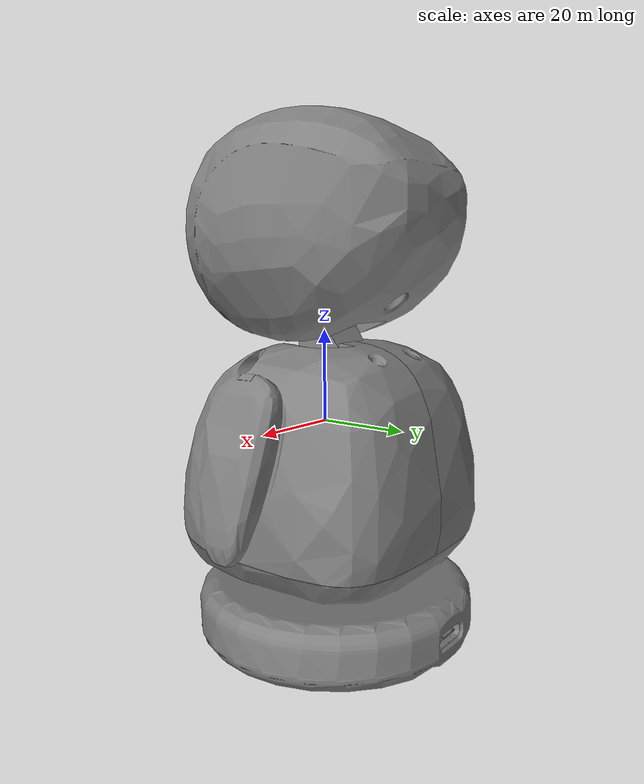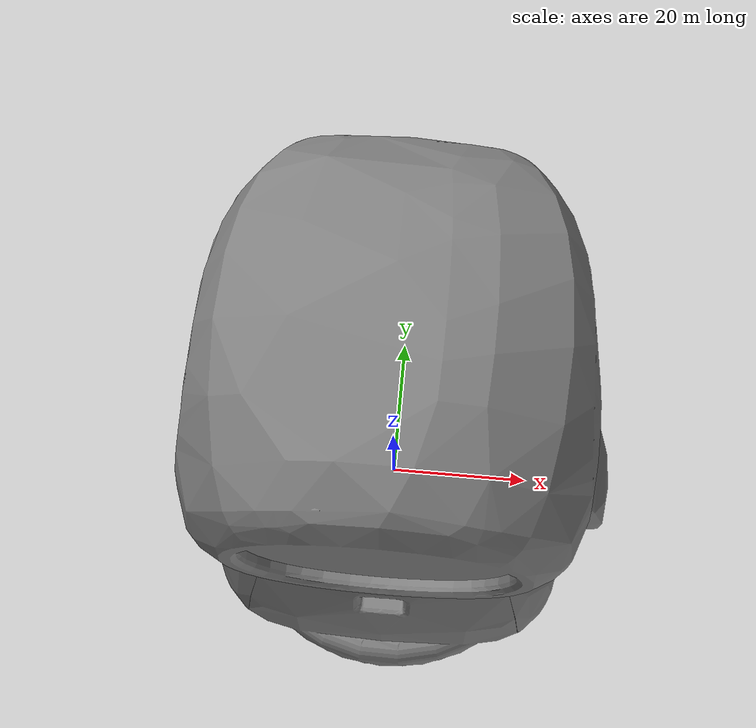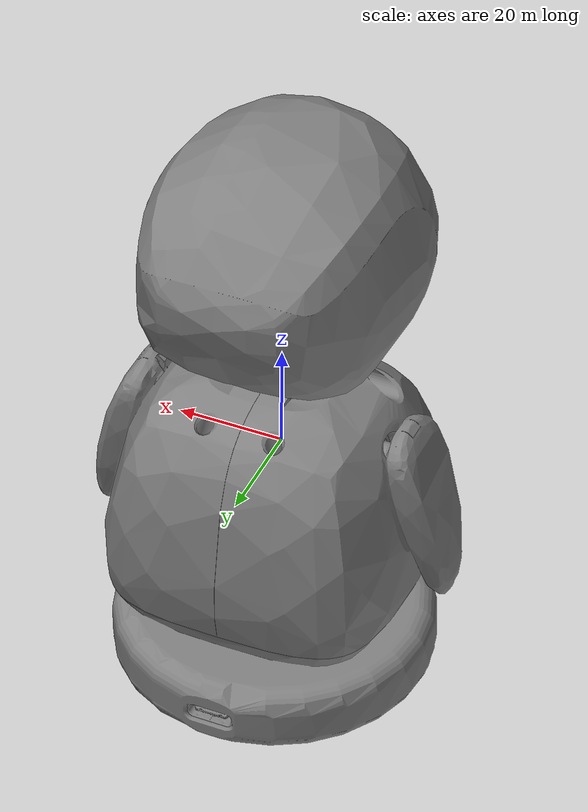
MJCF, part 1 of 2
<mujoco model="electronbot">
  <compiler angle="radian" autolimits="true"/>
  <default>
    <joint damping="5.0" armature="0.01" frictionloss="0.1"/>
    <position kp="200" kv="50" forcerange="-100.0 100.0" ctrllimited="true"/>
    <motor ctrllimited="true"/>
    <geom contype="0" conaffinity="0" condim="3" friction="0.8 0.3 0.1" density="0.6"/>
  </default>
  <asset>
    <mesh name="base_link" vertex="6.187464 19.011259 -6.350000 6.200000 18.900000 -11.900000 6.187464 19.011259 -11.900000 6.200000 18.900000 -6.350000 6.150484 19.116940 -6.350000 6.150484 19.116940 -11.900000 6.090916 19.211740 -11.900000 6.090916 19.211740 -6.350000 6.011745 19.290920 -6.350000 6.011745 19.290920 -11.900000 5.916942 19.350479 -11.900000 5.916942 19.350479 -6.350000 5.811260 19.387461 -11.900000 5.811260 19.387461 -6.350000 5.700000 19.400000 -6.350000 5.700000 19.400000 -11.900000 5.811260 -3.187464 -6.350000 5.700000 -3.200000 -11.900000 5.811260 -3.187464 -11.900000 5.700000 -3.200000 -6.350000 5.916942 -3.150484 -6.350000 5.916942 -3.150484 -11.900000 6.011745 -3.090916 -11.900000 6.011745 -3.090916 -6.350000 6.090916 -3.011745 -6.350000 6.090916 -3.011745 -11.900000 6.150484 -2.916942 -11.900000 6.150484 -2.916942 -6.350000 6.187464 -2.811260 -11.900000 6.187464 -2.811260 -6.350000 6.200000 -2.700000 -6.350000 6.200000 -2.700000 -11.900000 -6.187464 -2.811260 -6.350000 -6.200000 -2.700000 -11.900000 -6.187464 -2.811260 -11.900000 -6.200000 -2.700000 -6.350000 -6.150484 -2.916942 -6.350000 -6.150484 -2.916942 -11.900000 -6.090916 -3.011745 -11.900000 -6.090916 -3.011745 -6.350000 -6.011745 -3.090916 -6.350000 -6.011745 -3.090916 -11.900000 -5.916942 -3.150484 -11.900000 -5.916942 -3.150484 -6.350000 -5.811260 -3.187464 -11.900000 -5.811260 -3.187464 -6.350000 -5.700000 -3.200000 -6.350000 -5.700000 -3.200000 -11.900000 -5.811260 19.387461 -6.350000 -5.700000 19.400000 -11.900000 -5.811260 19.387461 -11.900000 -5.700000 19.400000 -6.350000 -5.916942 19.350479 -6.350000 -5.916942 19.350479 -11.900000 -6.011745 19.290920 -11.900000 -6.011745 19.290920 -6.350000 -6.090916 19.211740 -6.350000 -6.090916 19.211740 -11.900000 -6.150484 19.116940 -11.900000 -6.150484 19.116940 -6.350000 -6.187464 19.011259 -11.900000 -6.187464 19.011259 -6.350000 -6.200000 18.900000 -6.350000 -6.200000 18.900000 -11.900000 -5.700000 19.325001 -6.220096 -5.700000 19.250000 -6.200000 5.700000 19.250000 -6.200000 5.700000 19.325001 -6.220096 -5.700000 19.379900 -6.275000 5.700000 19.379900 -6.275000 6.125000 18.900000 -6.220096 6.050000 -2.700000 -6.200000 6.125000 -2.700000 -6.220096 6.050000 18.900000 -6.200000 6.179904 18.900000 -6.275000 6.179904 -2.700000 -6.275000 5.700000 -3.125000 -6.220096 -5.700000 -3.050000 -6.200000 -5.700000 -3.125000 -6.220096 5.700000 -3.050000 -6.200000 5.700000 -3.179904 -6.275000 -5.700000 -3.179904 -6.275000 -6.125000 -2.700000 -6.220096 -6.050000 -2.700000 -6.200000 -6.050000 18.900000 -6.200000 -6.125000 18.900000 -6.220096 -6.179904 -2.700000 -6.275000 -6.179904 18.900000 -6.275000 -5.806789 19.367870 -6.275000 -5.794571 19.314341 -6.220096 -5.790587 19.238070 -6.200000 -5.908222 19.332380 -6.275000 -5.884401 19.282909 -6.220096 -5.875000 19.203110 -6.200000 -5.999215 19.275200 -6.275000 -6.039343 19.239340 -6.275000 -5.964983 19.232281 -6.220096 -5.947487 19.147490 -6.200000 -6.075204 19.199221 -6.275000 -6.000520 19.200520 -6.220096 -6.115609 19.139950 -6.275000 -6.032278 19.164980 -6.220096 -6.003109 19.075001 -6.200000 -6.068061 19.112499 -6.220096 -6.163551 19.024210 -6.275000 -6.110518 19.010000 -6.220096 -6.038074 18.990589 -6.200000 -6.167872 -2.806789 -6.275000 -6.114344 -2.794571 -6.220096 -6.038074 -2.790587 -6.200000 -6.132378 -2.908222 -6.275000 -6.082912 -2.884401 -6.220096 -6.003109 -2.875000 -6.200000 -6.075204 -2.999215 -6.275000 -6.039343 -3.039343 -6.275000 -6.032278 -2.964983 -6.220096 -5.947487 -2.947487 -6.200000 -5.999215 -3.075204 -6.275000 -6.000520 -3.000520 -6.220096 -5.939952 -3.115609 -6.275000 -5.964983 -3.032278 -6.220096 -5.875000 -3.003109 -6.200000 -5.912500 -3.068061 -6.220096 -5.824208 -3.163551 -6.275000 -5.809998 -3.110518 -6.220096 -5.790587 -3.038074 -6.200000 5.806789 -3.167872 -6.275000 5.794571 -3.114344 -6.220096 5.790587 -3.038074 -6.200000 5.908222 -3.132378 -6.275000 5.884401 -3.082912 -6.220096 5.875000 -3.003109 -6.200000 5.999215 -3.075204 -6.275000 6.039343 -3.039343 -6.275000 5.964983 -3.032278 -6.220096 5.947487 -2.947487 -6.200000 6.075204 -2.999215 -6.275000 6.000520 -3.000520 -6.220096 6.115609 -2.939952 -6.275000 6.032278 -2.964983 -6.220096 6.003109 -2.875000 -6.200000 6.068061 -2.912500 -6.220096 6.163551 -2.824208 -6.275000 6.110518 -2.809998 -6.220096 6.038074 -2.790587 -6.200000 6.167872 19.006790 -6.275000 6.114344 18.994570 -6.220096 6.038074 18.990589 -6.200000 6.132378 19.108219 -6.275000 6.082912 19.084400 -6.220096 6.003109 19.075001 -6.200000 6.075204 19.199221 -6.275000 6.039343 19.239340 -6.275000 6.032278 19.164980 -6.220096 5.947487 19.147490 -6.200000 5.999215 19.275200 -6.275000 6.000520 19.200520 -6.220096 5.939952 19.315611 -6.275000 5.964983 19.232281 -6.220096 5.875000 19.203110 -6.200000 5.912500 19.268061 -6.220096 5.824208 19.363550 -6.275000 5.809998 19.310520 -6.220096 5.790587 19.238070 -6.200000 5.700000 19.200001 -11.950000 -5.700000 19.200001 -11.900000 5.700000 19.200001 -11.900000 -5.700000 19.200001 -11.950000 -5.792705 19.185320 -11.900000 -5.792705 19.185320 -11.950000 -5.876336 19.142710 -11.900000 -5.876336 19.142710 -11.950000 -5.942705 19.076340 -11.900000 -5.942705 19.076340 -11.950000 -5.985317 18.992710 -11.900000 -5.985317 18.992710 -11.950000 -6.000000 18.900000 -11.900000 -6.000000 18.900000 -11.950000 -6.000000 -2.700000 -11.950000 -6.000000 -2.700000 -11.900000 -5.985317 -2.792705 -11.900000 -5.985317 -2.792705 -11.950000 -5.942705 -2.876336 -11.900000 -5.942705 -2.876336 -11.950000 -5.876336 -2.942705 -11.900000 -5.876336 -2.942705 -11.950000 -5.792705 -2.985317 -11.900000 -5.792705 -2.985317 -11.950000 -5.700000 -3.000000 -11.900000 -5.700000 -3.000000 -11.950000 5.700000 -3.000000 -11.900000 5.700000 -3.000000 -11.950000 5.792705 -2.985317 -11.900000 5.792705 -2.985317 -11.950000 5.876336 -2.942705 -11.900000 5.876336 -2.942705 -11.950000 5.942705 -2.876336 -11.900000 5.942705 -2.876336 -11.950000 5.985317 -2.792705 -11.900000 5.985317 -2.792705 -11.950000 6.000000 -2.700000 -11.900000 6.000000 -2.700000 -11.950000 6.000000 18.900000 -11.950000 6.000000 18.900000 -11.900000 5.985317 18.992710 -11.900000 5.985317 18.992710 -11.950000 5.942705 19.076340 -11.900000 5.942705 19.076340 -11.950000 5.876336 19.142710 -11.900000 5.876336 19.142710 -11.950000 5.792705 19.185320 -11.900000 5.792705 19.185320 -11.950000 -6.011745 -3.090916 -11.950000 -5.916942 -3.150484 -11.950000 -6.150484 -2.916942 -11.950000 -6.090916 -3.011745 -11.950000 -5.811260 -3.187464 -11.950000 -6.187464 -2.811260 -11.950000 -6.200000 -2.700000 -11.950000 -5.700000 -3.200000 -11.950000 5.700000 -3.200000 -11.950000 5.811260 -3.187464 -11.950000 5.916942 -3.150484 -11.950000 6.011745 -3.090916 -11.950000 6.090916 -3.011745 -11.950000 6.150484 -2.916942 -11.950000 6.187464 -2.811260 -11.950000 6.200000 -2.700000 -11.950000 -6.187464 19.011259 -11.950000 -6.200000 18.900000 -11.950000 -6.150484 19.116940 -11.950000 -6.090916 19.211740 -11.950000 -6.011745 19.290920 -11.950000 -5.916942 19.350479 -11.950000 -5.811260 19.387461 -11.950000 -5.700000 19.400000 -11.950000 5.700000 19.400000 -11.950000 6.200000 18.900000 -11.950000 6.187464 19.011259 -11.950000 5.811260 19.387461 -11.950000 5.916942 19.350479 -11.950000 6.150484 19.116940 -11.950000 6.090916 19.211740 -11.950000 6.011745 19.290920 -11.950000 5.700000 -3.000000 -21.799999 -5.700000 -3.000000 -21.750000 -5.700000 -3.000000 -21.799999 5.700000 -3.000000 -21.750000 -5.792705 -2.985317 -21.799999 -5.792705 -2.985317 -21.750000 -5.876336 -2.942705 -21.799999 -5.876336 -2.942705 -21.750000 -5.942705 -2.876336 -21.799999 -5.942705 -2.876336 -21.750000 -5.985317 -2.792705 -21.799999 -5.985317 -2.792705 -21.750000 -6.000000 -2.700000 -21.799999 -6.000000 -2.700000 -21.750000 -6.000000 18.900000 -21.750000 -6.000000 18.900000 -21.799999 -5.985317 18.992710 -21.799999 -5.985317 18.992710 -21.750000 -5.942705 19.076340 -21.799999 -5.942705 19.076340 -21.750000 -5.876336 19.142710 -21.799999 -5.876336 19.142710 -21.750000 -5.792705 19.185320 -21.799999 -5.792705 19.185320 -21.750000 -5.700000 19.200001 -21.799999 -5.700000 19.200001 -21.750000 5.700000 19.200001 -21.750000 5.700000 19.200001 -21.799999 5.792705 19.185320 -21.799999 5.792705 19.185320 -21.750000 5.876336 19.142710 -21.799999 5.876336 19.142710 -21.750000 5.942705 19.076340 -21.799999 5.942705 19.076340 -21.750000 5.985317 18.992710 -21.799999 5.985317 18.992710 -21.750000 6.000000 18.900000 -21.799999 6.000000 18.900000 -21.750000 6.000000 -2.700000 -21.750000 6.000000 -2.700000 -21.799999 5.985317 -2.792705 -21.799999 5.985317 -2.792705 -21.750000 5.942705 -2.876336 -21.799999 5.942705 -2.876336 -21.750000 5.876336 -2.942705 -21.799999 5.876336 -2.942705 -21.750000 5.792705 -2.985317 -21.799999 5.792705 -2.985317 -21.750000 -6.011745 -3.090916 -21.750000 -6.090916 -3.011745 -21.750000 -5.916942 -3.150484 -21.750000 -6.150484 -2.916942 -21.750000 -6.187464 -2.811260 -21.750000 -5.811260 -3.187464 -21.750000 -5.700000 -3.200000 -21.750000 -6.200000 -2.700000 -21.750000 5.700000 -3.200000 -21.750000 5.811260 -3.187464 -21.750000 5.916942 -3.150484 -21.750000 6.011745 -3.090916 -21.750000 6.090916 -3.011745 -21.750000 6.150484 -2.916942 -21.750000 6.187464 -2.811260 -21.750000 6.200000 -2.700000 -21.750000 -6.200000 18.900000 -21.750000 -6.187464 19.011259 -21.750000 -6.150484 19.116940 -21.750000 -6.090916 19.211740 -21.750000 -6.011745 19.290920 -21.750000 -5.916942 19.350479 -21.750000 -5.811260 19.387461 -21.750000 -5.700000 19.400000 -21.750000 6.200000 18.900000 -21.750000 5.700000 19.400000 -21.750000 6.187464 19.011259 -21.750000 5.811260 19.387461 -21.750000 6.150484 19.116940 -21.750000 5.916942 19.350479 -21.750000 6.090916 19.211740 -21.750000 6.011745 19.290920 -21.750000 -2.829904 8.750000 -32.724998 -2.850000 8.506133 -32.650002 -2.850000 8.750000 -32.650002 -2.805971 8.479279 -32.756161 -2.775000 8.750000 -32.779900 -2.700000 8.414102 -32.799999 -2.700000 8.750000 -32.799999 2.829904 8.750000 -32.724998 2.767184 9.432050 -32.650002 2.850000 8.750000 -32.650002 -2.747672 9.427240 -32.724998 -2.767184 9.432050 -32.650002 -2.694364 9.414101 -32.779900 -2.621543 9.396152 -32.799999 -2.505755 10.065120 -32.724998 -2.523550 10.074460 -32.650002 -2.457140 10.039610 -32.779900 -2.390731 10.004750 -32.799999 -2.118213 10.626570 -32.724998 -2.133256 10.639900 -32.650002 -2.077117 10.590170 -32.779900 -2.020979 10.540430 -32.799999 -1.533775 10.972060 -32.799999 -1.607569 11.078970 -32.724998 -1.618985 11.095500 -32.650002 -1.576380 11.033780 -32.779900 -0.957433 11.274540 -32.799999 -1.003498 11.396010 -32.724998 -1.010624 11.414800 -32.650002 -0.984029 11.344670 -32.779900 -0.341107 11.559270 -32.724998 -0.343529 11.579220 -32.650002 -0.334489 11.504770 -32.779900 -0.325449 11.430310 -32.799999 0.325449 11.430310 -32.799999 0.341107 11.559270 -32.724998 0.343529 11.579220 -32.650002 0.334489 11.504770 -32.779900 1.003498 11.396010 -32.724998 1.010624 11.414800 -32.650002 0.984029 11.344670 -32.779900 0.957433 11.274540 -32.799999 1.607569 11.078970 -32.724998 1.618985 11.095500 -32.650002 1.576380 11.033780 -32.779900 1.533775 10.972060 -32.799999 2.020979 10.540430 -32.799999 2.118213 10.626570 -32.724998 2.133256 10.639900 -32.650002 2.077117 10.590170 -32.779900 2.505755 10.065120 -32.724998 2.523550 10.074460 -32.650002 2.457140 10.039610 -32.779900 2.390731 10.004750 -32.799999 2.621543 9.396152 -32.799999 2.747672 9.427240 -32.724998 2.694364 9.414101 -32.779900 2.775000 8.750000 -32.779900 2.700000 8.750000 -32.799999 2.850000 8.506133 -32.650002 2.806057 8.479332 -32.756081 2.700000 8.414102 -32.799999 -2.925000 8.750000 -28.520100 -3.000000 8.596651 -28.500000 -3.000000 8.750000 -28.500000 -2.893837 8.532740 -28.544029 -2.870096 8.750000 -28.575001 -2.850000 8.506133 -28.650000 -2.850000 8.750000 -28.650000 3.000000 8.750000 -28.500000 2.925000 8.750000 -28.520100 2.912825 9.467947 -28.500000 -2.786696 9.436859 -28.575001 -2.767184 9.432050 -28.650000 -2.840005 9.449998 -28.520100 -2.912825 9.467947 -28.500000 -2.541344 10.083800 -28.575001 -2.523550 10.074460 -28.650000 -2.589959 10.109320 -28.520100 -2.656368 10.144170 -28.500000 -2.148298 10.653230 -28.575001 -2.133256 10.639900 -28.650000 -2.189394 10.689630 -28.520100 -2.245532 10.739370 -28.500000 -1.630400 11.112040 -28.575001 -1.618985 11.095500 -28.650000 -1.661589 11.157230 -28.520100 -1.704194 11.218950 -28.500000 -1.017750 11.433590 -28.575001 -1.010624 11.414800 -28.650000 -1.037219 11.484920 -28.520100 -1.063815 11.555050 -28.500000 -0.345952 11.599170 -28.575001 -0.343529 11.579220 -28.650000 -0.352570 11.653670 -28.520100 -0.361610 11.728130 -28.500000 0.345952 11.599170 -28.575001 0.343529 11.579220 -28.650000 1.010624 11.414800 -28.650000 0.352570 11.653670 -28.520100 0.361610 11.728130 -28.500000 1.017750 11.433590 -28.575001 1.037219 11.484920 -28.520100 1.063815 11.555050 -28.500000 1.630400 11.112040 -28.575001 1.618985 11.095500 -28.650000 1.661589 11.157230 -28.520100 1.704194 11.218950 -28.500000 2.148298 10.653230 -28.575001 2.133256 10.639900 -28.650000 2.189394 10.689630 -28.520100 2.245532 10.739370 -28.500000 2.541344 10.083800 -28.575001 2.523550 10.074460 -28.650000 2.589959 10.109320 -28.520100 2.656368 10.144170 -28.500000 2.786696 9.436859 -28.575001 2.767184 9.432050 -28.650000 2.850000 8.750000 -28.650000 2.870096 8.750000 -28.575001 2.840005 9.449998 -28.520100 -4.015455 7.919209 -28.500000 -4.738471 6.998361 -28.650000 -4.882523 7.059983 -28.500000 -3.868406 7.845145 -28.650000 -5.476055 5.999721 -28.544029 -5.907087 4.883170 -28.650000 -5.950963 4.890178 -28.543930 -5.426830 5.998252 -28.650000 -6.050000 4.928730 -28.500000 -5.569163 6.050725 -28.500000 -4.800895 6.992106 -28.544029 -3.948323 7.836967 -28.544029 -2.949844 8.503083 -28.544029 3.000000 8.596651 -28.500000 2.893923 8.532791 -28.543940 2.850000 8.506133 -28.650000 -6.186367 3.401722 -28.584949 -6.167223 3.636675 -28.650000 -6.200000 3.000000 -28.650000 -6.199548 3.000000 -28.500700 -6.132030 3.949832 -28.554399 -6.137263 3.875325 -28.601379 -6.069240 4.266618 -28.650000 -6.044626 4.382301 -28.611240 3.868406 7.845145 -28.650000 4.738471 6.998361 -28.650000 4.015455 7.919209 -28.500000 5.426830 5.998252 -28.650000 4.882523 7.059983 -28.500000 5.950963 4.890178 -28.543930 5.907087 4.883170 -28.650000 5.569163 6.050725 -28.500000 6.050000 4.928730 -28.500000 3.895811 7.879470 -28.543949 4.772040 7.026687 -28.543949 5.465275 6.019493 -28.543949 -3.247670 -2.332858 -28.543930 -1.883170 -2.907087 -28.650000 -1.890178 -2.950963 -28.543930 -3.224818 -2.295333 -28.650000 -1.928730 -3.050000 -28.500000 -3.302837 -2.423446 -28.500000 -4.415129 -1.415129 -28.543930 -4.384062 -1.384062 -28.650000 -4.490128 -1.490128 -28.500000 -5.332858 -0.247670 -28.543930 -5.295333 -0.224818 -28.650000 -5.907087 1.116830 -28.650000 -5.950963 1.109822 -28.543930 -6.050000 1.071270 -28.500000 -5.423446 -0.302837 -28.500000 -6.179904 -3.050000 -28.424999 -6.200000 -3.050000 -28.350000 -6.200000 1.071270 -28.350000 -6.156066 1.078032 -28.456070 -6.125000 -3.050000 -28.479900 -6.050000 -3.050000 -28.500000 -6.200000 4.928730 -28.350000 -6.200000 19.250000 -28.350000 -6.179904 19.250000 -28.424999 -6.156066 4.921968 -28.456070 -6.125000 19.250000 -28.479900 -6.050000 19.250000 -28.500000 6.142679 4.132960 -28.492710 6.156066 4.921968 -28.456070 6.199548 3.000000 -28.500700 6.132030 3.949832 -28.554399 6.103470 4.388142 -28.506941 -0.401722 -3.186367 -28.584949 -0.636675 -3.167223 -28.650000 0.000000 -3.200000 -28.650000 0.000000 -3.199548 -28.500700 -0.949832 -3.132030 -28.554399 -0.875325 -3.137263 -28.601379 -1.266618 -3.069240 -28.650000 -1.382301 -3.044626 -28.611240 -6.077036 -3.185919 -28.407400 -6.050000 -3.179904 -28.424999 -6.050000 -3.200000 -28.350000 -6.125000 -3.179904 -28.350000 -6.126992 -3.165227 -28.407400 -6.165227 -3.126992 -28.407400 -6.179904 -3.125000 -28.350000 -6.090590 -3.147992 -28.456070 -6.050000 -3.125000 -28.479900 -6.185919 -3.077036 -28.407400 -6.125000 -3.125000 -28.456070 -6.061199 -3.106300 -28.488581 -6.147992 -3.090590 -28.456070 -6.081891 -3.097728 -28.488581 -6.097728 -3.081891 -28.488581 -6.106300 -3.061199 -28.488581 -6.185919 19.277040 -28.407400 -6.179904 19.325001 -28.350000 -6.165227 19.326990 -28.407400 -6.126992 19.365231 -28.407400 -6.125000 19.379900 -28.350000 -6.147992 19.290590 -28.456070 -6.077036 19.385920 -28.407400 -6.050000 19.400000 -28.350000 -6.050000 19.379900 -28.424999 -6.125000 19.325001 -28.456070 -6.106300 19.261200 -28.488581 -6.090590 19.347990 -28.456070 -6.050000 19.325001 -28.479900 -6.097728 19.281891 -28.488581 -6.081891 19.297729 -28.488581 -6.061199 19.306299 -28.488581 6.179904 19.250000 -28.424999 6.200000 19.250000 -28.350000 6.200000 4.928730 -28.350000 6.125000 19.250000 -28.479900 6.050000 19.250000 -28.500000 6.200000 1.071270 -28.350000 6.200000 -3.050000 -28.350000 6.179904 -3.050000 -28.424999 6.156066 1.078032 -28.456070 6.125000 -3.050000 -28.479900 6.050000 1.071270 -28.500000 6.050000 -3.050000 -28.500000 5.332858 -0.247670 -28.543930 5.907087 1.116830 -28.650000 5.950963 1.109822 -28.543930 5.295333 -0.224818 -28.650000 5.423446 -0.302837 -28.500000 4.415129 -1.415129 -28.543930 4.384062 -1.384062 -28.650000 4.490128 -1.490128 -28.500000 3.247670 -2.332858 -28.543930 3.224818 -2.295333 -28.650000 1.883170 -2.907087 -28.650000 1.890178 -2.950963 -28.543930 1.928730 -3.050000 -28.500000 3.302837 -2.423446 -28.500000 6.050000 -3.179904 -28.424999 6.050000 -3.200000 -28.350000 1.928730 -3.200000 -28.350000 1.921968 -3.156066 -28.456070 6.050000 -3.125000 -28.479900 -1.928730 -3.200000 -28.350000 -1.921968 -3.156066 -28.456070 -6.188582 -3.107403 -24.307400 -6.200000 -3.050000 -24.250000 -6.156066 -3.156066 -24.356070 -6.107403 -3.188582 -24.388580 -6.050000 -3.200000 -24.400000 -6.107403 19.388580 -24.388580 -6.050000 19.400000 -24.400000 -6.156066 19.356070 -24.356070 -6.188582 19.307400 -24.307400 -6.200000 19.250000 -24.250000 6.050000 19.400000 -28.350000 6.050000 19.379900 -28.424999 6.050000 19.325001 -28.479900 6.077036 19.385920 -28.407400 6.125000 19.379900 -28.350000 6.126992 19.365231 -28.407400 6.165227 19.326990 -28.407400 6.179904 19.325001 -28.350000 6.090590 19.347990 -28.456070 6.185919 19.277040 -28.407400 6.125000 19.325001 -28.456070 6.061199 19.306299 -28.488581 6.147992 19.290590 -28.456070 6.081891 19.297729 -28.488581 6.097728 19.281891 -28.488581 6.106300 19.261200 -28.488581 6.185919 -3.077036 -28.407400 6.179904 -3.125000 -28.350000 6.165227 -3.126992 -28.407400 6.126992 -3.165227 -28.407400 6.125000 -3.179904 -28.350000 6.147992 -3.090590 -28.456070 6.077036 -3.185919 -28.407400 6.125000 -3.125000 -28.456070 6.106300 -3.061199 -28.488581 6.090590 -3.147992 -28.456070 6.097728 -3.081891 -28.488581 6.081891 -3.097728 -28.488581 6.061199 -3.106300 -28.488581 -6.200000 -3.200000 -24.250000 -6.179904 -3.200000 -24.325001 -6.125000 -3.200000 -24.379900 -6.200000 23.750000 -24.250000 -6.179904 23.750000 -24.325001 -6.125000 23.750000 -24.379900 -6.050000 23.750000 -24.400000 6.188582 19.307400 -24.307400 6.200000 19.250000 -24.250000 6.156066 19.356070 -24.356070 6.107403 19.388580 -24.388580 6.050000 19.400000 -24.400000 6.107403 -3.188582 -24.388580 6.050000 -3.200000 -24.400000 6.156066 -3.156066 -24.356070 6.188582 -3.107403 -24.307400 6.200000 -3.050000 -24.250000 -5.700000 24.229900 -24.325001 -5.811260 24.237459 -24.250000 -5.700000 24.250000 -24.250000 -6.167872 23.856791 -24.325001 -6.187464 23.861259 -24.250000 -6.114344 23.844570 -24.379900 -6.038074 23.840590 -24.400000 -6.132378 23.958220 -24.325001 -6.150484 23.966940 -24.250000 -6.082912 23.934401 -24.379900 -6.003109 23.924999 -24.400000 -6.075204 24.049219 -24.325001 -6.090916 24.061741 -24.250000 -6.039343 24.089340 -24.325001 -6.011745 24.140921 -24.250000 -6.032278 24.014980 -24.379900 -5.947487 23.997490 -24.400000 -5.999215 24.125200 -24.325001 -6.000520 24.050520 -24.379900 -5.939952 24.165609 -24.325001 -5.916942 24.200480 -24.250000 -5.964983 24.082279 -24.379900 -5.875000 24.053110 -24.400000 -5.912500 24.118059 -24.379900 -5.824208 24.213551 -24.325001 -5.809998 24.160521 -24.379900 -5.700000 24.174999 -24.379900 -5.700000 24.100000 -24.400000 -5.790587 24.088070 -24.400000 6.200000 23.750000 -24.250000 6.179904 23.750000 -24.325001 6.125000 23.750000 -24.379900 6.050000 23.750000 -24.400000 -0.600000 24.250000 -24.250000 -0.600000 24.229900 -24.325001 -0.600000 24.174999 -24.379900 -0.600000 24.100000 -24.400000 6.187464 23.861259 -24.250000 5.806789 24.217871 -24.325001 5.700000 24.229900 -24.325001 5.700000 24.250000 -24.250000 5.811260 24.237459 -24.250000 5.794571 24.164339 -24.379900 5.700000 24.100000 -24.400000 5.700000 24.174999 -24.379900 5.790587 24.088070 -24.400000 5.908222 24.182381 -24.325001 5.916942 24.200480 -24.250000 5.884401 24.132910 -24.379900 5.875000 24.053110 -24.400000 5.999215 24.125200 -24.325001 6.011745 24.140921 -24.250000 6.039343 24.089340 -24.325001 6.090916 24.061741 -24.250000 5.964983 24.082279 -24.379900 5.947487 23.997490 -24.400000 6.075204 24.049219 -24.325001 6.000520 24.050520 -24.379900 6.115609 23.989950 -24.325001 6.150484 23.966940 -24.250000 6.032278 24.014980 -24.379900 6.003109 23.924999 -24.400000 6.068061 23.962500 -24.379900 6.163551 23.874210 -24.325001 6.110518 23.860001 -24.379900 6.038074 23.840590 -24.400000 0.600000 24.229900 -24.325001 0.600000 24.250000 -24.250000 0.600000 24.174999 -24.379900 0.600000 24.100000 -24.400000 -1.388142 -3.103470 -28.506941 1.123235 -3.118706 -28.529760 0.949832 -3.132030 -28.554399 1.388142 -3.103470 -28.506941 0.636675 -3.167223 -28.650000 0.875325 -3.137263 -28.601379 1.266618 -3.069240 -28.650000 1.382301 -3.044626 -28.611240 6.167223 3.636675 -28.650000 6.200000 3.000000 -28.650000 6.069240 4.266618 -28.650000 6.137263 3.875325 -28.601379 6.186367 2.598278 -28.584949 6.132030 2.050168 -28.554399 6.167223 2.363325 -28.650000 6.137263 2.124675 -28.601379 6.069240 1.733382 -28.650000 6.044626 1.617699 -28.611240 6.142679 1.867040 -28.492710 6.103470 1.611858 -28.506941 6.200066 2.593909 -28.420971 6.200000 3.000000 -28.350000 6.194730 2.113603 -28.414089 6.194730 3.886397 -28.414089 -6.142679 4.132960 -28.492710 -6.103470 4.388142 -28.506941 -6.194730 3.886397 -28.414089 -6.200000 3.000000 -28.350000 -6.194730 2.113603 -28.414089 -6.142679 1.867040 -28.492710 -6.132030 2.050168 -28.554399 -6.103470 1.611858 -28.506941 -6.167223 2.363325 -28.650000 -6.137263 2.124675 -28.601379 -6.069240 1.733382 -28.650000 -6.044626 1.617699 -28.611240 6.187464 23.861259 -21.799999 6.200000 23.750000 -21.799999 6.150484 23.966940 -21.799999 6.090916 24.061741 -21.799999 6.011745 24.140921 -21.799999 5.916942 24.200480 -21.799999 5.811260 24.237459 -21.799999 5.700000 24.250000 -21.799999 -5.811260 24.237459 -21.799999 -5.700000 24.250000 -21.799999 -5.916942 24.200480 -21.799999 -6.011745 24.140921 -21.799999 -6.090916 24.061741 -21.799999 -6.150484 23.966940 -21.799999 -6.187464 23.861259 -21.799999 -6.200000 23.750000 -21.799999 -4.366942 11.949520 -28.299999 -4.461745 12.009080 -28.299999 -4.540916 12.088260 -28.299999 -4.150000 11.900000 -28.299999 -4.261260 11.912540 -28.299999 -4.600484 12.183060 -28.299999 -4.637464 12.288740 -28.299999 -4.650000 12.400000 -28.299999 -4.650000 17.600000 -28.299999 -4.600484 17.816940 -28.299999 -4.637464 17.711260 -28.299999 -4.461745 17.990919 -28.299999 -4.540916 17.911739 -28.299999 -4.150000 18.100000 -28.299999 -4.366942 18.050480 -28.299999 -4.261260 18.087460 -28.299999 4.366942 11.949520 -28.299999 4.261260 11.912540 -28.299999 4.150000 11.900000 -28.299999 4.461745 12.009080 -28.299999 4.637464 12.288740 -28.299999 4.600484 12.183060 -28.299999 4.540916 12.088260 -28.299999 4.650000 12.400000 -28.299999 4.150000 18.100000 -28.299999 4.650000 17.600000 -28.299999 4.366942 18.050480 -28.299999 4.261260 18.087460 -28.299999 4.540916 17.911739 -28.299999 4.461745 17.990919 -28.299999 4.600484 17.816940 -28.299999 4.637464 17.711260 -28.299999 4.150000 18.100000 -28.500000 -4.150000 18.100000 -28.500000 4.261260 18.087460 -28.500000 4.366942 18.050480 -28.500000 4.461745 17.990919 -28.500000 4.540916 17.911739 -28.500000 4.600484 17.816940 -28.500000 4.637464 17.711260 -28.500000 4.650000 17.600000 -28.500000 4.650000 12.400000 -28.500000 4.637464 12.288740 -28.500000 4.600484 12.183060 -28.500000 4.540916 12.088260 -28.500000 4.461745 12.009080 -28.500000 4.366942 11.949520 -28.500000 4.261260 11.912540 -28.500000 4.150000 11.900000 -28.500000 -4.150000 11.900000 -28.500000 -4.261260 11.912540 -28.500000 -4.366942 11.949520 -28.500000 -4.461745 12.009080 -28.500000 -4.540916 12.088260 -28.500000 -4.600484 12.183060 -28.500000 -4.637464 12.288740 -28.500000 -4.650000 12.400000 -28.500000 -4.650000 17.600000 -28.500000 -4.637464 17.711260 -28.500000 -4.600484 17.816940 -28.500000 -4.540916 17.911739 -28.500000 -4.461745 17.990919 -28.500000 -4.366942 18.050480 -28.500000 -4.261260 18.087460 -28.500000 -1.128101 20.698521 -22.799999 -1.487945 21.013580 -22.799999 -5.200000 19.400000 -22.799999 -1.762697 21.405069 -22.799999 -0.703743 20.477900 -22.799999 -1.936645 21.850590 -22.799999 -5.200000 23.250000 -22.799999 -0.239140 20.364349 -22.799999 -1.999840 22.324680 -22.799999 0.239140 20.364349 -22.799999 -1.948668 22.800211 -22.799999 -1.786057 23.250000 -22.799999 5.200000 19.400000 -22.799999 1.936645 21.850590 -22.799999 1.762697 21.405069 -22.799999 1.487945 21.013580 -22.799999 1.128101 20.698521 -22.799999 0.703743 20.477900 -22.799999 5.200000 23.250000 -22.799999 1.786057 23.250000 -22.799999 1.948668 22.800211 -22.799999 1.999840 22.324680 -22.799999 -5.200000 23.250000 -21.799999 -1.786057 23.250000 -21.799999 -5.200000 19.400000 -21.799999 5.200000 23.250000 -21.799999 5.200000 19.400000 -21.799999 1.786057 23.250000 -21.799999 0.600000 23.150000 -21.799999 0.600000 24.250000 -21.799999 0.600000 23.150000 -24.400000 -0.600000 23.150000 -21.799999 -0.600000 23.150000 -24.400000 -0.600000 24.250000 -21.799999 0.708365 2.628221 -32.799999 0.598809 2.469502 -32.799999 0.454452 2.341613 -32.799999 0.800000 3.000000 -32.799999 0.776753 2.808547 -32.799999 -0.454452 2.341613 -32.799999 -0.096429 2.205833 -32.799999 -0.283684 2.251987 -32.799999 -0.598809 2.469502 -32.799999 0.096429 2.205833 -32.799999 0.283684 2.251987 -32.799999 0.283684 3.748013 -32.799999 0.708365 3.371779 -32.799999 0.776753 3.191453 -32.799999 0.598809 3.530498 -32.799999 0.454452 3.658387 -32.799999 -0.776753 2.808547 -32.799999 -0.708365 2.628221 -32.799999 -0.283684 3.748013 -32.799999 0.096429 3.794167 -32.799999 -0.096429 3.794167 -32.799999 -0.708365 3.371779 -32.799999 -0.800000 3.000000 -32.799999 -0.776753 3.191453 -32.799999 -0.598809 3.530498 -32.799999 -0.454452 3.658387 -32.799999 0.454452 2.341613 -36.000000 1.833851 1.375349 -36.000000 1.391759 0.983689 -36.000000 0.598809 2.469502 -36.000000 0.708365 2.628221 -36.000000 2.169367 1.861428 -36.000000 0.283684 2.251987 -36.000000 0.868782 0.709210 -36.000000 0.776753 2.808547 -36.000000 2.378807 2.413677 -36.000000 0.096429 2.205833 -36.000000 0.295315 0.567863 -36.000000 0.800000 3.000000 -36.000000 2.450000 3.000000 -36.000000 -0.096429 2.205833 -36.000000 -0.295315 0.567863 -36.000000 0.776753 3.191453 -36.000000 2.378807 3.586323 -36.000000 -0.283684 2.251987 -36.000000 -0.868782 0.709210 -36.000000 0.708365 3.371779 -36.000000 2.169367 4.138572 -36.000000 -0.454452 2.341613 -36.000000 -1.391759 0.983689 -36.000000 0.598809 3.530498 -36.000000 1.833851 4.624651 -36.000000 -0.598809 2.469502 -36.000000 0.454452 3.658387 -36.000000 -1.833851 1.375349 -36.000000 1.391759 5.016310 -36.000000 -2.169367 1.861428 -36.000000 -0.708365 2.628221 -36.000000 0.868782 5.290790 -36.000000 0.283684 3.748013 -36.000000 -2.378807 2.413677 -36.000000 -0.776753 2.808547 -36.000000 -0.800000 3.000000 -36.000000 0.295315 5.432137 -36.000000 0.096429 3.794167 -36.000000 -0.096429 3.794167 -36.000000 -2.450000 3.000000 -36.000000 -0.295315 5.432137 -36.000000 -2.378807 3.586323 -36.000000 -0.776753 3.191453 -36.000000 -0.868782 5.290790 -36.000000 -0.283684 3.748013 -36.000000 -0.454452 3.658387 -36.000000 -2.169367 4.138572 -36.000000 -0.708365 3.371779 -36.000000 -0.598809 3.530498 -36.000000 -1.391759 5.016310 -36.000000 -1.833851 4.624651 -36.000000 1.833851 1.375349 -32.799999 5.004801 -0.399186 -32.799999 4.037414 -1.505751 -32.799999 1.391759 0.983689 -32.799999 2.831733 -2.346381 -32.799999 2.169367 1.861428 -32.799999 5.676799 0.908004 -32.799999 0.868782 0.709210 -32.799999 1.458920 -2.871461 -32.799999 2.378807 2.413677 -32.799999 6.013746 2.338665 -32.799999 0.295315 0.567863 -32.799999 0.000000 -3.050000 -32.799999 2.450000 3.000000 -32.799999 5.995753 3.808359 -32.799999 -0.295315 0.567863 -32.799999 -1.458920 -2.871461 -32.799999 2.378807 3.586323 -32.799999 5.623884 5.230343 -32.799999 -0.868782 0.709210 -32.799999 -2.831733 -2.346381 -32.799999 2.169367 4.138572 -32.799999 4.920086 6.520689 -32.799999 -1.391759 0.983689 -32.799999 -4.037414 -1.505751 -32.799999 1.833851 4.624651 -32.799999 -1.833851 1.375349 -32.799999 3.925899 7.603240 -32.799999 1.391759 5.016310 -32.799999 -5.004801 -0.399186 -32.799999 -2.169367 1.861428 -32.799999 0.868782 5.290790 -32.799999 0.295315 5.432137 -32.799999 -5.676799 0.908004 -32.799999 -2.378807 2.413677 -32.799999 -6.013746 2.338665 -32.799999 -2.450000 3.000000 -32.799999 -5.995753 3.808359 -32.799999 -2.378807 3.586323 -32.799999 -5.623884 5.230343 -32.799999 -2.169367 4.138572 -32.799999 -0.868782 5.290790 -32.799999 -1.391759 5.016310 -32.799999 -0.295315 5.432137 -32.799999 -4.920086 6.520689 -32.799999 -1.833851 4.624651 -32.799999 -3.925899 7.603240 -32.799999 0.841058 21.809059 -24.400000 0.681220 21.617920 -24.400000 0.479091 21.472231 -24.400000 0.948683 22.033770 -24.400000 0.247219 21.381041 -24.400000 0.997413 22.278120 -24.400000 0.000000 21.350000 -24.400000 0.984223 22.526930 -24.400000 0.909932 22.764759 -24.400000 0.779151 22.976839 -24.400000 -0.779151 22.976839 -24.400000 -0.909932 22.764759 -24.400000 -0.247219 21.381041 -24.400000 -0.479091 21.472231 -24.400000 -0.681220 21.617920 -24.400000 -0.841058 21.809059 -24.400000 -0.948683 22.033770 -24.400000 -0.997413 22.278120 -24.400000 -0.984223 22.526930 -24.400000 -6.200000 -3.200000 -21.799999 -0.968844 -3.200000 -28.350000 6.200000 -3.200000 -21.799999 0.968844 -3.200000 -28.350000 0.000000 -3.200000 -28.452049 6.200000 -3.200000 -24.250000 6.179904 -3.200000 -24.325001 6.125000 -3.200000 -24.379900 -4.087300 7.661971 -32.650002 -5.086048 6.545718 -32.650002 -5.787953 5.222521 -32.650002 -6.152049 3.769608 -32.650002 -6.157085 2.271778 -32.650002 -5.802768 0.816450 -32.650002 -5.109776 -0.511436 -32.650002 -4.118557 -1.634381 -32.650002 -2.886962 -2.486844 -32.650002 -1.486871 -3.019071 -32.650002 0.000000 -3.200000 -32.650002 1.486871 -3.019071 -32.650002 2.886962 -2.486844 -32.650002 4.118557 -1.634381 -32.650002 5.109776 -0.511436 -32.650002 5.802768 0.816450 -32.650002 6.157085 2.271778 -32.650002 6.152049 3.769608 -32.650002 5.787953 5.222521 -32.650002 5.086048 6.545718 -32.650002 4.087300 7.661971 -32.650002 0.779151 22.976839 -21.799999 0.909932 22.764759 -21.799999 0.984223 22.526930 -21.799999 0.997413 22.278120 -21.799999 0.948683 22.033770 -21.799999 0.841058 21.809059 -21.799999 0.681220 21.617920 -21.799999 0.479091 21.472231 -21.799999 0.000000 21.350000 -21.799999 0.247219 21.381041 -21.799999 -0.247219 21.381041 -21.799999 -0.479091 21.472231 -21.799999 -0.681220 21.617920 -21.799999 -0.841058 21.809059 -21.799999 -0.948683 22.033770 -21.799999 -0.984223 22.526930 -21.799999 -0.997413 22.278120 -21.799999 -0.909932 22.764759 -21.799999 -0.779151 22.976839 -21.799999 -1.948668 22.800211 -21.799999 -1.999840 22.324680 -21.799999 -1.936645 21.850590 -21.799999 -1.762697 21.405069 -21.799999 -1.487945 21.013580 -21.799999 -1.128101 20.698521 -21.799999 -0.703743 20.477900 -21.799999 -0.239140 20.364349 -21.799999 0.239140 20.364349 -21.799999 0.703743 20.477900 -21.799999 1.128101 20.698521 -21.799999 1.487945 21.013580 -21.799999 1.762697 21.405069 -21.799999 1.936645 21.850590 -21.799999 1.999840 22.324680 -21.799999 1.948668 22.800211 -21.799999 3.994719 7.683934 -32.756081 5.006335 6.582407 -32.756081 5.722470 5.269441 -32.756081 6.100858 3.822530 -32.756081 6.119166 2.327072 -32.756081 5.776313 0.871331 -32.756081 5.092535 -0.458773 -32.756081 4.108189 -1.584736 -32.756081 2.881373 -2.440102 -32.756081 1.484495 -2.974387 -32.756081 0.000000 -3.156056 -32.756081 -1.476332 -2.976409 -32.756081 -2.866500 -2.447954 -32.756081 -4.089366 -1.601534 -32.756081 -5.073560 -0.486548 -32.756081 -5.761639 0.831927 -32.756081 -6.113445 2.276940 -32.756081 -6.108444 3.764154 -32.756081 -5.746930 5.206768 -32.756081 -5.050000 6.520587 -32.756081 -4.058330 7.628929 -32.756081 -2.829800 8.467107 -32.756081 -0.406091 -3.200066 -28.420971 -0.886397 -3.194730 -28.414089 0.406091 -3.200066 -28.420971 0.886397 -3.194730 -28.414089 -14.758320 -0.637598 -29.000000 -15.000000 3.000000 -29.200001 -15.200000 3.000000 -29.000000 -14.564130 -0.589735 -29.200001 -13.458930 -4.063792 -29.000000 -13.281840 -3.970848 -29.200001 -11.377360 -7.079464 -29.000000 -11.227660 -6.946840 -29.200001 -8.634584 -9.509355 -29.000000 -8.520971 -9.344758 -29.200001 -5.389994 -11.212250 -29.000000 -5.319073 -11.025240 -29.200001 -1.832158 -12.089170 -29.000000 -1.808050 -11.890630 -29.200001 1.832158 -12.089170 -29.000000 1.808050 -11.890630 -29.200001 5.389994 -11.212250 -29.000000 5.319073 -11.025240 -29.200001 8.634584 -9.509355 -29.000000 8.520971 -9.344758 -29.200001 11.377360 -7.079464 -29.000000 11.227660 -6.946840 -29.200001 13.458930 -4.063792 -29.000000 13.281840 -3.970848 -29.200001 14.758320 -0.637598 -29.000000 14.564130 -0.589735 -29.200001 15.200000 3.000000 -29.000000 15.000000 3.000000 -29.200001 14.758320 6.637598 -29.000000 14.564130 6.589735 -29.200001 13.458930 10.063790 -29.000000 13.281840 9.970848 -29.200001 11.377360 13.079460 -29.000000 11.227660 12.946840 -29.200001 8.634584 15.509350 -29.000000 8.520971 15.344760 -29.200001 5.389994 17.212250 -29.000000 5.319073 17.025240 -29.200001 1.832158 18.089170 -29.000000 1.808050 17.890631 -29.200001 -1.832158 18.089170 -29.000000 -1.808050 17.890631 -29.200001 -5.389994 17.212250 -29.000000 -5.319073 17.025240 -29.200001 -8.634584 15.509350 -29.000000 -8.520971 15.344760 -29.200001 -11.377360 13.079460 -29.000000 -11.227660 12.946840 -29.200001 -13.458930 10.063790 -29.000000 -13.281840 9.970848 -29.200001 -14.758320 6.637598 -29.000000 -14.564130 6.589735 -29.200001 -13.990210 -4.342626 -29.000000 -11.826470 -7.477338 -29.000000 -8.975423 -10.003150 -29.000000 -5.602757 -11.773260 -29.000000 -15.340880 -0.781187 -29.000000 -1.904480 -12.684800 -29.000000 -15.800000 3.000000 -29.000000 1.904480 -12.684800 -29.000000 -15.340880 6.781187 -29.000000 5.602757 -11.773260 -29.000000 -13.990210 10.342630 -29.000000 8.975423 -10.003150 -29.000000 -11.826470 13.477340 -29.000000 11.826470 -7.477338 -29.000000 -8.975423 16.003151 -29.000000 13.990210 -4.342626 -29.000000 -5.602757 17.773260 -29.000000 15.340880 -0.781187 -29.000000 -1.904480 18.684799 -29.000000 15.800000 3.000000 -29.000000 1.904480 18.684799 -29.000000 15.340880 6.781187 -29.000000 5.602757 17.773260 -29.000000 13.990210 10.342630 -29.000000 8.975423 16.003151 -29.000000 11.826470 13.477340 -29.000000 -15.000000 3.000000 -33.000000 -14.564130 -0.589735 -33.000000 -13.281840 -3.970848 -33.000000 -11.227660 -6.946840 -33.000000 -8.520971 -9.344758 -33.000000 -5.319073 -11.025240 -33.000000 -1.808050 -11.890630 -33.000000 5.319073 -11.025240 -33.000000 1.808050 -11.890630 -33.000000 8.520971 -9.344758 -33.000000 11.227660 -6.946840 -33.000000 14.564130 -0.589735 -33.000000 13.281840 -3.970848 -33.000000 15.000000 3.000000 -33.000000 14.564130 6.589735 -33.000000 13.281840 9.970848 -33.000000 11.227660 12.946840 -33.000000 8.520971 15.344760 -33.000000 5.319073 17.025240 -33.000000 1.808050 17.890631 -33.000000 -1.808050 17.890631 -33.000000 -5.319073 17.025240 -33.000000 -8.520971 15.344760 -33.000000 -11.227660 12.946840 -33.000000 -14.564130 6.589735 -33.000000 -13.281840 9.970848 -33.000000 -15.340880 -0.781187 -33.000000 -16.000000 3.000000 -32.799999 -15.800000 3.000000 -33.000000 -15.535070 -0.829051 -32.799999 -13.990210 -4.342626 -33.000000 -14.167300 -4.435571 -32.799999 -11.826470 -7.477338 -33.000000 -11.976170 -7.609963 -32.799999 -8.975423 -10.003150 -33.000000 -9.089036 -10.167740 -32.799999 -5.602757 -11.773260 -33.000000 -5.673678 -11.960260 -32.799999 -1.904480 -12.684800 -33.000000 -1.928587 -12.883340 -32.799999 1.904480 -12.684800 -33.000000 1.928587 -12.883340 -32.799999 5.602757 -11.773260 -33.000000 5.673678 -11.960260 -32.799999 8.975423 -10.003150 -33.000000 9.089036 -10.167740 -32.799999 11.826470 -7.477338 -33.000000 11.976170 -7.609963 -32.799999 13.990210 -4.342626 -33.000000 14.167300 -4.435571 -32.799999 15.340880 -0.781187 -33.000000 15.535070 -0.829051 -32.799999 15.800000 3.000000 -33.000000 16.000000 3.000000 -32.799999 15.535070 6.829051 -32.799999 15.340880 6.781187 -33.000000 13.990210 10.342630 -33.000000 14.167300 10.435570 -32.799999 11.976170 13.609960 -32.799999 11.826470 13.477340 -33.000000 8.975423 16.003151 -33.000000 9.089036 16.167740 -32.799999 5.602757 17.773260 -33.000000 5.673678 17.960260 -32.799999 1.904480 18.684799 -33.000000 1.928587 18.883341 -32.799999 -1.904480 18.684799 -33.000000 -1.928587 18.883341 -32.799999 -5.602757 17.773260 -33.000000 -5.673678 17.960260 -32.799999 -9.089036 16.167740 -32.799999 -8.975423 16.003151 -33.000000 -11.826470 13.477340 -33.000000 -11.976170 13.609960 -32.799999 -14.167300 10.435570 -32.799999 -13.990210 10.342630 -33.000000 -15.340880 6.781187 -33.000000 -15.535070 6.829051 -32.799999 -15.535070 -0.829051 -29.200001 -16.000000 3.000000 -29.200001 -14.167300 -4.435571 -29.200001 -11.976170 -7.609963 -29.200001 -9.089036 -10.167740 -29.200001 -5.673678 -11.960260 -29.200001 -1.928587 -12.883340 -29.200001 1.928587 -12.883340 -29.200001 5.673678 -11.960260 -29.200001 9.089036 -10.167740 -29.200001 11.976170 -7.609963 -29.200001 14.167300 -4.435571 -29.200001 15.535070 -0.829051 -29.200001 16.000000 3.000000 -29.200001 15.535070 6.829051 -29.200001 14.167300 10.435570 -29.200001 11.976170 13.609960 -29.200001 9.089036 16.167740 -29.200001 5.673678 17.960260 -29.200001 1.928587 18.883341 -29.200001 -1.928587 18.883341 -29.200001 -5.673678 17.960260 -29.200001 -9.089036 16.167740 -29.200001 -11.976170 13.609960 -29.200001 -14.167300 10.435570 -29.200001 -15.535070 6.829051 -29.200001 -12.913530 -0.182898 -33.000000 -13.500000 3.000000 -32.799999 -13.300000 3.000000 -33.000000 -13.107710 -0.230761 -32.799999 -11.776570 -3.180818 -33.000000 -11.953660 -3.273763 -32.799999 -9.955193 -5.819531 -33.000000 -10.104900 -5.952156 -32.799999 -7.555261 -7.945685 -33.000000 -7.668874 -8.110282 -32.799999 -4.716245 -9.435716 -33.000000 -4.787166 -9.622719 -32.799999 -1.603138 -10.203030 -33.000000 -1.627245 -10.401570 -32.799999 1.603138 -10.203030 -33.000000 1.627245 -10.401570 -32.799999 4.716245 -9.435716 -33.000000 4.787166 -9.622719 -32.799999 7.555261 -7.945685 -33.000000 7.668874 -8.110282 -32.799999 9.955193 -5.819531 -33.000000 10.104900 -5.952156 -32.799999 11.776570 -3.180818 -33.000000 11.953660 -3.273763 -32.799999 12.913530 -0.182898 -33.000000 13.107710 -0.230761 -32.799999 13.300000 3.000000 -33.000000 13.500000 3.000000 -32.799999 12.913530 6.182898 -33.000000 13.107710 6.230761 -32.799999 11.776570 9.180818 -33.000000 11.953660 9.273763 -32.799999 9.955193 11.819530 -33.000000 10.104900 11.952160 -32.799999 7.668874 14.110280 -32.799999 7.555261 13.945690 -33.000000 4.716245 15.435720 -33.000000 4.787166 15.622720 -32.799999 1.627245 16.401569 -32.799999 1.603138 16.203030 -33.000000 -1.603138 16.203030 -33.000000 -1.627245 16.401569 -32.799999 -4.716245 15.435720 -33.000000 -4.787166 15.622720 -32.799999 -7.668874 14.110280 -32.799999 -7.555261 13.945690 -33.000000 -10.104900 11.952160 -32.799999 -9.955193 11.819530 -33.000000 -11.953660 9.273763 -32.799999 -11.776570 9.180818 -33.000000 -12.913530 6.182898 -33.000000 -13.107710 6.230761 -32.799999 -13.107710 -0.230761 -29.200001 -13.500000 3.000000 -29.200001 -11.953660 -3.273763 -29.200001 -10.104900 -5.952156 -29.200001 -7.668874 -8.110282 -29.200001 -4.787166 -9.622719 -29.200001 -1.627245 -10.401570 -29.200001 1.627245 -10.401570 -29.200001 4.787166 -9.622719 -29.200001 7.668874 -8.110282 -29.200001 10.104900 -5.952156 -29.200001 11.953660 -3.273763 -29.200001 13.107710 -0.230761 -29.200001 13.500000 3.000000 -29.200001 13.107710 6.230761 -29.200001 11.953660 9.273763 -29.200001 10.104900 11.952160 -29.200001 7.668874 14.110280 -29.200001 4.787166 15.622720 -29.200001 1.627245 16.401569 -29.200001 -1.627245 16.401569 -29.200001 -4.787166 15.622720 -29.200001 -7.668874 14.110280 -29.200001 -10.104900 11.952160 -29.200001 -11.953660 9.273763 -29.200001 -13.107710 6.230761 -29.200001 -9.356384 -5.289033 -33.000000 -7.100809 -7.287298 -33.000000 -11.068200 -2.809040 -33.000000 -4.432561 -8.687703 -33.000000 -12.136770 0.008554 -33.000000 -1.506709 -9.408861 -33.000000 -12.500000 3.000000 -33.000000 1.506709 -9.408861 -33.000000 -12.136770 5.991446 -33.000000 4.432561 -8.687703 -33.000000 -11.068200 8.809040 -33.000000 7.100809 -7.287298 -33.000000 -9.356384 11.289030 -33.000000 9.356384 -5.289033 -33.000000 -7.100809 13.287300 -33.000000 11.068200 -2.809040 -33.000000 -4.432561 14.687700 -33.000000 12.136770 0.008554 -33.000000 -1.506709 15.408860 -33.000000 12.500000 3.000000 -33.000000 1.506709 15.408860 -33.000000 12.136770 5.991446 -33.000000 4.432561 14.687700 -33.000000 7.100809 13.287300 -33.000000 11.068200 8.809040 -33.000000 9.356384 11.289030 -33.000000 -12.913530 6.182898 -29.000000 -13.300000 3.000000 -29.000000 -11.776570 9.180818 -29.000000 -9.955193 11.819530 -29.000000 -7.555261 13.945690 -29.000000 -4.716245 15.435720 -29.000000 -1.603138 16.203030 -29.000000 1.603138 16.203030 -29.000000 4.716245 15.435720 -29.000000 7.555261 13.945690 -29.000000 9.955193 11.819530 -29.000000 11.776570 9.180818 -29.000000 12.913530 6.182898 -29.000000 13.300000 3.000000 -29.000000 12.913530 -0.182898 -29.000000 11.776570 -3.180818 -29.000000 9.955193 -5.819531 -29.000000 7.555261 -7.945685 -29.000000 4.716245 -9.435716 -29.000000 1.603138 -10.203030 -29.000000 -1.603138 -10.203030 -29.000000 -4.716245 -9.435716 -29.000000 -7.555261 -7.945685 -29.000000 -9.955193 -5.819531 -29.000000 -11.776570 -3.180818 -29.000000 -12.913530 -0.182898 -29.000000 -9.356384 -5.289033 -29.000000 -7.100809 -7.287298 -29.000000 -11.068200 -2.809040 -29.000000 -4.432561 -8.687703 -29.000000 -12.136770 0.008554 -29.000000 -1.506709 -9.408861 -29.000000 -12.500000 3.000000 -29.000000 1.506709 -9.408861 -29.000000 -12.136770 5.991446 -29.000000 4.432561 -8.687703 -29.000000 -11.068200 8.809040 -29.000000 7.100809 -7.287298 -29.000000 -9.356384 11.289030 -29.000000 9.356384 -5.289033 -29.000000 -7.100809 13.287300 -29.000000 11.068200 -2.809040 -29.000000 -4.432561 14.687700 -29.000000 12.136770 0.008554 -29.000000 -1.506709 15.408860 -29.000000 12.500000 3.000000 -29.000000 1.506709 15.408860 -29.000000 12.136770 5.991446 -29.000000 4.432561 14.687700 -29.000000 11.068200 8.809040 -29.000000 7.100809 13.287300 -29.000000 9.356384 11.289030 -29.000000 -14.369940 -0.541872 -33.000000 -15.000000 3.000000 -32.799999 -14.800000 3.000000 -33.000000 -14.564130 -0.589735 -32.799999 -13.104750 -3.877903 -33.000000 -13.281840 -3.970848 -32.799999 -11.077960 -6.814215 -33.000000 -11.227660 -6.946840 -32.799999 -8.407358 -9.180161 -33.000000 -8.520971 -9.344758 -32.799999 -5.248152 -10.838240 -33.000000 -5.319073 -11.025240 -32.799999 -1.783943 -11.692090 -33.000000 -1.808050 -11.890630 -32.799999 1.783943 -11.692090 -33.000000 1.808050 -11.890630 -32.799999 5.248152 -10.838240 -33.000000 5.319073 -11.025240 -32.799999 8.407358 -9.180161 -33.000000 8.520971 -9.344758 -32.799999 11.077960 -6.814215 -33.000000 11.227660 -6.946840 -32.799999 13.104750 -3.877903 -33.000000 13.281840 -3.970848 -32.799999 14.369940 -0.541872 -33.000000 14.564130 -0.589735 -32.799999 14.800000 3.000000 -33.000000 15.000000 3.000000 -32.799999 14.369940 6.541872 -33.000000 14.564130 6.589735 -32.799999 13.281840 9.970848 -32.799999 13.104750 9.877903 -33.000000 11.227660 12.946840 -32.799999 11.077960 12.814220 -33.000000 8.407358 15.180160 -33.000000 8.520971 15.344760 -32.799999 5.319073 17.025240 -32.799999 5.248152 16.838240 -33.000000 1.783943 17.692089 -33.000000 1.808050 17.890631 -32.799999 -1.783943 17.692089 -33.000000 -1.808050 17.890631 -32.799999 -5.319073 17.025240 -32.799999 -5.248152 16.838240 -33.000000 -8.407358 15.180160 -33.000000 -8.520971 15.344760 -32.799999 -11.227660 12.946840 -32.799999 -11.077960 12.814220 -33.000000 -13.104750 9.877903 -33.000000 -13.281840 9.970848 -32.799999 -14.564130 6.589735 -32.799999 -14.369940 6.541872 -33.000000 -10.104900 -5.952156 -33.000000 -7.668874 -8.110282 -33.000000 -11.953660 -3.273763 -33.000000 -4.787166 -9.622719 -33.000000 -13.107710 -0.230761 -33.000000 -1.627245 -10.401570 -33.000000 -13.500000 3.000000 -33.000000 1.627245 -10.401570 -33.000000 -13.107710 6.230761 -33.000000 4.787166 -9.622719 -33.000000 -11.953660 9.273763 -33.000000 7.668874 -8.110282 -33.000000 -10.104900 11.952160 -33.000000 10.104900 -5.952156 -33.000000 -7.668874 14.110280 -33.000000 11.953660 -3.273763 -33.000000 -4.787166 15.622720 -33.000000 13.107710 -0.230761 -33.000000 -1.627245 16.401569 -33.000000 13.500000 3.000000 -33.000000 1.627245 16.401569 -33.000000 4.787166 15.622720 -33.000000 13.107710 6.230761 -33.000000 7.668874 14.110280 -33.000000 11.953660 9.273763 -33.000000 10.104900 11.952160 -33.000000 -0.899902 27.104000 -39.289822 -0.528329 27.104000 -39.155258 -0.466889 27.104000 -39.239819 -0.606009 27.104000 -39.085312 -0.696534 27.104000 -39.033051 -0.795946 27.104000 -39.000751 -0.899902 27.104000 -38.989819 -0.438022 27.104000 -39.289822 0.900098 27.104000 -39.289822 0.900098 27.104000 -38.989819 0.796142 27.104000 -39.000751 0.696730 27.104000 -39.033051 0.606206 27.104000 -39.085312 0.528526 27.104000 -39.155258 0.467085 27.104000 -39.239819 0.438218 27.104000 -39.289822 -0.726697 27.104000 -39.389820 -0.771344 27.104000 -39.336609 -0.715150 27.104000 -39.409821 -0.409154 27.104000 -39.339821 -0.390487 27.104000 -39.366779 -0.367667 27.104000 -39.390320 -0.341306 27.104000 -39.409821 -0.831498 27.104000 -39.301880 2.447715 27.425261 -38.989819 2.487678 27.524000 -38.993420 2.434145 27.524000 -38.989819 2.540248 27.524000 -39.004150 2.606832 27.443939 -39.021820 2.590908 27.524000 -39.021820 2.487420 27.333851 -38.989819 2.652178 27.376080 -39.021820 2.550314 27.256540 -38.989819 2.631734 27.199070 -38.989819 2.720045 27.330730 -39.021820 2.725641 27.165689 -38.989819 2.895068 27.337610 -39.021820 2.922648 27.179171 -38.989819 3.011136 27.225019 -38.989819 2.969336 27.401039 -39.021820 3.083973 27.293039 -38.989819 3.135756 27.378189 -38.989819 3.006713 27.491270 -39.021820 2.999050 27.588640 -39.021820 3.135759 27.669790 -38.989819 3.083977 27.754940 -38.989819 2.948018 27.671921 -39.021820 3.011141 27.822969 -38.989819 2.864741 27.722950 -39.021820 2.922653 27.868820 -38.989819 2.767374 27.730610 -39.021820 2.725647 27.882290 -38.989819 2.631739 27.848921 -38.989819 2.677139 27.693230 -39.021820 2.550318 27.791451 -38.989819 2.613708 27.618971 -39.021820 2.487422 27.714140 -38.989819 2.447716 27.622730 -38.989819 2.800098 27.238041 -38.997898 2.800098 27.314810 -39.021820 2.825071 27.158890 -38.989819 3.086053 27.524000 -38.997898 3.162645 27.474159 -38.989819 3.162646 27.573820 -38.989819 2.800098 27.809950 -38.997898 2.825076 27.889090 -38.989819 1.147715 31.225260 -38.989819 1.187678 31.323999 -38.993420 1.134145 31.323999 -38.989819 1.240247 31.323999 -39.004150 1.306831 31.243940 -39.021820 1.290908 31.323999 -39.021820 1.187419 31.133850 -38.989819 1.352178 31.176081 -39.021820 1.250314 31.056540 -38.989819 1.331734 30.999069 -38.989819 1.420044 31.130730 -39.021820 1.425641 30.965691 -38.989819 1.595068 31.137609 -39.021820 1.622648 30.979170 -38.989819 1.711136 31.025021 -38.989819 1.669336 31.201040 -39.021820 1.783973 31.093040 -38.989819 1.835756 31.178190 -38.989819 1.706712 31.291269 -39.021820 1.699049 31.388639 -39.021820 1.835758 31.469790 -38.989819 1.783976 31.554939 -38.989819 1.648017 31.471910 -39.021820 1.711140 31.622959 -38.989819 1.564741 31.522949 -39.021820 1.622653 31.668819 -38.989819 1.467373 31.530609 -39.021820 1.425646 31.682289 -38.989819 1.331739 31.648920 -38.989819 1.377139 31.493231 -39.021820 1.250318 31.591450 -38.989819 1.313708 31.418970 -39.021820 1.187422 31.514139 -38.989819 1.147716 31.422729 -38.989819 1.500098 31.038040 -38.997898 1.500098 31.114811 -39.021820 1.525070 30.958891 -38.989819 1.786053 31.323999 -38.997898 1.862645 31.274160 -38.989819 1.862646 31.373819 -38.989819 1.500098 31.609949 -38.997898 1.525076 31.689091 -38.989819 -1.311428 31.233231 -39.021820 -1.240050 31.323999 -39.004150 -1.290712 31.323999 -39.021820 -1.147515 31.225260 -38.989819 -1.187479 31.323999 -38.993420 -1.133945 31.323999 -38.989819 -1.187221 31.133850 -38.989819 -1.369474 31.160440 -39.021820 -1.250117 31.056540 -38.989819 -1.331538 30.999069 -38.989819 -1.453353 31.120050 -39.021820 -1.425446 30.965691 -38.989819 -1.622454 30.979170 -38.989819 -1.546452 31.120050 -39.021820 -1.630331 31.160440 -39.021820 -1.710943 31.025021 -38.989819 -1.783780 31.093040 -38.989819 -1.688377 31.233231 -39.021820 -1.835563 31.178200 -38.989819 -1.783780 31.554951 -38.989819 -1.688377 31.414761 -39.021820 -1.630331 31.487551 -39.021820 -1.835563 31.469790 -38.989819 -1.710943 31.622971 -38.989819 -1.622455 31.668819 -38.989819 -1.546452 31.527941 -39.021820 -1.331538 31.648920 -38.989819 -1.425446 31.682301 -38.989819 -1.453353 31.527941 -39.021820 -1.369474 31.487551 -39.021820 -1.250117 31.591450 -38.989819 -1.187221 31.514139 -38.989819 -1.311428 31.414761 -39.021820 -1.147516 31.422729 -38.989819 -1.499902 31.038040 -38.997898 -1.524876 30.958891 -38.989819 -1.785860 31.323990 -38.997898 -1.862452 31.373831 -38.989819 -1.862451 31.274160 -38.989819 -1.709093 31.323990 -39.021820 -1.499902 31.609949 -38.997898 -1.524877 31.689100 -38.989819 -1.290712 31.323990 -42.117821 -1.133946 31.323990 -42.149818 -1.161854 31.183950 -42.149818 -1.311428 31.233231 -42.117821 -1.241181 31.065269 -42.149818 -1.369474 31.160440 -42.117821 -1.359134 30.986240 -42.149818 -1.453353 31.120050 -42.117821 -1.630330 31.160440 -42.117821 -1.639108 30.985661 -42.149818 -1.758600 31.065300 -42.149818 -1.546452 31.120050 -42.117821 -1.688376 31.233231 -42.117821 -1.837525 31.183069 -42.149818 -1.688376 31.414761 -42.117821 -1.838386 31.463060 -42.149818 -1.758672 31.582769 -42.149818 -1.630330 31.487551 -42.117821 -1.641267 31.661579 -42.149818 -1.546452 31.527941 -42.117821 -1.369474 31.487551 -42.117821 -1.360696 31.662331 -42.149818 -1.241205 31.582689 -42.149818 -1.453353 31.527941 -42.117821 -1.311428 31.414761 -42.117821 -1.162280 31.464920 -42.149818 -1.499902 31.038040 -42.141739 -1.499902 30.958040 -42.149818 -1.785859 31.323990 -42.141739 -1.709093 31.323990 -42.117821 -1.865859 31.323990 -42.149818 -1.499902 31.609949 -42.141739 -1.499902 31.689951 -42.149818 -2.590712 27.523991 -42.117821 -2.433946 27.523991 -42.149818 -2.461853 27.383949 -42.149818 -2.613512 27.429020 -42.117821 -2.541181 27.265270 -42.149818 -2.676943 27.354759 -42.117821 -2.659133 27.186239 -42.149818 -2.767177 27.317381 -42.117821 -2.947822 27.376070 -42.117821 -3.058599 27.265301 -42.149818 -3.137524 27.383070 -42.149818 -2.939108 27.185659 -42.149818 -2.864545 27.325041 -42.117821 -2.998854 27.459351 -42.117821 -2.969141 27.646950 -42.117821 -3.138386 27.663059 -42.149818 -3.058672 27.782761 -42.149818 -3.006517 27.556721 -42.117821 -2.894872 27.710381 -42.117821 -2.941267 27.861580 -42.149818 -2.719848 27.717260 -42.117821 -2.660696 27.862329 -42.149818 -2.541204 27.782690 -42.149818 -2.651982 27.671909 -42.117821 -2.462280 27.664921 -42.149818 -2.606635 27.604050 -42.117821 -2.799902 27.238041 -42.141739 -2.799902 27.158039 -42.149818 -3.085859 27.523991 -42.141739 -3.165858 27.523991 -42.149818 -2.799902 27.809950 -42.141739 -2.799902 27.733191 -42.117821 -2.799902 27.889950 -42.149818 2.434141 27.524000 -42.149818 2.590908 27.524000 -42.117821 2.606831 27.443939 -42.117821 2.462344 27.383221 -42.149818 2.652178 27.376080 -42.117821 2.541377 27.265270 -42.149818 2.660044 27.185949 -42.149818 2.720044 27.330730 -42.117821 3.058868 27.265221 -42.149818 2.895068 27.337610 -42.117821 2.969337 27.401039 -42.117821 2.941462 27.186411 -42.149818 3.138583 27.384930 -42.149818 3.006713 27.491270 -42.117821 3.135637 27.670099 -42.149818 2.999050 27.588640 -42.117821 2.948018 27.671909 -42.117821 3.050179 27.791189 -42.149818 2.933131 27.864929 -42.149818 2.864741 27.722950 -42.117821 2.626390 27.846121 -42.149818 2.767373 27.730610 -42.117821 2.677139 27.693230 -42.117821 2.485730 27.711309 -42.149818 2.613708 27.618971 -42.117821 2.800098 27.238041 -42.141739 2.800098 27.314800 -42.117821 2.800098 27.158039 -42.149818 3.086055 27.524000 -42.141739 3.166055 27.523991 -42.149818 2.800098 27.809950 -42.141739 2.816886 27.889549 -42.149818 1.134140 31.323990 -42.149818 1.290907 31.323990 -42.117821 1.306831 31.243940 -42.117821 1.162343 31.183220 -42.149818 1.352178 31.176081 -42.117821 1.241376 31.065269 -42.149818 1.360044 30.985950 -42.149818 1.420044 31.130730 -42.117821 1.758868 31.065220 -42.149818 1.595068 31.137609 -42.117821 1.669336 31.201040 -42.117821 1.641462 30.986410 -42.149818 1.838582 31.184931 -42.149818 1.706712 31.291269 -42.117821 1.837721 31.464911 -42.149818 1.699049 31.388639 -42.117821 1.648018 31.471910 -42.117821 1.758796 31.582689 -42.149818 1.639304 31.662331 -42.149818 1.564741 31.522949 -42.117821 1.359179 31.661619 -42.149818 1.467373 31.530609 -42.117821 1.377139 31.493231 -42.117821 1.241400 31.582689 -42.149818 1.313708 31.418970 -42.117821 1.161766 31.463200 -42.149818 1.500098 31.038040 -42.141739 1.500098 31.114799 -42.117821 1.500098 30.958040 -42.149818 1.786055 31.323999 -42.141739 1.866055 31.323990 -42.149818 1.500098 31.609949 -42.141739 1.500098 31.689951 -42.149818 -2.187715 31.323990 -42.209969 -2.118401 31.323990 -42.162319 -2.131400 31.225250 -42.162319 -2.169512 31.133240 -42.162319 -2.266397 31.323990 -42.239712 -2.378543 31.235821 -42.249821 -2.230140 31.054230 -42.162319 -2.309151 30.993601 -42.162319 -2.349902 31.323990 -42.249821 -2.453547 31.181320 -42.249821 -2.621264 31.235821 -42.249821 -2.690653 30.993601 -42.162319 -2.769665 31.054230 -42.162319 -2.830292 31.133240 -42.162319 -2.546261 31.181320 -42.249821 -2.621253 31.412161 -42.249821 -2.830293 31.514750 -42.162319 -2.769665 31.593760 -42.162319 -2.690653 31.654381 -42.162319 -2.546253 31.466650 -42.249821 -2.169512 31.514750 -42.162319 -2.131400 31.422729 -42.162319 -2.378549 31.412161 -42.249821 -2.453548 31.466650 -42.249821 -2.309151 31.654381 -42.162319 -2.230140 31.593760 -42.162319 -2.499902 31.050249 -42.227219 -2.401162 30.955490 -42.162319 -2.499902 30.942490 -42.162319 -2.598642 30.955490 -42.162319 -2.773645 31.323990 -42.227219 -2.649902 31.323999 -42.249821 -2.868405 31.225250 -42.162319 -2.881404 31.323990 -42.162319 -2.868405 31.422729 -42.162319 -2.499902 31.597740 -42.227219 -2.499902 31.705500 -42.162319 -2.401162 31.692499 -42.162319 -2.598642 31.692499 -42.162319 1.357084 31.232090 -39.329819 1.276565 31.323999 -39.326221 1.330099 31.323999 -39.329819 1.184466 31.239420 -39.297821 1.223994 31.323999 -39.315491 1.173332 31.323999 -39.297821 1.217111 31.160610 -39.297821 1.269040 31.092939 -39.297821 1.429476 31.169359 -39.329819 1.336715 31.041010 -39.297821 1.415525 31.008360 -39.297821 1.594953 31.011299 -39.297821 1.524289 31.155729 -39.329819 1.611422 31.195520 -39.329819 1.681639 31.052299 -39.297821 1.752691 31.116699 -39.297821 1.663210 31.276100 -39.329819 1.801990 31.198950 -39.297821 1.788279 31.478029 -39.297821 1.663211 31.371889 -39.329819 1.611425 31.452471 -39.329819 1.731156 31.555050 -39.297821 1.654134 31.612181 -39.297821 1.524293 31.492260 -39.329819 1.292800 31.576590 -39.297821 1.375050 31.625891 -39.297821 1.429479 31.478630 -39.329819 1.357087 31.415911 -39.329819 1.228402 31.505541 -39.297821 1.187403 31.418850 -39.297821 1.500098 31.073999 -39.321739 1.500098 30.997231 -39.297821 1.750096 31.323999 -39.321739 1.820585 31.387739 -39.297821 1.825290 31.291969 -39.297821 1.500098 31.573990 -39.321739 1.468069 31.649191 -39.297821 1.563846 31.644480 -39.297821 2.657086 27.432091 -39.329819 2.576565 27.524000 -39.326221 2.630099 27.524000 -39.329819 2.487852 27.427670 -39.297821 2.523994 27.524000 -39.315491 2.473333 27.523991 -39.297821 2.530116 27.339920 -39.297821 2.596369 27.268520 -39.297821 2.729478 27.369360 -39.329819 2.680724 27.219820 -39.297821 2.963487 27.241011 -39.297821 2.824291 27.355730 -39.329819 2.911424 27.395519 -39.329819 3.039639 27.301741 -39.297821 3.094507 27.382219 -39.297821 2.963211 27.476101 -39.329819 3.094501 27.665779 -39.297821 2.963211 27.571890 -39.329819 2.911423 27.652470 -39.329819 3.039629 27.746260 -39.297821 2.963475 27.806990 -39.297821 2.824291 27.692261 -39.329819 2.596358 27.779470 -39.297821 2.680711 27.828171 -39.297821 2.729478 27.678631 -39.329819 2.657086 27.615900 -39.329819 2.530108 27.708059 -39.297821 2.487848 27.620300 -39.297821 2.800098 27.274000 -39.321739 2.872817 27.205420 -39.297821 2.775686 27.198139 -39.297821 3.050097 27.524000 -39.321739 3.123213 27.572701 -39.297821 3.123215 27.475300 -39.297821 2.800098 27.773991 -39.321739 2.775672 27.849850 -39.297821 2.872803 27.842569 -39.297821 -2.487656 27.427679 -39.297821 -2.523800 27.523991 -39.315491 -2.473139 27.523991 -39.297821 -2.576370 27.523991 -39.326221 -2.652671 27.438980 -39.329819 -2.529918 27.339920 -39.297821 -2.596168 27.268520 -39.297821 -2.629904 27.523991 -39.329819 -2.714897 27.376751 -39.329819 -2.680522 27.219820 -39.297821 -2.884910 27.376751 -39.329819 -2.872614 27.205420 -39.297821 -2.963284 27.241011 -39.297821 -3.039436 27.301741 -39.297821 -2.947134 27.438990 -39.329819 -3.094305 27.382219 -39.297821 -2.947124 27.608999 -39.329819 -3.094305 27.665770 -39.297821 -3.039436 27.746250 -39.297821 -2.884900 27.671221 -39.329819 -2.963284 27.806980 -39.297821 -2.872614 27.842569 -39.297821 -2.714902 27.671221 -39.329819 -2.680522 27.828171 -39.297821 -2.596168 27.779470 -39.297821 -2.652679 27.608990 -39.329819 -2.529918 27.708071 -39.297821 -2.487656 27.620310 -39.297821 -2.799902 27.274000 -39.321739 -2.799904 27.353970 -39.329819 -2.775483 27.198151 -39.297821 -3.049899 27.523991 -39.321739 -2.969901 27.524000 -39.329819 -3.123015 27.475290 -39.297821 -3.123015 27.572701 -39.297821 -2.799902 27.773991 -39.321739 -2.799901 27.693991 -39.329819 -2.775483 27.849840 -39.297821 -1.187209 31.229139 -39.297821 -1.223800 31.323999 -39.315491 -1.173139 31.323999 -39.297821 -1.276371 31.323990 -39.326221 -1.352672 31.238979 -39.329819 -1.228209 31.142460 -39.297821 -1.292606 31.071400 -39.297821 -1.329904 31.323990 -39.329819 -1.414897 31.176750 -39.329819 -1.374855 31.022110 -39.297821 -1.584910 31.176750 -39.329819 -1.653937 31.035820 -39.297821 -1.730959 31.092939 -39.297821 -1.647135 31.238991 -39.329819 -1.788082 31.169960 -39.297821 -1.647125 31.409000 -39.329819 -1.801792 31.449039 -39.297821 -1.752494 31.531290 -39.297821 -1.584900 31.471220 -39.329819 -1.681442 31.595690 -39.297821 -1.594757 31.636690 -39.297821 -1.414902 31.471220 -39.329819 -1.415330 31.639620 -39.297821 -1.336521 31.606979 -39.297821 -1.268846 31.555050 -39.297821 -1.352679 31.408991 -39.329819 -1.216917 31.487379 -39.297821 -1.184273 31.408569 -39.297821 -1.499902 31.073999 -39.321739 -1.499904 31.153971 -39.329819 -1.467874 30.998810 -39.297821 -1.563651 31.003510 -39.297821 -1.749899 31.323990 -39.321739 -1.669901 31.323999 -39.329819 -1.820387 31.260250 -39.297821 -1.825092 31.356020 -39.297821 -1.499902 31.573990 -39.321739 -1.499901 31.493990 -39.329819 -1.499902 31.650761 -39.297821 -2.487655 27.427679 -41.841820 -2.629903 27.523991 -41.809818 -2.679604 27.403700 -41.809818 -2.473138 27.523991 -41.841820 -2.529917 27.339920 -41.841820 -2.596168 27.268520 -41.841820 -2.680522 27.219820 -41.841820 -3.039437 27.301741 -41.841820 -2.963284 27.241011 -41.841820 -2.920200 27.403700 -41.809818 -3.094306 27.382219 -41.841820 -3.039437 27.746250 -41.841820 -2.947126 27.608990 -41.809818 -2.884902 27.671221 -41.809818 -3.094306 27.665770 -41.841820 -2.963284 27.806980 -41.841820 -2.872614 27.842569 -41.841820 -2.596168 27.779470 -41.841820 -2.714903 27.671221 -41.809818 -2.652679 27.608990 -41.809818 -2.680522 27.828171 -41.841820 -2.529917 27.708071 -41.841820 -2.487655 27.620310 -41.841820 -2.799902 27.274000 -41.817902 -2.799902 27.353741 -41.809818 -2.872614 27.205420 -41.841820 -2.775483 27.198139 -41.841820 -3.049900 27.523991 -41.817902 -2.969901 27.524000 -41.809818 -3.123016 27.572701 -41.841820 -3.123016 27.475290 -41.841820 -2.799902 27.773991 -41.817902 -2.775483 27.849840 -41.841820 -2.799902 27.693991 -41.809818 1.330100 31.323999 -41.809818 1.173335 31.323990 -41.841820 1.184469 31.239420 -41.841820 1.352876 31.239000 -41.809818 1.217113 31.160610 -41.841820 1.269041 31.092939 -41.841820 1.415100 31.176769 -41.809818 1.336716 31.041010 -41.841820 1.415525 31.008369 -41.841820 1.585099 31.176769 -41.809818 1.594952 31.011299 -41.841820 1.681638 31.052299 -41.841820 1.752689 31.116699 -41.841820 1.647322 31.239000 -41.809818 1.801988 31.198950 -41.841820 1.620390 31.444290 -41.809818 1.788277 31.478029 -41.841820 1.731154 31.555050 -41.841820 1.654133 31.612169 -41.841820 1.379804 31.444290 -41.809818 1.375051 31.625879 -41.841820 1.292801 31.576590 -41.841820 1.228404 31.505529 -41.841820 1.187405 31.418850 -41.841820 1.500098 31.073999 -41.817902 1.500098 30.997231 -41.841820 1.500099 31.153999 -41.809818 1.750095 31.323999 -41.817902 1.825287 31.291969 -41.841820 1.820582 31.387739 -41.841820 1.670097 31.323999 -41.809818 1.500098 31.573990 -41.817902 1.563846 31.644480 -41.841820 1.468069 31.649179 -41.841820 1.500098 31.494240 -41.809818 2.630100 27.524000 -41.809818 2.473335 27.524000 -41.841820 2.484469 27.439421 -41.841820 2.652876 27.438999 -41.809818 2.517113 27.360609 -41.841820 2.569042 27.292940 -41.841820 2.715100 27.376770 -41.809818 2.636716 27.241011 -41.841820 2.715526 27.208370 -41.841820 2.885099 27.376770 -41.809818 2.894952 27.211300 -41.841820 2.981638 27.252300 -41.841820 3.052689 27.316700 -41.841820 2.947322 27.438999 -41.809818 3.101988 27.398951 -41.841820 2.920391 27.644291 -41.809818 3.088277 27.678030 -41.841820 3.031155 27.755051 -41.841820 2.954133 27.812170 -41.841820 2.679805 27.644291 -41.809818 2.675051 27.825880 -41.841820 2.592802 27.776590 -41.841820 2.528404 27.705540 -41.841820 2.487405 27.618851 -41.841820 2.800098 27.274000 -41.817902 2.800098 27.197229 -41.841820 2.800100 27.354000 -41.809818 3.050095 27.524000 -41.817902 3.125288 27.491970 -41.841820 3.120583 27.587740 -41.841820 2.970097 27.524000 -41.809818 2.800098 27.773991 -41.817902 2.863846 27.844481 -41.841820 2.768070 27.849180 -41.841820 2.800098 27.694241 -41.809818 0.881773 29.921690 -39.289822 0.882067 29.826120 -38.989819 0.882067 29.826120 -39.289822 0.881773 29.921690 -38.989819 0.925968 30.006439 -39.289822 0.925968 30.006439 -38.989819 1.004509 30.060900 -39.289822 1.004509 30.060900 -38.989819 1.099368 30.072571 -39.289822 1.099368 30.072571 -38.989819 1.188773 30.038790 -39.289822 1.188773 30.038790 -38.989819 1.252202 29.967300 -39.289822 1.252202 29.967300 -38.989819 1.275098 29.874500 -39.289822 1.275098 29.874500 -38.989819 2.868423 29.921690 -38.989819 2.868128 29.826120 -39.289822 2.868128 29.826120 -38.989819 2.868423 29.921690 -39.289822 2.824228 30.006439 -38.989819 2.824228 30.006439 -39.289822 2.745687 30.060900 -38.989819 2.745687 30.060900 -39.289822 2.650828 30.072571 -38.989819 2.650828 30.072571 -39.289822 2.561423 30.038790 -38.989819 2.561423 30.038790 -39.289822 2.497993 29.967300 -38.989819 2.497993 29.967300 -39.289822 2.475098 29.874500 -38.989819 2.475098 29.874500 -39.289822 -2.868227 29.921690 -39.289822 -2.867933 29.826120 -38.989819 -2.867933 29.826120 -39.289822 -2.868227 29.921690 -38.989819 -2.824032 30.006439 -39.289822 -2.824032 30.006439 -38.989819 -2.745491 30.060900 -39.289822 -2.745491 30.060900 -38.989819 -2.650632 30.072571 -39.289822 -2.650632 30.072571 -38.989819 -2.561227 30.038790 -39.289822 -2.561227 30.038790 -38.989819 -2.497798 29.967300 -39.289822 -2.497798 29.967300 -38.989819 -2.474902 29.874500 -39.289822 -2.474902 29.874500 -38.989819 -0.881577 29.921690 -38.989819 -0.881872 29.826120 -39.289822 -0.881872 29.826120 -38.989819 -0.881577 29.921690 -39.289822 -0.925772 30.006439 -38.989819 -0.925772 30.006439 -39.289822 -1.004313 30.060900 -38.989819 -1.004313 30.060900 -39.289822 -1.099173 30.072571 -38.989819 -1.099173 30.072571 -39.289822 -1.188577 30.038790 -38.989819 -1.188577 30.038790 -39.289822 -1.252007 29.967300 -38.989819 -1.252007 29.967300 -39.289822 -1.274902 29.874500 -38.989819 -1.274902 29.874500 -39.289822 -2.929202 25.906019 -39.289822 -2.998635 25.940680 -38.989819 -2.928981 25.906000 -38.989819 -2.998746 25.940809 -39.289822 -3.024820 26.013960 -38.989819 -3.024816 26.014071 -39.289822 -2.992922 26.084930 -38.989819 -2.992882 26.084970 -39.289822 -2.920742 26.113991 -38.989819 -2.920742 26.113991 -39.289822 -2.992892 25.143030 -39.289822 -2.920742 25.113991 -38.989819 -2.920742 25.113991 -39.289822 -2.992911 25.143049 -38.989819 -3.024817 25.213949 -39.289822 -3.024819 25.214001 -38.989819 -2.998718 25.287210 -39.289822 -2.998664 25.287270 -38.989819 -2.929146 25.321970 -39.289822 -2.929038 25.321980 -38.989819 2.920939 25.114000 -38.989819 2.993088 25.143030 -39.289822 2.920939 25.114000 -39.289822 2.993129 25.143070 -38.989819 3.025013 25.213949 -39.289822 3.025018 25.214060 -38.989819 2.998915 25.287210 -39.289822 2.998803 25.287340 -38.989819 2.929344 25.321970 -39.289822 2.929120 25.321989 -38.989819 2.998809 25.940660 -38.989819 2.929589 25.906040 -39.289822 2.929131 25.906000 -38.989819 2.999037 25.940920 -39.289822 3.025018 26.013941 -38.989819 3.025008 26.014160 -39.289822 2.993127 26.084921 -38.989819 2.993044 26.084999 -39.289822 2.920939 26.114000 -38.989819 2.920939 26.114000 -39.289822 1.510098 24.598480 -39.289822 1.510098 24.703991 -39.289822 1.463738 24.693420 -39.279240 1.416917 24.685110 -39.270939 1.030098 24.844000 -39.289822 1.300098 24.754000 -39.260281 1.196189 24.896721 -39.262630 1.350837 24.598480 -39.263168 1.369747 24.679100 -39.264931 1.322340 24.675400 -39.261219 1.189360 24.598480 -39.263168 1.030098 24.598480 -39.289822 -1.299902 24.753990 -39.260281 -1.029902 24.598480 -39.289822 -1.029902 24.844000 -39.289822 -1.195992 24.896721 -39.262630 -1.189163 24.598480 -39.263168 -1.322144 24.675400 -39.261219 -1.350639 24.598480 -39.263168 -1.369550 24.679100 -39.264931 -1.416720 24.685110 -39.270939 -1.509901 24.598480 -39.289822 -1.463541 24.693420 -39.279240 -1.509901 24.703991 -39.289822 2.892007 27.380980 -39.029819 2.752204 27.687111 -39.029819 2.883352 27.360600 -39.028919 2.800098 27.354000 -39.029819 2.800098 27.340611 -39.028919 2.889319 27.348890 -39.026241 2.800098 27.327471 -39.026241 2.959090 27.408480 -39.026241 2.954736 27.453369 -39.029819 2.966909 27.447821 -39.028919 2.978864 27.442360 -39.026241 2.994204 27.493250 -39.026241 2.968368 27.548189 -39.029819 2.981614 27.550091 -39.028919 2.994623 27.551960 -39.026241 2.987004 27.584721 -39.026241 2.928575 27.635321 -39.029819 2.938690 27.644091 -39.028919 2.948622 27.652691 -39.026241 2.856766 27.698400 -39.028919 2.847993 27.687111 -39.029819 2.860828 27.710899 -39.026241 2.769355 27.718100 -39.026241 2.684584 27.682989 -39.026241 2.671621 27.635321 -39.029819 2.661506 27.644091 -39.028919 2.651574 27.652691 -39.026241 2.624993 27.613220 -39.026241 2.631828 27.548189 -39.029819 2.618582 27.550091 -39.028919 2.605573 27.551960 -39.026241 2.603573 27.524000 -39.026241 2.645461 27.453369 -39.029819 2.630674 27.453819 -39.028919 2.618533 27.448790 -39.026241 2.661134 27.385031 -39.026241 2.708189 27.380980 -39.029819 2.700954 27.369720 -39.028919 2.693849 27.358669 -39.026241 2.724891 27.342430 -39.026241 1.592007 31.180981 -39.029819 1.452203 31.487110 -39.029819 1.500098 31.127470 -39.026241 1.583352 31.160601 -39.028919 1.500098 31.153999 -39.029819 1.500098 31.140610 -39.028919 1.589318 31.148890 -39.026241 1.659090 31.208481 -39.026241 1.654735 31.253370 -39.029819 1.666909 31.247820 -39.028919 1.678863 31.242359 -39.026241 1.694203 31.293249 -39.026241 1.668367 31.348190 -39.029819 1.681614 31.350090 -39.028919 1.694622 31.351959 -39.026241 1.687004 31.384720 -39.026241 1.628575 31.435320 -39.029819 1.638689 31.444090 -39.028919 1.648621 31.452690 -39.026241 1.556766 31.498400 -39.028919 1.547992 31.487110 -39.029819 1.560827 31.510900 -39.026241 1.469354 31.518101 -39.026241 1.384583 31.482990 -39.026241 1.371620 31.435320 -39.029819 1.361506 31.444090 -39.028919 1.351574 31.452690 -39.026241 1.324993 31.413219 -39.026241 1.331828 31.348190 -39.029819 1.318581 31.350090 -39.028919 1.305573 31.351959 -39.026241 1.303573 31.323999 -39.026241 1.345460 31.253370 -39.029819 1.330674 31.253820 -39.028919 1.318532 31.248791 -39.026241 1.361134 31.185030 -39.026241 1.408189 31.180981 -39.029819 1.400953 31.169720 -39.028919 1.393848 31.158670 -39.026241 1.424891 31.142429 -39.026241 -1.303377 31.323999 -39.026241 -1.356889 31.232090 -39.029819 -1.316519 31.323999 -39.028919 -1.329902 31.323999 -39.029819 -1.356889 31.415899 -39.029819 -1.322839 31.238729 -39.026241 -1.334680 31.244431 -39.028919 -1.377371 31.170349 -39.026241 -1.385565 31.180620 -39.028919 -1.429282 31.169359 -39.029819 -1.423722 31.157181 -39.028919 -1.456171 31.132401 -39.026241 -1.459096 31.145210 -39.028919 -1.524096 31.155729 -39.029819 -1.527871 31.129471 -39.026241 -1.526000 31.142481 -39.028919 -1.622434 31.170349 -39.026241 -1.614240 31.180620 -39.028919 -1.611229 31.195520 -39.029819 -1.676966 31.238729 -39.026241 -1.665125 31.244431 -39.028919 -1.663016 31.276100 -39.029819 -1.675857 31.272329 -39.028919 -1.696428 31.323990 -39.026241 -1.683285 31.323990 -39.028919 -1.663016 31.371889 -39.029819 -1.675857 31.375660 -39.028919 -1.676966 31.409260 -39.026241 -1.665125 31.403561 -39.028919 -1.611229 31.452471 -39.029819 -1.628599 31.472521 -39.026241 -1.619993 31.462589 -39.028919 -1.543633 31.515591 -39.026241 -1.540709 31.502781 -39.028919 -1.524096 31.492260 -39.029819 -1.456171 31.515591 -39.026241 -1.459096 31.502781 -39.028919 -1.429282 31.478630 -39.029819 -1.423722 31.490810 -39.028919 -1.377371 31.477640 -39.026241 -1.385565 31.467369 -39.028919 -1.334574 31.430241 -39.026241 -1.345631 31.423140 -39.028919 -2.847796 27.360880 -39.029819 -2.767177 27.317381 -39.021820 -2.752007 27.360880 -39.029819 -2.799902 27.720520 -39.026241 -2.799902 27.733191 -39.021820 -2.894873 27.710390 -39.021820 -2.799902 27.707380 -39.028919 -2.799902 27.693991 -39.029819 -2.891811 27.667009 -39.029819 -2.724695 27.705561 -39.026241 -2.719848 27.717260 -39.021820 -2.729724 27.693420 -39.028919 -2.707993 27.667009 -39.029819 -2.700758 27.678270 -39.028919 -2.651982 27.671921 -39.021820 -2.660937 27.662960 -39.026241 -2.670230 27.653669 -39.028919 -2.645265 27.594620 -39.029819 -2.621136 27.605631 -39.026241 -2.606635 27.604050 -39.021820 -2.633091 27.600180 -39.028919 -2.603376 27.523991 -39.026241 -2.590711 27.523991 -39.021820 -2.616519 27.523991 -39.028919 -2.631632 27.499800 -39.029819 -2.618385 27.497900 -39.028919 -2.613512 27.429020 -39.021820 -2.624796 27.434771 -39.026241 -2.636506 27.440741 -39.028919 -2.671425 27.412670 -39.029819 -2.661310 27.403900 -39.028919 -2.676943 27.354759 -39.021820 -2.684387 27.365000 -39.026241 -2.692112 27.375629 -39.028919 -2.748237 27.348040 -39.028919 -2.855270 27.335430 -39.026241 -2.864545 27.325041 -39.021820 -2.851567 27.348040 -39.028919 -2.938866 27.385031 -39.026241 -2.947822 27.376070 -39.021820 -2.998854 27.459351 -39.021820 -2.929573 27.394320 -39.028919 -2.928379 27.412670 -39.029819 -2.986809 27.463270 -39.026241 -2.974310 27.467331 -39.028919 -2.968172 27.499800 -39.029819 -2.981419 27.497900 -39.028919 -3.006517 27.556721 -39.021820 -2.994008 27.554741 -39.026241 -2.981027 27.552679 -39.028919 -2.954539 27.594620 -39.029819 -2.966713 27.600170 -39.028919 -2.969141 27.646950 -39.021820 -2.958894 27.639509 -39.026241 -2.948262 27.631781 -39.028919 -2.906152 27.689320 -39.026241 -2.899046 27.678270 -39.028919 4.175098 29.757641 -40.611649 4.475098 29.729000 -40.699821 4.175098 29.729000 -40.699821 4.475098 29.757641 -40.611649 4.175098 29.832640 -40.557159 4.475098 29.832640 -40.557159 4.175098 29.925350 -40.557159 4.475098 29.925350 -40.557159 4.175098 30.000351 -40.611649 4.475098 30.000351 -40.611649 4.175098 30.028999 -40.699821 4.475098 30.028999 -40.699821 -2.489585 29.866699 -41.849819 -2.474903 29.773991 -42.149818 -2.474903 29.773991 -41.849819 -2.489585 29.866699 -42.149818 -2.532196 29.950331 -41.849819 -2.532197 29.950331 -42.149818 -2.598566 30.016701 -41.849819 -2.598566 30.016701 -42.149818 -2.682197 30.059311 -41.849819 -2.682197 30.059311 -42.149818 -2.774902 30.073990 -41.849819 -2.774902 30.073990 -42.149818 -0.881577 29.921690 -41.849819 -0.881872 29.826120 -42.149818 -0.881872 29.826120 -41.849819 -0.881577 29.921690 -42.149818 -0.925772 30.006439 -41.849819 -0.925772 30.006439 -42.149818 -1.004313 30.060900 -41.849819 -1.004313 30.060900 -42.149818 -1.099172 30.072571 -41.849819 -1.099172 30.072571 -42.149818 -1.188577 30.038790 -41.849819 -1.188577 30.038790 -42.149818 -1.252007 29.967300 -41.849819 -1.252007 29.967300 -42.149818 -1.274902 29.874500 -41.849819 -1.274902 29.874500 -42.149818 -2.224988 31.634310 -42.149818 -2.307240 31.691080 -42.149818 -2.158714 31.559500 -42.149818 -2.224988 31.013680 -42.149818 -2.307240 30.956909 -42.149818 -2.774816 31.013680 -42.149818 -2.692565 30.956909 -42.149818 -2.841091 31.088490 -42.149818 -2.774816 31.634310 -42.149818 -2.692565 31.691080 -42.149818 -2.499902 31.726641 -42.151260 -2.499902 31.715401 -42.155510 -2.599117 31.726521 -42.149818 -2.499902 31.738569 -42.149818 -2.406233 31.704029 -42.155510 -2.403543 31.714939 -42.151260 -2.400688 31.726521 -42.149818 -2.318008 31.670570 -42.155510 -2.312784 31.680519 -42.151260 -2.232899 31.625380 -42.151260 -2.168532 31.552719 -42.151260 -2.160936 31.519699 -42.155510 -2.151201 31.525320 -42.151260 -2.112268 31.471010 -42.149818 -2.123423 31.466770 -42.151260 -2.121835 31.425301 -42.155510 -2.110977 31.428209 -42.151260 -2.088350 31.373970 -42.149818 -2.100193 31.372530 -42.151260 -2.108498 31.323990 -42.155510 -2.097257 31.323990 -42.151260 -2.088350 31.274019 -42.149818 -2.100193 31.275459 -42.151260 -2.121835 31.222691 -42.155510 -2.110977 31.219780 -42.151260 -2.112268 31.176979 -42.149818 -2.123423 31.181210 -42.151260 -2.160936 31.128290 -42.155510 -2.151201 31.122669 -42.151260 -2.158714 31.088490 -42.149818 -2.168532 31.095270 -42.151260 -2.223138 31.047230 -42.155510 -2.215189 31.039280 -42.151260 -2.304200 30.985029 -42.155510 -2.298580 30.975290 -42.151260 -2.398599 30.945930 -42.155510 -2.395690 30.935070 -42.151260 -2.400688 30.921471 -42.149818 -2.499902 30.932590 -42.155510 -2.499902 30.921350 -42.151260 -2.499902 30.909420 -42.149818 -2.593571 30.943960 -42.155510 -2.596262 30.933050 -42.151260 -2.599117 30.921471 -42.149818 -2.681797 30.977421 -42.155510 -2.687021 30.967470 -42.151260 -2.766905 31.022610 -42.151260 -2.831273 31.095270 -42.151260 -2.838868 31.128290 -42.155510 -2.848603 31.122669 -42.151260 -2.887537 31.176979 -42.149818 -2.876382 31.181210 -42.151260 -2.877970 31.222691 -42.155510 -2.888828 31.219780 -42.151260 -2.911455 31.274019 -42.149818 -2.899612 31.275459 -42.151260 -2.891306 31.323990 -42.155510 -2.902547 31.323990 -42.151260 -2.911455 31.373970 -42.149818 -2.899612 31.372530 -42.151260 -2.877970 31.425301 -42.155510 -2.888828 31.428209 -42.151260 -2.887537 31.471001 -42.149818 -2.876382 31.466770 -42.151260 -2.838868 31.519699 -42.155510 -2.848603 31.525320 -42.151260 -2.841091 31.559500 -42.149818 -2.831273 31.552719 -42.151260 -2.776667 31.600760 -42.155510 -2.784615 31.608709 -42.151260 -2.695604 31.662960 -42.155510 -2.701225 31.672701 -42.151260 -2.601205 31.702061 -42.155510 -2.604115 31.712919 -42.151260 0.881773 29.921690 -42.149818 0.882067 29.826120 -41.849819 0.882067 29.826120 -42.149818 0.881773 29.921690 -41.849819 0.925968 30.006439 -42.149818 0.925968 30.006439 -41.849819 1.004509 30.060900 -42.149818 1.004509 30.060900 -41.849819 1.099368 30.072571 -42.149818 1.099368 30.072571 -41.849819 1.188773 30.038790 -42.149818 1.188773 30.038790 -41.849819 1.252202 29.967300 -42.149818 1.252202 29.967300 -41.849819 1.275098 29.874500 -42.149818 1.275098 29.874500 -41.849819 2.475099 29.773991 -42.149818 2.489780 29.866699 -41.849819 2.475098 29.773991 -41.849819 2.489781 29.866699 -42.149818 2.532392 29.950331 -41.849819 2.532392 29.950331 -42.149818 2.598762 30.016701 -41.849819 2.598762 30.016701 -42.149818 2.682392 30.059311 -41.849819 2.682393 30.059311 -42.149818 2.775098 30.073999 -41.849819 2.775098 30.073999 -42.149818 2.189784 31.049080 -42.149818 2.133010 31.131330 -42.149818 2.169710 31.133249 -42.162319 2.264592 30.982809 -42.149818 2.230337 31.054230 -42.162319 2.830486 31.133249 -42.162319 2.810412 31.049080 -42.149818 2.769859 31.054230 -42.162319 2.868598 31.225260 -42.162319 2.867186 31.131330 -42.149818 2.810412 31.598909 -42.149818 2.867186 31.516661 -42.149818 2.830486 31.514740 -42.162319 2.735603 31.665180 -42.149818 2.769858 31.593760 -42.162319 2.169710 31.514740 -42.162319 2.189784 31.598909 -42.149818 2.230337 31.593760 -42.162319 2.131598 31.422729 -42.162319 2.133010 31.516661 -42.149818 2.097454 31.323999 -42.151272 2.085523 31.323999 -42.149818 2.097569 31.423210 -42.149818 2.108695 31.323999 -42.155510 2.109154 31.227640 -42.151272 2.097569 31.224779 -42.149818 2.120069 31.230330 -42.155510 2.118598 31.323999 -42.162319 2.131598 31.225260 -42.162319 2.143574 31.136881 -42.151272 2.153528 31.142099 -42.155510 2.198714 31.056990 -42.151272 2.207129 31.064449 -42.155510 2.271370 30.992630 -42.151272 2.277756 31.001881 -42.155510 2.309348 30.993610 -42.162319 2.304397 30.985029 -42.155510 2.353087 30.936359 -42.149818 2.357318 30.947519 -42.151272 2.361305 30.958031 -42.155510 2.401358 30.955490 -42.162319 2.398795 30.945930 -42.155510 2.450126 30.912439 -42.149818 2.451564 30.924290 -42.151272 2.452919 30.935450 -42.155510 2.500098 30.942499 -42.162319 2.500098 30.932590 -42.155510 2.550069 30.912439 -42.149818 2.548631 30.924290 -42.151272 2.547276 30.935450 -42.155510 2.598837 30.955490 -42.162319 2.601400 30.945930 -42.155510 2.647108 30.936359 -42.149818 2.642877 30.947519 -42.151272 2.638891 30.958031 -42.155510 2.690847 30.993610 -42.162319 2.695799 30.985029 -42.155510 2.735603 30.982809 -42.149818 2.728826 30.992630 -42.151272 2.722440 31.001881 -42.155510 2.776861 31.047230 -42.155510 2.848798 31.122669 -42.151272 2.839062 31.128290 -42.155510 2.889022 31.219780 -42.151272 2.902626 31.224779 -42.149818 2.878163 31.222691 -42.155510 2.902742 31.323999 -42.151272 2.914673 31.323999 -42.149818 2.891500 31.323999 -42.155510 2.881597 31.323999 -42.162319 2.891042 31.420349 -42.151272 2.902626 31.423210 -42.149818 2.880127 31.417660 -42.155510 2.868598 31.422729 -42.162319 2.856621 31.511110 -42.151272 2.846667 31.505890 -42.155510 2.801481 31.591000 -42.151272 2.793067 31.583540 -42.155510 2.728826 31.655359 -42.151272 2.722440 31.646111 -42.155510 2.690847 31.654381 -42.162319 2.695799 31.662960 -42.155510 2.647108 31.711630 -42.149818 2.642877 31.700470 -42.151272 2.638891 31.689960 -42.155510 2.598837 31.692499 -42.162319 2.601400 31.702061 -42.155510 2.550069 31.735550 -42.149818 2.548631 31.723700 -42.151272 2.547276 31.712540 -42.155510 2.500098 31.705490 -42.162319 2.500098 31.715401 -42.155510 2.450126 31.735550 -42.149818 2.451564 31.723700 -42.151272 2.452919 31.712540 -42.155510 2.401358 31.692499 -42.162319 2.398795 31.702061 -42.155510 2.353087 31.711630 -42.149818 2.357318 31.700470 -42.151272 2.361305 31.689960 -42.155510 2.309348 31.654381 -42.162319 2.304397 31.662960 -42.155510 2.264592 31.665180 -42.149818 2.271370 31.655359 -42.151272 2.277756 31.646111 -42.155510 2.223334 31.600760 -42.155510 2.151398 31.525320 -42.151272 2.161133 31.519699 -42.155510 2.111173 31.428209 -42.151272 2.122032 31.425301 -42.155510 -4.474902 29.757641 -40.611649 -4.174902 29.728991 -40.699821 -4.474902 29.728991 -40.699821 -4.174902 29.757641 -40.611649 -4.474902 29.832640 -40.557159 -4.174902 29.832640 -40.557159 -4.474902 29.925350 -40.557159 -4.174902 29.925350 -40.557159 -4.474902 30.000351 -40.611649 -4.174902 30.000351 -40.611649 -4.474902 30.028990 -40.699821 -4.174902 30.028990 -40.699821 1.673389 31.001671 -39.289822 1.589447 30.969110 -39.289822 1.845403 31.202789 -39.289822 1.854295 31.416031 -39.289822 1.608136 31.673639 -39.289822 1.692597 31.635229 -39.289822 1.336654 31.651430 -39.289822 1.135650 31.357220 -39.289822 1.155721 31.447809 -39.289822 1.500098 30.971420 -39.290722 1.500098 30.958040 -39.289822 1.405381 30.970510 -39.289822 1.586180 30.982090 -39.290722 1.582971 30.994841 -39.293400 1.500098 30.984560 -39.293400 1.667051 31.013451 -39.290722 1.660828 31.025030 -39.293400 1.688676 31.041771 -39.293400 1.746842 31.053730 -39.289822 1.737818 31.063610 -39.290722 1.728956 31.073320 -39.293400 1.762482 31.108660 -39.293400 1.805361 31.122150 -39.289822 1.794196 31.129530 -39.290722 1.783233 31.136780 -39.293400 1.825835 31.189070 -39.290722 1.813692 31.194099 -39.293400 1.850975 31.289440 -39.290722 1.864545 31.290770 -39.289822 1.837895 31.290730 -39.293400 1.852673 31.323999 -39.290722 1.866057 31.323999 -39.289822 1.839529 31.323999 -39.293400 1.845898 31.392780 -39.290722 1.833007 31.390221 -39.293400 1.811041 31.490200 -39.290722 1.819764 31.502150 -39.289822 1.799450 31.483999 -39.293400 1.755008 31.567570 -39.290722 1.764685 31.576820 -39.289822 1.745505 31.558491 -39.293400 1.685557 31.623850 -39.290722 1.678643 31.612671 -39.293400 1.604184 31.660860 -39.290722 1.600304 31.648300 -39.293400 1.566318 31.656900 -39.293400 1.516729 31.689581 -39.289822 1.516121 31.676210 -39.290722 1.515524 31.663080 -39.293400 1.466828 31.661791 -39.293400 1.424254 31.682011 -39.289822 1.427028 31.668921 -39.290722 1.429751 31.656059 -39.293400 1.370203 31.637590 -39.293400 1.276427 31.596540 -39.290722 1.259560 31.599800 -39.289822 1.284765 31.586380 -39.293400 1.208980 31.522890 -39.290722 1.197928 31.530439 -39.289822 1.219832 31.515480 -39.293400 1.168316 31.443279 -39.290722 1.180684 31.438841 -39.293400 1.148979 31.356010 -39.290722 1.162068 31.354820 -39.293400 1.147523 31.323999 -39.290722 1.134139 31.323999 -39.289822 1.160666 31.323999 -39.293400 1.159536 31.232740 -39.290722 1.146608 31.229280 -39.289822 1.172232 31.236139 -39.293400 1.194759 31.147711 -39.290722 1.183168 31.141020 -39.289822 1.206141 31.154280 -39.293400 1.250790 31.074690 -39.290722 1.241326 31.065220 -39.289822 1.260083 31.083981 -39.293400 1.323810 31.018660 -39.290722 1.317118 31.007071 -39.289822 1.330382 31.030041 -39.293400 1.408845 30.983431 -39.290722 1.412246 30.996130 -39.293400 2.480432 27.345840 -39.289822 2.445901 27.431959 -39.289822 3.040636 27.248190 -39.289822 2.963542 27.196560 -39.289822 3.119764 27.702150 -39.289822 2.559560 27.799801 -39.289822 2.435651 27.557220 -39.289822 2.455721 27.647810 -39.289822 2.458855 27.435329 -39.290722 2.434139 27.524000 -39.289822 2.447523 27.524000 -39.290722 2.471576 27.438629 -39.293400 2.460667 27.524000 -39.293400 2.492123 27.352360 -39.290722 2.503604 27.358749 -39.293400 2.519651 27.332781 -39.293400 2.535511 27.271170 -39.289822 2.545188 27.280420 -39.290722 2.554690 27.289499 -39.293400 2.588472 27.258610 -39.293400 2.607598 27.212761 -39.289822 2.614639 27.224140 -39.290722 2.621552 27.235319 -39.293400 2.676097 27.208019 -39.293400 2.692060 27.174351 -39.289822 2.696011 27.187130 -39.290722 2.699892 27.199690 -39.293400 2.773758 27.172409 -39.290722 2.783467 27.158409 -39.289822 2.774740 27.185511 -39.293400 2.873168 27.179079 -39.290722 2.875942 27.165979 -39.289822 2.870444 27.191931 -39.293400 2.957565 27.208540 -39.290722 2.951695 27.220301 -39.293400 3.031839 27.258280 -39.290722 3.023200 27.268181 -39.293400 3.048924 27.293131 -39.293400 3.102268 27.317551 -39.289822 3.091216 27.325100 -39.290722 3.080364 27.332510 -39.293400 3.105918 27.376730 -39.293400 3.144475 27.400181 -39.289822 3.131880 27.404711 -39.290722 3.119512 27.409149 -39.293400 3.148736 27.471451 -39.290722 3.164546 27.490770 -39.289822 3.135740 27.473410 -39.293400 3.152673 27.524000 -39.290722 3.166057 27.524000 -39.289822 3.139530 27.524000 -39.293400 3.135737 27.574591 -39.293400 3.154295 27.616030 -39.289822 3.141341 27.612671 -39.290722 3.128620 27.609360 -39.293400 3.117754 27.676979 -39.290722 3.105912 27.671280 -39.293400 3.058549 27.763809 -39.290722 3.064685 27.776819 -39.289822 3.048914 27.754869 -39.293400 2.985557 27.823851 -39.290722 2.992598 27.835230 -39.289822 2.978644 27.812670 -39.293400 2.904185 27.860861 -39.290722 2.908136 27.873640 -39.289822 2.900305 27.848301 -39.293400 2.875622 27.854919 -39.293400 2.816730 27.889580 -39.289822 2.816121 27.876209 -39.290722 2.815524 27.863079 -39.293400 2.774725 27.862480 -39.293400 2.724254 27.882010 -39.289822 2.727028 27.868919 -39.290722 2.729752 27.856060 -39.293400 2.676083 27.839960 -39.293400 2.636654 27.851431 -39.289822 2.642631 27.839451 -39.290722 2.648502 27.827690 -39.293400 2.580265 27.799641 -39.290722 2.588460 27.789370 -39.293400 2.508980 27.722891 -39.290722 2.497929 27.730440 -39.289822 2.519832 27.715481 -39.293400 2.468316 27.643280 -39.290722 2.480684 27.638840 -39.293400 2.448980 27.556009 -39.290722 2.462069 27.554819 -39.293400 -2.480236 27.345840 -39.289822 -2.445705 27.431959 -39.289822 -3.040440 27.248190 -39.289822 -2.963346 27.196560 -39.289822 -3.119568 27.702150 -39.289822 -2.559364 27.799801 -39.289822 -2.435454 27.557220 -39.289822 -2.455525 27.647810 -39.289822 -2.433943 27.523991 -39.289822 -2.447328 27.523991 -39.290722 -2.471382 27.438629 -39.293400 -2.460472 27.523991 -39.293400 -2.458660 27.435329 -39.290722 -2.491927 27.352360 -39.290722 -2.519452 27.332790 -39.293400 -2.508592 27.325380 -39.290722 -2.535315 27.271170 -39.289822 -2.544992 27.280420 -39.290722 -2.588271 27.258619 -39.293400 -2.580076 27.248341 -39.290722 -2.607402 27.212761 -39.289822 -2.614443 27.224140 -39.290722 -2.675894 27.208031 -39.293400 -2.671092 27.195789 -39.290722 -2.691864 27.174351 -39.289822 -2.695815 27.187140 -39.290722 -2.774536 27.185511 -39.293400 -2.773554 27.172409 -39.290722 -2.783270 27.158409 -39.289822 -2.870248 27.191931 -39.293400 -2.872972 27.179079 -39.290722 -2.875746 27.165979 -39.289822 -2.951498 27.220301 -39.293400 -2.957368 27.208540 -39.290722 -3.031642 27.258280 -39.290722 -3.048722 27.293119 -39.293400 -3.058357 27.284180 -39.290722 -3.102071 27.317551 -39.289822 -3.091019 27.325100 -39.290722 -3.105718 27.376720 -39.293400 -3.117560 27.371019 -39.290722 -3.144279 27.400181 -39.289822 -3.131683 27.404711 -39.290722 -3.135541 27.473410 -39.293400 -3.148538 27.471451 -39.290722 -3.164349 27.490770 -39.289822 -3.152476 27.523991 -39.290722 -3.165861 27.523991 -39.289822 -3.135541 27.574579 -39.293400 -3.148538 27.576540 -39.290722 -3.154099 27.616030 -39.289822 -3.141144 27.612659 -39.290722 -3.105718 27.671270 -39.293400 -3.117560 27.676970 -39.290722 -3.048722 27.754869 -39.293400 -3.058357 27.763809 -39.290722 -3.064489 27.776819 -39.289822 -2.978447 27.812670 -39.293400 -2.985361 27.823851 -39.290722 -2.992402 27.835230 -39.289822 -2.903988 27.860849 -39.290722 -2.907940 27.873640 -39.289822 -2.875432 27.854910 -39.293400 -2.878357 27.867729 -39.290722 -2.816534 27.889580 -39.289822 -2.815925 27.876200 -39.290722 -2.774536 27.862480 -39.293400 -2.773554 27.875580 -39.290722 -2.724058 27.882010 -39.289822 -2.726832 27.868910 -39.290722 -2.675894 27.839960 -39.293400 -2.671092 27.852200 -39.290722 -2.636458 27.851431 -39.289822 -2.642436 27.839451 -39.290722 -2.588271 27.789370 -39.293400 -2.580076 27.799650 -39.290722 -2.519637 27.715469 -39.293400 -2.508784 27.722891 -39.290722 -2.497733 27.730440 -39.289822 -2.480490 27.638840 -39.293400 -2.468121 27.643280 -39.290722 -2.448784 27.556009 -39.290722 -1.194639 31.525841 -39.289822 -1.253158 31.594259 -39.289822 -1.154597 31.445200 -39.289822 -1.483271 30.958410 -39.289822 -1.802072 31.117550 -39.289822 -1.740440 31.048189 -39.289822 -1.682882 31.640921 -39.289822 -1.499902 31.676571 -39.290722 -1.499902 31.663420 -39.293400 -1.594620 31.677481 -39.289822 -1.499902 31.689951 -39.289822 -1.417030 31.653151 -39.293400 -1.413821 31.665899 -39.290722 -1.410553 31.678881 -39.289822 -1.339173 31.622959 -39.293400 -1.332949 31.634541 -39.290722 -1.326611 31.646320 -39.289822 -1.271045 31.574671 -39.293400 -1.262183 31.584379 -39.290722 -1.216768 31.511209 -39.293400 -1.205804 31.518459 -39.290722 -1.167227 31.440769 -39.290722 -1.172038 31.411850 -39.293400 -1.159342 31.415251 -39.290722 -1.135455 31.357220 -39.289822 -1.148785 31.356010 -39.290722 -1.160472 31.323999 -39.293400 -1.147328 31.323999 -39.290722 -1.133943 31.323999 -39.289822 -1.171382 31.238630 -39.293400 -1.158660 31.235331 -39.290722 -1.145705 31.231960 -39.289822 -1.191928 31.152361 -39.290722 -1.180236 31.145840 -39.289822 -1.217677 31.135420 -39.293400 -1.206748 31.128120 -39.290722 -1.235315 31.071171 -39.289822 -1.244993 31.080420 -39.290722 -1.284570 31.061609 -39.293400 -1.276232 31.051451 -39.290722 -1.307403 31.012760 -39.289822 -1.314443 31.024139 -39.290722 -1.370008 31.010401 -39.293400 -1.364978 30.998260 -39.290722 -1.391864 30.974350 -39.289822 -1.395816 30.987141 -39.290722 -1.466632 30.986200 -39.293400 -1.465344 30.973120 -39.290722 -1.566122 30.991091 -39.293400 -1.568686 30.978201 -39.290722 -1.575746 30.965981 -39.289822 -1.651498 31.020300 -39.293400 -1.657368 31.008539 -39.290722 -1.663346 30.996559 -39.289822 -1.731642 31.058281 -39.290722 -1.791020 31.125099 -39.290722 -1.799253 31.163990 -39.293400 -1.810845 31.157789 -39.290722 -1.844279 31.200180 -39.289822 -1.831684 31.204710 -39.290722 -1.832810 31.257780 -39.293400 -1.845702 31.255211 -39.290722 -1.864350 31.290770 -39.289822 -1.851020 31.291981 -39.290722 -1.839332 31.323990 -39.293400 -1.852476 31.323990 -39.290722 -1.865861 31.323990 -39.289822 -1.837698 31.357260 -39.293400 -1.850779 31.358549 -39.290722 -1.853392 31.418711 -39.289822 -1.840463 31.415251 -39.290722 -1.813495 31.453890 -39.293400 -1.825638 31.458920 -39.290722 -1.816832 31.506969 -39.289822 -1.805240 31.500280 -39.290722 -1.762285 31.539330 -39.293400 -1.772446 31.547670 -39.290722 -1.758675 31.582769 -39.289822 -1.749210 31.573299 -39.290722 -1.688479 31.606220 -39.293400 -1.695782 31.617149 -39.290722 -1.598434 31.648809 -39.293400 -1.602249 31.661390 -39.290722 2.171157 28.540550 -39.188438 1.604259 28.489731 -39.183769 2.145937 28.489731 -39.183769 1.579039 28.540550 -39.188438 -1.578843 28.540550 -39.188438 -2.145741 28.489731 -39.183769 -1.604063 28.489731 -39.183769 -2.170961 28.540550 -39.188438 -1.356889 31.232090 -42.109821 -1.329902 31.323990 -42.109821 -1.356889 31.415899 -42.109821 -1.316519 31.323990 -42.110722 -1.303377 31.323990 -42.113400 -1.334680 31.244431 -42.110722 -1.322839 31.238729 -42.113400 -1.377371 31.170349 -42.113400 -1.429282 31.169359 -42.109821 -1.423722 31.157181 -42.110722 -1.418263 31.145229 -42.113400 -1.456171 31.132401 -42.113400 -1.524096 31.155729 -42.109821 -1.526000 31.142481 -42.110722 -1.527871 31.129471 -42.113400 -1.614240 31.180620 -42.110722 -1.611229 31.195520 -42.109821 -1.622434 31.170349 -42.113400 -1.676965 31.238729 -42.113400 -1.663016 31.276100 -42.109821 -1.675857 31.272329 -42.110722 -1.688467 31.268629 -42.113400 -1.696428 31.323990 -42.113400 -1.663016 31.371889 -42.109821 -1.675857 31.375660 -42.110722 -1.688467 31.379360 -42.113400 -1.676966 31.409260 -42.113400 -1.611229 31.452471 -42.109821 -1.619993 31.462589 -42.110722 -1.628599 31.472521 -42.113400 -1.540709 31.502781 -42.110722 -1.524096 31.492260 -42.109821 -1.543633 31.515591 -42.113400 -1.456171 31.515591 -42.113400 -1.429282 31.478630 -42.109821 -1.423722 31.490810 -42.110722 -1.418263 31.502760 -42.113400 -1.377371 31.477640 -42.113400 -1.345631 31.423140 -42.110722 -1.334575 31.430241 -42.113400 -2.799902 27.720520 -42.113400 -2.847796 27.360880 -42.109821 -2.752007 27.360880 -42.109821 -2.799902 27.693991 -42.109821 -2.891811 27.667009 -42.109821 -2.799902 27.707380 -42.110722 -2.724695 27.705561 -42.113400 -2.707993 27.667009 -42.109821 -2.700758 27.678270 -42.110722 -2.693652 27.689320 -42.113400 -2.660938 27.662960 -42.113400 -2.645265 27.594620 -42.109821 -2.633091 27.600170 -42.110722 -2.621136 27.605631 -42.113400 -2.603377 27.523991 -42.113400 -2.631632 27.499800 -42.109821 -2.618385 27.497900 -42.110722 -2.605377 27.496031 -42.113400 -2.624797 27.434771 -42.113400 -2.671425 27.412670 -42.109821 -2.661310 27.403900 -42.110722 -2.651378 27.395300 -42.113400 -2.684387 27.365000 -42.113400 -2.748237 27.348040 -42.110722 -2.744534 27.335430 -42.113400 -2.851567 27.348040 -42.110722 -2.855270 27.335430 -42.113400 -2.929573 27.394320 -42.110722 -2.928379 27.412670 -42.109821 -2.938866 27.385031 -42.113400 -2.986809 27.463261 -42.113400 -2.968172 27.499800 -42.109821 -2.981418 27.497900 -42.110722 -2.994427 27.496031 -42.113400 -2.994008 27.554741 -42.113400 -2.954539 27.594620 -42.109821 -2.966713 27.600170 -42.110722 -2.978668 27.605631 -42.113400 -2.958894 27.639509 -42.113400 -2.899046 27.678270 -42.110722 -2.906152 27.689320 -42.113400 -2.480236 27.345840 -41.849819 -2.445705 27.431959 -41.849819 -3.040440 27.248190 -41.849819 -2.963346 27.196560 -41.849819 -3.119568 27.702150 -41.849819 -2.559364 27.799801 -41.849819 -2.435454 27.557220 -41.849819 -2.455525 27.647810 -41.849819 -2.447328 27.523991 -41.848919 -2.433943 27.523991 -41.849819 -2.458660 27.435320 -41.848919 -2.471381 27.438629 -41.846241 -2.460472 27.523991 -41.846241 -2.491927 27.352350 -41.848919 -2.503409 27.358749 -41.846241 -2.519451 27.332790 -41.846241 -2.535315 27.271170 -41.849819 -2.544992 27.280420 -41.848919 -2.554495 27.289499 -41.846241 -2.588271 27.258619 -41.846241 -2.607402 27.212761 -41.849819 -2.614443 27.224140 -41.848919 -2.621357 27.235319 -41.846241 -2.675894 27.208031 -41.846241 -2.691864 27.174351 -41.849819 -2.695815 27.187130 -41.848919 -2.699696 27.199690 -41.846241 -2.773554 27.172409 -41.848919 -2.783270 27.158409 -41.849819 -2.774536 27.185511 -41.846241 -2.872972 27.179079 -41.848919 -2.875746 27.165979 -41.849819 -2.870248 27.191931 -41.846241 -2.957368 27.208540 -41.848919 -2.951498 27.220301 -41.846241 -3.031642 27.258280 -41.848919 -3.023003 27.268181 -41.846241 -3.048722 27.293119 -41.846241 -3.102071 27.317551 -41.849819 -3.091020 27.325100 -41.848919 -3.080167 27.332510 -41.846241 -3.105718 27.376720 -41.846241 -3.144279 27.400181 -41.849819 -3.131683 27.404711 -41.848919 -3.119315 27.409149 -41.846241 -3.148538 27.471451 -41.848919 -3.164349 27.490770 -41.849819 -3.135541 27.473410 -41.846241 -3.152476 27.523991 -41.848919 -3.165861 27.523991 -41.849819 -3.139332 27.523991 -41.846241 -3.135541 27.574579 -41.846241 -3.154099 27.616030 -41.849819 -3.141144 27.612659 -41.848919 -3.128423 27.609360 -41.846241 -3.117560 27.676970 -41.848919 -3.105718 27.671270 -41.846241 -3.058357 27.763809 -41.848919 -3.064489 27.776819 -41.849819 -3.048722 27.754869 -41.846241 -2.985361 27.823851 -41.848919 -2.992402 27.835230 -41.849819 -2.978447 27.812670 -41.846241 -2.903989 27.860849 -41.848919 -2.907940 27.873640 -41.849819 -2.900108 27.848301 -41.846241 -2.875432 27.854910 -41.846241 -2.816534 27.889580 -41.849819 -2.815925 27.876200 -41.848919 -2.815328 27.863070 -41.846241 -2.774536 27.862480 -41.846241 -2.724058 27.882010 -41.849819 -2.726832 27.868910 -41.848919 -2.729556 27.856060 -41.846241 -2.675894 27.839960 -41.846241 -2.636458 27.851431 -41.849819 -2.642436 27.839451 -41.848919 -2.648306 27.827690 -41.846241 -2.580075 27.799650 -41.848919 -2.588271 27.789370 -41.846241 -2.508784 27.722891 -41.848919 -2.497733 27.730440 -41.849819 -2.519637 27.715469 -41.846241 -2.468120 27.643280 -41.848919 -2.480489 27.638840 -41.846241 -2.448784 27.556009 -41.848919 -2.461874 27.554810 -41.846241 -1.180236 31.145840 -41.849819 -1.145705 31.231960 -41.849819 -1.187654 31.227680 -41.841820 -1.740440 31.048189 -41.849819 -1.663346 30.996559 -41.849819 -1.663285 31.041010 -41.841820 -1.739438 31.546249 -41.841820 -1.819569 31.502150 -41.849819 -1.794308 31.465771 -41.841820 -1.229916 31.508070 -41.841820 -1.259364 31.599800 -41.849819 -1.296167 31.579470 -41.841820 -1.135455 31.357220 -41.849819 -1.155525 31.447809 -41.849819 -1.187654 31.420309 -41.841820 -1.147327 31.323990 -41.848919 -1.133943 31.323990 -41.849819 -1.158659 31.235319 -41.848919 -1.171380 31.238630 -41.846241 -1.173137 31.323990 -41.841820 -1.160471 31.323990 -41.846241 -1.191927 31.152349 -41.848919 -1.203408 31.158751 -41.846241 -1.229916 31.139919 -41.841820 -1.219451 31.132790 -41.846241 -1.235315 31.071171 -41.849819 -1.244992 31.080420 -41.848919 -1.254495 31.089500 -41.846241 -1.296167 31.068520 -41.841820 -1.288270 31.058620 -41.846241 -1.307403 31.012760 -41.849819 -1.314443 31.024139 -41.848919 -1.321357 31.035320 -41.846241 -1.380521 31.019819 -41.841820 -1.375894 31.008030 -41.846241 -1.391864 30.974350 -41.849819 -1.395815 30.987129 -41.848919 -1.399696 30.999689 -41.846241 -1.475483 30.998140 -41.841820 -1.473554 30.972410 -41.848919 -1.483271 30.958410 -41.849819 -1.474536 30.985510 -41.846241 -1.572972 30.979071 -41.848919 -1.575746 30.965981 -41.849819 -1.570248 30.991930 -41.846241 -1.572614 31.005421 -41.841820 -1.657369 31.008539 -41.848919 -1.651499 31.020300 -41.846241 -1.731643 31.058281 -41.848919 -1.723004 31.068180 -41.846241 -1.739438 31.101740 -41.841820 -1.748723 31.093121 -41.846241 -1.802072 31.117550 -41.849819 -1.791020 31.125099 -41.848919 -1.780168 31.132509 -41.846241 -1.794308 31.182220 -41.841820 -1.805720 31.176720 -41.846241 -1.844279 31.200180 -41.849819 -1.831684 31.204710 -41.848919 -1.819316 31.209150 -41.846241 -1.823018 31.275290 -41.841820 -1.848539 31.271450 -41.848919 -1.864350 31.290770 -41.849819 -1.835543 31.273411 -41.846241 -1.852477 31.323990 -41.848919 -1.865861 31.323990 -41.849819 -1.839334 31.323990 -41.846241 -1.823018 31.372700 -41.841820 -1.835543 31.374580 -41.846241 -1.854099 31.416031 -41.849819 -1.841145 31.412661 -41.848919 -1.828424 31.409361 -41.846241 -1.817561 31.476971 -41.848919 -1.805720 31.471270 -41.846241 -1.758358 31.563810 -41.848919 -1.764489 31.576820 -41.849819 -1.748723 31.554871 -41.846241 -1.685362 31.623850 -41.848919 -1.692402 31.635229 -41.849819 -1.678448 31.612671 -41.846241 -1.663285 31.606979 -41.841820 -1.603989 31.660860 -41.848919 -1.607940 31.673639 -41.849819 -1.600109 31.648300 -41.846241 -1.572614 31.642570 -41.841820 -1.575433 31.654921 -41.846241 -1.516534 31.689581 -41.849819 -1.515926 31.676210 -41.848919 -1.515328 31.663080 -41.846241 -1.475483 31.649851 -41.841820 -1.474537 31.662479 -41.846241 -1.424058 31.682011 -41.849819 -1.426832 31.668909 -41.848919 -1.429556 31.656059 -41.846241 -1.380521 31.628170 -41.841820 -1.375894 31.639959 -41.846241 -1.336458 31.651430 -41.849819 -1.342436 31.639450 -41.848919 -1.348306 31.627689 -41.846241 -1.280075 31.599649 -41.848919 -1.288270 31.589371 -41.846241 -1.208784 31.522890 -41.848919 -1.197733 31.530439 -41.849819 -1.219636 31.515480 -41.846241 -1.168120 31.443279 -41.848919 -1.180488 31.438841 -41.846241 -1.148784 31.356010 -41.848919 -1.161873 31.354811 -41.846241 -2.254849 31.263590 -41.889671 -2.247515 31.323990 -41.889671 -2.316830 31.323990 -41.937321 -2.341357 31.232460 -41.937321 -2.276425 31.206699 -41.889671 -2.178453 31.244761 -41.859928 -2.097374 31.224779 -41.849819 -2.085327 31.323990 -41.849819 -2.168833 31.323990 -41.859928 -2.310988 31.156630 -41.889671 -2.408366 31.165449 -41.937321 -2.206755 31.170139 -41.859928 -2.132814 31.131330 -41.849819 -2.356530 31.116280 -41.889671 -2.252093 31.104460 -41.859928 -2.189588 31.049080 -41.849819 -2.410405 31.088011 -41.889671 -2.499902 31.140921 -41.937321 -2.311833 31.051531 -41.859928 -2.264397 30.982809 -41.849819 -2.469480 31.073450 -41.889671 -2.382503 31.014441 -41.859928 -2.352892 30.936359 -41.849819 -2.499902 31.071609 -41.889671 -2.530324 31.073450 -41.889671 -2.459996 30.995340 -41.859928 -2.449931 30.912439 -41.849819 -2.499902 30.992929 -41.859928 -2.549874 30.912439 -41.849819 -2.589400 31.088011 -41.889671 -2.591438 31.165449 -41.937321 -2.539808 30.995340 -41.859928 -2.626096 31.105419 -41.889671 -2.617301 31.014441 -41.859928 -2.646913 30.936359 -41.849819 -2.665437 31.037279 -41.859928 -2.735408 30.982809 -41.849819 -2.688816 31.156630 -41.889671 -2.658447 31.232460 -41.937321 -2.718476 31.197800 -41.889671 -2.747711 31.104460 -41.859928 -2.810216 31.049080 -41.849819 -2.744955 31.263590 -41.889671 -2.682974 31.323990 -41.937321 -2.786617 31.158461 -41.859928 -2.866990 31.131330 -41.849819 -2.752289 31.323990 -41.889671 -2.821351 31.244761 -41.859928 -2.902431 31.224779 -41.849819 -2.744955 31.384390 -41.889671 -2.658447 31.415529 -41.937321 -2.830972 31.323990 -41.859928 -2.914477 31.323990 -41.849819 -2.723380 31.441280 -41.889671 -2.821351 31.403219 -41.859928 -2.902431 31.423210 -41.849819 -2.688817 31.491360 -41.889671 -2.591438 31.482540 -41.937321 -2.793050 31.477850 -41.859928 -2.866990 31.516661 -41.849819 -2.643274 31.531700 -41.889671 -2.747711 31.543530 -41.859928 -2.735408 31.665180 -41.849819 -2.810216 31.598909 -41.849819 -2.589400 31.559980 -41.889671 -2.499902 31.507071 -41.937321 -2.687971 31.596460 -41.859928 -2.530324 31.574539 -41.889671 -2.617301 31.633551 -41.859928 -2.549874 31.735550 -41.849819 -2.646913 31.711630 -41.849819 -2.499902 31.576380 -41.889671 -2.469480 31.574539 -41.889671 -2.539808 31.652651 -41.859928 -2.499902 31.655060 -41.859928 -2.449931 31.735550 -41.849819 -2.410405 31.559980 -41.889671 -2.408366 31.482540 -41.937321 -2.459996 31.652651 -41.859928 -2.373709 31.542570 -41.889671 -2.382503 31.633551 -41.859928 -2.352892 31.711630 -41.849819 -2.334368 31.610710 -41.859928 -2.264397 31.665180 -41.849819 -2.310988 31.491360 -41.889671 -2.341357 31.415529 -41.937321 -2.281329 31.450190 -41.889671 -2.252093 31.543530 -41.859928 -2.189588 31.598909 -41.849819 -2.254849 31.384390 -41.889671 -2.213188 31.489531 -41.859928 -2.132814 31.516661 -41.849819 -2.178453 31.403219 -41.859928 -2.097374 31.423210 -41.849819 2.579328 31.002550 -41.859928 2.500098 30.992929 -41.859928 2.500098 30.909420 -41.849819 2.599312 30.921471 -41.849819 2.653953 31.030849 -41.859928 2.692760 30.956909 -41.849819 2.560498 31.078939 -41.889671 2.591634 31.165449 -41.937321 2.500098 31.140921 -41.937321 2.500098 31.071609 -41.889671 2.719637 31.076191 -41.859928 2.775012 31.013680 -41.849819 2.617388 31.100519 -41.889671 2.772563 31.135929 -41.859928 2.841286 31.088490 -41.849819 2.667461 31.135080 -41.889671 2.658643 31.232460 -41.937321 2.809653 31.206600 -41.859928 2.887732 31.176979 -41.849819 2.707808 31.180620 -41.889671 2.828753 31.284090 -41.859928 2.911650 31.274019 -41.849819 2.736083 31.234501 -41.889671 2.683170 31.323999 -41.937321 2.831167 31.323999 -41.859928 2.911650 31.373970 -41.849819 2.828753 31.363899 -41.859928 2.750644 31.293570 -41.889671 2.752485 31.323999 -41.889671 2.809653 31.441389 -41.859928 2.887732 31.471010 -41.849819 2.750644 31.354420 -41.889671 2.786812 31.489531 -41.859928 2.841286 31.559500 -41.849819 2.736083 31.413490 -41.889671 2.658643 31.415529 -41.937321 2.718671 31.450190 -41.889671 2.719637 31.571800 -41.859928 2.775012 31.634310 -41.849819 2.665632 31.610710 -41.859928 2.692760 31.691080 -41.849819 2.667461 31.512911 -41.889671 2.591634 31.482540 -41.937321 2.579328 31.645439 -41.859928 2.599312 31.726521 -41.849819 2.626291 31.542570 -41.889671 2.500098 31.655060 -41.859928 2.500098 31.738569 -41.849819 2.400883 31.726521 -41.849819 2.560498 31.569050 -41.889671 2.500098 31.507071 -41.937321 2.420868 31.645439 -41.859928 2.500098 31.576380 -41.889671 2.346242 31.617140 -41.859928 2.307435 31.691080 -41.849819 2.439698 31.569050 -41.889671 2.408562 31.482540 -41.937321 2.280558 31.571800 -41.859928 2.225184 31.634310 -41.849819 2.382808 31.547470 -41.889671 2.227633 31.512060 -41.859928 2.158909 31.559500 -41.849819 2.112463 31.471010 -41.849819 2.332734 31.512911 -41.889671 2.341553 31.415529 -41.937321 2.190542 31.441389 -41.859928 2.292387 31.467369 -41.889671 2.171442 31.363899 -41.859928 2.088545 31.373970 -41.849819 2.264112 31.413490 -41.889671 2.317026 31.323999 -41.937321 2.169028 31.323999 -41.859928 2.088545 31.274019 -41.849819 2.171442 31.284090 -41.859928 2.249551 31.354420 -41.889671 2.247711 31.323999 -41.889671 2.190542 31.206600 -41.859928 2.112463 31.176979 -41.849819 2.249551 31.293570 -41.889671 2.213383 31.158461 -41.859928 2.158909 31.088490 -41.849819 2.264112 31.234501 -41.889671 2.341553 31.232460 -41.937321 2.281524 31.197800 -41.889671 2.280558 31.076191 -41.859928 2.225184 31.013680 -41.849819 2.334563 31.037279 -41.859928 2.307435 30.956909 -41.849819 2.332734 31.135080 -41.889671 2.408562 31.165449 -41.937321 2.420868 31.002550 -41.859928 2.400883 30.921471 -41.849819 2.373904 31.105419 -41.889671 2.439698 31.078939 -41.889671 1.673389 31.001671 -41.849819 1.589447 30.969110 -41.849819 1.845403 31.202789 -41.849819 1.854295 31.416031 -41.849819 1.608136 31.673639 -41.849819 1.692597 31.635229 -41.849819 1.336654 31.651430 -41.849819 1.135650 31.357220 -41.849819 1.155721 31.447809 -41.849819 1.500098 30.958040 -41.849819 1.500098 30.971420 -41.848919 1.405381 30.970510 -41.849819 1.582970 30.994841 -41.846241 1.500098 30.984570 -41.846241 1.586179 30.982090 -41.848919 1.667051 31.013460 -41.848919 1.688675 31.041771 -41.846241 1.695977 31.030840 -41.848919 1.746842 31.053730 -41.849819 1.737818 31.063610 -41.848919 1.762481 31.108660 -41.846241 1.772641 31.100321 -41.848919 1.805361 31.122150 -41.849819 1.794196 31.129530 -41.848919 1.813690 31.194099 -41.846241 1.825834 31.189070 -41.848919 1.837893 31.290730 -41.846241 1.850974 31.289440 -41.848919 1.864545 31.290770 -41.849819 1.852672 31.323999 -41.848919 1.866057 31.323999 -41.849819 1.833006 31.390209 -41.846241 1.845897 31.392780 -41.848919 1.799448 31.483999 -41.846241 1.811040 31.490200 -41.848919 1.819764 31.502150 -41.849819 1.745504 31.558491 -41.846241 1.755007 31.567570 -41.848919 1.764685 31.576820 -41.849819 1.678643 31.612671 -41.846241 1.685557 31.623850 -41.848919 1.604184 31.660851 -41.848919 1.566317 31.656900 -41.846241 1.568881 31.669790 -41.848919 1.516729 31.689581 -41.849819 1.516121 31.676201 -41.848919 1.466828 31.661791 -41.846241 1.465539 31.674870 -41.848919 1.424254 31.682011 -41.849819 1.427028 31.668909 -41.848919 1.370203 31.637590 -41.846241 1.365173 31.649731 -41.848919 1.284766 31.586380 -41.846241 1.276427 31.596540 -41.848919 1.259560 31.599800 -41.849819 1.219833 31.515471 -41.846241 1.208980 31.522890 -41.848919 1.197928 31.530439 -41.849819 1.180685 31.438841 -41.846241 1.168316 31.443279 -41.848919 1.148980 31.356010 -41.848919 1.160668 31.323990 -41.846241 1.147524 31.323990 -41.848919 1.134139 31.323990 -41.849819 1.172234 31.236139 -41.846241 1.159537 31.232740 -41.848919 1.146608 31.229280 -41.849819 1.206143 31.154280 -41.846241 1.194760 31.147711 -41.848919 1.183168 31.141020 -41.849819 1.260085 31.083981 -41.846241 1.250790 31.074690 -41.848919 1.241326 31.065220 -41.849819 1.330383 31.030041 -41.846241 1.323811 31.018660 -41.848919 1.317118 31.007071 -41.849819 1.412247 30.996130 -41.846241 1.408845 30.983431 -41.848919 2.973390 27.201670 -41.849819 2.889448 27.169109 -41.849819 3.145403 27.402790 -41.849819 3.154295 27.616030 -41.849819 2.908136 27.873640 -41.849819 2.992598 27.835230 -41.849819 2.636654 27.851431 -41.849819 2.435651 27.557220 -41.849819 2.455721 27.647810 -41.849819 2.800098 27.158039 -41.849819 2.800098 27.171419 -41.848919 2.705381 27.170509 -41.849819 2.882971 27.194839 -41.846241 2.800098 27.184570 -41.846241 2.886180 27.182091 -41.848919 2.967051 27.213461 -41.848919 2.988675 27.241770 -41.846241 2.995978 27.230841 -41.848919 3.046843 27.253731 -41.849819 3.037818 27.263620 -41.848919 3.062481 27.308661 -41.846241 3.072642 27.300320 -41.848919 3.105361 27.322149 -41.849819 3.094196 27.329531 -41.848919 3.113690 27.394100 -41.846241 3.125834 27.389071 -41.848919 3.137894 27.490730 -41.846241 3.150974 27.489441 -41.848919 3.164546 27.490770 -41.849819 3.152672 27.524000 -41.848919 3.166057 27.524000 -41.849819 3.133006 27.590210 -41.846241 3.145898 27.592779 -41.848919 3.099449 27.684000 -41.846241 3.111041 27.690201 -41.848919 3.119764 27.702150 -41.849819 3.045505 27.758490 -41.846241 3.055008 27.767570 -41.848919 3.064685 27.776819 -41.849819 2.978643 27.812670 -41.846241 2.985557 27.823851 -41.848919 2.904185 27.860849 -41.848919 2.866318 27.856899 -41.846241 2.868882 27.869789 -41.848919 2.816730 27.889580 -41.849819 2.816121 27.876200 -41.848919 2.766828 27.861790 -41.846241 2.765540 27.874870 -41.848919 2.724254 27.882010 -41.849819 2.727028 27.868910 -41.848919 2.670204 27.837589 -41.846241 2.665174 27.849730 -41.848919 2.584766 27.786381 -41.846241 2.576427 27.796539 -41.848919 2.559560 27.799801 -41.849819 2.519834 27.715469 -41.846241 2.508981 27.722891 -41.848919 2.497929 27.730440 -41.849819 2.480686 27.638840 -41.846241 2.468317 27.643280 -41.848919 2.448980 27.556009 -41.848919 2.460668 27.524000 -41.846241 2.447524 27.524000 -41.848919 2.434139 27.524000 -41.849819 2.472234 27.436140 -41.846241 2.459538 27.432739 -41.848919 2.446609 27.429279 -41.849819 2.506143 27.354280 -41.846241 2.494760 27.347710 -41.848919 2.483168 27.341021 -41.849819 2.560085 27.283979 -41.846241 2.550791 27.274691 -41.848919 2.541326 27.265221 -41.849819 2.630383 27.230040 -41.846241 2.623811 27.218660 -41.848919 2.617118 27.207069 -41.849819 2.712247 27.196131 -41.846241 2.708845 27.183430 -41.848919 2.800098 27.327471 -42.113400 2.892007 27.380980 -42.109821 2.752204 27.687111 -42.109821 2.889319 27.348890 -42.113400 2.883352 27.360600 -42.110722 2.800098 27.354000 -42.109821 2.800098 27.340611 -42.110722 2.959090 27.408480 -42.113400 2.948458 27.416210 -42.110722 2.954736 27.453369 -42.109821 2.966909 27.447821 -42.110722 2.994204 27.493250 -42.113400 2.981223 27.495310 -42.110722 2.968368 27.548189 -42.109821 2.981614 27.550091 -42.110722 2.987005 27.584721 -42.113400 2.974506 27.580660 -42.110722 2.928575 27.635321 -42.109821 2.948622 27.652691 -42.113400 2.938690 27.644091 -42.110722 2.860828 27.710899 -42.113400 2.856767 27.698400 -42.110722 2.847993 27.687111 -42.109821 2.769355 27.718100 -42.113400 2.771411 27.705120 -42.110722 2.684583 27.682989 -42.113400 2.692308 27.672359 -42.110722 2.671621 27.635321 -42.109821 2.661506 27.644091 -42.110722 2.624993 27.613220 -42.113400 2.636703 27.607250 -42.110722 2.631828 27.548189 -42.109821 2.618582 27.550091 -42.110722 2.603573 27.524000 -42.113400 2.616715 27.524000 -42.110722 2.645461 27.453369 -42.109821 2.618532 27.448790 -42.113400 2.630674 27.453819 -42.110722 2.661134 27.385031 -42.113400 2.670427 27.394320 -42.110722 2.708189 27.380980 -42.109821 2.700954 27.369720 -42.110722 2.724891 27.342430 -42.113400 2.729920 27.354570 -42.110722 1.500098 31.127470 -42.113400 1.592007 31.180981 -42.109821 1.452203 31.487110 -42.109821 1.589318 31.148890 -42.113400 1.583352 31.160601 -42.110722 1.500098 31.153990 -42.109821 1.500098 31.140610 -42.110722 1.659090 31.208481 -42.113400 1.648458 31.216209 -42.110722 1.654735 31.253370 -42.109821 1.666909 31.247810 -42.110722 1.694203 31.293249 -42.113400 1.681223 31.295309 -42.110722 1.668367 31.348190 -42.109821 1.681614 31.350090 -42.110722 1.687004 31.384720 -42.113400 1.674505 31.380659 -42.110722 1.628575 31.435320 -42.109821 1.648622 31.452690 -42.113400 1.638689 31.444090 -42.110722 1.560827 31.510900 -42.113400 1.556766 31.498400 -42.110722 1.547992 31.487110 -42.109821 1.469354 31.518101 -42.113400 1.471410 31.505119 -42.110722 1.384583 31.482990 -42.113400 1.392308 31.472349 -42.110722 1.371620 31.435320 -42.109821 1.361506 31.444090 -42.110722 1.324992 31.413219 -42.113400 1.336702 31.407249 -42.110722 1.331828 31.348190 -42.109821 1.318581 31.350090 -42.110722 1.303572 31.323990 -42.113400 1.316715 31.323990 -42.110722 1.345460 31.253370 -42.109821 1.318532 31.248791 -42.113400 1.330674 31.253820 -42.110722 1.361133 31.185030 -42.113400 1.370426 31.194321 -42.110722 1.408189 31.180981 -42.109821 1.400953 31.169720 -42.110722 1.424891 31.142429 -42.113400 1.429920 31.154570 -42.110722 4.140867 24.598480 -40.079819 4.140867 25.188480 -40.079819 4.120915 25.188480 -39.979939 4.048634 25.188480 -39.789822 4.048633 26.974001 -39.789822 3.954055 26.974001 -39.642120 4.084474 24.598480 -39.868580 4.090045 25.188480 -39.882881 3.979830 24.598480 -39.676620 3.832844 24.598480 -39.514771 3.833165 26.974001 -39.515049 3.690357 26.974001 -39.413231 3.651818 24.598480 -39.392170 3.530821 24.704000 -39.340359 3.530821 26.974001 -39.340359 3.446975 24.598480 -39.315750 3.380371 24.703590 -39.302299 3.229884 24.598480 -39.289822 3.229810 24.703979 -39.289822 -2.145741 28.489731 -41.955872 -1.578843 28.540550 -41.951199 -1.604063 28.489731 -41.955872 -2.170961 28.540550 -41.951199 -2.376851 31.238211 -41.949821 -2.499902 31.497160 -41.944130 -2.418243 31.476700 -41.944130 -2.423543 31.466789 -41.948380 -2.499902 31.473989 -41.949821 -2.429169 31.456270 -41.949821 -2.499902 31.485920 -41.948380 -2.355882 31.420151 -41.944130 -2.365230 31.413910 -41.948380 -2.375152 31.407280 -41.949821 -2.327557 31.340870 -41.944130 -2.338744 31.339781 -41.948380 -2.350617 31.338619 -41.949821 -2.349902 31.323990 -41.949821 -2.349933 31.237410 -41.944130 -2.359667 31.243031 -41.948380 -2.413317 31.174030 -41.944130 -2.418938 31.183760 -41.948380 -2.448015 31.183250 -41.949821 -2.443889 31.172060 -41.948380 -2.499902 31.150820 -41.944130 -2.499902 31.162069 -41.948380 -2.537823 31.178869 -41.949821 -2.540839 31.167330 -41.948380 -2.586487 31.174030 -41.944130 -2.580867 31.183760 -41.948380 -2.614006 31.226629 -41.949821 -2.623080 31.218880 -41.948380 -2.649872 31.237410 -41.944130 -2.640137 31.243031 -41.948380 -2.649188 31.309370 -41.949821 -2.672247 31.307110 -41.944130 -2.649902 31.323990 -41.949821 -2.661061 31.308210 -41.948380 -2.649872 31.410580 -41.944130 -2.640137 31.404961 -41.948380 -2.629806 31.398991 -41.949821 -2.586487 31.473961 -41.944130 -2.580867 31.464230 -41.948380 -2.574902 31.453899 -41.949821 2.326928 31.323999 -41.944130 2.377047 31.238211 -41.949821 2.623149 31.409781 -41.949821 2.359863 31.243031 -41.948380 2.350098 31.323999 -41.949821 2.338168 31.323999 -41.948380 2.350128 31.237410 -41.944130 2.413513 31.174030 -41.944130 2.448211 31.183260 -41.949821 2.444084 31.172060 -41.948380 2.440196 31.161520 -41.944130 2.500098 31.150829 -41.944130 2.538019 31.178869 -41.949821 2.541035 31.167330 -41.948380 2.543876 31.156450 -41.944130 2.586683 31.174030 -41.944130 2.614201 31.226629 -41.949821 2.623276 31.218880 -41.948380 2.631826 31.211590 -41.944130 2.650067 31.237410 -41.944130 2.649383 31.309370 -41.949821 2.661256 31.308210 -41.948380 2.650098 31.323999 -41.949821 2.672443 31.307119 -41.944130 2.640333 31.404961 -41.948380 2.650067 31.410580 -41.944130 2.586683 31.473961 -41.944130 2.551985 31.464741 -41.949821 2.556111 31.475929 -41.948380 2.559999 31.486469 -41.944130 2.500098 31.497160 -41.944130 2.462177 31.469120 -41.949821 2.459161 31.480659 -41.948380 2.456319 31.491541 -41.944130 2.413513 31.473961 -41.944130 2.385994 31.421360 -41.949821 2.376920 31.429110 -41.948380 2.368369 31.436399 -41.944130 2.350128 31.410580 -41.944130 2.350812 31.338619 -41.949821 2.338939 31.339781 -41.948380 2.327753 31.340870 -41.944130 1.604259 28.489731 -41.955872 2.171157 28.540550 -41.951199 2.145937 28.489731 -41.955872 1.579039 28.540550 -41.951199 2.158543 28.487320 -39.488140 1.604260 28.386930 -39.465599 1.591653 28.487320 -39.488140 2.145936 28.386930 -39.465599 2.171157 28.590200 -39.484299 1.579039 28.590200 -39.484299 -1.591457 28.487320 -39.488140 -2.145740 28.386930 -39.465599 -2.158347 28.487320 -39.488140 -1.604064 28.386930 -39.465599 -1.578843 28.590200 -39.484299 -2.170961 28.590200 -39.484299 -2.158347 28.487320 -41.651508 -1.604064 28.386930 -41.674042 -1.591457 28.487320 -41.651508 -2.145740 28.386930 -41.674042 -2.170961 28.590200 -41.655338 -1.578843 28.590200 -41.655338 1.604260 28.386930 -41.674042 2.145936 28.386930 -41.674042 2.158542 28.487310 -41.651508 1.591653 28.487320 -41.651508 2.171157 28.590200 -41.655338 1.579039 28.590200 -41.655338 3.240867 25.638479 -41.849819 3.190867 25.638479 -41.863220 3.228941 25.729071 -41.849819 3.146102 25.573420 -41.899818 3.140867 25.638479 -41.949821 3.154265 25.638479 -41.899818 3.121837 25.542810 -41.949821 3.134215 25.537680 -41.899818 3.181570 25.564369 -41.863220 3.230020 25.552019 -41.849819 3.122119 25.512381 -41.899818 3.067644 25.461700 -41.949821 3.168031 25.523680 -41.863220 3.198152 25.470921 -41.849819 3.154254 25.494860 -41.863220 3.083802 25.459169 -41.899818 3.110613 25.434250 -41.863220 3.147238 25.400209 -41.849819 3.033527 25.417061 -41.899818 2.986538 25.407511 -41.949821 3.053352 25.386290 -41.863220 3.080433 25.344259 -41.849819 2.991665 25.395130 -41.899818 3.005672 25.361320 -41.863220 3.001878 25.306549 -41.849819 2.910115 25.375790 -41.899818 2.890867 25.388479 -41.949821 2.912789 25.339279 -41.863220 2.916443 25.289419 -41.849819 2.890867 25.288481 -41.849819 2.818342 25.385269 -41.899818 2.795196 25.407511 -41.949821 2.790069 25.395130 -41.899818 2.808263 25.350080 -41.863220 2.794496 25.302010 -41.849819 2.751423 25.415020 -41.899818 2.714090 25.461700 -41.949821 2.776062 25.361320 -41.863220 2.705575 25.341551 -41.849819 2.732045 25.383970 -41.863220 2.704617 25.452230 -41.899818 2.678735 25.426350 -41.863220 2.630979 25.404051 -41.849819 2.654267 25.522730 -41.899818 2.659897 25.542810 -41.949821 2.621388 25.506639 -41.863220 2.576475 25.484671 -41.849819 2.631541 25.592350 -41.899818 2.640867 25.638479 -41.949821 2.627470 25.638479 -41.899818 2.595504 25.585939 -41.863220 2.546277 25.577181 -41.849819 2.628863 25.665541 -41.899818 2.659897 25.734150 -41.949821 2.590867 25.638479 -41.863220 2.542719 25.674431 -41.849819 2.592454 25.669300 -41.863220 2.566076 25.768909 -41.849819 2.646441 25.736629 -41.899818 2.612475 25.750271 -41.863220 2.682915 25.800140 -41.899818 2.714090 25.815260 -41.949821 2.704617 25.824730 -41.899818 2.654018 25.822611 -41.863220 2.614543 25.853291 -41.849819 2.735467 25.851151 -41.899818 2.795196 25.869450 -41.949821 2.678735 25.850611 -41.863220 2.684373 25.921080 -41.849819 2.713872 25.880711 -41.863220 2.790069 25.881830 -41.899818 2.776062 25.915640 -41.863220 2.770166 25.967010 -41.849819 2.871620 25.901171 -41.899818 2.890867 25.888479 -41.949821 2.868945 25.937679 -41.863220 2.865291 25.987551 -41.849819 2.890867 25.988480 -41.849819 2.959039 25.892900 -41.899818 2.986538 25.869450 -41.949821 2.991665 25.881830 -41.899818 2.968513 25.928261 -41.863220 2.981454 25.976561 -41.849819 3.022566 25.866590 -41.899818 3.067644 25.815260 -41.949821 3.005672 25.915640 -41.863220 3.065867 25.941589 -41.849819 3.040867 25.898291 -41.863220 3.138354 25.885969 -41.849819 3.077117 25.824730 -41.899818 3.102999 25.850611 -41.863220 3.118976 25.770180 -41.899818 3.121837 25.734150 -41.949821 3.134215 25.739281 -41.899818 3.150675 25.788481 -41.863220 3.193976 25.813480 -41.849819 3.145290 25.706650 -41.899818 3.168031 25.753290 -41.863220 3.180645 25.716129 -41.863220 -2.635436 25.573410 -41.899818 -2.640671 25.638479 -41.949821 -2.627273 25.638479 -41.899818 -2.659701 25.542810 -41.949821 -2.647323 25.537680 -41.899818 -2.599968 25.564369 -41.863220 -2.540671 25.638479 -41.849819 -2.551518 25.552019 -41.849819 -2.590671 25.638479 -41.863220 -2.659419 25.512381 -41.899818 -2.713894 25.461700 -41.949821 -2.613507 25.523680 -41.863220 -2.583386 25.470921 -41.849819 -2.627284 25.494860 -41.863220 -2.697735 25.459160 -41.899818 -2.670925 25.434250 -41.863220 -2.634300 25.400209 -41.849819 -2.748010 25.417061 -41.899818 -2.795000 25.407511 -41.949821 -2.728186 25.386290 -41.863220 -2.701105 25.344259 -41.849819 -2.789873 25.395130 -41.899818 -2.775866 25.361320 -41.863220 -2.779660 25.306549 -41.849819 -2.871423 25.375790 -41.899818 -2.890671 25.388479 -41.949821 -2.868748 25.339279 -41.863220 -2.865095 25.289419 -41.849819 -2.890671 25.288481 -41.849819 -2.963196 25.385260 -41.899818 -2.986342 25.407511 -41.949821 -2.991469 25.395130 -41.899818 -2.973275 25.350080 -41.863220 -2.987042 25.302010 -41.849819 -3.030115 25.415020 -41.899818 -3.067447 25.461700 -41.949821 -3.005476 25.361320 -41.863220 -3.075963 25.341551 -41.849819 -3.049493 25.383970 -41.863220 -3.076921 25.452230 -41.899818 -3.102803 25.426350 -41.863220 -3.150559 25.404051 -41.849819 -3.127271 25.522730 -41.899818 -3.121641 25.542810 -41.949821 -3.160150 25.506639 -41.863220 -3.205063 25.484671 -41.849819 -3.149997 25.592350 -41.899818 -3.140671 25.638479 -41.949821 -3.154068 25.638479 -41.899818 -3.186034 25.585939 -41.863220 -3.235261 25.577181 -41.849819 -3.152675 25.665541 -41.899818 -3.121641 25.734150 -41.949821 -3.190671 25.638479 -41.863220 -3.238819 25.674431 -41.849819 -3.189084 25.669300 -41.863220 -3.135097 25.736629 -41.899818 -3.169063 25.750271 -41.863220 -3.215462 25.768909 -41.849819 -3.166995 25.853291 -41.849819 -3.098622 25.800140 -41.899818 -3.067447 25.815260 -41.949821 -3.076921 25.824730 -41.899818 -3.127520 25.822611 -41.863220 -3.046071 25.851151 -41.899818 -2.986342 25.869450 -41.949821 -3.102803 25.850611 -41.863220 -3.097165 25.921080 -41.849819 -3.067666 25.880699 -41.863220 -2.991469 25.881830 -41.899818 -3.005476 25.915640 -41.863220 -3.011372 25.967010 -41.849819 -2.909918 25.901171 -41.899818 -2.890671 25.888479 -41.949821 -2.912593 25.937679 -41.863220 -2.916247 25.987539 -41.849819 -2.890671 25.988480 -41.849819 -2.822498 25.892900 -41.899818 -2.795000 25.869450 -41.949821 -2.789873 25.881830 -41.899818 -2.813025 25.928261 -41.863220 -2.800084 25.976549 -41.849819 -2.758972 25.866590 -41.899818 -2.713894 25.815260 -41.949821 -2.775866 25.915640 -41.863220 -2.715671 25.941589 -41.849819 -2.740671 25.898291 -41.863220 -2.704421 25.824730 -41.899818 -2.678539 25.850611 -41.863220 -2.643183 25.885969 -41.849819 -2.662562 25.770180 -41.899818 -2.659701 25.734150 -41.949821 -2.647323 25.739281 -41.899818 -2.630863 25.788481 -41.863220 -2.587562 25.813480 -41.849819 -2.636248 25.706650 -41.899818 -2.613507 25.753290 -41.863220 -2.552597 25.729071 -41.849819 -2.600893 25.716129 -41.863220 3.121837 25.542810 -42.949821 3.140867 25.638479 -42.949821 3.067644 25.461700 -42.949821 2.986538 25.407511 -42.949821 2.890867 25.388479 -42.949821 2.795196 25.407511 -42.949821 2.714090 25.461700 -42.949821 2.659897 25.542810 -42.949821 2.640867 25.638479 -42.949821 2.659897 25.734150 -42.949821 2.714090 25.815260 -42.949821 2.795196 25.869450 -42.949821 2.890867 25.888479 -42.949821 2.986538 25.869450 -42.949821 3.067644 25.815260 -42.949821 3.121837 25.734150 -42.949821 -2.659701 25.542810 -42.949821 -2.640671 25.638479 -42.949821 -2.713894 25.461700 -42.949821 -2.795000 25.407511 -42.949821 -2.890671 25.388479 -42.949821 -2.986342 25.407511 -42.949821 -3.067447 25.461700 -42.949821 -3.121641 25.542810 -42.949821 -3.140671 25.638479 -42.949821 -3.121641 25.734150 -42.949821 -3.067447 25.815260 -42.949821 -2.986342 25.869450 -42.949821 -2.890671 25.888479 -42.949821 -2.795000 25.869450 -42.949821 -2.713894 25.815260 -42.949821 -2.659701 25.734150 -42.949821 2.690867 25.638479 -43.049820 2.713776 25.545540 -43.049820 2.740867 25.638479 -43.149818 2.769515 25.550310 -43.149818 2.777254 25.473881 -43.049820 2.844515 25.495819 -43.149818 2.866760 25.439939 -43.049820 2.937220 25.495819 -43.149818 2.961788 25.451481 -43.049820 3.040569 25.505859 -43.049820 3.012220 25.550310 -43.149818 3.085055 25.590620 -43.049820 3.040867 25.638479 -43.149818 3.085055 25.686340 -43.049820 3.012220 25.726650 -43.149818 3.040569 25.771111 -43.049820 2.937220 25.781139 -43.149818 2.961788 25.825480 -43.049820 2.866760 25.837021 -43.049820 2.844515 25.781139 -43.149818 2.777254 25.803080 -43.049820 2.769515 25.726650 -43.149818 2.713776 25.731430 -43.049820 -3.090671 25.638479 -43.049820 -3.067762 25.545540 -43.049820 -3.040671 25.638479 -43.149818 -3.012023 25.550310 -43.149818 -3.004284 25.473881 -43.049820 -2.937023 25.495819 -43.149818 -2.914778 25.439939 -43.049820 -2.844318 25.495819 -43.149818 -2.819750 25.451481 -43.049820 -2.740969 25.505859 -43.049820 -2.769318 25.550310 -43.149818 -2.696482 25.590620 -43.049820 -2.740671 25.638479 -43.149818 -2.696482 25.686340 -43.049820 -2.769318 25.726650 -43.149818 -2.740969 25.771099 -43.049820 -2.844318 25.781139 -43.149818 -2.819750 25.825480 -43.049820 -2.914778 25.837021 -43.049820 -2.937023 25.781139 -43.149818 -3.004284 25.803080 -43.049820 -3.012023 25.726650 -43.149818 -3.067762 25.731430 -43.049820 3.262914 30.297319 -40.509819 3.179110 30.268961 -40.629822 3.263124 30.297449 -40.629822 3.178830 30.268940 -40.509819 3.323223 30.362410 -40.509819 3.323328 30.362610 -40.629822 3.345098 30.448420 -40.509819 3.345098 30.448610 -40.629822 -3.262718 30.297310 -40.629822 -3.178914 30.268961 -40.509819 -3.262928 30.297449 -40.509819 -3.178634 30.268940 -40.629822 -3.323027 30.362410 -40.629822 -3.323132 30.362610 -40.509819 -3.344902 30.448420 -40.629822 -3.344902 30.448610 -40.509819 -0.879906 30.432150 -40.933720 -0.619904 30.432150 -40.933720 -0.619904 28.870090 -40.933720 -0.879906 28.870090 -40.933720 -1.379902 30.832150 -40.933720 -1.119902 30.832150 -40.933720 -1.119902 28.870090 -40.933720 -1.379902 28.870090 -40.933720 -2.879902 31.032150 -40.933720 -2.619902 31.032150 -40.933720 -2.619902 28.960060 -40.933720 -2.879902 28.960060 -40.933720 2.620098 31.032150 -40.933720 2.880098 31.032150 -40.933720 2.880098 28.960060 -40.933720 2.620098 28.960060 -40.933720 1.120098 30.832150 -40.933720 1.380098 30.832150 -40.933720 1.380098 28.870100 -40.933720 1.120098 28.870100 -40.933720 0.620096 30.432150 -40.933720 0.880098 30.432150 -40.933720 0.880098 28.870100 -40.933720 0.620096 28.870100 -40.933720 0.120096 30.432150 -40.933720 0.380098 30.432150 -40.933720 0.380098 28.870090 -40.933720 0.120096 28.870090 -40.933720 -0.379902 30.432150 -40.933720 -0.119900 30.432150 -40.933720 -0.119900 28.870090 -40.933720 -0.379902 28.870090 -40.933720 -0.119900 30.491289 -40.926319 -0.379902 30.491289 -40.926319 -0.119900 30.546789 -40.904572 -0.379902 30.546789 -40.904572 -0.119900 30.595209 -40.869820 -0.379902 30.595209 -40.869820 -0.379902 28.913990 -40.889820 -0.379902 28.913990 -40.869820 -0.619904 28.913990 -40.889820 -0.619904 28.913990 -40.869820 -0.619904 30.546789 -40.904572 -0.619904 30.491289 -40.926319 -0.619904 30.595209 -40.869820 -0.879906 30.491289 -40.926319 -0.879906 30.546789 -40.904572 -0.879906 30.595209 -40.869820 -0.879906 28.913990 -40.889820 -0.879906 28.913990 -40.869820 -1.119902 28.913990 -40.889820 -1.119902 28.913990 -40.869820 -1.119902 30.946791 -40.904572 -1.119902 30.891291 -40.926319 -1.119902 30.995211 -40.869820 -1.379902 30.891291 -40.926319 -1.379902 30.946791 -40.904572 -1.379902 30.995211 -40.869820 -1.379902 28.913990 -40.889820 -1.379902 28.913990 -40.869820 -2.619902 28.908390 -40.927780 -2.619902 28.913990 -40.889820 -2.619902 28.883390 -40.920422 -2.619902 28.934050 -40.932232 -2.619902 28.913990 -40.869820 -2.619902 31.190310 -40.869820 -2.619902 31.089800 -40.926300 -2.619902 31.143690 -40.904530 -2.879902 31.190310 -40.869820 -2.879902 31.143690 -40.904530 -2.879902 31.089800 -40.926300 -2.879902 28.908390 -40.927780 -2.879902 28.883390 -40.920422 -2.879902 28.913990 -40.889820 -2.879902 28.934050 -40.932232 -2.879902 28.913990 -40.869820 2.880098 28.908390 -40.927780 2.880098 28.914000 -40.889820 2.880098 28.883390 -40.920422 2.880098 28.934050 -40.932232 2.880098 28.914000 -40.869820 2.880098 31.190310 -40.869820 2.880098 31.089800 -40.926300 2.880098 31.143690 -40.904530 2.620098 31.190310 -40.869820 2.620098 31.143690 -40.904530 2.620098 31.089800 -40.926300 2.620098 28.908390 -40.927780 2.620098 28.883390 -40.920422 2.620098 28.914000 -40.889820 2.620098 28.934050 -40.932232 2.620098 28.914000 -40.869820 1.380098 28.914000 -40.889820 1.380098 28.914000 -40.869820 1.380098 30.946791 -40.904572 1.380098 30.891291 -40.926319 1.380098 30.995211 -40.869820 1.120098 30.891291 -40.926319 1.120098 30.946791 -40.904572 1.120098 30.995211 -40.869820 1.120098 28.914000 -40.889820 1.120098 28.914000 -40.869820 0.880098 28.914000 -40.889820 0.880098 28.914000 -40.869820 0.880098 30.546789 -40.904572 0.880098 30.491289 -40.926319 0.880098 30.595209 -40.869820 0.620096 30.491289 -40.926319 0.620096 30.546789 -40.904572 0.620096 30.595209 -40.869820 0.620096 28.914000 -40.889820 0.620096 28.914000 -40.869820 0.380098 28.914000 -40.889820 0.380098 28.914000 -40.869820 0.380098 30.546789 -40.904572 0.380098 30.491289 -40.926319 0.380098 30.595209 -40.869820 0.120096 30.491289 -40.926319 0.120096 30.546789 -40.904572 0.120096 30.595209 -40.869820 0.120096 28.913990 -40.889820 0.120096 28.913990 -40.869820 -0.119900 28.913990 -40.889820 -0.119900 28.913990 -40.869820 -3.244902 30.473989 -40.769821 -3.244902 30.766220 -40.769821 -3.231505 30.766220 -40.819820 -3.231505 30.473989 -40.819820 -3.194902 30.766220 -40.856419 -3.194902 30.473989 -40.856419 -3.144902 30.766220 -40.869820 -3.144902 30.473989 -40.869820 -3.167317 30.390341 -40.819820 -3.144902 30.387390 -40.819820 -3.144902 30.373989 -40.769821 -3.144902 30.423990 -40.856419 -3.194902 30.387390 -40.769821 -3.206139 30.412760 -40.819820 -3.231505 30.423990 -40.769821 -3.228554 30.451580 -40.819820 -3.169902 30.430691 -40.856419 -3.188203 30.448990 -40.856419 -2.994902 30.373989 -40.769821 -2.994902 30.387390 -40.819820 -2.994902 30.423990 -40.856419 -2.994902 30.473989 -40.869820 -3.184174 30.821930 -40.856419 -3.137750 30.803360 -40.869820 -3.238502 30.816410 -40.769821 -3.230598 30.840500 -40.769821 -3.218158 30.835520 -40.819820 -3.243296 30.791519 -40.769821 -3.212411 30.798479 -40.840660 2.995098 30.474001 -40.869820 2.995098 28.914000 -40.869820 3.145098 30.766220 -40.869820 3.145098 30.474001 -40.869820 3.141898 30.791321 -40.869820 3.144294 30.778870 -40.869820 3.137945 30.803360 -40.869820 2.934836 31.311131 -40.869820 2.913271 31.344130 -40.869820 2.880631 31.366230 -40.869820 2.841988 31.374001 -40.869820 2.250088 31.374001 -40.869820 2.250088 31.323999 -40.869820 1.700088 31.323999 -40.869820 1.380098 31.274000 -40.869820 1.380098 31.374001 -40.869820 1.700088 31.374001 -40.869820 1.120098 31.274000 -40.869820 0.880098 31.274000 -40.869820 1.120098 31.374001 -40.869820 0.880098 31.374001 -40.869820 0.620096 31.274000 -40.869820 0.380096 31.274000 -40.869820 0.380096 31.374001 -40.869820 0.620096 31.374001 -40.869820 0.120096 31.273991 -40.869820 -0.119900 31.273991 -40.869820 0.120096 31.373989 -40.869820 -0.119900 31.373989 -40.869820 -0.379902 31.273991 -40.869820 -0.619900 31.273991 -40.869820 -0.619900 31.373989 -40.869820 -0.379902 31.373989 -40.869820 -0.879902 31.273991 -40.869820 -1.119902 31.284531 -40.869820 -0.879902 31.373989 -40.869820 -1.119902 31.373989 -40.869820 -1.379902 31.284531 -40.869820 -1.699892 31.323990 -40.869820 -1.379902 31.373989 -40.869820 -1.699892 31.373989 -40.869820 -2.994902 28.913990 -40.869820 -2.249892 31.323990 -40.869820 -2.249892 31.373989 -40.869820 -2.841792 31.373989 -40.869820 -2.934640 31.311131 -40.869820 -2.880436 31.366230 -40.869820 -2.913075 31.344130 -40.869820 3.145098 30.374001 -40.769821 2.995098 30.374001 -40.769821 2.995098 30.387390 -40.819820 3.145098 30.387390 -40.819820 2.995098 30.424000 -40.856419 3.145098 30.424000 -40.856419 3.228749 30.451580 -40.819820 3.245098 30.474001 -40.769821 3.231700 30.424000 -40.769821 3.231700 30.474001 -40.819820 3.195098 30.474001 -40.856419 3.206335 30.412760 -40.819820 3.195098 30.387390 -40.769821 3.167512 30.390341 -40.819820 3.188399 30.448999 -40.856419 3.170098 30.430691 -40.856419 3.231700 30.766220 -40.819820 3.245098 30.766220 -40.769821 3.195098 30.766220 -40.856419 3.184369 30.821930 -40.856419 3.243491 30.791519 -40.769821 3.238697 30.816410 -40.769821 3.218354 30.835520 -40.819820 3.230793 30.840500 -40.769821 3.212728 30.798500 -40.840530 -3.244902 30.766220 -40.629822 -3.244902 30.473989 -40.629822 -3.231505 30.423990 -40.629822 -3.194902 30.387390 -40.629822 -3.144902 30.373989 -40.629822 -2.994902 30.373989 -40.629822 -2.994902 28.843990 -40.789822 -2.994902 28.843990 -40.629822 -2.994902 28.733990 -41.069820 -2.994902 28.563990 -41.069820 -2.994902 28.913990 -40.889820 -3.243296 30.791519 -40.629822 -3.238502 30.816410 -40.629822 -3.230598 30.840500 -40.629822 -3.027488 31.348270 -40.769821 -3.015048 31.343300 -40.819820 -2.981064 31.329700 -40.856419 3.015244 31.343300 -40.819820 3.027683 31.348270 -40.769821 2.981259 31.329700 -40.856419 2.995098 28.844000 -40.629822 2.995098 28.844000 -40.789822 2.995098 28.733999 -41.069820 2.995098 28.563999 -41.069820 2.995098 28.914000 -40.889820 2.995098 30.374001 -40.629822 3.145098 30.374001 -40.629822 3.195098 30.387390 -40.629822 3.231700 30.424000 -40.629822 3.245098 30.474001 -40.629822 3.245098 30.766220 -40.629822 3.230793 30.840500 -40.629822 3.238697 30.816410 -40.629822 3.243491 30.791519 -40.629822 -3.086699 30.169270 -40.629822 -3.086699 28.843990 -40.629822 -3.098782 30.216921 -40.629822 -3.132112 30.253050 -40.629822 -3.344902 30.707190 -40.629822 -3.340886 30.770439 -40.629822 -2.564899 31.567301 -40.629822 -2.546598 31.548990 -40.629822 -2.539899 31.523991 -40.629822 -3.328901 30.832670 -40.629822 -2.589899 31.573990 -40.629822 -2.533200 31.498989 -40.629822 -3.309141 30.892891 -40.629822 -2.841792 31.473989 -40.629822 -2.514899 31.480690 -40.629822 -3.027488 31.348270 -40.629822 -2.901292 31.573990 -40.629822 -2.919079 31.458460 -40.629822 -3.086988 31.448271 -40.629822 -2.984359 31.414261 -40.629822 -2.978579 31.558460 -40.629822 -3.043859 31.514259 -40.629822 -2.489899 31.473989 -40.629822 -2.841792 31.423990 -40.856419 -2.919079 31.458460 -40.769821 -2.841792 31.473989 -40.769821 -2.841792 31.460600 -40.819820 -2.984359 31.414261 -40.769821 -2.937498 31.415350 -40.840530 -1.379902 31.343990 -40.735630 -1.379902 31.373989 -40.705631 -1.119902 31.373989 -40.705631 -1.119902 31.343990 -40.735630 -1.119902 31.323990 -40.735630 -1.379902 31.323990 -40.735630 -1.379902 31.323990 -40.819820 -1.119902 31.323990 -40.819820 -1.379902 31.284910 -40.858910 -1.119902 31.284910 -40.858910 -1.379902 31.350090 -40.619820 -1.119902 31.373989 -40.643719 -1.379902 31.373989 -40.643719 -1.119902 31.350090 -40.619820 0.620096 31.374001 -40.703720 0.880098 31.374001 -40.703720 0.880098 31.344000 -40.733719 0.620096 31.344000 -40.733719 0.880098 31.323999 -40.733719 0.620096 31.323999 -40.733719 0.620096 31.323999 -40.819820 0.880098 31.323999 -40.819820 0.620096 31.350100 -40.619820 0.880098 31.350100 -40.619820 0.880098 31.374001 -40.643719 0.620096 31.374001 -40.643719 0.120096 31.374001 -40.703720 0.380096 31.374001 -40.703720 0.380096 31.344000 -40.733719 0.120096 31.343990 -40.733719 0.380096 31.323999 -40.733719 0.120096 31.323990 -40.733719 0.120096 31.323990 -40.819820 0.380096 31.323999 -40.819820 0.120096 31.350100 -40.619820 0.380096 31.350100 -40.619820 0.380096 31.374001 -40.643719 0.120096 31.374001 -40.643719 -0.379902 31.350090 -40.619820 -0.119900 31.350090 -40.619820 -0.119900 31.373989 -40.643719 -0.379902 31.373989 -40.643719 -0.379902 31.373989 -40.703720 -0.119900 31.373989 -40.703720 -0.119900 31.343990 -40.733719 -0.379902 31.343990 -40.733719 -0.119900 31.323990 -40.733719 -0.379902 31.323990 -40.733719 -0.379902 31.323990 -40.819820 -0.119900 31.323990 -40.819820 -0.879902 31.373989 -40.703720 -0.619900 31.373989 -40.703720 -0.619900 31.343990 -40.733719 -0.879902 31.343990 -40.733719 -0.619900 31.323990 -40.733719 -0.879902 31.323990 -40.733719 -0.879902 31.323990 -40.819820 -0.619900 31.323990 -40.819820 -0.879902 31.350090 -40.619820 -0.619900 31.350090 -40.619820 -0.619900 31.373989 -40.643719 -0.879902 31.373989 -40.643719 1.120098 31.350100 -40.619820 1.380098 31.350100 -40.619820 1.380098 31.374001 -40.643719 1.120098 31.374001 -40.643719 1.120098 31.374001 -40.705631 1.380098 31.374001 -40.705631 1.380098 31.344000 -40.735630 1.120098 31.344000 -40.735630 1.380098 31.323999 -40.735630 1.120098 31.323999 -40.735630 1.120098 31.323999 -40.819820 1.380098 31.323999 -40.819820 3.027683 31.348270 -40.629822 2.984554 31.414261 -40.769821 2.841988 31.424000 -40.856419 2.841988 31.474001 -40.769821 2.919275 31.458460 -40.769821 2.841988 31.460600 -40.819820 2.937693 31.415359 -40.840530 3.086894 30.169270 -40.629822 3.086895 28.844000 -40.629822 3.132465 30.253160 -40.629822 3.345098 30.707199 -40.629822 3.099023 30.216999 -40.629822 3.341081 30.770439 -40.629822 3.329097 30.832680 -40.629822 3.309336 30.892891 -40.629822 3.087183 31.448271 -40.629822 2.984554 31.414261 -40.629822 3.044054 31.514259 -40.629822 2.919275 31.458460 -40.629822 2.978775 31.558460 -40.629822 2.901488 31.573999 -40.629822 2.841988 31.474001 -40.629822 2.533396 31.499001 -40.629822 2.515094 31.480690 -40.629822 2.590094 31.573999 -40.629822 2.540094 31.524000 -40.629822 2.565094 31.567301 -40.629822 2.546793 31.549000 -40.629822 2.490094 31.474001 -40.629822 0.113037 29.138050 -40.339821 0.371085 28.720739 -40.339821 0.371085 29.138050 -40.339821 0.113037 28.720739 -40.339821 0.113037 28.719980 -40.361729 0.371085 28.719980 -40.361729 -0.403299 29.138050 -40.339821 -0.145251 28.834101 -40.339821 -0.145251 29.138050 -40.339821 -0.403299 28.834101 -40.339821 -0.403299 28.833540 -40.355782 -0.145251 28.833540 -40.355782 -0.907107 29.138050 -40.339821 -0.907107 28.818760 -40.356548 -0.907107 28.819349 -40.339821 -1.408457 29.138050 -40.339821 -1.408457 28.611820 -40.367401 -1.408457 28.612780 -40.339821 -1.408457 31.123989 -40.339821 -1.408457 30.923990 -40.449821 -1.408457 30.823990 -40.349819 -1.408457 31.123989 -40.449821 -1.408457 30.060360 -40.349819 -1.408457 29.773991 -40.339821 -0.145251 30.164610 -40.349819 -0.145251 29.956169 -40.346180 -0.145251 30.060360 -40.349819 0.371085 30.164610 -40.349819 0.371085 29.956169 -40.346180 0.371085 30.060360 -40.349819 0.611384 29.138050 -40.339821 0.869432 28.547001 -40.339821 0.869432 29.138050 -40.339821 0.611384 28.547001 -40.339821 0.611384 28.545919 -40.370850 0.869432 28.545919 -40.370850 0.869432 30.164610 -40.349819 0.869432 29.956169 -40.346180 0.869432 30.060360 -40.349819 -3.086699 28.843990 -40.509819 -3.086699 30.169270 -40.509819 -3.132269 30.253160 -40.509819 -3.098827 30.216999 -40.509819 -3.344902 30.707199 -40.509819 -3.309141 30.892891 -40.509819 -3.328901 30.832670 -40.509819 -3.340886 30.770439 -40.509819 -3.086988 31.448271 -40.509819 -3.043859 31.514259 -40.509819 -2.978579 31.558460 -40.509819 -2.901292 31.573990 -40.509819 -2.589899 31.573990 -40.509819 -2.564899 31.567301 -40.509819 -2.546598 31.548990 -40.509819 -2.539899 31.523991 -40.509819 -3.231505 30.423990 -40.369820 -3.244902 30.473989 -40.369820 -3.244902 30.473989 -40.509819 -3.231505 30.423990 -40.509819 -3.194902 30.387390 -40.369820 -3.194902 30.387390 -40.509819 -3.144902 30.373989 -40.369820 -3.144902 30.373989 -40.509819 -2.533200 31.498989 -40.509819 -2.514899 31.480690 -40.509819 -2.489899 31.473989 -40.509819 -2.249892 31.473989 -40.769821 -2.249892 31.460600 -40.819820 -2.249892 31.423990 -40.856419 -2.390545 31.515989 -40.607830 -1.889899 31.523991 -40.599819 -1.889899 31.493990 -40.629822 -2.389899 31.523991 -40.599819 -2.392465 31.508181 -40.615631 -2.395610 31.500790 -40.623032 -2.399899 31.493990 -40.629822 -2.389899 31.523991 -40.539822 -1.889899 31.523991 -40.539822 -2.410921 31.483250 -40.629822 -2.424689 31.476360 -40.509819 -2.439899 31.473989 -40.629822 -2.439899 31.473989 -40.509819 -2.424689 31.476360 -40.629822 -2.410921 31.483250 -40.509819 -2.395610 31.500790 -40.516621 -2.399899 31.493990 -40.509819 -2.392465 31.508181 -40.524010 -2.390545 31.515989 -40.531811 -1.889899 31.493990 -40.509819 -1.119902 31.473989 -40.619820 -1.119902 31.473989 -40.769821 -1.119902 31.423990 -40.856419 -1.119902 31.460600 -40.819820 -1.379902 31.473989 -40.619820 -1.379902 31.473989 -40.769821 -1.379902 31.423990 -40.856419 -1.379902 31.460600 -40.819820 1.120098 31.474001 -40.619820 1.380098 31.474001 -40.619820 1.120098 31.474001 -40.769821 1.120098 31.424000 -40.856419 1.120098 31.460600 -40.819820 0.880098 31.460600 -40.819820 0.880098 31.474001 -40.769821 0.880098 31.424000 -40.856419 0.880098 31.474001 -40.619820 0.620096 31.474001 -40.619820 0.620096 31.474001 -40.769821 0.620096 31.424000 -40.856419 0.620096 31.460600 -40.819820 0.380096 31.460600 -40.819820 0.380096 31.474001 -40.769821 0.380096 31.424000 -40.856419 0.380096 31.474001 -40.619820 0.120096 31.474001 -40.619820 0.120096 31.473989 -40.769821 0.120096 31.423990 -40.856419 0.120096 31.460600 -40.819820 -0.119900 31.460600 -40.819820 -0.119900 31.473989 -40.769821 -0.119900 31.423990 -40.856419 -0.119900 31.473989 -40.619820 -0.379902 31.473989 -40.619820 -0.379902 31.473989 -40.769821 -0.379902 31.423990 -40.856419 -0.379902 31.460600 -40.819820 -0.619900 31.460600 -40.819820 -0.619900 31.473989 -40.769821 -0.619900 31.423990 -40.856419 -0.619900 31.473989 -40.619820 -0.879902 31.473989 -40.619820 -0.879902 31.473989 -40.769821 -0.879902 31.423990 -40.856419 -0.879902 31.460600 -40.819820 1.380098 31.474001 -40.769821 1.380098 31.424000 -40.856419 1.380098 31.460600 -40.819820 1.890094 31.524000 -40.599819 1.890094 31.524000 -40.539822 2.390094 31.524000 -40.539822 2.390094 31.524000 -40.599819 2.390740 31.515989 -40.607830 1.890094 31.493999 -40.629822 2.392660 31.508181 -40.615631 2.395805 31.500790 -40.623032 2.400094 31.493999 -40.629822 1.890094 31.493999 -40.509819 2.400094 31.493999 -40.509819 2.395805 31.500790 -40.516621 2.392660 31.508181 -40.524010 2.390740 31.515989 -40.531811 2.411116 31.483250 -40.509819 2.424884 31.476360 -40.629822 2.440094 31.474001 -40.509819 2.440094 31.474001 -40.629822 2.424884 31.476360 -40.509819 2.411116 31.483250 -40.629822 2.250088 31.460600 -40.819820 2.250088 31.474001 -40.769821 2.250088 31.424000 -40.856419 3.086894 30.169270 -40.509819 3.086895 28.844000 -40.509819 2.533396 31.499001 -40.509819 2.540094 31.524000 -40.509819 2.515094 31.480690 -40.509819 2.490094 31.474001 -40.509819 2.565094 31.567301 -40.509819 2.590094 31.573999 -40.509819 2.546793 31.549000 -40.509819 2.901488 31.573999 -40.509819 3.044054 31.514259 -40.509819 3.087183 31.448271 -40.509819 2.978775 31.558460 -40.509819 3.309336 30.892891 -40.509819 3.329097 30.832680 -40.509819 3.341081 30.770439 -40.509819 3.345098 30.707199 -40.509819 3.132308 30.253059 -40.509819 3.098978 30.216921 -40.509819 3.145098 30.374001 -40.369820 3.145098 30.374001 -40.509819 3.195098 30.387390 -40.509819 3.195098 30.387390 -40.369820 3.231700 30.424000 -40.509819 3.231700 30.424000 -40.369820 3.245098 30.474001 -40.509819 3.245098 30.474001 -40.369820 1.090098 31.094049 -40.449821 1.090098 31.097891 -40.339821 1.410098 31.097891 -40.339821 1.410098 31.094049 -40.449821 1.090098 29.138050 -40.339821 1.410098 28.682510 -40.339821 1.410098 29.138050 -40.339821 1.090098 28.682510 -40.339821 1.090098 29.723570 -40.339821 1.090098 29.723570 -40.309132 1.120098 29.723570 -40.309132 1.120098 29.723570 -40.339821 0.869432 30.606489 -40.339821 0.869432 30.541620 -40.339821 0.869432 30.541330 -40.356400 0.869432 30.602650 -40.449821 0.869432 30.424000 -40.449821 0.869432 30.326830 -40.352650 0.611384 30.602650 -40.449821 0.611384 30.606489 -40.339821 0.611384 30.424000 -40.449821 0.611384 30.323999 -40.349819 0.611384 30.060360 -40.349819 0.611384 29.774000 -40.339821 0.590098 29.774000 -40.339821 0.590098 30.060360 -40.349819 0.590098 30.323999 -40.349819 0.590098 30.424000 -40.449821 0.380098 29.235371 -40.334721 0.410098 29.723570 -40.309132 0.380098 29.723570 -40.309132 0.120098 29.235371 -40.334721 0.120098 29.723570 -40.309132 0.090098 29.723570 -40.309132 0.410098 28.385900 -40.379238 0.090098 28.385900 -40.379238 0.113037 29.774000 -40.339821 0.113037 30.060360 -40.349819 0.090098 30.060360 -40.349819 0.090098 29.774000 -40.339821 0.090098 30.323999 -40.349819 0.113037 30.323999 -40.349819 0.113037 30.424000 -40.449821 0.090098 30.424000 -40.449821 -0.119902 29.235371 -40.334721 -0.089902 29.723570 -40.309132 -0.119902 29.723570 -40.309132 -0.379902 29.235371 -40.334721 -0.379902 29.723570 -40.309132 -0.409902 29.723570 -40.309132 -0.089902 28.385900 -40.379238 -0.409902 28.385900 -40.379238 -0.403299 29.773991 -40.339821 -0.403299 30.060360 -40.349819 -0.409902 30.060360 -40.349819 -0.409902 29.773991 -40.339821 -0.409902 30.323990 -40.349819 -0.403299 30.323990 -40.349819 -0.403299 30.423990 -40.449821 -0.409902 30.423990 -40.449821 -0.589902 28.819349 -40.339821 -0.589902 28.818760 -40.356548 -0.589902 29.138050 -40.339821 -0.619902 29.235371 -40.334721 -0.589902 29.723570 -40.309132 -0.619902 29.723570 -40.309132 -0.879902 29.235371 -40.334721 -0.879902 29.723570 -40.309132 -0.909902 29.723570 -40.309132 -0.589902 28.385900 -40.379238 -0.909902 28.385900 -40.379238 -0.907107 29.773991 -40.339821 -0.907107 30.060360 -40.349819 -0.909902 30.060360 -40.349819 -0.909902 29.773991 -40.339821 -0.909902 30.323990 -40.349819 -0.907107 30.323990 -40.349819 -0.907107 30.423990 -40.449821 -0.909902 30.423990 -40.449821 -1.089902 28.612780 -40.339821 -1.089902 28.611820 -40.367401 -1.089902 29.138050 -40.339821 -1.119902 29.235371 -40.334721 -1.089902 29.723570 -40.309132 -1.119902 29.723570 -40.309132 -1.379902 29.235371 -40.334721 -1.379902 29.723570 -40.309132 -1.409902 29.723570 -40.309132 -1.089902 28.385900 -40.379238 -1.409902 28.385900 -40.379238 -1.409902 29.723570 -40.339821 -1.379902 29.723570 -40.339821 -1.409902 30.060360 -40.349819 -1.409902 29.773991 -40.339821 -1.409902 30.823990 -40.349819 -1.409902 30.923990 -40.449821 -1.119902 29.723570 -40.339821 -1.089902 29.723570 -40.339821 -1.119902 31.040550 -40.339821 -1.379902 31.040550 -40.339821 -1.089902 31.123989 -40.339821 -1.379902 31.040810 -40.325111 -1.119902 31.040810 -40.325111 -1.119902 30.792240 -40.240761 -1.379902 30.792240 -40.240761 -1.379902 29.302670 -40.214760 -1.119902 29.302670 -40.214760 -1.379902 29.301270 -40.214741 -1.379902 29.299879 -40.214722 -1.379902 29.298479 -40.214722 -1.379902 28.385900 -40.214722 -1.379902 28.385900 -40.334721 -1.119902 29.298479 -40.214722 -1.119902 29.299879 -40.214722 -1.119902 29.301270 -40.214741 -0.909902 29.723570 -40.339821 -0.879902 29.723570 -40.339821 -0.619902 29.723570 -40.339821 -0.589902 29.723570 -40.339821 -0.879902 30.541620 -40.339821 -0.879902 30.542030 -40.316399 -0.619902 30.542030 -40.316399 -0.619902 30.541620 -40.339821 -0.879902 30.293461 -40.232052 -0.619902 30.293461 -40.232052 -0.619902 29.302670 -40.214760 -0.879902 29.302670 -40.214760 -0.879902 29.299879 -40.214722 -0.879902 29.298479 -40.214722 -0.619902 29.298479 -40.214722 -0.619902 29.299879 -40.214722 -0.879902 29.301270 -40.214741 -0.619902 29.301270 -40.214741 -0.119902 29.723570 -40.339821 -0.089902 29.723570 -40.339821 -0.119902 29.774000 -40.339821 -0.089902 29.774000 -40.339821 -0.119902 29.956169 -40.346180 -0.089902 30.060360 -40.349819 -0.119902 30.164610 -40.349819 -0.119902 30.323999 -40.349819 -0.089902 30.323999 -40.349819 -0.119902 30.326830 -40.352650 -0.089902 30.424000 -40.449821 -0.145251 30.423990 -40.449821 -0.145251 30.326830 -40.352650 -0.145251 30.541330 -40.356400 -0.119902 30.541330 -40.356400 -0.409902 29.723570 -40.339821 -0.379902 29.723570 -40.339821 -0.145251 30.541620 -40.339821 -0.119902 30.542030 -40.316399 -0.379902 30.542030 -40.316399 -0.379902 30.541620 -40.339821 -0.379902 30.293461 -40.232052 -0.119902 30.293461 -40.232052 -0.119902 29.302670 -40.214760 -0.379902 29.302670 -40.214760 -0.379902 29.299879 -40.214722 -0.379902 29.298479 -40.214722 -0.119902 29.298479 -40.214722 -0.119902 29.299879 -40.214722 -0.379902 29.301270 -40.214741 -0.119902 29.301270 -40.214741 0.380098 29.723570 -40.339821 0.410098 29.723570 -40.339821 0.380098 29.774000 -40.339821 0.410098 29.774000 -40.339821 0.380098 29.956169 -40.346180 0.410098 30.060360 -40.349819 0.380098 30.164610 -40.349819 0.380098 30.323999 -40.349819 0.410098 30.323999 -40.349819 0.380098 30.326830 -40.352650 0.410098 30.424000 -40.449821 0.371085 30.424000 -40.449821 0.371085 30.326830 -40.352650 0.371085 30.541330 -40.356400 0.380098 30.541330 -40.356400 0.090098 29.723570 -40.339821 0.120098 29.723570 -40.339821 0.371085 30.541620 -40.339821 0.380098 30.542030 -40.316399 0.120098 30.542030 -40.316399 0.120098 30.541620 -40.339821 0.120098 30.293461 -40.232052 0.380098 30.293461 -40.232052 0.120098 29.302670 -40.214760 0.380098 29.302670 -40.214760 0.120098 29.299879 -40.214722 0.120098 29.298479 -40.214722 0.380098 29.298479 -40.214722 0.380098 29.299879 -40.214722 0.120098 29.301270 -40.214741 0.380098 29.301270 -40.214741 0.590098 29.723570 -40.339821 0.590098 29.723570 -40.309132 0.620098 29.723570 -40.309132 0.620098 29.723570 -40.339821 0.620098 30.541620 -40.339821 0.880098 29.235371 -40.334721 0.910098 29.723570 -40.309132 0.880098 29.723570 -40.309132 0.620098 29.235371 -40.334721 0.910098 28.385900 -40.379238 0.590098 28.385900 -40.379238 0.880098 29.723570 -40.339821 0.910098 29.723570 -40.339821 0.880098 29.774000 -40.339821 0.910098 29.774000 -40.339821 0.880098 29.956169 -40.346180 0.910098 30.060360 -40.349819 0.880098 30.164610 -40.349819 0.880098 30.323999 -40.349819 0.910098 30.323999 -40.349819 0.880098 30.326830 -40.352650 0.910098 30.424000 -40.449821 0.880098 30.541330 -40.356400 0.880098 30.542030 -40.316399 0.620098 30.542030 -40.316399 0.620098 30.293461 -40.232052 0.880098 30.293461 -40.232052 0.620098 29.302670 -40.214760 0.880098 29.302670 -40.214760 0.620098 29.299879 -40.214722 0.620098 29.298479 -40.214722 0.880098 29.298479 -40.214722 0.880098 29.299879 -40.214722 0.620098 29.301270 -40.214741 0.880098 29.301270 -40.214741 1.380098 29.235371 -40.334721 1.410098 29.723570 -40.309132 1.380098 29.723570 -40.309132 1.120098 29.235371 -40.334721 1.380098 29.723570 -40.339821 1.410098 29.723570 -40.339821 1.380098 31.040550 -40.339821 1.120098 31.040550 -40.339821 1.120098 31.040810 -40.325111 1.380098 31.040810 -40.325111 1.380098 30.792240 -40.240761 1.120098 30.792240 -40.240761 1.120098 29.302670 -40.214760 1.380098 29.302670 -40.214760 1.120098 29.301270 -40.214741 1.120098 29.299879 -40.214722 1.120098 29.298479 -40.214722 1.120098 28.385900 -40.214722 1.120098 28.385900 -40.334721 1.380098 29.298479 -40.214722 1.380098 29.299879 -40.214722 1.380098 29.301270 -40.214741 1.090098 28.681669 -40.363739 1.410098 28.681669 -40.363739 -2.994902 28.843990 -40.509819 -2.994902 30.373989 -40.509819 -3.244902 30.766220 -40.509819 -3.243296 30.791519 -40.509819 -3.238502 30.816410 -40.509819 -3.230598 30.840500 -40.509819 -2.841792 31.473989 -40.509819 -3.027488 31.348270 -40.509819 -2.919079 31.458460 -40.509819 -2.984359 31.414261 -40.509819 -2.994902 30.373989 -40.369820 -3.244902 30.766220 -40.369820 -3.144902 30.423990 -40.283218 -3.144902 30.473989 -40.269821 -3.194902 30.473989 -40.283218 -3.231505 30.461050 -40.321522 -3.231505 30.473989 -40.319820 -3.231505 30.438641 -40.334469 -3.231505 30.425699 -40.356880 -3.194902 30.430691 -40.294819 -3.144902 30.387390 -40.319820 -3.194902 30.398991 -40.326519 -3.243296 30.791519 -40.369820 -3.238502 30.816410 -40.369820 -3.230598 30.840500 -40.369820 -3.027488 31.348270 -40.369820 -2.984359 31.414261 -40.369820 -2.919079 31.458460 -40.369820 -2.841792 31.473989 -40.369820 -2.249892 31.473989 -40.369820 -2.249892 31.473989 -40.509819 -2.249892 31.473989 -40.629822 -2.249892 31.323990 -40.629822 -1.889899 31.323990 -40.629822 -1.889899 31.323990 -40.509819 -2.249892 31.323990 -40.509819 -1.699892 31.460600 -40.819820 -1.699892 31.473989 -40.769821 -1.699892 31.423990 -40.856419 1.700088 31.474001 -40.369820 1.700088 31.474001 -40.769821 -1.699892 31.473989 -40.369820 1.700088 31.460600 -40.819820 1.700088 31.424000 -40.856419 1.890094 31.323999 -40.509819 1.890094 31.323999 -40.629822 2.250088 31.474001 -40.629822 2.250088 31.323999 -40.629822 2.250088 31.474001 -40.509819 2.250088 31.323999 -40.509819 2.841988 31.474001 -40.369820 2.841988 31.474001 -40.509819 2.250088 31.474001 -40.369820 2.919275 31.458460 -40.509819 2.919275 31.458460 -40.369820 2.984554 31.414261 -40.509819 2.984554 31.414261 -40.369820 3.027683 31.348270 -40.509819 3.027683 31.348270 -40.369820 3.230793 30.840500 -40.509819 3.230793 30.840500 -40.369820 3.238697 30.816410 -40.509819 3.238697 30.816410 -40.369820 3.243491 30.791519 -40.509819 3.243491 30.791519 -40.369820 3.245098 30.766220 -40.509819 3.245098 30.766220 -40.369820 3.145098 30.387390 -40.319820 3.193394 30.461050 -40.283218 3.195098 30.474001 -40.283218 3.145098 30.474001 -40.269821 3.231700 30.474001 -40.319820 3.180453 30.438641 -40.283218 3.158039 30.425699 -40.283218 3.145098 30.424000 -40.283218 3.220098 30.430691 -40.319820 3.188399 30.399000 -40.319820 2.995098 28.844000 -40.509819 2.995098 30.374001 -40.509819 2.995098 30.374001 -40.369820 1.410098 28.385900 -40.099819 1.410098 28.721569 -40.099819 1.410098 28.385900 -40.379238 1.410098 28.914000 -40.292252 1.410098 28.914000 -40.299820 1.410098 31.124001 -40.299820 1.410098 31.124001 -40.449821 1.090098 31.124001 -40.449821 1.090098 28.721569 -40.099819 1.090098 28.385900 -40.099819 1.090098 28.385900 -40.379238 1.090098 28.914000 -40.292252 1.090098 28.914000 -40.299820 1.090098 31.124001 -40.299820 0.910098 30.624001 -40.299820 0.910098 30.624001 -40.449821 0.910098 28.914000 -40.299820 0.910098 28.914000 -40.292252 0.910098 28.721569 -40.099819 0.910098 28.385900 -40.099819 0.590098 30.624001 -40.449821 0.590098 30.624001 -40.299820 0.590098 28.914000 -40.299820 0.590098 28.914000 -40.292252 0.590098 28.385900 -40.099819 0.590098 28.721569 -40.099819 0.410098 30.624001 -40.299820 0.410098 30.624001 -40.449821 0.410098 28.914000 -40.299820 0.410098 28.914000 -40.292252 0.410098 28.721569 -40.099819 0.410098 28.385900 -40.099819 0.371085 30.624001 -40.339821 0.113037 30.624001 -40.339821 0.113037 30.624001 -40.449821 0.090098 30.624001 -40.449821 0.371085 30.624001 -40.449821 0.090098 30.624001 -40.299820 0.090098 28.914000 -40.299820 0.090098 28.914000 -40.292252 0.090098 28.385900 -40.099819 0.090098 28.721569 -40.099819 -0.089902 30.624001 -40.299820 -0.089902 30.624001 -40.449821 -0.089902 28.914000 -40.299820 -0.089902 28.385900 -40.099819 -0.089902 28.914000 -40.292252 -0.089902 28.721569 -40.099819 -0.145251 30.624001 -40.339821 -0.403299 30.623989 -40.339821 -0.403299 30.623989 -40.449821 -0.409902 30.623989 -40.449821 -0.145251 30.623989 -40.449821 -0.409902 30.623989 -40.299820 -0.409902 28.913990 -40.299820 -0.409902 28.913990 -40.292252 -0.409902 28.385900 -40.099819 -0.409902 28.721569 -40.099819 -0.589902 28.721569 -40.099819 -0.589902 28.385900 -40.099819 -0.589902 28.913990 -40.292252 -0.589902 28.913990 -40.299820 -0.589902 30.623989 -40.339821 -0.589902 30.623989 -40.299820 -0.907107 30.623989 -40.339821 -0.907107 30.623989 -40.449821 -0.909902 30.623989 -40.449821 -0.909902 30.623989 -40.299820 -0.909902 28.913990 -40.299820 -0.909902 28.913990 -40.292252 -0.909902 28.385900 -40.099819 -0.909902 28.721569 -40.099819 -1.089902 28.385900 -40.099819 -1.089902 28.721569 -40.099819 -1.089902 28.913990 -40.292252 -1.089902 28.913990 -40.299820 -1.089902 31.123989 -40.299820 -1.409902 31.123989 -40.449821 -1.409902 31.123989 -40.299820 -1.409902 28.913990 -40.299820 -1.409902 28.913990 -40.292252 -1.409902 28.385900 -40.099819 -1.409902 28.721569 -40.099819 -2.489902 28.721569 -40.099819 -2.489902 28.385900 -40.389721 -2.489902 28.385900 -40.099819 -2.489902 28.913990 -40.299820 -2.489902 28.913990 -40.292252 -2.489902 31.123989 -40.299820 -2.489902 30.923990 -40.449821 -2.489902 30.823990 -40.349819 -2.489902 31.123989 -40.449821 -2.489902 29.338051 -40.339821 -2.489902 29.773991 -40.339821 -2.489902 30.060360 -40.349819 -1.439902 28.913990 -40.249821 -1.439902 28.733990 -40.069820 -1.119902 28.385900 -40.334721 -1.119902 28.385900 -40.214722 -1.059902 28.913990 -40.249821 -1.059902 28.733990 -40.069820 -0.939902 28.913990 -40.249821 -0.939902 28.733990 -40.069820 -0.879902 28.385900 -40.214722 -0.879902 28.385900 -40.334721 -0.619902 28.385900 -40.334721 -0.619902 28.385900 -40.214722 -0.559902 28.913990 -40.249821 -0.559902 28.733990 -40.069820 -0.439902 28.913990 -40.249821 -0.439902 28.733999 -40.069820 -0.119902 28.385900 -40.334721 -0.379902 28.385900 -40.334721 -0.119902 28.385900 -40.214722 -0.379902 28.385900 -40.214722 -0.059902 28.914000 -40.249821 -0.059902 28.733999 -40.069820 0.060098 28.914000 -40.249821 0.060098 28.733999 -40.069820 0.380098 28.385900 -40.334721 0.120098 28.385900 -40.334721 0.380098 28.385900 -40.214722 0.120098 28.385900 -40.214722 0.440098 28.914000 -40.249821 0.440098 28.733999 -40.069820 0.560098 28.914000 -40.249821 0.560098 28.733999 -40.069820 0.620098 28.385900 -40.214722 0.620098 28.385900 -40.334721 0.880098 28.385900 -40.334721 0.880098 28.385900 -40.214722 0.940098 28.914000 -40.249821 0.940098 28.733999 -40.069820 1.060098 28.914000 -40.249821 1.060098 28.733999 -40.069820 1.380098 28.385900 -40.334721 1.380098 28.385900 -40.214722 -2.909902 31.123989 -40.449821 -2.909902 30.923990 -40.449821 -2.459902 28.913990 -40.249821 -2.459902 28.733990 -40.069820 -2.909902 28.183990 -40.400299 -2.909902 28.213989 -40.119820 -2.909902 28.183990 -40.149818 -2.909902 28.571569 -40.119820 -2.909902 28.721569 -40.269821 -2.909902 29.338051 -40.339821 -2.909902 31.123989 -40.269821 -2.909902 30.060360 -40.349819 -2.909902 30.823990 -40.349819 -2.909902 29.773991 -40.339821 -2.994902 30.387390 -40.319820 -2.994902 28.843990 -40.349819 -2.994902 28.763990 -40.269821 -2.994902 30.423990 -40.283218 -2.994902 30.473989 -40.269821 -3.144902 30.766220 -40.269821 -3.194902 30.766220 -40.283218 -3.231505 30.766220 -40.319820 -3.144099 30.778870 -40.269821 -3.184174 30.821930 -40.283218 -3.141702 30.791321 -40.269821 -3.137750 30.803360 -40.269821 -3.218158 30.835520 -40.319820 -3.212533 30.798500 -40.299110 -2.934640 31.311131 -40.269821 -2.981064 31.329700 -40.283218 -3.015048 31.343300 -40.319820 -2.913075 31.344130 -40.269821 -2.841792 31.423990 -40.283218 -2.880436 31.366230 -40.269821 -2.841792 31.373989 -40.269821 -2.841792 31.460600 -40.319820 -2.937498 31.415350 -40.299110 -2.249892 31.460600 -40.319820 -2.249892 31.423990 -40.283218 -2.249892 31.373989 -40.269821 -2.249892 31.323990 -40.269821 -1.699892 31.323990 -40.269821 -1.699892 31.423990 -40.283218 -1.699892 31.460600 -40.319820 -1.699892 31.373989 -40.269821 1.700088 31.460600 -40.319820 1.700088 31.424000 -40.283218 1.700088 31.374001 -40.269821 1.700088 31.323999 -40.269821 2.250088 31.323999 -40.269821 2.250088 31.374001 -40.269821 2.250088 31.424000 -40.283218 2.250088 31.460600 -40.319820 2.841988 31.460600 -40.319820 2.841988 31.424000 -40.283218 2.841988 31.374001 -40.269821 2.880631 31.366230 -40.269821 2.981259 31.329700 -40.283218 2.913271 31.344130 -40.269821 2.934836 31.311131 -40.269821 3.015244 31.343300 -40.319820 2.937693 31.415359 -40.299110 3.137945 30.803360 -40.269821 3.184369 30.821930 -40.283218 3.218354 30.835520 -40.319820 3.141898 30.791321 -40.269821 3.144294 30.778870 -40.269821 3.195098 30.766220 -40.283218 3.145098 30.766220 -40.269821 3.231700 30.766220 -40.319820 3.212728 30.798500 -40.299110 2.995098 30.387390 -40.319820 2.995098 30.424000 -40.283218 2.995098 30.474001 -40.269821 2.995098 28.764000 -40.269821 2.995098 28.844000 -40.349819 1.440098 28.914000 -40.269821 1.440098 31.124001 -40.269821 1.060098 31.124001 -40.269821 1.060098 28.914000 -40.269821 0.940098 28.914000 -40.269821 0.940098 30.624001 -40.269821 0.560098 30.624001 -40.269821 0.560098 28.914000 -40.269821 0.440098 28.914000 -40.269821 0.440098 30.624001 -40.269821 0.060098 30.624001 -40.269821 0.060098 28.914000 -40.269821 -0.059902 28.914000 -40.269821 -0.059902 30.624001 -40.269821 -0.439902 30.623989 -40.269821 -0.439902 28.913990 -40.269821 -0.559902 28.913990 -40.269821 -0.559902 30.623989 -40.269821 -0.939902 30.623989 -40.269821 -0.939902 28.913990 -40.269821 -1.059902 28.913990 -40.269821 -1.059902 31.123989 -40.269821 -1.439902 31.123989 -40.269821 -1.439902 28.913990 -40.269821 -2.459902 28.913990 -40.269821 -2.459902 31.123989 -40.269821 -1.439902 28.385900 -40.069820 -1.059902 28.385900 -40.069820 -0.939902 28.385900 -40.069820 -0.559902 28.385900 -40.069820 -0.439902 28.385900 -40.069820 -0.059902 28.385900 -40.069820 0.060098 28.385900 -40.069820 0.440098 28.385900 -40.069820 0.560098 28.385900 -40.069820 0.940098 28.385900 -40.069820 1.060098 28.385900 -40.069820 1.440098 28.385900 -40.069820 1.440098 28.733999 -40.069820 -2.879902 29.923990 -40.813740 -2.619902 29.323990 -40.813740 -2.619902 29.923990 -40.813740 -2.879902 29.323990 -40.813740 -2.619902 29.923990 -40.432301 -2.879902 29.923990 -40.432301 -2.519902 29.773991 -40.339821 -2.519902 30.060360 -40.349819 -2.519902 29.298479 -40.334721 -2.519902 29.298479 -40.214722 -2.519902 28.385900 -40.214722 -2.519902 28.385900 -40.334721 -2.519902 29.304760 -40.334888 -2.519902 29.311041 -40.215050 -2.519902 29.323570 -40.216042 -2.519902 29.311020 -40.335381 -2.519902 29.336029 -40.217682 -2.519902 29.317249 -40.336201 -2.519902 29.340130 -40.339821 -2.519902 30.170361 -40.349819 -2.459902 28.385900 -40.069820 2.910098 28.764000 -40.269821 2.910098 31.124001 -40.269821 2.460098 31.124001 -40.269821 -2.939902 28.763990 -40.269821 2.460098 28.914000 -40.269821 2.490098 31.124001 -40.449821 2.910098 31.101330 -40.449821 2.910098 31.124001 -40.449821 2.490098 31.101330 -40.449821 2.490098 31.124001 -40.299820 2.490098 28.914000 -40.299820 1.440098 28.914000 -40.249821 2.460098 28.385900 -40.069820 2.995098 28.124001 -40.069820 2.995098 28.385900 -40.069820 2.460098 28.733999 -40.069820 -2.879902 28.123989 -40.069820 -2.879902 28.385900 -40.069820 -2.879902 29.340130 -40.339821 -2.879902 29.338051 -40.339821 -2.879902 29.323990 -40.340561 -2.619902 29.323990 -40.340561 -2.619902 29.340130 -40.339821 -2.619902 29.338051 -40.339821 -2.879902 29.298479 -40.334721 -2.879902 28.385900 -40.334721 -2.879902 29.304760 -40.334888 -2.879902 29.311020 -40.335381 -2.879902 29.317249 -40.336201 -2.879902 29.773991 -40.339821 -2.879902 30.060360 -40.349819 -2.879902 30.170361 -40.349819 -2.879902 29.336020 -40.217682 -2.879902 29.298479 -40.214722 -2.879902 29.311041 -40.215050 -2.879902 29.323570 -40.216042 -2.879902 28.385900 -40.214722 -2.879902 28.385900 -40.389721 3.450098 25.188480 -41.849819 3.150098 25.188480 -41.849819 3.017617 25.280170 -41.849819 3.017617 25.188480 -41.849819 3.450098 25.993999 -41.849819 2.380002 25.669001 -41.849819 2.325098 25.614090 -41.849819 2.400098 25.743999 -41.849819 2.250098 25.594000 -41.849819 2.400098 25.844000 -41.849819 2.550098 25.993999 -41.849819 2.475098 25.973900 -41.849819 2.420194 25.919001 -41.849819 1.370098 25.513321 -41.849819 1.370098 25.594000 -41.849819 0.808676 26.482080 -41.849819 0.857951 26.448240 -41.849819 0.890098 26.397850 -41.849819 0.750098 26.493990 -41.849819 0.890098 25.513321 -41.849819 -0.889902 25.513321 -41.849819 -0.732436 25.593990 -41.849819 0.015098 26.493990 -41.849819 -0.889902 25.593990 -41.849819 -0.014902 26.493990 -41.849819 -0.732436 26.193991 -41.849819 0.015098 26.974001 -41.849819 -0.014902 26.974001 -41.849819 -0.892560 26.297640 -41.849819 -0.749902 26.193991 -41.849819 -0.838070 26.222639 -41.849819 -0.749902 26.493990 -41.849819 -0.838070 26.465349 -41.849819 -0.892560 26.390350 -41.849819 -2.249902 25.593990 -41.849819 -1.369902 25.593990 -41.849819 -1.369902 25.513321 -41.849819 -2.324902 25.614090 -41.849819 -2.379806 25.668989 -41.849819 -2.399902 25.743990 -41.849819 -2.399902 25.843990 -41.849819 -2.949316 25.280170 -41.849819 -2.949316 25.188480 -41.849819 -3.149902 25.188480 -41.849819 -2.419998 25.918989 -41.849819 -2.474902 25.973900 -41.849819 -2.549902 25.993990 -41.849819 -3.449902 25.188480 -41.849819 -3.449902 25.993990 -41.849819 2.490098 31.105169 -40.339821 2.910098 31.105169 -40.339821 2.910098 28.385900 -40.389721 2.910098 28.385900 -40.119820 2.910098 28.614000 -40.119820 2.910098 28.792620 -40.368408 2.910098 28.793619 -40.339821 2.490098 28.721569 -40.099819 2.490098 28.385900 -40.099819 2.490098 28.385900 -40.389721 2.490098 28.793619 -40.339821 2.490098 28.792620 -40.368408 2.490098 28.914000 -40.292252 2.460098 28.914000 -40.249821 3.110098 28.124001 -40.089821 3.136449 28.124001 -40.064819 3.136449 28.124001 -40.089821 3.060098 28.124001 -40.139820 2.995098 28.124001 -40.569820 3.060098 28.124001 -40.509819 3.000098 28.124001 -40.569820 -3.059902 28.123989 -40.139820 -3.109902 28.123989 -40.089821 -3.163551 28.123989 -40.064819 -3.163551 28.123989 -40.089821 -2.879902 28.123989 -40.569820 -3.059902 28.123989 -40.509819 -2.999902 28.123989 -40.569820 1.762073 28.233999 -41.729820 1.988123 28.302530 -41.917709 1.988123 28.233999 -41.729820 1.762073 28.302530 -41.917709 -1.987927 28.233990 -41.729820 -1.761877 28.302530 -41.917709 -1.761877 28.233990 -41.729820 -1.987927 28.302530 -41.917709 -2.879902 28.183990 -40.400299 -2.879902 28.183990 -40.509819 -3.059902 28.183990 -40.509819 -2.949316 25.280170 -41.949821 3.017617 25.280170 -41.949821 3.060098 28.184000 -40.509819 2.520098 29.304760 -40.334888 2.880098 29.298479 -40.334721 2.520098 29.298479 -40.334721 2.880098 29.304760 -40.334888 2.520098 29.311020 -40.335381 2.880098 29.311020 -40.335381 2.520098 29.317249 -40.336201 2.880098 29.317249 -40.336201 2.880098 29.340130 -40.339821 2.520098 29.340130 -40.339821 2.520098 30.107220 -40.339821 2.880098 30.107220 -40.339821 2.520098 29.336029 -40.217682 2.880098 29.336029 -40.217682 2.520098 29.311041 -40.215050 2.520098 29.298479 -40.214722 2.880098 29.298479 -40.214722 2.880098 29.311041 -40.215050 2.520098 29.323570 -40.216042 2.880098 29.323570 -40.216042 3.013747 27.126360 -40.064819 3.013747 27.124001 -40.064819 3.136449 27.124001 -40.064819 2.820098 27.224001 -40.064819 -2.819902 27.223989 -40.064819 -3.163551 27.123989 -40.064819 -3.013551 27.126360 -40.064819 -3.013551 27.123989 -40.064819 0.150098 24.693529 -42.249821 0.350098 24.693529 -42.249821 0.350098 24.173990 -42.249821 0.150098 24.173990 -42.249821 0.150098 24.907480 -42.129150 0.150098 24.938480 -42.049820 0.350098 24.938480 -42.049820 0.350098 24.907480 -42.129150 0.150098 24.851650 -42.193470 0.350098 24.851650 -42.193470 0.150098 24.777460 -42.235310 0.350098 24.777460 -42.235310 0.150098 24.173990 -42.184719 0.350098 24.173990 -42.184719 -0.349902 24.693529 -42.249821 -0.149902 24.693529 -42.249821 -0.149902 24.173990 -42.249821 -0.349902 24.173990 -42.249821 -0.349902 24.777460 -42.235310 -0.149902 24.777460 -42.235310 -0.349902 24.851650 -42.193470 -0.149902 24.851650 -42.193470 -0.349902 24.907480 -42.129150 -0.149902 24.907480 -42.129150 -0.349902 24.938480 -42.049820 -0.149902 24.938480 -42.049820 -0.349902 24.173990 -42.184719 -0.149902 24.173990 -42.184719 -0.849902 24.693529 -42.249821 -0.649902 24.693529 -42.249821 -0.649902 24.173990 -42.249821 -0.849902 24.173990 -42.249821 -0.849902 24.907480 -42.129150 -0.849902 24.938480 -42.049820 -0.649902 24.938480 -42.049820 -0.649902 24.907480 -42.129150 -0.849902 24.851650 -42.193470 -0.649902 24.851650 -42.193470 -0.849902 24.777460 -42.235310 -0.649902 24.777460 -42.235310 -0.649902 24.173990 -42.184719 -0.849902 24.173990 -42.184719 -1.349902 24.693529 -42.249821 -1.149902 24.693529 -42.249821 -1.149902 24.173990 -42.249821 -1.349902 24.173990 -42.249821 -1.149902 24.777460 -42.235310 -1.349902 24.777460 -42.235310 -1.149902 24.851650 -42.193470 -1.349902 24.851650 -42.193470 -1.149902 24.907480 -42.129150 -1.349902 24.907480 -42.129150 -1.349902 24.938480 -42.049820 -1.149902 24.938480 -42.049820 -1.349902 24.173990 -42.184719 -1.149902 24.173990 -42.184719 -1.849902 24.693529 -42.249821 -1.649902 24.693529 -42.249821 -1.649902 24.173990 -42.249821 -1.849902 24.173990 -42.249821 -1.849902 24.907480 -42.129150 -1.849902 24.938480 -42.049820 -1.649902 24.938480 -42.049820 -1.649902 24.907480 -42.129150 -1.849902 24.851650 -42.193470 -1.649902 24.851650 -42.193470 -1.849902 24.777460 -42.235310 -1.649902 24.777460 -42.235310 -1.649902 24.173990 -42.184719 -1.849902 24.173990 -42.184719 -2.349902 24.693529 -42.249821 -2.149902 24.693529 -42.249821 -2.149902 24.173990 -42.249821 -2.349902 24.173990 -42.249821 -2.349902 24.907480 -42.129150 -2.349902 24.938480 -42.049820 -2.149902 24.938480 -42.049820 -2.149902 24.907480 -42.129150 -2.349902 24.851650 -42.193470 -2.149902 24.851650 -42.193470 -2.349902 24.777460 -42.235310 -2.149902 24.777460 -42.235310 -2.349902 24.173990 -42.184719 -2.149902 24.173990 -42.184719 -2.649902 24.693529 -42.249821 -2.449902 24.693529 -42.249821 -2.449902 24.173990 -42.249821 -2.649902 24.173990 -42.249821 -2.449902 24.777460 -42.235310 -2.649902 24.777460 -42.235310 -2.449902 24.851650 -42.193470 -2.649902 24.851650 -42.193470 -2.449902 24.907480 -42.129150 -2.649902 24.907480 -42.129150 -2.449902 24.938480 -42.049820 -2.649902 24.938480 -42.049820 -2.649902 24.173990 -42.184719 -2.449902 24.173990 -42.184719 -2.949902 24.693529 -42.249821 -2.949902 24.173990 -42.249821 -3.149902 24.173990 -42.249821 -3.149902 24.693529 -42.249821 -3.149902 24.907480 -42.129150 -3.149902 24.938480 -42.049820 -2.949902 24.938480 -42.049820 -2.949902 24.907480 -42.129150 -3.149902 24.851650 -42.193470 -2.949902 24.851650 -42.193470 -3.149902 24.777460 -42.235310 -2.949902 24.777460 -42.235310 -3.149902 24.173990 -42.184719 -2.949902 24.173990 -42.184719 -3.449902 24.693529 -42.249821 -3.249902 24.693529 -42.249821 -3.249902 24.173990 -42.249821 -3.449902 24.173990 -42.249821 -3.249902 24.777460 -42.235310 -3.449902 24.777460 -42.235310 -3.249902 24.851650 -42.193470 -3.449902 24.851650 -42.193470 -3.249902 24.907480 -42.129150 -3.449902 24.907480 -42.129150 -3.249902 24.938480 -42.049820 -3.449902 24.938480 -42.049820 -3.449902 24.173990 -42.184719 -3.249902 24.173990 -42.184719 -3.549902 25.038481 -41.949821 -3.249902 25.038481 -41.949821 3.250098 25.038481 -41.949821 3.550098 25.038481 -41.949821 3.450098 24.938480 -42.049820 3.250098 24.938480 -42.049820 3.250098 24.693529 -42.249821 3.450098 24.693529 -42.249821 3.450098 24.174000 -42.249821 3.250098 24.174000 -42.249821 3.250098 24.907480 -42.129150 3.450098 24.907480 -42.129150 3.250098 24.851650 -42.193470 3.450098 24.851650 -42.193470 3.250098 24.777460 -42.235310 3.450098 24.777460 -42.235310 3.250098 24.174000 -42.184719 3.450098 24.174000 -42.184719 2.950098 24.693529 -42.249821 3.150098 24.693529 -42.249821 3.150098 24.174000 -42.249821 2.950098 24.174000 -42.249821 3.150098 24.777460 -42.235310 2.950098 24.777460 -42.235310 3.150098 24.851650 -42.193470 2.950098 24.851650 -42.193470 3.150098 24.907480 -42.129150 2.950098 24.907480 -42.129150 3.150098 24.938480 -42.049820 2.950098 24.938480 -42.049820 2.950098 24.174000 -42.184719 3.150098 24.174000 -42.184719 2.450098 24.693529 -42.249821 2.650098 24.693529 -42.249821 2.650098 24.174000 -42.249821 2.450098 24.174000 -42.249821 2.450098 24.907480 -42.129150 2.450098 24.938480 -42.049820 2.650098 24.938480 -42.049820 2.650098 24.907480 -42.129150 2.450098 24.851650 -42.193470 2.650098 24.851650 -42.193470 2.450098 24.777460 -42.235310 2.650098 24.777460 -42.235310 2.650098 24.174000 -42.184719 2.450098 24.174000 -42.184719 2.150098 24.693529 -42.249821 2.350098 24.693529 -42.249821 2.350098 24.174000 -42.249821 2.150098 24.174000 -42.249821 2.350098 24.777460 -42.235310 2.150098 24.777460 -42.235310 2.350098 24.851650 -42.193470 2.150098 24.851650 -42.193470 2.350098 24.907480 -42.129150 2.150098 24.907480 -42.129150 2.350098 24.938480 -42.049820 2.150098 24.938480 -42.049820 2.150098 24.174000 -42.184719 2.350098 24.174000 -42.184719 1.850098 24.693529 -42.249821 1.850098 24.174000 -42.249821 1.650098 24.173990 -42.249821 1.650098 24.693529 -42.249821 1.850098 24.777460 -42.235310 1.650098 24.777460 -42.235310 1.850098 24.851650 -42.193470 1.650098 24.851650 -42.193470 1.850098 24.907480 -42.129150 1.650098 24.907480 -42.129150 1.850098 24.938480 -42.049820 1.650098 24.938480 -42.049820 1.650098 24.174000 -42.184719 1.850098 24.174000 -42.184719 1.150098 24.693529 -42.249821 1.350098 24.693529 -42.249821 1.350098 24.173990 -42.249821 1.150098 24.173990 -42.249821 1.150098 24.907480 -42.129150 1.150098 24.938480 -42.049820 1.350098 24.938480 -42.049820 1.350098 24.907480 -42.129150 1.150098 24.851650 -42.193470 1.350098 24.851650 -42.193470 1.150098 24.777460 -42.235310 1.350098 24.777460 -42.235310 1.150098 24.173990 -42.184719 1.350098 24.173990 -42.184719 0.650098 24.693529 -42.249821 0.850098 24.693529 -42.249821 0.850098 24.173990 -42.249821 0.650098 24.173990 -42.249821 0.850098 24.777460 -42.235310 0.650098 24.777460 -42.235310 0.850098 24.851650 -42.193470 0.650098 24.851650 -42.193470 0.850098 24.907480 -42.129150 0.650098 24.907480 -42.129150 0.850098 24.938480 -42.049820 0.650098 24.938480 -42.049820 0.650098 24.173990 -42.184719 0.850098 24.173990 -42.184719 2.074726 28.337820 -41.934139 2.033559 28.311560 -41.921921 2.107755 28.378830 -41.953232 2.129544 28.430740 -41.977390 1.620652 28.430740 -41.977390 1.642441 28.378830 -41.953232 1.675470 28.337820 -41.934139 1.716637 28.311560 -41.921921 2.132422 28.439230 -41.974289 2.133644 28.443541 -41.972721 2.133644 28.340740 -41.690891 2.131054 28.434971 -41.975849 2.104104 28.285549 -41.711021 2.052277 28.247530 -41.724880 1.697919 28.247530 -41.724880 1.646092 28.285549 -41.711021 1.616552 28.340740 -41.690891 1.619142 28.434971 -41.975849 1.617774 28.439230 -41.974289 1.616551 28.443541 -41.972721 3.017617 25.188480 -41.949821 -2.949316 25.188480 -41.949821 -1.675274 28.337820 -41.934139 -1.716441 28.311560 -41.921921 -1.642245 28.378830 -41.953232 -1.620456 28.430740 -41.977390 -2.129348 28.430740 -41.977390 -2.107559 28.378830 -41.953232 -2.074530 28.337820 -41.934139 -2.033363 28.311560 -41.921921 -1.697723 28.247530 -41.724880 -1.645896 28.285549 -41.711021 -1.616356 28.340740 -41.690891 -1.617578 28.439230 -41.974289 -1.616356 28.443541 -41.972721 -1.618946 28.434959 -41.975849 -2.133448 28.340740 -41.690891 -2.130858 28.434959 -41.975849 -2.132226 28.439230 -41.974289 -2.133449 28.443541 -41.972721 -2.103908 28.285549 -41.711021 -2.052081 28.247530 -41.724880 -3.249902 27.223989 -40.949821 -3.249902 28.683990 -40.949821 -3.240768 28.638069 -40.995739 -3.233825 27.223989 -41.009819 -3.214755 28.599140 -41.034672 -3.189902 27.223989 -41.053741 -3.175824 28.573130 -41.060692 -3.129902 27.223989 -41.069820 -3.129902 28.563990 -41.069820 -3.249902 28.843990 -40.789822 -3.249902 28.843990 -40.349819 -2.939902 28.583990 -40.089821 -3.059902 28.183990 -40.149818 -3.059902 28.193991 -40.139820 3.150098 25.188480 -41.949821 3.150098 25.088480 -41.949821 -3.149902 25.088480 -41.949821 -3.149902 25.188480 -41.949821 3.250098 25.088480 -42.049820 3.250098 25.088480 -41.949821 3.250098 24.598480 -42.049820 3.150098 24.598480 -42.049820 2.950098 24.598480 -42.049820 2.650098 24.598480 -42.049820 2.450098 24.598480 -42.049820 2.350098 24.598480 -42.049820 2.150098 24.598480 -42.049820 1.850098 24.598480 -42.049820 1.650098 24.598480 -42.049820 1.350098 24.598480 -42.049820 1.150098 24.598480 -42.049820 0.850098 24.598480 -42.049820 0.650098 24.598480 -42.049820 0.350098 24.598480 -42.049820 0.150098 24.598480 -42.049820 -0.149902 24.598480 -42.049820 -0.349902 24.598480 -42.049820 -0.649902 24.598480 -42.049820 -0.849902 24.598480 -42.049820 -1.149902 24.598480 -42.049820 -1.349902 24.598480 -42.049820 -1.649902 24.598480 -42.049820 -1.849902 24.598480 -42.049820 -2.149902 24.598480 -42.049820 -2.349902 24.598480 -42.049820 -2.449902 24.598480 -42.049820 -2.649902 24.598480 -42.049820 -2.949902 24.598480 -42.049820 -3.149902 24.598480 -42.049820 -3.249902 24.598480 -42.049820 -3.249902 25.088480 -42.049820 -3.249902 25.088480 -41.949821 -3.013551 27.123989 -40.549820 -2.953551 26.303989 -40.609821 -3.013551 26.303989 -40.549820 -2.953551 27.123989 -40.609821 -2.959902 27.123989 -40.609821 -2.959902 26.303989 -40.609821 -3.059902 27.123989 -40.509819 -3.059902 26.303989 -40.509819 -3.059902 27.123989 -40.139820 -3.059902 26.303989 -40.139820 3.060098 28.184000 -40.149818 3.060098 28.194000 -40.139820 2.995098 28.184000 -40.509819 2.995098 28.184000 -40.149818 2.520098 28.385900 -40.214722 2.520098 28.385900 -40.334721 2.880098 28.385900 -40.334721 2.880098 28.385900 -40.214722 3.240964 28.638069 -40.995739 3.250098 28.684000 -40.949821 3.250098 27.224001 -40.949821 3.234021 27.224001 -41.009819 3.214951 28.599140 -41.034672 3.190098 27.224001 -41.053741 3.176020 28.573130 -41.060692 3.130098 27.224001 -41.069820 3.130098 28.563999 -41.069820 3.250098 28.844000 -40.789822 3.250098 28.844000 -40.349819 3.100098 25.238480 -40.609821 3.250098 25.088480 -40.759819 3.100098 25.088480 -40.609821 4.140867 25.238480 -40.609821 4.140867 25.088480 -40.759819 3.246449 25.941200 -40.459820 3.246449 25.941200 -40.189819 4.140867 25.941200 -40.189819 4.140867 25.941200 -40.459820 3.060098 27.124001 -40.509819 3.060098 26.374001 -40.509819 3.060098 26.374001 -40.139820 3.060098 27.124001 -40.139820 2.965562 27.124001 -40.604359 2.965562 26.374001 -40.604359 2.965562 26.374001 -40.598011 2.965562 27.124001 -40.598011 3.013747 27.124001 -40.549820 3.013747 26.374001 -40.549820 2.820098 27.124001 -39.964821 -2.819902 27.137390 -40.014820 -2.819902 27.123989 -39.964821 2.820098 27.137390 -40.014820 2.820098 27.174000 -40.051418 -2.819902 27.173990 -40.051418 0.350098 24.598480 -42.184719 0.150098 24.598480 -42.184719 -0.149902 24.598480 -42.184719 -0.349902 24.598480 -42.184719 -0.649902 24.598480 -42.184719 -0.849902 24.598480 -42.184719 -1.149902 24.598480 -42.184719 -1.349902 24.598480 -42.184719 -1.649902 24.598480 -42.184719 -1.849902 24.598480 -42.184719 -2.149902 24.598480 -42.184719 -2.349902 24.598480 -42.184719 -2.449902 24.598480 -42.184719 -2.649902 24.598480 -42.184719 -2.949902 24.598480 -42.184719 -3.149902 24.598480 -42.184719 -3.249902 24.598480 -42.184719 -3.449902 24.598480 -42.184719 -3.449902 24.598480 -42.049820 -3.549902 24.598480 -41.949821 -3.840671 24.598480 -41.949821 -3.840671 25.088480 -41.949821 3.840867 25.088480 -41.949821 4.140867 25.088480 -41.649818 4.140867 24.598480 -41.649818 3.840867 24.598480 -41.949821 3.550098 24.598480 -41.949821 3.450098 24.598480 -42.049820 3.450098 24.598480 -42.184719 3.250098 24.598480 -42.184719 3.150098 24.598480 -42.184719 2.950098 24.598480 -42.184719 2.650098 24.598480 -42.184719 2.450098 24.598480 -42.184719 2.350098 24.598480 -42.184719 2.150098 24.598480 -42.184719 1.850098 24.598480 -42.184719 1.650098 24.598480 -42.184719 1.350098 24.598480 -42.184719 1.150098 24.598480 -42.184719 0.850098 24.598480 -42.184719 0.650098 24.598480 -42.184719 -3.249902 25.088480 -40.759819 -3.099902 25.238480 -40.609821 -3.099902 25.088480 -40.609821 2.145937 28.457010 -41.866161 1.604259 28.457010 -41.866161 -1.604063 28.457010 -41.866161 -2.145741 28.457010 -41.866161 -1.761877 28.233990 -39.409821 -1.761877 28.336800 -39.127979 -1.987927 28.336800 -39.127979 -1.987927 28.233990 -39.409821 -1.645896 28.285549 -39.428631 -1.616356 28.340740 -39.448750 -1.616356 28.443541 -39.166920 -1.645896 28.388350 -39.146790 -1.697723 28.247530 -39.414761 -1.697723 28.350330 -39.132919 -2.052081 28.350330 -39.132919 -2.052081 28.247530 -39.414761 -2.103908 28.388350 -39.146790 -2.103908 28.285549 -39.428631 -2.133449 28.443541 -39.166920 -2.133448 28.340740 -39.448750 1.988123 28.233999 -39.409821 1.988123 28.336800 -39.127979 1.762073 28.336800 -39.127979 1.762073 28.233999 -39.409821 2.052277 28.247530 -39.414761 2.052277 28.350330 -39.132919 2.104104 28.285549 -39.428631 2.104104 28.388350 -39.146790 2.133644 28.340740 -39.448750 2.133644 28.443541 -39.166920 1.616551 28.443541 -39.166920 1.616552 28.340740 -39.448750 1.646092 28.285549 -39.428631 1.646092 28.388350 -39.146790 1.697919 28.247530 -39.414761 1.697919 28.350330 -39.132919 -3.092434 26.303989 -40.107288 -3.109902 26.182890 -40.089821 -3.092434 26.182890 -40.107288 -3.109902 27.123989 -40.089821 -3.249902 28.583990 -40.089821 -3.249902 27.223989 -40.089821 -2.939902 28.243990 -40.089821 -3.109902 28.243990 -40.089821 -3.163551 27.123989 -40.089821 -4.140671 25.941191 -40.459820 -4.140671 25.941191 -40.189819 -3.253551 25.941191 -40.189819 -3.253551 25.941191 -40.459820 -4.140671 24.598480 -41.649818 -4.140671 25.088480 -41.649818 3.150098 25.088480 -40.709820 3.050098 25.088480 -40.609821 -3.149902 25.088480 -40.709820 -3.049902 25.088480 -40.609821 -4.140671 25.088480 -40.759819 -4.140671 25.238480 -40.609821 -3.128480 26.182890 -40.039822 -3.092434 26.182890 -40.039822 -3.128480 26.182890 -40.089821 -2.885184 27.123989 -39.972019 -3.013551 27.124041 -40.039822 -3.018313 27.123989 -40.039822 -3.003380 27.123989 -40.027489 -3.013551 27.124300 -40.045990 -3.013551 27.124769 -40.052219 -3.013551 27.125460 -40.058491 -2.874307 27.137390 -40.020809 -2.947336 27.123989 -39.993252 -2.926104 27.137390 -40.038502 -3.013551 26.303989 -40.039822 -3.092434 26.303989 -40.039822 3.110098 27.124001 -40.089821 3.136449 27.124001 -40.089821 3.110098 28.243999 -40.089821 2.995098 28.243999 -40.089821 2.995098 28.385900 -40.089821 2.940098 28.385900 -40.089821 2.940098 28.584000 -40.089821 3.250098 28.584000 -40.089821 3.250098 27.224001 -40.089821 3.110098 27.110970 -40.089821 3.110098 26.374001 -40.089821 3.246449 25.791201 -40.609821 4.140867 25.791201 -40.609821 3.150098 25.238480 -40.709820 3.050098 25.338480 -40.609821 4.140867 25.338480 -40.609821 4.140867 25.188480 -40.089821 4.140867 26.041201 -40.089821 3.246449 26.041201 -40.089821 3.246449 25.944000 -40.289822 3.246449 26.143999 -40.089821 3.246449 25.844000 -40.609821 3.246449 25.944000 -40.509819 3.013747 26.374001 -40.039822 3.073878 26.374001 -40.039822 3.073878 26.374001 -40.089821 3.013747 27.125460 -40.058491 3.013748 27.124769 -40.052219 3.013747 27.124300 -40.045990 3.013747 27.124041 -40.039822 2.959117 27.124001 -39.998970 3.018529 27.124001 -40.039822 2.935947 27.137390 -40.043282 2.879745 27.137390 -40.022041 2.891674 27.124001 -39.973480 2.871012 27.174000 -40.057590 3.230098 27.124001 -39.439819 3.401663 27.124001 -39.459179 3.564602 27.124001 -39.516270 3.710723 27.124001 -39.608238 3.832680 27.124001 -39.730450 3.924341 27.124001 -39.876759 3.981097 27.124001 -40.039822 2.965562 27.124001 -39.439819 2.965562 27.124001 -39.409821 -2.951105 27.123989 -39.409821 -2.951105 27.123989 -39.439819 -3.229902 27.123989 -39.439819 -3.401466 27.123989 -39.459179 -3.564405 27.123989 -39.516270 -3.710526 27.123989 -39.608238 -3.832483 27.123989 -39.730450 -3.924144 27.123989 -39.876759 -3.980901 27.123989 -40.039822 1.030098 24.598480 -39.589821 -1.029902 24.598480 -39.589821 -3.651748 24.598480 -39.392239 -3.229902 24.598480 -39.289822 -3.446952 24.598480 -39.315788 -3.979675 24.598480 -39.676682 -3.832728 24.598480 -39.514839 -4.140671 24.598480 -40.079819 -4.084291 24.598480 -39.868622 -4.140671 25.791189 -40.609821 -3.253551 25.791189 -40.609821 -3.253551 25.943991 -40.289822 -3.253551 26.041189 -40.089821 -3.253551 26.143990 -40.089821 -3.253551 25.843990 -40.609821 -3.253551 25.943991 -40.509819 -3.049902 25.338480 -40.609821 -4.140671 25.338480 -40.609821 -3.149902 25.238480 -40.709820 2.158547 28.505671 -41.850670 2.171157 28.556351 -41.857021 2.158547 28.496510 -41.751091 1.591649 28.505671 -41.850670 1.579039 28.556351 -41.857021 1.591649 28.496510 -41.751091 3.150098 25.188480 -40.759819 -1.620200 31.203699 -41.809818 -1.379604 31.203699 -41.809818 -1.329903 31.323990 -41.809818 -1.499902 31.153740 -41.809818 -1.669901 31.323990 -41.809818 -1.584902 31.471220 -41.809818 -1.414903 31.471220 -41.809818 -1.499902 31.493990 -41.809818 -1.647126 31.408991 -41.809818 -1.352679 31.408991 -41.809818 -3.349902 27.123989 -40.089821 -3.299902 27.137390 -40.949821 -3.349902 27.123989 -40.949821 -3.299902 27.137390 -40.089821 -3.263299 27.173990 -40.089821 -3.263299 27.173990 -40.949821 -3.129902 27.137390 -41.119820 -3.129902 27.123989 -41.169819 -3.214092 27.123989 -41.153069 -3.286961 27.137390 -41.014881 -3.333155 27.123989 -41.034012 -3.277126 27.137390 -41.034821 -3.285465 27.123989 -41.105381 -3.253145 27.173990 -41.000870 -3.250110 27.137390 -41.070030 -3.245427 27.173990 -41.016521 -3.214902 27.137390 -41.097038 -3.224228 27.173990 -41.044151 -3.196601 27.173990 -41.065350 -3.129902 27.173990 -41.083221 3.130098 27.124001 -41.169819 3.130098 27.137390 -41.119820 3.130098 27.174000 -41.083221 3.214288 27.124001 -41.153069 3.253341 27.174000 -41.000870 3.263496 27.174000 -40.949821 3.300098 27.137390 -40.949821 3.245624 27.174000 -41.016521 3.287158 27.137390 -41.014881 3.350098 27.124001 -40.949821 3.333352 27.124001 -41.034012 3.224424 27.174000 -41.044151 3.277322 27.137390 -41.034821 3.285662 27.124001 -41.105381 3.196797 27.174000 -41.065350 3.250306 27.137390 -41.070030 3.181147 27.174000 -41.073059 3.215098 27.137390 -41.097038 3.195154 27.137390 -41.106880 3.300098 27.137390 -40.089821 3.350098 27.124001 -40.089821 3.263496 27.174000 -40.089821 -3.149902 25.188480 -40.759819 -1.591453 28.505671 -41.850670 -1.578843 28.556351 -41.857021 -1.591453 28.496510 -41.751091 -2.158351 28.505671 -41.850670 -2.170961 28.556351 -41.857021 -2.158351 28.496510 -41.751091 -1.604063 28.457010 -39.273479 -2.145741 28.457010 -39.273479 2.145937 28.457010 -39.273479 1.604259 28.457010 -39.273479 -2.951105 27.093990 -39.409821 -3.128481 27.110970 -40.089821 -3.128481 27.110970 -40.039822 -4.012926 27.110970 -40.089821 -3.999902 27.123989 -40.089821 -4.118347 26.143990 -40.089821 -4.118347 26.041189 -40.089821 -4.118347 27.110970 -40.089821 -4.118347 27.005550 -40.089821 -4.124172 26.973989 -39.993759 -4.118347 26.973989 -39.970940 -4.118347 26.978340 -39.988270 -4.118347 26.982361 -40.005520 -4.129410 26.973989 -40.016731 -4.118347 26.986059 -40.022709 -4.134059 26.973989 -40.039822 -4.118347 26.989429 -40.039822 -4.118347 26.091190 -40.039822 -4.134059 26.091190 -40.039822 -4.135877 26.081221 -40.049789 -4.137585 26.071230 -40.059780 -4.139183 26.061220 -40.069790 -4.140671 26.051189 -40.079819 -3.994249 27.110970 -40.039822 4.013122 27.110970 -40.089821 4.000098 27.124001 -40.089821 3.073878 27.110970 -40.089821 3.073878 27.110970 -40.039822 4.150098 25.944000 -40.289822 4.150098 26.143999 -40.089821 4.150098 25.944000 -40.509819 4.150098 25.844000 -40.609821 4.150098 25.338480 -40.609821 4.150098 25.188480 -40.759819 4.150098 26.974001 -40.929821 4.150098 25.993999 -40.929821 4.148055 25.993999 -40.991089 4.141936 25.993999 -41.052101 4.122050 26.974001 -41.155258 4.140947 25.993999 -41.114410 4.046802 25.993999 -41.354900 4.039616 26.974001 -41.366951 3.914203 25.993999 -41.544960 3.907823 26.974001 -41.551991 3.758133 25.993999 -41.682991 3.734706 26.974001 -41.699089 3.648517 25.993999 -41.749050 3.530821 26.974001 -41.799278 3.530821 25.993999 -41.799278 4.000098 27.124001 -40.929821 4.150098 26.974001 -40.089821 4.150098 27.110970 -40.089821 4.150098 25.188480 -40.089821 3.994445 27.110970 -40.039822 2.965562 27.094000 -39.409821 0.830098 27.094000 -39.409821 0.715346 27.063999 -39.409821 0.830098 27.063999 -39.409821 0.715346 27.104000 -39.409821 0.341502 27.063999 -39.409821 0.341502 27.104000 -39.409821 -0.341306 27.063999 -39.409821 -0.829902 27.094000 -39.409821 -0.715150 27.063999 -39.409821 -0.829902 27.063999 -39.409821 1.030098 24.898479 -39.289822 -1.029902 24.898479 -39.289822 -4.140735 25.993990 -41.114471 -4.149902 25.993990 -40.929821 -4.147858 25.993990 -40.991112 -4.141735 25.993990 -41.052132 -3.530625 26.973989 -41.799278 -3.530541 25.993990 -41.799309 -3.718408 25.993990 -41.709209 -3.734510 26.973989 -41.699089 -3.881376 25.993990 -41.579380 -3.907627 26.973989 -41.551991 -4.011033 25.993990 -41.416119 -4.039420 26.973989 -41.366951 -4.087256 25.993990 -41.270229 -4.121854 26.973989 -41.155258 -4.149902 26.973989 -40.929821 -4.149902 26.973989 -40.089821 -3.999902 27.123989 -40.929821 -4.149902 26.143990 -40.089821 -4.149902 25.943991 -40.289822 -4.149902 25.943991 -40.509819 -4.149902 25.843990 -40.609821 -4.149902 25.338480 -40.609821 -4.149902 25.188480 -40.759819 -4.172106 25.993990 -40.972649 -4.174902 28.628990 -40.899818 -4.174902 25.993990 -40.899818 -4.151084 28.628990 -41.111221 -4.163735 25.993990 -41.045052 -4.080822 28.628990 -41.312012 -3.967642 28.628990 -41.492142 -3.817217 28.628990 -41.642559 -3.637092 28.628990 -41.755741 -3.436297 28.628990 -41.826000 -3.432391 26.974360 -41.826881 -3.331763 26.974369 -41.843788 -3.224902 28.628990 -41.849819 -3.229902 26.974010 -41.849812 -3.228652 26.974001 -41.849812 -3.227402 26.974001 -41.849819 -3.226152 26.974001 -41.849819 -3.224902 26.973989 -41.849819 2.378745 31.412161 -42.249821 2.378745 31.235830 -42.249821 2.350098 31.323999 -42.249821 2.453745 31.181339 -42.249821 2.546450 31.181339 -42.249821 2.621450 31.235830 -42.249821 2.650098 31.323999 -42.249821 2.621450 31.412161 -42.249821 2.546450 31.466650 -42.249821 2.453745 31.466650 -42.249821 1.210842 25.513321 -41.876572 1.049355 25.513321 -41.876572 2.458657 29.708670 -41.939018 2.458657 29.724340 -41.845680 2.458657 29.674681 -42.141541 1.291539 29.724340 -41.845680 1.291539 29.708670 -41.939018 1.291539 29.674681 -42.141541 3.850098 25.188480 -42.049820 4.050098 25.188480 -42.049820 4.150098 25.188480 -41.949821 3.650098 25.188480 -42.249821 3.850098 25.188480 -42.249821 3.450098 25.188480 -42.049820 -1.499902 31.073999 -41.817902 -1.749902 31.323990 -41.817902 -1.499902 31.573990 -41.817902 3.331959 26.974369 -41.843788 3.230098 27.124001 -41.699821 3.401439 27.124001 -41.680511 3.230098 26.974010 -41.849812 3.432587 26.974360 -41.826881 3.564189 27.124001 -41.623569 3.710185 27.124001 -41.531830 3.832108 27.124001 -41.409908 3.923844 27.124001 -41.263908 3.980793 27.124001 -41.101158 -3.980596 27.123989 -41.101158 -3.923648 27.123989 -41.263908 -3.831912 27.123989 -41.409908 -3.709989 27.123989 -41.531830 -3.563992 27.123989 -41.623569 -3.401243 27.123989 -41.680511 -3.229902 27.123989 -41.699821 -1.291343 29.724340 -41.845680 -2.458461 29.724340 -41.845680 -1.210645 25.513321 -41.876572 -1.049158 25.513321 -41.876572 -3.849902 25.188480 -42.049820 -3.449902 25.188480 -42.049820 -3.649902 25.188480 -42.249821 -3.849902 25.188480 -42.249821 -4.149902 25.188480 -41.949821 -4.049902 25.188480 -42.049820 -3.849902 25.993990 -42.249821 -3.649902 25.993990 -42.249821 -3.849902 25.993990 -42.049820 -4.049902 25.993990 -42.049820 -4.149902 25.993990 -41.949821 -1.291343 29.708670 -41.939018 -1.291343 29.674681 -42.141541 -2.458461 29.708670 -41.939018 -2.458461 29.674681 -42.141541 4.050098 25.993999 -42.049820 4.150098 25.993999 -41.949821 3.850098 25.993999 -42.049820 3.850098 25.993999 -42.249821 3.650098 25.993999 -42.249821 4.175098 28.629000 -40.899818 4.172304 25.993999 -40.972630 4.175098 25.993999 -40.899818 4.151279 28.629000 -41.111221 4.163937 25.993999 -41.045021 4.081018 28.629000 -41.312012 3.967838 28.629000 -41.492142 3.817413 28.629000 -41.642559 3.637288 28.629000 -41.755741 3.436493 28.629000 -41.826000 3.225098 28.629000 -41.849819 3.228848 26.974001 -41.849812 3.227598 26.974001 -41.849819 3.226348 26.974001 -41.849819 3.225098 26.974001 -41.849819 -1.591453 28.505671 -39.288971 -1.578843 28.556351 -39.282619 -1.591453 28.496510 -39.388550 -2.158351 28.505671 -39.288971 -2.170961 28.556351 -39.282619 -2.158351 28.496510 -39.388550 2.158547 28.505671 -39.288971 2.171157 28.556351 -39.282619 2.158547 28.496510 -39.388550 1.591649 28.505671 -39.288971 1.579039 28.556351 -39.282619 1.591649 28.496510 -39.388550 -2.458461 29.724340 -39.293961 -1.291343 29.724340 -39.293961 1.291539 29.724340 -39.293961 2.458657 29.724340 -39.293961 -0.859902 27.063999 -39.379822 -2.716253 27.063990 -39.379822 -2.716253 26.974001 -39.289822 -3.224902 26.973989 -39.289822 -3.226152 26.974001 -39.289822 -3.227402 26.974001 -39.289822 -3.228652 26.974001 -39.289829 -3.229902 26.974010 -39.289829 -4.061562 27.110970 -39.789822 -3.890754 27.110970 -39.789822 -3.934844 27.110970 -39.868961 -4.082555 27.110970 -39.831249 -3.969497 27.110970 -39.952671 -4.101499 27.110970 -39.873650 -4.118347 27.110970 -39.916931 -4.048437 26.973989 -39.789822 -4.061562 25.188480 -39.789822 -4.048437 25.188480 -39.789822 -4.082555 25.188480 -39.831249 -4.075979 25.188480 -39.848499 -4.101499 25.188480 -39.873650 -4.099321 25.188480 -39.908970 -4.118347 25.188480 -39.916931 -4.118347 25.188480 -39.970940 -3.331807 24.703621 -39.295479 -3.229902 24.703979 -39.289822 -3.432459 24.703630 -39.312401 -3.530617 24.703991 -39.340351 -3.530618 26.973989 -39.340359 -3.690155 26.973989 -39.413219 -3.832965 26.973989 -39.515041 -3.953857 26.973989 -39.642120 -3.331760 26.974369 -39.295849 -3.432386 26.974360 -39.312752 3.935040 27.110970 -39.868961 3.890951 27.110970 -39.789822 4.061758 27.110970 -39.789822 4.098013 27.110970 -39.864960 3.969693 27.110970 -39.952671 4.127536 27.110970 -39.942989 4.150098 27.110970 -40.023312 4.150098 25.993999 -41.740582 4.150098 25.188480 -40.023312 4.098013 25.188480 -39.864960 4.061758 25.188480 -39.789822 4.127536 25.188480 -39.942989 3.432587 26.974360 -39.312759 3.331959 26.974369 -39.295849 3.230098 26.974010 -39.289829 3.225098 26.974001 -39.289822 3.226348 26.974001 -39.289822 3.227598 26.974001 -39.289822 3.228848 26.974001 -39.289829 2.733747 26.974001 -39.289822 2.733747 27.063999 -39.379822 0.860098 27.063999 -39.379822 1.018183 24.825399 -39.289822 1.009128 24.805250 -39.289822 -1.008931 24.805250 -39.289822 1.003129 24.784000 -39.289822 -1.002932 24.784000 -39.289822 -1.017986 24.825399 -39.289822 -3.224902 24.703991 -39.289822 -4.149902 25.993990 -41.740582 -4.174902 29.163160 -43.094540 -4.174902 28.928989 -42.626209 -4.274902 28.928989 -42.849819 -4.274902 29.073721 -43.139259 -4.224902 29.198490 -43.189720 -4.274902 29.180460 -43.236351 -4.274902 29.252600 -43.249821 -4.174902 29.252600 -43.149818 -4.174902 29.216530 -43.143089 -4.174902 29.185310 -43.123798 -4.224902 29.151670 -43.160782 -4.274902 29.118019 -43.197769 -4.174902 29.405390 -43.149818 -4.274902 29.405390 -43.249821 -4.224902 29.506321 -43.160782 -4.274902 29.539961 -43.197769 -4.274902 29.584270 -43.139259 -4.174902 29.494829 -43.094540 -4.174902 29.472679 -43.123798 -4.174902 29.441460 -43.143089 -4.224902 29.459499 -43.189720 -4.274902 29.477530 -43.236351 -4.174902 25.804190 -40.566921 -4.174902 24.703991 -40.239819 -4.174902 25.731689 -40.619591 -4.174902 25.703991 -40.704819 -4.174902 25.893801 -40.566921 -4.174902 24.703991 -43.173431 -4.174902 24.903990 -43.249821 -4.174902 24.763741 -43.215012 -4.174902 24.831739 -43.240990 -4.174902 25.703991 -42.949821 -4.174902 25.403990 -43.249821 -4.174902 25.580330 -43.192532 -4.174902 25.689310 -43.042530 -4.174902 25.646700 -43.126160 -4.174902 25.496700 -43.235142 -4.174902 28.657640 -40.611649 -4.174902 25.966299 -40.619591 -4.174902 28.732639 -40.557159 -4.174902 28.628990 -40.699821 -4.174902 25.993990 -40.704819 -4.174902 28.825350 -40.557159 -4.174902 28.900351 -40.611649 -4.174902 28.928989 -40.699821 -4.174902 31.773991 -40.239819 -4.174902 29.728991 -42.626209 -4.174902 31.773991 -40.899818 -4.174902 30.028990 -40.899818 -4.274902 29.728991 -42.849819 2.266594 31.323999 -42.239712 2.187912 31.323999 -42.209980 2.500098 31.050249 -42.227219 2.773839 31.323999 -42.227219 2.500098 31.597740 -42.227219 0.900098 25.743990 -41.852310 0.900098 26.343990 -41.852310 0.944153 25.637810 -41.861969 1.050098 25.593990 -41.876629 1.157538 25.593990 -41.879539 1.264641 25.593990 -41.870571 2.470993 29.761530 -41.849560 2.466878 29.749081 -41.848782 2.462763 29.736679 -41.847488 2.469621 29.740749 -42.148899 2.464135 29.707621 -42.146141 1.287432 29.736679 -41.847488 1.283318 29.749081 -41.848782 1.279203 29.761530 -41.849560 1.275097 29.773991 -41.849819 1.275097 29.773991 -42.149818 1.280574 29.740749 -42.148899 1.286061 29.707621 -42.146141 3.450098 25.993999 -42.049820 3.515820 25.993999 -42.115540 4.175098 31.774000 -40.899818 4.151279 30.028999 -41.111221 4.175098 30.028999 -40.899818 4.151279 31.774000 -41.111221 4.081018 31.774000 -41.312012 4.081018 30.028999 -41.312012 3.967838 31.774000 -41.492142 3.967838 30.028999 -41.492142 3.817413 31.774000 -41.642559 3.817413 30.028999 -41.642559 3.637287 31.774000 -41.755741 3.637287 30.028999 -41.755741 3.436493 31.774000 -41.826000 3.436493 30.028999 -41.826000 3.225098 31.774000 -41.849819 3.225098 30.028999 -41.849819 -1.279008 29.761530 -41.849560 -1.274902 29.773991 -41.849819 -2.470796 29.761520 -41.849560 -1.283122 29.749081 -41.848782 -2.466682 29.749081 -41.848782 -1.287236 29.736679 -41.847488 -2.462569 29.736679 -41.847488 -4.151084 31.773991 -41.111221 -4.151084 30.028990 -41.111221 -4.080823 31.773991 -41.312012 -4.080823 30.028990 -41.312012 -3.967642 31.773991 -41.492142 -3.967642 30.028990 -41.492142 -3.817218 31.773991 -41.642559 -3.817217 30.028990 -41.642559 -3.637092 31.773991 -41.755741 -3.637092 30.028990 -41.755741 -3.436297 31.773991 -41.826000 -3.436297 30.028990 -41.826000 -3.224902 31.773991 -41.849819 -3.224902 30.028990 -41.849819 -1.210645 25.593990 -41.876572 -1.049158 25.593990 -41.876572 -3.449902 25.993990 -42.049820 -3.515624 25.993990 -42.115540 -3.750729 25.993990 -42.033840 -3.964987 25.993990 -41.907181 -2.802885 28.628990 -41.849819 -2.802885 28.628990 -42.149818 -4.474902 28.628990 -40.899818 -4.474902 28.628990 -40.699821 -3.224902 28.628990 -42.149818 -4.443562 28.628990 -41.177971 -3.503053 28.628990 -42.118481 -4.351113 28.628990 -41.442181 -3.767257 28.628990 -42.026031 -4.202191 28.628990 -41.679180 -4.004264 28.628990 -41.877110 -1.274902 29.773991 -42.149818 -1.280379 29.740749 -42.148899 -1.285865 29.707621 -42.146141 -2.469426 29.740749 -42.148899 -2.463939 29.707621 -42.146141 3.965183 25.993999 -41.907181 3.750926 25.993999 -42.033840 4.175098 28.629000 -40.699821 4.475098 28.629000 -40.699821 4.475098 28.629000 -40.899818 4.443758 28.629000 -41.177971 4.351309 28.629000 -41.442181 4.202387 28.629000 -41.679180 4.004460 28.629000 -41.877110 3.767453 28.629000 -42.026031 3.503249 28.629000 -42.118481 3.225098 28.629000 -42.149818 2.803081 28.629000 -42.149818 2.803081 28.629000 -41.849819 4.175098 29.163160 -43.094540 4.275098 28.929001 -42.849819 4.175098 28.929001 -42.626209 4.275098 29.073721 -43.139259 4.225098 29.151670 -43.160782 4.275098 29.118031 -43.197769 4.175098 29.185310 -43.123798 4.225098 29.198490 -43.189720 4.175098 29.252600 -43.149818 4.275098 29.252600 -43.249821 4.275098 29.180460 -43.236351 4.175098 29.216530 -43.143089 4.175098 29.405390 -43.149818 4.275098 29.405390 -43.249821 4.225098 29.459499 -43.189720 4.275098 29.477530 -43.236351 4.175098 29.441460 -43.143089 4.175098 29.472679 -43.123798 4.225098 29.506321 -43.160782 4.175098 29.494829 -43.094540 4.275098 29.584270 -43.139259 4.275098 29.539961 -43.197769 4.275098 29.729000 -42.849819 4.175098 29.729000 -42.626209 4.175098 25.804190 -40.566921 4.175098 25.731689 -40.619591 4.175098 24.704000 -40.239819 4.175098 25.704000 -40.704819 4.175098 25.893801 -40.566921 4.175098 24.704000 -43.173431 4.175098 24.903999 -43.249821 4.175098 24.763741 -43.215012 4.175098 24.831739 -43.240990 4.175098 25.704000 -42.949821 4.175098 25.403999 -43.249821 4.175098 25.646700 -43.126160 4.175098 25.689310 -43.042530 4.175098 25.580330 -43.192532 4.175098 25.496700 -43.235142 4.175098 28.657640 -40.611649 4.175098 25.966299 -40.619591 4.175098 28.732639 -40.557159 4.175098 25.993999 -40.704819 4.175098 28.900351 -40.611649 4.175098 28.825350 -40.557159 4.175098 28.929001 -40.699821 4.175098 31.774000 -40.239819 3.225098 24.703991 -39.289822 0.367863 27.063999 -39.390320 0.409350 27.063999 -39.339821 0.390683 27.063999 -39.366779 0.438218 27.063999 -39.289822 -0.409154 27.063999 -39.339821 -0.438022 27.063999 -39.289822 -0.367667 27.063999 -39.390320 -0.390487 27.063999 -39.366779 0.726893 27.104000 -39.389820 0.726893 27.063999 -39.389820 0.390683 27.104000 -39.366779 0.409350 27.104000 -39.339821 0.367863 27.104000 -39.390320 -0.726697 27.063999 -39.389820 2.625098 25.879780 -39.289822 2.376570 25.865129 -39.289822 2.500834 25.879780 -39.165562 2.625098 25.348209 -39.289822 2.500834 25.348209 -39.165562 2.376570 25.362860 -39.289822 -2.376374 25.865129 -39.289822 -2.624902 25.879780 -39.289822 -2.500638 25.879780 -39.165562 -2.376374 25.362860 -39.289822 -2.500638 25.348209 -39.165562 -2.624902 25.348209 -39.289822 -1.291343 29.708670 -39.200619 -1.291343 29.674681 -38.998100 -2.458461 29.674681 -38.998100 -2.458461 29.708670 -39.200619 2.458657 29.708670 -39.200619 2.458657 29.674681 -38.998100 1.291539 29.674681 -38.998100 1.291539 29.708670 -39.200619 -1.274902 29.773991 -39.289822 -2.470796 29.761530 -39.290081 -2.474903 29.773991 -39.289822 -1.279008 29.761530 -39.290081 -2.466682 29.749081 -39.290859 -1.283122 29.749081 -39.290859 -2.462569 29.736679 -39.292149 -1.287236 29.736679 -39.292149 2.475098 29.773991 -39.289822 1.279204 29.761530 -39.290081 1.275097 29.773991 -39.289822 2.470992 29.761530 -39.290081 1.283318 29.749081 -39.290859 2.466878 29.749081 -39.290859 1.287431 29.736679 -39.292149 2.462764 29.736679 -39.292149 -0.899902 27.063999 -39.289822 -0.831498 27.063999 -39.301880 -0.771344 27.063999 -39.336609 -2.716253 27.063990 -39.289822 -3.224902 31.773991 -39.289822 -3.436297 31.773991 -39.313641 -3.637092 31.773991 -39.383900 -3.817218 31.773991 -39.497082 -3.742555 24.703991 -39.443241 -3.922658 24.703991 -39.595119 -3.967642 31.773991 -39.647511 -4.080823 31.773991 -39.827629 -4.151084 31.773991 -40.028431 -4.059848 24.703991 -39.786652 -4.145689 24.703991 -40.006050 3.225098 31.774000 -39.289822 3.742757 24.704000 -39.443249 3.436493 31.774000 -39.313641 3.637287 31.774000 -39.383900 4.060046 24.704000 -39.786652 3.922858 24.704000 -39.595131 3.817413 31.774000 -39.497082 4.145886 24.704000 -40.006050 3.967838 31.774000 -39.647511 4.081018 31.774000 -39.827629 4.151279 31.774000 -40.028431 2.733747 27.063999 -39.289822 0.900098 27.063999 -39.289822 0.831694 27.063999 -39.301880 0.771541 27.063999 -39.336609 0.771541 27.104000 -39.336609 0.831694 27.104000 -39.301880 -0.999902 24.754000 -39.259819 1.000288 24.761539 -39.267368 1.000098 24.754000 -39.259819 1.000098 24.704000 -39.209820 -0.999902 24.704000 -39.209820 -1.000092 24.761539 -39.267368 -1.000661 24.769070 -39.274899 1.000858 24.769070 -39.274899 -1.001609 24.776560 -39.282391 1.001806 24.776560 -39.282391 -1.346081 24.645729 -39.231560 -1.376724 24.623060 -39.208881 -1.412092 24.608841 -39.194660 -1.449902 24.603991 -39.189819 -3.224902 24.603991 -39.189819 -3.458549 24.603991 -39.216148 -3.680480 24.603991 -39.293800 -3.879566 24.603991 -39.418900 -4.045825 24.603991 -39.585159 -4.170919 24.603991 -39.784241 -4.248576 24.603991 -40.006168 -4.274902 24.603991 -40.239819 -4.274902 24.603991 -42.949821 -4.248763 24.630131 -43.072289 -4.268294 24.610600 -43.012440 -4.217168 24.661730 -43.126759 -4.474902 25.403990 -43.249821 -4.474902 24.903990 -43.249821 -4.474902 25.689310 -43.042530 -4.474902 25.703991 -42.949821 -4.474902 25.646700 -43.126160 -4.474902 25.580330 -43.192532 -4.474902 25.496700 -43.235142 -4.474902 25.703991 -40.704819 -4.474902 25.993990 -40.704819 -4.474902 25.966299 -40.619591 -4.474902 25.893801 -40.566921 -4.474902 25.804190 -40.566921 -4.474902 25.731689 -40.619591 -4.474902 25.993990 -40.899818 -4.437297 25.993990 -41.204121 -4.326747 25.993990 -41.490108 -4.474902 28.928989 -40.699821 -4.474902 28.900351 -40.611649 -4.474902 28.825350 -40.557159 -4.474902 28.732639 -40.557159 -4.474902 28.657640 -40.611649 -4.474902 28.928989 -42.849819 -4.474902 29.073721 -43.139259 -4.474902 29.180460 -43.236351 -4.474902 29.252600 -43.249821 -4.474902 29.118019 -43.197769 -4.474902 29.405390 -43.249821 -4.474902 29.477530 -43.236351 -4.474902 29.539961 -43.197769 -4.474902 29.584270 -43.139259 -4.474902 29.728991 -42.849819 -4.374902 24.603991 -42.949821 -4.374902 24.603991 -40.239819 -4.474902 24.703991 -40.239819 -4.401040 24.630131 -43.072289 -4.381509 24.610600 -43.012440 -4.432635 24.661730 -43.126759 -4.474902 24.703991 -43.173431 -4.474902 24.831739 -43.240990 -4.474902 24.763741 -43.215012 4.475098 30.028999 -40.899818 4.443758 30.028999 -41.177971 4.351309 30.028999 -41.442181 4.202387 30.028999 -41.679180 4.004460 30.028999 -41.877110 3.767453 30.028999 -42.026031 3.503249 30.028999 -42.118481 3.225098 30.028999 -42.149818 3.075904 30.028999 -41.849819 3.075904 30.028999 -42.149818 2.400098 25.844000 -42.149818 2.400098 25.743999 -42.149818 2.380002 25.669001 -42.149818 2.325098 25.614090 -42.149818 2.250098 25.594000 -42.149818 1.050098 25.593990 -42.149818 0.900098 25.743990 -42.149818 0.920194 25.668989 -42.149818 0.975098 25.614090 -42.149818 0.900098 26.343990 -42.149818 0.750098 26.493990 -42.149818 0.825098 26.473900 -42.149818 0.880002 26.418989 -42.149818 0.015098 26.493990 -42.149818 0.015098 27.168871 -42.149818 0.015098 27.168871 -41.849819 -0.002711 27.222610 -41.849819 -0.002711 27.222610 -42.149818 -0.049090 27.255091 -41.849819 -0.049090 27.255091 -42.149818 -0.105684 27.253441 -41.849819 -0.105684 27.253441 -42.149818 -0.404381 27.144720 -41.849819 -0.404381 27.144720 -42.149818 -0.442110 27.143629 -42.149818 -0.442110 27.143629 -41.849819 -0.473029 27.165279 -42.149818 -0.473029 27.165279 -41.849819 -0.484902 27.201111 -42.149818 -0.484902 27.201111 -41.849819 -0.484902 28.386881 -42.149818 -0.484902 28.386881 -41.849819 -0.473029 28.422710 -41.849819 -0.473029 28.422710 -42.149818 -0.442110 28.444361 -41.849819 -0.442110 28.444361 -42.149818 -0.404381 28.443270 -41.849819 -0.404381 28.443270 -42.149818 -0.105684 28.334551 -41.849819 -0.105684 28.334551 -42.149818 -0.049090 28.332899 -42.149818 -0.049090 28.332899 -41.849819 -0.002711 28.365379 -41.849819 -0.002711 28.365379 -42.149818 0.015098 28.419121 -41.849819 0.015098 28.419121 -42.149818 0.015098 29.368870 -42.149818 0.015098 29.368870 -41.849819 -0.002711 29.422609 -41.849819 -0.002711 29.422609 -42.149818 -0.049090 29.455090 -41.849819 -0.049090 29.455090 -42.149818 -0.105684 29.453440 -41.849819 -0.105684 29.453440 -42.149818 -0.404381 29.344721 -41.849819 -0.404381 29.344721 -42.149818 -0.442110 29.343630 -42.149818 -0.442110 29.343630 -41.849819 -0.473029 29.365280 -42.149818 -0.473029 29.365280 -41.849819 -0.484902 29.401110 -42.149818 -0.484902 29.401110 -41.849819 -0.484902 30.586880 -42.149818 -0.484902 30.586880 -41.849819 -0.473030 30.622709 -42.149818 -0.473030 30.622709 -41.849819 -0.442110 30.644360 -42.149818 -0.442110 30.644360 -41.849819 -0.404381 30.643270 -42.149818 -0.404381 30.643270 -41.849819 -0.105684 30.534550 -42.149818 -0.105684 30.534550 -41.849819 -0.049090 30.532900 -42.149818 -0.049090 30.532900 -41.849819 -0.002711 30.565380 -41.849819 -0.002711 30.565380 -42.149818 0.015098 30.619120 -41.849819 0.015098 30.619120 -42.149818 0.015098 31.773991 -41.849819 0.015098 31.923990 -42.149818 0.015098 31.923990 -41.999821 3.028217 30.032810 -42.149818 3.028217 30.032810 -41.849819 2.981742 30.044161 -42.149818 2.981742 30.044161 -41.849819 2.937662 30.062750 -42.149818 2.937662 30.062750 -41.849819 2.907477 30.072720 -42.149818 2.907477 30.072720 -41.849819 2.891581 30.073999 -41.849819 2.891581 30.073999 -42.149818 2.922969 30.068939 -42.149818 2.922969 30.068939 -41.849819 1.357225 27.925489 -41.849819 1.357225 27.925489 -42.149818 1.396612 27.847160 -42.149818 1.396612 27.847160 -41.849819 1.465715 27.793209 -41.849819 1.465715 27.793209 -42.149818 1.551253 27.774000 -41.849819 1.551253 27.773991 -42.149818 2.198943 27.774000 -41.849819 2.198943 27.774000 -42.149818 2.284481 27.793209 -41.849819 2.284481 27.793209 -42.149818 2.353584 27.847160 -41.849819 2.353584 27.847160 -42.149818 2.392971 27.925489 -41.849819 2.392971 27.925489 -42.149818 2.512038 28.401760 -41.849819 2.512038 28.401760 -42.149818 2.551557 28.492510 -42.149818 2.551557 28.492510 -41.849819 2.618457 28.565460 -42.149818 2.618457 28.565460 -41.849819 2.705455 28.612671 -42.149818 2.705455 28.612671 -41.849819 3.419907 25.993999 -42.134548 3.322801 25.993999 -42.146000 3.225098 25.993999 -42.149818 2.550098 25.993999 -42.149818 2.475098 25.973900 -42.149818 2.420194 25.919001 -42.149818 -0.095423 27.225250 -41.849819 -0.026775 27.204700 -41.849819 -0.057694 27.226351 -41.849819 -0.014902 27.168871 -41.849819 -0.394120 27.116529 -41.849819 -0.450714 27.114889 -41.849819 -0.014902 28.419121 -41.849819 -0.057694 28.361641 -41.849819 -0.026775 28.383289 -41.849819 -0.095423 28.362740 -41.849819 -0.394120 28.471460 -41.849819 -1.465519 27.793209 -41.849819 -0.514902 27.201111 -41.849819 -1.396416 27.847160 -41.849819 -1.357029 27.925489 -41.849819 -0.514902 28.386881 -41.849819 -0.497093 28.440630 -41.849819 -1.551057 27.773991 -41.849819 -0.497093 27.147360 -41.849819 -0.014902 29.368870 -41.849819 -0.057694 29.426350 -41.849819 -0.026775 29.404699 -41.849819 -0.095423 29.425249 -41.849819 -0.394120 29.316530 -41.849819 -0.450714 29.314890 -41.849819 -0.450714 28.473101 -41.849819 -0.497093 29.347361 -41.849819 -2.198747 27.773991 -41.849819 -2.284285 27.793209 -41.849819 -2.353388 27.847160 -41.849819 -2.392775 27.925489 -41.849819 -0.014902 30.619120 -41.849819 -0.057694 30.561640 -41.849819 -0.026775 30.583290 -41.849819 -0.095423 30.562740 -41.849819 -0.514902 29.401110 -41.849819 -2.511842 28.401760 -41.849819 -0.394120 30.671459 -41.849819 -0.514902 30.586880 -41.849819 -2.705259 28.612671 -41.849819 -2.551361 28.492510 -41.849819 -2.618261 28.565460 -41.849819 -0.014902 31.773991 -41.849819 -0.450714 30.673100 -41.849819 -0.497093 30.640631 -41.849819 -3.075709 30.028990 -41.849819 -2.937466 30.062740 -41.849819 -2.922773 30.068939 -41.849819 -2.981547 30.044161 -41.849819 -3.028021 30.032810 -41.849819 -2.891386 30.073990 -41.849819 -2.907281 30.072720 -41.849819 -0.749902 26.193991 -42.149818 -0.732436 26.193991 -42.149818 -0.732436 25.593990 -42.149818 -2.249902 25.593990 -42.149818 -2.324902 25.614090 -42.149818 -2.379806 25.668989 -42.149818 -2.399902 25.743990 -42.149818 -2.399902 25.843990 -42.149818 -2.419998 25.918989 -42.149818 -2.474902 25.973900 -42.149818 -2.549902 25.993990 -42.149818 -3.224902 25.993990 -42.149818 -3.322605 25.993990 -42.146000 -3.419711 25.993990 -42.134548 -2.511842 28.401760 -42.149818 -2.551361 28.492510 -42.149818 -2.618261 28.565460 -42.149818 -2.705259 28.612671 -42.149818 -2.392775 27.925489 -42.149818 -2.198747 27.773991 -42.149818 -2.284285 27.793209 -42.149818 -2.353388 27.847160 -42.149818 -1.551057 27.773991 -42.149818 -1.357029 27.925489 -42.149818 -1.396416 27.847160 -42.149818 -1.465519 27.793209 -42.149818 -2.891386 30.073990 -42.149818 -2.907281 30.072720 -42.149818 -2.922773 30.068939 -42.149818 -2.937466 30.062740 -42.149818 -3.075709 30.028990 -42.149818 -3.028021 30.032810 -42.149818 -2.981547 30.044161 -42.149818 -0.014902 30.619120 -42.149818 -0.014902 31.923990 -42.149818 -0.014902 31.923990 -41.999821 -0.026775 30.583290 -42.149818 -0.057694 30.561640 -42.149818 -0.095423 30.562740 -42.149818 -0.394120 30.671459 -42.149818 -0.450714 30.673100 -42.149818 -0.497093 30.640631 -42.149818 -0.514902 30.586880 -42.149818 -0.514902 29.401110 -42.149818 -0.497093 29.347361 -42.149818 -0.450714 29.314890 -42.149818 -0.394120 29.316530 -42.149818 -0.095423 29.425249 -42.149818 -0.057694 29.426350 -42.149818 -0.026775 29.404699 -42.149818 -0.014902 29.368870 -42.149818 -0.014902 28.419121 -42.149818 -0.026775 28.383289 -42.149818 -0.057694 28.361641 -42.149818 -0.095423 28.362740 -42.149818 -0.394120 28.471460 -42.149818 -0.450714 28.473101 -42.149818 -0.497093 28.440630 -42.149818 -0.514902 28.386881 -42.149818 -0.514902 27.201111 -42.149818 -0.497093 27.147360 -42.149818 -0.450714 27.114889 -42.149818 -0.394120 27.116529 -42.149818 -0.095423 27.225250 -42.149818 -0.057694 27.226351 -42.149818 -0.026775 27.204700 -42.149818 -0.014902 27.168871 -42.149818 -0.014902 26.493990 -42.149818 -0.749902 26.493990 -42.149818 -0.838070 26.465349 -42.149818 -0.892560 26.390350 -42.149818 -0.892560 26.297640 -42.149818 -0.838070 26.222639 -42.149818 -4.474902 30.028990 -40.899818 -3.224902 30.028990 -42.149818 -4.443562 30.028990 -41.177971 -3.503053 30.028990 -42.118481 -4.351113 30.028990 -41.442181 -3.767257 30.028990 -42.026031 -4.004264 30.028990 -41.877110 -4.202192 30.028990 -41.679180 4.475098 25.403999 -43.249821 4.475098 24.903999 -43.249821 4.475098 25.704000 -42.949821 4.475098 25.689310 -43.042530 4.475098 25.646700 -43.126160 4.475098 25.580330 -43.192532 4.475098 25.496700 -43.235142 4.475098 25.704000 -40.704819 4.475098 25.966299 -40.619591 4.475098 25.993999 -40.704819 4.475098 25.893801 -40.566921 4.475098 25.804190 -40.566921 4.475098 25.731689 -40.619591 4.475098 25.993999 -40.899818 4.437494 25.993999 -41.204121 4.326943 25.993999 -41.490108 4.475098 28.900351 -40.611649 4.475098 28.929001 -40.699821 4.475098 28.825350 -40.557159 4.475098 28.732639 -40.557159 4.475098 28.657640 -40.611649 4.475098 28.929001 -42.849819 4.475098 29.073721 -43.139259 4.475098 29.252600 -43.249821 4.475098 29.180460 -43.236351 4.475098 29.118031 -43.197769 4.475098 29.405390 -43.249821 4.475098 29.477530 -43.236351 4.475098 29.539961 -43.197769 4.475098 29.584270 -43.139259 4.475098 29.729000 -42.849819 4.375098 24.604000 -42.949821 4.475098 24.704000 -40.239819 4.375098 24.604000 -40.239819 4.401237 24.630131 -43.072289 4.381706 24.610600 -43.012440 4.432832 24.661730 -43.126759 4.475098 24.704000 -43.173431 4.475098 24.831739 -43.240990 4.475098 24.763741 -43.215012 4.217365 24.661730 -43.126759 4.248960 24.630131 -43.072289 4.268491 24.610600 -43.012440 4.275098 24.604000 -42.949821 4.275098 24.604000 -40.239819 4.248773 24.604000 -40.006168 4.171116 24.604000 -39.784241 4.046021 24.604000 -39.585159 3.879763 24.604000 -39.418900 3.680676 24.604000 -39.293800 3.458745 24.604000 -39.216148 3.225098 24.604000 -39.189819 1.450098 24.604000 -39.189819 1.412288 24.608841 -39.194660 1.376920 24.623060 -39.208881 1.346278 24.645729 -39.231560 0.438218 26.604000 -39.289822 -0.438022 26.604000 -39.289822 -0.466889 26.604000 -39.239819 0.467085 26.604000 -39.239819 2.847063 25.328800 -39.197521 2.925100 25.322330 -39.289822 2.925100 25.322330 -39.194340 2.772025 25.335270 -39.220268 2.827553 25.328800 -39.099430 2.808046 25.328800 -39.001350 2.695490 25.335270 -39.035488 2.925101 25.322330 -38.989819 2.733757 25.335270 -39.127880 2.591757 25.341740 -39.090939 2.647317 25.341740 -39.174091 2.827553 25.899191 -39.099430 2.808047 25.899191 -39.001350 2.925101 25.905661 -38.989819 2.695490 25.892719 -39.035488 2.925102 25.905661 -39.194328 2.733756 25.892719 -39.127880 2.591757 25.886250 -39.090939 2.847063 25.899191 -39.197521 2.925102 25.905661 -39.289822 2.647317 25.886250 -39.174091 2.772025 25.892719 -39.220268 1.825098 25.114000 -39.289822 1.575098 25.364000 -39.289822 1.594128 25.268320 -39.289822 1.648322 25.187220 -39.289822 1.729427 25.133030 -39.289822 1.575098 25.864000 -39.289822 1.825098 26.114000 -39.289822 1.729427 26.094971 -39.289822 1.648321 26.040770 -39.289822 1.594128 25.959669 -39.289822 -2.827357 25.899191 -39.099430 -2.807849 25.899191 -39.001350 -2.695292 25.892719 -39.035488 -2.924905 25.905661 -38.989819 -2.924907 25.905661 -39.194340 -2.733560 25.892719 -39.127880 -2.591560 25.886250 -39.090939 -2.846866 25.899191 -39.197521 -2.924907 25.905661 -39.289822 -2.647121 25.886250 -39.174091 -2.771828 25.892719 -39.220268 -2.846866 25.328800 -39.197521 -2.924905 25.322330 -39.194328 -2.924905 25.322330 -39.289822 -2.771828 25.335270 -39.220268 -2.827357 25.328800 -39.099430 -2.924905 25.322330 -38.989819 -2.807849 25.328800 -39.001350 -2.695292 25.335270 -39.035488 -2.733560 25.335270 -39.127880 -2.591560 25.341740 -39.090939 -2.647121 25.341740 -39.174091 -1.574902 25.363991 -39.289822 -1.824902 25.113991 -39.289822 -1.729231 25.133030 -39.289822 -1.648125 25.187220 -39.289822 -1.593932 25.268320 -39.289822 -1.824902 26.113991 -39.289822 -1.574902 25.863991 -39.289822 -1.593932 25.959669 -39.289822 -1.648125 26.040770 -39.289822 -1.729231 26.094959 -39.289822 -1.274902 29.773991 -38.989819 -1.280379 29.740749 -38.990742 -1.285865 29.707621 -38.993500 -2.474903 29.773991 -38.989819 -2.469426 29.740749 -38.990742 -2.463939 29.707621 -38.993500 2.475098 29.773991 -38.989819 2.469621 29.740749 -38.990742 2.464135 29.707621 -38.993500 1.275097 29.773991 -38.989819 1.280574 29.740749 -38.990742 1.286061 29.707621 -38.993500 2.353584 27.847160 -39.289822 2.284481 27.793209 -39.289822 2.392971 27.925489 -39.289822 2.198943 27.774000 -39.289822 1.551253 27.774000 -39.289822 1.465715 27.793209 -39.289822 1.396612 27.847160 -39.289822 1.357225 27.925489 -39.289822 -1.465519 27.793209 -39.289822 -1.396416 27.847160 -39.289822 -1.357029 27.925489 -39.289822 -1.551057 27.773991 -39.289822 -2.198747 27.773991 -39.289822 -2.284285 27.793209 -39.289822 -2.353388 27.847160 -39.289822 -2.392775 27.925489 -39.289822 1.000098 24.704000 -39.069820 1.000098 24.754000 -39.019821 -0.999902 24.704000 -39.069820 -0.999902 24.754000 -39.019821 -1.449902 24.604000 -39.089821 -3.224902 24.603991 -39.089821 -3.480801 24.603991 -39.118649 -3.723868 24.603991 -39.203709 -3.941915 24.603991 -39.340710 -4.124008 24.603991 -39.522812 -4.261016 24.603991 -39.740849 -4.346069 24.603991 -39.983921 -4.474902 31.923990 -40.239819 -4.474902 31.923990 -40.899818 -4.443562 24.703991 -39.961670 -4.351113 24.703991 -39.697472 -4.202191 24.703991 -39.460461 -4.004264 24.703991 -39.262531 -3.767256 24.703991 -39.113609 -3.503053 24.703991 -39.021160 -3.224902 24.703991 -38.989819 4.443758 31.924000 -41.177971 4.475098 31.924000 -40.899818 4.351309 31.924000 -41.442181 4.202387 31.924000 -41.679180 4.004460 31.924000 -41.877110 3.767452 31.924000 -42.026031 3.503249 31.924000 -42.118481 3.225098 31.924000 -42.149818 3.225098 31.924000 -41.999821 4.297518 31.924000 -41.144588 4.325098 31.924000 -40.899818 4.216163 31.924000 -41.377090 4.085112 31.924000 -41.585659 3.910936 31.924000 -41.759838 3.702370 31.924000 -41.890888 3.469871 31.924000 -41.972240 4.325098 31.924000 -40.239819 3.225098 31.924000 -39.139820 3.469871 31.924000 -39.167400 3.702370 31.924000 -39.248760 3.910936 31.924000 -39.379810 4.085112 31.924000 -39.553982 4.216163 31.924000 -39.762550 4.297518 31.924000 -39.995049 -3.224902 31.923990 -39.139820 -4.297323 31.923990 -39.995049 -4.324902 31.923990 -40.239819 -4.215968 31.923990 -39.762550 -4.084917 31.923990 -39.553982 -3.910741 31.923990 -39.379810 -3.702174 31.923990 -39.248760 -3.469675 31.923990 -39.167400 -4.324902 31.923990 -40.899818 -3.469675 31.923990 -41.972240 -3.224902 31.923990 -41.999821 -3.702174 31.923990 -41.890888 -3.910741 31.923990 -41.759838 -4.084917 31.923990 -41.585659 -4.215968 31.923990 -41.377090 -4.297323 31.923990 -41.144588 -3.224902 31.923990 -42.149818 -4.443562 31.923990 -41.177971 -4.351113 31.923990 -41.442181 -4.202192 31.923990 -41.679180 -4.004265 31.923990 -41.877110 -3.767257 31.923990 -42.026031 -3.503053 31.923990 -42.118481 3.503249 24.704000 -39.021160 3.225098 24.704000 -38.989819 3.225098 24.604000 -39.089821 3.480997 24.604000 -39.118649 3.767453 24.704000 -39.113609 3.724065 24.604000 -39.203709 4.004461 24.704000 -39.262531 3.942112 24.604000 -39.340710 4.202388 24.704000 -39.460461 4.124205 24.604000 -39.522812 4.351309 24.704000 -39.697472 4.261213 24.604000 -39.740849 4.443758 24.704000 -39.961670 4.346265 24.604000 -39.983921 4.475098 31.924000 -40.239819 1.450098 24.604000 -39.089821 -0.899902 26.604000 -38.989819 -0.795946 26.604000 -39.000751 -0.696534 26.604000 -39.033051 -0.606009 26.604000 -39.085312 -0.528329 26.604000 -39.155258 0.528526 26.604000 -39.155258 0.606206 26.604000 -39.085312 0.696730 26.604000 -39.033051 0.900098 26.604000 -38.989819 0.796142 26.604000 -39.000751 1.825098 26.114000 -38.989819 1.575098 25.864000 -38.989819 1.594128 25.959669 -38.989819 1.648321 26.040770 -38.989819 1.729427 26.094971 -38.989819 1.575098 25.364000 -38.989819 1.825098 25.114000 -38.989819 1.729427 25.133030 -38.989819 1.648322 25.187220 -38.989819 1.594128 25.268320 -38.989819 -1.824902 25.113991 -38.989819 -1.729231 25.133030 -38.989819 -1.648125 25.187220 -38.989819 -1.593932 25.268320 -38.989819 -1.574902 25.363991 -38.989819 -1.574902 25.863991 -38.989819 -1.593932 25.959669 -38.989819 -1.648125 26.040770 -38.989819 -1.729231 26.094959 -38.989819 -1.824902 26.113991 -38.989819 -1.465519 27.793209 -38.989819 -1.551057 27.774000 -38.989819 -1.396416 27.847160 -38.989819 -1.357029 27.925489 -38.989819 -2.392775 27.925489 -38.989819 -2.353388 27.847160 -38.989819 -2.284285 27.793209 -38.989819 -2.198747 27.773991 -38.989819 -2.540050 27.523991 -39.004150 -2.447515 27.425261 -38.989819 -2.487479 27.523991 -38.993420 -2.433945 27.523991 -38.989819 -2.487221 27.333851 -38.989819 -2.550116 27.256540 -38.989819 -2.631537 27.199070 -38.989819 -2.725445 27.165689 -38.989819 -3.010942 27.225019 -38.989819 -2.922453 27.179171 -38.989819 -3.083779 27.293039 -38.989819 -3.135562 27.378201 -38.989819 -3.135563 27.669790 -38.989819 -3.083780 27.754950 -38.989819 -3.010943 27.822969 -38.989819 -2.922454 27.868820 -38.989819 -2.631538 27.848921 -38.989819 -2.725446 27.882299 -38.989819 -2.550117 27.791451 -38.989819 -2.487221 27.714140 -38.989819 -2.447515 27.622730 -38.989819 -2.799902 27.238041 -38.997898 -2.824875 27.158890 -38.989819 -3.085860 27.523991 -38.997898 -3.162451 27.573830 -38.989819 -3.162451 27.474159 -38.989819 -2.799902 27.809950 -38.997898 -2.824876 27.889099 -38.989819 1.551253 27.774000 -38.989819 1.465715 27.793209 -38.989819 1.396612 27.847160 -38.989819 1.357225 27.925489 -38.989819 2.198943 27.774000 -38.989819 2.392971 27.925489 -38.989819 2.353584 27.847160 -38.989819 2.284481 27.793209 -38.989819 1.274902 24.837210 -38.989819 1.300098 24.754000 -38.989819 1.207778 24.892460 -38.989819 1.121277 24.901199 -38.989819 1.044458 24.860491 -38.989819 1.003129 24.784000 -38.989819 1.001806 24.776560 -38.997250 1.000858 24.769070 -39.004742 1.000288 24.761539 -39.012272 -1.002932 24.784000 -38.989819 -1.001609 24.776560 -38.997250 -1.000661 24.769070 -39.004742 -1.000092 24.761539 -39.012272 -1.044262 24.860491 -38.989819 -1.121080 24.901199 -38.989819 -1.207582 24.892460 -38.989819 -1.274706 24.837210 -38.989819 -1.299902 24.754000 -38.989819 -1.300863 24.737040 -38.989819 -1.303735 24.720301 -38.989819 -1.308480 24.704000 -38.989819 -1.330269 24.663509 -39.030312 -1.363299 24.631519 -39.062290 -1.404466 24.611040 -39.082771 -3.224902 31.923990 -38.989819 -3.503053 31.923990 -39.021160 -3.767257 31.923990 -39.113609 -4.004265 31.923990 -39.262531 -4.202192 31.923990 -39.460461 -4.351113 31.923990 -39.697472 -4.443562 31.923990 -39.961670 4.202387 31.924000 -39.460461 4.351309 31.924000 -39.697472 4.004460 31.924000 -39.262531 4.443758 31.924000 -39.961670 3.767452 31.924000 -39.113609 3.503249 31.924000 -39.021160 3.225098 31.924000 -38.989819 1.308677 24.704000 -38.989819 1.330466 24.663509 -39.030312 1.363496 24.631519 -39.062290 1.404662 24.611040 -39.082771 1.303932 24.720301 -38.989819 1.301060 24.737040 -38.989819 2.200098 25.338480 -40.609821 2.891792 25.280170 -40.668129 2.950098 25.338480 -40.609821 2.258405 25.280170 -40.668129 2.200098 25.280170 -40.609821 2.950098 25.280170 -40.609821 -2.949902 25.338480 -40.609821 -2.258208 25.280170 -40.668129 -2.199902 25.338480 -40.609821 -2.891595 25.280170 -40.668129 -2.949902 25.280170 -40.609821 -2.199902 25.280170 -40.609821 -0.699902 25.280170 -40.609821 0.700098 25.280170 -40.609821 0.641792 25.280170 -40.668129 -0.641595 25.280170 -40.668129 0.676139 25.314520 -40.633781 0.700098 25.314520 -40.609821 -0.699902 25.314520 -40.609821 -0.675942 25.314520 -40.633781 -0.858208 25.280170 -40.668129 -0.823861 25.314520 -40.633781 -0.869314 25.314520 -40.633781 -1.641595 25.280170 -40.668129 -0.869314 25.338480 -40.609821 -1.699902 25.338480 -40.609821 -1.699902 25.280170 -40.609821 -0.799902 25.280170 -40.609821 -0.799902 25.314520 -40.609821 -0.869314 25.314520 -40.609821 0.888348 25.338480 -40.609821 1.641792 25.280170 -40.668129 1.700098 25.338480 -40.609821 0.888348 25.314520 -40.633781 0.858405 25.280170 -40.668129 0.824058 25.314520 -40.633781 0.888348 25.314520 -40.609821 0.800098 25.314520 -40.609821 0.800098 25.280170 -40.609821 1.700098 25.280170 -40.609821 -3.951928 26.528271 -40.089821 -3.909746 26.623989 -40.143631 -3.963551 26.623989 -40.089821 -3.895722 26.526461 -40.143631 -3.917733 26.438110 -40.089821 -3.854788 26.436831 -40.143631 -3.862955 26.358749 -40.089821 -3.790260 26.362360 -40.143631 -3.790777 26.294800 -40.089821 -3.707365 26.309090 -40.143631 -3.705393 26.249990 -40.089821 -3.612820 26.281321 -40.143631 -3.611766 26.226910 -40.089821 -3.514282 26.281321 -40.143631 -3.515336 26.226910 -40.089821 -3.421709 26.249990 -40.089821 -3.419737 26.309090 -40.143631 -3.336325 26.294800 -40.089821 -3.336842 26.362360 -40.143631 -3.264147 26.358749 -40.089821 -3.272314 26.436831 -40.143631 -3.209369 26.438110 -40.089821 -3.231380 26.526461 -40.143631 -3.175174 26.528271 -40.089821 -3.217356 26.623989 -40.143631 -3.163551 26.623989 -40.089821 -3.175174 26.719721 -40.089821 -3.231380 26.721531 -40.143631 -3.209369 26.809879 -40.089821 -3.272314 26.811159 -40.143631 -3.264147 26.889240 -40.089821 -3.336842 26.885630 -40.143631 -3.336325 26.953190 -40.089821 -3.419737 26.938900 -40.143631 -3.421709 26.997999 -40.089821 -3.514282 26.966669 -40.143631 -3.515336 27.021080 -40.089821 -3.612820 26.966669 -40.143631 -3.611766 27.021080 -40.089821 -3.705393 26.997999 -40.089821 -3.707365 26.938900 -40.143631 -3.790777 26.953190 -40.089821 -3.790260 26.885630 -40.143631 -3.862955 26.889240 -40.089821 -3.854788 26.811159 -40.143631 -3.917733 26.809879 -40.089821 -3.895722 26.721531 -40.143631 -3.951928 26.719721 -40.089821 -3.895722 26.526461 -40.089821 -3.909746 26.623989 -40.089821 -3.854788 26.436831 -40.089821 -3.790260 26.362360 -40.089821 -3.707365 26.309090 -40.089821 -3.612820 26.281321 -40.089821 -3.514282 26.281321 -40.089821 -3.419737 26.309090 -40.089821 -3.336842 26.362360 -40.089821 -3.272314 26.436831 -40.089821 -3.231380 26.526461 -40.089821 -3.217356 26.623989 -40.089821 -3.231380 26.721531 -40.089821 -3.272314 26.811159 -40.089821 -3.336842 26.885630 -40.089821 -3.419737 26.938900 -40.089821 -3.514282 26.966669 -40.089821 -3.612820 26.966669 -40.089821 -3.707365 26.938900 -40.089821 -3.790260 26.885630 -40.089821 -3.854788 26.811159 -40.089821 -3.895722 26.721531 -40.089821 3.175371 26.528271 -40.089821 3.217553 26.624001 -40.143631 3.163747 26.624001 -40.089821 3.231576 26.526461 -40.143631 3.209565 26.438110 -40.089821 3.272510 26.436831 -40.143631 3.264343 26.358749 -40.089821 3.337038 26.362360 -40.143631 3.336521 26.294800 -40.089821 3.419933 26.309090 -40.143631 3.421905 26.249990 -40.089821 3.514479 26.281321 -40.143631 3.515533 26.226910 -40.089821 3.613016 26.281321 -40.143631 3.611962 26.226910 -40.089821 3.705589 26.249990 -40.089821 3.707562 26.309090 -40.143631 3.790973 26.294800 -40.089821 3.790457 26.362360 -40.143631 3.863152 26.358749 -40.089821 3.854985 26.436831 -40.143631 3.917930 26.438110 -40.089821 3.895919 26.526461 -40.143631 3.952124 26.528271 -40.089821 3.909942 26.624001 -40.143631 3.963747 26.624001 -40.089821 3.952124 26.719721 -40.089821 3.895919 26.721531 -40.143631 3.917930 26.809879 -40.089821 3.854985 26.811159 -40.143631 3.863152 26.889240 -40.089821 3.790457 26.885630 -40.143631 3.790973 26.953190 -40.089821 3.707562 26.938910 -40.143631 3.705589 26.997999 -40.089821 3.613016 26.966669 -40.143631 3.611962 27.021080 -40.089821 3.514479 26.966669 -40.143631 3.515533 27.021080 -40.089821 3.421905 26.997999 -40.089821 3.419933 26.938910 -40.143631 3.336521 26.953190 -40.089821 3.337038 26.885630 -40.143631 3.264343 26.889240 -40.089821 3.272510 26.811159 -40.143631 3.209565 26.809879 -40.089821 3.231576 26.721531 -40.143631 3.175371 26.719721 -40.089821 3.231576 26.526461 -40.089821 3.217553 26.624001 -40.089821 3.272510 26.436831 -40.089821 3.337038 26.362360 -40.089821 3.419933 26.309090 -40.089821 3.514479 26.281321 -40.089821 3.613016 26.281321 -40.089821 3.707562 26.309090 -40.089821 3.790457 26.362360 -40.089821 3.854985 26.436831 -40.089821 3.895919 26.526461 -40.089821 3.909942 26.624001 -40.089821 3.895919 26.721531 -40.089821 3.854985 26.811159 -40.089821 3.790457 26.885630 -40.089821 3.707562 26.938910 -40.089821 3.613016 26.966669 -40.089821 3.514479 26.966669 -40.089821 3.419933 26.938910 -40.089821 3.337038 26.885630 -40.089821 3.272510 26.811159 -40.089821 3.231576 26.721531 -40.089821 -13.271790 -18.996651 1.179487 -13.250000 -16.996651 1.000000 -13.250000 -18.996651 1.000000 -13.271790 -16.996651 1.179487 -13.335910 -18.996651 1.348542 -13.335910 -16.996651 1.348542 -13.438620 -18.996651 1.497342 -13.438620 -16.996651 1.497342 -13.573950 -18.996651 1.617238 -13.573950 -16.996651 1.617238 -13.734050 -18.996651 1.701262 -13.734050 -16.996651 1.701262 -13.909600 -18.996651 1.744532 -13.909600 -16.996651 1.744532 -14.090400 -18.996651 1.744532 -14.090400 -16.996651 1.744532 -14.265950 -18.996651 1.701262 -14.265950 -16.996651 1.701262 -14.426050 -18.996651 1.617238 -14.426050 -16.996651 1.617238 -14.561380 -16.996651 1.497342 -14.561380 -18.996651 1.497342 -14.664090 -18.996651 1.348542 -14.664090 -16.996651 1.348542 -14.728210 -18.996651 1.179487 -14.728210 -16.996651 1.179487 -14.750000 -18.996651 1.000000 -14.750000 -16.996651 1.000000 -14.728210 -16.996651 0.820513 -14.728210 -18.996651 0.820513 -14.664090 -18.996651 0.651458 -14.664090 -16.996651 0.651458 -14.561380 -16.996651 0.502658 -14.561380 -18.996651 0.502658 -14.426050 -18.996651 0.382762 -14.426050 -16.996651 0.382762 -14.265950 -18.996651 0.298738 -14.265950 -16.996651 0.298738 -14.090400 -16.996651 0.255468 -14.090400 -18.996651 0.255468 -13.909600 -18.996651 0.255468 -13.909600 -16.996651 0.255468 -13.734050 -18.996651 0.298738 -13.734050 -16.996651 0.298738 -13.573950 -18.996651 0.382762 -13.573950 -16.996651 0.382762 -13.438620 -18.996651 0.502658 -13.438620 -16.996651 0.502658 -13.335910 -18.996651 0.651458 -13.335910 -16.996651 0.651458 -13.271790 -18.996651 0.820513 -13.271790 -16.996651 0.820513 0.728206 22.170509 -29.799999 0.750000 22.350000 -24.547430 0.750000 22.350000 -29.799999 0.725837 22.161160 -24.557171 0.664092 22.001459 -29.799999 0.657525 21.989220 -24.566040 0.561383 21.852659 -29.799999 0.552686 21.843010 -24.573549 0.426049 21.732759 -29.799999 0.411167 21.722750 -24.579700 0.265954 21.648741 -29.799999 0.235278 21.637859 -24.583990 0.090403 21.605471 -29.799999 0.119314 21.609550 -24.585369 -0.000000 21.600000 -24.585770 -0.090403 21.605471 -29.799999 -0.188920 21.624180 -24.584660 -0.265954 21.648741 -29.799999 -0.360745 21.692459 -24.581240 -0.426049 21.732759 -29.799999 -0.517336 21.806990 -24.575399 -0.561383 21.852659 -29.799999 -0.639587 21.958300 -24.567631 -0.664092 22.001459 -29.799999 -0.718173 22.133841 -24.558580 -0.728206 22.170509 -29.799999 -0.749375 22.319380 -24.549009 -0.750000 22.350000 -29.799999 -0.734896 22.499760 -24.539700 -0.728206 22.529490 -29.799999 -0.675057 22.676800 -24.530560 -0.664092 22.698540 -29.799999 -0.572196 22.834860 -24.522390 -0.561383 22.847340 -29.799999 -0.428022 22.965870 -24.515600 -0.426049 22.967239 -29.799999 -0.265175 23.051559 -24.511141 -0.265954 23.051260 -29.799999 -0.134768 23.087790 -24.509220 -0.090403 23.094530 -29.799999 0.000000 23.100000 -24.508520 0.090403 23.094530 -29.799999 0.188891 23.075821 -24.509859 0.265954 23.051260 -29.799999 0.360800 23.007509 -24.513439 0.426049 22.967239 -29.799999 0.517384 22.892969 -24.519381 0.561383 22.847340 -29.799999 0.632749 22.752649 -24.526640 0.664092 22.698540 -29.799999 0.713861 22.580009 -24.535561 0.728206 22.529490 -29.799999 0.740917 22.466370 -24.541430 3.200000 -17.566370 -1.739985 3.200000 -16.996651 -0.312157 10.418140 -16.996651 -0.755566 22.920349 -13.193040 -23.662889 23.052151 -14.334110 -23.303570 23.006580 -13.049580 -23.686729 23.043400 -12.887730 -23.720131 22.793501 -13.304320 -23.651051 22.686029 -13.356930 -23.650749 23.774590 -10.970610 -23.975611 22.510490 -13.387730 -23.663111 22.310030 -16.223110 -22.525080 0.000000 -17.779341 -2.248011 0.000000 -17.776360 -2.239985 2.700000 -17.760900 -2.239985 0.000000 -19.409821 -7.599817 24.255251 0.000172 -24.385090 23.212500 -3.231910 -24.469311 23.242929 -3.405587 -24.464800 23.159760 -3.126630 -24.475269 23.047569 -3.004495 -24.486940 22.902330 -2.924690 -24.501320 22.739260 -2.895678 -24.516920 22.584921 -2.880784 -24.531490 22.583860 -2.893887 -24.531521 5.000000 -19.996651 -15.732030 19.354679 -19.245661 -15.030470 19.916780 -19.120020 -17.926701 5.000000 -19.676220 -17.236500 20.328430 -18.839390 -19.250080 13.741120 -13.387730 -23.776871 21.635691 -17.374849 -21.689600 21.227350 -17.920250 -21.087200 20.912010 -18.283911 -20.547070 5.000000 -19.140329 -18.675180 0.000000 -19.996651 -15.663070 -0.000000 -20.078230 -11.648940 5.000000 -18.100660 -20.363899 5.000000 -16.559320 -21.887791 14.093780 -2.880784 -25.093019 23.967859 10.769430 -24.385090 12.473460 -6.714490 -24.971090 13.116500 -8.398582 -24.798790 5.000000 -14.250000 -23.264950 13.821250 -12.387730 -24.075920 11.832900 -3.887726 -25.142731 -0.000000 -12.387730 -23.947559 0.000000 -14.250000 -23.225430 6.457222 -3.086155 -25.278320 6.349956 -3.247774 -25.273661 6.204415 -3.384152 -25.270060 6.526476 -2.898589 -25.283960 6.550000 -2.700000 -25.290091 3.620121 -3.624964 -25.283279 4.000000 -3.550000 -25.284149 3.806500 -3.568900 -25.284651 3.420473 -3.735048 -25.279240 3.250738 -3.887726 -25.272570 5.700000 -3.550000 -25.268860 13.004390 20.255890 -24.565519 22.738880 17.192600 -24.385090 21.926880 19.137159 -24.385090 13.144140 20.496580 -24.554140 21.221491 20.334740 -24.385090 20.346220 21.423559 -24.385090 12.815210 20.052401 -24.576330 13.227070 20.761669 -24.542770 18.770460 22.726021 -24.385090 12.585360 19.895531 -24.586060 13.249380 21.039209 -24.531851 16.955299 23.685841 -24.385090 12.326550 19.793409 -24.594139 13.209700 21.314831 -24.521851 12.051630 19.751070 -24.600071 13.109910 21.574980 -24.513170 12.954930 21.806610 -24.506161 13.454340 24.748600 -24.385090 11.970750 22.249660 -24.499790 12.248150 22.225121 -24.497801 12.512810 22.139971 -24.498270 12.752550 21.998079 -24.501110 6.550000 18.900000 -24.702810 11.773770 19.770639 -24.603470 11.507700 19.851030 -24.604071 11.265430 19.988609 -24.601780 11.059710 20.176380 -24.596689 6.536112 19.053020 -24.695580 10.900620 20.405140 -24.589069 6.494921 19.201000 -24.688780 10.796160 20.663450 -24.579370 6.397460 19.385851 -24.680611 10.761580 20.830240 -24.572660 6.256264 19.542709 -24.674040 10.750000 21.000000 -24.565531 6.080777 19.659941 -24.669550 10.772940 21.238390 -24.555080 10.810170 21.383160 -24.548479 5.898500 19.726500 -24.667490 10.864560 21.522760 -24.541941 8.924017 25.337830 -24.385090 11.008430 21.761110 -24.530270 11.201640 21.961830 -24.519779 11.434450 22.114740 -24.510969 11.694840 22.212179 -24.504230 5.700000 19.750000 -24.667570 0.000000 19.750000 -24.681120 -0.000000 25.539330 -24.385090 5.870413 -3.532742 -25.267731 6.034056 -3.481605 -25.268049 13.954760 -9.992063 -24.574181 12.003090 -18.567560 -5.861893 17.243530 -16.996651 -2.023417 18.801460 -18.898190 -11.037570 6.289524 -18.538651 -4.749638 3.171422 -17.630131 -1.906603 3.121415 -17.669451 -2.009075 3.012078 -17.716419 -2.130635 2.866429 -17.748341 -2.211474 -23.043400 -12.887730 -23.720131 -23.153620 -12.998990 -24.179899 -23.165730 -12.887730 -24.176661 -23.006580 -13.049580 -23.686729 -23.117901 -13.104670 -24.189470 -22.920349 -13.193040 -23.662889 -23.060360 -13.199470 -24.204889 -22.983891 -13.278640 -24.225380 -22.793501 -13.304320 -23.651051 -22.892309 -13.338210 -24.249920 -22.686029 -13.356930 -23.650749 -22.790230 -13.375190 -24.277269 -22.510490 -13.387730 -23.663111 -22.682760 -13.387730 -24.306070 -23.309710 -12.825050 -24.714001 -23.544060 -11.052500 -27.090590 -23.439751 -11.055290 -27.131189 -23.459221 -10.387730 -27.203840 -23.563450 -10.387730 -27.162939 -23.636810 -11.044270 -27.028410 -23.655960 -10.387730 -27.099871 -23.713350 -11.031020 -26.947781 -23.732109 -10.387730 -27.017790 -23.769850 -11.013400 -26.852730 -23.788090 -10.387730 -26.920830 -23.803459 -10.992300 -26.748039 -23.821091 -10.387730 -26.813841 -23.812519 -10.968790 -26.638950 -23.812771 -10.387730 -26.591471 -23.796551 -10.944030 -26.530930 -23.829460 -10.387730 -26.702181 -23.486870 -11.683940 -26.877171 -23.382330 -11.689380 -26.916870 -23.580330 -11.667890 -26.817631 -23.658010 -11.642050 -26.741261 -23.716021 -11.607700 -26.651859 -23.751459 -11.566560 -26.553940 -23.762529 -11.520710 -26.452400 -23.748699 -11.472440 -26.352329 -23.394760 -12.250380 -26.533381 -23.289820 -12.258200 -26.571640 -23.489349 -12.227320 -26.478100 -23.568871 -12.190180 -26.408569 -23.629320 -12.140820 -26.328291 -23.667681 -12.081710 -26.241280 -23.682011 -12.015820 -26.151899 -23.671610 -11.946450 -26.064631 -23.272320 -12.723420 -26.076450 -23.166880 -12.733220 -26.112801 -23.368441 -12.694510 -26.026831 -23.450399 -12.647930 -25.966419 -23.514090 -12.586040 -25.898251 -23.556330 -12.511920 -25.825741 -23.575001 -12.429290 -25.752520 -23.569151 -12.342300 -25.682270 -23.125719 -13.079340 -25.529310 -23.019661 -13.090630 -25.563360 -23.223650 -13.046020 -25.486460 -23.308531 -12.992350 -25.436960 -23.376110 -12.921020 -25.383289 -23.423000 -12.835610 -25.328140 -23.446859 -12.740390 -25.274281 -23.446470 -12.640150 -25.224409 -22.962290 -13.300290 -24.919390 -22.855539 -13.312510 -24.950880 -23.062241 -13.264240 -24.884090 -23.150379 -13.206160 -24.846750 -23.222300 -13.128970 -24.809240 -23.274370 -13.036550 -24.773451 -23.304010 -12.933520 -24.741159 -23.812771 -5.887726 -26.591471 -23.829460 -5.887726 -26.702181 -23.821091 -5.887726 -26.813841 -23.788090 -5.887726 -26.920830 -23.732109 -5.887726 -27.017790 -23.655960 -5.887726 -27.099871 -23.563450 -5.887726 -27.162939 -23.459221 -5.887726 -27.203840 -22.928850 -3.042378 -25.224449 -22.739260 -2.895678 -24.516920 -22.902330 -2.924690 -24.501320 -23.435150 -5.146498 -27.114000 -23.793940 -5.288942 -26.521179 -23.035290 -3.054268 -25.191820 -23.103170 -3.365511 -25.875040 -23.134331 -3.089341 -25.153151 -23.047569 -3.004495 -24.486940 -23.216110 -3.141779 -25.113100 -23.159760 -3.126630 -24.475269 -23.291000 -3.220928 -25.065651 -23.212500 -3.231910 -24.469311 -23.340759 -3.310844 -25.021210 -23.367809 -3.411077 -24.979290 -23.242929 -3.405587 -24.464800 -23.394560 -3.549283 -25.030661 -23.208879 -3.376050 -25.839689 -23.305780 -3.407140 -25.792999 -23.384350 -3.453623 -25.740959 -23.454380 -3.523784 -25.675409 -23.498640 -3.603489 -25.610411 -23.519550 -3.692339 -25.545570 -23.532860 -3.829109 -25.546810 -23.356520 -3.853576 -26.390680 -23.251431 -3.845041 -26.428341 -23.451590 -3.878755 -26.337170 -23.527420 -3.916401 -26.274929 -23.593340 -3.973223 -26.193991 -23.632910 -4.037773 -26.111509 -23.648590 -4.109731 -26.027170 -23.649790 -4.228775 -25.983191 -23.469040 -4.457235 -26.810619 -23.364420 -4.451233 -26.850050 -23.562719 -4.474942 -26.751909 -23.636471 -4.501416 -26.681900 -23.699240 -4.541375 -26.589230 -23.735241 -4.586770 -26.493420 -23.746950 -4.637373 -26.394230 -23.738541 -4.725015 -26.314409 -23.539471 -5.149596 -27.073469 -23.632280 -5.158732 -27.011511 -23.704729 -5.172393 -26.936630 -23.765530 -5.193012 -26.836620 -23.799290 -5.216435 -26.732470 -23.808510 -5.242546 -26.623980 -12.982620 23.298639 -29.815189 -13.239020 23.642340 -30.052500 -12.818160 23.795549 -30.012751 -12.479290 23.454090 -29.790810 -11.793640 23.490061 -29.848209 -12.231590 23.903730 -30.020361 -11.581360 23.890530 -30.111650 -12.181940 23.493771 -29.803129 -11.416250 23.428379 -29.921961 -10.963940 23.749439 -30.274260 -11.059140 23.314730 -30.019711 -10.115790 22.640779 -30.458330 -10.369490 23.470539 -30.508881 -9.769744 22.976210 -30.847691 -10.442210 22.955709 -30.268620 -9.875678 22.316490 -30.637409 -9.327826 22.351549 -31.204430 -9.693478 21.964340 -30.817150 -13.290120 23.462820 -29.993010 -13.625550 23.434610 -30.126190 -13.431800 23.049379 -29.890711 -13.236670 23.332550 -29.917400 -12.375380 23.749571 -29.938650 -12.352920 23.614149 -29.866560 -10.586180 23.419580 -30.341240 -10.629590 23.269640 -30.251200 -10.731690 23.155121 -30.136829 -14.271160 19.955099 -31.123751 -14.804530 19.935900 -31.572910 -14.901810 20.244850 -31.448950 -14.444730 20.479240 -30.907520 -14.963880 20.560680 -31.321671 -14.990810 21.049360 -31.123079 -14.499060 21.032459 -30.681940 -14.936030 21.535070 -30.923389 -14.428470 21.591669 -30.455910 -14.800110 22.006590 -30.726770 -13.893810 22.631269 -30.043150 -14.577110 22.463591 -30.532801 -14.165100 22.997000 -30.304701 -14.227380 22.133770 -30.238489 -13.678570 22.852470 -29.960220 -14.551970 22.180189 -30.507271 -14.427630 22.075390 -30.405531 -9.635053 20.189430 -31.540951 -9.108183 20.219130 -32.083321 -9.251339 19.816401 -32.205441 -9.837570 19.745689 -31.678619 -10.487130 19.009790 -31.859989 -10.075600 18.717800 -32.468861 -10.469580 18.438339 -32.512939 -9.735009 19.053350 -32.400742 -10.124790 19.347290 -31.785561 -10.865360 18.772591 -31.897650 -10.904640 18.225420 -32.532509 -11.235120 18.620340 -31.907881 -12.022600 18.500380 -31.863510 -11.845420 18.018480 -32.500000 -12.324730 18.031240 -32.449162 -11.624180 18.528490 -31.896360 -12.420110 18.536409 -31.810169 -12.792960 18.118780 -32.376949 -12.806550 18.634291 -31.737619 -13.238250 18.276470 -32.284988 -13.505880 19.004709 -31.540430 -13.703730 18.536409 -32.157841 -14.170030 18.931761 -31.983919 -13.801050 19.266590 -31.419479 -14.540760 19.405310 -31.787350 -14.050970 19.570539 -31.286270 -14.169590 19.757879 -31.206480 -9.721147 19.324909 -32.154831 -9.454022 19.433420 -32.309650 -9.877816 19.388769 -31.956980 -11.399450 18.240570 -32.320141 -11.367550 18.084009 -32.528030 -11.427280 18.400009 -32.112141 -13.367460 18.523870 -32.034241 -13.246340 18.645660 -31.847170 -13.171830 18.791651 -31.647169 -9.560147 21.544041 -31.014099 -9.079664 21.682570 -31.527010 -9.515353 21.273300 -31.132030 -9.500288 20.999701 -31.244810 -9.001429 20.959539 -31.824860 -9.526866 20.635300 -31.385000 -9.252180 20.325420 -31.864559 -9.427886 20.306601 -31.686310 -9.570532 20.410339 -31.465900 -9.500000 21.000000 -28.000000 -9.572646 20.401711 -28.000000 -9.786360 19.838190 -28.000000 -10.128720 19.342190 -28.000000 -10.579840 18.942539 -28.000000 -11.113490 18.662460 -28.000000 -11.698660 18.518230 -28.000000 -12.301340 18.518230 -28.000000 -12.886510 18.662460 -28.000000 -13.420160 18.942539 -28.000000 -13.871280 19.342190 -28.000000 -14.213640 19.838190 -28.000000 -14.427350 20.401711 -28.000000 -14.500000 21.000000 -28.000000 -14.427350 21.598289 -28.000000 -14.213640 22.161810 -28.000000 -13.871280 22.657810 -28.000000 -13.420160 23.057461 -28.000000 -12.886510 23.337540 -28.000000 -12.301340 23.481770 -28.000000 -11.698660 23.481770 -28.000000 -11.113490 23.337540 -28.000000 -10.579840 23.057461 -28.000000 -10.128720 22.657810 -28.000000 -9.786360 22.161810 -28.000000 -9.572646 21.598289 -28.000000 -5.000000 -15.750000 -32.588249 -0.000000 -17.616180 -31.899340 -0.000000 -19.335239 -30.932920 -0.000000 -15.750000 -32.611729 -13.334270 -20.493000 -29.306580 0.000000 -20.839640 -29.666670 -2.380341 -13.318690 -33.214809 0.000000 -13.491140 -33.182598 -0.000000 -14.250000 -33.018551 -4.701462 -12.808920 -33.291279 -5.000000 -14.250000 -32.995209 -7.405181 -11.740740 -33.401470 -22.325199 -16.691280 -28.367319 -18.030460 -19.829250 -28.617161 -19.746201 -19.374901 -28.145069 -21.375000 -18.755671 -27.500000 0.000000 22.107679 -31.496090 -0.000000 19.481390 -32.464981 -1.799106 19.383659 -32.492222 -23.743200 -2.665202 -29.660460 -16.022930 6.899538 -33.029671 -16.487089 3.257000 -32.975399 -16.211559 -0.018330 -33.036072 -15.361670 -3.011365 -33.185551 -5.685407 18.476540 -32.702080 -9.243969 16.657240 -32.967171 -12.276020 14.016790 -33.133781 0.000000 23.622570 -30.682600 -9.228673 24.883160 -29.559971 0.000000 25.006300 -29.666670 -16.750759 24.085070 -28.868481 -22.450859 19.581810 -28.481871 -19.342739 23.398371 -28.273510 -21.375000 22.505671 -27.500000 -19.151171 -11.686950 -31.708010 -14.012780 -5.703833 -33.347618 -12.201550 -8.102343 -33.455189 -9.972172 -10.140650 -33.470440 -23.027540 -13.883630 -29.007811 -19.151171 14.250550 -31.708010 -14.587590 10.697760 -33.131100 -23.202560 15.501580 -29.167400 -11.730030 -16.184690 -32.131180 -11.064360 21.828899 -28.000000 -11.289920 22.028730 -28.000000 -10.893180 21.580900 -28.000000 -11.556740 22.168770 -28.000000 -10.786320 21.299141 -28.000000 -11.849330 22.240891 -28.000000 -10.750000 21.000000 -28.000000 -12.150670 22.240891 -28.000000 -10.786320 20.700859 -28.000000 -12.443260 22.168770 -28.000000 -10.893180 20.419100 -28.000000 -12.710080 22.028730 -28.000000 -11.064360 20.171101 -28.000000 -12.935640 21.828899 -28.000000 -13.106820 21.580900 -28.000000 -11.289920 19.971270 -28.000000 -13.213680 21.299141 -28.000000 -11.556740 19.831230 -28.000000 -13.250000 21.000000 -28.000000 -11.849330 19.759109 -28.000000 -13.213680 20.700859 -28.000000 -12.150670 19.759109 -28.000000 -13.106820 20.419100 -28.000000 -12.443260 19.831230 -28.000000 -12.935640 20.171101 -28.000000 -12.710080 19.971270 -28.000000 -10.761580 20.830240 -24.572660 -10.750000 21.000000 -24.565531 -10.796160 20.663450 -24.579370 -10.900620 20.405140 -24.589069 -11.265430 19.988609 -24.601780 -11.059710 20.176380 -24.596689 -11.507700 19.851030 -24.604071 -11.773770 19.770639 -24.603470 -12.051630 19.751070 -24.600071 -12.326550 19.793409 -24.594139 -12.585360 19.895531 -24.586060 -12.815210 20.052401 -24.576330 -13.004390 20.255890 -24.565519 -13.144140 20.496580 -24.554140 -13.227070 20.761669 -24.542770 -13.249380 21.039209 -24.531851 -13.209700 21.314831 -24.521851 -12.954930 21.806610 -24.506161 -13.109910 21.574980 -24.513170 -12.752550 21.998079 -24.501110 -12.512810 22.139971 -24.498270 -12.248150 22.225121 -24.497801 -11.970750 22.249660 -24.499790 -11.694840 22.212179 -24.504230 -11.434450 22.114740 -24.510969 -11.201640 21.961830 -24.519779 -11.008430 21.761110 -24.530270 -10.864560 21.522760 -24.541941 -10.810170 21.383160 -24.548479 -10.772940 21.238390 -24.555080 -4.000000 -3.550000 -28.000000 -4.000000 -3.550000 -25.284149 -3.806500 -3.568900 -25.284651 -3.777479 -3.575072 -28.000000 -3.620121 -3.624964 -25.283279 -3.566116 -3.649031 -28.000000 -3.420473 -3.735048 -25.279240 -3.376510 -3.768169 -28.000000 -3.250738 -3.887726 -27.442310 -3.250738 -3.887726 -25.272570 -3.218169 -3.926510 -28.000000 -3.114193 -4.085946 -27.478901 -3.099031 -4.116116 -28.000000 -3.028968 -4.311051 -27.501730 -3.025072 -4.327479 -28.000000 -3.000000 -4.550000 -27.509489 -3.000000 -4.550000 -28.000000 -3.000000 -6.000000 -27.509489 -3.000000 -6.000000 -28.000000 -6.550000 -2.700000 -28.000000 -12.518460 -3.912177 -28.000000 -13.758800 -0.896861 -28.000000 -14.283870 2.321035 -28.000000 -14.066390 5.574229 -28.000000 -13.117660 8.693598 -28.000000 -11.486990 11.516980 -28.000000 -9.259169 13.897600 -28.000000 -6.550000 15.711710 -28.000000 -6.528689 -2.889143 -28.000000 -10.627340 -6.568157 -28.000000 -6.465824 -3.068801 -28.000000 -6.364557 -3.229966 -28.000000 -6.229966 -3.364557 -28.000000 -8.183752 -8.726730 -28.000000 -6.068801 -3.465824 -28.000000 -5.889143 -3.528689 -28.000000 -5.700000 -3.550000 -28.000000 -2.987464 -6.111261 -28.000000 -2.950484 -6.216942 -28.000000 -5.314725 -10.275680 -28.000000 -2.890916 -6.311745 -28.000000 -2.811745 -6.390916 -28.000000 -2.716942 -6.450485 -28.000000 -2.611260 -6.487464 -28.000000 -2.169408 -11.134490 -28.000000 -2.500000 -6.500000 -28.000000 -2.169408 -6.500000 -28.000000 -5.700000 -3.550000 -25.268860 -0.535712 -11.289960 -28.169800 0.000000 -12.387730 -28.313339 0.000000 -11.300000 -28.313339 -1.070672 -11.259860 -28.026461 -1.604129 -11.209740 -27.883520 -2.135334 -11.139670 -27.741180 -2.500000 -6.500000 -27.643471 -2.135334 -6.500000 -27.741180 -2.671010 -6.469846 -27.597651 -2.774754 -6.417744 -27.569851 -2.895196 -6.306300 -27.537580 -13.954760 -12.387730 -24.574181 -13.116500 -8.398582 -24.798790 -13.954760 -9.992063 -24.574181 -12.473460 -6.714490 -24.971090 -2.973074 -6.161867 -27.516710 -11.832900 -3.887726 -25.142731 -2.152372 -11.137090 -27.870600 -2.143853 -11.138380 -27.805889 -13.527250 -14.714820 4.500000 -9.000000 -14.724230 4.500000 -9.000000 -16.996651 4.500000 -14.999740 -16.996651 4.500000 -14.999740 -14.714820 4.500000 -15.506310 -15.071660 4.448066 -15.088900 -14.714820 4.498393 -15.044330 -14.714820 4.499594 -15.133450 -14.714820 4.496398 -15.539350 -16.996651 4.440984 -15.871070 -15.425250 4.343125 -16.053511 -16.996651 4.266918 -16.286831 -15.834440 4.143081 -16.518000 -16.996651 3.986005 -16.657391 -16.205811 3.871292 -16.910919 -16.996651 3.611482 -16.972179 -16.527660 3.535915 -17.213779 -16.996651 3.160994 -17.228750 -16.796591 3.132002 -17.412291 -16.996651 2.655767 -15.134630 -14.714820 4.431048 -3.200000 -17.566370 -1.739985 -10.418140 -16.996651 -0.755566 -3.200000 -16.996651 -0.312157 -23.052151 -14.334110 -23.303570 -23.774590 -10.970610 -23.975611 -22.310030 -16.223110 -22.525080 -2.700000 -17.760900 -2.239985 -24.255251 0.000172 -24.385090 -22.584921 -2.880784 -24.531490 -22.583860 -2.893887 -24.531521 -5.000000 -19.996651 -15.732030 -19.916780 -19.120020 -17.926701 -19.354679 -19.245661 -15.030470 -5.000000 -19.676220 -17.236500 -20.328430 -18.839390 -19.250080 -13.741120 -13.387730 -23.776871 -21.635691 -17.374849 -21.689600 -21.227350 -17.920250 -21.087200 -20.912010 -18.283911 -20.547070 -5.000000 -19.140329 -18.675180 -5.000000 -18.100660 -20.363899 -5.000000 -16.559320 -21.887791 -14.093780 -2.880784 -25.093019 -23.967859 10.769430 -24.385090 -5.000000 -14.250000 -23.264950 -13.821250 -12.387730 -24.075920 -6.457222 -3.086155 -25.278320 -6.349956 -3.247774 -25.273661 -6.204415 -3.384152 -25.270060 -6.526476 -2.898589 -25.283960 -6.550000 -2.700000 -25.290091 -21.926880 19.137159 -24.385090 -22.738880 17.192600 -24.385090 -21.221491 20.334740 -24.385090 -20.346220 21.423559 -24.385090 -18.770460 22.726021 -24.385090 -16.955299 23.685841 -24.385090 -13.454340 24.748600 -24.385090 -6.550000 18.900000 -24.702810 -6.536112 19.053020 -24.695580 -6.494921 19.201000 -24.688780 -6.397460 19.385851 -24.680611 -6.256264 19.542709 -24.674040 -6.080777 19.659941 -24.669550 -5.898500 19.726500 -24.667490 -8.924017 25.337830 -24.385090 -5.700000 19.750000 -24.667570 -5.870413 -3.532742 -25.267731 -6.034056 -3.481605 -25.268049 -12.003090 -18.567560 -5.861893 -17.243530 -16.996651 -2.023417 -18.801460 -18.898190 -11.037570 -6.289524 -18.538651 -4.749638 -3.171422 -17.630131 -1.906603 -3.121415 -17.669451 -2.009075 -3.012078 -17.716419 -2.130635 -2.866429 -17.748341 -2.211474 -13.999940 -13.785340 6.387906 -4.059855 -12.465470 8.345022 -7.172454 -11.226960 10.450700 -4.059855 -10.808450 10.898690 -3.500635 -12.954040 7.546192 -3.455081 -12.481580 8.300772 -5.551280 -14.714820 4.500000 -3.328571 -13.406630 6.797930 -2.947325 -13.813230 6.103996 -1.572297 -14.030430 5.720941 -2.023996 -13.820020 6.085349 -1.033060 -14.182310 5.455150 0.000000 -14.714820 4.500000 -0.527836 -14.259630 5.319941 0.000000 -14.286180 5.275163 -11.978930 -13.619290 6.678142 -12.799530 -13.026950 7.779289 -11.384010 -12.359630 8.869598 -9.798631 -13.376110 7.046961 -9.722388 -11.800720 9.700054 -0.900262 -19.535740 1.912389 -0.000000 -19.511259 1.897477 -0.000000 -19.700211 2.041088 -0.000000 -19.293900 1.802799 -0.000000 -19.151350 1.770857 -0.000000 -19.005640 1.760015 -0.900443 -19.904730 2.322977 -0.000000 -19.993589 2.908152 0.000000 -19.931860 3.136999 -0.000000 -20.000010 2.671012 -0.000000 -19.951920 2.438871 -0.000000 -19.850281 2.224965 -2.704150 -19.927830 3.137019 -1.801051 -19.534710 1.912389 -2.701085 -19.243860 1.789797 -2.700000 -19.001631 1.760015 -2.702106 -19.471670 1.877371 -2.703002 -19.671471 2.017520 -1.801780 -19.903700 2.322980 -2.703718 -19.831381 2.201895 -2.704213 -19.941860 2.419515 -2.704457 -19.996340 2.657416 -2.704436 -19.991570 2.901429 -4.161390 -20.367590 1.993186 -4.210215 -20.511820 1.609350 -3.986024 -20.490170 1.601276 -2.986213 -19.937620 3.109519 -3.206417 -19.960920 3.048886 -2.845904 -19.930000 3.130063 -3.171847 -19.388531 1.424965 -3.225398 -19.784719 1.338250 -3.200000 -19.574881 1.260015 -3.300301 -19.983891 1.412511 -2.876245 -19.038031 1.727761 -3.495141 -20.145321 2.228485 -4.018301 -20.229990 2.354407 -3.824526 -20.124090 2.629280 -3.606064 -20.045401 2.831824 -3.772702 -20.422029 1.575869 -3.581085 -20.310850 1.534417 -3.129216 -20.026569 2.497205 -3.413740 -19.996950 2.956166 -3.195880 -19.894661 1.900997 -3.420906 -20.162291 1.479026 -3.089959 -19.218580 1.572838 -2.981192 -19.101610 1.673291 -3.137022 -19.299500 1.502724 -2.952873 -19.782431 2.048579 -3.580801 -20.675831 0.526972 -3.200000 -20.601650 -1.739985 -3.580800 -21.022421 -0.486373 -3.225398 -20.815350 -1.673041 -3.300300 -21.018190 -1.609497 -3.420903 -21.199881 -1.552581 -3.581079 -21.351179 -1.505184 -3.772694 -21.464411 -1.469714 -3.986014 -21.533810 -1.447972 -4.210204 -21.555870 -1.441063 -2.703798 -21.942369 -2.765673 -3.027657 -22.011339 -2.928006 -2.704147 -22.023380 -2.964725 -3.335253 -21.979231 -2.822673 -2.703273 -21.820700 -2.588526 -2.859053 -21.036840 -2.213478 -2.700922 -21.275681 -2.263078 -2.700000 -21.062019 -2.239985 -2.701801 -21.479481 -2.331289 -4.193514 -21.624910 -1.662476 -4.144540 -21.692089 -1.879701 -4.022619 -21.781940 -2.172572 -3.175914 -20.742540 -1.891270 -3.199860 -21.498039 -2.189069 -3.611892 -21.928810 -2.655937 -3.843502 -21.862020 -2.435516 -2.702597 -21.663990 -2.441468 -3.109502 -20.866159 -2.025856 -3.000678 -20.969379 -2.139240 -1.801150 -21.666719 -2.441474 -0.000000 -21.065889 -2.239985 -0.900287 -21.667730 -2.441476 -0.000000 -21.279499 -2.263460 -0.000000 -21.483339 -2.331710 -0.000000 -21.667870 -2.441476 0.000000 -21.824181 -2.588664 0.000000 -21.945900 -2.765842 0.000000 -22.027260 -2.964744 -3.200000 -16.996651 1.260015 -3.187464 -16.996651 1.371275 -3.150484 -16.996651 1.476957 -3.090916 -16.996651 1.571760 -3.011745 -16.996651 1.650930 -2.916942 -16.996651 1.710499 -2.811260 -16.996651 1.747479 -2.700000 -16.996651 1.760015 -5.000000 -19.971581 -21.222521 -5.000000 -19.778481 -21.623489 -5.000000 -19.620140 -21.781830 -5.000000 -19.897619 -21.433880 -5.000000 -18.996651 -22.000000 -5.000000 -19.430531 -21.900970 -5.000000 -19.219170 -21.974930 -5.000000 -19.996651 -21.000000 -5.000000 -15.750000 -25.000000 -5.000000 -18.750000 -22.000000 -5.000000 -18.082439 -22.075220 -5.000000 -17.448351 -22.297091 -5.000000 -16.879530 -22.654510 -5.000000 -16.404510 -23.129530 -5.000000 -15.825220 -24.332439 -5.000000 -16.047091 -23.698351 -8.750000 -16.996651 1.000000 -8.728206 -18.996651 1.179487 -8.750000 -18.996651 1.000000 -8.728206 -16.996651 1.179487 -8.664092 -18.996651 1.348542 -8.664092 -16.996651 1.348542 -8.561383 -18.996651 1.497342 -8.561383 -16.996651 1.497342 -8.426049 -18.996651 1.617238 -8.426049 -16.996651 1.617238 -8.265954 -18.996651 1.701262 -8.265954 -16.996651 1.701262 -8.090403 -18.996651 1.744532 -8.090403 -16.996651 1.744532 -7.909598 -18.996651 1.744532 -7.909598 -16.996651 1.744532 -7.734046 -18.996651 1.701262 -7.734046 -16.996651 1.701262 -7.573952 -18.996651 1.617238 -7.573952 -16.996651 1.617238 -7.438617 -18.996651 1.497342 -7.438617 -16.996651 1.497342 -7.335908 -18.996651 1.348542 -7.335908 -16.996651 1.348542 -7.271794 -18.996651 1.179487 -7.271794 -16.996651 1.179487 -7.250000 -18.996651 1.000000 -7.250000 -16.996651 1.000000 -7.271794 -18.996651 0.820513 -7.271794 -16.996651 0.820513 -7.335908 -18.996651 0.651458 -7.335908 -16.996651 0.651458 -7.438617 -18.996651 0.502658 -7.438617 -16.996651 0.502658 -7.573952 -18.996651 0.382762 -7.573952 -16.996651 0.382762 -7.734046 -18.996651 0.298738 -7.734046 -16.996651 0.298738 -7.909598 -18.996651 0.255468 -7.909598 -16.996651 0.255468 -8.090403 -18.996651 0.255468 -8.090403 -16.996651 0.255468 -8.265954 -18.996651 0.298738 -8.265954 -16.996651 0.298738 -8.426049 -16.996651 0.382762 -8.426049 -18.996651 0.382762 -8.561383 -18.996651 0.502658 -8.561383 -16.996651 0.502658 -8.664092 -16.996651 0.651458 -8.664092 -18.996651 0.651458 -8.728206 -18.996651 0.820513 -8.728206 -16.996651 0.820513 -3.313993 -13.557210 6.807401 -3.493264 -13.278800 7.572331 -3.474970 -12.993780 8.355403 -3.260149 -12.718330 9.112203 -3.219928 -12.215490 9.031858 -2.860984 -12.468060 9.799810 -2.811670 -11.975120 9.692265 -2.300116 -12.257170 10.379220 -2.252322 -11.773440 10.246380 -1.609354 -12.097620 10.817590 -1.572048 -11.621320 10.664320 -0.827874 -11.998460 11.090030 -0.807532 -11.526960 10.923560 0.000000 -11.965310 11.181110 0.000000 -11.495470 11.010100 0.000000 -15.067180 5.915879 -0.000000 -14.599560 5.722302 -0.371537 -14.585550 5.747758 -0.534827 -15.038510 5.969858 -0.732510 -14.544370 5.825556 -1.038838 -14.954730 6.131381 -1.189390 -14.447140 6.010186 -1.851980 -14.643550 6.729414 -1.588295 -14.307010 6.275699 -1.912148 -14.130420 6.608106 -2.120157 -14.433350 7.128774 -2.146983 -13.925960 6.989359 -2.279146 -14.201820 7.563513 -2.284631 -13.703390 7.399523 -2.264793 -13.722730 8.443809 -2.320959 -13.446930 7.865444 -2.222243 -13.166690 8.365776 -2.326105 -13.961010 8.009426 -2.104425 -13.497700 8.847183 -1.991192 -12.908110 8.818683 -1.859109 -13.295980 9.202594 -1.105511 -12.968410 9.765850 -1.372722 -12.604770 9.424216 -1.061429 -12.539130 9.604567 -1.390133 -13.060860 9.608747 -0.802510 -12.898560 9.883709 -0.546203 -12.473970 9.783593 -0.486764 -12.851990 9.961991 -0.244474 -12.832540 9.994764 0.000000 -12.452260 9.843241 0.000000 -12.826550 10.005280 -1.417071 -14.531970 6.211835 -1.425037 -14.686060 6.282084 -1.486095 -14.820420 6.390325 -2.322524 -13.703040 7.759727 -2.324159 -13.854240 7.843702 -1.607920 -12.828240 9.306849 -1.650233 -12.686480 9.199708 -1.596772 -12.985810 9.387069 -1.649329 -13.174450 9.413695 -4.059855 -11.256050 11.667900 -4.059855 -11.007110 11.577290 -2.315912 -13.637850 6.585846 -2.475629 -13.229040 7.709049 -2.469549 -13.436700 7.138489 -2.334264 -13.026970 8.264216 -2.053576 -12.842360 8.771430 -1.498634 -14.164600 5.869536 -1.445351 -14.291460 6.031063 -2.241038 -13.787360 6.927427 0.000000 -14.412110 11.894890 -1.226336 -13.850830 10.854910 -0.853086 -14.475150 11.821450 -1.658706 -14.655540 11.605290 -2.213827 -14.118600 10.119210 -2.381941 -14.932480 11.260350 -2.988364 -15.285030 10.800770 -2.762435 -14.506630 9.053117 -2.762916 -14.937640 7.868922 -3.467614 -15.628860 9.633645 -3.454843 -15.689260 10.245470 -3.769414 -16.119061 9.618171 -2.215174 -15.325810 6.802437 -3.468218 -16.170290 8.146073 -3.919463 -16.554729 8.942983 -3.895567 -16.978081 8.247469 -3.699187 -17.370750 7.565293 -1.228281 -15.593840 6.066032 -2.780151 -16.657900 6.806366 -3.343826 -17.721100 6.926797 -2.843138 -18.017580 6.362284 -1.540428 -16.994600 5.881303 -0.000000 -18.538309 5.303817 -2.214813 -18.250410 5.899849 -1.490624 -18.416031 5.559884 -0.760112 -18.507931 5.367992 0.000000 -14.406410 12.656080 -0.491647 -14.423650 12.636890 -0.976429 -14.476210 12.577730 -1.752844 -14.634360 12.394360 -2.476039 -14.870830 12.108940 -3.678401 -15.530780 11.253070 -4.123144 -15.925730 10.700510 -4.446266 -16.342310 10.082400 -4.636328 -16.767509 9.415333 -4.683927 -17.189131 8.718039 -4.582665 -17.591570 8.016565 -4.340491 -17.965521 7.334297 -3.967312 -18.302620 6.693930 -3.005617 -18.787649 5.724045 -2.091376 -19.037029 5.197979 -1.072967 -19.187691 4.871728 0.000000 -19.237700 4.761846 -2.996392 -15.156480 11.489840 -3.124593 -15.173820 11.726450 -2.849138 -15.128610 11.266830 -4.415327 -16.772610 9.134519 -4.167385 -16.663481 9.039067 -3.249771 -18.408560 6.186394 -3.473034 -18.594469 6.118163 -3.059326 -18.207001 6.286156 0.000000 -13.000000 -32.776279 -3.886028 -12.520360 -32.848598 -7.505360 -11.131250 -32.978390 -10.660310 -8.930066 -33.028751 -13.191340 -6.055052 -32.942509 -14.562820 -3.632192 -32.809631 -15.530730 -0.847563 -32.666321 -15.877970 1.029902 -32.602501 -15.999170 3.000001 -32.576881 -11.863910 13.735320 -32.705811 -8.946206 16.264400 -32.551628 -5.517367 18.018860 -32.313061 -1.756531 18.903290 -32.124802 -7.005646 -11.568450 -33.102509 -13.925650 -5.530135 -33.197289 -13.781240 -5.449491 -33.052238 -16.313339 3.650588 -32.842960 -16.150209 3.644501 -32.709911 -15.513310 6.913925 -32.626030 -15.149230 9.093668 -32.954449 -14.995630 9.035333 -32.815990 -14.101260 10.560520 -32.711231 -13.474930 12.224090 -33.009781 -13.338820 12.131140 -32.867840 -6.271580 18.073179 -32.618111 -6.216985 17.919510 -32.487438 -14.472390 -13.387730 -26.506029 -14.840950 -3.247229 -27.881510 -14.978410 -3.612303 -28.394520 -15.092520 -4.082389 -28.820370 -15.230930 -5.246974 -29.336941 -15.178010 -4.635793 -29.139420 -14.522130 -2.893887 -26.691650 -14.686480 -3.004016 -27.305019 -15.248850 -5.887726 -29.403811 -14.522200 -2.880784 -26.691891 -15.248850 -10.387730 -29.403811 -15.229380 -11.055290 -29.331150 -15.171960 -11.689380 -29.116840 -15.079450 -12.258200 -28.771601 -14.956510 -12.733220 -28.312759 -14.809290 -13.090630 -27.763330 -14.645170 -13.312510 -27.150841 -1.190188 19.277700 -32.355289 -1.180801 19.117380 -32.233280 -0.000000 19.000000 -32.100109 -5.889143 19.728689 -29.200001 -5.700000 19.750000 -29.200001 -6.068801 19.665819 -29.200001 -6.229966 19.564560 -29.200001 -6.364557 19.429970 -29.200001 -6.465824 19.268801 -29.200001 -6.528689 19.089140 -29.200001 -6.550000 18.900000 -29.200001 -6.550000 17.597860 -29.000000 -6.550000 17.597860 -29.200001 -6.550000 15.711710 -29.000000 -3.249214 -11.907130 14.911510 0.000000 -13.948810 13.151350 -0.000000 -11.796150 15.000000 -6.519555 -12.243820 14.582360 -10.115980 -12.930610 13.738560 -12.655360 -13.735520 12.560550 -0.000000 -23.994310 -12.411100 -18.419390 -18.005711 3.308200 -0.000000 -21.687201 -28.649469 -0.000000 -22.392191 -27.531160 -22.228060 -19.504730 -25.636089 -11.328190 -16.663349 9.012169 -12.955000 -13.859640 12.366690 -14.765700 -14.790200 10.794960 -15.870430 -16.031019 8.631848 -16.184790 -15.801770 8.828492 -13.117130 -22.799761 -8.126145 -20.386160 -20.422291 -6.031360 -18.606371 -21.647640 -8.119771 -21.729219 -21.388639 -15.341960 -13.511890 -23.774031 -20.403891 0.000000 -24.162790 -21.545050 -19.056841 -22.604601 -20.272921 -22.616489 -20.908899 -18.757271 -23.238159 -20.312639 -20.125410 -22.182659 -21.214640 -17.409651 -22.850290 -20.030050 -23.257721 -13.428930 -22.777559 -25.473221 -0.000000 -23.135521 -25.908920 -18.691040 -21.736160 -25.061680 -0.000000 -10.982230 12.282470 -0.000000 -10.742140 11.480850 -2.000000 -11.033440 12.267130 -2.454233 -11.598240 14.071840 -2.649639 -11.573230 13.942960 -2.809121 -11.534840 13.774280 -2.233757 -11.608850 14.153650 -2.000000 -11.604720 14.183810 0.000000 -11.556060 14.198380 -2.195421 -11.049440 12.282470 -2.383087 -11.076700 12.333810 -11.645090 -12.754650 10.197790 -12.147030 -13.243780 11.381190 -7.941394 -11.736570 11.628000 -8.173851 -12.145810 12.926310 -3.540922 -11.150770 12.258780 -2.972401 -11.313290 12.983660 -2.890971 -11.244520 12.773820 -2.760546 -11.179640 12.589460 -2.588039 -11.122460 12.440040 -3.604520 -11.544070 13.571900 -2.923881 -11.484710 13.575330 -2.980823 -11.435550 13.394040 -3.000000 -11.381630 13.206730 -22.606911 23.803961 -24.385090 -22.722309 23.680120 -24.385090 -20.803921 25.284590 -24.385090 -14.794160 27.529779 -24.385090 -18.857290 26.309330 -24.385090 -0.000000 28.377029 -24.385090 -9.418836 28.188480 -24.385090 -18.621960 24.063450 -24.385090 -19.140200 25.000200 -24.385090 -13.582010 25.735439 -24.385090 -13.779470 26.707991 -24.385090 -23.357180 -20.180849 -20.339109 -20.808149 -19.735189 -18.238569 -21.587080 -20.416470 -18.137550 -20.061230 -19.954809 -14.612230 -20.809931 -20.673321 -14.472960 -18.424040 -18.300301 -3.762331 -19.158951 -19.050810 -3.428849 -15.953210 -15.506550 4.914538 -16.690889 -16.223351 5.569335 -14.018050 -13.957910 8.164784 -14.698200 -14.574560 9.107240 -12.403170 -13.074630 9.694474 -12.968280 -13.597880 10.820640 -25.712299 -15.595480 -23.279079 -23.801929 -19.635260 -21.052441 -25.102840 -5.060151 -24.342449 -26.950279 0.000191 -24.385090 -26.003010 -5.083024 -24.343981 -26.524710 -11.367090 -24.026310 -24.263781 -13.513990 -23.603090 -25.186890 -13.743600 -23.627661 -22.997669 -17.090160 -22.295349 -23.883360 -17.577900 -22.295580 -24.861759 -17.875971 -22.400450 -24.390980 -18.757500 -21.847080 -22.376089 -18.104271 -21.504589 -23.224390 -18.680710 -21.469830 -26.637140 11.896980 -24.385090 -25.298450 19.004789 -24.385090 -24.356819 21.276020 -24.385090 -23.623409 22.529230 -24.385090 -23.486870 18.098280 -24.385090 -24.337111 18.712570 -24.385090 -0.000000 27.563700 -26.341040 0.000000 26.444050 -28.133030 -22.129030 23.299820 -25.901100 -21.773781 22.925720 -26.724331 -13.428930 27.346380 -25.471310 -18.691040 26.094700 -25.060101 -24.782301 -16.383610 -25.061190 -26.478510 0.835002 -25.672211 -24.782301 19.691429 -25.060101 -2.000000 -9.927537 14.686140 -2.222521 -9.920343 14.662120 -2.433884 -9.899123 14.591270 -2.623490 -9.864941 14.477140 -2.781832 -9.819510 14.325460 -2.900969 -9.765110 14.143820 -2.974928 -9.704466 13.941350 -3.000000 -9.640622 13.728180 -2.000000 -9.554076 14.484820 -2.155765 -9.549040 14.468010 -2.303719 -9.534186 14.418420 -2.436443 -9.510258 14.338530 -2.547282 -9.478457 14.232350 -2.630678 -9.440376 14.105200 -2.682450 -9.397926 13.963470 -2.700000 -9.353235 13.814260 -2.682450 -9.308543 13.665040 -2.974928 -9.576777 13.515020 -2.630678 -9.266093 13.523310 -2.900969 -9.516134 13.312540 -2.547282 -9.228013 13.396160 -2.781832 -9.461733 13.130900 -2.436443 -9.196211 13.289980 -2.623490 -9.416302 12.979220 -2.303719 -9.172283 13.210090 -2.433884 -9.382120 12.865090 -2.155765 -9.157429 13.160500 -2.222521 -9.360900 12.794240 -2.000000 -9.152394 13.143690 -2.000000 -9.353706 12.770220 23.153620 -12.998990 -24.179899 23.165730 -12.887730 -24.176661 23.117901 -13.104670 -24.189470 23.060360 -13.199470 -24.204889 22.983891 -13.278640 -24.225380 22.892309 -13.338210 -24.249920 22.790230 -13.375190 -24.277269 22.682760 -13.387730 -24.306070 23.309710 -12.825050 -24.714001 23.563450 -10.387730 -27.162939 23.459221 -10.387730 -27.203840 23.439751 -11.055290 -27.131189 22.962290 -13.300290 -24.919390 22.855539 -13.312510 -24.950880 23.062241 -13.264240 -24.884090 23.150379 -13.206160 -24.846750 23.222300 -13.128970 -24.809240 23.274370 -13.036550 -24.773451 23.304010 -12.933520 -24.741159 23.125719 -13.079340 -25.529310 23.019661 -13.090630 -25.563360 23.223650 -13.046020 -25.486460 23.308531 -12.992350 -25.436960 23.376110 -12.921020 -25.383289 23.423000 -12.835610 -25.328140 23.446859 -12.740390 -25.274281 23.446470 -12.640150 -25.224409 23.272320 -12.723420 -26.076450 23.166880 -12.733220 -26.112801 23.368441 -12.694510 -26.026831 23.450399 -12.647930 -25.966419 23.514090 -12.586040 -25.898251 23.556330 -12.511920 -25.825741 23.575001 -12.429290 -25.752520 23.569151 -12.342300 -25.682270 23.394760 -12.250380 -26.533381 23.289820 -12.258200 -26.571640 23.489349 -12.227320 -26.478100 23.568871 -12.190180 -26.408569 23.629320 -12.140820 -26.328291 23.667681 -12.081710 -26.241280 23.682011 -12.015820 -26.151899 23.671610 -11.946450 -26.064631 23.748699 -11.472440 -26.352329 23.486870 -11.683940 -26.877171 23.382330 -11.689380 -26.916870 23.580330 -11.667890 -26.817631 23.658010 -11.642050 -26.741261 23.716021 -11.607700 -26.651859 23.751459 -11.566560 -26.553940 23.762529 -11.520710 -26.452400 23.544060 -11.052500 -27.090590 23.655960 -10.387730 -27.099871 23.636810 -11.044270 -27.028410 23.713350 -11.031020 -26.947781 23.732109 -10.387730 -27.017790 23.769850 -11.013400 -26.852730 23.788090 -10.387730 -26.920830 23.803459 -10.992300 -26.748039 23.829460 -10.387730 -26.702181 23.821091 -10.387730 -26.813841 23.812519 -10.968790 -26.638950 23.796551 -10.944030 -26.530930 23.812771 -10.387730 -26.591471 23.812771 -5.887726 -26.591471 23.829460 -5.887726 -26.702181 23.821091 -5.887726 -26.813841 23.788090 -5.887726 -26.920830 23.732109 -5.887726 -27.017790 23.655960 -5.887726 -27.099871 23.563450 -5.887726 -27.162939 23.459221 -5.887726 -27.203840 23.540939 -5.172187 -27.078951 23.435150 -5.146498 -27.114000 23.633730 -5.181045 -27.016911 23.706150 -5.194287 -26.941940 23.766911 -5.214275 -26.841770 23.800631 -5.236981 -26.737450 23.809790 -5.262293 -26.628771 23.793940 -5.288942 -26.521179 23.474730 -4.498303 -26.831860 23.364420 -4.451233 -26.850050 23.568340 -4.515502 -26.772881 23.641991 -4.541216 -26.702480 23.704599 -4.580028 -26.609221 23.740410 -4.624119 -26.512730 23.751921 -4.673270 -26.412790 23.738541 -4.725015 -26.314409 23.368679 -3.905303 -26.436050 23.251431 -3.845041 -26.428341 23.463600 -3.929842 -26.381981 23.539209 -3.966530 -26.318899 23.604780 -4.021907 -26.236700 23.643961 -4.084816 -26.152769 23.659220 -4.154945 -26.066830 23.649790 -4.228775 -25.983191 23.228951 -3.427708 -25.914579 23.103170 -3.365511 -25.875040 23.325600 -3.458159 -25.866961 23.403790 -3.503685 -25.813530 23.473270 -3.572403 -25.745890 23.516890 -3.650468 -25.678520 23.537090 -3.737491 -25.611031 23.532860 -3.829109 -25.546810 23.063681 -3.093320 -25.297791 22.928850 -3.042378 -25.224449 23.162380 -3.127910 -25.257811 23.243629 -3.179625 -25.215790 23.317720 -3.257684 -25.165380 23.366579 -3.346360 -25.117580 23.392630 -3.445212 -25.071911 23.394560 -3.549283 -25.030661 22.882490 -2.921605 -24.621590 22.983431 -2.958321 -24.589979 23.068041 -3.013214 -24.560480 23.147190 -3.096069 -24.528959 23.201811 -3.190195 -24.502621 23.234261 -3.295121 -24.480869 13.431800 23.049379 -29.890711 13.239020 23.642340 -30.052500 13.625550 23.434610 -30.126190 12.982620 23.298639 -29.815189 12.818160 23.795549 -30.012751 12.479290 23.454090 -29.790810 11.793640 23.490061 -29.848209 11.581360 23.890530 -30.111650 12.231590 23.903730 -30.020361 12.181940 23.493771 -29.803129 11.416250 23.428379 -29.921961 10.963940 23.749439 -30.274260 11.059140 23.314730 -30.019711 10.115790 22.640779 -30.458330 9.769744 22.976210 -30.847691 10.369490 23.470539 -30.508881 10.442210 22.955709 -30.268620 9.875678 22.316490 -30.637409 9.327826 22.351549 -31.204430 9.693478 21.964340 -30.817150 12.375380 23.749571 -29.938650 12.352920 23.614149 -29.866560 10.586180 23.419580 -30.341240 10.629590 23.269640 -30.251200 10.731690 23.155121 -30.136829 14.271160 19.955099 -31.123751 14.901810 20.244850 -31.448950 14.804530 19.935900 -31.572910 14.444730 20.479240 -30.907520 14.990810 21.049360 -31.123079 14.963880 20.560680 -31.321671 14.499060 21.032459 -30.681940 14.936030 21.535070 -30.923389 14.428470 21.591669 -30.455910 14.800110 22.006590 -30.726770 13.893810 22.631269 -30.043150 14.165100 22.997000 -30.304701 14.577110 22.463591 -30.532801 14.227380 22.133770 -30.238489 13.678570 22.852470 -29.960220 14.551970 22.180189 -30.507271 14.427630 22.075390 -30.405531 9.635053 20.189430 -31.540951 9.251339 19.816401 -32.205441 9.108183 20.219130 -32.083321 9.837570 19.745689 -31.678619 10.487130 19.009790 -31.859989 10.469580 18.438339 -32.512939 10.075600 18.717800 -32.468861 9.735009 19.053350 -32.400742 10.124790 19.347290 -31.785561 10.865360 18.772591 -31.897650 10.904640 18.225420 -32.532509 11.235120 18.620340 -31.907881 12.022600 18.500380 -31.863510 12.324730 18.031240 -32.449162 11.845420 18.018480 -32.500000 11.624180 18.528490 -31.896360 12.420110 18.536409 -31.810169 12.792960 18.118780 -32.376949 12.806550 18.634291 -31.737619 13.238250 18.276470 -32.284988 13.505880 19.004709 -31.540430 14.170030 18.931761 -31.983919 13.703730 18.536409 -32.157841 13.801050 19.266590 -31.419479 14.540760 19.405310 -31.787350 14.050970 19.570539 -31.286270 14.169590 19.757879 -31.206480 9.721147 19.324909 -32.154831 9.454022 19.433420 -32.309650 9.877816 19.388769 -31.956980 11.399450 18.240570 -32.320141 11.367550 18.084009 -32.528030 11.427280 18.400009 -32.112141 13.367460 18.523870 -32.034241 13.246340 18.645660 -31.847170 13.171830 18.791651 -31.647169 9.560147 21.544041 -31.014099 9.079664 21.682570 -31.527010 9.515353 21.273300 -31.132030 9.500288 20.999701 -31.244810 9.001429 20.959539 -31.824860 9.526866 20.635300 -31.385000 9.252180 20.325420 -31.864559 9.427886 20.306601 -31.686310 9.570532 20.410339 -31.465900 9.500000 21.000000 -28.000000 9.572646 20.401711 -28.000000 9.786360 19.838190 -28.000000 10.128720 19.342190 -28.000000 10.579840 18.942539 -28.000000 11.113490 18.662460 -28.000000 11.698660 18.518230 -28.000000 12.301340 18.518230 -28.000000 12.886510 18.662460 -28.000000 13.420160 18.942539 -28.000000 13.871280 19.342190 -28.000000 14.213640 19.838190 -28.000000 14.427350 20.401711 -28.000000 14.500000 21.000000 -28.000000 14.427350 21.598289 -28.000000 14.213640 22.161810 -28.000000 13.871280 22.657810 -28.000000 13.420160 23.057461 -28.000000 12.886510 23.337540 -28.000000 12.301340 23.481770 -28.000000 11.698660 23.481770 -28.000000 11.113490 23.337540 -28.000000 10.579840 23.057461 -28.000000 10.128720 22.657810 -28.000000 9.786360 22.161810 -28.000000 9.572646 21.598289 -28.000000 5.000000 -15.750000 -32.588249 13.334270 -20.493000 -29.306580 2.380341 -13.318690 -33.214809 4.701462 -12.808920 -33.291279 5.000000 -14.250000 -32.995209 7.405181 -11.740740 -33.401470 22.325199 -16.691280 -28.367319 19.746201 -19.374901 -28.145069 18.030460 -19.829250 -28.617161 21.375000 -18.755671 -27.500000 1.799106 19.383659 -32.492222 23.743200 -2.665202 -29.660460 16.487089 3.257000 -32.975399 16.022930 6.899538 -33.029671 16.211559 -0.018330 -33.036072 15.361670 -3.011365 -33.185551 9.243969 16.657240 -32.967171 5.685407 18.476540 -32.702080 12.276020 14.016790 -33.133781 9.228673 24.883160 -29.559971 16.750759 24.085070 -28.868481 22.450859 19.581810 -28.481871 19.342739 23.398371 -28.273510 21.375000 22.505671 -27.500000 19.151171 -11.686950 -31.708010 14.012780 -5.703833 -33.347618 12.201550 -8.102343 -33.455189 9.972172 -10.140650 -33.470440 23.027540 -13.883630 -29.007811 19.151171 14.250550 -31.708010 14.587590 10.697760 -33.131100 23.202560 15.501580 -29.167400 11.730030 -16.184690 -32.131180 11.064360 21.828899 -28.000000 11.289920 22.028730 -28.000000 10.893180 21.580900 -28.000000 11.556740 22.168770 -28.000000 10.786320 21.299141 -28.000000 11.849330 22.240891 -28.000000 10.750000 21.000000 -28.000000 12.150670 22.240891 -28.000000 10.786320 20.700859 -28.000000 12.443260 22.168770 -28.000000 10.893180 20.419100 -28.000000 12.710080 22.028730 -28.000000 11.064360 20.171101 -28.000000 12.935640 21.828899 -28.000000 13.106820 21.580900 -28.000000 11.289920 19.971270 -28.000000 13.213680 21.299141 -28.000000 11.556740 19.831230 -28.000000 13.250000 21.000000 -28.000000 11.849330 19.759109 -28.000000 13.213680 20.700859 -28.000000 12.150670 19.759109 -28.000000 13.106820 20.419100 -28.000000 12.443260 19.831230 -28.000000 12.935640 20.171101 -28.000000 12.710080 19.971270 -28.000000 4.000000 -3.550000 -28.000000 3.777479 -3.575072 -28.000000 3.566116 -3.649031 -28.000000 3.250738 -3.887726 -27.442310 3.376510 -3.768169 -28.000000 3.218169 -3.926510 -28.000000 3.114193 -4.085946 -27.478901 3.099031 -4.116116 -28.000000 3.028968 -4.311051 -27.501730 3.025072 -4.327479 -28.000000 3.000000 -4.550000 -27.509489 3.000000 -4.550000 -28.000000 3.000000 -6.000000 -28.000000 3.000000 -6.000000 -27.509489 6.550000 -2.700000 -28.000000 13.758800 -0.896861 -28.000000 12.518460 -3.912177 -28.000000 14.283870 2.321035 -28.000000 14.066390 5.574229 -28.000000 13.117660 8.693598 -28.000000 11.486990 11.516980 -28.000000 9.259169 13.897600 -28.000000 6.550000 15.711710 -28.000000 6.528689 -2.889143 -28.000000 10.627340 -6.568157 -28.000000 6.465824 -3.068801 -28.000000 6.364557 -3.229966 -28.000000 6.229966 -3.364557 -28.000000 8.183752 -8.726730 -28.000000 6.068801 -3.465824 -28.000000 5.889143 -3.528689 -28.000000 5.700000 -3.550000 -28.000000 2.987464 -6.111261 -28.000000 2.950484 -6.216942 -28.000000 5.314725 -10.275680 -28.000000 2.890916 -6.311745 -28.000000 2.811745 -6.390916 -28.000000 2.716942 -6.450485 -28.000000 2.611260 -6.487464 -28.000000 2.169408 -11.134490 -28.000000 2.500000 -6.500000 -28.000000 2.169408 -6.500000 -28.000000 0.535712 -11.289960 -28.169800 1.070672 -11.259860 -28.026461 1.604129 -11.209740 -27.883520 2.135334 -11.139670 -27.741180 2.500000 -6.500000 -27.643471 2.135334 -6.500000 -27.741180 2.671010 -6.469846 -27.597651 2.774754 -6.417744 -27.569851 2.895196 -6.306300 -27.537580 13.954760 -12.387730 -24.574181 2.973074 -6.161867 -27.516710 2.152372 -11.137090 -27.870600 2.143853 -11.138380 -27.805889 13.527250 -14.714820 4.500000 14.999740 -16.996651 4.500000 9.000000 -16.996651 4.500000 9.000000 -14.724230 4.500000 14.999740 -14.714820 4.500000 15.044330 -14.714820 4.499594 15.506310 -15.071660 4.448066 15.088900 -14.714820 4.498393 15.133450 -14.714820 4.496398 15.539350 -16.996651 4.440984 15.871070 -15.425250 4.343125 16.053511 -16.996651 4.266918 16.286831 -15.834440 4.143081 16.518000 -16.996651 3.986005 16.657391 -16.205811 3.871292 16.910919 -16.996651 3.611482 16.972179 -16.527660 3.535915 17.213779 -16.996651 3.160994 17.228750 -16.796591 3.132002 17.412291 -16.996651 2.655767 15.134630 -14.714820 4.431048 5.000000 -18.750000 -22.000000 5.000000 -18.082439 -22.075220 5.000000 -17.448351 -22.297091 5.000000 -16.879530 -22.654510 5.000000 -16.404510 -23.129530 5.000000 -16.047091 -23.698351 5.000000 -15.825220 -24.332439 5.000000 -15.750000 -25.000000 13.999940 -13.785340 6.387906 4.059855 -12.465470 8.345022 4.059855 -10.808450 10.898690 7.172454 -11.226960 10.450700 3.500635 -12.954040 7.546192 3.455081 -12.481580 8.300772 5.551280 -14.714820 4.500000 3.328571 -13.406630 6.797930 2.947325 -13.813230 6.103996 1.572297 -14.030430 5.720941 2.023996 -13.820020 6.085349 1.033060 -14.182310 5.455150 0.527836 -14.259630 5.319941 11.978930 -13.619290 6.678142 12.799530 -13.026950 7.779289 11.384010 -12.359630 8.869598 9.798631 -13.376110 7.046961 9.722388 -11.800720 9.700054 5.000000 -19.971581 -21.222521 5.000000 -19.996651 -21.000000 5.000000 -19.897619 -21.433880 5.000000 -19.778481 -21.623489 5.000000 -19.620140 -21.781830 5.000000 -19.430531 -21.900970 5.000000 -19.219170 -21.974930 5.000000 -18.996651 -22.000000 0.900262 -19.535740 1.912389 0.900443 -19.904730 2.322977 2.704150 -19.927830 3.137019 1.801051 -19.534710 1.912389 2.700000 -19.001631 1.760015 2.701085 -19.243860 1.789797 2.702106 -19.471670 1.877371 2.703002 -19.671471 2.017520 1.801780 -19.903700 2.322980 2.703718 -19.831381 2.201895 2.704213 -19.941860 2.419515 2.704457 -19.996340 2.657416 2.704436 -19.991570 2.901429 4.161390 -20.367590 1.993186 3.986024 -20.490170 1.601276 4.210215 -20.511820 1.609350 3.206417 -19.960920 3.048886 2.986213 -19.937620 3.109519 2.845904 -19.930000 3.130063 3.171847 -19.388531 1.424965 3.200000 -19.574881 1.260015 3.225398 -19.784719 1.338250 3.300301 -19.983891 1.412511 2.876245 -19.038031 1.727761 3.495141 -20.145321 2.228485 4.018301 -20.229990 2.354407 3.824526 -20.124090 2.629280 3.606064 -20.045401 2.831824 3.581085 -20.310850 1.534417 3.772702 -20.422029 1.575869 3.129216 -20.026569 2.497205 3.413740 -19.996950 2.956166 3.195880 -19.894661 1.900997 3.420906 -20.162291 1.479026 2.981192 -19.101610 1.673291 3.089959 -19.218580 1.572838 3.137022 -19.299500 1.502724 2.952873 -19.782431 2.048579 3.580801 -20.675831 0.526972 3.200000 -20.601650 -1.739985 3.580800 -21.022421 -0.486373 4.210204 -21.555870 -1.441063 3.225398 -20.815350 -1.673041 3.300300 -21.018190 -1.609497 3.420903 -21.199881 -1.552581 3.581079 -21.351179 -1.505184 3.772694 -21.464411 -1.469714 3.986014 -21.533810 -1.447972 2.703798 -21.942369 -2.765673 2.704147 -22.023380 -2.964725 3.027657 -22.011339 -2.928006 3.335253 -21.979231 -2.822673 2.703273 -21.820700 -2.588526 2.859053 -21.036840 -2.213478 2.700000 -21.062019 -2.239985 2.700922 -21.275681 -2.263078 2.701801 -21.479481 -2.331289 4.144540 -21.692089 -1.879701 4.193514 -21.624910 -1.662476 4.022619 -21.781940 -2.172572 3.175914 -20.742540 -1.891270 3.199860 -21.498039 -2.189069 3.611892 -21.928810 -2.655937 3.843502 -21.862020 -2.435516 2.702597 -21.663990 -2.441468 3.109502 -20.866159 -2.025856 3.000678 -20.969379 -2.139240 1.801150 -21.666719 -2.441474 0.900287 -21.667730 -2.441476 3.200000 -16.996651 1.260015 3.187464 -16.996651 1.371275 3.150484 -16.996651 1.476957 3.090916 -16.996651 1.571760 3.011745 -16.996651 1.650930 2.916942 -16.996651 1.710499 2.811260 -16.996651 1.747479 2.700000 -16.996651 1.760015 8.426049 -16.996651 0.382762 8.561383 -16.996651 0.502658 8.664092 -16.996651 0.651458 8.265954 -16.996651 0.298738 8.728206 -16.996651 0.820513 8.090403 -16.996651 0.255468 8.750000 -16.996651 1.000000 7.909598 -16.996651 0.255468 8.728206 -16.996651 1.179487 8.664092 -16.996651 1.348542 7.734046 -16.996651 1.701262 7.573952 -16.996651 1.617238 7.909598 -16.996651 1.744532 8.090403 -16.996651 1.744532 8.265954 -16.996651 1.701262 8.426049 -16.996651 1.617238 8.561383 -16.996651 1.497342 7.335908 -16.996651 0.651458 7.438617 -16.996651 0.502658 7.271794 -16.996651 0.820513 7.734046 -16.996651 0.298738 7.573952 -16.996651 0.382762 7.250000 -16.996651 1.000000 7.271794 -16.996651 1.179487 7.335908 -16.996651 1.348542 7.438617 -16.996651 1.497342 8.728206 -18.996651 1.179487 8.750000 -18.996651 1.000000 8.664092 -18.996651 1.348542 8.561383 -18.996651 1.497342 8.426049 -18.996651 1.617238 8.265954 -18.996651 1.701262 8.090403 -18.996651 1.744532 7.909598 -18.996651 1.744532 7.734046 -18.996651 1.701262 7.573952 -18.996651 1.617238 7.438617 -18.996651 1.497342 7.335908 -18.996651 1.348542 7.271794 -18.996651 1.179487 7.250000 -18.996651 1.000000 7.271794 -18.996651 0.820513 7.335908 -18.996651 0.651458 7.438617 -18.996651 0.502658 7.573952 -18.996651 0.382762 7.734046 -18.996651 0.298738 7.909598 -18.996651 0.255468 8.090403 -18.996651 0.255468 8.265954 -18.996651 0.298738 8.426049 -18.996651 0.382762 8.561383 -18.996651 0.502658 8.664092 -18.996651 0.651458 8.728206 -18.996651 0.820513 2.315912 -13.637850 6.585846 3.313993 -13.557210 6.807401 2.469549 -13.436700 7.138489 3.493264 -13.278800 7.572331 2.475629 -13.229040 7.709049 3.474970 -12.993780 8.355403 2.334264 -13.026970 8.264216 0.827874 -11.998460 11.090030 0.546203 -12.473970 9.783593 3.260149 -12.718330 9.112203 2.053576 -12.842360 8.771430 1.609354 -12.097620 10.817590 1.061429 -12.539130 9.604567 2.860984 -12.468060 9.799810 1.650233 -12.686480 9.199708 2.300116 -12.257170 10.379220 1.372722 -12.604770 9.424216 3.219928 -12.215490 9.031858 2.811670 -11.975120 9.692265 2.252322 -11.773440 10.246380 1.572048 -11.621320 10.664320 0.807532 -11.526960 10.923560 0.371537 -14.585550 5.747758 0.534827 -15.038510 5.969858 0.732510 -14.544370 5.825556 1.038838 -14.954730 6.131381 1.189390 -14.447140 6.010186 1.851980 -14.643550 6.729414 1.912148 -14.130420 6.608106 1.588295 -14.307010 6.275699 2.120157 -14.433350 7.128774 2.146983 -13.925960 6.989359 2.279146 -14.201820 7.563513 2.284631 -13.703390 7.399523 2.264793 -13.722730 8.443809 2.222243 -13.166690 8.365776 2.320959 -13.446930 7.865444 2.326105 -13.961010 8.009426 2.104425 -13.497700 8.847183 1.991192 -12.908110 8.818683 1.859109 -13.295980 9.202594 1.105511 -12.968410 9.765850 1.390133 -13.060860 9.608747 0.802510 -12.898560 9.883709 0.486764 -12.851990 9.961991 0.244474 -12.832540 9.994764 1.417071 -14.531970 6.211835 1.425037 -14.686060 6.282084 1.486095 -14.820420 6.390325 2.322524 -13.703040 7.759727 2.324159 -13.854240 7.843702 1.607920 -12.828240 9.306849 1.596772 -12.985810 9.387069 1.649329 -13.174450 9.413695 4.059855 -11.256050 11.667900 4.059855 -11.007110 11.577290 1.498634 -14.164600 5.869536 1.445351 -14.291460 6.031063 2.241038 -13.787360 6.927427 1.228281 -15.593840 6.066032 2.215174 -15.325810 6.802437 1.540428 -16.994600 5.881303 2.214813 -18.250410 5.899849 2.843138 -18.017580 6.362284 1.490624 -18.416031 5.559884 0.760112 -18.507931 5.367992 2.762916 -14.937640 7.868922 2.780151 -16.657900 6.806366 3.343826 -17.721100 6.926797 3.699187 -17.370750 7.565293 2.762435 -14.506630 9.053117 3.468218 -16.170290 8.146073 3.919463 -16.554729 8.942983 3.769414 -16.119061 9.618171 3.895567 -16.978081 8.247469 2.213827 -14.118600 10.119210 2.381941 -14.932480 11.260350 1.658706 -14.655540 11.605290 2.988364 -15.285030 10.800770 3.467614 -15.628860 9.633645 3.454843 -15.689260 10.245470 1.226336 -13.850830 10.854910 0.853086 -14.475150 11.821450 0.491647 -14.423650 12.636890 1.752844 -14.634360 12.394360 0.976429 -14.476210 12.577730 2.476039 -14.870830 12.108940 4.123144 -15.925730 10.700510 3.678401 -15.530780 11.253070 4.636328 -16.767509 9.415333 4.446266 -16.342310 10.082400 4.582665 -17.591570 8.016565 4.683927 -17.189131 8.718039 4.340491 -17.965521 7.334297 3.967312 -18.302620 6.693930 2.091376 -19.037029 5.197979 3.005617 -18.787649 5.724045 1.072967 -19.187691 4.871728 2.996392 -15.156480 11.489840 3.124593 -15.173820 11.726450 2.849138 -15.128610 11.266830 4.415327 -16.772610 9.134519 4.167385 -16.663481 9.039067 3.249771 -18.408560 6.186394 3.473034 -18.594469 6.118163 3.059326 -18.207001 6.286156 -9.409154 13.768370 -29.000000 -11.718390 11.195680 -29.000000 -13.342760 8.144003 -29.000000 -14.187310 4.791684 -29.000000 -14.202700 1.334651 -29.000000 -13.388010 -2.025052 -29.000000 -11.790870 -5.091068 -29.000000 -9.504618 -7.684205 -29.000000 -6.662872 -9.652910 -29.000000 -3.431719 -10.882120 -29.000000 3.431719 -10.882120 -29.000000 -0.000000 -11.300000 -29.000000 6.662872 -9.652910 -29.000000 9.504618 -7.684205 -29.000000 11.790870 -5.091068 -29.000000 13.388010 -2.025052 -29.000000 14.202700 1.334651 -29.000000 14.187310 4.791684 -29.000000 13.342760 8.144003 -29.000000 11.718390 11.195680 -29.000000 9.409154 13.768370 -29.000000 6.550000 15.711710 -29.000000 -12.345880 13.177390 -29.000000 -9.703024 15.722080 -29.000000 -14.339600 10.097590 -29.000000 -15.579370 6.644610 -29.000000 -16.000000 3.000000 -29.000000 -15.547590 -0.777870 -29.000000 -14.215960 -4.342099 -29.000000 9.811597 15.638530 -29.000000 6.550000 17.597860 -29.000000 -12.080410 -7.491127 -29.000000 12.518340 12.964490 -29.000000 -9.261698 -10.046880 -29.000000 14.517170 9.726951 -29.000000 -5.919233 -11.864810 -29.000000 15.695040 6.108996 -29.000000 -2.242031 -12.842140 -29.000000 15.985340 2.315225 -29.000000 1.561959 -12.923580 -29.000000 15.371660 -1.439821 -29.000000 5.277619 -12.104530 -29.000000 13.888710 -4.943792 -29.000000 8.694826 -10.431310 -29.000000 11.620340 -7.998537 -29.000000 5.700000 19.750000 -29.200001 6.528689 19.089140 -29.200001 6.465824 19.268801 -29.200001 6.364557 19.429970 -29.200001 6.068801 19.665819 -29.200001 5.889143 19.728689 -29.200001 6.229966 19.564560 -29.200001 6.550000 18.900000 -29.200001 6.550000 17.597860 -29.200001 3.349198 18.645540 -29.200001 0.000000 19.000000 -29.200001 -3.349198 18.645540 -29.200001 3.886028 -12.520360 -32.848598 7.505360 -11.131250 -32.978390 10.660310 -8.930066 -33.028751 13.191340 -6.055052 -32.942509 14.562820 -3.632192 -32.809631 15.530730 -0.847563 -32.666321 15.921750 1.425722 -32.594021 15.978720 3.824827 -32.577572 15.678590 6.189484 -32.609840 15.033470 8.476786 -32.665070 14.064750 10.628160 -32.712349 12.795560 12.605870 -32.724499 11.252110 14.374980 -32.683659 9.476065 15.891310 -32.586529 7.502305 17.131689 -32.450970 5.369913 18.072210 -32.303329 3.590310 18.592010 -32.198151 1.756531 18.903290 -32.124802 7.005646 -11.568450 -33.102509 13.925650 -5.530135 -33.197289 13.781240 -5.449491 -33.052238 16.313339 3.650588 -32.842960 16.150209 3.644501 -32.709911 14.995630 9.035333 -32.815990 13.338820 12.131140 -32.867840 6.271580 18.073179 -32.618111 6.216985 17.919510 -32.487438 14.472390 -13.387730 -26.506029 14.840950 -3.247229 -27.881510 15.092520 -4.082389 -28.820370 14.978410 -3.612303 -28.394520 15.230930 -5.246974 -29.336941 15.178010 -4.635793 -29.139420 14.522130 -2.893887 -26.691650 14.686480 -3.004016 -27.305019 15.248850 -5.887726 -29.403811 14.522200 -2.880784 -26.691891 15.248850 -10.387730 -29.403811 15.229380 -11.055290 -29.331150 15.171960 -11.689380 -29.116840 15.079450 -12.258200 -28.771601 14.956510 -12.733220 -28.312759 14.809290 -13.090630 -27.763330 14.645170 -13.312510 -27.150841 1.190188 19.277700 -32.355289 1.180801 19.117380 -32.233280 3.249214 -11.907130 14.911510 6.519555 -12.243820 14.582360 10.115980 -12.930610 13.738560 12.655360 -13.735520 12.560550 18.419390 -18.005711 3.308200 22.228060 -19.504730 -25.636089 11.328190 -16.663349 9.012169 14.765700 -14.790200 10.794960 12.955000 -13.859640 12.366690 15.870430 -16.031019 8.631848 16.184790 -15.801770 8.828492 13.117130 -22.799761 -8.126145 20.386160 -20.422291 -6.031360 18.606371 -21.647640 -8.119771 21.729219 -21.388639 -15.341960 13.511890 -23.774031 -20.403891 19.056841 -22.604601 -20.272921 23.238159 -20.312639 -20.125410 22.616489 -20.908899 -18.757271 22.182659 -21.214640 -17.409651 22.850290 -20.030050 -23.257721 13.428930 -22.777559 -25.473221 18.691040 -21.736160 -25.061680 2.000000 -11.033440 12.267130 2.649639 -11.573230 13.942960 2.454233 -11.598240 14.071840 2.809121 -11.534840 13.774280 2.233757 -11.608850 14.153650 2.000000 -11.604720 14.183810 2.195421 -11.049440 12.282470 2.383087 -11.076700 12.333810 11.645090 -12.754650 10.197790 12.147030 -13.243780 11.381190 7.941394 -11.736570 11.628000 8.173851 -12.145810 12.926310 3.540922 -11.150770 12.258780 2.890971 -11.244520 12.773820 2.972401 -11.313290 12.983660 2.760546 -11.179640 12.589460 2.588039 -11.122460 12.440040 3.604520 -11.544070 13.571900 2.923881 -11.484710 13.575330 2.980823 -11.435550 13.394040 3.000000 -11.381630 13.206730 22.606911 23.803961 -24.385090 22.722309 23.680120 -24.385090 20.803921 25.284590 -24.385090 14.794160 27.529779 -24.385090 18.857290 26.309330 -24.385090 9.418836 28.188480 -24.385090 18.621960 24.063450 -24.385090 19.140200 25.000200 -24.385090 13.582010 25.735439 -24.385090 13.779470 26.707991 -24.385090 23.357180 -20.180849 -20.339109 20.808149 -19.735189 -18.238569 21.587080 -20.416470 -18.137550 20.061230 -19.954809 -14.612230 20.809931 -20.673321 -14.472960 18.424040 -18.300301 -3.762331 19.158951 -19.050810 -3.428849 15.953210 -15.506550 4.914538 16.690889 -16.223351 5.569335 14.018050 -13.957910 8.164784 14.698200 -14.574560 9.107240 12.403170 -13.074630 9.694474 12.968280 -13.597880 10.820640 25.712299 -15.595480 -23.279079 23.801929 -19.635260 -21.052441 25.102840 -5.060151 -24.342449 26.950279 0.000191 -24.385090 26.003010 -5.083024 -24.343981 26.524710 -11.367090 -24.026310 24.263781 -13.513990 -23.603090 25.186890 -13.743600 -23.627661 22.997669 -17.090160 -22.295349 23.883360 -17.577900 -22.295580 24.861759 -17.875971 -22.400450 24.390980 -18.757500 -21.847080 22.376089 -18.104271 -21.504589 23.224390 -18.680710 -21.469830 26.637140 11.896980 -24.385090 25.298450 19.004789 -24.385090 24.356819 21.276020 -24.385090 23.623409 22.529230 -24.385090 23.486870 18.098280 -24.385090 24.337111 18.712570 -24.385090 22.129030 23.299820 -25.901100 21.773781 22.925720 -26.724331 13.428930 27.346380 -25.471310 18.691040 26.094700 -25.060101 24.782301 -16.383610 -25.061190 26.478510 0.835002 -25.672211 24.782301 19.691429 -25.060101 2.000000 -9.927537 14.686140 2.222521 -9.920343 14.662120 2.433884 -9.899123 14.591270 2.623490 -9.864941 14.477140 2.781832 -9.819510 14.325460 2.900969 -9.765110 14.143820 2.974928 -9.704466 13.941350 3.000000 -9.640622 13.728180 2.000000 -9.554076 14.484820 2.700000 -9.353235 13.814260 2.682450 -9.397926 13.963470 2.630678 -9.440376 14.105200 2.547282 -9.478457 14.232350 2.436443 -9.510258 14.338530 2.303719 -9.534186 14.418420 2.155765 -9.549040 14.468010 2.222521 -9.360900 12.794240 2.000000 -9.353706 12.770220 2.000000 -9.152394 13.143690 2.155765 -9.157429 13.160500 2.433884 -9.382120 12.865090 2.303719 -9.172283 13.210090 2.623490 -9.416302 12.979220 2.436443 -9.196211 13.289980 2.781832 -9.461733 13.130900 2.547282 -9.228013 13.396160 2.900969 -9.516134 13.312540 2.630678 -9.266093 13.523310 2.974928 -9.576777 13.515020 2.682450 -9.308543 13.665040 19.375839 2.805795 -37.000000 19.352261 3.000000 -44.000000 19.352261 3.000000 -37.000000 19.375839 2.805795 -44.000000 19.445210 2.622877 -37.000000 19.445210 2.622877 -44.000000 19.556339 2.461876 -37.000000 19.556339 2.461876 -44.000000 19.702770 2.332149 -37.000000 19.702770 2.332149 -44.000000 19.875999 2.241234 -37.000000 19.875999 2.241234 -44.000000 20.065941 2.194417 -37.000000 20.065941 2.194417 -44.000000 20.261570 2.194417 -37.000000 20.261570 2.194417 -44.000000 20.451521 2.241234 -37.000000 20.451521 2.241234 -44.000000 20.624741 2.332149 -37.000000 20.624741 2.332149 -44.000000 20.771170 2.461876 -37.000000 20.771170 2.461876 -44.000000 20.882311 2.622877 -37.000000 20.882311 2.622877 -44.000000 20.951679 2.805795 -37.000000 20.951679 2.805795 -44.000000 20.975260 3.000000 -37.000000 20.975260 3.000000 -44.000000 20.951679 3.194205 -37.000000 20.951679 3.194205 -44.000000 20.882311 3.377123 -37.000000 20.882311 3.377123 -44.000000 20.771170 3.538124 -37.000000 20.771170 3.538124 -44.000000 20.624741 3.667851 -37.000000 20.624741 3.667851 -44.000000 20.451521 3.758766 -37.000000 20.451521 3.758766 -44.000000 20.261570 3.805583 -37.000000 20.261570 3.805583 -44.000000 20.065941 3.805583 -37.000000 20.065941 3.805583 -44.000000 19.875999 3.758766 -37.000000 19.875999 3.758766 -44.000000 19.702770 3.667851 -37.000000 19.702770 3.667851 -44.000000 19.556339 3.538124 -37.000000 19.556339 3.538124 -44.000000 19.445210 3.377123 -37.000000 19.445210 3.377123 -44.000000 19.375839 3.194205 -37.000000 19.375839 3.194205 -44.000000 -0.194205 -16.375839 -37.000000 0.000000 -16.352261 -44.000000 0.000000 -16.352261 -37.000000 -0.194205 -16.375839 -44.000000 -0.377123 -16.445210 -37.000000 -0.377123 -16.445210 -44.000000 -0.538124 -16.556339 -37.000000 -0.538124 -16.556339 -44.000000 -0.667851 -16.702770 -37.000000 -0.667851 -16.702770 -44.000000 -0.758766 -16.875999 -37.000000 -0.758766 -16.875999 -44.000000 -0.805583 -17.065941 -37.000000 -0.805583 -17.065941 -44.000000 -0.805583 -17.261570 -37.000000 -0.805583 -17.261570 -44.000000 -0.758766 -17.451521 -37.000000 -0.758766 -17.451521 -44.000000 -0.667851 -17.624741 -37.000000 -0.667851 -17.624741 -44.000000 -0.538124 -17.771170 -37.000000 -0.538124 -17.771170 -44.000000 -0.377123 -17.882311 -37.000000 -0.377123 -17.882311 -44.000000 -0.194205 -17.951679 -37.000000 -0.194205 -17.951679 -44.000000 0.000000 -17.975260 -37.000000 0.000000 -17.975260 -44.000000 0.194205 -17.951679 -37.000000 0.194205 -17.951679 -44.000000 0.377123 -17.882311 -37.000000 0.377123 -17.882311 -44.000000 0.538124 -17.771170 -37.000000 0.538124 -17.771170 -44.000000 0.667851 -17.624741 -37.000000 0.667851 -17.624741 -44.000000 0.758766 -17.451521 -37.000000 0.758766 -17.451521 -44.000000 0.805583 -17.261570 -37.000000 0.805583 -17.261570 -44.000000 0.805583 -17.065941 -37.000000 0.805583 -17.065941 -44.000000 0.758766 -16.875999 -37.000000 0.758766 -16.875999 -44.000000 0.667851 -16.702770 -37.000000 0.667851 -16.702770 -44.000000 0.538124 -16.556339 -37.000000 0.538124 -16.556339 -44.000000 0.377123 -16.445210 -37.000000 0.377123 -16.445210 -44.000000 0.194205 -16.375839 -37.000000 0.194205 -16.375839 -44.000000 -20.357960 3.787919 -37.000000 -20.163759 3.811500 -44.000000 -20.163759 3.811500 -37.000000 -20.357960 3.787919 -44.000000 -20.540880 3.718548 -37.000000 -20.540880 3.718548 -44.000000 -20.701880 3.607416 -37.000000 -20.701880 3.607416 -44.000000 -20.831610 3.460985 -37.000000 -20.831610 3.460985 -44.000000 -20.922520 3.287762 -37.000000 -20.922520 3.287762 -44.000000 -20.969339 3.097816 -37.000000 -20.969339 3.097816 -44.000000 -20.969339 2.902184 -37.000000 -20.969339 2.902184 -44.000000 -20.922520 2.712238 -37.000000 -20.922520 2.712238 -44.000000 -20.831610 2.539015 -37.000000 -20.831610 2.539015 -44.000000 -20.701880 2.392584 -37.000000 -20.701880 2.392584 -44.000000 -20.540880 2.281452 -37.000000 -20.540880 2.281452 -44.000000 -20.357960 2.212081 -37.000000 -20.357960 2.212081 -44.000000 -20.163759 2.188500 -37.000000 -20.163759 2.188500 -44.000000 -19.969549 2.212081 -37.000000 -19.969549 2.212081 -44.000000 -19.786640 2.281452 -37.000000 -19.786640 2.281452 -44.000000 -19.625629 2.392584 -37.000000 -19.625629 2.392584 -44.000000 -19.495911 2.539015 -37.000000 -19.495911 2.539015 -44.000000 -19.404989 2.712238 -37.000000 -19.404989 2.712238 -44.000000 -19.358170 2.902184 -37.000000 -19.358170 2.902184 -44.000000 -19.358170 3.097816 -37.000000 -19.358170 3.097816 -44.000000 -19.404989 3.287762 -37.000000 -19.404989 3.287762 -44.000000 -19.495911 3.460985 -37.000000 -19.495911 3.460985 -44.000000 -19.625629 3.607416 -37.000000 -19.625629 3.607416 -44.000000 -19.786640 3.718548 -37.000000 -19.786640 3.718548 -44.000000 -19.969549 3.787919 -37.000000 -19.969549 3.787919 -44.000000 -7.485107 9.631227 -37.000000 -13.281840 9.970848 -37.000000 -11.227660 12.946840 -37.000000 -5.680647 11.229840 -37.000000 -8.520971 15.344760 -37.000000 -8.854560 7.647232 -37.000000 -14.564130 6.589735 -37.000000 -3.546049 12.350160 -37.000000 -5.319073 17.025240 -37.000000 -9.709418 5.393157 -37.000000 -15.000000 3.000000 -37.000000 -1.205367 12.927090 -37.000000 -1.808050 17.890631 -37.000000 -10.000000 3.000000 -37.000000 -14.564130 -0.589735 -37.000000 1.205367 12.927090 -37.000000 1.808050 17.890631 -37.000000 -9.709418 0.606843 -37.000000 -13.281840 -3.970848 -37.000000 3.546049 12.350160 -37.000000 5.319073 17.025240 -37.000000 -8.854560 -1.647232 -37.000000 5.680647 11.229840 -37.000000 8.520971 15.344760 -37.000000 -11.227660 -6.946840 -37.000000 -7.485107 -3.631227 -37.000000 7.485107 9.631227 -37.000000 11.227660 12.946840 -37.000000 -8.520971 -9.344758 -37.000000 -5.680647 -5.229839 -37.000000 8.854560 7.647232 -37.000000 13.281840 9.970848 -37.000000 9.709418 5.393157 -37.000000 -5.319073 -11.025240 -37.000000 -3.546049 -6.350162 -37.000000 -1.205367 -6.927089 -37.000000 14.564130 6.589735 -37.000000 10.000000 3.000000 -37.000000 -1.808050 -11.890630 -37.000000 15.000000 3.000000 -37.000000 9.709418 0.606843 -37.000000 1.808050 -11.890630 -37.000000 1.205367 -6.927089 -37.000000 14.564130 -0.589735 -37.000000 8.854560 -1.647232 -37.000000 5.319073 -11.025240 -37.000000 3.546049 -6.350162 -37.000000 13.281840 -3.970848 -37.000000 7.485107 -3.631227 -37.000000 8.520971 -9.344758 -37.000000 5.680647 -5.229839 -37.000000 11.227660 -6.946840 -37.000000 1.879091 31.327221 -39.700588 1.903451 31.068319 -39.643372 1.802453 31.068319 -39.959499 2.002400 31.567430 -39.460388 2.073679 31.068319 -39.358501 2.149179 31.760050 -39.267761 2.304221 31.068319 -39.119781 2.325971 31.925570 -39.102249 2.583000 31.068319 -38.939739 2.527844 32.059349 -38.968472 2.749167 32.157661 -38.870152 2.895414 31.068319 -38.827801 2.983766 32.217770 -38.810051 3.225098 31.068319 -38.789822 3.225098 32.237999 -38.789822 3.547753 32.237999 -38.826180 3.547753 31.068319 -38.826180 3.854229 32.237999 -38.933418 3.854229 31.068319 -38.933418 4.129158 32.237999 -39.106171 4.129158 31.068319 -39.106171 4.358753 32.237999 -39.335758 4.358753 31.068319 -39.335758 4.531503 32.237999 -39.610691 4.531503 31.068319 -39.610691 4.638743 32.237999 -39.917171 4.638743 31.068319 -39.917171 4.675098 32.237999 -40.239819 4.675098 31.068319 -40.239819 3.225098 32.537998 -38.489819 -1.802258 31.068319 -39.959499 -1.878895 31.327221 -39.700588 -2.002205 31.567430 -39.460388 -2.148984 31.760050 -39.267761 -2.325775 31.925570 -39.102249 -2.527648 32.059349 -38.968472 -3.224902 32.537991 -38.489819 -2.983571 32.217770 -38.810051 -3.224902 32.237991 -38.789822 -2.748972 32.157661 -38.870152 -1.903255 31.068319 -39.643372 -2.073483 31.068319 -39.358501 -2.304025 31.068319 -39.119781 -3.224902 31.068319 -38.789822 -2.895219 31.068319 -38.827801 -2.582805 31.068319 -38.939739 -4.638548 32.237991 -39.917171 -4.674902 31.068319 -40.239819 -4.674902 32.237991 -40.239819 -4.638548 31.068319 -39.917171 -4.531307 32.237991 -39.610691 -4.531307 31.068319 -39.610691 -4.358558 32.237991 -39.335758 -4.358558 31.068319 -39.335758 -4.128963 32.237991 -39.106171 -4.128962 31.068319 -39.106171 -3.854034 32.237991 -38.933418 -3.854034 31.068319 -38.933418 -3.547558 32.237991 -38.826180 -3.547558 31.068319 -38.826180 -6.643000 18.432320 -38.789822 -6.643000 18.432320 -42.249821 -6.353874 19.357170 -42.249821 -6.353874 19.357170 -38.789822 -6.178683 20.310190 -42.249821 -6.178683 20.310190 -38.789822 -6.120000 21.277399 -38.789822 -6.120000 21.277399 -42.249821 6.643000 18.432320 -42.249821 6.643000 18.432320 -44.000000 6.643000 16.448811 -44.000000 6.643000 16.448811 -38.789822 6.643000 18.432320 -38.789822 3.410852 17.607059 -38.789822 6.353874 19.357170 -38.789822 6.178683 20.310190 -38.789822 6.120000 21.277399 -38.789822 0.000000 18.000000 -38.789822 6.120000 24.996010 -38.789822 6.351305 30.219170 -38.789822 6.462325 29.902069 -38.789822 6.500000 29.568211 -38.789822 6.172506 30.503620 -38.789822 5.934895 30.741150 -38.789822 -3.410852 17.607059 -38.789822 -6.643000 16.448811 -38.789822 5.650386 30.919849 -38.789822 4.999376 31.068319 -38.789822 5.333245 31.030760 -38.789822 6.500000 27.432320 -38.789822 6.289640 26.634750 -38.789822 6.162523 25.819759 -38.789822 -6.120000 24.996010 -38.789822 -6.162523 25.819759 -38.789822 -6.289640 26.634750 -38.789822 -6.500000 27.432320 -38.789822 -6.500000 29.567699 -38.789822 -4.999893 31.068319 -38.789822 -6.172829 30.503220 -38.789822 -5.333749 31.030649 -38.789822 -6.462440 29.901569 -38.789822 -6.351529 30.218710 -38.789822 -5.935299 30.740829 -38.789822 -5.650852 30.919630 -38.789822 6.500000 27.432320 -42.249821 6.289640 26.634750 -42.249821 6.162523 25.819759 -42.249821 6.120000 24.996010 -42.249821 -6.500000 27.432320 -42.249821 -6.500000 27.432320 -44.000000 -6.500000 29.567699 -44.000000 -6.643000 16.448811 -44.000000 -6.643000 18.432320 -44.000000 -9.709418 0.606843 -30.799999 -10.000000 3.000000 -30.799999 -8.854560 -1.647232 -30.799999 -7.485107 -3.631227 -30.799999 -5.680647 -5.229839 -30.799999 -3.546049 -6.350162 -30.799999 -1.205367 -6.927089 -30.799999 1.205367 -6.927089 -30.799999 3.546049 -6.350162 -30.799999 5.680647 -5.229839 -30.799999 7.485107 -3.631227 -30.799999 8.854560 -1.647232 -30.799999 9.709418 0.606843 -30.799999 10.000000 3.000000 -30.799999 9.709418 5.393157 -30.799999 8.854560 7.647232 -30.799999 7.485107 9.631227 -30.799999 5.680647 11.229840 -30.799999 3.546049 12.350160 -30.799999 1.205367 12.927090 -30.799999 -1.205367 12.927090 -30.799999 -3.546049 12.350160 -30.799999 -5.680647 11.229840 -30.799999 -7.485107 9.631227 -30.799999 -8.854560 7.647232 -30.799999 -9.709418 5.393157 -30.799999 -14.583120 -0.511764 -44.000000 -15.000000 3.000000 -44.000000 -13.355670 -3.828333 -44.000000 -11.385860 -6.765359 -44.000000 -8.783183 -9.159593 -44.000000 -5.692309 -10.877950 -44.000000 -2.285036 -11.824930 -44.000000 1.249247 -11.947890 -44.000000 4.714092 -11.239990 -44.000000 7.916912 -9.740585 -44.000000 10.679680 -7.533013 -44.000000 12.848840 -4.739981 -44.000000 14.303810 -1.516734 -44.000000 14.963730 1.957569 -44.000000 14.791920 5.489814 -44.000000 13.797920 8.883666 -44.000000 12.036980 11.950480 -44.000000 9.606984 14.519800 -44.000000 -9.445816 14.652320 -44.000000 -11.783340 12.281850 -44.000000 -13.540440 9.454176 -44.000000 -14.630560 6.308576 -44.000000 -28.316231 -6.517675 -44.000000 -29.789120 0.763135 -44.000000 -7.370656 -25.949409 -44.000000 0.000003 -26.872980 -44.000000 -20.317150 -18.899969 -44.000000 -25.092461 -13.209980 -44.000000 -14.285560 -23.235809 -44.000000 -29.420050 8.182257 -44.000000 7.370661 -25.949409 -44.000000 -27.231850 15.280940 -44.000000 14.285570 -23.235809 -44.000000 -23.359819 21.620260 -44.000000 20.317150 -18.899960 -44.000000 -10.272490 19.938280 -44.000000 -10.911940 20.660061 -44.000000 -9.478893 19.390499 -44.000000 -11.360060 21.513901 -44.000000 -8.577263 19.048550 -44.000000 -11.590840 22.450171 -44.000000 -18.043369 26.808229 -44.000000 -7.620000 18.932320 -44.000000 -7.143000 18.932320 -44.000000 -11.590840 23.414471 -44.000000 25.092470 -13.209970 -44.000000 -6.692516 18.649260 -44.000000 -6.655536 18.543579 -44.000000 -6.926058 18.882799 -44.000000 -7.031740 18.919781 -44.000000 -6.831255 18.823240 -44.000000 -6.752084 18.744061 -44.000000 -11.360060 24.350740 -44.000000 -10.911940 25.204580 -44.000000 -11.611250 30.524059 -44.000000 -10.272490 25.926359 -44.000000 -9.478893 26.474140 -44.000000 -8.577263 26.816090 -44.000000 -6.783058 26.981840 -44.000000 -6.888740 26.944860 -44.000000 -7.000000 26.932320 -44.000000 -6.688255 27.041401 -44.000000 -6.609084 27.120581 -44.000000 -6.549516 27.215380 -44.000000 -7.620000 26.932320 -44.000000 -6.512536 27.321060 -44.000000 28.316231 -6.517671 -44.000000 -6.462440 29.901569 -44.000000 -6.351529 30.218710 -44.000000 -6.172829 30.503220 -44.000000 -5.935299 30.740829 -44.000000 6.692516 18.649260 -44.000000 6.655536 18.543579 -44.000000 6.831255 18.823240 -44.000000 6.752084 18.744061 -44.000000 7.143000 18.932320 -44.000000 6.926058 18.882799 -44.000000 7.031740 18.919781 -44.000000 7.620000 18.932320 -44.000000 8.577263 19.048550 -44.000000 -4.461169 32.537991 -44.000000 -5.650852 30.919630 -44.000000 -5.333749 31.030649 -44.000000 -4.999893 31.068319 -44.000000 9.478893 19.390499 -44.000000 10.272490 19.938280 -44.000000 29.789120 0.763140 -44.000000 10.911940 20.660061 -44.000000 6.512536 27.321060 -44.000000 6.609084 27.120581 -44.000000 6.549516 27.215380 -44.000000 7.000000 26.932320 -44.000000 6.783058 26.981840 -44.000000 6.688255 27.041401 -44.000000 6.888740 26.944860 -44.000000 6.500000 27.432320 -44.000000 7.620000 26.932320 -44.000000 4.999376 31.068319 -44.000000 6.500000 29.568211 -44.000000 8.577263 26.816090 -44.000000 4.461164 32.537998 -44.000000 5.333245 31.030760 -44.000000 5.650386 30.919849 -44.000000 5.934895 30.741150 -44.000000 29.420050 8.182262 -44.000000 11.611250 30.524059 -44.000000 6.172506 30.503620 -44.000000 6.351305 30.219170 -44.000000 6.462325 29.902069 -44.000000 9.478893 26.474140 -44.000000 10.272490 25.926359 -44.000000 10.911940 25.204580 -44.000000 27.231850 15.280950 -44.000000 18.043369 26.808229 -44.000000 11.360060 24.350740 -44.000000 11.590840 23.414471 -44.000000 11.590840 22.450171 -44.000000 23.359810 21.620270 -44.000000 11.360060 21.513901 -44.000000 6.353874 19.357170 -42.249821 6.178683 20.310190 -42.249821 6.120000 21.277399 -42.249821 -6.120000 24.996010 -42.249821 -6.655536 18.543579 -42.249821 -6.692516 18.649260 -42.249821 -6.752084 18.744061 -42.249821 -6.831255 18.823240 -42.249821 -6.926058 18.882799 -42.249821 -7.031740 18.919781 -42.249821 -7.143000 18.932320 -42.249821 -7.620000 18.932320 -42.249821 -8.227416 22.394199 -42.249821 -10.272490 19.938280 -42.249821 -10.911940 20.660061 -42.249821 -8.080984 22.264469 -42.249821 -9.478893 19.390499 -42.249821 -8.338548 22.555201 -42.249821 -11.360060 21.513901 -42.249821 -7.907762 22.173550 -42.249821 -8.577263 19.048550 -42.249821 -8.407919 22.738119 -42.249821 -11.590840 22.450171 -42.249821 -7.717815 22.126740 -42.249821 -8.431500 22.932320 -42.249821 -11.590840 23.414471 -42.249821 -7.522184 22.126740 -42.249821 -8.407919 23.126520 -42.249821 -11.360060 24.350740 -42.249821 -8.338548 23.309441 -42.249821 -10.911940 25.204580 -42.249821 -7.332238 22.173550 -42.249821 -7.159015 22.264469 -42.249821 -8.227417 23.470440 -42.249821 -7.012583 22.394199 -42.249821 -6.901452 22.555201 -42.249821 -10.272490 25.926359 -42.249821 -8.080985 23.600170 -42.249821 -6.832081 22.738119 -42.249821 -6.808500 22.932320 -42.249821 -9.478893 26.474140 -42.249821 -7.907762 23.691090 -42.249821 -8.577263 26.816090 -42.249821 -7.717816 23.737900 -42.249821 -6.832081 23.126520 -42.249821 -6.901452 23.309441 -42.249821 -7.012584 23.470440 -42.249821 -7.159016 23.600170 -42.249821 -7.332238 23.691090 -42.249821 -7.522185 23.737900 -42.249821 -7.620000 26.932320 -42.249821 -6.162523 25.819759 -42.249821 -7.000000 26.932320 -42.249821 -6.289640 26.634750 -42.249821 -6.888740 26.944860 -42.249821 -6.783058 26.981840 -42.249821 -6.688255 27.041401 -42.249821 -6.609084 27.120569 -42.249821 -6.549516 27.215380 -42.249821 -6.512536 27.321060 -42.249821 7.143000 18.932320 -42.249821 7.031740 18.919781 -42.249821 6.926058 18.882799 -42.249821 6.831255 18.823240 -42.249821 6.752084 18.744061 -42.249821 6.692516 18.649260 -42.249821 6.655536 18.543579 -42.249821 7.620000 18.932320 -42.249821 8.577263 19.048550 -42.249821 9.478893 19.390499 -42.249821 10.272490 19.938280 -42.249821 10.911940 20.660061 -42.249821 11.360060 21.513901 -42.249821 11.590840 22.450171 -42.249821 11.590840 23.414471 -42.249821 11.360060 24.350740 -42.249821 10.911940 25.204580 -42.249821 10.272490 25.926359 -42.249821 9.478893 26.474140 -42.249821 8.577263 26.816090 -42.249821 7.620000 26.932320 -42.249821 7.000000 26.932320 -42.249821 6.512536 27.321060 -42.249821 6.549516 27.215380 -42.249821 6.609084 27.120569 -42.249821 6.688255 27.041401 -42.249821 6.783058 26.981840 -42.249821 6.888740 26.944860 -42.249821 6.832081 22.738119 -38.789822 7.012583 22.394199 -38.789822 6.901452 22.555201 -38.789822 7.717815 22.126740 -38.789822 7.522184 22.126740 -38.789822 7.332238 22.173550 -38.789822 6.832081 23.126530 -38.789822 6.808500 22.932320 -38.789822 8.080984 22.264469 -38.789822 7.907762 22.173550 -38.789822 8.338548 22.555201 -38.789822 7.159015 22.264469 -38.789822 8.227416 22.394199 -38.789822 7.332238 23.691090 -38.789822 7.012584 23.470440 -38.789822 7.159016 23.600170 -38.789822 6.901452 23.309441 -38.789822 8.407919 23.126530 -38.789822 8.431500 22.932320 -38.789822 8.407919 22.738119 -38.789822 8.080985 23.600170 -38.789822 7.717816 23.737900 -38.789822 7.907762 23.691090 -38.789822 7.522185 23.737900 -38.789822 8.227417 23.470440 -38.789822 8.338548 23.309441 -38.789822 -7.907762 22.173550 -38.789822 -8.080984 22.264469 -38.789822 -8.227416 22.394199 -38.789822 -7.522184 22.126740 -38.789822 -7.717815 22.126740 -38.789822 -8.407919 23.126530 -38.789822 -8.407919 22.738119 -38.789822 -8.431500 22.932320 -38.789822 -8.338548 22.555201 -38.789822 -8.227417 23.470440 -38.789822 -8.338548 23.309441 -38.789822 -7.012583 22.394199 -38.789822 -7.159015 22.264469 -38.789822 -7.332238 22.173550 -38.789822 -7.907762 23.691090 -38.789822 -8.080985 23.600170 -38.789822 -6.808500 22.932320 -38.789822 -6.832081 22.738119 -38.789822 -6.901452 22.555201 -38.789822 -7.522185 23.737900 -38.789822 -7.717816 23.737900 -38.789822 -7.012584 23.470440 -38.789822 -6.832081 23.126530 -38.789822 -6.901452 23.309441 -38.789822 -7.332238 23.691090 -38.789822 -7.159016 23.600170 -38.789822 -3.224902 32.537991 -42.649818 -3.547558 32.237991 -42.313469 -3.224902 32.237991 -42.349819 -3.614314 32.537991 -42.605942 -3.854034 32.237991 -42.206230 -3.984199 32.537991 -42.476521 -4.128963 32.237991 -42.033482 -4.316010 32.537991 -42.268028 -4.358558 32.237991 -41.803879 -4.593107 32.537991 -41.990929 -4.531307 32.237991 -41.528950 -4.801598 32.537991 -41.659119 -4.638548 32.237991 -41.222481 -4.931026 32.537991 -41.289230 -4.674902 32.237991 -40.899818 -4.974902 32.537991 -40.899818 -4.974902 32.537991 -40.239819 -4.931026 32.537991 -39.850410 -4.801598 32.537991 -39.480518 -4.593107 32.537991 -39.148708 -4.316010 32.537991 -38.871620 -3.984199 32.537991 -38.663132 -3.614314 32.537991 -38.533699 3.614509 32.537998 -38.533699 3.984394 32.537998 -38.663132 4.316205 32.537998 -38.871620 4.593303 32.537998 -39.148708 4.801793 32.537998 -39.480518 4.931221 32.537998 -39.850410 4.975098 32.537998 -40.239819 4.975098 32.537998 -40.899818 4.675098 32.237999 -40.899818 4.931221 32.537998 -41.289230 4.638743 32.237999 -41.222481 4.801793 32.537998 -41.659119 4.531503 32.237999 -41.528950 4.593303 32.537998 -41.990929 4.358753 32.237999 -41.803879 4.316205 32.537998 -42.268028 4.129158 32.237999 -42.033482 3.984394 32.537998 -42.476521 3.854229 32.237999 -42.206230 3.614509 32.537998 -42.605942 3.547753 32.237999 -42.313469 3.225098 32.537998 -42.649818 3.225098 32.237999 -42.349819 4.675098 31.068319 -40.899818 4.638743 31.068319 -41.222481 4.531503 31.068319 -41.528950 4.358753 31.068319 -41.803879 4.129158 31.068319 -42.033482 3.854229 31.068319 -42.206230 3.547753 31.068319 -42.313469 3.225098 31.068319 -42.349819 -3.224902 31.068319 -42.349819 -3.547558 31.068319 -42.313469 -3.854034 31.068319 -42.206230 -4.128962 31.068319 -42.033482 -4.358558 31.068319 -41.803879 -4.531307 31.068319 -41.528950 -4.638548 31.068319 -41.222481 -4.674902 31.068319 -40.899818 5.244694 32.537998 -38.000000 5.218077 32.537998 -37.812431 5.142632 32.537998 -37.624660 5.058245 32.537998 -37.496689 4.947237 32.537998 -37.367100 4.577478 32.537998 -37.071999 3.593527 32.537998 -36.623112 2.160812 32.537998 -36.291790 -0.031779 32.537998 -36.133862 5.244696 32.537998 -43.000000 5.180468 32.537998 -43.297920 5.071592 32.537998 -43.485390 5.227129 32.537998 -43.150421 4.825531 32.537998 -43.747330 -2.505828 32.537998 -36.350170 -3.697221 32.537998 -36.658470 -4.308098 32.537991 -36.917660 -4.835299 32.537991 -37.261002 -5.054944 32.537991 -37.492352 -5.171008 32.537991 -37.680489 -5.224378 32.537991 -37.837490 -5.244699 32.537991 -38.000000 -5.244701 32.537991 -43.000000 -5.215596 32.537991 -43.196678 -5.143745 32.537991 -43.373348 -4.727982 32.537991 -43.824921 -4.958111 32.537991 -43.621441 -29.899710 3.000000 -37.109921 -29.192720 9.912670 -38.000000 -30.000000 3.000000 -38.000000 -29.603880 3.000000 -36.264469 -26.000000 3.000000 -34.000000 -25.244490 9.222207 -34.000000 -26.890079 3.000000 -34.100288 -29.081810 -4.078956 -37.260101 -29.148880 -4.095281 -38.000000 -28.802919 -4.011070 -36.350239 -28.300961 -3.888886 -35.506039 -29.127331 3.000000 -35.506039 -27.685560 -3.739089 -34.872669 -28.493959 3.000000 -34.872669 -26.948660 -3.559714 -34.396118 -27.735531 3.000000 -34.396118 -26.127190 -3.359757 -34.100288 -25.244490 -3.222207 -34.000000 -26.582491 -10.756240 -37.260101 -26.643801 -10.787970 -38.000000 -26.327570 -10.624320 -36.350239 -25.868750 -10.386890 -35.506039 -25.306240 -10.095790 -34.872669 -24.632669 -9.747220 -34.396118 -23.881800 -9.358651 -34.100288 -23.021860 -9.082802 -34.000000 -22.574850 -16.652969 -37.260101 -22.626909 -16.698299 -38.000000 -22.358360 -16.464510 -36.350239 -21.968710 -16.125290 -35.506039 -21.491011 -15.709420 -34.872669 -20.918980 -15.211430 -34.396118 -20.281321 -14.656300 -34.100288 -19.461281 -14.241190 -34.000000 -17.286270 -21.434570 -37.260101 -17.326130 -21.490919 -38.000000 -17.120501 -21.200239 -36.350239 -16.822130 -20.778500 -35.506039 -16.456341 -20.261440 -34.872669 -16.018320 -19.642290 -34.396118 -15.530040 -18.952089 -34.100288 -14.769680 -18.397579 -34.000000 -11.016840 -24.829700 -37.260101 -11.042250 -24.893881 -38.000000 -10.911190 -24.562820 -36.350239 -10.721040 -24.082479 -35.506039 -10.487910 -23.493570 -34.872669 -10.208750 -22.788389 -34.396118 -9.897564 -22.002300 -34.100288 -9.219727 -21.310419 -34.000000 -4.122296 -26.645741 -37.260101 -4.131803 -26.714109 -38.000000 -4.082764 -26.361441 -36.350239 -4.011613 -25.849751 -35.506039 -3.924381 -25.222420 -34.872669 -3.819926 -24.471220 -34.396118 -3.703485 -23.633829 -34.100288 -3.133954 -22.810431 -34.000000 3.006152 -26.779631 -37.260101 3.013085 -26.848310 -38.000000 2.977323 -26.494049 -36.350239 2.925437 -25.980040 -35.506039 2.861824 -25.349880 -34.872669 2.785650 -24.595289 -34.396118 2.700737 -23.754110 -34.100288 3.133954 -22.810431 -34.000000 9.964026 -25.223770 -37.260101 9.987005 -25.288860 -38.000000 9.868473 -24.953110 -36.350239 9.696492 -24.465960 -35.506039 9.485644 -23.868719 -34.872669 9.233164 -23.153561 -34.396118 8.951713 -22.356331 -34.100288 9.219727 -21.310419 -34.000000 16.356529 -22.066460 -37.260101 16.394251 -22.124260 -38.000000 16.199671 -21.826071 -36.350239 15.917350 -21.393419 -35.506039 15.571230 -20.862989 -34.872669 15.156770 -20.227831 -34.396118 14.694760 -19.519791 -34.100288 14.769680 -18.397579 -34.000000 21.820930 -17.486830 -37.260101 21.871250 -17.534081 -38.000000 21.611670 -17.290359 -36.350239 21.235041 -16.936760 -35.506039 20.773291 -16.503241 -34.872669 20.220360 -15.984120 -34.396118 19.603991 -15.405430 -34.100288 19.461281 -14.241190 -34.000000 26.047180 -11.744750 -37.260101 26.107250 -11.778750 -38.000000 25.797390 -11.603350 -36.350239 25.347811 -11.348850 -35.506039 24.796631 -11.036840 -34.872669 24.136620 -10.663220 -34.396118 23.021860 -9.082802 -34.000000 23.400869 -10.246730 -34.100288 28.795469 -5.166024 -37.260101 28.861879 -5.184856 -38.000000 28.519329 -5.087713 -36.350239 28.022310 -4.946766 -35.506039 27.412970 -4.773966 -34.872669 26.683319 -4.567046 -34.396118 25.244490 -3.222207 -34.000000 25.869949 -4.336383 -34.100288 29.909861 1.876052 -37.260101 29.978840 1.873460 -38.000000 29.623030 1.886830 -36.350239 29.106779 1.906230 -35.506039 28.473860 1.930014 -34.872669 27.715969 1.958494 -34.396118 26.000000 3.000000 -34.000000 26.871120 1.990241 -34.100288 29.327120 8.981902 -37.260101 29.394751 8.995698 -38.000000 29.045879 8.924537 -36.350239 28.539690 8.821288 -35.506039 27.919100 8.694706 -34.872669 27.175970 8.543130 -34.396118 25.244490 9.222207 -34.000000 26.347580 8.374161 -34.100288 27.080311 15.748330 -37.260101 27.142759 15.777730 -38.000000 26.820620 15.626080 -36.350239 26.353201 15.406040 -35.506039 25.780161 15.136270 -34.872669 25.093969 14.813240 -34.396118 23.021860 15.082800 -34.000000 24.329041 14.453140 -34.100288 23.296921 21.791401 -37.260101 23.350651 21.834730 -38.000000 23.073509 21.611191 -36.350239 22.671400 21.286850 -35.506039 22.178410 20.889200 -34.872669 21.588091 20.413050 -34.396118 19.461281 20.241190 -34.000000 20.930031 19.882250 -34.100288 18.191629 26.768209 -37.260101 18.233580 26.823030 -38.000000 12.081910 30.459560 -38.000000 18.017170 26.540279 -36.350239 17.703180 26.130030 -35.506039 17.318230 25.627081 -34.872669 16.857269 25.024811 -34.396118 14.769680 24.397579 -34.000000 16.343420 24.353439 -34.100288 12.054110 30.396379 -37.260101 11.938510 30.133650 -36.350239 11.730460 29.660789 -35.506039 11.475380 29.081051 -34.872669 11.169940 28.386850 -34.396118 9.219727 27.310419 -34.000000 10.829450 27.613001 -34.100288 5.232626 32.470032 -37.260101 5.182446 32.187420 -36.350239 5.092130 31.678761 -35.506039 4.981403 31.055149 -34.872669 4.848813 30.308399 -34.396118 4.701008 29.475969 -34.100288 3.133954 28.810431 -34.000000 2.125091 32.049702 -35.506039 2.078882 31.418020 -34.872669 2.023548 30.661619 -34.396118 1.961865 29.818420 -34.100288 -3.133954 28.810431 -34.000000 -2.462146 32.023079 -35.506039 -2.408607 31.391979 -34.872669 -2.344497 30.636271 -34.396118 -2.273031 29.793840 -34.100288 -10.613670 30.985950 -37.260101 -11.909780 30.534651 -38.000000 -10.511890 30.717569 -36.350239 -10.328690 30.234520 -35.506039 -10.104100 29.642309 -34.872669 -9.835156 28.933180 -34.396118 -9.535355 28.142670 -34.100288 -9.219727 27.310419 -34.000000 -16.839680 27.396481 -36.350239 -17.933901 27.049440 -38.000000 -16.546209 26.971319 -35.506039 -16.186411 26.450069 -34.872669 -15.755580 25.825899 -34.396118 -15.275310 25.130110 -34.100288 -14.769680 24.397579 -34.000000 -22.403650 22.847910 -37.260101 -22.992840 22.269911 -38.000000 -22.188810 22.657570 -36.350239 -21.802120 22.314989 -35.506039 -21.328030 21.894991 -34.872669 -20.760349 21.392059 -34.396118 -20.127520 20.831421 -34.100288 -19.461281 20.241190 -34.000000 -26.502560 16.909620 -37.260101 -26.814329 16.453310 -38.000000 -26.248409 16.776230 -36.350239 -25.790970 16.536140 -35.506039 -25.230150 16.241800 -34.872669 -24.558599 15.889350 -34.396118 -23.809990 15.496450 -34.100288 -23.021860 15.082800 -34.000000 -29.061230 10.162950 -37.260101 -28.782539 10.094260 -36.350239 -28.280939 9.970625 -35.506039 -27.665979 9.819051 -34.872669 -26.929590 9.637548 -34.396118 -26.108709 9.435218 -34.100288 12.311700 30.357300 -43.000000 18.630461 26.513960 -43.000000 23.816931 21.241541 -43.000000 27.555929 14.860480 -43.000000 29.620190 7.758590 -43.000000 29.884279 0.367498 -43.000000 28.332130 -6.863602 -43.000000 25.058081 -13.495240 -43.000000 20.261110 -19.124359 -43.000000 14.232760 -23.408871 -43.000000 -20.261101 -19.124371 -43.000000 -14.232760 -23.408871 -43.000000 -25.058069 -13.495240 -43.000000 -28.332121 -6.863607 -43.000000 -29.884279 0.367493 -43.000000 -29.620190 7.758585 -43.000000 -27.555929 14.860470 -43.000000 -23.816940 21.241529 -43.000000 -18.630461 26.513950 -43.000000 -12.311710 30.357300 -43.000000 11.653830 30.625000 -43.373421 11.641740 30.596340 -43.621479 11.627190 30.561871 -43.824928 18.109541 26.895540 -43.373421 18.090750 26.870750 -43.621479 18.068150 26.840931 -43.824928 23.445480 21.688551 -43.373421 23.421150 21.669161 -43.621479 23.391899 21.645840 -43.824928 27.331711 15.325990 -43.373421 27.303350 15.313200 -43.621479 27.269251 15.297820 -43.824928 29.527941 8.201266 -43.373421 29.497299 8.195870 -43.621479 29.460461 8.189380 -43.824928 29.898359 0.754937 -43.373421 29.867340 0.757266 -43.621479 29.830030 0.760068 -43.824928 28.420071 -6.552573 -43.373421 28.390591 -6.542663 -43.621479 28.355120 -6.530742 -43.824928 25.184481 -13.269420 -43.373421 25.158360 -13.252540 -43.621479 25.126930 -13.232240 -43.824928 20.400249 -18.989531 -43.196690 20.391661 -18.980270 -43.373421 20.370501 -18.957470 -43.621479 20.345060 -18.930040 -43.824928 14.344000 -23.343109 -43.196690 14.337960 -23.332020 -43.373421 14.323080 -23.304701 -43.621479 14.305190 -23.271839 -43.824928 7.400806 -26.067810 -43.196690 7.339410 -26.088369 -43.000000 7.397690 -26.055571 -43.373421 7.390016 -26.025431 -43.621479 7.380784 -25.989170 -43.824928 0.000003 -26.995159 -43.196690 0.000003 -27.000000 -43.000000 0.000003 -26.982531 -43.373421 0.000003 -26.951429 -43.621479 0.000003 -26.914009 -43.824928 -7.338221 -26.083679 -43.196690 -7.339405 -26.088369 -43.000000 -7.335132 -26.071430 -43.373421 -7.327522 -26.041269 -43.621479 -7.318368 -26.004990 -43.824928 -14.230460 -23.404610 -43.196690 -14.224470 -23.393499 -43.373421 -14.209710 -23.366110 -43.621479 -14.191960 -23.333179 -43.824928 -20.257839 -19.120800 -43.196690 -20.249310 -19.111490 -43.373421 -20.228300 -19.088551 -43.621479 -20.203030 -19.060949 -43.824928 -25.054029 -13.492580 -43.196690 -25.043480 -13.485640 -43.373421 -25.017500 -13.468530 -43.621479 -24.986250 -13.447960 -43.824928 -28.327551 -6.862016 -43.196690 -28.315630 -6.857863 -43.373421 -28.286249 -6.847636 -43.621479 -28.250919 -6.835335 -43.824928 -29.879459 0.367918 -43.196690 -29.866871 0.369026 -43.373421 -29.835890 0.371756 -43.621479 -29.798620 0.375039 -43.824928 -29.615419 7.757818 -43.196690 -29.602949 7.755814 -43.373421 -29.572229 7.750880 -43.621479 -29.535290 7.744946 -43.824928 -27.551479 14.858560 -43.196690 -27.539881 14.853570 -43.373421 -27.511311 14.841270 -43.621479 -27.476950 14.826480 -43.824928 -23.813101 21.238590 -43.196690 -23.803070 21.230909 -43.373421 -23.778379 21.212000 -43.621479 -23.748671 21.189251 -43.824928 -18.627460 26.510160 -43.196690 -18.619610 26.500259 -43.373421 -18.600290 26.475880 -43.621479 -18.577061 26.446560 -43.824928 -12.309720 30.352890 -43.196690 -12.304540 30.341370 -43.373421 -12.291770 30.313009 -43.621479 -5.243855 32.533230 -43.196690 -5.241647 32.520802 -43.373421 -5.236209 32.490170 -43.621479 -12.039680 5.967514 -29.799999 -12.500000 3.000000 -29.900000 -12.400000 3.000000 -29.799999 -12.136770 5.991446 -29.900000 -10.979650 8.762567 -29.799999 -11.068200 8.809040 -29.900000 -9.281533 11.222720 -29.799999 -9.356384 11.289030 -29.900000 -7.044003 13.205000 -29.799999 -7.100809 13.287300 -29.900000 -4.397101 14.594200 -29.799999 -4.432561 14.687700 -29.900000 -1.494655 15.309590 -29.799999 -1.506709 15.408860 -29.900000 1.494655 15.309590 -29.799999 1.506709 15.408860 -29.900000 4.397101 14.594200 -29.799999 4.432561 14.687700 -29.900000 7.044003 13.205000 -29.799999 7.100809 13.287300 -29.900000 9.281533 11.222720 -29.799999 9.356384 11.289030 -29.900000 10.979650 8.762567 -29.799999 11.068200 8.809040 -29.900000 12.039680 5.967514 -29.799999 12.136770 5.991446 -29.900000 12.400000 3.000000 -29.799999 12.500000 3.000000 -29.900000 12.039680 0.032486 -29.799999 12.136770 0.008554 -29.900000 10.979650 -2.762567 -29.799999 11.068200 -2.809040 -29.900000 9.281533 -5.222721 -29.799999 9.356384 -5.289033 -29.900000 7.100809 -7.287298 -29.900000 7.044003 -7.205000 -29.799999 4.397101 -8.594201 -29.799999 4.432561 -8.687703 -29.900000 1.494655 -9.309590 -29.799999 1.506709 -9.408861 -29.900000 -1.506709 -9.408861 -29.900000 -1.494655 -9.309590 -29.799999 -4.397101 -8.594201 -29.799999 -4.432561 -8.687703 -29.900000 -7.044003 -7.205000 -29.799999 -7.100809 -7.287298 -29.900000 -9.356384 -5.289033 -29.900000 -9.281533 -5.222721 -29.799999 -11.068200 -2.809040 -29.900000 -10.979650 -2.762567 -29.799999 -12.039680 0.032486 -29.799999 -12.136770 0.008554 -29.900000 -8.233618 10.294350 -29.799999 -6.248712 12.052820 -29.799999 -9.740016 8.111955 -29.799999 -3.900654 13.285180 -29.799999 -10.680360 5.632472 -29.799999 -1.325903 13.919800 -29.799999 -11.000000 3.000000 -29.799999 1.325903 13.919800 -29.799999 -10.680360 0.367528 -29.799999 3.900654 13.285180 -29.799999 -9.740016 -2.111955 -29.799999 6.248712 12.052820 -29.799999 -8.233618 -4.294349 -29.799999 8.233618 10.294350 -29.799999 -6.248712 -6.052823 -29.799999 9.740016 8.111955 -29.799999 -3.900654 -7.285179 -29.799999 10.680360 5.632472 -29.799999 -1.325903 -7.919798 -29.799999 1.325903 -7.919798 -29.799999 11.000000 3.000000 -29.799999 3.900654 -7.285179 -29.799999 10.680360 0.367528 -29.799999 6.248712 -6.052823 -29.799999 9.740016 -2.111955 -29.799999 8.233618 -4.294349 -29.799999 -10.479150 12.283720 -34.000000 -7.952906 14.521770 -34.000000 -12.396380 9.506124 -34.000000 -4.964468 16.090231 -34.000000 -13.593190 6.350419 -34.000000 -1.687514 16.897921 -34.000000 -14.000000 3.000000 -34.000000 1.687514 16.897921 -34.000000 -13.593190 -0.350419 -34.000000 4.964468 16.090231 -34.000000 -12.396380 -3.506124 -34.000000 7.952906 14.521770 -34.000000 -10.479150 -6.283717 -34.000000 10.479150 12.283720 -34.000000 -7.952906 -8.521774 -34.000000 -4.964468 -10.090230 -34.000000 12.396380 9.506124 -34.000000 -1.687514 -10.897920 -34.000000 13.593190 6.350419 -34.000000 14.000000 3.000000 -34.000000 1.687514 -10.897920 -34.000000 4.964468 -10.090230 -34.000000 13.593190 -0.350419 -34.000000 7.952906 -8.521774 -34.000000 12.396380 -3.506124 -34.000000 10.479150 -6.283717 -34.000000 -7.952906 14.521770 -33.000000 -10.479150 12.283720 -33.000000 -12.396380 9.506124 -33.000000 -4.964468 16.090231 -33.000000 -13.593190 6.350419 -33.000000 -1.687514 16.897921 -33.000000 -14.000000 3.000000 -33.000000 1.687514 16.897921 -33.000000 -13.593190 -0.350419 -33.000000 4.964468 16.090231 -33.000000 -12.396380 -3.506124 -33.000000 7.952906 14.521770 -33.000000 -10.479150 -6.283717 -33.000000 10.479150 12.283720 -33.000000 -7.952906 -8.521774 -33.000000 12.396380 9.506124 -33.000000 -4.964468 -10.090230 -33.000000 13.593190 6.350419 -33.000000 -1.687514 -10.897920 -33.000000 14.000000 3.000000 -33.000000 1.687514 -10.897920 -33.000000 13.593190 -0.350419 -33.000000 4.964468 -10.090230 -33.000000 12.396380 -3.506124 -33.000000 7.952906 -8.521774 -33.000000 10.479150 -6.283717 -33.000000 8.431500 22.932320 -42.249821 8.407919 23.126520 -42.249821 8.338548 23.309441 -42.249821 8.227417 23.470440 -42.249821 8.080985 23.600170 -42.249821 7.907762 23.691090 -42.249821 7.717816 23.737900 -42.249821 7.522185 23.737900 -42.249821 7.332238 23.691090 -42.249821 7.159016 23.600170 -42.249821 7.012584 23.470440 -42.249821 6.901452 23.309441 -42.249821 6.832081 23.126520 -42.249821 6.808500 22.932320 -42.249821 6.832081 22.738119 -42.249821 6.901452 22.555201 -42.249821 7.012583 22.394199 -42.249821 7.159015 22.264469 -42.249821 7.332238 22.173550 -42.249821 7.522184 22.126740 -42.249821 7.717815 22.126740 -42.249821 7.907762 22.173550 -42.249821 8.080984 22.264469 -42.249821 8.227416 22.394199 -42.249821 8.338548 22.555201 -42.249821 8.407919 22.738119 -42.249821 -3.835220 3.945297 -47.000000 -3.450000 3.000000 -46.500000 -3.950000 3.000000 -47.000000 -3.349749 3.825639 -46.500000 -3.497551 4.835657 -47.000000 -3.054823 4.603295 -46.500000 -2.956617 5.619335 -47.000000 -2.582362 5.287773 -46.500000 -2.243856 6.250786 -47.000000 -1.959823 5.839294 -46.500000 -1.400689 6.693314 -47.000000 -1.223387 6.225806 -46.500000 -0.476120 6.921200 -47.000000 -0.415852 6.424846 -46.500000 0.476120 6.921200 -47.000000 0.415852 6.424846 -46.500000 1.400689 6.693314 -47.000000 1.223387 6.225806 -46.500000 2.243856 6.250786 -47.000000 1.959823 5.839294 -46.500000 2.956617 5.619335 -47.000000 2.582362 5.287773 -46.500000 3.497551 4.835657 -47.000000 3.054823 4.603295 -46.500000 3.835220 3.945297 -47.000000 3.349749 3.825639 -46.500000 3.950000 3.000000 -47.000000 3.450000 3.000000 -46.500000 3.835220 2.054703 -47.000000 3.349749 2.174361 -46.500000 3.497551 1.164343 -47.000000 3.054823 1.396705 -46.500000 2.956617 0.380666 -47.000000 2.582362 0.712227 -46.500000 2.243856 -0.250786 -47.000000 1.959823 0.160706 -46.500000 1.400689 -0.693314 -47.000000 1.223387 -0.225806 -46.500000 0.476120 -0.921200 -47.000000 0.415852 -0.424846 -46.500000 -0.476120 -0.921200 -47.000000 -0.415852 -0.424846 -46.500000 -1.400689 -0.693314 -47.000000 -1.223387 -0.225806 -46.500000 -2.243856 -0.250786 -47.000000 -1.959823 0.160706 -46.500000 -2.956617 0.380666 -47.000000 -2.582362 0.712227 -46.500000 -3.497551 1.164343 -47.000000 -3.054823 1.396705 -46.500000 -3.835220 2.054703 -47.000000 -3.349749 2.174361 -46.500000 -3.349749 2.174361 -39.000000 -3.450000 3.000000 -39.000000 -3.054823 1.396705 -39.000000 -2.582362 0.712227 -39.000000 -1.959823 0.160706 -39.000000 -1.223387 -0.225806 -39.000000 -0.415852 -0.424846 -39.000000 0.415852 -0.424846 -39.000000 1.223387 -0.225806 -39.000000 1.959823 0.160706 -39.000000 2.582362 0.712227 -39.000000 3.054823 1.396705 -39.000000 3.349749 2.174361 -39.000000 3.450000 3.000000 -39.000000 3.349749 3.825639 -39.000000 3.054823 4.603295 -39.000000 2.582362 5.287773 -39.000000 1.959823 5.839294 -39.000000 1.223387 6.225806 -39.000000 0.415852 6.424846 -39.000000 -0.415852 6.424846 -39.000000 -1.223387 6.225806 -39.000000 -1.959823 5.839294 -39.000000 -2.582362 5.287773 -39.000000 -3.054823 4.603295 -39.000000 -3.349749 3.825639 -39.000000 -23.044201 4.988227 -47.000000 -26.000000 3.000000 -47.000000 -25.244490 9.222207 -47.000000 -22.484690 5.619788 -47.000000 -21.790291 6.099096 -47.000000 -23.436310 4.241117 -47.000000 -21.001360 6.398296 -47.000000 -23.638241 3.421878 -47.000000 -20.163759 6.500000 -47.000000 -23.021860 15.082800 -47.000000 -23.638241 2.578122 -47.000000 -19.326151 6.398296 -47.000000 -23.436310 1.758883 -47.000000 -18.537230 6.099096 -47.000000 -19.461281 20.241190 -47.000000 -23.044201 1.011773 -47.000000 -17.842831 5.619788 -47.000000 -25.244490 -3.222207 -47.000000 -22.484690 0.380212 -47.000000 -21.790291 -0.099096 -47.000000 -21.001360 -0.398296 -47.000000 -20.163759 -0.500000 -47.000000 -23.021860 -9.082802 -47.000000 -19.326151 -0.398296 -47.000000 -18.537230 -0.099096 -47.000000 -17.283310 4.988227 -47.000000 -14.769680 24.397579 -47.000000 -16.891199 4.241117 -47.000000 -9.219727 27.310419 -47.000000 -16.689280 3.421878 -47.000000 -3.133954 28.810431 -47.000000 -16.689280 2.578122 -47.000000 3.133954 28.810431 -47.000000 -16.891199 1.758883 -47.000000 9.219727 27.310419 -47.000000 -19.461281 -14.241190 -47.000000 -17.842831 0.380212 -47.000000 -17.283310 1.011773 -47.000000 14.769680 24.397579 -47.000000 19.461281 20.241190 -47.000000 17.543970 5.320929 -47.000000 -2.320929 -14.543970 -47.000000 18.175529 5.880444 -47.000000 -2.880444 -15.175530 -47.000000 -14.769680 -18.397579 -47.000000 17.064659 4.626531 -47.000000 -1.626531 -14.064660 -47.000000 18.922640 6.272557 -47.000000 23.021860 15.082800 -47.000000 -3.272557 -15.922640 -47.000000 16.765459 3.837605 -47.000000 -0.837605 -13.765460 -47.000000 19.741880 6.474481 -47.000000 -3.474481 -16.741880 -47.000000 -9.219727 -21.310419 -47.000000 16.663759 3.000000 -47.000000 0.000000 -13.663760 -47.000000 20.585640 6.474481 -47.000000 -3.474481 -17.585640 -47.000000 16.765459 2.162395 -47.000000 0.837605 -13.765460 -47.000000 -3.272557 -18.404881 -47.000000 17.064659 1.373469 -47.000000 1.626531 -14.064660 -47.000000 25.244490 9.222207 -47.000000 21.404881 6.272557 -47.000000 22.151979 5.880444 -47.000000 -2.880444 -19.151979 -47.000000 17.543970 0.679071 -47.000000 2.320929 -14.543970 -47.000000 22.783550 5.320929 -47.000000 2.880444 -15.175530 -47.000000 18.175529 0.119557 -47.000000 23.262850 4.626531 -47.000000 -3.133954 -22.810431 -47.000000 -2.320929 -19.783550 -47.000000 -1.626531 -20.262850 -47.000000 -0.837605 -20.562050 -47.000000 0.000000 -20.663759 -47.000000 26.000000 3.000000 -47.000000 23.562050 3.837605 -47.000000 23.663759 3.000000 -47.000000 23.562050 2.162395 -47.000000 23.262850 1.373469 -47.000000 3.133954 -22.810431 -47.000000 2.320929 -19.783550 -47.000000 2.880444 -19.151979 -47.000000 1.626531 -20.262850 -47.000000 0.837605 -20.562050 -47.000000 25.244490 -3.222207 -47.000000 22.783550 0.679071 -47.000000 22.151979 0.119557 -47.000000 21.404881 -0.272557 -47.000000 20.585640 -0.474481 -47.000000 9.219727 -21.310419 -47.000000 3.474481 -17.585640 -47.000000 3.474481 -16.741880 -47.000000 3.272557 -18.404881 -47.000000 23.021860 -9.082802 -47.000000 19.741880 -0.474481 -47.000000 18.922640 -0.272557 -47.000000 14.769680 -18.397579 -47.000000 3.272557 -15.922640 -47.000000 19.461281 -14.241190 -47.000000 -1.085341 3.961528 -39.000000 -0.823694 4.193327 -39.000000 -1.283911 3.673849 -39.000000 -0.514177 4.355774 -39.000000 -1.407866 3.347008 -39.000000 -0.174778 4.439428 -39.000000 -1.450000 3.000000 -39.000000 0.174778 4.439428 -39.000000 -1.407866 2.652992 -39.000000 0.514177 4.355774 -39.000000 -1.283911 2.326151 -39.000000 0.823694 4.193327 -39.000000 -1.085341 2.038472 -39.000000 1.085341 3.961528 -39.000000 1.283911 3.673849 -39.000000 -0.823694 1.806673 -39.000000 -0.514177 1.644226 -39.000000 1.407866 3.347008 -39.000000 1.450000 3.000000 -39.000000 -0.174778 1.560572 -39.000000 1.407866 2.652992 -39.000000 0.174778 1.560572 -39.000000 0.514177 1.644226 -39.000000 1.283911 2.326151 -39.000000 0.823694 1.806673 -39.000000 1.085341 2.038472 -39.000000 -1.407866 2.652992 -36.000000 -1.450000 3.000000 -36.000000 -1.283911 2.326151 -36.000000 -1.085341 2.038472 -36.000000 -0.823694 1.806673 -36.000000 -0.514177 1.644226 -36.000000 -0.174778 1.560572 -36.000000 0.174778 1.560572 -36.000000 0.514177 1.644226 -36.000000 0.823694 1.806673 -36.000000 1.085341 2.038472 -36.000000 1.283911 2.326151 -36.000000 1.407866 2.652992 -36.000000 1.450000 3.000000 -36.000000 1.407866 3.347008 -36.000000 1.283911 3.673849 -36.000000 1.085341 3.961528 -36.000000 0.823694 4.193327 -36.000000 0.514177 4.355774 -36.000000 0.174778 4.439428 -36.000000 -0.174778 4.439428 -36.000000 -0.514177 4.355774 -36.000000 -0.823694 4.193327 -36.000000 -1.085341 3.961528 -36.000000 -1.283911 3.673849 -36.000000 -1.407866 3.347008 -36.000000 17.163759 3.000000 -46.500000 17.250931 3.717947 -46.500000 17.507389 4.394170 -46.500000 17.918230 4.989368 -46.500000 18.459560 5.468952 -46.500000 19.099939 5.805049 -46.500000 19.802151 5.978127 -46.500000 20.525370 5.978127 -46.500000 21.227570 5.805049 -46.500000 21.867950 5.468952 -46.500000 22.409290 4.989368 -46.500000 22.820129 4.394170 -46.500000 23.076580 3.717947 -46.500000 23.163759 3.000000 -46.500000 23.076580 2.282053 -46.500000 22.820129 1.605830 -46.500000 22.409290 1.010632 -46.500000 21.867950 0.531048 -46.500000 21.227570 0.194951 -46.500000 20.525370 0.021873 -46.500000 19.802151 0.021873 -46.500000 19.099939 0.194951 -46.500000 18.459560 0.531048 -46.500000 17.918230 1.010632 -46.500000 17.507389 1.605830 -46.500000 17.250931 2.282053 -46.500000 17.250931 2.282053 -45.000000 17.163759 3.000000 -45.000000 17.507389 1.605830 -45.000000 17.918230 1.010632 -45.000000 18.459560 0.531048 -45.000000 19.099939 0.194951 -45.000000 19.802151 0.021873 -45.000000 20.525370 0.021873 -45.000000 21.227570 0.194951 -45.000000 21.867950 0.531048 -45.000000 22.409290 1.010632 -45.000000 22.820129 1.605830 -45.000000 23.076580 2.282053 -45.000000 23.163759 3.000000 -45.000000 23.076580 3.717947 -45.000000 22.820129 4.394170 -45.000000 22.409290 4.989368 -45.000000 21.867950 5.468952 -45.000000 21.227570 5.805049 -45.000000 20.525370 5.978127 -45.000000 19.802151 5.978127 -45.000000 19.099939 5.805049 -45.000000 18.459560 5.468952 -45.000000 17.918230 4.989368 -45.000000 17.507389 4.394170 -45.000000 17.250931 3.717947 -45.000000 0.000000 -14.163760 -46.500000 0.717947 -14.250930 -46.500000 1.394170 -14.507390 -46.500000 1.989368 -14.918230 -46.500000 2.468952 -15.459560 -46.500000 2.805049 -16.099939 -46.500000 2.978127 -16.802151 -46.500000 2.978127 -17.525370 -46.500000 2.805049 -18.227570 -46.500000 2.468952 -18.867950 -46.500000 1.989368 -19.409290 -46.500000 1.394170 -19.820129 -46.500000 0.717947 -20.076580 -46.500000 -0.000000 -20.163759 -46.500000 -0.717947 -20.076580 -46.500000 -1.394170 -19.820129 -46.500000 -1.989368 -19.409290 -46.500000 -2.468952 -18.867950 -46.500000 -2.805049 -18.227570 -46.500000 -2.978127 -17.525370 -46.500000 -2.978127 -16.802151 -46.500000 -2.805049 -16.099939 -46.500000 -2.468952 -15.459560 -46.500000 -1.989368 -14.918230 -46.500000 -1.394170 -14.507390 -46.500000 -0.717947 -14.250930 -46.500000 -0.717947 -14.250930 -45.000000 0.000000 -14.163760 -45.000000 -1.394170 -14.507390 -45.000000 -1.989368 -14.918230 -45.000000 -2.468952 -15.459560 -45.000000 -2.805049 -16.099939 -45.000000 -2.978127 -16.802151 -45.000000 -2.978127 -17.525370 -45.000000 -2.805049 -18.227570 -45.000000 -2.468952 -18.867950 -45.000000 -1.989368 -19.409290 -45.000000 -1.394170 -19.820129 -45.000000 -0.717947 -20.076580 -45.000000 -0.000000 -20.163759 -45.000000 0.717947 -20.076580 -45.000000 1.394170 -19.820129 -45.000000 1.989368 -19.409290 -45.000000 2.468952 -18.867950 -45.000000 2.805049 -18.227570 -45.000000 2.978127 -17.525370 -45.000000 2.978127 -16.802151 -45.000000 2.805049 -16.099939 -45.000000 2.468952 -15.459560 -45.000000 1.989368 -14.918230 -45.000000 1.394170 -14.507390 -45.000000 0.717947 -14.250930 -45.000000 -20.163759 6.000000 -46.500000 -19.445810 5.912825 -46.500000 -18.769590 5.656368 -46.500000 -18.174391 5.245532 -46.500000 -17.694811 4.704194 -46.500000 -17.358709 4.063815 -46.500000 -17.185631 3.361610 -46.500000 -17.185631 2.638390 -46.500000 -17.358709 1.936185 -46.500000 -17.694811 1.295806 -46.500000 -18.174391 0.754468 -46.500000 -18.769590 0.343632 -46.500000 -19.445810 0.087175 -46.500000 -20.163759 0.000000 -46.500000 -20.881701 0.087175 -46.500000 -21.557930 0.343632 -46.500000 -22.153130 0.754468 -46.500000 -22.632710 1.295806 -46.500000 -22.968809 1.936185 -46.500000 -23.141880 2.638390 -46.500000 -23.141880 3.361610 -46.500000 -22.968809 4.063815 -46.500000 -22.632710 4.704194 -46.500000 -22.153130 5.245532 -46.500000 -21.557930 5.656368 -46.500000 -20.881701 5.912825 -46.500000 -20.881701 5.912825 -45.000000 -20.163759 6.000000 -45.000000 -21.557930 5.656368 -45.000000 -22.153130 5.245532 -45.000000 -22.632710 4.704194 -45.000000 -22.968809 4.063815 -45.000000 -23.141880 3.361610 -45.000000 -23.141880 2.638390 -45.000000 -22.968809 1.936185 -45.000000 -22.632710 1.295806 -45.000000 -22.153130 0.754468 -45.000000 -21.557930 0.343632 -45.000000 -20.881701 0.087175 -45.000000 -20.163759 0.000000 -45.000000 -19.445810 0.087175 -45.000000 -18.769590 0.343632 -45.000000 -18.174391 0.754468 -45.000000 -17.694811 1.295806 -45.000000 -17.358709 1.936185 -45.000000 -17.185631 2.638390 -45.000000 -17.185631 3.361610 -45.000000 -17.358709 4.063815 -45.000000 -17.694811 4.704194 -45.000000 -18.174391 5.245532 -45.000000 -18.769590 5.656368 -45.000000 -19.445810 5.912825 -45.000000 19.415251 3.663123 -45.000000 19.595690 3.822984 -45.000000 19.278299 3.464723 -45.000000 19.809151 3.935016 -45.000000 19.192820 3.239316 -45.000000 20.043221 3.992709 -45.000000 19.163759 3.000000 -45.000000 20.284290 3.992709 -45.000000 19.192820 2.760684 -45.000000 20.518360 3.935016 -45.000000 19.278299 2.535277 -45.000000 20.731819 3.822984 -45.000000 19.415251 2.336877 -45.000000 20.912270 3.663123 -45.000000 21.049210 3.464723 -45.000000 19.595690 2.177016 -45.000000 21.134701 3.239316 -45.000000 19.809151 2.064984 -45.000000 21.163759 3.000000 -45.000000 20.043221 2.007291 -45.000000 21.134701 2.760684 -45.000000 20.284290 2.007291 -45.000000 21.049210 2.535277 -45.000000 20.518360 2.064984 -45.000000 20.731819 2.177016 -45.000000 20.912270 2.336877 -45.000000 -0.663123 -16.415251 -45.000000 -0.822984 -16.595690 -45.000000 -0.464723 -16.278299 -45.000000 -0.935016 -16.809151 -45.000000 -0.239316 -16.192820 -45.000000 -0.992709 -17.043221 -45.000000 0.000000 -16.163759 -45.000000 -0.992709 -17.284290 -45.000000 0.239316 -16.192820 -45.000000 -0.935016 -17.518360 -45.000000 0.464723 -16.278299 -45.000000 -0.822984 -17.731819 -45.000000 0.663123 -16.415251 -45.000000 -0.663123 -17.912270 -45.000000 0.822984 -16.595690 -45.000000 -0.464723 -18.049210 -45.000000 0.935016 -16.809151 -45.000000 0.992709 -17.043221 -45.000000 -0.239316 -18.134701 -45.000000 0.992709 -17.284290 -45.000000 0.000000 -18.163759 -45.000000 0.935016 -17.518360 -45.000000 0.239316 -18.134701 -45.000000 0.822984 -17.731819 -45.000000 0.464723 -18.049210 -45.000000 0.663123 -17.912270 -45.000000 -20.826880 3.748511 -45.000000 -20.986740 3.568065 -45.000000 -20.628481 3.885456 -45.000000 -21.098770 3.354605 -45.000000 -20.403070 3.970942 -45.000000 -21.156469 3.120537 -45.000000 -20.163759 4.000000 -45.000000 -21.156469 2.879463 -45.000000 -19.924440 3.970942 -45.000000 -21.098770 2.645395 -45.000000 -19.699030 3.885456 -45.000000 -20.986740 2.431935 -45.000000 -19.500641 3.748511 -45.000000 -19.340771 3.568065 -45.000000 -20.826880 2.251489 -45.000000 -19.228741 3.354605 -45.000000 -20.628481 2.114544 -45.000000 -19.171049 3.120537 -45.000000 -20.403070 2.029058 -45.000000 -19.171049 2.879463 -45.000000 -20.163759 2.000000 -45.000000 -19.228741 2.645395 -45.000000 -19.924440 2.029058 -45.000000 -19.340771 2.431935 -45.000000 -19.699030 2.114544 -45.000000 -19.500641 2.251489 -45.000000 19.192820 2.760684 -44.000000 19.163759 3.000000 -44.000000 19.278299 2.535277 -44.000000 19.415251 2.336877 -44.000000 19.595690 2.177016 -44.000000 19.809151 2.064984 -44.000000 20.043221 2.007291 -44.000000 20.284290 2.007291 -44.000000 20.518360 2.064984 -44.000000 20.731819 2.177016 -44.000000 20.912270 2.336877 -44.000000 21.049210 2.535277 -44.000000 21.134701 2.760684 -44.000000 21.163759 3.000000 -44.000000 21.134701 3.239316 -44.000000 21.049210 3.464723 -44.000000 20.912270 3.663123 -44.000000 20.731819 3.822984 -44.000000 20.518360 3.935016 -44.000000 20.284290 3.992709 -44.000000 20.043221 3.992709 -44.000000 19.809151 3.935016 -44.000000 19.595690 3.822984 -44.000000 19.415251 3.663123 -44.000000 19.278299 3.464723 -44.000000 19.192820 3.239316 -44.000000 -0.239316 -16.192820 -44.000000 0.000000 -16.163759 -44.000000 -0.464723 -16.278299 -44.000000 -0.663123 -16.415251 -44.000000 -0.822984 -16.595690 -44.000000 -0.935016 -16.809151 -44.000000 -0.992709 -17.043221 -44.000000 -0.992709 -17.284290 -44.000000 -0.935016 -17.518360 -44.000000 -0.822984 -17.731819 -44.000000 -0.663123 -17.912270 -44.000000 -0.464723 -18.049210 -44.000000 -0.239316 -18.134701 -44.000000 0.000000 -18.163759 -44.000000 0.239316 -18.134701 -44.000000 0.464723 -18.049210 -44.000000 0.663123 -17.912270 -44.000000 0.822984 -17.731819 -44.000000 0.935016 -17.518360 -44.000000 0.992709 -17.284290 -44.000000 0.992709 -17.043221 -44.000000 0.935016 -16.809151 -44.000000 0.822984 -16.595690 -44.000000 0.663123 -16.415251 -44.000000 0.464723 -16.278299 -44.000000 0.239316 -16.192820 -44.000000 -20.403070 3.970942 -44.000000 -20.163759 4.000000 -44.000000 -20.628481 3.885456 -44.000000 -20.826880 3.748511 -44.000000 -20.986740 3.568065 -44.000000 -21.098770 3.354605 -44.000000 -21.156469 3.120537 -44.000000 -21.156469 2.879463 -44.000000 -21.098770 2.645395 -44.000000 -20.986740 2.431935 -44.000000 -20.826880 2.251489 -44.000000 -20.628481 2.114544 -44.000000 -20.403070 2.029058 -44.000000 -20.163759 2.000000 -44.000000 -19.924440 2.029058 -44.000000 -19.699030 2.114544 -44.000000 -19.500641 2.251489 -44.000000 -19.340771 2.431935 -44.000000 -19.228741 2.645395 -44.000000 -19.171049 2.879463 -44.000000 -19.171049 3.120537 -44.000000 -19.228741 3.354605 -44.000000 -19.340771 3.568065 -44.000000 -19.500641 3.748511 -44.000000 -19.699030 3.885456 -44.000000 -19.924440 3.970942 -44.000000 4.369238 1.923080 -33.500000 5.000000 3.000000 -34.000000 4.500000 3.000000 -33.500000 4.854709 1.803422 -34.000000 3.984552 0.908746 -33.500000 4.427280 0.676384 -34.000000 3.368298 0.015948 -33.500000 3.742554 -0.315613 -34.000000 2.556291 -0.703427 -33.500000 2.840324 -1.114919 -34.000000 1.595722 -1.207573 -33.500000 1.773024 -1.675081 -34.000000 0.542415 -1.467190 -33.500000 0.602683 -1.963544 -34.000000 -0.542415 -1.467190 -33.500000 -0.602683 -1.963544 -34.000000 -1.595722 -1.207573 -33.500000 -1.773024 -1.675081 -34.000000 -2.556291 -0.703427 -33.500000 -2.840324 -1.114919 -34.000000 -3.368298 0.015948 -33.500000 -3.742554 -0.315613 -34.000000 -3.984552 0.908746 -33.500000 -4.427280 0.676384 -34.000000 -4.369238 1.923080 -33.500000 -4.854709 1.803422 -34.000000 -4.500000 3.000000 -33.500000 -5.000000 3.000000 -34.000000 -4.854709 4.196578 -34.000000 -4.369238 4.076920 -33.500000 -3.984552 5.091254 -33.500000 -4.427280 5.323616 -34.000000 -3.368298 5.984052 -33.500000 -3.742554 6.315613 -34.000000 -2.556291 6.703427 -33.500000 -2.840324 7.114919 -34.000000 -1.773024 7.675081 -34.000000 -1.595722 7.207573 -33.500000 -0.542415 7.467190 -33.500000 -0.602683 7.963544 -34.000000 0.602683 7.963544 -34.000000 0.542415 7.467190 -33.500000 1.773024 7.675081 -34.000000 1.595722 7.207573 -33.500000 2.556291 6.703427 -33.500000 2.840324 7.114919 -34.000000 3.368298 5.984052 -33.500000 3.742554 6.315613 -34.000000 3.984552 5.091254 -33.500000 4.427280 5.323616 -34.000000 4.854709 4.196578 -34.000000 4.369238 4.076920 -33.500000 4.854709 1.803422 -42.000000 5.000000 3.000000 -42.000000 4.427280 0.676384 -42.000000 3.742554 -0.315613 -42.000000 2.840324 -1.114919 -42.000000 1.773024 -1.675081 -42.000000 0.602683 -1.963544 -42.000000 -0.602683 -1.963544 -42.000000 -1.773024 -1.675081 -42.000000 -2.840324 -1.114919 -42.000000 -3.742554 -0.315613 -42.000000 -4.427280 0.676384 -42.000000 -4.854709 1.803422 -42.000000 -5.000000 3.000000 -42.000000 -4.854709 4.196578 -42.000000 -4.427280 5.323616 -42.000000 -3.742554 6.315613 -42.000000 -2.840324 7.114919 -42.000000 -1.773024 7.675081 -42.000000 -0.602683 7.963544 -42.000000 0.602683 7.963544 -42.000000 1.773024 7.675081 -42.000000 2.840324 7.114919 -42.000000 3.742554 6.315613 -42.000000 4.427280 5.323616 -42.000000 4.854709 4.196578 -42.000000 -1.391759 5.016310 -33.500000 -1.833851 4.624651 -33.500000 -2.169367 4.138572 -33.500000 -0.868782 5.290790 -33.500000 -2.378807 3.586323 -33.500000 -0.295315 5.432137 -33.500000 -2.450000 3.000000 -33.500000 0.295315 5.432137 -33.500000 -2.378807 2.413677 -33.500000 0.868782 5.290790 -33.500000 -2.169367 1.861428 -33.500000 1.391759 5.016310 -33.500000 -1.833851 1.375349 -33.500000 1.833851 4.624651 -33.500000 2.169367 4.138572 -33.500000 -1.391759 0.983689 -33.500000 2.378807 3.586323 -33.500000 -0.868782 0.709210 -33.500000 0.295315 0.567863 -33.500000 -0.295315 0.567863 -33.500000 2.450000 3.000000 -33.500000 2.378807 2.413677 -33.500000 0.868782 0.709210 -33.500000 1.391759 0.983689 -33.500000 2.169367 1.861428 -33.500000 1.833851 1.375349 -33.500000 7.000000 3.000000 -44.000000 6.796593 1.324790 -44.000000 6.198192 -0.253062 -44.000000 5.239575 -1.641859 -44.000000 3.976453 -2.760887 -44.000000 2.482234 -3.545114 -44.000000 0.843757 -3.948962 -44.000000 -0.843757 -3.948962 -44.000000 -2.482234 -3.545114 -44.000000 -3.976453 -2.760887 -44.000000 -5.239575 -1.641859 -44.000000 -6.198192 -0.253062 -44.000000 -6.796593 1.324790 -44.000000 -7.000000 3.000000 -44.000000 -6.796593 4.675210 -44.000000 -6.198192 6.253062 -44.000000 -5.239575 7.641859 -44.000000 -3.976453 8.760887 -44.000000 -2.482234 9.545114 -44.000000 -0.843757 9.948962 -44.000000 0.843757 9.948962 -44.000000 2.482234 9.545114 -44.000000 3.976453 8.760887 -44.000000 5.239575 7.641859 -44.000000 6.198192 6.253062 -44.000000 6.796593 4.675210 -44.000000 29.039221 10.008470 -44.000000 29.872980 3.000000 -44.000000 26.584480 16.625731 -44.000000 22.645790 22.482389 -44.000000 29.015829 -4.104690 -44.000000 26.493570 -10.801670 -44.000000 17.443001 27.251539 -44.000000 11.266530 30.666960 -44.000000 -11.358180 30.629459 -44.000000 22.450930 -16.706619 -44.000000 -17.603390 27.135361 -44.000000 -22.838409 22.256229 -44.000000 17.119921 -21.480680 -44.000000 -26.762810 16.272051 -44.000000 10.806460 -24.849880 -44.000000 -29.151390 9.526235 -44.000000 3.872852 -26.620871 -44.000000 -29.867081 2.405903 -44.000000 -3.283003 -26.692039 -44.000000 -28.868799 -4.680335 -44.000000 -10.250460 -25.059280 -44.000000 -26.213850 -11.325830 -44.000000 -16.629681 -21.816299 -44.000000 -22.054581 -17.149210 -44.000000 3.679411 32.537991 -44.347752 2.687521 32.537991 -44.614471 -3.336149 32.537991 -44.456451 -1.688865 32.537991 -44.771690 0.759497 32.537991 -44.847488 29.561979 3.000000 -44.819981 28.713751 -4.030723 -44.819981 29.079750 3.000000 -45.552471 27.633181 -3.766140 -46.162281 27.701481 3.000000 -46.620079 28.449490 3.000000 -46.162281 26.100660 -3.390893 -46.903858 26.871691 3.000000 -46.903858 26.217739 -10.657980 -44.819981 25.231110 -10.144000 -46.162281 23.831800 -9.415036 -46.903858 22.217199 -16.501450 -44.819981 21.381109 -15.767570 -46.162281 20.195320 -14.726720 -46.903858 16.941690 -21.225809 -44.819981 16.304131 -20.314131 -46.162281 15.399910 -19.021139 -46.903858 10.693950 -24.559931 -44.819981 10.291510 -23.522791 -46.162281 9.720751 -22.051840 -46.903858 3.832532 -26.312490 -44.819981 3.688305 -25.209391 -46.162281 3.483753 -23.644911 -46.903858 -3.248824 -26.382910 -44.819981 -3.126563 -25.277170 -46.162281 -2.953165 -23.708929 -46.903858 -10.143740 -24.767160 -44.819981 -9.762008 -23.722210 -46.162281 -9.220611 -22.240210 -46.903858 -16.456551 -21.557940 -44.819981 -15.837250 -20.633770 -46.162281 -14.958920 -19.323050 -46.903858 -21.824970 -16.939440 -44.819981 -21.003639 -16.189070 -46.162281 -19.838791 -15.124850 -46.903858 -25.940941 -11.176680 -44.819981 -24.964720 -10.643180 -46.162281 -23.580191 -9.886534 -46.903858 -28.568251 -4.600375 -44.819981 -27.493160 -4.314355 -46.162281 -25.968399 -3.908704 -46.903858 -29.556129 2.412089 -44.819981 -28.443859 2.434213 -46.162281 -26.866381 2.465591 -46.903858 -28.847891 9.458290 -44.819981 -27.762280 9.215249 -46.162281 -26.222589 8.870554 -46.903858 -26.484180 16.133869 -44.819981 -25.487520 15.639620 -46.162281 -24.073990 14.938630 -46.903858 -22.600639 22.055750 -44.819981 -21.750120 21.338640 -46.162281 -20.543871 20.321590 -46.903858 -17.420120 26.884090 -44.819981 -16.764561 25.985279 -46.162281 -15.834810 24.710520 -46.903858 -11.239930 30.341810 -44.819981 -10.816950 29.312870 -46.162281 -10.217040 27.853571 -46.903858 -4.414724 32.230480 -44.819981 -4.248587 31.130461 -46.162281 -1.687480 32.513771 -44.819981 -4.012962 29.570360 -46.903858 -1.623976 31.403099 -46.162281 2.678639 32.440369 -44.819981 2.577835 31.332460 -46.162281 2.434870 29.761150 -46.903858 10.482820 30.640930 -44.819981 10.088330 29.600740 -46.162281 9.528834 28.125469 -46.903858 16.793119 27.329029 -44.819981 16.161150 26.413469 -46.162281 15.264860 25.114969 -46.903858 22.127460 22.603220 -44.819981 21.294750 21.865499 -46.162281 20.113750 20.819229 -46.903858 26.175831 16.738140 -44.819981 25.190769 16.221140 -46.162281 23.793699 15.487900 -46.903858 28.702959 10.074640 -44.819981 27.622801 9.808409 -46.162281 26.090851 9.430817 -46.903858" face="0 1 2 0 3 1 4 2 5 4 5 6 4 0 2 7 4 6 8 6 9 8 9 10 8 7 6 11 10 12 11 8 10 13 11 12 14 12 15 14 13 12 16 17 18 16 19 17 20 18 21 20 21 22 20 16 18 23 20 22 24 22 25 24 25 26 24 23 22 27 26 28 27 24 26 29 27 28 30 28 31 30 29 28 1 3 30 1 30 31 32 33 34 32 35 33 36 34 37 36 37 38 36 32 34 39 36 38 40 38 41 40 41 42 40 39 38 43 42 44 43 40 42 45 43 44 46 44 47 46 45 44 48 49 50 48 51 49 52 50 53 52 53 54 52 48 50 55 52 54 56 54 57 56 57 58 56 55 54 59 58 60 59 56 58 61 59 60 62 60 63 62 61 60 33 35 62 33 62 63 49 51 14 49 14 15 64 65 66 64 66 67 68 67 69 68 64 67 51 69 14 51 68 69 70 71 72 70 73 71 74 72 75 74 75 30 74 70 72 3 74 30 76 77 78 76 79 77 80 78 81 80 76 78 19 81 46 19 80 81 82 83 84 82 84 85 86 87 62 86 85 87 86 82 85 35 86 62 87 61 62 88 68 51 88 51 48 89 90 65 89 64 68 89 65 64 89 68 88 91 48 52 91 88 48 92 93 90 92 90 89 92 88 91 92 89 88 94 52 55 94 91 52 95 55 56 95 94 55 96 97 93 96 93 92 96 91 94 96 92 91 98 95 56 99 96 94 99 94 95 99 97 96 100 56 59 100 98 56 101 102 97 101 95 98 101 99 95 101 97 99 103 102 101 103 98 100 103 101 98 104 59 61 104 100 59 104 61 87 105 87 85 105 85 84 105 106 102 105 84 106 105 102 103 105 104 87 105 103 100 105 100 104 81 45 46 107 86 35 107 35 32 108 82 86 108 83 82 108 109 83 108 86 107 110 32 36 110 107 32 111 112 109 111 107 110 111 108 107 111 109 108 113 36 39 113 110 36 114 39 40 114 113 39 115 116 112 115 112 111 115 111 110 115 110 113 117 114 40 118 113 114 118 115 113 118 116 115 119 40 43 119 117 40 120 121 116 120 114 117 120 118 114 120 116 118 122 121 120 122 117 119 122 120 117 123 43 45 123 119 43 123 45 81 124 78 77 124 81 78 124 125 121 124 77 125 124 123 81 124 121 122 124 122 119 124 119 123 75 29 30 126 80 19 126 19 16 127 79 76 127 76 80 127 128 79 127 80 126 129 16 20 129 126 16 130 131 128 130 126 129 130 127 126 130 128 127 132 20 23 132 129 20 133 23 24 133 132 23 134 135 131 134 131 130 134 130 129 134 129 132 136 133 24 137 132 133 137 134 132 137 135 134 138 24 27 138 136 24 139 140 135 139 133 136 139 137 133 139 135 137 141 140 139 141 136 138 141 139 136 142 27 29 142 138 27 142 29 75 143 72 71 143 75 72 143 144 140 143 71 144 143 142 75 143 140 141 143 141 138 143 138 142 69 13 14 145 74 3 145 3 0 146 73 70 146 70 74 146 147 73 146 74 145 148 0 4 148 145 0 149 150 147 149 145 148 149 146 145 149 147 146 151 4 7 151 148 4 152 7 8 152 151 7 153 154 150 153 150 149 153 149 148 153 148 151 155 152 8 156 151 152 156 153 151 156 154 153 157 8 11 157 155 8 158 159 154 158 152 155 158 156 152 158 154 156 160 159 158 160 155 157 160 158 155 161 11 13 161 157 11 161 13 69 162 69 67 162 67 66 162 163 159 162 66 163 162 161 69 162 159 160 162 160 157 162 157 161 109 112 116 125 116 121 83 109 116 83 116 125 77 83 125 79 83 77 135 79 128 135 128 131 140 79 135 71 140 144 71 83 79 71 79 140 102 106 84 97 102 84 65 90 93 65 93 97 65 97 84 73 66 65 73 84 83 73 83 71 73 65 84 163 73 147 163 66 73 159 163 147 154 147 150 154 159 147 164 165 166 164 167 165 168 165 167 168 167 169 170 169 171 170 168 169 172 171 173 172 170 171 174 173 175 174 172 173 176 175 177 176 174 175 176 178 179 177 178 176 180 179 178 180 178 181 182 181 183 182 180 181 184 183 185 184 182 183 186 185 187 186 184 185 188 187 189 188 186 187 189 190 188 189 191 190 192 190 191 192 191 193 194 193 195 194 192 193 196 195 197 196 194 195 198 197 199 198 196 197 200 199 201 200 198 199 200 202 203 201 202 200 204 203 202 204 202 205 206 205 207 206 204 205 208 207 209 208 206 207 210 209 211 210 208 209 166 211 164 166 210 211 184 42 41 182 38 37 182 41 38 182 184 41 186 44 42 186 42 184 180 37 34 180 182 37 179 34 33 179 180 34 188 47 44 188 44 186 190 17 47 190 18 17 190 47 188 192 21 18 192 18 190 194 22 21 194 21 192 25 194 196 25 22 194 26 25 196 26 196 198 28 26 198 28 198 200 31 28 200 176 33 63 176 63 60 176 179 33 174 176 60 174 60 58 172 174 58 172 58 57 170 172 57 54 170 57 53 170 54 53 168 170 50 168 53 50 165 168 49 165 50 1 31 200 1 200 203 15 165 49 15 166 165 2 1 203 2 203 204 12 166 15 12 210 166 10 208 210 10 210 12 5 2 204 5 204 206 6 5 206 9 206 208 9 208 10 9 6 206 185 212 213 183 214 215 183 215 212 183 212 185 187 213 216 187 185 213 181 217 214 181 214 183 178 218 217 178 217 181 189 216 219 189 187 216 191 219 220 191 220 221 191 189 219 193 221 222 193 191 221 195 222 223 195 193 222 224 197 195 224 195 223 225 197 224 225 199 197 226 199 225 226 201 199 227 201 226 177 228 229 177 229 218 177 218 178 175 230 228 175 228 177 173 231 230 173 230 175 171 231 173 232 231 171 233 232 171 233 171 169 234 233 169 234 169 167 235 234 167 236 235 167 236 167 164 237 201 227 237 202 201 238 202 237 238 205 202 239 236 164 239 164 211 240 211 209 240 239 211 241 205 238 241 207 205 242 207 241 243 209 207 243 207 242 243 240 209 244 245 246 244 247 245 248 246 245 248 245 249 250 249 251 250 248 249 252 251 253 252 250 251 254 253 255 254 252 253 256 255 257 256 254 255 257 258 259 256 257 259 260 259 258 260 258 261 262 261 263 262 260 261 264 263 265 264 262 263 266 265 267 266 264 265 268 267 269 268 266 267 268 270 271 268 269 270 272 271 270 272 270 273 274 273 275 274 272 273 276 275 277 276 274 275 278 277 279 278 276 277 280 279 281 280 278 279 281 282 283 280 281 283 284 283 282 284 282 285 286 285 287 286 284 285 288 287 289 288 286 287 290 289 291 290 288 289 244 291 247 244 290 291 251 292 293 251 294 292 253 293 295 253 251 293 255 295 296 255 253 295 249 297 294 249 294 251 245 298 297 245 297 249 257 296 299 257 255 296 247 300 298 247 301 300 247 298 245 291 302 301 291 301 247 289 303 302 289 302 291 304 289 287 304 303 289 305 304 287 305 287 285 306 305 285 306 285 282 307 306 282 258 299 308 258 308 309 258 257 299 261 258 309 261 309 310 263 261 310 263 310 311 312 263 311 312 265 263 313 265 312 313 267 265 314 267 313 314 269 267 315 269 314 281 307 282 316 307 281 317 269 315 317 270 269 318 316 281 318 281 279 319 270 317 319 273 270 320 318 279 320 279 277 321 273 319 321 275 273 322 277 275 322 320 277 323 275 321 323 322 275 324 325 326 327 324 328 327 325 324 329 328 330 329 327 328 331 332 333 334 324 326 334 326 335 336 337 330 336 328 324 336 330 328 336 324 334 338 335 339 338 334 335 340 341 337 340 337 336 340 334 338 340 336 334 342 339 343 342 338 339 344 345 341 344 346 345 344 338 342 344 340 338 344 341 340 347 343 348 347 342 343 349 350 346 349 346 344 349 342 347 349 344 342 351 348 352 351 347 348 353 347 351 353 350 349 353 349 347 354 352 355 354 351 352 356 357 350 356 358 357 356 353 351 356 351 354 356 350 353 359 355 360 359 356 354 359 354 355 361 358 356 361 356 359 362 360 363 362 359 360 364 358 361 364 361 359 364 365 358 364 359 362 366 362 363 366 363 367 368 365 364 368 364 362 368 369 365 368 370 369 368 362 366 371 368 366 371 366 367 371 367 372 373 368 371 373 370 368 374 371 372 374 372 375 376 377 370 376 378 377 376 373 371 376 370 373 376 371 374 379 375 332 379 374 375 379 376 374 379 332 331 380 331 381 380 381 382 380 382 378 380 379 331 380 376 379 380 378 376 331 333 383 331 383 384 381 384 385 381 331 384 382 381 385 386 387 388 386 389 387 390 391 389 390 389 386 392 391 390 393 394 395 396 392 390 396 397 392 398 388 399 398 386 388 398 390 386 398 396 390 400 401 397 400 397 396 402 399 403 402 396 398 402 398 399 402 400 396 404 405 401 404 401 400 406 403 407 406 404 400 406 402 403 406 400 402 408 409 405 408 405 404 410 407 411 410 404 406 410 408 404 410 406 407 412 413 409 412 409 408 414 411 415 414 408 410 414 412 408 414 410 411 416 417 413 416 413 412 418 415 419 418 416 412 418 414 415 418 412 414 420 421 417 420 422 421 420 417 416 423 419 424 423 418 419 423 416 418 423 420 416 425 420 423 425 422 420 426 425 423 426 424 427 426 423 424 428 422 425 428 429 422 430 427 431 430 426 427 430 425 426 430 428 425 432 429 428 432 433 429 434 431 435 434 430 431 434 428 430 434 432 428 436 433 432 436 437 433 438 435 439 438 434 435 438 432 434 438 436 432 440 437 436 440 436 438 440 441 437 440 442 441 440 443 442 444 439 395 444 438 439 444 440 438 444 443 440 444 394 443 444 395 394 445 446 447 387 448 445 449 450 451 449 452 450 449 453 454 449 451 453 455 446 452 455 454 447 455 447 446 455 452 449 455 449 454 456 448 446 456 445 448 456 446 445 457 391 448 457 389 391 457 387 389 457 448 387 394 393 458 459 443 394 459 394 458 460 442 443 460 443 459 461 462 463 461 463 464 461 464 465 461 465 462 466 467 462 466 462 465 466 465 467 468 450 467 468 465 451 468 451 450 468 467 465 458 460 459 469 460 458 470 469 471 472 470 473 474 475 476 477 474 476 478 458 471 478 469 458 478 471 469 479 471 473 479 470 471 479 473 470 480 473 476 480 475 472 480 472 473 480 476 475 481 482 483 481 484 482 481 485 486 481 483 485 487 488 484 487 486 489 487 484 481 487 481 486 490 491 488 490 492 491 490 493 492 490 494 493 490 495 494 490 489 495 490 487 489 490 488 487 496 497 498 496 498 499 500 499 494 500 496 499 501 500 494 502 503 504 505 504 506 505 502 504 453 506 507 453 505 506 508 509 510 508 510 511 512 477 509 512 511 474 512 474 477 512 508 511 512 509 508 513 514 515 513 515 516 513 516 517 513 517 514 518 519 514 518 514 517 518 517 519 520 482 519 520 517 483 520 483 482 520 519 517 521 522 523 521 523 524 525 521 524 526 524 527 526 525 524 528 529 522 528 522 521 528 521 525 530 527 497 530 497 496 530 526 527 531 528 525 531 525 526 532 501 529 532 529 528 533 496 500 533 530 496 533 526 530 533 531 526 534 528 531 534 501 532 534 532 528 535 501 501 535 501 534 535 531 533 535 534 531 536 500 501 536 533 500 536 501 535 536 535 533 537 503 538 537 504 503 539 537 538 540 538 541 540 539 538 542 506 504 542 504 537 542 537 539 543 541 544 543 544 545 543 540 541 546 539 540 546 542 539 547 507 506 547 506 542 548 545 549 548 546 540 548 543 545 548 540 543 550 542 546 550 507 547 550 547 542 551 507 507 551 507 550 551 546 548 551 550 546 552 549 507 552 507 551 552 548 549 552 551 548 553 554 555 553 555 509 556 509 477 556 553 509 557 556 477 558 559 560 561 560 562 561 558 560 563 562 564 563 561 562 565 566 567 565 568 566 565 563 569 565 567 563 570 571 568 570 569 572 570 568 565 570 565 569 573 574 571 573 575 574 573 576 575 573 577 576 573 578 577 573 572 578 573 570 572 573 571 570 579 580 581 579 581 582 583 582 577 583 579 582 564 583 577 584 523 522 585 522 529 585 584 522 485 529 501 485 585 529 586 587 497 586 497 527 588 527 524 588 586 527 589 524 523 589 588 524 590 589 523 591 592 544 591 544 541 593 541 538 593 591 541 594 538 503 594 593 538 595 594 503 544 596 597 545 597 598 545 544 597 549 598 557 549 545 598 507 549 557 599 597 596 599 596 600 601 599 600 602 600 603 602 601 600 604 598 597 604 597 599 604 599 601 605 554 553 605 603 554 605 602 603 606 604 601 606 601 602 607 557 598 607 598 604 608 553 556 608 602 605 608 605 553 608 606 602 609 604 606 609 557 607 609 607 604 610 557 557 610 557 609 610 606 608 610 609 606 611 556 557 611 608 556 611 557 610 611 610 608 612 560 559 612 559 613 614 612 613 615 613 616 615 614 613 617 562 560 617 560 612 617 612 614 618 616 580 618 580 579 618 615 616 619 617 614 619 614 615 620 564 562 620 562 617 621 579 583 621 618 579 621 615 618 621 619 615 622 617 619 622 564 620 622 620 617 623 564 564 623 564 622 623 619 621 623 622 619 624 583 564 624 621 583 624 564 623 624 623 621 625 587 586 626 625 586 588 626 586 627 626 588 589 627 588 590 627 589 594 628 629 594 595 628 593 629 630 593 594 629 591 630 631 591 593 630 592 591 631 632 633 554 632 554 603 634 603 600 634 632 603 635 600 596 635 634 600 636 635 596 637 638 580 637 580 616 639 616 613 639 637 616 640 613 559 640 639 613 641 640 559 642 643 644 645 629 628 645 628 646 647 648 631 647 630 629 647 631 630 647 629 645 649 646 650 649 645 646 651 652 648 651 648 647 651 645 649 651 647 645 653 650 654 653 649 650 655 654 656 655 653 654 657 658 652 657 652 651 657 649 653 657 651 649 659 655 656 660 657 653 660 653 655 660 658 657 661 656 662 661 659 656 663 664 658 663 655 659 663 660 655 663 658 660 665 664 663 665 659 661 665 663 659 666 662 643 666 661 662 666 643 642 667 642 668 667 668 669 667 670 664 667 669 670 667 664 665 667 666 642 667 665 661 667 661 666 671 633 632 672 632 634 672 671 632 673 634 635 673 672 634 674 635 636 674 673 635 644 675 676 642 676 677 642 644 676 668 677 678 668 642 677 669 668 678 672 679 671 680 681 682 680 682 683 684 685 686 684 686 681 684 687 685 684 681 680 688 683 689 688 680 683 690 691 687 690 680 688 690 684 680 690 687 684 692 689 693 692 688 689 694 693 695 694 692 693 696 697 691 696 691 690 696 690 688 696 688 692 698 694 695 699 692 694 699 696 692 699 697 696 700 695 701 700 698 695 702 703 697 702 694 698 702 699 694 702 697 699 704 703 702 704 698 700 704 702 698 705 701 679 705 700 701 705 679 672 706 673 674 706 672 673 706 707 703 706 674 707 706 705 672 706 703 704 706 704 700 706 700 705 708 709 682 708 682 681 710 681 686 710 708 681 711 686 685 711 710 686 712 516 585 712 585 485 712 485 483 712 483 517 712 517 516 713 714 576 713 516 714 715 576 577 715 577 582 715 582 516 715 516 713 715 713 576 716 516 515 714 516 716 717 716 718 717 714 716 717 718 714 719 718 575 719 575 576 719 576 714 719 714 718 720 510 721 511 510 720 474 511 722 475 474 722 723 720 722 723 511 720 723 722 511 724 510 725 724 726 721 724 721 510 724 725 726 727 728 726 727 726 725 727 725 728 729 725 567 729 567 566 729 566 728 729 728 725 730 510 561 730 725 510 731 561 563 731 563 567 731 567 725 731 725 730 731 730 561 732 510 733 734 733 558 734 558 561 734 561 510 734 732 733 734 510 732 735 510 509 735 509 555 735 555 733 735 733 510 736 464 505 736 465 464 737 505 453 737 453 451 737 451 465 737 465 736 737 736 505 738 464 739 738 739 502 738 502 505 738 505 464 740 464 499 740 499 498 740 498 739 740 739 464 741 464 742 741 499 464 743 742 493 743 493 494 743 494 499 743 499 741 743 741 742 744 464 463 742 464 744 745 744 746 745 742 744 745 746 742 747 746 492 747 492 493 747 493 742 747 742 746 748 749 671 748 671 679 750 679 701 750 748 679 751 701 695 751 750 701 752 695 693 752 751 695 753 693 689 753 752 693 754 689 683 754 753 689 755 683 682 755 754 683 756 757 644 756 644 643 758 643 662 758 756 643 759 662 656 759 758 662 760 656 654 760 759 656 761 654 650 761 760 654 762 650 646 762 761 650 763 646 628 763 762 646 764 765 766 767 768 764 767 766 769 767 769 770 767 770 771 767 764 766 772 767 771 773 772 774 775 773 776 777 775 778 777 778 779 777 772 773 777 767 772 777 773 775 780 781 782 783 780 782 784 785 786 784 786 783 787 783 782 787 784 783 788 782 767 788 789 787 788 767 777 788 787 782 790 788 791 792 790 793 792 794 795 792 795 789 792 789 788 792 788 790 796 777 797 796 788 777 798 788 796 798 791 788 799 790 791 799 791 798 800 793 790 800 790 799 801 792 793 801 793 800 802 794 792 802 792 801 803 795 794 803 794 802 804 789 795 804 795 803 805 789 804 805 787 789 806 787 805 806 784 787 807 785 784 807 784 806 808 786 785 808 785 807 809 783 786 809 786 808 810 780 783 810 783 809 811 781 780 811 780 810 812 782 781 812 781 811 813 782 812 813 767 782 814 767 813 814 768 767 815 764 768 815 768 814 816 765 764 816 764 815 817 766 765 817 765 816 818 769 766 818 766 817 819 770 769 819 769 818 820 771 770 820 770 819 821 771 820 821 772 771 822 772 821 822 774 772 823 773 774 823 774 822 824 776 773 824 773 823 825 775 776 825 776 824 826 778 775 826 775 825 827 779 778 827 778 826 797 777 779 797 779 827 828 829 830 831 830 829 832 828 830 833 834 830 833 830 831 835 832 830 836 834 833 837 835 830 838 834 836 839 834 838 840 841 842 840 842 843 840 843 844 840 844 845 840 845 837 840 837 830 846 847 848 846 848 849 846 849 841 846 841 840 839 850 834 839 851 850 834 852 830 834 850 852 840 853 846 840 854 853 846 855 847 846 853 855 709 856 857 711 709 708 711 708 710 858 856 709 858 709 711 675 859 860 675 861 859 675 860 678 676 678 677 676 675 678 862 863 864 865 866 862 867 868 869 870 871 868 870 872 871 870 864 872 870 868 867 873 874 875 873 876 874 873 877 876 878 870 879 878 862 864 878 864 870 880 881 873 880 882 881 883 878 884 883 875 865 883 884 885 883 865 862 883 862 878 886 887 880 886 873 875 886 880 873 886 875 883 888 889 890 888 891 889 892 893 889 892 889 891 894 890 895 894 888 890 896 897 893 896 893 892 898 895 899 898 894 895 900 901 897 900 897 896 902 899 903 902 898 899 904 905 901 904 901 900 906 903 907 906 902 903 908 909 905 908 905 904 910 907 911 910 906 907 912 913 909 912 909 908 914 910 911 915 913 912 916 914 911 917 913 915 918 914 916 918 919 914 920 917 915 920 915 921 922 919 918 922 923 919 922 924 923 925 926 927 925 921 926 925 920 921 928 924 922 929 925 927 930 924 928 930 931 924 932 929 927 932 933 934 932 927 933 935 936 931 935 937 936 935 931 930 938 932 934 939 938 934 939 934 937 939 937 935 940 941 942 943 942 944 943 940 942 945 946 941 945 941 940 947 944 948 947 943 944 949 950 946 949 946 945 951 948 952 951 947 948 953 954 950 953 950 949 955 952 956 955 951 952 957 958 954 957 954 953 959 956 960 959 955 956 961 958 957 961 962 958 963 959 960 964 963 960 965 962 961 966 963 964 967 965 968 967 962 965 969 970 966 969 966 964 385 967 968 385 971 972 385 968 971 973 970 969 973 974 970 975 974 973 975 976 974 369 370 377 369 377 378 977 976 975 977 978 976 365 369 378 979 980 978 979 978 977 329 385 972 329 981 982 329 983 981 329 972 983 984 985 980 984 980 979 330 382 385 330 385 329 986 329 982 986 982 985 986 985 984 337 378 382 337 382 330 350 357 358 350 358 365 346 350 365 345 337 341 345 365 378 345 378 337 345 346 365 325 392 326 325 391 392 333 460 383 333 442 460 442 333 332 441 332 375 441 442 332 437 375 372 437 441 375 433 372 367 433 437 372 429 367 363 429 433 367 422 363 360 422 429 363 421 360 355 421 422 360 417 355 352 417 421 355 413 352 348 413 417 352 409 348 343 409 413 348 405 343 339 405 409 343 401 339 335 401 405 339 397 335 326 397 401 335 392 397 326 578 572 564 569 564 572 563 564 569 577 578 564 544 636 596 544 592 636 709 857 755 709 755 682 703 707 674 697 703 674 687 691 697 687 697 674 685 687 674 987 636 988 989 988 636 990 636 987 991 989 636 992 674 636 992 685 674 992 636 990 993 991 636 994 685 992 995 685 994 711 996 858 711 995 996 711 685 995 678 997 998 678 860 997 592 999 993 592 1000 999 592 1001 1000 592 1002 1001 592 1003 1002 592 1004 1003 592 993 636 669 1005 1004 669 998 1005 669 678 998 631 669 1004 631 1004 592 652 631 648 658 664 670 658 670 669 658 631 652 658 669 631 393 471 458 395 471 393 809 473 471 809 808 473 810 471 395 810 809 471 807 476 473 807 473 808 806 476 807 811 810 395 805 477 476 805 476 806 812 395 439 812 811 395 435 812 439 431 812 435 427 812 431 445 388 387 399 388 445 557 805 804 557 804 803 557 477 805 802 557 803 801 557 802 800 557 801 799 557 800 798 557 799 796 557 798 813 415 411 813 411 407 813 407 403 813 403 399 814 813 399 815 399 445 815 814 399 816 445 447 816 815 445 817 816 447 818 447 454 818 817 447 819 818 454 820 454 453 820 819 454 507 822 821 507 823 822 507 824 823 507 825 824 507 826 825 507 827 826 507 797 827 507 821 820 507 820 453 507 557 797 797 557 796 813 812 419 419 812 424 424 812 427 813 419 415 501 486 485 489 486 501 495 489 501 494 495 501 644 757 861 644 861 675 595 763 628 502 595 503 1006 763 595 1006 595 502 739 1006 502 587 739 498 587 1006 739 625 1006 587 497 587 498 590 625 626 590 626 627 590 1006 625 584 590 523 1007 1006 590 1007 590 584 1008 1006 1007 1009 1007 1010 1009 1008 1007 638 1009 581 638 1008 1009 1011 1008 638 1012 638 1013 1012 1011 638 580 638 581 830 854 840 830 852 854 315 236 317 315 235 236 316 227 307 316 237 227 300 219 298 300 220 219 299 229 308 299 218 229 234 235 315 234 315 314 233 314 313 233 234 314 232 313 312 232 233 313 231 312 311 231 232 312 230 311 310 230 310 309 230 231 311 228 230 309 229 309 308 229 228 309 217 218 299 217 299 296 214 296 295 214 217 296 215 295 293 215 293 292 215 214 295 212 215 292 213 292 294 213 212 292 216 294 297 216 297 298 216 213 294 219 216 298 221 220 300 221 300 301 222 301 302 222 221 301 223 302 303 223 303 304 223 222 302 224 223 304 225 304 305 225 224 304 226 305 306 226 306 307 226 225 305 227 226 307 238 237 316 238 316 318 241 318 320 241 238 318 242 320 322 242 241 320 243 322 323 243 242 322 240 323 321 240 321 319 240 243 323 239 240 319 236 319 317 236 239 319 17 46 47 17 19 46 448 391 325 448 325 1014 446 1014 1015 446 448 1014 452 1015 1016 452 446 1015 450 452 1016 467 1016 1017 467 450 1016 462 467 1017 463 1017 1018 463 462 1017 744 463 1018 746 1018 1019 746 744 1018 492 746 1019 491 1019 1020 491 492 1019 488 491 1020 488 1020 1021 484 488 1021 484 1021 1022 482 484 1022 482 1022 1023 519 482 1023 514 519 1023 514 1023 1024 515 514 1024 716 515 1024 716 1024 1025 718 716 1025 575 718 1025 575 1025 1026 574 1026 1027 574 575 1026 571 1027 1028 571 574 1027 568 1028 1029 568 571 1028 566 568 1029 728 1029 1030 728 566 1029 726 728 1030 721 1030 1031 721 726 1030 720 721 1031 722 1031 1032 722 720 1031 475 722 1032 472 1032 1033 472 475 1032 470 1033 1034 470 472 1033 469 1034 383 469 470 1034 460 469 383 974 976 928 974 928 922 970 922 918 970 974 922 966 918 916 966 970 918 963 916 911 963 966 916 959 911 907 959 963 911 955 907 903 955 959 907 951 903 899 951 955 903 947 899 895 947 951 899 943 890 889 943 895 890 943 947 895 940 943 889 945 940 889 945 889 893 949 945 893 949 893 897 953 949 897 953 901 905 953 897 901 957 953 905 961 957 905 961 905 909 965 961 909 965 909 913 968 965 913 968 913 917 971 968 917 971 917 920 972 920 925 972 971 920 983 972 925 983 929 932 983 925 929 981 983 932 982 981 932 982 932 938 985 938 939 985 982 938 980 939 935 980 985 939 978 935 930 978 980 935 976 930 928 976 978 930 878 924 884 878 923 924 879 919 923 879 923 878 870 914 919 870 919 879 867 910 914 867 914 870 869 906 910 869 910 867 868 902 906 868 906 869 871 898 902 871 902 868 872 894 898 872 898 871 864 891 888 864 888 894 864 894 872 863 891 864 862 891 863 862 892 891 866 892 862 866 896 892 865 896 866 865 900 896 875 900 865 875 904 900 874 904 875 874 908 904 876 908 874 876 912 908 877 912 876 877 915 912 873 915 877 873 921 915 881 926 921 881 921 873 882 927 926 882 926 881 880 933 927 880 927 882 887 933 880 887 934 933 886 937 934 886 934 887 883 936 937 883 937 886 885 931 936 885 936 883 884 924 931 884 931 885 996 856 858 996 1035 856 995 1036 1035 995 1035 996 994 1037 1036 994 1036 995 992 1038 1037 992 1037 994 990 1039 1038 990 1038 992 987 1040 1039 987 1039 990 988 1041 1040 988 1040 987 989 1042 1041 989 1041 988 991 1043 1044 991 1044 1042 991 1042 989 993 1043 991 999 1045 1043 999 1043 993 1000 1046 1045 1000 1045 999 1001 1047 1046 1001 1046 1000 1002 1047 1001 1002 1048 1047 1003 1048 1002 1003 1049 1048 1004 1049 1003 1004 1050 1051 1004 1051 1049 1005 1050 1004 1005 1052 1050 998 1052 1005 997 859 1053 997 1053 1052 997 1052 998 860 859 997 1054 839 838 1054 851 839 1055 838 836 1055 1054 838 1056 836 833 1056 1055 836 1057 833 831 1057 1056 833 1058 831 829 1058 1057 831 1059 829 828 1059 1058 829 1060 828 832 1060 1059 828 1061 835 837 1061 832 835 1061 1060 832 1062 1061 837 1063 837 845 1063 1062 837 1064 844 843 1064 845 844 1064 1063 845 1065 1064 843 1066 842 841 1066 843 842 1066 1065 843 1067 1066 841 1068 841 849 1068 1067 841 1069 1068 849 1069 849 848 855 848 847 855 1069 848 967 385 384 967 384 383 962 967 1034 958 962 1033 954 958 1032 950 954 1031 946 950 1030 941 946 1029 942 941 1028 944 942 1027 1020 964 1021 1019 969 1020 1018 973 1019 1017 975 1018 1016 977 1017 1015 979 1016 1014 984 1015 325 986 1014 1070 383 1034 1070 967 383 1070 1034 967 1071 1034 1033 1071 962 1034 1071 1033 962 1072 1033 1032 1072 958 1033 1072 1032 958 1073 1032 1031 1073 1031 954 1073 954 1032 1074 1031 1030 1074 1030 950 1074 950 1031 1075 1030 1029 1075 1029 946 1075 946 1030 1076 1029 1028 1076 1028 941 1076 941 1029 1077 1028 1027 1077 1027 942 1077 942 1028 1078 1027 1026 1078 948 944 1078 944 1027 1079 1026 1025 1079 1078 1026 1079 948 1078 1080 948 1079 1080 1025 1024 1080 952 948 1080 1079 1025 1081 1023 1022 1081 1024 1023 1081 1080 1024 1081 956 952 1081 952 1080 1082 1022 1021 1082 960 956 1082 956 1081 1082 1081 1022 1083 1021 964 1083 964 960 1083 1082 1021 1083 960 1082 1084 964 1020 1084 1020 969 1084 969 964 1085 969 1019 1085 1019 973 1085 973 969 1086 973 1018 1086 1018 975 1086 975 973 1087 975 1017 1087 1017 977 1087 977 975 1088 977 1016 1088 1016 979 1088 979 977 1089 979 1015 1089 1015 984 1089 984 979 1090 984 1014 1090 1014 986 1090 986 984 1091 327 329 1091 325 327 1091 986 325 1091 329 986 1092 1010 1007 1092 516 1010 1093 1007 584 1093 584 585 1093 585 516 1093 516 1092 1093 1092 1007 1094 1009 1010 1094 1010 516 1095 516 582 1095 582 581 1095 581 1009 1095 1094 516 1095 1009 1094 640 1011 1012 640 641 1011 639 640 1012 1013 639 1012 637 639 1013 638 637 1013 641 1008 1011 558 641 559 733 1008 641 733 641 558 555 1008 733 633 1008 555 749 1008 633 554 633 555 671 749 633 286 288 1008 284 286 1008 290 1008 288 244 1008 290 283 284 1008 1006 1008 244 1006 248 250 1006 246 248 1006 244 246 252 1006 250 254 1006 252 256 1006 254 854 271 272 749 278 280 749 276 278 749 274 276 749 272 274 750 749 748 853 272 749 853 854 272 752 750 751 753 749 750 753 750 752 754 749 753 755 853 749 755 749 754 1041 1064 1065 1040 1065 1066 1040 1041 1065 1042 1063 1064 1042 1064 1041 1039 1040 1066 1039 1066 1067 1044 1062 1063 1044 1063 1042 1038 1067 1068 1038 1039 1067 1043 1061 1062 1043 1062 1044 855 853 755 1037 1068 1069 1037 1038 1068 1045 1060 1061 1045 1061 1043 1036 1069 855 1036 1037 1069 1046 1059 1060 1046 1060 1045 1035 1036 855 1047 1059 1046 1058 1059 1047 856 1035 855 1048 1058 1047 1057 1048 1049 1057 1058 1048 857 855 755 857 856 855 1056 1057 1049 1056 1049 1051 1055 1056 1051 1055 1051 1050 1054 1050 1052 1054 1055 1050 266 268 852 851 859 861 851 1053 859 851 1052 1053 851 1054 1052 850 266 852 763 266 850 763 264 266 763 262 264 763 260 262 763 259 260 757 851 861 757 763 850 757 850 851 758 757 756 758 763 757 759 763 758 760 761 762 760 762 763 760 763 759 1006 259 763 1006 256 259 749 283 1008 749 280 283 271 854 268 854 852 268 1096 1097 1098 1096 1099 1097 1100 1101 1099 1100 1099 1096 1102 1103 1101 1102 1101 1100 1104 1105 1103 1104 1103 1102 1106 1107 1105 1106 1105 1104 1108 1109 1107 1108 1107 1106 1110 1111 1109 1110 1109 1108 1112 1113 1111 1112 1111 1110 1114 1115 1113 1114 1113 1112 1116 1117 1115 1116 1115 1114 1118 1119 1117 1118 1117 1116 1120 1119 1118 1120 1121 1119 1122 1121 1120 1122 1123 1121 1124 1123 1122 1124 1125 1123 1126 1127 1125 1126 1125 1124 1128 1129 1127 1128 1127 1126 1130 1131 1129 1130 1129 1128 1132 1133 1131 1132 1131 1130 1134 1135 1133 1134 1133 1132 1136 1137 1135 1136 1135 1134 1138 1139 1137 1138 1137 1136 1140 1141 1139 1140 1139 1138 1142 1143 1141 1142 1141 1140 1144 1145 1143 1144 1143 1142 1146 1147 1145 1146 1145 1144 1098 1097 1147 1098 1147 1146 1148 1149 1102 1104 1149 1150 1104 1102 1149 1100 1148 1102 1106 1150 1151 1106 1104 1150 1152 1148 1100 1096 1152 1100 1108 1151 1153 1108 1106 1151 1154 1152 1096 1098 1154 1096 1110 1153 1155 1110 1108 1153 1156 1154 1098 1146 1156 1098 1112 1155 1157 1112 1110 1155 1158 1156 1146 1144 1158 1146 1114 1157 1159 1114 1112 1157 1160 1158 1144 1142 1160 1144 1116 1114 1159 1161 1116 1159 1162 1160 1142 1162 1142 1140 1118 1116 1161 1163 1118 1161 1164 1162 1140 1164 1140 1138 1120 1118 1163 1165 1120 1163 1166 1164 1138 1166 1138 1136 1122 1120 1165 1167 1122 1165 1168 1166 1136 1168 1136 1134 1124 1122 1167 1169 1124 1167 1170 1168 1134 1170 1134 1132 1126 1124 1169 1171 1126 1169 1128 1126 1171 1172 1132 1130 1172 1170 1132 1173 1128 1171 1173 1130 1128 1173 1172 1130 1099 1174 1097 1099 1175 1174 1101 1176 1175 1101 1175 1099 1103 1177 1176 1103 1176 1101 1105 1178 1177 1105 1177 1103 1107 1179 1178 1107 1178 1105 1109 1180 1179 1109 1179 1107 1111 1181 1182 1111 1182 1180 1111 1180 1109 1113 1181 1111 1115 1183 1181 1115 1181 1113 1117 1184 1183 1117 1183 1115 1119 1184 1117 1119 1185 1186 1119 1186 1184 1121 1185 1119 1123 1185 1121 1123 1187 1185 1125 1188 1187 1125 1187 1123 1127 1189 1188 1127 1188 1125 1129 1190 1189 1129 1189 1127 1131 1191 1190 1131 1190 1129 1133 1192 1191 1133 1191 1131 1135 1193 1192 1135 1192 1133 1137 1194 1193 1137 1193 1135 1139 1195 1194 1139 1194 1137 1141 1196 1195 1141 1195 1139 1143 1197 1196 1143 1196 1141 1145 1198 1199 1145 1199 1197 1145 1197 1143 1147 1198 1145 1097 1174 1198 1097 1198 1147 1200 1201 1202 1203 1201 1200 1204 1203 1200 1205 1203 1204 1206 1205 1204 1207 1205 1206 1208 1207 1206 1209 1207 1208 1210 1209 1208 1211 1209 1210 1212 1211 1210 1213 1211 1212 1214 1213 1212 1215 1213 1214 1216 1215 1214 1217 1215 1216 1218 1217 1216 1219 1217 1218 1220 1219 1218 1221 1219 1220 1222 1221 1220 1223 1221 1222 1224 1223 1222 1225 1223 1224 1226 1225 1224 1227 1225 1226 1228 1227 1226 1228 1226 1229 1230 1228 1229 1231 1228 1230 1232 1231 1230 1232 1230 1233 1234 1232 1233 1235 1232 1234 1236 1235 1234 1237 1235 1236 1238 1237 1236 1239 1237 1238 1240 1239 1238 1241 1239 1240 1242 1241 1240 1243 1241 1242 1244 1243 1242 1244 1242 1245 1246 1244 1245 1247 1244 1246 1248 1246 1249 1248 1247 1246 1250 1248 1249 1251 1248 1250 1201 1250 1202 1201 1251 1250 1252 1253 1201 1252 1201 1203 1254 1203 1205 1254 1252 1203 1255 1205 1207 1255 1254 1205 1256 1207 1209 1256 1255 1207 1257 1209 1211 1257 1256 1209 1258 1211 1213 1258 1257 1211 1259 1213 1215 1259 1258 1213 1260 1215 1217 1260 1259 1215 1261 1217 1219 1261 1260 1217 1262 1219 1221 1262 1261 1219 1263 1262 1221 1263 1221 1223 1264 1263 1223 1264 1223 1225 1265 1264 1225 1265 1225 1227 1266 1265 1227 1266 1227 1228 1267 1266 1228 1267 1228 1231 1268 1267 1231 1268 1231 1232 1269 1268 1232 1269 1232 1235 1270 1269 1235 1270 1235 1237 1271 1239 1241 1271 1237 1239 1271 1270 1237 1272 1271 1241 1273 1241 1243 1273 1272 1241 1274 1243 1244 1274 1273 1243 1275 1244 1247 1275 1274 1244 1276 1247 1248 1276 1275 1247 1277 1248 1251 1277 1276 1248 1253 1251 1201 1253 1277 1251 1177 1208 1206 1178 1208 1177 1210 1208 1178 1176 1206 1204 1176 1177 1206 1179 1210 1178 1175 1204 1200 1175 1176 1204 1212 1210 1179 1180 1212 1179 1174 1200 1202 1174 1175 1200 1214 1212 1180 1182 1214 1180 1198 1202 1250 1198 1174 1202 1216 1214 1182 1181 1216 1182 1199 1250 1249 1199 1198 1250 1218 1216 1181 1183 1218 1181 1197 1249 1246 1197 1199 1249 1220 1183 1184 1220 1218 1183 1196 1197 1246 1245 1196 1246 1222 1184 1186 1222 1220 1184 1195 1196 1245 1242 1195 1245 1224 1186 1185 1224 1222 1186 1194 1195 1242 1240 1194 1242 1226 1224 1185 1226 1185 1187 1193 1194 1240 1238 1193 1240 1229 1226 1187 1229 1187 1188 1192 1193 1238 1236 1192 1238 1191 1192 1236 1230 1229 1188 1230 1188 1189 1234 1191 1236 1234 1190 1191 1233 1189 1190 1233 1230 1189 1233 1190 1234 1156 1253 1154 1277 1253 1156 1158 1277 1156 1276 1277 1158 1160 1276 1158 1275 1276 1160 1162 1275 1160 1274 1275 1162 1164 1274 1162 1273 1274 1164 1166 1273 1164 1272 1273 1166 1168 1272 1166 1271 1272 1168 1170 1271 1168 1270 1271 1170 1172 1270 1170 1269 1270 1172 1173 1269 1172 1268 1269 1173 1171 1268 1173 1267 1268 1171 1169 1267 1171 1266 1267 1169 1167 1266 1169 1265 1266 1167 1165 1265 1167 1264 1265 1165 1163 1264 1165 1263 1264 1163 1262 1163 1161 1262 1263 1163 1159 1262 1161 1261 1262 1159 1157 1261 1159 1260 1261 1157 1155 1260 1157 1259 1260 1155 1153 1259 1155 1258 1259 1153 1151 1258 1153 1257 1258 1151 1256 1151 1150 1256 1257 1151 1255 1150 1149 1255 1256 1150 1148 1255 1149 1254 1255 1148 1252 1148 1152 1252 1254 1148 1253 1152 1154 1253 1252 1152 1278 1279 1280 1281 1279 1278 1282 1281 1278 1283 1281 1282 1284 1283 1282 1285 1283 1284 1286 1285 1284 1287 1285 1286 1288 1287 1286 1289 1287 1288 1290 1289 1288 1291 1289 1290 1292 1291 1290 1293 1291 1292 1294 1293 1292 1295 1293 1294 1296 1295 1294 1297 1295 1296 1298 1297 1296 1299 1297 1298 1300 1299 1298 1301 1299 1300 1302 1301 1300 1303 1301 1302 1304 1303 1302 1305 1303 1304 1306 1305 1304 1307 1305 1306 1308 1307 1306 1309 1307 1308 1310 1309 1308 1311 1309 1310 1312 1311 1310 1312 1310 1313 1314 1312 1313 1315 1312 1314 1316 1315 1314 1316 1314 1317 1318 1316 1317 1319 1316 1318 1320 1319 1318 1321 1319 1320 1322 1321 1320 1322 1320 1323 1324 1322 1323 1324 1323 1325 1326 1325 1327 1326 1324 1325 1328 1326 1327 1329 1326 1328 1279 1328 1280 1279 1329 1328 1330 1331 1279 1330 1279 1281 1332 1281 1283 1332 1330 1281 1333 1283 1285 1333 1332 1283 1334 1285 1287 1334 1333 1285 1335 1287 1289 1335 1334 1287 1336 1289 1291 1336 1335 1289 1337 1291 1293 1337 1336 1291 1338 1293 1295 1338 1337 1293 1339 1295 1297 1339 1338 1295 1340 1297 1299 1340 1339 1297 1341 1340 1299 1341 1299 1301 1342 1341 1301 1342 1301 1303 1343 1342 1303 1343 1303 1305 1344 1343 1305 1344 1305 1307 1345 1344 1307 1345 1307 1309 1346 1345 1309 1346 1309 1311 1347 1346 1311 1347 1311 1312 1348 1347 1312 1348 1312 1315 1349 1316 1319 1349 1315 1316 1349 1348 1315 1350 1349 1319 1351 1319 1321 1351 1350 1319 1352 1321 1322 1352 1351 1321 1353 1322 1324 1353 1352 1322 1354 1324 1326 1354 1353 1324 1355 1326 1329 1355 1354 1326 1331 1329 1279 1331 1355 1329 1356 1286 1284 1357 1286 1356 1288 1286 1357 1358 1284 1282 1358 1356 1284 1359 1288 1357 1360 1282 1278 1360 1358 1282 1290 1288 1359 1361 1290 1359 1362 1278 1280 1362 1360 1278 1292 1290 1361 1363 1292 1361 1364 1280 1328 1364 1362 1280 1294 1292 1363 1365 1294 1363 1366 1328 1327 1366 1364 1328 1296 1294 1365 1367 1296 1365 1368 1327 1325 1368 1366 1327 1298 1296 1367 1298 1367 1369 1370 1368 1325 1323 1370 1325 1300 1298 1369 1300 1369 1371 1372 1370 1323 1320 1372 1323 1302 1371 1373 1302 1300 1371 1374 1372 1320 1318 1374 1320 1304 1302 1373 1304 1373 1375 1376 1374 1318 1317 1376 1318 1306 1304 1375 1306 1375 1377 1378 1376 1317 1314 1378 1317 1379 1378 1314 1308 1306 1377 1308 1377 1380 1313 1379 1314 1310 1381 1379 1310 1380 1381 1310 1379 1313 1310 1308 1380 1382 1331 1383 1355 1331 1382 1384 1355 1382 1354 1355 1384 1385 1354 1384 1353 1354 1385 1386 1353 1385 1352 1353 1386 1387 1352 1386 1351 1352 1387 1388 1351 1387 1350 1351 1388 1389 1350 1388 1349 1350 1389 1390 1349 1389 1348 1349 1390 1391 1348 1390 1347 1348 1391 1392 1347 1391 1346 1347 1392 1393 1346 1392 1345 1346 1393 1394 1345 1393 1344 1345 1394 1395 1344 1394 1343 1344 1395 1396 1343 1395 1342 1343 1396 1397 1342 1396 1341 1342 1397 1340 1397 1398 1340 1341 1397 1339 1398 1399 1339 1340 1398 1400 1339 1399 1338 1339 1400 1401 1338 1400 1337 1338 1401 1336 1401 1402 1336 1337 1401 1403 1336 1402 1335 1336 1403 1334 1403 1404 1334 1335 1403 1333 1404 1405 1333 1334 1404 1332 1405 1406 1332 1333 1405 1330 1406 1407 1330 1332 1406 1331 1407 1383 1331 1330 1407 1408 1405 1404 1409 1408 1404 1403 1409 1404 1410 1406 1405 1410 1405 1408 1411 1409 1403 1412 1407 1406 1412 1406 1410 1413 1403 1402 1413 1411 1403 1414 1383 1407 1414 1407 1412 1415 1402 1401 1415 1413 1402 1416 1382 1383 1416 1383 1414 1417 1401 1400 1417 1415 1401 1418 1384 1382 1418 1382 1416 1399 1417 1400 1419 1417 1399 1420 1385 1384 1420 1384 1418 1398 1421 1419 1398 1419 1399 1386 1385 1420 1386 1420 1422 1397 1423 1421 1397 1421 1398 1424 1386 1422 1387 1386 1424 1425 1423 1397 1396 1425 1397 1388 1387 1424 1388 1424 1426 1395 1425 1396 1395 1427 1425 1428 1388 1426 1389 1388 1428 1394 1427 1395 1394 1429 1427 1390 1428 1430 1390 1389 1428 1393 1431 1429 1393 1429 1394 1391 1430 1432 1391 1390 1430 1392 1432 1433 1392 1433 1431 1392 1431 1393 1392 1391 1432 1412 1362 1414 1412 1360 1362 1410 1358 1360 1410 1360 1412 1408 1356 1358 1408 1358 1410 1409 1359 1357 1409 1357 1356 1409 1356 1408 1411 1359 1409 1413 1361 1359 1413 1359 1411 1415 1363 1361 1415 1361 1413 1417 1365 1363 1417 1363 1415 1419 1367 1365 1419 1365 1417 1421 1369 1367 1421 1367 1419 1423 1369 1421 1423 1371 1369 1425 1371 1423 1425 1373 1371 1427 1373 1425 1427 1375 1373 1429 1377 1375 1429 1375 1427 1431 1377 1429 1431 1380 1377 1433 1381 1380 1433 1380 1431 1432 1379 1381 1432 1381 1433 1430 1378 1379 1430 1379 1432 1428 1374 1376 1428 1376 1378 1428 1378 1430 1426 1374 1428 1424 1370 1372 1424 1372 1374 1424 1374 1426 1422 1370 1424 1420 1368 1370 1420 1370 1422 1418 1366 1368 1418 1368 1420 1416 1364 1366 1416 1366 1418 1414 1362 1364 1414 1364 1416 1434 1435 1436 1437 1435 1434 1438 1437 1434 1439 1437 1438 1440 1439 1438 1441 1439 1440 1442 1441 1440 1443 1441 1442 1444 1443 1442 1445 1443 1444 1446 1445 1444 1447 1445 1446 1448 1447 1446 1449 1447 1448 1450 1449 1448 1451 1449 1450 1452 1451 1450 1453 1451 1452 1454 1453 1452 1455 1453 1454 1456 1455 1454 1457 1455 1456 1458 1457 1456 1459 1457 1458 1460 1459 1458 1461 1459 1460 1462 1461 1460 1463 1461 1462 1464 1463 1462 1464 1462 1465 1466 1464 1465 1466 1465 1467 1468 1466 1467 1469 1466 1468 1470 1469 1468 1470 1468 1471 1472 1470 1471 1473 1470 1472 1474 1473 1472 1475 1473 1474 1476 1475 1474 1476 1474 1477 1478 1476 1477 1479 1476 1478 1480 1479 1478 1480 1478 1481 1482 1480 1481 1483 1480 1482 1484 1482 1485 1484 1483 1482 1435 1485 1436 1435 1484 1485 1099 1097 1435 1099 1435 1437 1101 1437 1439 1101 1099 1437 1103 1439 1441 1103 1101 1439 1105 1441 1443 1105 1103 1441 1107 1443 1445 1107 1105 1443 1109 1445 1447 1109 1107 1445 1111 1447 1449 1111 1109 1447 1113 1449 1451 1113 1111 1449 1115 1451 1453 1115 1113 1451 1117 1453 1455 1117 1115 1453 1119 1117 1455 1119 1455 1457 1121 1119 1457 1121 1457 1459 1123 1121 1459 1123 1459 1461 1125 1123 1461 1125 1461 1463 1127 1125 1463 1127 1463 1464 1129 1127 1464 1129 1464 1466 1131 1129 1466 1131 1466 1469 1133 1131 1469 1133 1469 1470 1135 1473 1475 1135 1470 1473 1135 1133 1470 1137 1135 1475 1139 1475 1476 1139 1137 1475 1141 1476 1479 1141 1139 1476 1143 1479 1480 1143 1141 1479 1145 1480 1483 1145 1143 1480 1147 1483 1484 1147 1145 1483 1097 1484 1435 1097 1147 1484 1486 1442 1440 1487 1444 1442 1487 1442 1486 1488 1440 1438 1488 1486 1440 1489 1444 1487 1446 1444 1489 1490 1438 1434 1490 1488 1438 1491 1446 1489 1492 1434 1436 1492 1490 1434 1448 1446 1491 1493 1448 1491 1494 1436 1485 1494 1492 1436 1450 1448 1493 1495 1450 1493 1496 1485 1482 1496 1494 1485 1452 1450 1495 1497 1452 1495 1498 1482 1481 1498 1496 1482 1454 1497 1499 1454 1452 1497 1500 1498 1481 1478 1500 1481 1456 1454 1499 1456 1499 1501 1502 1500 1478 1477 1502 1478 1458 1456 1501 1458 1501 1503 1504 1502 1477 1474 1504 1477 1460 1458 1503 1460 1503 1505 1506 1504 1474 1472 1506 1474 1507 1506 1472 1462 1460 1505 1462 1505 1508 1471 1509 1507 1471 1507 1472 1465 1462 1508 1465 1508 1510 1468 1511 1509 1468 1509 1471 1467 1465 1510 1467 1510 1511 1467 1511 1468 1330 1492 1331 1330 1490 1492 1332 1488 1490 1332 1490 1330 1333 1486 1488 1333 1488 1332 1334 1487 1486 1334 1486 1333 1335 1489 1487 1335 1487 1334 1336 1491 1489 1336 1489 1335 1337 1495 1493 1337 1493 1491 1337 1491 1336 1338 1495 1337 1339 1497 1495 1339 1495 1338 1340 1499 1497 1340 1497 1339 1341 1499 1340 1341 1503 1501 1341 1501 1499 1342 1503 1341 1343 1503 1342 1343 1505 1503 1344 1508 1505 1344 1505 1343 1345 1510 1508 1345 1508 1344 1346 1511 1510 1346 1510 1345 1347 1509 1511 1347 1511 1346 1348 1507 1509 1348 1509 1347 1349 1506 1507 1349 1507 1348 1350 1504 1506 1350 1506 1349 1351 1502 1504 1351 1504 1350 1352 1500 1502 1352 1502 1351 1353 1498 1500 1353 1500 1352 1354 1494 1496 1354 1496 1498 1354 1498 1353 1355 1494 1354 1331 1492 1494 1331 1494 1355 1333 1103 1105 1334 1105 1107 1334 1333 1105 1332 1101 1103 1332 1103 1333 1335 1334 1107 1109 1335 1107 1330 1099 1101 1330 1101 1332 1336 1335 1109 1331 1097 1099 1331 1099 1330 1111 1336 1109 1337 1336 1111 1355 1147 1097 1355 1097 1331 1113 1337 1111 1338 1337 1113 1354 1145 1147 1354 1147 1355 1115 1338 1113 1339 1338 1115 1353 1143 1145 1353 1145 1354 1117 1339 1115 1117 1340 1339 1352 1143 1353 1141 1143 1352 1119 1340 1117 1119 1341 1340 1351 1141 1352 1139 1141 1351 1121 1341 1119 1121 1342 1341 1350 1139 1351 1137 1139 1350 1123 1342 1121 1123 1343 1342 1349 1137 1350 1135 1137 1349 1348 1135 1349 1125 1343 1123 1125 1344 1343 1133 1348 1347 1133 1135 1348 1127 1344 1125 1127 1345 1344 1131 1347 1346 1131 1133 1347 1129 1346 1345 1129 1345 1127 1129 1131 1346 1512 1513 1514 1512 1515 1513 1512 1516 1515 1512 1517 1516 1512 1518 1517 1512 1514 1519 1520 1521 1522 1520 1522 1523 1524 1520 1523 1525 1520 1524 1526 1520 1525 1527 1520 1526 1520 1522 1521 1520 1523 1522 1524 1523 1520 1525 1524 1520 1526 1525 1520 1527 1526 1520 1512 1514 1513 1512 1513 1515 1512 1515 1516 1512 1516 1517 1512 1517 1518 1512 1519 1514 1528 1529 1519 1530 1519 1531 1530 1531 1532 1530 1532 1533 1530 1533 1534 1530 1528 1519 1535 1519 1529 1512 1519 1535 1513 1525 1524 1513 1526 1525 1515 1524 1523 1515 1513 1524 1514 1527 1526 1514 1526 1513 1519 1527 1514 1516 1515 1523 1518 1517 1521 1517 1522 1521 1517 1516 1522 1516 1523 1522 1536 1537 1538 1539 1537 1536 1540 1541 1539 1540 1536 1542 1540 1539 1536 1543 1542 1544 1543 1544 1545 1543 1540 1542 1546 1545 1547 1546 1543 1545 1548 1549 1550 1551 1550 1552 1551 1552 1553 1551 1548 1550 1554 1551 1553 1555 1556 1557 1558 1557 1559 1558 1555 1557 1560 1558 1559 1560 1559 1561 1562 1563 1564 1565 1562 1564 1565 1564 1566 1567 1565 1566 1567 1566 1568 1567 1568 1569 1537 1569 1538 1539 1567 1569 1539 1569 1537 1541 1567 1539 1570 1571 1546 1570 1548 1571 1570 1547 1572 1570 1572 1549 1570 1546 1547 1570 1549 1548 1573 1555 1554 1573 1553 1574 1573 1574 1575 1573 1575 1556 1573 1554 1553 1573 1556 1555 1576 1560 1561 1576 1562 1560 1576 1563 1562 1576 1561 1577 1576 1577 1563 1578 1579 1580 1581 1579 1578 1582 1583 1581 1582 1578 1584 1582 1581 1578 1585 1584 1586 1585 1586 1587 1585 1582 1584 1588 1587 1589 1588 1585 1587 1590 1591 1592 1593 1592 1594 1593 1594 1595 1593 1590 1592 1596 1593 1595 1597 1598 1599 1600 1599 1601 1600 1597 1599 1602 1600 1601 1602 1601 1603 1604 1605 1606 1607 1604 1606 1607 1606 1608 1609 1607 1608 1609 1608 1610 1609 1610 1611 1579 1611 1580 1581 1609 1611 1581 1611 1579 1583 1609 1581 1612 1613 1588 1612 1590 1613 1612 1589 1614 1612 1614 1591 1612 1588 1589 1612 1591 1590 1615 1597 1596 1615 1595 1616 1615 1616 1617 1615 1617 1598 1615 1596 1595 1615 1598 1597 1618 1602 1603 1618 1604 1602 1618 1605 1604 1618 1603 1619 1618 1619 1605 1620 1621 1622 1623 1624 1621 1623 1625 1624 1623 1621 1620 1626 1620 1627 1626 1623 1620 1628 1626 1627 1629 1627 1630 1629 1628 1627 1631 1629 1630 1632 1633 1634 1635 1632 1634 1636 1634 1637 1636 1635 1634 1638 1636 1637 1639 1640 1641 1639 1642 1640 1643 1639 1641 1644 1643 1641 1644 1641 1645 1646 1647 1648 1646 1648 1649 1650 1646 1649 1651 1650 1649 1651 1649 1652 1621 1652 1622 1653 1651 1652 1653 1652 1621 1624 1653 1621 1625 1653 1624 1654 1632 1655 1654 1655 1631 1654 1630 1633 1654 1631 1630 1654 1633 1632 1656 1642 1657 1656 1657 1658 1656 1658 1638 1656 1637 1659 1656 1659 1640 1656 1638 1637 1656 1640 1642 1660 1648 1647 1660 1647 1661 1660 1661 1644 1660 1645 1648 1660 1644 1645 1662 1663 1664 1665 1664 1666 1665 1662 1664 1667 1666 1668 1667 1665 1666 1669 1667 1668 1670 1671 1672 1670 1673 1671 1674 1672 1675 1674 1670 1672 1676 1677 1678 1679 1678 1680 1679 1676 1678 1681 1679 1680 1682 1683 1684 1682 1685 1683 1686 1684 1687 1686 1682 1684 1662 1687 1663 1662 1686 1687 1688 1673 1669 1688 1689 1671 1688 1668 1689 1688 1669 1668 1688 1671 1673 1690 1676 1691 1690 1691 1674 1690 1692 1677 1690 1675 1692 1690 1674 1675 1690 1677 1676 1693 1685 1681 1693 1694 1683 1693 1680 1694 1693 1681 1680 1693 1683 1685 1695 1696 1697 1698 1697 1699 1698 1695 1697 1700 1699 1701 1700 1698 1699 1702 1700 1701 1703 1704 1705 1703 1706 1704 1703 1707 1706 1708 1703 1705 1709 1710 1711 1709 1712 1710 1713 1711 1714 1713 1709 1711 1715 1716 1717 1718 1717 1719 1718 1715 1717 1720 1719 1696 1720 1718 1719 1695 1720 1696 1721 1707 1702 1721 1722 1706 1721 1701 1722 1721 1702 1701 1721 1706 1707 1723 1712 1708 1723 1724 1710 1723 1705 1724 1723 1708 1705 1723 1710 1712 1725 1726 1713 1725 1715 1726 1725 1727 1716 1725 1714 1727 1725 1713 1714 1725 1716 1715 1728 1729 1730 1731 1730 1732 1731 1728 1730 1733 1731 1732 1734 1732 1735 1734 1733 1732 1736 1737 1738 1736 1739 1737 1740 1738 1741 1740 1736 1738 1742 1743 1744 1745 1742 1744 1746 1744 1747 1746 1745 1744 1748 1749 1750 1751 1750 1752 1751 1748 1750 1728 1752 1729 1728 1751 1752 1753 1754 1737 1753 1735 1754 1753 1755 1734 1753 1739 1755 1753 1734 1735 1753 1737 1739 1756 1742 1757 1756 1741 1743 1756 1757 1740 1756 1740 1741 1756 1743 1742 1758 1759 1746 1758 1748 1759 1758 1747 1749 1758 1746 1747 1758 1749 1748 1760 1761 1762 1763 1762 1764 1763 1760 1762 1765 1763 1764 1766 1764 1767 1766 1765 1764 1768 1769 1770 1768 1771 1769 1772 1770 1773 1772 1768 1770 1774 1775 1776 1777 1774 1776 1778 1776 1779 1778 1777 1776 1780 1781 1782 1783 1782 1784 1783 1780 1782 1785 1784 1761 1785 1783 1784 1760 1785 1761 1786 1787 1769 1786 1767 1787 1786 1788 1766 1786 1771 1788 1786 1766 1767 1786 1769 1771 1789 1774 1790 1789 1773 1775 1789 1790 1772 1789 1772 1773 1789 1775 1774 1791 1792 1778 1791 1780 1792 1791 1779 1781 1791 1778 1779 1791 1781 1780 1793 1794 1795 1796 1793 1795 1797 1793 1796 1798 1796 1799 1798 1799 1800 1798 1801 1797 1798 1797 1796 1802 1798 1800 1803 1804 1805 1803 1805 1806 1803 1807 1804 1808 1809 1810 1808 1810 1811 1812 1808 1811 1793 1813 1814 1793 1814 1794 1815 1816 1817 1815 1817 1818 1815 1818 1813 1797 1815 1813 1797 1813 1793 1801 1815 1797 1819 1807 1802 1819 1800 1820 1819 1820 1821 1819 1821 1822 1819 1822 1804 1819 1802 1800 1819 1804 1807 1823 1824 1803 1823 1808 1824 1823 1806 1825 1823 1825 1826 1823 1826 1827 1823 1827 1809 1823 1803 1806 1823 1809 1808 1828 1812 1811 1828 1816 1812 1828 1817 1816 1828 1829 1830 1828 1830 1817 1828 1811 1831 1828 1831 1829 1832 1833 1834 1835 1836 1833 1835 1837 1836 1835 1833 1832 1838 1835 1832 1839 1832 1840 1839 1838 1832 1841 1839 1840 1842 1841 1840 1843 1844 1845 1846 1843 1845 1847 1845 1848 1847 1846 1845 1849 1847 1848 1850 1851 1852 1853 1850 1852 1854 1852 1855 1854 1853 1852 1856 1857 1858 1856 1858 1859 1860 1856 1859 1833 1859 1834 1861 1860 1859 1861 1859 1833 1836 1861 1833 1837 1861 1836 1862 1863 1842 1862 1843 1863 1862 1840 1844 1862 1842 1840 1862 1844 1843 1864 1850 1865 1864 1865 1866 1864 1866 1849 1864 1848 1851 1864 1849 1848 1864 1851 1850 1867 1858 1857 1867 1857 1868 1867 1868 1869 1867 1869 1854 1867 1855 1858 1867 1854 1855 1870 1871 1872 1873 1874 1871 1873 1875 1874 1873 1871 1870 1876 1873 1870 1877 1870 1878 1877 1876 1870 1879 1877 1878 1880 1881 1882 1883 1880 1882 1884 1882 1885 1884 1883 1882 1886 1887 1888 1889 1886 1888 1890 1888 1891 1890 1889 1888 1892 1893 1894 1892 1894 1895 1896 1892 1895 1871 1895 1872 1897 1896 1895 1897 1895 1871 1874 1897 1871 1875 1897 1874 1898 1878 1881 1898 1880 1899 1898 1899 1900 1898 1900 1879 1898 1879 1878 1898 1881 1880 1901 1885 1887 1901 1886 1902 1901 1902 1903 1901 1903 1884 1901 1884 1885 1901 1887 1886 1904 1894 1893 1904 1891 1894 1904 1893 1905 1904 1905 1906 1904 1906 1890 1904 1890 1891 1907 1908 1909 1910 1908 1907 1911 1907 1912 1911 1912 1913 1911 1914 1910 1911 1910 1907 1915 1913 1916 1915 1911 1913 1917 1918 1919 1917 1919 1920 1921 1920 1922 1921 1917 1920 1923 1924 1925 1926 1925 1927 1926 1927 1928 1926 1923 1925 1929 1930 1931 1932 1929 1931 1932 1931 1933 1932 1933 1934 1908 1934 1909 1910 1932 1934 1910 1934 1908 1914 1932 1910 1935 1917 1936 1935 1936 1915 1935 1916 1937 1935 1937 1918 1935 1915 1916 1935 1918 1917 1938 1939 1921 1938 1923 1939 1938 1922 1940 1938 1940 1941 1938 1941 1924 1938 1921 1922 1938 1924 1923 1942 1930 1929 1942 1929 1943 1942 1943 1926 1942 1928 1944 1942 1944 1930 1942 1926 1928 1945 1946 1947 1948 1946 1945 1949 1945 1950 1949 1950 1951 1949 1952 1948 1949 1948 1945 1953 1951 1954 1953 1949 1951 1955 1956 1957 1958 1957 1959 1958 1955 1957 1960 1961 1962 1963 1962 1964 1963 1964 1965 1963 1960 1962 1966 1967 1968 1966 1968 1969 1970 1966 1969 1970 1969 1971 1970 1971 1972 1946 1972 1947 1948 1970 1972 1948 1972 1946 1952 1970 1948 1973 1955 1974 1973 1974 1953 1973 1954 1975 1973 1975 1976 1973 1976 1956 1973 1953 1954 1973 1956 1955 1977 1978 1958 1977 1960 1978 1977 1959 1979 1977 1979 1980 1977 1980 1961 1977 1958 1959 1977 1961 1960 1981 1966 1982 1981 1982 1963 1981 1983 1967 1981 1965 1983 1981 1963 1965 1981 1967 1966 1984 1985 1986 1984 1987 1985 1988 1984 1986 1989 1988 1986 1990 1989 1986 1991 1992 1993 1994 1991 1993 1995 1996 1997 1995 1998 1996 1999 1995 1997 2000 1999 1997 2001 2002 2003 2001 2004 2002 2005 2001 2003 2006 2003 1985 2006 2005 2003 1987 2006 1985 2007 2008 1993 2007 1986 2008 2007 1992 2009 2007 2009 2010 2007 2010 1990 2007 1990 1986 2007 1993 1992 2011 1993 2012 2011 1998 2013 2011 2013 2014 2011 2014 1994 2011 2012 1996 2011 1994 1993 2011 1996 1998 2015 2004 2016 2015 2016 2000 2015 1997 2017 2015 2017 2002 2015 2000 1997 2015 2002 2004 2018 2019 2020 2021 2020 2022 2021 2022 2023 2021 2018 2020 2024 2023 2025 2024 2025 2026 2024 2021 2023 2027 2028 2029 2027 2029 2030 2031 2030 2032 2031 2027 2030 2033 2034 2035 2033 2035 2036 2037 2038 2039 2037 2039 2040 2037 2040 2041 2018 2041 2019 2018 2037 2041 2042 2043 2028 2042 2026 2043 2042 2027 2044 2042 2044 2024 2042 2024 2026 2042 2028 2027 2045 2032 2046 2045 2046 2047 2045 2047 2034 2045 2048 2031 2045 2033 2048 2045 2031 2032 2045 2034 2033 2049 2036 2050 2049 2050 2051 2049 2051 2038 2049 2052 2033 2049 2037 2052 2049 2033 2036 2049 2038 2037 2053 2054 2055 2056 2055 2057 2056 2057 2058 2056 2053 2055 2059 2058 2060 2059 2060 2061 2059 2056 2058 2062 2063 2064 2062 2064 2065 2066 2065 2067 2066 2062 2065 2068 2069 2070 2068 2070 2071 2072 2073 2074 2072 2074 2075 2072 2075 2076 2053 2076 2054 2053 2072 2076 2077 2078 2063 2077 2061 2078 2077 2062 2079 2077 2079 2059 2077 2059 2061 2077 2063 2062 2080 2067 2081 2080 2081 2082 2080 2082 2069 2080 2083 2066 2080 2068 2083 2080 2066 2067 2080 2069 2068 2084 2071 2085 2084 2085 2086 2084 2086 2073 2084 2087 2068 2084 2072 2087 2084 2068 2071 2084 2073 2072 2088 2089 2090 2088 2091 2089 2092 2093 2091 2092 2091 2088 2094 2095 2093 2094 2093 2092 2096 2097 2095 2096 2095 2094 2098 2099 2097 2098 2097 2096 2100 2101 2099 2100 2099 2098 2102 2103 2101 2102 2101 2100 2104 2105 2106 2104 2107 2105 2108 2109 2107 2108 2107 2104 2110 2111 2109 2110 2109 2108 2112 2113 2111 2112 2111 2110 2114 2115 2113 2114 2113 2112 2116 2117 2115 2116 2115 2114 2118 2119 2117 2118 2117 2116 2120 2121 2122 2120 2123 2121 2124 2125 2123 2124 2123 2120 2126 2127 2125 2126 2125 2124 2128 2129 2127 2128 2127 2126 2130 2131 2129 2130 2129 2128 2132 2133 2131 2132 2131 2130 2134 2135 2133 2134 2133 2132 2136 2137 2138 2136 2139 2137 2140 2141 2139 2140 2139 2136 2142 2143 2141 2142 2141 2140 2144 2145 2143 2144 2143 2142 2146 2147 2145 2146 2145 2144 2148 2149 2147 2148 2147 2146 2150 2151 2149 2150 2149 2148 2152 2153 2154 2155 2156 2153 2155 2153 2152 2157 2158 2156 2157 2156 2155 2159 2160 2158 2159 2158 2157 2161 2160 2159 2162 2163 2164 2162 2165 2163 2166 2167 2165 2166 2165 2162 2168 2169 2167 2168 2167 2166 2170 2171 2169 2170 2169 2168 2172 2173 2174 2175 2176 2173 2175 2173 2172 2177 2178 2176 2177 2176 2175 2179 2180 2178 2179 2178 2177 2181 2180 2179 2182 2183 2184 2182 2185 2183 2186 2187 2185 2186 2185 2182 2188 2189 2187 2188 2187 2186 2190 2191 2189 2190 2189 2188 2192 2193 2194 2192 2194 2195 2196 2197 2198 2199 2195 2200 2199 2200 2201 2199 2192 2195 2202 2201 2197 2202 2199 2201 2203 2197 2196 2203 2202 2197 2204 2205 2206 2204 2206 2207 2208 2205 2204 2209 2208 2204 2210 2209 2211 2210 2211 2212 2210 2208 2209 2213 2212 2214 2213 2214 2215 2213 2210 2212 1551 2216 1548 1565 2217 1562 2218 2219 2220 2218 2216 2219 2221 1571 1548 2221 2220 2222 2221 2222 1571 2221 1548 2216 2221 2216 2218 2221 2218 2220 2223 2224 2216 2223 2216 1551 2225 2224 2223 2226 1551 1554 2226 2225 2223 2226 2223 1551 2227 2228 2224 2227 2224 2225 2227 2226 1554 2227 2225 2226 2229 2228 2227 2230 1554 1555 2230 2229 2227 2230 2227 1554 2231 2232 2228 2231 2228 2229 2231 2230 1555 2231 2229 2230 2233 2232 2231 2233 1558 2232 2234 1555 1558 2234 2233 2231 2234 1558 2233 2234 2231 1555 2235 2236 2232 2235 2232 1558 2237 1558 1560 2237 2236 2235 2237 2235 1558 2238 1560 1562 2238 2217 2236 2238 2237 1560 2238 1562 2217 2238 2236 2237 2239 2240 2217 2239 2217 1565 2241 2240 2239 2242 2239 1565 2242 1565 1567 2242 2241 2239 2243 2240 2241 2243 2241 2242 2243 2242 1567 2243 2244 2240 2245 2244 2243 2246 1567 1541 2246 2243 1567 2246 2245 2243 2247 1541 1540 2247 2246 1541 2247 2244 2245 2247 2245 2246 2247 2248 2244 2249 2248 2247 2250 1540 1543 2250 2249 2247 2250 2248 2249 2250 2247 1540 2251 2250 1543 2251 2248 2250 2251 2252 2248 2253 2252 2251 2254 1543 1546 2254 2253 2251 2254 2251 1543 2255 2220 2219 2255 2222 2220 2255 1571 2222 2255 1546 1571 2255 2254 1546 2255 2219 2252 2255 2252 2253 2255 2253 2254 1593 2256 1590 1607 2257 1604 1613 2258 1588 2259 2260 2261 2259 2256 2260 2262 1613 1590 2262 2261 2258 2262 2258 1613 2262 1590 2256 2262 2256 2259 2262 2259 2261 2263 2264 2256 2263 2256 1593 2265 2264 2263 2266 1593 1596 2266 2265 2263 2266 2263 1593 2267 2268 2264 2267 2264 2265 2267 2266 1596 2267 2265 2266 2269 2268 2267 2270 1596 1597 2270 2269 2267 2270 2267 1596 2271 2272 2268 2271 2268 2269 2271 2270 1597 2271 2269 2270 2273 2272 2271 2273 1600 2272 2274 1597 1600 2274 2273 2271 2274 1600 2273 2274 2271 1597 2275 2276 2272 2275 2272 1600 2277 1602 1604 2277 1600 1602 2277 2276 2275 2277 2275 1600 2278 2257 2276 2278 2277 1604 2278 1604 2257 2278 2276 2277 2279 2280 2257 2279 2257 1607 2281 2280 2279 2282 2279 1607 2282 1607 1609 2282 2281 2279 2283 2280 2281 2283 2281 2282 2283 2282 1609 2283 2284 2280 2285 2284 2283 2286 1609 1583 2286 2283 1609 2286 2285 2283 2287 2286 1583 2287 2284 2285 2287 2285 2286 2287 2288 2284 2289 2288 2287 2290 1583 1582 2290 2289 2287 2290 2288 2289 2290 2287 1583 2291 1582 1585 2291 2288 2290 2291 2292 2288 2291 2290 1582 2293 2292 2291 2294 1585 1588 2294 2293 2291 2294 2291 1585 2295 2261 2260 2295 2258 2261 2295 2294 1588 2295 2260 2292 2295 2292 2293 2295 2293 2294 2295 1588 2258 1620 1622 2296 1627 1620 2297 2296 1622 1652 2298 2296 1652 2299 1652 2300 2299 2298 1652 2301 1620 2296 2301 2297 1620 2302 2299 2297 2302 2296 2298 2302 2298 2299 2302 2301 2296 2302 2297 2301 2303 1627 2297 2304 2297 2305 2304 2303 2297 2306 1630 1627 2306 2303 2304 2306 1627 2303 2306 2304 2305 2307 1630 2306 2308 2305 2309 2308 2306 2305 2308 2307 2306 2310 1633 1630 2310 1630 2307 2311 2307 2308 2311 1633 2310 2311 2310 2307 2311 2309 1633 2311 2308 2309 2312 1634 1633 2313 2309 2314 2313 2312 1633 2313 1633 2309 2313 2314 2312 2315 1637 1634 2315 1634 2312 2315 2312 2314 2316 2314 2317 2316 2315 2314 2318 1659 1637 2318 1637 2315 2318 2316 2317 2318 2315 2316 2319 1659 2318 2320 2319 2318 2320 2317 2321 2320 2318 2317 2322 1659 2319 2322 2319 2320 2322 2320 2321 2322 1640 1659 2323 1640 2322 2324 2322 2321 2324 2321 2325 2324 2323 2322 2326 1640 2323 2326 1641 1640 2327 2326 2323 2327 2324 2325 2327 2323 2324 2327 1641 2326 2328 1645 1641 2329 2325 2330 2329 1641 2327 2329 2328 1641 2329 2327 2325 2329 2330 2328 2331 1645 2328 2331 1648 1645 2331 2328 2330 2332 2330 2333 2332 2331 2330 2334 1649 1648 2334 1648 2331 2334 2332 2333 2334 2331 2332 2335 1649 2334 2336 2333 2300 2336 2334 2333 2336 2335 2334 2337 1652 1649 2337 1649 2335 2338 2336 2300 2338 2335 2336 2338 2337 2335 2338 1652 2337 2338 2300 1652 2339 2340 2341 2342 2343 2344 2345 2342 2344 2346 2344 2347 2346 2345 2344 2348 2343 2342 2348 2349 2343 2350 2346 2351 2350 2342 2345 2350 2345 2346 2350 2348 2342 2352 2353 2349 2352 2348 2350 2352 2350 2351 2352 2349 2348 2354 2353 2352 2355 2351 2356 2355 2352 2351 2355 2354 2352 2357 2358 2353 2357 2353 2354 2359 2357 2354 2359 2355 2356 2359 2354 2355 2359 2358 2357 2360 2361 2358 2362 2356 2363 2362 2358 2359 2362 2360 2358 2362 2359 2356 2364 2365 2361 2364 2361 2360 2364 2360 2362 2364 2362 2363 2366 2365 2364 2367 2363 2368 2367 2366 2364 2367 2364 2363 2369 2370 2365 2369 2365 2366 2369 2366 2367 2369 2367 2368 2371 2370 2369 2372 2368 2341 2372 2369 2368 2372 2371 2369 2373 2370 2371 2373 2371 2372 2373 2340 2370 2373 2341 2340 2373 2372 2341 2374 2375 2340 2376 2375 2374 2376 2374 2340 2376 2340 2339 2377 2378 2375 2377 2379 2378 2380 2375 2376 2380 2339 2381 2380 2377 2375 2380 2376 2339 2380 2381 2377 2382 2379 2377 2382 2377 2381 2383 2381 2384 2383 2382 2381 2385 2379 2382 2385 2383 2384 2385 2382 2383 2385 2386 2379 2387 2386 2385 2388 2384 2389 2388 2385 2384 2388 2387 2385 2390 2388 2389 2390 2391 2386 2390 2386 2387 2390 2387 2388 2392 2391 2390 2393 2389 2347 2393 2392 2390 2393 2390 2389 2394 2344 2391 2394 2391 2392 2395 2393 2347 2395 2392 2393 2395 2394 2392 2395 2344 2394 2395 2347 2344 2396 2397 2398 2396 2399 2397 2400 2401 2399 2400 2399 2396 2402 2403 2401 2402 2401 2400 2404 2405 2403 2404 2403 2402 2406 2407 2405 2406 2405 2404 2408 2409 2410 2408 2411 2409 2412 2413 2411 2412 2411 2408 2414 2415 2413 2414 2413 2412 2416 2417 2415 2416 2415 2414 2418 2419 2417 2418 2417 2416 2420 2421 2422 2420 2423 2421 2424 2425 2423 2424 2423 2420 2426 2427 2425 2426 2425 2424 2428 2429 2427 2428 2427 2426 2430 2431 2429 2430 2429 2428 2432 2433 2431 2432 2431 2430 2434 2435 2433 2434 2433 2432 2436 1817 2437 2438 1818 2436 1800 1799 2439 1820 1800 2440 2441 1804 2442 2443 1805 2441 1811 1810 2444 1831 1811 2445 2446 2447 2448 2449 2446 2448 2450 1829 2447 2450 1830 1829 2451 1830 2450 2451 2449 2452 2451 2447 2446 2451 2446 2449 2451 2450 2447 2453 1817 1830 2454 1830 2451 2454 2451 2452 2454 2452 2437 2454 2453 1830 2454 1817 2453 2454 2437 1817 2455 1818 1817 2455 1817 2436 2455 2436 1818 2456 1813 1818 2456 1818 2438 2457 1813 2456 2458 2457 2456 2458 2456 2438 2458 2438 2459 2460 2458 2459 2460 2457 2458 2460 1813 2457 2460 1814 1813 2461 1814 2460 2462 2460 2459 2462 2459 2463 2462 2461 2460 2464 1794 1814 2464 2462 2463 2464 2461 2462 2464 1814 2461 2465 1794 2464 2466 2463 2467 2466 2465 2464 2466 2464 2463 2468 1795 1794 2468 1794 2465 2468 2465 2466 2468 2466 2467 2469 1795 2468 2470 2468 2467 2470 2467 2471 2470 2469 2468 2472 1796 1795 2472 2470 2471 2472 1795 2469 2472 2469 2470 2473 1796 2472 2474 2473 2472 2474 2471 2475 2474 2472 2471 2476 1799 1796 2476 2473 2474 2476 1796 2473 2476 2474 2475 2477 2439 1799 2477 1799 2476 2478 2476 2475 2478 2475 2439 2478 2477 2476 2478 2439 2477 2479 1800 2439 2479 2440 1800 2480 2439 2440 2480 2479 2439 2480 2440 2479 2481 1820 2440 2482 2440 2483 2482 2481 2440 2482 2483 2481 2484 1821 1820 2484 1820 2481 2484 2481 2483 2485 2483 2486 2485 2484 2483 2487 1822 1821 2487 1821 2484 2488 1822 2487 2488 2486 2489 2488 2485 2486 2488 2484 2485 2488 2487 2484 2490 1804 1822 2491 2490 1822 2491 1804 2490 2491 2488 2489 2491 2442 1804 2491 2489 2442 2491 1822 2488 2492 1805 1804 2492 2441 1805 2492 1804 2441 2493 1806 1805 2493 1805 2443 2494 1806 2493 2495 2493 2443 2495 2494 2493 2495 2443 2496 2497 1825 1806 2497 1806 2494 2497 2494 2495 2497 2495 2496 2498 1825 2497 2499 2497 2496 2499 2496 2500 2499 2498 2497 2501 1826 1825 2501 1825 2498 2501 2498 2499 2501 2499 2500 2502 1826 2501 2503 2500 2504 2503 2501 2500 2503 2502 2501 2505 1827 1826 2505 1826 2502 2505 2503 2504 2505 2502 2503 2506 1827 2505 2507 2504 2508 2507 2505 2504 2507 2506 2505 2509 1809 1827 2509 2507 2508 2509 1827 2506 2509 2506 2507 2510 1809 2509 2511 2508 2512 2511 2509 2508 2511 2510 2509 2513 1810 1809 2513 2511 2512 2513 1809 2510 2513 2510 2511 2514 1810 2513 2514 2444 1810 2515 2512 2444 2515 2444 2514 2515 2513 2512 2515 2514 2513 2516 1811 2444 2516 2445 1811 2517 2444 2445 2517 2445 2516 2517 2516 2444 2518 1829 1831 2518 2447 1829 2518 1831 2445 2518 2448 2447 2519 2445 2448 2519 2448 2518 2519 2518 2445 2520 2521 2522 2520 2523 2521 2524 2525 2523 2524 2523 2520 2526 2527 2525 2526 2525 2524 2528 2529 2527 2528 2527 2526 2530 2531 2529 2530 2529 2528 2532 2533 2531 2532 2531 2530 2534 2535 2533 2534 2533 2532 2536 2537 2538 2539 2540 2537 2539 2537 2536 2541 2542 2540 2541 2540 2539 2543 2544 2542 2543 2542 2541 2545 2546 2544 2545 2544 2543 2547 2546 2545 2548 2549 2550 2551 2548 2552 2553 2554 2555 2556 2557 2553 2558 2559 2560 2561 2558 2562 2563 2564 2565 2566 2567 2563 2568 2569 2570 2571 2568 2570 2572 2569 2568 2572 2573 2569 2574 2575 2576 2574 2568 2571 2574 2571 2575 2574 2572 2568 2574 2576 2572 2577 2549 2573 2577 2573 2572 2577 2572 2576 2577 2550 2549 2578 2577 2576 2578 2550 2577 2578 2576 2550 2579 2548 2550 2579 2552 2548 2580 2550 2552 2580 2579 2550 2580 2552 2579 2581 2551 2552 2582 2552 2583 2582 2581 2552 2584 2585 2551 2584 2551 2581 2584 2582 2583 2584 2581 2582 2586 2585 2584 2587 2586 2584 2587 2583 2588 2587 2584 2583 2589 2585 2586 2589 2586 2587 2589 2587 2588 2589 2590 2585 2591 2590 2589 2592 2588 2593 2592 2589 2588 2592 2591 2589 2594 2590 2591 2594 2592 2593 2594 2595 2590 2594 2591 2592 2596 2595 2594 2597 2593 2598 2597 2596 2594 2597 2594 2593 2599 2600 2595 2599 2597 2598 2599 2595 2596 2599 2596 2597 2601 2600 2599 2602 2598 2603 2602 2599 2598 2602 2601 2599 2604 2605 2600 2604 2600 2601 2604 2601 2602 2604 2602 2603 2606 2605 2604 2607 2603 2555 2607 2604 2603 2607 2606 2604 2608 2555 2554 2608 2554 2605 2608 2606 2607 2608 2605 2606 2608 2607 2555 2609 2557 2554 2610 2554 2553 2610 2553 2557 2610 2609 2554 2610 2557 2609 2611 2612 2557 2613 2557 2556 2613 2611 2557 2613 2612 2611 2614 2615 2612 2616 2556 2617 2616 2613 2556 2616 2612 2613 2616 2614 2612 2618 2619 2615 2618 2615 2614 2620 2618 2614 2620 2616 2617 2620 2617 2621 2620 2621 2618 2620 2614 2616 2622 2560 2559 2622 2559 2619 2622 2618 2621 2622 2619 2618 2623 2621 2560 2623 2622 2621 2623 2560 2622 2624 2558 2560 2624 2562 2558 2625 2562 2624 2625 2624 2560 2625 2560 2562 2626 2561 2562 2627 2562 2628 2627 2626 2562 2629 2561 2626 2629 2627 2628 2629 2626 2627 2629 2630 2561 2631 2630 2629 2632 2628 2633 2632 2629 2628 2632 2631 2629 2634 2632 2633 2634 2630 2631 2634 2631 2632 2634 2635 2630 2636 2635 2634 2637 2633 2638 2637 2636 2634 2637 2634 2633 2639 2637 2638 2639 2635 2636 2639 2636 2637 2639 2640 2635 2641 2640 2639 2642 2638 2643 2642 2639 2638 2642 2641 2639 2644 2642 2643 2644 2640 2641 2644 2641 2642 2644 2645 2640 2646 2645 2644 2647 2643 2648 2647 2644 2643 2647 2646 2644 2649 2647 2648 2649 2650 2645 2649 2645 2646 2649 2646 2647 2651 2650 2649 2652 2648 2565 2652 2649 2648 2652 2651 2649 2653 2564 2650 2653 2565 2564 2653 2652 2565 2653 2650 2651 2653 2651 2652 2654 2567 2564 2655 2564 2563 2655 2563 2567 2655 2654 2564 2655 2567 2654 2656 2570 2567 2657 2575 2571 2657 2566 2575 2657 2567 2566 2657 2571 2570 2657 2656 2567 2657 2570 2656 2658 2659 2660 2658 2661 2659 2662 2663 2661 2662 2661 2658 2664 2665 2663 2664 2663 2662 2666 2667 2665 2666 2665 2664 2668 2669 2667 2668 2667 2666 2670 2671 1843 1866 2672 1849 1850 2673 1865 2674 2675 1854 1856 2676 1857 2677 2678 1861 2679 2680 2681 2682 2680 2679 2682 2671 2680 2682 1843 2671 2683 1863 1843 2683 2679 2684 2683 2684 1863 2683 2682 2679 2683 1843 2682 2685 2670 1843 2686 2685 1843 2686 1843 1846 2687 2685 2686 2687 2670 2685 2687 2688 2670 2687 2686 1846 2689 2688 2687 2690 1846 1847 2690 2689 2687 2690 2687 1846 2691 2692 2688 2691 2688 2689 2691 2690 1847 2691 2689 2690 2693 2692 2691 2694 2693 2691 2694 1847 1849 2694 2691 1847 2695 2692 2693 2695 2672 2692 2696 2693 2694 2696 2694 1849 2696 2695 2693 2696 2672 2695 2696 1849 2672 2697 2698 2672 2699 2697 2672 2699 2672 1866 2700 2701 2698 2700 2698 2697 2702 1866 1865 2702 2697 2699 2702 2699 1866 2702 2700 2697 2703 2673 2701 2703 2701 2700 2704 2702 1865 2704 2700 2702 2704 2673 2703 2704 1865 2673 2704 2703 2700 2705 2706 2673 2707 2706 2705 2707 2705 2673 2707 2673 1850 2708 2709 2706 2708 2675 2709 2710 1850 1853 2710 2707 1850 2710 1853 2708 2710 2708 2706 2710 2706 2707 2711 1854 2675 2711 2708 1853 2711 2675 2708 2712 1853 1854 2712 1854 2711 2712 2711 1853 2713 2674 1854 2714 1854 1869 2714 2713 1854 2715 2716 2674 2715 2674 2713 2715 2714 1869 2715 2713 2714 2717 2716 2715 2718 2717 2715 2718 1869 1868 2718 2715 1869 2719 2720 2716 2719 2716 2717 2719 2717 2718 2719 2718 1868 2721 2720 2719 2722 1868 1857 2722 2721 2719 2722 2719 1868 2723 1857 2676 2723 2676 2720 2723 2720 2721 2723 2722 1857 2723 2721 2722 2724 2725 2676 2726 2725 2724 2726 2724 2676 2726 2676 1856 2727 2728 2725 2729 2726 1856 2729 2727 2725 2729 1856 1860 2729 2725 2726 2730 2728 2727 2730 1861 2678 2730 2678 2728 2731 1861 2730 2731 1860 1861 2731 2727 2729 2731 2729 1860 2731 2730 2727 2732 2677 1861 2733 1861 1837 2733 2732 1861 2734 2677 2732 2734 2735 2677 2736 2733 1837 2736 2732 2733 2736 2734 2732 2737 2735 2734 2737 2738 2735 2739 1837 1835 2739 2736 1837 2739 2734 2736 2739 2737 2734 2740 2738 2737 2740 2741 2738 2742 1835 1838 2742 2739 1835 2742 2737 2739 2742 2740 2737 2743 2741 2740 2743 2744 2741 2745 1838 1839 2745 2742 1838 2745 2740 2742 2745 2743 2740 2746 2744 2743 2746 2747 2744 2748 1839 1841 2748 2745 1839 2748 2743 2745 2748 2746 2743 2749 2684 2679 2749 2747 2746 2749 2681 2747 2749 2679 2681 2750 1863 2684 2750 1842 1863 2750 1841 1842 2750 2748 1841 2750 2684 2749 2750 2746 2748 2750 2749 2746 2751 2752 1873 2753 2754 1880 1889 2755 1886 1896 2756 1892 2757 2758 1897 2759 2760 2761 2759 2752 2760 2759 1873 2752 2762 1875 1873 2762 2761 2763 2762 2763 1875 2762 2759 2761 2762 1873 2759 2764 2751 1873 2765 1873 1876 2765 2764 1873 2766 2767 2751 2766 2765 1876 2766 2764 2765 2766 2751 2764 2768 2767 2766 2769 1876 1877 2769 2768 2766 2769 2766 1876 2770 2771 2767 2770 2767 2768 2770 2769 1877 2770 2768 2769 2772 2771 2770 2773 1877 1879 2773 2772 2770 2773 2770 1877 2774 2771 2772 2774 2772 2773 2774 2775 2771 2774 2773 1879 2776 2775 2774 2777 1879 1900 2777 2776 2774 2777 2774 1879 2778 2775 2776 2778 2779 2775 2780 2777 1900 2780 2776 2777 2780 2778 2776 2780 2779 2778 2781 2782 2779 2783 2781 2779 2783 1900 1899 2783 2780 1900 2783 2779 2780 2783 1899 2781 2784 2754 2782 2784 2781 1899 2784 2782 2781 2784 1880 2754 2785 1899 1880 2785 2784 1899 2785 1880 2784 2786 2753 1880 2787 2786 1880 2787 1880 1883 2788 2789 2753 2788 2753 2786 2788 2786 2787 2788 2787 1883 2790 2789 2788 2791 1883 1884 2791 2790 2788 2791 2788 1883 2792 2793 2789 2792 2790 2791 2792 2789 2790 2792 2791 1884 2794 2793 2792 2795 2792 1884 2795 1884 1903 2795 2794 2792 2796 2797 2793 2796 2793 2794 2798 2797 2796 2798 2795 1903 2798 2794 2795 2798 2796 2794 2799 2800 2797 2801 1903 1902 2801 2797 2798 2801 2798 1903 2801 2799 2797 2802 2799 2801 2802 2803 2800 2802 2800 2799 2802 2801 1902 2804 2803 2802 2805 2804 2802 2805 1902 1886 2805 2802 1902 2806 2755 2803 2806 2803 2804 2807 2804 2805 2807 2805 1886 2807 2755 2806 2807 2806 2804 2807 1886 2755 2808 2809 2755 2810 2808 2755 2810 2809 2808 2810 2755 1889 2811 2812 2809 2813 1889 1890 2813 2809 2810 2813 1890 2811 2813 2811 2809 2813 2810 1889 2814 2811 1890 2814 2812 2811 2814 2815 2812 2816 1890 1906 2816 2814 1890 2817 2815 2814 2817 2816 1906 2817 2814 2816 2817 2818 2815 2819 2818 2817 2820 1906 1905 2820 2817 1906 2820 2819 2817 2821 2820 1905 2821 2818 2819 2821 2819 2820 2821 2822 2818 2823 2822 2821 2824 1905 1893 2824 2821 1905 2824 2823 2821 2825 2824 1893 2825 2822 2823 2825 2823 2824 2825 2826 2822 2827 2826 2825 2828 1893 1892 2828 2825 1893 2828 2827 2825 2829 2756 2826 2829 2826 2827 2830 2756 2829 2830 1892 2756 2830 2828 1892 2830 2827 2828 2830 2829 2827 2831 2832 2756 2831 2758 2832 2833 2756 1896 2833 2831 2756 2834 1897 2758 2834 2758 2831 2835 1896 1897 2835 2833 1896 2835 1897 2834 2835 2831 2833 2835 2834 2831 2836 2760 2757 2836 2761 2760 2836 2757 1897 2837 1897 1875 2837 2763 2761 2837 1875 2763 2837 2836 1897 2837 2761 2836 2838 1907 2839 2840 1919 2841 1925 1924 2842 1933 1931 2843 2844 1934 2845 2846 2847 2844 2848 1909 2849 2848 1907 1909 2850 2846 2839 2850 2849 2847 2850 2847 2846 2850 1907 2848 2850 2848 2849 2850 2839 1907 2851 1912 1907 2851 1907 2838 2852 1912 2851 2853 2852 2851 2853 2851 2838 2853 2838 2854 2855 1912 2852 2855 1913 1912 2855 2853 2854 2855 2852 2853 2856 1913 2855 2857 2854 2858 2857 2856 2855 2857 2855 2854 2859 1916 1913 2859 1913 2856 2859 2857 2858 2859 2856 2857 2860 1916 2859 2861 2860 2859 2861 2858 2862 2861 2859 2858 2863 1916 2860 2863 2860 2861 2863 1937 1916 2863 2861 2862 2864 1937 2863 2865 2862 2866 2865 2863 2862 2865 2866 2864 2865 2864 2863 2867 1918 1937 2867 2864 2866 2867 1937 2864 2868 2867 2866 2868 2866 2869 2868 1918 2867 2870 1919 1918 2871 2870 1918 2871 1918 2868 2871 2869 2841 2871 2868 2869 2871 1919 2870 2871 2841 1919 2872 1920 1919 2872 1919 2840 2873 1920 2872 2874 2840 2875 2874 2872 2840 2874 2873 2872 2876 1922 1920 2876 2873 2874 2876 1920 2873 2876 2874 2875 2877 1922 2876 2878 2875 2879 2878 2876 2875 2878 2877 2876 2880 1940 1922 2880 2878 2879 2880 2877 2878 2880 1922 2877 2881 1940 2880 2882 2881 2880 2882 2879 2883 2882 2880 2879 2882 2883 2881 2884 1940 2881 2884 2883 2885 2884 1941 1940 2884 2881 2883 2886 1941 2884 2887 2885 2888 2887 2884 2885 2887 2886 2884 2889 1941 2886 2889 1924 1941 2889 2887 2888 2889 2886 2887 2890 2842 1924 2890 1924 2889 2891 2842 2890 2891 2888 2842 2891 2889 2888 2891 2890 2889 2892 1925 2842 2893 2892 2842 2893 2842 2894 2893 2894 2892 2895 1925 2892 2895 2892 2894 2895 1927 1925 2896 2895 2894 2896 1927 2895 2896 2894 2897 2898 1927 2896 2898 2896 2897 2898 2897 2899 2898 1928 1927 2900 1928 2898 2901 2899 2902 2901 2898 2899 2901 2900 2898 2903 2901 2902 2903 1928 2900 2903 2900 2901 2903 1944 1928 2904 1944 2903 2905 2902 2906 2905 2904 2903 2905 2903 2902 2907 2905 2906 2907 1944 2904 2907 2904 2905 2907 1930 1944 2908 1930 2907 2909 2906 2910 2909 2908 2907 2909 2907 2906 2911 2909 2910 2911 1930 2908 2911 2908 2909 2911 1931 1930 2912 1931 2911 2912 2843 1931 2913 2910 2843 2913 2911 2910 2913 2843 2912 2913 2912 2911 2914 1933 2843 2915 2843 2916 2915 2914 2843 2917 1933 2914 2917 1934 1933 2918 2916 2845 2918 2845 1934 2918 2915 2916 2918 2914 2915 2918 2917 2914 2918 1934 2917 2919 2849 1909 2919 2847 2849 2919 1909 1934 2919 1934 2844 2919 2844 2847 2920 1969 2921 2922 1971 2920 1976 1975 2923 2924 1957 2925 1965 1964 2926 2927 2928 2929 2930 2927 2929 2931 1983 2928 2931 1967 1983 2932 2931 2928 2932 1967 2931 2932 2930 2933 2932 2928 2927 2932 2927 2930 2934 1968 1967 2935 1967 2932 2935 2932 2933 2935 2933 2936 2935 2934 1967 2935 1968 2934 2937 1969 1968 2938 1969 2937 2938 2937 1968 2938 1968 2935 2938 2935 2936 2938 2936 2921 2938 2921 1969 2939 1971 1969 2940 1969 2920 2940 2920 1971 2940 1971 2939 2940 2939 1969 2941 1972 1971 2941 1971 2922 2942 1972 2941 2943 2922 2944 2943 2942 2941 2943 2941 2922 2945 1947 1972 2945 1972 2942 2945 2943 2944 2945 2942 2943 2946 1947 2945 2947 2945 2944 2947 2944 2948 2947 2946 2945 2949 1945 1947 2949 1947 2946 2950 2949 2946 2950 2948 2951 2950 1945 2949 2950 2946 2947 2950 2947 2948 2952 1950 1945 2952 2951 2953 2952 2950 2951 2952 1945 2950 2954 1950 2952 2955 2953 2956 2955 2954 2952 2955 2952 2953 2957 1951 1950 2957 1950 2954 2957 2955 2956 2957 2954 2955 2958 1951 2957 2959 2957 2956 2959 2956 2960 2959 2958 2957 2961 1954 1951 2961 1951 2958 2961 2959 2960 2961 2958 2959 2962 1954 2961 2963 2962 2961 2963 2960 2964 2963 2961 2960 2965 1975 1954 2965 1954 2962 2965 2962 2963 2965 2963 2964 2966 2923 1975 2966 1975 2965 2967 2964 2923 2967 2965 2964 2967 2923 2966 2967 2966 2965 2968 1976 2923 2969 2923 2970 2969 2968 2923 2969 2970 2968 2971 1956 1976 2971 1976 2968 2971 2968 2970 2972 1956 2971 2972 2970 2973 2972 2971 2970 2974 1957 1956 2974 1956 2972 2974 2925 1957 2974 2973 2925 2974 2972 2973 2975 1959 1957 2975 1957 2924 2976 1959 2975 2977 2975 2924 2977 2976 2975 2977 2924 2978 2979 1959 2976 2979 2976 2977 2979 1979 1959 2979 2977 2978 2980 1979 2979 2981 2979 2978 2981 2978 2982 2981 2980 2979 2983 1979 2980 2983 2980 2981 2983 2981 2982 2984 1980 1979 2984 1979 2983 2985 2983 2982 2985 2982 2986 2985 2984 2983 2987 1980 2984 2988 2986 2989 2988 2984 2985 2988 2985 2986 2988 2987 2984 2990 1961 1980 2990 1980 2987 2990 2988 2989 2990 2987 2988 2991 1961 2990 2992 2989 2993 2992 2990 2989 2992 2991 2990 2994 1962 1961 2994 2992 2993 2994 1961 2991 2994 2991 2992 2995 1962 2994 2996 2993 2997 2996 2994 2993 2996 2995 2994 2998 1964 1962 2998 2996 2997 2998 1962 2995 2998 2995 2996 2999 1964 2998 2999 2926 1964 3000 2997 2926 3000 2926 2999 3000 2998 2997 3000 2999 2998 3001 1983 1965 3001 2928 1983 3001 1965 2926 3001 2929 2928 3002 2926 2929 3002 2929 3001 3002 3001 2926 3003 3004 3005 3003 3006 3004 3007 3008 3009 3007 3010 3008 1667 3011 1665 3012 3013 1686 3014 3012 1686 3015 3014 1686 1662 3015 1686 3016 3012 3014 3016 3011 3012 3017 1662 1665 3017 3014 3015 3017 3015 1662 3017 1665 3011 3017 3011 3016 3017 3016 3014 3018 3019 3011 3018 3011 1667 3020 3019 3018 3021 1667 1669 3021 3020 3018 3021 3018 1667 3022 3023 3019 3022 3019 3020 3022 3021 1669 3022 3020 3021 3024 1673 3023 3024 3023 3022 3025 1669 1673 3025 1673 3024 3025 3024 3022 3025 3022 1669 3026 3027 3023 3026 3023 1673 3028 1673 1670 3028 3026 1673 3028 3027 3026 3029 1670 1674 3029 3030 3027 3029 3028 1670 3029 3027 3028 3031 3030 3029 3032 1674 1691 3032 3029 1674 3032 3031 3029 3033 3034 3030 3033 3032 1691 3033 3030 3031 3033 3031 3032 3035 3034 3033 3036 3035 3033 3036 1691 1676 3036 3033 1691 3037 3034 3035 3037 3035 3036 3037 3036 1676 3037 3038 3034 3039 3038 3037 3040 3037 1676 3040 1676 1679 3040 1679 3039 3040 3039 3037 3041 3039 1679 3041 3038 3039 3041 3042 3038 3043 1679 1681 3043 3041 1679 3043 3042 3041 3044 1681 1685 3044 3042 3043 3044 3045 3042 3044 3043 1681 3046 3045 3044 3047 1685 1682 3047 3046 3044 3047 3044 1685 3048 3047 1682 3048 3045 3046 3048 3046 3047 3048 3013 3045 3049 3013 3048 3049 1686 3013 3050 1682 1686 3050 3049 3048 3050 3048 1682 3050 1686 3049 1715 3051 1726 3052 3053 1702 3054 3055 1713 3056 3054 1713 3051 3056 1713 1726 3051 1713 3057 3054 3056 3057 3056 3051 3057 3058 3054 3057 3051 1715 3059 3058 3057 3060 1715 1718 3060 3059 3057 3060 3057 1715 3061 3062 3058 3061 3059 3060 3061 3060 1718 3061 3058 3059 3063 3062 3061 3064 1718 1720 3064 3061 1718 3064 1720 3063 3064 3063 3061 3065 1720 1695 3065 3066 3062 3065 3063 1720 3065 3062 3063 3067 3066 3065 3068 1695 1698 3068 3065 1695 3068 3067 3065 3069 3070 3066 3069 3068 1698 3069 3067 3068 3069 3066 3067 3071 3070 3069 3072 1698 1700 3072 3071 3069 3072 3069 1698 3073 3053 3070 3073 3070 3071 3073 3071 3072 3073 3072 1700 3074 3053 3073 3074 1702 3053 3075 1700 1702 3075 1702 3074 3075 3073 1700 3075 3074 3073 3076 3052 1702 3077 1707 3076 3077 3076 1702 3077 1702 1707 3078 3076 1707 3078 3052 3076 3078 3079 3052 3080 1707 1703 3080 3079 3078 3080 3078 1707 3081 1703 1708 3081 3079 3080 3081 3082 3079 3081 3080 1703 3083 3082 3081 3084 1708 1712 3084 3083 3081 3084 3081 1708 3085 3084 1712 3085 3082 3083 3085 3083 3084 3085 3086 3082 3087 3086 3085 3088 1712 1709 3088 3087 3085 3088 3085 1712 3089 3088 1709 3089 3086 3087 3089 3055 3086 3089 3087 3088 3090 3055 3089 3090 1713 3055 3091 1709 1713 3091 3090 3089 3091 3089 1709 3091 1713 3090 3092 3093 1984 3094 3095 1992 1995 3096 1998 2005 3097 2001 3098 3099 2006 3100 3101 3098 3102 3101 3100 3102 3093 3101 3102 1984 3093 3103 1987 1984 3103 3100 3104 3103 3104 1987 3103 3102 3100 3103 1984 3102 3105 3092 1984 3106 3105 1984 3106 1984 1988 3107 3092 3105 3107 3108 3092 3107 3106 1988 3107 3105 3106 3109 3108 3107 3110 1988 1989 3110 3109 3107 3110 3107 1988 3111 3112 3108 3111 3109 3110 3111 3110 1989 3111 3108 3109 3113 3112 3111 3114 1989 1990 3114 3113 3111 3114 3111 1989 3115 3113 3114 3115 3116 3112 3115 3114 1990 3115 3112 3113 3117 3116 3115 3118 3115 1990 3118 1990 2010 3118 3117 3115 3119 3116 3117 3119 3120 3116 3121 3117 3118 3121 3118 2010 3121 3119 3117 3121 3120 3119 3122 3123 3120 3124 2010 2009 3124 3121 2010 3124 3120 3121 3124 2009 3122 3124 3122 3120 3125 3095 3123 3125 3122 2009 3125 3123 3122 3125 1992 3095 3126 2009 1992 3126 1992 3125 3126 3125 2009 3127 3094 1992 3128 3127 1992 3128 1992 1991 3129 3130 3094 3129 3094 3127 3129 3127 3128 3129 3128 1991 3131 3130 3129 3132 1991 1994 3132 3131 3129 3132 3129 1991 3133 3134 3130 3133 3131 3132 3133 3130 3131 3133 3132 1994 3135 3134 3133 3136 3133 1994 3136 1994 2014 3136 3135 3133 3137 3138 3134 3137 3134 3135 3139 3138 3137 3139 3136 2014 3139 3135 3136 3139 3137 3135 3140 3141 3138 3142 2014 2013 3142 3138 3139 3142 3139 2014 3142 3140 3138 3143 3141 3140 3143 3144 3141 3143 3140 3142 3143 3142 2013 3145 3144 3143 3146 3145 3143 3146 2013 1998 3146 3143 2013 3147 3096 3144 3147 3144 3145 3148 3145 3146 3148 3146 1998 3148 3096 3147 3148 3147 3145 3148 1998 3096 3149 3150 3096 3151 3149 3096 3151 3150 3149 3151 3096 1995 3152 3153 3150 3154 1995 1999 3154 3151 1995 3154 3150 3151 3154 1999 3152 3154 3152 3150 3155 3152 1999 3155 3153 3152 3155 3156 3153 3157 1999 2000 3157 3155 1999 3158 3156 3155 3158 3157 2000 3158 3155 3157 3158 3159 3156 3160 3159 3158 3161 2000 2016 3161 3158 2000 3161 3160 3158 3162 3161 2016 3162 3159 3160 3162 3160 3161 3162 3163 3159 3164 3163 3162 3165 2016 2004 3165 3162 2016 3165 3164 3162 3166 3165 2004 3166 3163 3164 3166 3164 3165 3166 3167 3163 3168 3167 3166 3169 2004 2001 3169 3166 2004 3169 3168 3166 3170 3097 3167 3170 3167 3168 3171 3097 3170 3171 2001 3097 3171 3169 2001 3171 3168 3169 3171 3170 3168 3172 3173 3097 3174 3097 2005 3174 3172 3097 3175 3099 3173 3175 3173 3172 3175 2006 3099 3176 2005 2006 3176 2006 3175 3176 3174 2005 3176 3172 3174 3176 3175 3172 3177 3098 2006 3177 3100 3098 3178 3104 3100 3178 1987 3104 3178 2006 1987 3178 3100 3177 3178 3177 2006 3179 3180 3181 3182 3183 3184 3185 3186 3187 3188 3189 3190 3191 3192 3193 3194 3195 3191 3196 3195 3194 3196 3180 3195 3196 3181 3180 3197 3198 3181 3197 3194 3199 3197 3199 3198 3197 3196 3194 3197 3181 3196 3200 3179 3181 3201 3200 3181 3201 3181 3202 3203 3179 3200 3203 3204 3179 3203 3201 3202 3203 3200 3201 3205 3204 3203 3206 3202 3207 3206 3205 3203 3206 3203 3202 3208 3209 3204 3208 3205 3206 3208 3206 3207 3208 3204 3205 3210 3209 3208 3211 3207 3212 3211 3210 3208 3211 3208 3207 3213 3210 3211 3213 3214 3209 3213 3211 3212 3213 3209 3210 3215 3214 3213 3216 3213 3212 3216 3212 3217 3216 3215 3213 3218 3214 3215 3218 3219 3214 3220 3215 3216 3220 3216 3217 3220 3218 3215 3220 3219 3218 3221 3222 3219 3223 3217 3224 3223 3220 3217 3223 3219 3220 3223 3224 3221 3223 3221 3219 3225 3183 3222 3225 3221 3224 3225 3222 3221 3225 3184 3183 3226 3224 3184 3226 3184 3225 3226 3225 3224 3227 3182 3184 3228 3227 3184 3228 3184 3229 3230 3231 3182 3230 3182 3227 3230 3227 3228 3230 3228 3229 3232 3231 3230 3233 3229 3234 3233 3232 3230 3233 3230 3229 3235 3236 3231 3235 3232 3233 3235 3231 3232 3235 3233 3234 3237 3236 3235 3238 3235 3234 3238 3234 3239 3238 3237 3235 3240 3241 3236 3240 3236 3237 3242 3241 3240 3242 3238 3239 3242 3237 3238 3242 3240 3237 3243 3244 3241 3245 3239 3246 3245 3241 3242 3245 3242 3239 3245 3243 3241 3247 3244 3243 3247 3248 3244 3247 3243 3245 3247 3245 3246 3249 3248 3247 3250 3249 3247 3250 3246 3187 3250 3247 3246 3251 3249 3250 3251 3186 3248 3251 3248 3249 3252 3250 3187 3252 3186 3251 3252 3251 3250 3252 3187 3186 3253 3254 3186 3255 3253 3186 3255 3254 3253 3255 3186 3185 3256 3257 3254 3258 3185 3259 3258 3255 3185 3258 3254 3255 3258 3259 3256 3258 3256 3254 3260 3256 3259 3260 3257 3256 3260 3261 3257 3262 3259 3263 3262 3260 3259 3264 3261 3260 3264 3262 3263 3264 3260 3262 3264 3265 3261 3266 3265 3264 3267 3263 3268 3267 3264 3263 3267 3266 3264 3269 3267 3268 3269 3265 3266 3269 3266 3267 3269 3270 3265 3271 3270 3269 3272 3268 3273 3272 3269 3268 3272 3271 3269 3274 3272 3273 3274 3270 3271 3274 3271 3272 3274 3275 3270 3276 3275 3274 3277 3273 3190 3277 3274 3273 3277 3276 3274 3278 3189 3275 3278 3275 3276 3279 3189 3278 3279 3190 3189 3279 3277 3190 3279 3276 3277 3279 3278 3276 3280 3281 3189 3282 3189 3188 3282 3280 3189 3283 3192 3281 3283 3281 3280 3283 3193 3192 3284 3188 3193 3284 3193 3283 3284 3282 3188 3284 3280 3282 3284 3283 3280 3285 3191 3193 3285 3194 3191 3286 3199 3194 3286 3198 3199 3286 3193 3198 3286 3194 3285 3286 3285 3193 3287 3288 3289 3287 3289 3290 3291 3287 3290 3292 3288 3287 3292 3293 3294 3292 3294 3295 3292 3295 3288 3296 3291 3290 3296 3290 3297 3298 3287 3291 3298 3299 3293 3298 3293 3292 3298 3292 3287 3300 3296 3297 3301 3302 3299 3301 3298 3291 3301 3299 3298 3301 3291 3296 3303 3300 3297 3303 3297 3304 3305 3306 3302 3305 3296 3300 3305 3302 3301 3305 3301 3296 3307 3303 3304 3308 3305 3300 3308 3309 3306 3308 3300 3303 3308 3306 3305 3310 3307 3304 3311 3310 3304 3312 3313 3309 3312 3308 3303 3312 3309 3308 3312 3303 3307 3314 3315 3313 3314 3307 3310 3314 3313 3312 3314 3312 3307 3316 3304 3317 3316 3311 3304 3318 3315 3314 3318 3310 3311 3318 3314 3310 3319 3316 3317 3320 3321 3315 3320 3311 3316 3320 3318 3311 3320 3315 3318 3322 3323 3321 3322 3316 3319 3322 3321 3320 3322 3320 3316 3324 3317 3325 3324 3319 3317 3326 3324 3325 3327 3328 3323 3327 3322 3319 3327 3319 3324 3327 3323 3322 3329 3325 3330 3329 3326 3325 3331 3332 3328 3331 3324 3326 3331 3327 3324 3331 3328 3327 3333 3329 3330 3334 3335 3332 3334 3326 3329 3334 3331 3326 3334 3332 3331 3336 3330 3337 3336 3333 3330 3338 3339 3335 3338 3335 3334 3338 3329 3333 3338 3334 3329 3340 3336 3337 3341 3342 3339 3341 3339 3338 3341 3333 3336 3341 3338 3333 3341 3336 3340 3343 3337 3344 3343 3340 3337 3345 3346 3342 3345 3342 3341 3345 3341 3340 3347 3343 3344 3348 3346 3345 3348 3349 3350 3348 3350 3346 3348 3340 3343 3348 3345 3340 3351 3344 3352 3351 3347 3344 3353 3343 3347 3353 3348 3343 3353 3349 3348 3353 3347 3351 3354 3351 3352 3355 3356 3357 3355 3357 3349 3355 3353 3351 3355 3349 3353 3358 3354 3352 3359 3358 3352 3360 3354 3358 3360 3351 3354 3360 3355 3351 3360 3356 3355 3361 3356 3360 3361 3362 3356 3361 3360 3358 3363 3352 3364 3363 3359 3352 3365 3358 3359 3365 3362 3361 3365 3361 3358 3366 3363 3364 3367 3365 3359 3367 3368 3362 3367 3362 3365 3367 3359 3363 3369 3370 3368 3369 3363 3366 3369 3368 3367 3369 3367 3363 3371 3366 3364 3371 3364 3372 3373 3371 3372 3374 3375 3370 3374 3370 3369 3374 3366 3371 3374 3369 3366 3376 3373 3372 3376 3372 3289 3376 3289 3288 3377 3378 3375 3377 3375 3374 3377 3371 3373 3377 3374 3371 3379 3294 3380 3379 3380 3378 3379 3373 3376 3379 3378 3377 3379 3376 3288 3379 3377 3373 3379 3295 3294 3379 3288 3295 3381 3382 3383 3381 3383 3384 3385 3384 3386 3385 3381 3384 3387 3382 3381 3387 3388 3389 3387 3389 3390 3387 3390 3382 3391 3386 3392 3391 3385 3386 3393 3381 3385 3393 3387 3381 3393 3388 3387 3394 3392 3395 3394 3391 3392 3396 3388 3393 3396 3397 3388 3396 3393 3385 3396 3385 3391 3398 3395 3399 3398 3394 3395 3400 3391 3394 3400 3397 3396 3400 3396 3391 3401 3399 3402 3401 3398 3399 3403 3404 3397 3403 3394 3398 3403 3400 3394 3403 3397 3400 3405 3402 3406 3405 3401 3402 3407 3405 3406 3408 3398 3401 3408 3404 3403 3408 3403 3398 3409 3401 3405 3409 3404 3408 3409 3408 3401 3410 3406 3411 3410 3407 3406 3412 3404 3409 3412 3405 3407 3412 3409 3405 3413 3411 3414 3413 3410 3411 3415 3416 3404 3415 3407 3410 3415 3412 3407 3415 3404 3412 3417 3410 3413 3417 3415 3410 3417 3416 3415 3418 3414 3419 3418 3413 3414 3420 3419 3421 3420 3418 3419 3422 3423 3416 3422 3416 3417 3422 3413 3418 3422 3417 3413 3424 3421 3425 3424 3420 3421 3426 3423 3422 3426 3418 3420 3426 3422 3418 3427 3425 3428 3427 3428 3429 3427 3424 3425 3430 3431 3423 3430 3420 3424 3430 3426 3420 3430 3423 3426 3432 3427 3429 3433 3431 3430 3433 3424 3427 3433 3430 3424 3434 3429 3435 3434 3432 3429 3436 3437 3431 3436 3431 3433 3436 3427 3432 3436 3433 3427 3436 3432 3434 3438 3435 3439 3438 3434 3435 3440 3437 3436 3440 3436 3434 3441 3439 3442 3441 3442 3443 3441 3438 3439 3444 3445 3437 3444 3437 3440 3444 3434 3438 3444 3440 3434 3446 3441 3443 3447 3445 3444 3447 3438 3441 3447 3444 3438 3448 3443 3449 3448 3446 3443 3450 3451 3445 3450 3445 3447 3450 3441 3446 3450 3447 3441 3452 3449 3453 3452 3448 3449 3454 3452 3453 3455 3451 3450 3455 3446 3448 3455 3450 3446 3456 3455 3448 3456 3448 3452 3456 3451 3455 3457 3453 3458 3457 3454 3453 3459 3452 3454 3459 3451 3456 3459 3456 3452 3460 3457 3458 3460 3458 3461 3462 3454 3457 3462 3451 3459 3462 3459 3454 3462 3463 3451 3464 3462 3457 3464 3457 3460 3464 3463 3462 3465 3460 3461 3465 3461 3466 3467 3465 3466 3467 3466 3468 3469 3465 3467 3469 3460 3465 3469 3464 3460 3469 3463 3464 3469 3470 3463 3471 3467 3468 3471 3468 3472 3471 3472 3383 3471 3383 3382 3473 3469 3467 3473 3470 3469 3474 3473 3467 3474 3467 3471 3474 3471 3382 3474 3390 3389 3474 3382 3390 3474 3470 3473 3474 3389 3470 3475 2028 3476 2046 2032 3477 2034 2047 3478 3479 2036 3480 2039 2038 3481 3482 2041 3483 3484 3485 3486 3487 2043 3488 3487 2028 2043 3489 3484 3476 3489 3487 3488 3489 3488 3485 3489 3485 3484 3489 2028 3487 3489 3476 2028 3490 2029 2028 3490 2028 3475 3491 2029 3490 3492 3491 3490 3492 3475 3493 3492 3490 3475 3494 3491 3492 3494 3492 3493 3494 2030 2029 3494 2029 3491 3495 2030 3494 3496 3494 3493 3496 3493 3497 3496 3495 3494 3498 2032 2030 3498 3496 3497 3498 3495 3496 3498 2030 3495 3499 2032 3498 3499 3477 2032 3500 3497 3477 3500 3498 3497 3500 3477 3499 3500 3499 3498 3501 2046 3477 3502 3501 3477 3502 3477 3503 3504 2046 3501 3504 3501 3502 3504 3503 3505 3504 2047 2046 3504 3502 3503 3506 2047 3504 3506 3478 2047 3507 3505 3478 3507 3478 3506 3507 3506 3504 3507 3504 3505 3508 2034 3478 3509 3478 3510 3509 3510 3508 3509 3508 3478 3511 2035 2034 3511 3508 3510 3511 2034 3508 3512 3510 3513 3512 2035 3511 3512 3511 3510 3514 2036 2035 3515 3480 2036 3515 2036 3514 3515 3513 3480 3515 3514 2035 3515 3512 3513 3515 2035 3512 3516 2036 3479 3516 2050 2036 3517 2050 3516 3518 3479 3519 3518 3516 3479 3518 3517 3516 3520 2050 3517 3520 2051 2050 3520 3518 3519 3520 3517 3518 3521 2051 3520 3522 3521 3520 3522 3519 3523 3522 3520 3519 3524 2038 2051 3524 2051 3521 3524 3521 3522 3524 3522 3523 3525 2038 3524 3525 3481 2038 3526 3525 3524 3526 3523 3481 3526 3524 3523 3526 3481 3525 3527 2039 3481 3528 3527 3481 3528 3481 3529 3528 3529 3527 3530 2040 2039 3530 2039 3527 3530 3527 3529 3531 3529 3532 3531 3530 3529 3533 2040 3530 3533 2041 2040 3534 3530 3531 3534 2041 3533 3534 3531 3532 3534 3532 3483 3534 3533 3530 3534 3483 2041 3535 2041 3482 3535 2019 2041 3536 2020 2019 3536 2019 3535 3537 3535 3482 3537 3482 3538 3537 3536 3535 3539 2020 3536 3540 3538 3541 3540 3537 3538 3540 3536 3537 3540 3539 3536 3542 2022 2020 3542 2020 3539 3543 3541 3544 3543 3540 3541 3543 3539 3540 3543 3542 3539 3545 2023 2022 3545 2022 3542 3546 3544 3547 3546 3543 3544 3546 3542 3543 3546 3545 3542 3548 2025 2023 3548 2023 3545 3549 3547 3550 3549 3546 3547 3549 3545 3546 3549 3548 3545 3551 2026 2025 3551 2043 2026 3551 3488 2043 3551 3485 3488 3551 2025 3548 3552 3550 3486 3552 3549 3550 3552 3548 3549 3552 3551 3548 3552 3485 3551 3552 3486 3485 3553 2063 3554 2081 2067 3555 2069 2082 3556 3557 2071 3558 2074 2073 3559 3560 2076 3561 3562 3563 3564 3565 2078 3566 3565 2063 2078 3567 3562 3554 3567 3565 3566 3567 3566 3563 3567 3563 3562 3567 2063 3565 3567 3554 2063 3568 2064 2063 3568 2063 3553 3569 2064 3568 3570 3569 3568 3570 3553 3571 3570 3568 3553 3572 3569 3570 3572 3570 3571 3572 2065 2064 3572 2064 3569 3573 2065 3572 3574 3572 3571 3574 3571 3575 3574 3573 3572 3576 2067 2065 3576 3574 3575 3576 3573 3574 3576 2065 3573 3577 2067 3576 3577 3555 2067 3578 3575 3555 3578 3576 3575 3578 3555 3577 3578 3577 3576 3579 2081 3555 3580 3579 3555 3580 3555 3581 3582 2081 3579 3582 3579 3580 3582 3581 3583 3582 2082 2081 3582 3580 3581 3584 2082 3582 3584 3556 2082 3585 3583 3556 3585 3556 3584 3585 3584 3582 3585 3582 3583 3586 2069 3556 3587 3556 3588 3587 3588 3586 3587 3586 3556 3589 2070 2069 3589 3586 3588 3589 2069 3586 3590 3588 3591 3590 2070 3589 3590 3589 3588 3592 2071 2070 3593 3558 2071 3593 2071 3592 3593 3591 3558 3593 3592 2070 3593 3590 3591 3593 2070 3590 3594 2071 3557 3594 2085 2071 3595 2085 3594 3596 3557 3597 3596 3594 3557 3596 3595 3594 3598 2085 3595 3598 2086 2085 3598 3596 3597 3598 3595 3596 3599 2086 3598 3600 3599 3598 3600 3597 3601 3600 3598 3597 3602 2073 2086 3602 2086 3599 3602 3599 3600 3602 3600 3601 3603 2073 3602 3603 3559 2073 3604 3603 3602 3604 3601 3559 3604 3602 3601 3604 3559 3603 3605 2074 3559 3606 3605 3559 3606 3559 3607 3606 3607 3605 3608 2075 2074 3608 2074 3605 3608 3605 3607 3609 3607 3610 3609 3608 3607 3611 2075 3608 3611 3608 3609 3611 2076 2075 3612 3611 3609 3612 2076 3611 3612 3609 3610 3612 3610 3561 3612 3561 2076 3613 2076 3560 3613 2054 2076 3614 2054 3613 3615 3613 3560 3615 3560 3616 3615 3614 3613 3617 2055 2054 3617 2057 2055 3617 3614 3615 3617 2054 3614 3618 3616 3619 3618 3615 3616 3618 3617 3615 3620 2057 3617 3621 3619 3622 3621 3618 3619 3621 3617 3618 3621 3620 3617 3623 2058 2057 3623 2057 3620 3624 3622 3625 3624 3621 3622 3624 3620 3621 3624 3623 3620 3626 2060 2058 3626 3623 3624 3626 2058 3623 3627 3625 3628 3627 3624 3625 3627 3626 3624 3629 2061 2060 3629 2078 2061 3629 3566 2078 3629 3626 3627 3629 2060 3626 3630 3563 3566 3630 3628 3564 3630 3627 3628 3630 3629 3627 3630 3566 3629 3630 3564 3563 1737 1754 3631 1738 1737 3632 1750 1749 3633 3631 1754 1735 3634 1737 3631 3634 3632 1737 3635 3636 3632 3635 3631 3637 3635 3637 3636 3635 3632 3634 3635 3634 3631 3638 1738 3632 3639 3632 3640 3639 3638 3632 3641 1741 1738 3641 3638 3639 3641 3639 3640 3641 1738 3638 3642 1741 3641 3643 3640 3644 3643 3641 3640 3643 3642 3641 3645 1743 1741 3645 3642 3643 3645 1741 3642 3645 3643 3644 3646 1743 3645 3647 3644 3648 3647 3646 3645 3647 3645 3644 3649 1744 1743 3649 1743 3646 3650 1744 3649 3650 3649 3646 3650 3648 1744 3650 3646 3647 3650 3647 3648 3651 1747 1744 3651 1749 1747 3652 3648 3653 3652 3653 3651 3652 1744 3648 3652 3651 1744 3654 3651 3653 3654 3633 1749 3654 1749 3651 3655 3654 3653 3655 3653 3633 3655 3633 3654 3656 1750 3633 3657 3656 3633 3657 3633 3658 3659 1750 3656 3659 3656 3657 3659 3657 3658 3659 1752 1750 3660 1752 3659 3661 3658 3662 3661 3659 3658 3661 3660 3659 3663 3661 3662 3663 1752 3660 3663 3660 3661 3663 1729 1752 3664 1729 3663 3665 3662 3666 3665 3664 3663 3665 3663 3662 3667 1730 1729 3667 1729 3664 3668 3665 3666 3668 3664 3665 3668 3666 3667 3668 3667 3664 3669 1732 1730 3669 3667 3666 3669 1730 3667 3670 3666 3671 3670 3669 3666 3672 1735 1732 3672 3670 3671 3672 3669 3670 3672 1732 3669 3673 1735 3672 3673 3631 1735 3674 3637 3631 3674 3636 3637 3674 3671 3636 3674 3672 3671 3674 3673 3672 3674 3631 3673 1769 1787 3675 1770 1769 3676 1782 1781 3677 3675 1787 1767 3678 1769 3675 3678 3676 1769 3679 3680 3676 3679 3675 3681 3679 3681 3680 3679 3676 3678 3679 3678 3675 3682 1770 3676 3683 3676 3684 3683 3682 3676 3685 1773 1770 3685 3682 3683 3685 3683 3684 3685 1770 3682 3686 1773 3685 3687 3684 3688 3687 3685 3684 3687 3686 3685 3689 1775 1773 3689 3686 3687 3689 1773 3686 3689 3687 3688 3690 1775 3689 3691 3688 3692 3691 3690 3689 3691 3689 3688 3693 1776 1775 3693 1775 3690 3694 1776 3693 3694 3693 3690 3694 3692 1776 3694 3690 3691 3694 3691 3692 3695 1779 1776 3695 1781 1779 3696 3692 3697 3696 3697 3695 3696 1776 3692 3696 3695 1776 3698 3695 3697 3698 3677 1781 3698 1781 3695 3699 3698 3697 3699 3697 3677 3699 3677 3698 3700 1782 3677 3701 3700 3677 3701 3677 3702 3703 1782 3700 3703 3700 3701 3703 3701 3702 3703 1784 1782 3704 1784 3703 3705 3702 3706 3705 3703 3702 3705 3704 3703 3707 3705 3706 3707 1784 3704 3707 3704 3705 3707 1761 1784 3708 1761 3707 3709 3706 3710 3709 3708 3707 3709 3707 3706 3711 1762 1761 3711 1761 3708 3712 3709 3710 3712 3708 3709 3712 3710 3711 3712 3711 3708 3713 1764 1762 3713 3711 3710 3713 1762 3711 3714 3710 3715 3714 3713 3710 3716 1767 1764 3716 3714 3715 3716 3713 3714 3716 1764 3713 3717 1767 3716 3717 3675 1767 3718 3681 3675 3718 3680 3681 3718 3715 3680 3718 3716 3715 3718 3717 3716 3718 3675 3717 3719 3720 3721 3722 3723 3724 3725 3721 3726 3725 3726 3722 3725 3719 3721 3727 3722 3724 3727 3725 3722 3728 3724 3729 3728 3729 3730 3728 3727 3724 3731 3728 3730 3732 3730 3733 3732 3731 3730 3734 3731 3732 3735 3734 3732 3736 3735 3737 3736 3734 3735 3738 3739 3740 3741 3739 3738 3297 3290 3742 3743 3352 3344 3744 3352 3743 3744 3364 3352 3745 3746 3747 3745 3743 3748 3745 3748 3746 3745 3744 3743 3745 3364 3744 3749 3372 3364 3750 3747 3751 3750 3372 3749 3750 3749 3364 3750 3364 3745 3750 3745 3747 3752 3289 3372 3753 3754 3755 3753 3751 3754 3753 3752 3372 3753 3289 3752 3753 3372 3750 3753 3750 3751 3753 3755 3289 3756 3290 3289 3756 3742 3290 3757 3755 3742 3757 3742 3756 3757 3289 3755 3757 3756 3289 3758 3297 3742 3759 3742 3760 3759 3758 3742 3761 3304 3297 3761 3758 3759 3761 3297 3758 3761 3759 3760 3762 3304 3761 3763 3760 3764 3763 3761 3760 3763 3762 3761 3765 3317 3304 3765 3304 3762 3765 3763 3764 3765 3762 3763 3766 3317 3765 3767 3766 3765 3767 3764 3768 3767 3765 3764 3769 3317 3766 3769 3766 3767 3769 3767 3768 3769 3325 3317 3770 3325 3769 3771 3769 3768 3771 3770 3769 3771 3768 3772 3773 3330 3325 3773 3325 3770 3773 3774 3330 3775 3770 3771 3775 3771 3772 3775 3772 3774 3775 3774 3773 3775 3773 3770 3776 3337 3330 3776 3330 3774 3777 3774 3778 3777 3776 3774 3779 3344 3337 3779 3337 3776 3779 3743 3344 3780 3748 3743 3780 3746 3748 3780 3781 3746 3780 3778 3781 3780 3777 3778 3780 3776 3777 3780 3779 3776 3780 3743 3779 3463 3782 3451 3470 3783 3463 3423 3784 3416 3785 3786 3787 3785 3783 3786 3788 3787 3782 3788 3782 3463 3788 3463 3783 3788 3783 3785 3788 3785 3787 3789 3790 3783 3789 3783 3470 3791 3790 3789 3792 3470 3389 3792 3791 3789 3792 3789 3470 3793 3794 3790 3793 3790 3791 3793 3792 3389 3793 3791 3792 3795 3794 3793 3796 3389 3388 3796 3795 3793 3796 3793 3389 3797 3798 3794 3797 3794 3795 3797 3796 3388 3797 3795 3796 3799 3798 3797 3800 3388 3397 3800 3799 3797 3800 3797 3388 3801 3802 3798 3801 3800 3397 3801 3798 3799 3801 3799 3800 3803 3804 3802 3803 3802 3801 3803 3404 3804 3805 3397 3404 3805 3801 3397 3805 3404 3803 3805 3803 3801 3806 3784 3804 3806 3804 3404 3807 3784 3806 3807 3404 3416 3807 3416 3784 3807 3806 3404 3808 3809 3784 3808 3784 3423 3810 3809 3808 3811 3808 3423 3811 3423 3431 3811 3810 3808 3812 3809 3810 3812 3811 3431 3812 3810 3811 3812 3813 3809 3814 3813 3812 3815 3431 3437 3815 3812 3431 3815 3814 3812 3816 3815 3437 3816 3813 3814 3816 3814 3815 3816 3817 3813 3818 3817 3816 3819 3437 3445 3819 3818 3816 3819 3816 3437 3820 3819 3445 3820 3817 3818 3820 3821 3817 3820 3818 3819 3822 3787 3786 3822 3786 3821 3822 3821 3820 3823 3782 3787 3823 3451 3782 3823 3445 3451 3823 3822 3820 3823 3820 3445 3823 3787 3822 3824 3825 3826 3827 3825 3824 3828 3829 3830 3828 3831 3829 3832 3830 3833 3832 3828 3830 3834 3835 3836 3834 3837 3835 3838 3836 3839 3838 3834 3836 3840 3841 3842 3840 3843 3841 3844 3842 3845 3844 3840 3842 3846 3847 3848 3849 3848 3850 3849 3846 3848 3851 3849 3850 3852 3853 3854 3855 3856 3857 3855 3858 3856 3859 3858 3855 3860 3852 3861 3860 3857 3853 3860 3853 3852 3860 3855 3857 3862 3858 3859 3862 3863 3858 3864 3855 3860 3864 3859 3855 3864 3861 3865 3864 3860 3861 3866 3859 3864 3866 3864 3865 3866 3862 3859 3867 3863 3862 3868 3867 3862 3868 3865 3869 3868 3866 3865 3868 3862 3866 3870 3863 3867 3870 3871 3863 3872 3869 3873 3872 3867 3868 3872 3868 3869 3872 3870 3867 3874 3871 3870 3875 3874 3870 3875 3873 3876 3875 3872 3873 3875 3870 3872 3877 3871 3874 3877 3878 3871 3879 3874 3875 3879 3880 3881 3879 3876 3880 3879 3875 3876 3879 3877 3874 3882 3878 3877 3882 3883 3878 3884 3883 3882 3885 3877 3879 3885 3881 3886 3885 3882 3877 3885 3879 3881 3887 3883 3884 3887 3888 3883 3889 3886 3890 3889 3882 3885 3889 3885 3886 3889 3884 3882 3891 3887 3884 3891 3889 3890 3891 3884 3889 3892 3888 3887 3893 3890 3894 3893 3887 3891 3893 3892 3887 3893 3891 3890 3895 3896 3888 3895 3888 3892 3897 3894 3898 3897 3892 3893 3897 3895 3892 3897 3893 3894 3899 3900 3896 3899 3896 3895 3901 3900 3899 3902 3898 3903 3902 3897 3898 3902 3895 3897 3902 3899 3895 3904 3905 3900 3904 3900 3901 3906 3903 3907 3906 3901 3899 3906 3899 3902 3906 3902 3903 3908 3907 3909 3908 3904 3901 3908 3901 3906 3908 3906 3907 3910 3905 3904 3910 3904 3908 3911 3908 3909 3911 3910 3908 3912 3913 3905 3912 3905 3910 3914 3913 3912 3915 3912 3910 3915 3910 3911 3915 3909 3916 3915 3911 3909 3917 3918 3913 3917 3913 3914 3919 3916 3920 3919 3912 3915 3919 3914 3912 3919 3915 3916 3919 3917 3914 3921 3917 3919 3921 3919 3920 3922 3918 3917 3923 3917 3921 3923 3920 3924 3923 3922 3917 3923 3921 3920 3925 3918 3922 3925 3922 3923 3925 3926 3918 3927 3923 3924 3927 3928 3929 3927 3924 3928 3927 3925 3923 3930 3926 3925 3930 3931 3926 3932 3931 3930 3933 3929 3934 3933 3927 3929 3933 3925 3927 3933 3930 3925 3933 3932 3930 3935 3931 3932 3935 3936 3931 3937 3934 3938 3937 3932 3933 3937 3933 3934 3937 3935 3932 3939 3938 3940 3939 3937 3938 3939 3935 3937 3941 3936 3935 3942 3939 3940 3942 3935 3939 3942 3941 3935 3943 3936 3941 3943 3941 3942 3943 3944 3936 3945 3944 3943 3946 3940 3947 3946 3942 3940 3946 3943 3942 3948 3857 3856 3948 3853 3857 3948 3944 3945 3948 3856 3944 3949 3947 3854 3949 3946 3947 3949 3945 3943 3949 3943 3946 3949 3948 3945 3950 3949 3854 3950 3854 3853 3950 3853 3948 3950 3948 3949 3951 3952 3953 3951 3954 3952 3955 3954 3951 3956 3957 3958 3956 3953 3959 3956 3959 3957 3956 3951 3953 3960 3954 3955 3960 3961 3954 3962 3951 3956 3962 3955 3951 3962 3958 3963 3962 3956 3958 3964 3955 3962 3964 3962 3963 3964 3960 3955 3965 3961 3960 3966 3965 3960 3966 3963 3967 3966 3964 3963 3966 3960 3964 3968 3961 3965 3968 3969 3961 3970 3967 3971 3970 3965 3966 3970 3966 3967 3970 3968 3965 3972 3969 3968 3973 3972 3968 3973 3971 3974 3973 3970 3971 3973 3968 3970 3975 3969 3972 3975 3976 3969 3977 3972 3973 3977 3978 3979 3977 3974 3978 3977 3973 3974 3977 3975 3972 3980 3976 3975 3980 3981 3976 3982 3981 3980 3983 3975 3977 3983 3979 3984 3983 3980 3975 3983 3977 3979 3985 3981 3982 3985 3986 3981 3987 3984 3988 3987 3985 3982 3987 3980 3983 3987 3983 3984 3987 3982 3980 3989 3987 3988 3989 3985 3987 3990 3986 3985 3991 3988 3992 3991 3989 3988 3991 3985 3989 3991 3990 3985 3993 3994 3986 3993 3986 3990 3995 3992 3996 3995 3990 3991 3995 3993 3990 3995 3991 3992 3997 3998 3994 3997 3994 3993 3999 3998 3997 4000 3996 4001 4000 3995 3996 4000 3993 3995 4000 3997 3993 4002 4003 3998 4002 3998 3999 4004 4001 4005 4004 3999 3997 4004 3997 4000 4004 4000 4001 4006 4002 3999 4006 3999 4004 4006 4004 4005 4007 4003 4002 4008 4009 4010 4008 4005 4009 4008 4002 4006 4008 4006 4005 4008 4007 4002 4011 4012 4003 4011 4003 4007 4013 4012 4011 4014 4008 4010 4014 4007 4008 4014 4011 4007 4015 4016 4012 4015 4012 4013 4017 4011 4014 4017 4013 4011 4017 4010 4018 4017 4014 4010 4019 4015 4013 4019 4017 4018 4019 4013 4017 4020 4016 4015 4021 4015 4019 4021 4019 4018 4021 4018 4022 4021 4020 4015 4023 4016 4020 4023 4024 4016 4025 4021 4022 4025 4020 4021 4025 4026 4027 4025 4022 4026 4025 4023 4020 4028 4024 4023 4028 4029 4024 4030 4029 4028 4031 4027 4032 4031 4025 4027 4031 4023 4025 4031 4028 4023 4033 4029 4030 4033 4034 4029 4035 4032 4036 4035 4030 4028 4035 4028 4031 4035 4031 4032 4037 4033 4030 4037 4030 4035 4037 4035 4036 4038 4034 4033 4039 4036 4040 4039 4037 4036 4039 4033 4037 4039 4038 4033 4041 4034 4038 4041 4042 4034 4043 4042 4041 4044 4040 4045 4044 4039 4040 4044 4041 4038 4044 4038 4039 4044 4043 4041 4046 3953 3952 4046 4042 4043 4046 3952 4042 4047 4045 4048 4047 4044 4045 4047 4043 4044 4049 3959 3953 4049 3957 3959 4049 4048 3957 4049 3953 4046 4049 4047 4048 4049 4046 4043 4049 4043 4047 4050 4051 3856 4050 3856 3858 4052 3858 3863 4052 4050 3858 4053 3863 3871 4053 3871 3878 4053 4052 3863 4054 4053 3878 4055 3878 3883 4055 4054 3878 4056 3883 3888 4056 4055 3883 4057 3888 3896 4057 4056 3888 4058 3896 3900 4058 4057 3896 4059 3900 3905 4059 4058 3900 4060 3905 3913 4060 4059 3905 4061 3913 3918 4061 4060 3913 4062 3918 3926 4062 4061 3918 4063 3926 3931 4063 4062 3926 4064 3931 3936 4064 4063 3931 4065 3936 3944 4065 4064 3936 4051 4065 3944 4051 3944 3856 4066 4067 3952 4066 3952 3954 4068 3954 3961 4068 4066 3954 4069 3961 3969 4069 3969 3976 4069 4068 3961 4070 4069 3976 4071 3976 3981 4071 4070 3976 4072 3981 3986 4072 4071 3981 4073 3986 3994 4073 4072 3986 4074 3994 3998 4074 4073 3994 4075 3998 4003 4075 4074 3998 4076 4003 4012 4076 4075 4003 4077 4012 4016 4077 4076 4012 4078 4016 4024 4078 4077 4016 4079 4024 4029 4079 4078 4024 4080 4029 4034 4080 4079 4029 4081 4034 4042 4081 4080 4034 4067 4081 4042 4067 4042 3952 4057 4058 4082 4058 4059 4082 4083 4056 4057 4083 4082 4084 4083 4084 4085 4083 4057 4082 4086 4055 4056 4086 4085 4087 4086 4056 4083 4086 4083 4085 4088 4054 4055 4088 4087 4089 4088 4055 4086 4088 4086 4087 4090 4053 4054 4090 4052 4053 4090 4054 4088 4090 4088 4089 4091 4050 4052 4091 4089 4092 4091 4052 4090 4091 4090 4089 4093 4051 4050 4093 4092 4094 4093 4091 4092 4093 4050 4091 4095 4094 4096 4095 4065 4051 4095 4051 4093 4095 4093 4094 4097 4096 4098 4097 4064 4065 4097 4065 4095 4097 4095 4096 4099 4063 4064 4099 4062 4063 4099 4097 4098 4099 4064 4097 4100 4098 4101 4100 4061 4062 4100 4099 4098 4100 4062 4099 4102 4101 4103 4102 4060 4061 4102 4061 4100 4102 4100 4101 4104 4103 4084 4104 4084 4082 4104 4059 4060 4104 4060 4102 4104 4102 4103 4104 4082 4059 4073 4074 4105 4074 4075 4105 4106 4072 4073 4106 4105 4107 4106 4107 4108 4106 4073 4105 4109 4071 4072 4109 4108 4110 4109 4072 4106 4109 4106 4108 4111 4070 4071 4111 4110 4112 4111 4071 4109 4111 4109 4110 4113 4069 4070 4113 4068 4069 4113 4070 4111 4113 4111 4112 4114 4066 4068 4114 4112 4115 4114 4068 4113 4114 4113 4112 4116 4067 4066 4116 4115 4117 4116 4114 4115 4116 4066 4114 4118 4117 4119 4118 4081 4067 4118 4067 4116 4118 4116 4117 4120 4119 4121 4120 4080 4081 4120 4081 4118 4120 4118 4119 4122 4079 4080 4122 4078 4079 4122 4120 4121 4122 4080 4120 4123 4121 4124 4123 4077 4078 4123 4122 4121 4123 4078 4122 4125 4124 4126 4125 4076 4077 4125 4077 4123 4125 4123 4124 4127 4126 4107 4127 4107 4105 4127 4075 4076 4127 4076 4125 4127 4125 4126 4127 4105 4075 4128 4129 4130 4128 4131 4129 4132 4130 4133 4132 4128 4130 4134 4133 4135 4134 4132 4133 4136 4137 4138 4136 4139 4137 4140 4138 4141 4140 4136 4138 4142 4141 4143 4142 4140 4141 4144 4145 4146 4144 4146 4147 4148 4149 4150 4148 4150 4151 4152 4153 4154 4152 4154 4155 4156 4157 4158 4156 4158 4159 4160 4161 4162 4160 4162 4163 4164 4165 4166 4164 4166 4167 4168 4169 4170 4168 4170 4171 4172 4173 4174 4172 4174 4175 4176 4173 4172 4176 4172 4177 4178 4177 4179 4178 4176 4177 4180 4179 4181 4180 4178 4179 4172 4182 4183 4172 4175 4182 4179 4177 4172 4181 4179 4172 4181 4172 4183 4145 4184 4146 4145 4185 4184 4186 4145 4187 4188 4145 4186 4188 4185 4145 4187 4145 4144 4187 4144 4189 4186 4189 4190 4186 4187 4189 4188 4190 4191 4188 4186 4190 4144 4192 4193 4144 4147 4192 4190 4189 4144 4191 4190 4144 4191 4144 4193 4149 4194 4150 4149 4195 4194 4196 4149 4197 4198 4149 4196 4198 4195 4149 4149 4148 4199 4197 4199 4200 4197 4149 4199 4196 4200 4201 4196 4197 4200 4198 4196 4201 4148 4202 4203 4148 4151 4202 4200 4199 4148 4201 4200 4148 4201 4148 4203 4204 4205 4206 4207 4205 4204 4154 4208 4205 4154 4205 4207 4153 4208 4154 4209 4210 4211 4209 4153 4210 4209 4208 4153 4212 4209 4211 4213 4211 4210 4213 4212 4211 4214 4210 4153 4214 4213 4210 4152 4214 4153 4215 4216 4217 4218 4215 4217 4155 4217 4219 4155 4218 4217 4152 4155 4219 4212 4214 4152 4212 4213 4214 4212 4152 4219 4220 4221 4222 4223 4221 4220 4158 4224 4221 4158 4221 4223 4157 4224 4158 4225 4226 4227 4225 4157 4226 4225 4224 4157 4228 4225 4227 4229 4227 4226 4229 4228 4227 4230 4226 4157 4230 4229 4226 4156 4230 4157 4231 4232 4233 4234 4231 4233 4159 4233 4235 4159 4234 4233 4156 4159 4235 4228 4230 4156 4228 4229 4230 4228 4156 4235 4161 4236 4162 4161 4237 4236 4238 4161 4239 4240 4161 4238 4240 4237 4161 4161 4160 4241 4239 4241 4242 4239 4161 4241 4238 4242 4243 4238 4239 4242 4240 4238 4243 4160 4244 4245 4160 4163 4244 4242 4241 4160 4243 4242 4160 4243 4160 4245 4165 4246 4166 4165 4247 4246 4248 4165 4249 4250 4165 4248 4250 4247 4165 4249 4165 4164 4249 4164 4251 4248 4251 4252 4248 4249 4251 4250 4252 4253 4250 4248 4252 4164 4254 4255 4164 4167 4254 4252 4251 4164 4253 4252 4164 4253 4164 4255 4169 4256 4170 4169 4257 4256 4258 4169 4259 4260 4169 4258 4260 4257 4169 4259 4169 4168 4259 4168 4261 4258 4261 4262 4258 4259 4261 4260 4262 4263 4260 4258 4262 4168 4264 4265 4168 4171 4264 4262 4261 4168 4263 4262 4168 4263 4168 4265 4173 4266 4174 4173 4267 4266 4178 4173 4176 4180 4173 4178 4180 4267 4173 4268 4269 4270 4271 4270 4272 4271 4268 4270 4273 4272 4274 4273 4271 4272 4275 4273 4274 4276 4277 4278 4276 4279 4277 4276 4278 4280 4281 4280 4282 4281 4276 4280 4283 4282 4268 4283 4268 4271 4283 4271 4273 4283 4281 4282 4284 4275 4275 4284 4275 4279 4284 4276 4281 4284 4279 4276 4285 4273 4275 4285 4284 4281 4285 4275 4284 4285 4283 4273 4285 4281 4283 4286 4278 4277 4287 4277 4279 4287 4286 4277 4288 4279 4275 4288 4287 4279 4289 4288 4275 4274 4290 4291 4272 4290 4274 4292 4293 4294 4292 4294 4270 4295 4292 4270 4269 4295 4270 4296 4272 4270 4296 4294 4290 4296 4290 4272 4296 4270 4294 4297 4298 4224 4299 4300 4297 4301 4302 4299 4303 4301 4299 4303 4299 4297 4304 4303 4225 4305 4304 4225 4306 4305 4225 4307 4306 4225 4228 4307 4225 4308 4307 4228 4308 4228 4309 4310 4309 4240 4250 4245 4247 4311 4310 4240 4312 4313 4310 4312 4310 4311 4314 4311 4240 4314 4240 4243 4260 4253 4255 4260 4255 4257 4315 4316 4314 4315 4243 4250 4315 4314 4243 4315 4250 4253 4317 4316 4315 4318 4253 4260 4318 4315 4253 4180 4265 4267 4180 4263 4265 4319 4318 4260 4319 4260 4263 4320 4321 4318 4320 4318 4319 4322 4263 4180 4322 4319 4263 4188 4181 4183 4188 4183 4185 4323 4324 4322 4323 4322 4180 4191 4193 4195 4325 4324 4323 4326 4180 4181 4326 4323 4180 4327 4326 4181 4327 4181 4188 4328 4326 4327 4328 4329 4326 4330 4191 4198 4330 4188 4191 4330 4327 4188 4331 4330 4198 4331 4332 4330 4333 4332 4331 4334 4331 4198 4334 4198 4201 4335 4334 4201 4335 4336 4334 4337 4336 4335 4289 4219 4338 4339 4335 4201 4209 4340 4339 4274 4289 4275 4291 4289 4274 4341 4209 4212 4341 4340 4209 4342 4212 4291 4343 4341 4212 4344 4212 4342 4344 4343 4212 4195 4198 4191 4208 4209 4339 4208 4339 4201 4208 4201 4203 4212 4219 4289 4212 4289 4291 4224 4225 4297 4297 4225 4303 4228 4235 4309 4309 4235 4240 4240 4235 4237 4243 4245 4250 4345 4346 4347 4348 4347 4349 4348 4345 4347 4350 4349 4297 4350 4348 4349 4300 4350 4297 4351 4352 4353 4351 4354 4352 4351 4355 4354 4356 4353 4357 4356 4351 4353 4358 4357 4345 4358 4345 4348 4358 4348 4350 4358 4356 4357 4359 4300 4355 4359 4351 4356 4359 4355 4351 4360 4350 4300 4360 4300 4300 4360 4359 4356 4360 4358 4350 4360 4356 4358 4360 4300 4359 4361 4362 4352 4361 4352 4354 4363 4354 4355 4363 4361 4354 4299 4355 4300 4299 4363 4355 4363 4299 4302 4363 4302 4301 4364 4301 4303 4364 4363 4301 4365 4362 4361 4366 4365 4361 4366 4361 4367 4368 4366 4367 4369 4364 4367 4369 4361 4363 4369 4363 4364 4369 4367 4361 4370 4268 4371 4269 4268 4370 4372 4371 4268 4372 4268 4282 4373 4282 4280 4373 4372 4282 4374 4280 4278 4374 4373 4280 4278 4375 4374 4278 4286 4375 4338 4376 4377 4378 4379 4376 4380 4376 4338 4380 4378 4376 4375 4338 4377 4286 4338 4375 4338 4288 4289 4338 4287 4288 4338 4286 4287 4269 4370 4381 4295 4269 4381 4292 4381 4382 4292 4295 4381 4293 4382 4383 4293 4292 4382 4293 4384 4385 4294 4385 4386 4294 4293 4385 4290 4386 4342 4290 4294 4386 4291 4290 4342 4387 4388 4368 4387 4368 4367 4389 4367 4364 4389 4387 4367 4304 4364 4303 4304 4389 4364 4298 4390 4391 4392 4391 4393 4394 4298 4391 4394 4391 4392 4395 4390 4298 4346 4395 4298 4298 4297 4349 4298 4349 4347 4298 4347 4346 4346 4396 4395 4346 4345 4396 4397 4396 4345 4397 4345 4357 4398 4357 4353 4398 4353 4352 4398 4397 4357 4399 4398 4352 4362 4399 4352 4362 4400 4399 4368 4401 4402 4366 4402 4403 4366 4368 4402 4365 4403 4400 4365 4366 4403 4362 4365 4400 4404 4377 4405 4375 4404 4406 4375 4377 4404 4407 4375 4406 4374 4407 4139 4374 4375 4407 4373 4139 4136 4373 4374 4139 4372 4373 4136 4140 4372 4136 4142 4371 4372 4142 4372 4140 4408 4370 4371 4408 4371 4142 4409 4381 4370 4409 4370 4408 4410 4411 4412 4413 4383 4382 4413 4382 4381 4413 4381 4409 4414 4412 4415 4414 4410 4412 4416 4383 4413 4417 4415 4418 4417 4414 4415 4419 4383 4416 4420 4414 4417 4420 4417 4421 4422 4419 4416 4422 4423 4419 4424 4420 4421 4425 4423 4422 4425 4424 4421 4425 4421 4423 4426 4417 4418 4293 4419 4384 4293 4383 4419 4343 4427 4341 4428 4429 4430 4386 4344 4342 4384 4431 4385 4432 4431 4428 4432 4386 4385 4432 4343 4344 4432 4430 4427 4432 4427 4343 4432 4428 4430 4432 4344 4386 4432 4385 4431 4433 4434 4435 4433 4435 4436 4433 4437 4438 4433 4436 4437 4439 4437 4440 4439 4438 4437 4441 4439 4440 4441 4440 4442 4334 4441 4442 4334 4442 4331 4443 4444 4445 4443 4446 4444 4434 4445 4444 4434 4444 4435 4447 4448 4449 4450 4447 4449 4450 4449 4451 4450 4451 4452 4453 4451 4454 4453 4452 4451 4318 4454 4315 4318 4453 4454 4455 4456 4457 4455 4457 4458 4447 4458 4457 4447 4457 4448 4459 4460 4461 4462 4459 4461 4462 4461 4463 4462 4463 4464 4465 4463 4466 4465 4464 4463 4322 4466 4319 4322 4465 4466 4467 4468 4469 4467 4469 4470 4459 4470 4469 4459 4469 4460 4471 4472 4473 4471 4473 4474 4475 4474 4473 4475 4473 4476 4475 4476 4477 4478 4475 4477 4478 4477 4479 4478 4479 4480 4481 4479 4482 4481 4480 4479 4326 4482 4323 4326 4481 4482 4483 4484 4485 4486 4483 4485 4486 4485 4487 4486 4487 4488 4489 4487 4490 4489 4488 4487 4330 4490 4327 4330 4489 4490 4491 4492 4493 4491 4493 4494 4483 4494 4493 4483 4493 4484 4495 4496 4497 4495 4497 4498 4499 4498 4497 4499 4497 4500 4499 4500 4501 4502 4499 4501 4502 4501 4503 4502 4503 4504 4505 4503 4506 4505 4504 4503 4314 4506 4311 4314 4505 4506 4401 4388 4507 4368 4388 4401 4305 4389 4304 4508 4388 4387 4509 4306 4307 4510 4511 4512 4513 4305 4306 4513 4387 4389 4513 4511 4508 4513 4509 4512 4513 4389 4305 4513 4508 4387 4513 4306 4509 4513 4512 4511 4514 4515 4390 4398 4135 4133 4398 4133 4130 4397 4130 4129 4397 4398 4130 4396 4129 4516 4396 4397 4129 4399 4135 4398 4517 4135 4399 4395 4516 4518 4395 4518 4514 4395 4514 4390 4395 4396 4516 4400 4519 4517 4400 4517 4399 4403 4520 4519 4403 4519 4400 4402 4520 4403 4401 4521 4520 4401 4520 4402 4507 4521 4401 4522 4521 4507 4523 4522 4507 4524 4522 4523 4525 4524 4523 4526 4524 4525 4527 4525 4528 4527 4526 4525 4529 4528 4530 4531 4528 4529 4531 4529 4532 4531 4527 4528 4533 4531 4532 4533 4532 4534 4528 4535 4530 4536 4537 4538 4536 4539 4537 4536 4540 4539 4540 4537 4539 4540 4541 4537 4538 4537 4541 4542 4543 4544 4542 4545 4543 4542 4546 4545 4546 4543 4545 4546 4547 4543 4544 4543 4547 4548 4549 4550 4551 4552 4553 4554 4555 4556 4557 4555 4554 4554 4558 4559 4554 4556 4558 4560 4561 4562 4563 4564 4565 4566 4567 4568 4566 4569 4567 4566 4570 4569 4570 4567 4569 4570 4571 4567 4568 4567 4571 4572 4573 4574 4108 4112 4110 4108 4115 4112 4107 4117 4115 4107 4115 4108 4126 4119 4117 4126 4121 4119 4126 4124 4121 4126 4117 4107 4085 4089 4087 4085 4092 4089 4084 4094 4092 4084 4092 4085 4103 4096 4094 4103 4098 4096 4103 4101 4098 4103 4094 4084 4404 4575 4576 4404 4405 4575 4139 4577 4137 4407 4578 4577 4407 4577 4139 4406 4576 4578 4406 4578 4407 4404 4576 4406 4408 4143 4579 4408 4142 4143 4580 4416 4413 4581 4580 4413 4582 4413 4409 4582 4581 4413 4579 4409 4408 4579 4582 4409 4580 4583 4422 4416 4580 4422 4422 4583 4584 4425 4422 4584 4424 4584 4585 4424 4425 4584 4420 4585 4586 4420 4424 4585 4586 4587 4414 4420 4586 4414 4414 4587 4588 4410 4414 4588 4411 4588 4589 4411 4410 4588 4412 4589 4590 4412 4411 4589 4591 4592 4593 4591 4593 4594 4595 4594 4596 4595 4591 4594 4597 4596 4598 4597 4595 4596 4431 4384 4419 4431 4419 4423 4428 4423 4421 4428 4431 4423 4429 4421 4417 4429 4428 4421 4599 4415 4412 4599 4412 4590 4600 4418 4415 4600 4415 4599 4601 4426 4418 4601 4418 4600 4430 4429 4602 4430 4602 4603 4427 4603 4604 4427 4430 4603 4341 4604 4340 4341 4427 4604 4605 4606 4607 4605 4608 4606 4609 4605 4607 4610 4609 4607 4611 4610 4607 4608 4612 4613 4608 4613 4606 4610 4611 4614 4615 4616 4617 4615 4618 4616 4619 4614 4618 4619 4618 4615 4620 4619 4621 4620 4609 4610 4620 4610 4614 4620 4614 4619 4622 4605 4609 4622 4609 4620 4623 4608 4605 4623 4605 4622 4612 4608 4623 4620 4621 4624 4622 4620 4624 4623 4624 4613 4623 4622 4624 4612 4623 4613 4625 4435 4444 4625 4444 4446 4440 4437 4436 4333 4442 4440 4333 4331 4442 4626 4436 4435 4626 4435 4625 4627 4440 4436 4627 4333 4440 4628 4627 4436 4628 4436 4626 4629 4625 4446 4629 4446 4443 4629 4443 4445 4629 4445 4434 4439 4433 4438 4336 4439 4441 4336 4441 4334 4630 4434 4433 4630 4629 4434 4631 4433 4439 4631 4439 4336 4632 4433 4631 4632 4630 4433 4633 4634 4496 4633 4496 4495 4633 4495 4498 4633 4498 4499 4505 4502 4504 4316 4505 4314 4635 4499 4502 4635 4633 4499 4636 4505 4316 4636 4502 4505 4637 4635 4502 4637 4502 4636 4638 4639 4635 4638 4635 4637 4640 4637 4636 4640 4638 4637 4317 4636 4316 4317 4640 4636 4641 4448 4457 4641 4457 4456 4454 4451 4449 4317 4315 4454 4639 4449 4448 4639 4448 4641 4640 4317 4454 4640 4454 4449 4638 4449 4639 4638 4640 4449 4642 4641 4456 4642 4456 4455 4642 4455 4458 4642 4458 4447 4453 4450 4452 4321 4453 4318 4643 4447 4450 4643 4642 4447 4644 4453 4321 4644 4450 4453 4645 4643 4450 4645 4450 4644 4646 4647 4643 4646 4643 4645 4648 4645 4644 4648 4646 4645 4320 4644 4321 4320 4648 4644 4649 4460 4469 4649 4469 4468 4466 4463 4461 4320 4319 4466 4647 4461 4460 4647 4460 4649 4648 4320 4466 4648 4466 4461 4646 4461 4647 4646 4648 4461 4650 4649 4468 4650 4468 4467 4650 4467 4470 4650 4470 4459 4465 4462 4464 4324 4465 4322 4651 4459 4462 4651 4650 4459 4652 4465 4324 4652 4462 4465 4653 4651 4462 4653 4462 4652 4654 4655 4651 4654 4651 4653 4656 4653 4652 4656 4654 4653 4325 4652 4324 4325 4656 4652 4657 4473 4472 4657 4476 4473 4482 4479 4477 4325 4323 4482 4655 4477 4476 4655 4476 4657 4656 4325 4482 4656 4482 4477 4654 4477 4655 4654 4656 4477 4658 4657 4472 4658 4472 4471 4658 4471 4474 4658 4474 4475 4481 4478 4480 4329 4481 4326 4659 4475 4478 4659 4658 4475 4660 4481 4329 4660 4478 4481 4661 4659 4478 4661 4478 4660 4662 4663 4659 4662 4659 4661 4664 4661 4660 4664 4662 4661 4328 4660 4329 4328 4664 4660 4665 4484 4493 4665 4493 4492 4490 4487 4485 4328 4327 4490 4663 4485 4484 4663 4484 4665 4664 4328 4490 4664 4490 4485 4662 4485 4663 4662 4664 4485 4666 4665 4492 4666 4492 4491 4666 4491 4494 4666 4494 4483 4489 4486 4488 4332 4489 4330 4667 4483 4486 4667 4666 4483 4668 4489 4332 4668 4486 4489 4669 4667 4486 4669 4486 4668 4628 4626 4667 4628 4667 4669 4627 4669 4668 4627 4628 4669 4333 4668 4332 4333 4627 4668 4634 4497 4496 4634 4500 4497 4506 4503 4501 4312 4311 4506 4670 4501 4500 4670 4500 4634 4671 4312 4506 4671 4506 4501 4672 4501 4670 4672 4671 4501 4673 4674 4675 4673 4675 4676 4673 4676 4677 4678 4677 4679 4678 4679 4680 4678 4680 4681 4678 4673 4677 4682 4683 4684 4682 4684 4685 4682 4685 4686 4674 4686 4675 4674 4682 4686 4684 4683 4687 4688 4689 4690 4688 4691 4689 4692 4687 4691 4692 4684 4687 4692 4691 4688 4680 4692 4681 4680 4685 4684 4680 4684 4692 4679 4686 4685 4679 4685 4680 4677 4686 4679 4676 4675 4686 4676 4686 4677 4510 4528 4525 4511 4525 4523 4511 4510 4525 4508 4523 4507 4508 4511 4523 4388 4508 4507 4693 4694 4510 4693 4510 4512 4695 4512 4509 4695 4693 4512 4308 4509 4307 4308 4695 4509 4514 4696 4697 4514 4697 4515 4529 4698 4699 4529 4699 4532 4530 4700 4698 4530 4698 4529 4535 4701 4700 4535 4700 4530 4702 4703 4531 4702 4531 4533 4704 4534 4532 4704 4533 4534 4704 4702 4533 4699 4704 4532 4703 4705 4527 4531 4703 4527 4706 4707 4522 4706 4522 4524 4708 4526 4527 4708 4524 4526 4708 4706 4524 4705 4708 4527 4521 4707 4709 4521 4522 4707 4521 4709 4710 4520 4710 4711 4520 4521 4710 4519 4711 4712 4519 4520 4711 4517 4519 4712 4712 4134 4135 4517 4712 4135 4131 4516 4129 4713 4518 4516 4713 4516 4131 4714 4514 4518 4714 4518 4713 4696 4514 4714 4715 4716 4717 4718 4717 4719 4718 4715 4717 4720 4719 4721 4720 4718 4719 4722 4720 4721 4723 4724 4725 4723 4725 4726 4727 4728 4729 4727 4730 4728 4731 4732 4733 4731 4733 4734 4735 4736 4737 4738 4735 4737 4738 4737 4739 4737 4740 4739 4741 4742 4735 4741 4735 4738 4742 4743 4744 4741 4743 4742 4742 4745 4746 4742 4744 4745 4747 4745 4748 4747 4746 4745 4749 4745 4744 4749 4748 4745 4749 4743 4750 4749 4744 4743 4751 4752 4753 4754 4755 4756 4754 4538 4751 4536 4538 4754 4541 4751 4538 4757 4752 4751 4757 4751 4541 4758 4541 4540 4758 4757 4541 4758 4536 4756 4536 4754 4756 4758 4540 4536 4759 4760 4761 4762 4759 4761 4763 4760 4764 4763 4761 4760 4763 4765 4766 4763 4764 4765 4767 4768 4769 4770 4771 4772 4770 4544 4767 4542 4544 4770 4547 4767 4544 4773 4768 4767 4773 4767 4547 4774 4547 4546 4774 4773 4547 4774 4542 4772 4542 4770 4772 4774 4546 4542 4775 4776 4777 4778 4775 4777 4779 4776 4780 4779 4777 4776 4779 4781 4782 4779 4780 4781 4549 4783 4550 4549 4784 4783 4548 4783 4785 4548 4550 4783 4786 4787 4788 4785 4787 4786 4789 4790 4791 4548 4786 4789 4548 4785 4786 4792 4784 4549 4793 4792 4549 4793 4548 4791 4548 4789 4791 4793 4549 4548 4794 4795 4796 4797 4794 4796 4798 4795 4799 4798 4796 4795 4798 4800 4801 4798 4799 4800 4552 4802 4553 4552 4803 4802 4551 4802 4804 4551 4553 4802 4805 4806 4807 4804 4806 4805 4808 4809 4810 4551 4805 4808 4551 4804 4805 4552 4811 4803 4812 4811 4552 4812 4551 4810 4551 4808 4810 4812 4552 4551 4813 4810 4809 4813 4809 4814 4559 4558 4815 4816 4559 4815 4817 4558 4556 4817 4815 4558 4817 4555 4818 4817 4556 4555 4819 4807 4806 4819 4806 4820 4559 4813 4814 4816 4813 4559 4821 4819 4820 4554 4822 4821 4554 4821 4823 4823 4821 4820 4822 4559 4814 4822 4554 4559 4824 4825 4821 4822 4824 4821 4826 4825 4824 4827 4826 4824 4828 4826 4827 4828 4829 4826 4808 4830 4828 4808 4831 4830 4808 4832 4831 4808 4833 4832 4808 4834 4833 4827 4814 4809 4822 4827 4824 4822 4814 4827 4827 4809 4828 4808 4828 4809 4832 4835 4836 4831 4836 4837 4831 4832 4836 4830 4831 4837 4828 4837 4829 4828 4830 4837 4838 4791 4790 4838 4790 4839 4840 4788 4787 4840 4787 4841 4842 4843 4844 4842 4844 4845 4846 4844 4843 4846 4847 4844 4848 4847 4846 4849 4848 4846 4850 4851 4852 4850 4852 4853 4854 4853 4855 4854 4850 4853 4849 4855 4848 4849 4854 4855 4856 4769 4768 4856 4768 4857 4858 4857 4859 4858 4856 4857 4860 4861 4562 4561 4860 4562 4859 4861 4860 4858 4859 4860 4860 4560 4862 4561 4560 4860 4862 4562 4861 4560 4562 4862 4863 4862 4864 4864 4862 4861 4865 4864 4866 4865 4866 4867 4863 4864 4865 4868 4865 4867 4865 4869 4870 4868 4869 4865 4871 4772 4771 4871 4771 4872 4873 4874 4870 4869 4873 4870 4875 4874 4873 4876 4875 4873 4877 4874 4875 4877 4878 4874 4879 4878 4877 4880 4879 4877 4881 4882 4883 4881 4883 4884 4885 4884 4886 4885 4881 4884 4880 4886 4879 4880 4885 4886 4887 4753 4752 4887 4752 4888 4889 4888 4890 4889 4887 4888 4891 4892 4565 4564 4891 4565 4890 4892 4891 4889 4890 4891 4891 4563 4893 4564 4563 4891 4893 4565 4892 4563 4565 4893 4894 4893 4895 4895 4893 4892 4896 4895 4897 4896 4897 4898 4894 4895 4896 4899 4896 4898 4896 4900 4901 4899 4900 4896 4902 4756 4755 4902 4755 4903 4901 4904 4905 4900 4904 4901 4906 4905 4904 4907 4906 4904 4908 4909 4905 4908 4905 4906 4910 4909 4908 4910 4911 4909 4912 4913 4914 4912 4914 4915 4916 4915 4917 4916 4912 4915 4910 4917 4911 4910 4916 4917 4918 4919 4920 4918 4920 4921 4746 4918 4921 4747 4918 4746 4922 4736 4735 4742 4922 4735 4922 4746 4921 4922 4742 4746 4923 4924 4925 4926 4920 4919 4926 4568 4923 4566 4568 4926 4927 4568 4571 4927 4924 4923 4927 4923 4568 4928 4571 4570 4928 4927 4571 4928 4566 4919 4566 4926 4919 4928 4570 4566 4929 4925 4924 4929 4924 4930 4931 4930 4932 4931 4929 4930 4933 4934 4574 4573 4933 4574 4932 4934 4933 4931 4932 4933 4933 4572 4935 4573 4572 4933 4935 4574 4934 4572 4574 4935 4936 4935 4937 4937 4935 4934 4938 4937 4939 4938 4939 4739 4936 4937 4938 4740 4938 4739 4938 4737 4940 4740 4737 4938 4940 4736 4941 4737 4736 4940 4942 4941 4736 4922 4942 4736 4943 4944 4941 4943 4941 4942 4945 4944 4943 4945 4946 4944 4947 4948 4949 4947 4949 4950 4951 4950 4952 4951 4947 4950 4945 4952 4946 4945 4951 4952 4953 4954 4955 4729 4954 4953 4956 4733 4732 4727 4953 4956 4727 4729 4953 4727 4956 4732 4957 4955 4954 4957 4954 4958 4959 4957 4958 4960 4731 4734 4724 4960 4959 4724 4959 4725 4725 4959 4958 4731 4960 4724 4961 4962 4959 4960 4961 4959 4963 4962 4961 4964 4963 4961 4965 4963 4964 4965 4966 4963 4956 4967 4965 4956 4968 4967 4956 4969 4968 4956 4970 4969 4956 4971 4970 4964 4734 4733 4960 4964 4961 4960 4734 4964 4964 4733 4965 4956 4965 4733 4969 4972 4973 4968 4973 4974 4968 4969 4973 4967 4968 4974 4965 4974 4966 4965 4967 4974 4975 4728 4730 4975 4976 4728 4576 4575 4977 4978 4578 4576 4978 4576 4977 4577 4578 4978 4598 4137 4577 4598 4577 4978 4596 4138 4137 4596 4137 4598 4594 4138 4596 4141 4138 4594 4143 4594 4593 4143 4141 4594 4579 4593 4979 4579 4143 4593 4582 4979 4980 4582 4579 4979 4581 4981 4982 4581 4980 4981 4581 4582 4980 4587 4589 4588 4587 4590 4589 4587 4599 4590 4580 4581 4982 4983 4600 4599 4983 4599 4587 4984 4580 4982 4586 4983 4587 4586 4985 4983 4583 4580 4984 4583 4984 4986 4585 4985 4586 4584 4583 4986 4584 4985 4585 4584 4986 4985 4601 4600 4983 4598 4987 4597 4598 4978 4987 4988 4593 4592 4979 4593 4988 4989 4990 4991 4992 4993 4592 4992 4991 4993 4994 4592 4592 4994 4992 4592 4995 4592 4591 4995 4591 4595 4995 4994 4592 4996 4997 4989 4996 4992 4994 4996 4991 4992 4996 4989 4991 4998 4595 4597 4998 4597 4997 4998 4996 4994 4998 4997 4996 4998 4995 4595 4998 4994 4995 4979 4988 4999 4980 4999 5000 4980 4979 4999 4981 5000 5001 4981 4980 5000 4982 4981 5001 4982 5001 5002 4982 5002 4984 4986 4984 5002 4986 5002 5003 4985 5004 5005 4985 5003 5004 4985 4986 5003 4983 4985 5005 4617 5006 5007 4601 5006 4617 4616 5008 4602 4426 4617 4616 4426 4601 4617 4426 4616 4602 5005 5006 4601 4983 5005 4601 4429 4417 4426 4429 4426 4602 4340 5009 4339 4602 5008 5009 4602 5009 4340 4603 4340 4604 4603 4602 4340 5008 4607 5010 5008 5010 5009 4614 4611 5008 4611 4607 5008 5008 4616 4618 5008 4618 4614 4606 4613 4624 4607 4624 5011 4607 5011 5010 4607 4606 4624 5007 5011 4624 5007 5012 5011 4619 5007 4621 4621 5007 4624 5007 4615 4617 5007 4619 4615 5013 5014 4630 5013 4630 4632 5015 4632 4631 5015 5013 4632 4337 4631 4336 4337 5015 4631 4634 5016 5017 4670 4634 5017 4633 5016 4634 4641 5016 4633 4639 4633 4635 4639 4641 4633 4642 5016 4641 4647 4642 4643 4647 4649 4642 4655 4650 4651 4655 4657 4650 4663 4658 4659 4663 4665 4658 4626 4666 4667 4626 4625 4666 5018 4625 4629 5018 4665 4666 5018 4666 4625 5014 4629 4630 5014 5018 4629 5018 5016 4642 5018 4642 4649 5018 4649 4650 5018 4650 4657 5018 4657 4658 5018 4658 4665 4672 4670 5017 4672 5017 5019 4671 5019 5020 4671 4672 5019 4312 5020 4313 4312 4671 5020 4678 4682 4674 4678 5021 4682 4678 5022 5021 4678 4674 4673 5023 4681 4692 5022 5023 5024 4678 5023 5022 4678 4681 5023 4690 5023 4688 4688 5023 4692 4308 4309 5024 4694 5024 5023 4694 4308 5024 4693 4695 4308 4693 4308 4694 5025 4687 4683 5021 5026 5025 4682 5021 5025 4689 4691 5025 4691 4687 5025 4682 5025 4683 4701 5027 5028 5029 5027 4701 5029 4701 4689 4535 4528 4510 4690 4701 4535 4690 4689 4701 5025 5029 4689 4694 5023 4690 4694 4690 4535 4694 4535 4510 5030 5028 5027 5030 5027 5031 5032 5031 5033 5032 5030 5031 5034 5033 5035 5034 5032 5033 5036 5034 5035 5036 5035 5037 5038 5036 5037 5038 5037 5039 5040 5039 5041 5040 5038 5039 5042 5041 5043 5042 5040 5041 5043 4722 4721 5042 5043 4721 4715 4718 5044 5045 5046 5047 5045 5048 5046 5049 5047 5047 5049 5045 5047 5050 5051 5044 5050 5047 5051 5050 5049 5047 5052 4722 5048 5052 4720 4722 5052 5045 5049 5052 5048 5045 5053 4718 4720 5053 5052 5049 5053 4720 5052 5053 5050 5044 5053 5044 4718 5053 5049 5050 4696 5054 4697 4719 4132 4134 4719 4128 4132 4717 4131 4128 4717 4128 4719 4721 4719 4134 4716 4713 4131 4716 4131 4717 4712 4721 4134 5055 4714 4713 5055 4696 4714 5055 5054 4696 5055 4713 4716 5042 4712 4711 5042 4721 4712 5040 4711 4710 5040 5042 4711 5038 5040 4710 5036 4710 4709 5036 5038 4710 5034 5036 4709 4707 5034 4709 5032 5034 4707 4706 5032 4707 5030 5032 4706 4708 5030 4706 4705 5028 5030 4705 5030 4708 4698 4700 5028 4703 4698 5028 4703 4699 4698 4703 5028 4705 4702 4699 4703 4702 4704 4699 5028 4700 4701 5055 4715 5056 5055 4716 4715 4728 5057 5058 4728 5059 5057 4976 5059 4728 5060 4728 5058 5061 4728 5060 4725 4958 4954 4725 4954 5062 5063 4726 4725 5063 4725 5062 5062 4954 5061 4954 4729 5061 4728 5061 4729 5064 4726 5063 5064 4723 4726 4730 5065 5066 4730 5066 5067 4975 4730 5067 5068 5065 4730 5069 5068 4730 4724 4732 4731 4724 5070 4732 5064 4724 4723 5064 5070 4724 5070 5069 4732 4732 5069 4727 4730 4727 5069 4932 4930 4924 4934 4932 4924 5071 4937 4934 5071 4939 4937 5071 4934 4924 5072 4939 5071 4927 5073 4924 5071 4924 5073 5073 4927 5074 4927 5075 5074 4927 5076 5075 4738 4739 4939 4738 4939 5072 4741 4750 4743 5077 4750 4741 5077 4738 5072 5077 4741 4738 4747 4919 4918 4748 4919 4747 5078 4748 4749 5078 4749 4750 5078 4919 4748 5077 5078 4750 4928 4919 5079 5078 5079 4919 5079 5080 5081 5081 5080 5082 5079 5081 4928 4890 4888 4752 4892 4890 4752 5083 4895 4892 5083 4897 4895 5083 4892 4752 5084 4897 5083 4757 5085 4752 5083 4752 5085 5085 4757 5086 4757 5087 5086 4757 5088 5087 4759 4902 4903 4762 4902 4759 4907 4904 5089 5090 4907 5089 4907 4759 4903 4907 5090 4759 5090 4765 4764 5091 4765 5090 5090 4760 4759 5090 4764 4760 5092 4765 5091 5092 4766 4765 5093 4897 5084 5093 4898 4897 5089 4904 4900 5093 5089 4900 5093 4900 4898 4900 4899 4898 4762 4756 4902 4761 4756 4762 5094 4761 4763 5094 4763 4766 5094 4756 4761 5092 5094 4766 4758 4756 5095 5094 5095 4756 5095 5096 5097 5097 5096 5098 5095 5097 4758 4859 4857 4768 4861 4859 4768 5099 4864 4861 5099 4866 4864 5099 4861 4768 5100 4866 5099 4773 5101 4768 5099 4768 5101 5101 5102 5103 5102 5104 5103 5101 4773 5102 4775 4871 4872 4778 4871 4775 4876 4873 5105 5106 4876 5105 4876 4775 4872 4876 5106 4775 5106 4781 4780 5107 4781 5106 5106 4776 4775 5106 4780 4776 5108 4781 5107 5108 4782 4781 5109 4866 5100 5109 4867 4866 5105 4873 4869 5109 5105 4869 5109 4869 4867 4869 4868 4867 4778 4772 4871 4777 4772 4778 5110 4777 4779 5110 4779 4782 5110 4772 4777 5108 5110 4782 4774 4772 5111 5110 5111 4772 5111 5112 5113 5113 5112 5114 5111 5113 4774 5115 4792 5116 4783 4792 5115 4784 4792 4783 5117 4783 5115 5118 4783 5117 5119 4841 4787 5119 4787 5120 4783 5118 4785 5120 4787 5118 4787 4785 5118 4794 4838 4839 4797 4838 4794 4845 4840 4841 5121 4842 4845 5121 4845 5119 5119 4845 4841 4842 4794 4839 4842 5121 4794 5121 4800 4799 5122 4800 5121 5121 4795 4794 5121 4799 4795 5123 4800 5122 5123 4801 4800 4797 4791 4838 4796 4791 4797 5124 4796 4798 5124 4798 4801 5124 4791 4796 5123 5124 4801 4793 4791 5125 5124 5125 4791 5125 5126 5127 5127 5126 5128 5125 5127 4793 4802 4811 5129 4802 5129 5130 4803 4811 4802 5131 4802 5130 5132 4802 5131 4823 4820 4806 4823 4806 5133 4802 5132 4804 5133 4806 5132 4806 4804 5132 5134 4555 4557 5134 4818 4555 4816 4810 4813 4815 4810 4816 5135 4817 4818 5134 5135 4818 4812 4810 5136 5135 5136 4810 5135 4810 4815 5135 4815 4817 5136 5137 5138 5138 5137 5139 5136 5138 4812 5140 5141 5142 5143 5140 5144 5143 5141 5140 5145 5146 5147 5148 5146 5145 5141 5143 5149 5145 5149 5143 5145 5150 5149 5145 5151 5150 5145 5147 5151 5152 5153 5139 5137 5152 5139 4808 4805 5154 4808 5154 4834 4805 4829 4837 4805 4837 4836 4805 4836 4835 4805 4835 5155 4805 5155 5154 4826 4807 4819 4821 4825 4826 4821 4826 4819 4826 4829 4807 4805 4807 4829 4832 5155 4835 4832 4833 5155 5156 5130 5157 5131 5130 5156 5158 5159 5128 5126 5158 5128 4789 4854 4849 4789 4850 4854 4789 4851 4850 4789 5160 4851 4789 5161 5160 4846 4839 4790 4846 4790 4849 4842 4846 4843 4842 4839 4846 4789 4849 4790 4789 4786 5162 4789 5162 5161 4786 4848 4855 4786 4855 4853 4786 4853 4852 4786 4852 5163 4786 5163 5162 4847 4788 4840 4847 4848 4788 4845 4844 4847 4845 4847 4840 4786 4788 4848 4851 5163 4852 4851 5160 5163 5164 5115 5165 5117 5115 5164 5166 5167 5114 5112 5166 5114 4770 4767 5168 4770 5168 5169 4767 4879 4886 4767 4886 4884 4767 4884 4883 4767 4883 5170 4767 5170 5168 4858 4769 4856 4860 4769 4858 4878 4860 4862 4878 4879 4769 4878 4769 4860 4863 4878 4862 4865 4878 4863 4874 4878 4865 4870 4874 4865 4767 4769 4879 4882 5170 4883 4882 5171 5170 4770 4885 4880 4770 4881 4885 4770 4882 4881 4770 5171 4882 4770 5169 5171 4877 4872 4771 4877 4771 4880 4876 4877 4875 4876 4872 4877 4770 4880 4771 5172 5104 5173 5103 5104 5172 5098 5174 5175 5096 5174 5098 4754 4751 5176 4754 5176 5177 4751 4911 4917 4751 4917 4915 4751 4915 4914 4751 4914 5178 4751 5178 5176 4889 4753 4887 4891 4753 4889 4909 4891 4893 4909 4911 4753 4909 4753 4891 4894 4909 4893 4896 4909 4894 4905 4909 4896 4901 4905 4896 4751 4753 4911 4913 5178 4914 4913 5179 5178 4754 4916 4910 4754 4912 4916 4754 4913 4912 4754 5179 4913 4754 5177 5179 4908 4903 4755 4908 4755 4910 4907 4908 4906 4907 4903 4908 4754 4910 4755 5180 5087 5181 5086 5087 5180 5182 5183 5082 5080 5182 5082 4926 4951 4945 4926 4947 4951 4926 4948 4947 4926 5184 4948 4926 5185 5184 4943 4921 4920 4943 4920 4945 4922 4943 4942 4922 4921 4943 4926 4945 4920 4926 4923 5186 4926 5186 5185 4923 4946 4952 4923 4952 4950 4923 4950 4949 4923 4949 5187 4923 5187 5186 4931 4925 4929 4933 4925 4931 4944 4933 4935 4944 4946 4925 4944 4925 4933 4936 4944 4935 4938 4944 4936 4941 4944 4938 4940 4941 4938 4923 4925 4946 4948 5187 4949 4948 5184 5187 5188 5075 5189 5074 5075 5188 5065 5190 5191 5068 5190 5065 4956 4953 5192 4956 5192 4971 4953 4966 4974 4953 4974 4973 4953 4973 4972 4953 4972 5193 4953 5193 5192 4963 4955 4957 4959 4962 4963 4959 4963 4957 4963 4966 4955 4953 4955 4966 4969 5193 4972 4969 4970 5193 5067 4976 4975 5067 5059 4976 5194 5146 5148 5194 5195 5146 5196 5140 5197 5144 5140 5196 5198 5199 5200 5201 5199 5198 5202 5201 5198 5203 5202 5198 5204 5205 5206 5204 5206 5195 5194 5204 5195 5204 5202 5203 5204 5203 5207 5204 5207 5205 5208 5209 5210 5211 5208 5210 4987 4977 5209 4987 5209 5208 4978 4977 4987 5212 5211 5210 4997 4597 4987 4997 4987 5208 4989 5208 5211 4989 4997 5208 4990 5211 5212 4990 4989 5211 4990 5213 5214 4991 4990 5214 4993 5214 5215 4993 4991 5214 4592 5215 4988 4592 4993 5215 5214 5213 5216 5217 5216 5218 5217 5218 5219 5217 5214 5216 4999 4988 5215 4999 5215 5220 5000 4999 5220 5001 5000 5220 5221 5215 5214 5221 5217 5220 5221 5214 5217 5221 5220 5215 5217 5219 5222 5217 5223 5224 5217 5222 5223 5220 5224 5002 5220 5217 5224 5001 5220 5002 5225 5223 5222 5003 5002 5224 5226 5227 5228 5005 5004 5229 5230 5225 5227 5230 5224 5223 5230 5004 5003 5230 5226 5229 5230 5223 5225 5230 5003 5224 5230 5227 5226 5230 5229 5004 5231 5006 5005 5231 5005 5229 5232 5229 5226 5232 5231 5229 5233 5226 5228 5233 5232 5226 5231 5232 5233 5012 5233 5234 5006 5231 5233 5006 5233 5012 5007 5006 5012 5234 5235 5011 4335 5010 5011 4335 5011 5235 5012 5234 5011 4339 5009 5010 4339 5010 4335 5018 5236 5237 5018 5238 5236 5018 5235 5238 4335 5235 5018 5014 4337 4335 5014 4335 5018 5013 5015 4337 5013 4337 5014 5239 5016 5018 5239 5018 5237 5240 5237 5236 5240 5239 5237 5241 5236 5238 5241 5240 5236 5016 5239 5240 5016 5240 5241 5016 5241 5242 4310 5016 5242 5017 4310 4313 5017 5016 4310 5019 4313 5020 5019 5017 4313 5021 5243 5026 5021 5242 5243 5022 5024 4309 4310 5021 5022 4310 5242 5021 4310 5022 4309 5026 5243 5244 5029 5245 5246 5029 5244 5245 5029 5026 5244 5025 5026 5029 5247 5027 5029 5247 5029 5246 5248 5246 5245 5248 5247 5246 5249 5245 5244 5249 5248 5245 5250 5248 5249 5031 5027 5247 5251 5252 5253 5035 5033 5254 5255 5033 5031 5255 5251 5254 5255 5250 5252 5255 5247 5248 5255 5248 5250 5255 5031 5247 5255 5252 5251 5255 5254 5033 5253 5256 5257 5251 5257 5258 5251 5253 5257 5254 5258 5037 5254 5251 5258 5035 5254 5037 5257 5256 5259 5257 5259 5260 5261 5260 5262 5261 5257 5260 5039 5037 5258 5039 5258 5263 5041 5039 5263 5043 5041 5263 5264 5261 5263 5264 5258 5257 5264 5257 5261 5264 5263 5258 5262 5047 5046 5261 5046 5048 5261 5262 5046 5263 5048 4722 5263 5261 5048 5043 5263 4722 5265 5056 4715 5265 4715 5044 5266 5044 5051 5266 5265 5044 5267 5051 5047 5267 5266 5051 5265 5268 5269 5265 5266 5268 5056 5269 5054 5056 5265 5269 5055 5056 5054 5267 5268 5266 5062 5270 5271 5062 5061 5270 5070 5062 5271 5070 5063 5062 5272 5070 5271 5064 5063 5070 5272 5273 5069 5272 5069 5070 5273 5190 5068 5273 5068 5069 5274 5188 5190 5274 5190 5273 5074 5188 5274 5073 5074 5274 5071 5274 5275 5071 5073 5274 5078 5275 5276 5078 5071 5275 5077 5072 5071 5077 5071 5078 5078 5276 5277 5078 5277 5079 5277 5182 5080 5277 5080 5079 5278 5180 5182 5278 5182 5277 5086 5180 5278 5085 5086 5278 5083 5278 5279 5083 5085 5278 5084 5083 5089 5093 5084 5089 5094 5083 5279 5094 5089 5083 5280 5094 5279 5090 5089 5094 5092 5091 5090 5092 5090 5094 5280 5281 5095 5280 5095 5094 5281 5174 5096 5281 5096 5095 5282 5172 5174 5282 5174 5281 5103 5172 5282 5101 5103 5282 5099 5282 5283 5099 5101 5282 5100 5099 5105 5109 5100 5105 5110 5283 5284 5110 5099 5283 5110 5105 5099 5106 5105 5110 5108 5107 5106 5108 5106 5110 5110 5284 5285 5110 5285 5111 5285 5166 5112 5285 5112 5111 5286 5164 5166 5286 5166 5285 5117 5164 5286 5118 5117 5286 5120 5286 5287 5120 5118 5286 5288 5120 5287 5124 5120 5288 5121 5119 5120 5121 5120 5124 5123 5122 5121 5123 5121 5124 5124 5288 5289 5124 5289 5125 5289 5158 5126 5289 5126 5125 5290 5156 5158 5290 5158 5289 5131 5156 5290 5132 5131 5290 5133 5290 5291 5133 5132 5290 5135 5133 5291 5292 5135 5291 4554 4823 5133 4554 5133 5135 5134 4557 4554 5134 4554 5135 5292 5293 5136 5292 5136 5135 5293 5152 5137 5293 5137 5136 5294 5196 5152 5294 5152 5293 5144 5196 5294 5143 5144 5294 5145 5294 5295 5145 5143 5294 5204 5145 5295 5194 5148 5145 5194 5145 5204 5197 5153 5152 5197 5152 5196 5139 5296 5138 5153 5296 5139 4811 5154 5155 5138 5297 5129 5296 5297 5138 4833 5129 5155 4833 5138 5129 4834 5154 4811 4812 4833 4834 4812 4834 4811 5129 4811 5155 4812 5138 4833 5130 5297 5157 5130 5129 5297 5159 5158 5156 5157 5159 5156 5128 5159 5298 5128 5298 5127 4792 5162 5163 5127 5298 5299 5127 5299 5116 5160 5116 5163 5160 5127 5116 4793 5160 5161 4793 5161 5162 4793 5162 4792 5116 4792 5163 4793 5127 5160 5115 5299 5165 5115 5116 5299 5167 5166 5164 5165 5167 5164 5114 5167 5300 5114 5300 5113 4773 5168 5170 5300 5301 5102 5113 5300 5102 5171 5102 5170 5171 5113 5102 4774 5171 5169 4774 5169 5168 4774 5168 4773 5102 4773 5170 4774 5113 5171 5104 5301 5173 5104 5102 5301 5175 5174 5172 5173 5175 5172 5098 5302 5097 5175 5302 5098 4757 5176 5178 5097 5302 5303 5097 5303 5088 5179 5088 5178 5179 5097 5088 4758 5179 5177 4758 5177 5176 4758 5176 4757 5088 4757 5178 4758 5097 5179 5087 5303 5181 5087 5088 5303 5183 5182 5180 5181 5183 5180 5082 5183 5304 5082 5304 5081 4927 5186 5187 5081 5304 5305 5081 5305 5076 5184 5076 5187 5184 5081 5076 4928 5184 5185 4928 5185 5186 4928 5186 4927 5076 4927 5187 4928 5081 5184 5075 5305 5189 5075 5076 5305 5191 5190 5188 5189 5191 5188 5065 5306 5066 5191 5306 5065 5059 5192 5193 5306 5307 5057 5066 5306 5057 5066 5057 5193 4970 5066 5193 5067 4970 4971 5067 4971 5192 5067 5192 5059 5057 5059 5193 5067 5066 4970 5058 5307 5308 5058 5057 5307 5309 5310 5311 5309 5312 5310 5309 5313 5314 5309 5311 5313 5315 5150 5151 5315 5151 5316 5206 5146 5195 5206 5147 5146 5317 5318 5319 5317 5319 5320 5321 5322 5318 5321 5323 5322 5321 5318 5317 5324 5325 5323 5324 5323 5321 5326 5325 5324 5327 5325 5326 5315 5325 5327 5316 5325 5315 5328 5325 5316 5140 5329 5197 5140 5142 5329 5267 5330 5268 5262 5267 5047 5256 5260 5259 5256 5262 5260 5256 5267 5262 5331 5267 5256 5253 5331 5256 5249 5331 5253 5249 5252 5250 5249 5253 5252 5332 5331 5249 5244 5332 5249 5244 5243 5332 5242 5332 5243 5271 5332 5242 5271 5242 5241 5275 5274 5273 5272 5271 5241 5276 5275 5272 5279 5276 5272 5279 5277 5276 5279 5278 5277 5280 5279 5272 5280 5282 5281 5283 5282 5280 5284 5286 5285 5287 5286 5284 5288 5290 5289 5291 5280 5272 5291 5283 5280 5291 5284 5283 5291 5288 5287 5291 5287 5284 5238 5235 5292 5238 5292 5291 5212 5210 5333 5295 5235 5234 5295 5292 5235 5233 5295 5234 5213 4990 5212 5219 5216 5213 5219 5218 5216 5219 5213 5212 5204 5219 5212 5228 5204 5295 5228 5295 5233 5222 5204 5228 5222 5219 5204 5225 5228 5227 5225 5222 5228 5204 5333 5202 5204 5212 5333 5238 5272 5241 5238 5291 5272 5330 5267 5331 5332 5270 5334 5332 5271 5270 5272 5275 5273 5290 5288 5291 5292 5294 5293 5292 5295 5294 5335 5336 5337 5335 5338 5336 5339 5331 5332 5339 5337 5331 5335 5337 5339 5332 5334 5340 5332 5340 5339 5058 5308 5341 5060 5058 5341 5342 5343 5344 5307 5343 5342 5308 5342 5345 5308 5307 5342 5306 5343 5307 5305 5343 5306 5191 5305 5306 5189 5305 5191 5304 5343 5305 5303 5343 5304 5183 5303 5304 5181 5303 5183 5302 5343 5303 5173 5302 5175 5173 5301 5302 5165 5300 5167 5165 5299 5300 5157 5298 5159 5157 5297 5298 5346 5297 5296 5346 5299 5298 5346 5301 5300 5346 5343 5302 5346 5302 5301 5346 5300 5299 5346 5298 5297 5346 5296 5329 5197 5296 5153 5197 5329 5296 5347 5346 5329 5348 5349 5350 5312 5348 5350 5314 5348 5312 5309 5314 5312 5312 5350 5351 5312 5351 5310 5352 5351 5353 5310 5351 5352 5313 5310 5352 5311 5310 5313 5353 5149 5327 5352 5353 5327 5150 5327 5149 5315 5327 5150 5354 5317 5320 5354 5320 5355 5356 5317 5354 5356 5321 5317 5357 5324 5321 5357 5321 5356 5358 5326 5324 5358 5324 5357 5352 5314 5313 5352 5327 5326 5348 5314 5352 5358 5352 5326 5358 5348 5352 5203 5349 5348 5207 5348 5359 5207 5203 5348 5359 5360 5205 5207 5359 5205 5328 5316 5151 5361 5205 5360 5206 5361 5328 5206 5328 5147 5147 5328 5151 5205 5361 5206 5325 5328 5361 5362 5325 5361 5363 5318 5322 5364 5322 5323 5364 5363 5322 5365 5323 5325 5365 5364 5323 5362 5365 5325 5363 5319 5318 5363 5366 5319 5141 5320 5319 5347 5329 5142 5347 5142 5319 5366 5347 5319 5367 5355 5320 5367 5320 5141 5142 5141 5319 3869 5368 5369 5370 5369 5371 3873 3869 5369 3873 5369 5370 3865 5368 3869 3876 3873 5370 3861 5368 3865 3880 3876 5370 3852 5368 3861 5372 5368 3852 5372 3852 3854 3947 5372 3854 3940 5372 3947 3938 5372 3940 3934 5372 3938 3929 5372 3934 5373 3907 3903 5374 5373 3903 5374 3903 3898 5375 3907 5373 5375 3909 3907 5376 5374 3898 5376 3898 3894 5376 3894 3890 5377 3909 5375 5378 3929 3928 5378 3928 3924 5378 3924 3920 5378 3920 3916 5379 5378 3916 5380 3916 3909 5380 3909 5377 5380 5379 3916 5381 5376 3890 5381 3890 3886 5382 5376 5381 5383 5384 5385 5386 5385 5387 5386 5383 5385 5388 5389 5387 5390 5386 5387 5390 5387 5389 5391 5389 5388 5392 5390 5389 5393 5392 5389 5394 5390 5392 5395 5394 5392 5396 5397 5398 5399 5393 5397 5399 5392 5393 5400 5397 5396 5400 5399 5397 5400 5396 5401 5402 5403 5404 3971 3967 5402 3971 5402 5404 3963 5402 3967 3963 5405 5402 3958 5406 5405 3958 5405 3963 3957 5407 5406 3957 5406 3958 4048 5407 3957 4048 5408 5407 3984 5409 5410 3984 3979 5409 5411 3984 5410 4045 5412 5408 4045 5408 4048 3988 3984 5411 5413 5412 4045 5414 5413 4045 5414 4045 4040 3992 3988 5411 5415 3992 5411 4036 5414 4040 3996 3992 5415 4032 5414 4036 4001 3996 5415 4027 5414 4032 5416 4001 5415 5416 4026 4022 5416 4022 4018 5416 4018 4010 5416 4010 4009 5416 4009 4005 5416 4005 4001 5378 5372 3929 5370 5409 3881 3881 5409 3979 3881 3979 3978 3881 3978 3886 3886 3978 3974 3886 3974 3971 3886 3971 5404 3886 5404 5388 3886 5388 5387 3886 5387 5381 5370 3881 3880 5416 5414 4027 5416 4027 4026 5338 5417 5418 5338 5418 5336 5419 5420 5421 5330 5419 5421 5422 5419 5330 5422 5330 5423 5331 5423 5330 5418 5423 5331 5337 5336 5418 5337 5418 5331 5424 5425 5426 5427 5424 5426 5428 5427 5426 5335 5417 5338 5335 5339 5417 5427 5417 5340 5339 5340 5417 5340 5429 5427 5427 5429 5424 5308 5345 5430 5308 5430 5341 5334 5430 5429 5334 5429 5340 5270 5341 5430 5270 5430 5334 5060 5341 5270 5061 5060 5270 5431 5432 5433 5343 5432 5431 5434 5343 5431 5435 5434 5436 5435 5436 5437 5435 5343 5434 5438 5439 5346 5440 5346 5439 5441 5440 5439 5442 5438 5346 5443 5442 5444 5443 5438 5442 5440 5432 5343 5440 5343 5346 5445 5446 5447 5448 5446 5445 4184 4185 4183 4184 4183 4182 4266 4267 4265 4266 4265 4264 4256 4257 4255 4256 4255 4254 4246 4247 4245 4246 4245 4244 4236 4237 4235 4236 4235 4233 4220 4232 4231 4220 4222 4232 4223 4231 4234 4223 4234 4159 4223 4220 4231 4158 4223 4159 4221 4224 4298 4221 4298 4394 4380 4338 4219 4380 4219 4217 4204 4216 4215 4204 4206 4216 4207 4215 4218 4207 4218 4155 4207 4204 4215 4154 4207 4155 4205 4208 4203 4205 4203 4202 4194 4195 4193 4194 4193 4192 5449 5450 5451 5452 5450 5449 5351 5149 5353 5203 5350 5349 5141 5149 5351 5367 5351 5350 5367 5350 5203 5367 5141 5351 5198 5453 5367 5198 5367 5203 5366 5346 5347 5366 5453 5346 5442 5453 5454 5442 5346 5453 5355 5453 5366 5367 5453 5355 5354 5366 5363 5354 5355 5366 5356 5364 5365 5356 5363 5364 5356 5354 5363 5357 5365 5362 5357 5356 5365 5358 5357 5362 5348 5358 5362 5359 5348 5362 5360 5359 5362 5361 5360 5362 5444 5454 5455 5444 5442 5454 5455 5443 5444 5456 5370 5457 5456 5409 5370 5437 5436 5458 5459 5460 5461 5459 5462 5460 5463 5464 5462 5463 5462 5459 5465 5466 5464 5465 5464 5463 5465 5467 5466 5465 5468 5467 5468 5427 5423 5468 5423 5467 5417 5469 5470 5417 5470 5418 5427 5469 5417 5427 5468 5469 5418 5467 5423 5418 5470 5467 5471 5470 5469 5471 5472 5470 5473 5474 5475 5473 5475 5476 5477 5476 5478 5477 5473 5476 5471 5478 5472 5471 5477 5478 5428 5422 5423 5428 5423 5427 5430 5345 5424 5429 5430 5424 5479 5480 5481 5482 5479 5481 5432 5482 5481 5483 5482 5432 5484 5485 5483 5484 5486 5485 5440 5483 5432 5440 5484 5483 5487 5488 5489 5487 5489 5490 5491 5492 5493 5491 5493 5494 5495 5494 5496 5495 5491 5494 5497 5496 5498 5497 5495 5496 5487 5498 5488 5487 5497 5498 5499 5490 5489 5499 5489 5500 5501 5502 5503 5501 5503 5504 5502 5501 5505 5506 5505 5507 5506 5502 5505 5508 5507 5509 5508 5506 5507 5510 5509 5511 5510 5508 5509 5512 5510 5511 5513 5504 5503 5513 5503 5514 5515 5516 5517 5515 5517 5518 5519 5520 5521 5519 5521 5522 5523 5522 5524 5523 5519 5522 5525 5524 5526 5525 5523 5524 5515 5526 5516 5515 5525 5526 5518 5517 5527 5528 5518 5527 5529 5530 5531 5529 5531 5532 5533 5530 5529 5533 5529 5534 5535 5534 5536 5535 5533 5534 5537 5536 5538 5537 5538 5539 5537 5535 5536 5540 5537 5539 5541 5532 5531 5541 5531 5542 5543 5544 5545 5543 5545 5546 5547 5548 5549 5547 5549 5550 5551 5550 5552 5551 5547 5550 5553 5552 5554 5553 5551 5552 5543 5554 5544 5543 5553 5554 5546 5545 5555 5556 5546 5555 5557 5558 5559 5557 5559 5560 5561 5562 5563 5561 5563 5564 5565 5564 5566 5565 5561 5564 5567 5566 5568 5567 5565 5566 5557 5568 5558 5557 5567 5568 5569 5560 5559 5569 5559 5570 5571 5572 5573 5571 5573 5574 5575 5572 5571 5575 5571 5576 5577 5576 5578 5577 5575 5576 5579 5578 5580 5579 5577 5578 5581 5580 5582 5581 5579 5580 5583 5574 5573 5583 5573 5584 5585 5586 5587 5588 5585 5587 5589 5590 5591 5589 5591 5592 5593 5592 5594 5593 5589 5592 5595 5594 5596 5595 5593 5594 5588 5596 5585 5588 5595 5596 5597 5587 5586 5597 5586 5598 5599 5600 5601 5599 5601 5602 5603 5600 5599 5603 5599 5604 5605 5604 5606 5605 5603 5604 5607 5606 5608 5607 5605 5606 5609 5608 5610 5609 5607 5608 5611 5602 5601 5611 5601 5612 5610 5613 5614 5610 5614 5609 5615 5616 5617 5618 5615 5617 5619 5620 5621 5619 5621 5622 5623 5618 5617 5623 5617 5624 5625 5624 5626 5625 5623 5624 5627 5626 5628 5627 5625 5626 5619 5628 5620 5619 5627 5628 5629 5622 5621 5629 5621 5630 5631 5632 5633 5631 5633 5634 5635 5632 5631 5635 5631 5636 5637 5636 5638 5637 5635 5636 5639 5638 5640 5639 5637 5638 5641 5640 5642 5641 5639 5640 5643 5634 5633 5643 5633 5644 5645 5646 5647 5645 5647 5648 5649 5650 5651 5649 5651 5652 5653 5652 5654 5653 5649 5652 5655 5654 5656 5655 5653 5654 5645 5656 5646 5645 5655 5656 5648 5647 5657 5658 5648 5657 5659 5660 5661 5659 5661 5662 5663 5660 5659 5663 5659 5664 5665 5664 5666 5665 5663 5664 5667 5666 5668 5667 5665 5666 5669 5668 5670 5669 5667 5668 5671 5662 5661 5671 5661 5672 5673 5674 5675 5676 5673 5675 5677 5673 5676 5677 5676 5678 5679 5678 5680 5679 5677 5678 5681 5680 5682 5681 5679 5680 5683 5682 5684 5683 5681 5682 5685 5675 5674 5685 5674 5686 5687 5688 5689 5687 5689 5690 5691 5692 5693 5691 5693 5694 5695 5694 5696 5695 5691 5694 5697 5696 5698 5697 5695 5696 5687 5698 5688 5687 5697 5698 5699 5690 5689 5699 5689 5700 5701 5702 5703 5701 5703 5704 5705 5702 5701 5705 5701 5706 5707 5706 5708 5707 5705 5706 5709 5708 5710 5709 5707 5708 5711 5710 5712 5711 5709 5710 5713 5704 5703 5713 5703 5714 5446 5715 5716 5446 5717 5715 5446 5718 5717 5448 5718 5446 5719 5718 5448 5720 5719 5448 5721 5448 5722 5721 5720 5448 5723 5724 5725 5726 5723 5725 5718 5726 5725 5717 5725 5727 5717 5718 5725 5715 5727 5728 5715 5717 5727 5716 5728 5447 5716 5715 5728 5446 5716 5447 5722 5445 5729 5722 5448 5445 5721 5729 5730 5721 5722 5729 5720 5730 5731 5720 5721 5730 5719 5720 5731 5732 5719 5731 5733 5732 5731 5734 5733 5731 5457 5371 5735 5457 5370 5371 5728 5727 5725 5447 5725 3847 5447 5728 5725 5445 3847 3846 5445 5447 3847 5731 5445 3846 5730 5729 5445 5730 5445 5731 4222 4221 4394 4392 4222 4394 4232 4222 4392 4236 4233 4232 4162 4236 4232 4162 4232 4392 4246 4244 4163 4166 4246 4163 4170 4256 4254 4170 4254 4167 4174 4266 4264 4174 4264 4171 4146 4184 4182 4146 4182 4175 4150 4194 4192 4150 4192 4147 4206 4205 4202 4206 4202 4151 4380 4217 4216 4378 4380 4216 4378 4216 4206 4378 4206 4151 4392 4378 4150 4150 4378 4151 4392 4150 4147 4392 4147 4146 4392 4146 4175 4392 4175 4174 4392 4174 4171 4392 4171 4170 4392 4170 4167 4392 4167 4166 4392 4166 4163 4392 4163 4162 5456 5410 5409 5456 5736 5410 5450 5737 5738 5450 5739 5737 5450 5740 5739 5741 5740 5450 5452 5741 5450 5742 5741 5452 5743 5452 5744 5743 5742 5452 5451 5450 5738 5745 5738 5737 5745 5451 5738 5746 5737 5739 5746 5745 5737 5747 5739 5740 5747 5748 5749 5747 5750 5748 5747 5740 5750 5747 5746 5739 5751 5752 5741 5751 5753 5752 5751 5754 5753 5751 5741 5742 5755 5742 5743 5755 5751 5742 5756 5743 5744 5756 5755 5743 5449 5744 5452 5449 5756 5744 5745 5746 5747 5451 5747 3841 5451 5745 5747 3843 5451 3841 5449 5451 3843 5751 5449 3843 5755 5756 5449 5755 5449 5751 5757 5758 5759 5760 5759 5761 5760 5757 5759 5762 5761 5763 5762 5760 5761 5764 5763 5765 5764 5762 5763 5758 5766 4376 5758 4376 4379 5765 5758 4379 5759 5758 5765 5761 5765 5763 5761 5759 5765 4575 5209 4977 5767 5209 4575 4376 4405 4377 5766 4575 4405 5766 4405 4376 5766 5767 4575 5202 5333 5768 5202 5768 5201 5198 5200 5769 5454 5453 5198 5455 5454 5198 5455 5198 5769 5769 5770 5438 5443 5769 5438 5455 5769 5443 5735 5771 5772 5736 5735 5772 5456 5457 5735 5456 5735 5736 5773 5736 5772 5774 5736 5773 5775 5776 5615 5775 5615 5618 5641 5618 5777 5641 5777 5778 5775 5618 5641 5642 5775 5641 5651 5642 5779 5651 5779 5780 5651 5775 5642 5650 5775 5651 5669 5650 5781 5669 5781 5782 5669 5775 5650 5670 5775 5669 5683 5670 5783 5683 5783 5784 5693 5684 5785 5693 5785 5786 5711 5692 5787 5711 5787 5788 5493 5712 5789 5493 5789 5790 5512 5492 5791 5512 5791 5792 5521 5511 5793 5521 5793 5794 5540 5520 5795 5540 5795 5796 5549 5539 5797 5549 5797 5798 5563 5548 5799 5563 5799 5800 5581 5562 5801 5581 5801 5802 5591 5582 5803 5591 5803 5804 5609 5590 5805 5609 5805 5806 5807 5591 5590 5807 5563 5562 5807 5581 5582 5807 5562 5581 5807 5590 5609 5807 5582 5591 5807 5775 5670 5807 5670 5683 5807 5683 5684 5807 5684 5693 5807 5693 5692 5807 5692 5711 5807 5711 5712 5807 5712 5493 5807 5493 5492 5807 5492 5512 5807 5512 5511 5807 5511 5521 5807 5521 5520 5807 5520 5540 5807 5540 5539 5807 5539 5549 5807 5549 5548 5807 5548 5563 5807 5614 5808 5807 5609 5614 5809 5810 5811 5809 5812 5810 5813 5810 5812 5813 5814 5810 5815 5814 5813 5815 5816 5814 5815 5817 5818 5815 5818 5816 5819 5434 5820 5436 5434 5819 5458 5436 5819 5437 5458 5821 5435 5437 5821 5821 5458 5819 5821 5819 5822 5461 5474 5473 5461 5823 5474 5461 5824 5823 5459 5473 5477 5459 5461 5473 5463 5477 5471 5463 5459 5477 5465 5463 5471 5468 5465 5471 5469 5468 5471 5461 5460 5825 5461 5825 5824 5460 5475 5826 5460 5826 5825 5462 5478 5476 5462 5476 5475 5462 5475 5460 5464 5472 5478 5464 5478 5462 5466 5472 5464 5467 5472 5466 5470 5472 5467 5474 5826 5475 5474 5823 5826 5428 5419 5422 5426 5419 5428 5424 5342 5425 5345 5342 5424 5827 5828 5829 5827 5829 5830 5831 5830 5832 5831 5827 5830 5833 5832 5834 5833 5831 5832 5835 5833 5834 4391 5836 5828 5835 5828 5827 5835 5827 5831 5835 5831 5833 4393 4391 5828 4393 5828 5835 4697 5269 5837 5054 5269 4697 4515 5837 5836 4515 4697 5837 4391 4390 4515 4391 4515 5836 5838 5839 5840 5839 5838 5841 5839 5841 5842 5843 5844 5845 5843 5845 5846 5847 5848 5849 5847 5849 5850 5851 5852 5848 5851 5848 5847 5851 5853 5852 5851 5854 5853 5854 5855 5856 5854 5856 5853 5857 5858 5859 5860 5858 5857 5861 5862 5858 5861 5858 5860 5482 5483 5862 5482 5862 5861 5863 5500 5489 5488 5863 5489 5498 5790 5863 5498 5863 5488 5494 5493 5790 5496 5790 5498 5496 5494 5790 5864 5500 5863 5864 5499 5500 5864 5490 5499 5487 5490 5864 5497 5864 5791 5497 5487 5864 5491 5791 5492 5495 5497 5791 5495 5791 5491 5865 5514 5503 5502 5865 5503 5506 5792 5865 5506 5865 5502 5510 5512 5792 5508 5792 5506 5508 5510 5792 5866 5514 5865 5866 5513 5514 5866 5504 5513 5501 5504 5866 5505 5866 5793 5505 5501 5866 5509 5793 5511 5507 5505 5793 5507 5793 5509 5867 5527 5517 5516 5867 5517 5526 5794 5867 5526 5867 5516 5522 5521 5794 5524 5794 5526 5524 5522 5794 5868 5527 5867 5868 5528 5527 5868 5518 5528 5515 5518 5868 5525 5868 5795 5525 5515 5868 5519 5795 5520 5523 5525 5795 5523 5795 5519 5869 5542 5531 5530 5869 5531 5533 5796 5869 5533 5869 5530 5537 5540 5796 5535 5796 5533 5535 5537 5796 5870 5542 5869 5870 5541 5542 5870 5532 5541 5529 5532 5870 5534 5870 5797 5534 5529 5870 5538 5797 5539 5536 5534 5797 5536 5797 5538 5871 5555 5545 5544 5871 5545 5554 5798 5871 5554 5871 5544 5550 5549 5798 5552 5798 5554 5552 5550 5798 5871 5556 5555 5872 5556 5871 5872 5546 5556 5543 5546 5872 5553 5872 5799 5553 5543 5872 5547 5799 5548 5551 5553 5799 5551 5799 5547 5873 5570 5559 5558 5873 5559 5568 5800 5873 5568 5873 5558 5564 5563 5800 5566 5800 5568 5566 5564 5800 5874 5570 5873 5874 5569 5570 5874 5560 5569 5557 5560 5874 5567 5874 5801 5567 5557 5874 5561 5801 5562 5565 5567 5801 5565 5801 5561 5875 5584 5573 5572 5875 5573 5575 5802 5875 5575 5875 5572 5579 5581 5802 5577 5802 5575 5577 5579 5802 5876 5584 5875 5876 5583 5584 5876 5574 5583 5571 5574 5876 5576 5876 5803 5576 5571 5876 5580 5803 5582 5578 5576 5803 5578 5803 5580 5877 5598 5586 5585 5877 5586 5596 5804 5877 5596 5877 5585 5592 5591 5804 5594 5804 5596 5594 5592 5804 5878 5598 5877 5878 5597 5598 5878 5587 5597 5588 5587 5878 5595 5878 5805 5595 5588 5878 5589 5805 5590 5593 5595 5805 5593 5805 5589 5879 5612 5601 5600 5879 5601 5603 5806 5879 5603 5879 5600 5607 5609 5806 5605 5806 5603 5605 5607 5806 5880 5612 5879 5880 5611 5612 5880 5602 5611 5599 5602 5880 5604 5880 5881 5604 5599 5880 5608 5881 5610 5606 5604 5881 5606 5881 5608 5610 5881 5882 5610 5882 5613 5613 5882 5883 5613 5808 5614 5884 5613 5883 5884 5808 5613 5885 5886 5887 5885 5887 5888 5616 5888 5889 5616 5885 5888 5776 5616 5615 5776 5885 5616 5617 5616 5889 5617 5889 5890 5891 5630 5621 5620 5891 5621 5628 5890 5891 5628 5891 5620 5624 5617 5890 5626 5890 5628 5626 5624 5890 5892 5630 5891 5892 5629 5630 5892 5622 5629 5619 5622 5892 5627 5892 5777 5627 5619 5892 5623 5777 5618 5625 5627 5777 5625 5777 5623 5893 5644 5633 5632 5893 5633 5635 5778 5893 5635 5893 5632 5639 5641 5778 5637 5778 5635 5637 5639 5778 5894 5644 5893 5894 5643 5644 5894 5634 5643 5631 5634 5894 5636 5894 5779 5636 5631 5894 5640 5779 5642 5638 5636 5779 5638 5779 5640 5895 5657 5647 5646 5895 5647 5656 5780 5895 5656 5895 5646 5652 5651 5780 5654 5780 5656 5654 5652 5780 5895 5658 5657 5896 5658 5895 5896 5648 5658 5645 5648 5896 5655 5896 5781 5655 5645 5896 5649 5781 5650 5653 5655 5781 5653 5781 5649 5897 5672 5661 5660 5897 5661 5663 5782 5897 5663 5897 5660 5667 5669 5782 5665 5782 5663 5665 5667 5782 5898 5672 5897 5898 5671 5672 5898 5662 5671 5659 5662 5898 5664 5898 5783 5664 5659 5898 5668 5783 5670 5666 5664 5783 5666 5783 5668 5899 5686 5674 5673 5899 5674 5677 5784 5899 5677 5899 5673 5681 5683 5784 5679 5784 5677 5679 5681 5784 5900 5686 5899 5900 5685 5686 5900 5675 5685 5676 5675 5900 5678 5900 5785 5678 5676 5900 5682 5785 5684 5680 5678 5785 5680 5785 5682 5901 5700 5689 5688 5901 5689 5698 5786 5901 5698 5901 5688 5694 5693 5786 5696 5786 5698 5696 5694 5786 5902 5700 5901 5902 5699 5700 5902 5690 5699 5687 5690 5902 5697 5902 5787 5697 5687 5902 5691 5787 5692 5695 5697 5787 5695 5787 5691 5903 5714 5703 5702 5903 5703 5705 5788 5903 5705 5903 5702 5709 5711 5788 5707 5788 5705 5707 5709 5788 5904 5714 5903 5904 5713 5714 5904 5704 5713 5701 5704 5904 5706 5904 5789 5706 5701 5904 5710 5789 5712 5708 5706 5789 5708 5789 5710 5905 5906 5907 5726 5724 5723 5718 5724 5726 3824 3826 5724 5734 3824 5724 5719 5732 5733 5719 5733 5734 5719 5724 5718 5719 5734 5724 5908 3847 5725 5724 3826 5908 5724 5908 5725 5909 5731 3846 5734 5909 3824 5734 5731 5909 5735 5371 5369 5735 5369 5771 4393 5835 5834 4379 5834 5764 4379 4393 5834 5765 4379 5764 4378 4392 4393 4378 4393 4379 5774 5411 5410 5774 5410 5736 5750 5749 5748 5740 5749 5750 3738 3740 5749 5754 3738 5749 5741 5752 5753 5741 5753 5754 5741 5749 5740 5741 5754 5749 5910 3841 5747 5749 3740 5910 5749 5910 5747 5911 5751 3843 5754 5911 3738 5754 5751 5911 5912 5913 5914 5915 5912 5914 5916 5917 5918 5916 5918 5919 5920 5919 5921 5920 5921 5913 5920 5916 5919 5912 5920 5913 5915 5914 5922 5923 5922 5924 5923 5915 5922 5925 5924 5926 5925 5923 5924 5927 5925 5926 5912 3837 5917 5912 5917 5916 5912 5916 5920 5915 3835 3837 5915 3837 5912 5927 3835 5915 5925 5915 5923 5925 5927 5915 5928 5929 5930 5931 5928 5930 5929 5928 5932 5933 5932 5934 5933 5929 5932 5935 5934 5936 5935 5933 5934 5937 5935 5936 5938 5939 5940 5941 5940 5942 5941 5938 5940 5943 5942 5931 5943 5941 5942 5930 5943 5931 5928 3831 5936 5928 5936 5934 5928 5934 5932 5931 3829 3831 5931 3831 5928 5939 3829 5931 5940 5931 5942 5940 5939 5931 5944 5945 5946 5817 5944 5818 5947 5944 5817 5945 5944 5947 5948 5757 5949 5758 5948 5767 5758 5767 5766 5758 5757 5948 5767 5210 5209 5768 5333 5210 5948 5210 5767 5948 5768 5210 5201 5950 5199 5768 5950 5201 5770 5200 5199 5770 5950 5951 5770 5199 5950 5769 5200 5770 5439 5438 5770 5951 5439 5770 5441 5484 5440 5441 5952 5484 5817 5486 5947 5484 5947 5486 5952 5947 5484 5815 5809 5817 5813 5812 5809 5813 5809 5815 5486 5817 5809 5953 5954 5955 5953 5955 5956 5884 5957 5958 5884 5883 5957 5839 5842 5886 5959 5840 5839 5960 5840 5959 5885 5839 5886 5776 5839 5885 5772 5776 5775 5772 5959 5839 5772 5839 5776 5961 5907 5962 5905 5907 5961 5773 5905 5961 5808 5905 5773 5807 5773 5772 5807 5772 5775 5807 5808 5773 5958 5963 5905 5884 5905 5808 5884 5958 5905 5964 5906 5905 5963 5964 5905 5945 5965 5966 5946 5945 5966 5967 5965 5945 5968 5859 5858 5969 5970 5971 5972 5969 5971 5973 5972 5971 5974 5973 5971 5975 5976 5968 5975 5862 5483 5975 5858 5862 5975 5968 5858 5977 5971 5976 5977 5485 5974 5977 5483 5485 5977 5976 5975 5977 5975 5483 5977 5974 5971 5486 5973 5974 5486 5972 5973 5486 5969 5972 5486 5978 5969 5486 5811 5978 5485 5486 5974 5809 5811 5486 5944 5979 5978 5944 5978 5818 5814 5811 5810 5816 5811 5814 5816 5818 5811 5978 5811 5818 5944 5966 5979 5944 5946 5966 5980 5981 5481 5480 5980 5481 5850 5980 5480 5855 5847 5850 5851 5855 5854 5847 5855 5851 5855 5850 5480 5433 5432 5481 5433 5481 5981 5820 5431 5982 5820 5434 5431 5820 5982 5983 5822 5819 5820 5822 5820 5983 5822 5983 5343 5344 5343 5983 5984 5344 5983 5435 5822 5343 5821 5822 5435 5985 5344 5984 5419 5825 5826 5425 5985 5420 5425 5342 5985 5425 5420 5826 5823 5425 5826 5426 5823 5824 5426 5824 5825 5426 5825 5419 5342 5344 5985 5420 5419 5826 5426 5425 5823 5986 5420 5985 5421 5420 5986 5268 5837 5269 5268 5987 5837 5421 5268 5330 5986 5268 5421 5986 5987 5268 5987 5988 5829 5828 5836 5837 5828 5837 5987 5828 5987 5829 5989 5849 5990 5850 5989 5980 5850 5849 5989 5991 5843 5846 5991 5846 5992 5993 5960 5959 5994 5960 5993 5838 5840 5960 5838 5995 5841 5994 5995 5838 5994 5838 5960 5996 3720 3719 5841 5996 3719 5841 3719 5842 5995 5996 5841 5845 5996 5995 5887 5842 3719 5992 5846 5845 5992 5845 5995 5886 5842 5887 5997 5996 5845 5844 5997 5845 5844 5998 5997 5999 5998 5844 6000 5998 5999 6001 5843 5991 6002 5843 6001 5844 5843 5999 6002 5999 5843 6003 6004 6005 5849 6005 5990 5849 6003 6005 5856 5849 5848 5852 5853 5856 5856 6003 5849 5848 5852 5856 5480 6003 5856 5480 6006 6007 5480 6007 6008 5480 6008 6009 5480 6009 6003 5479 6006 5480 5855 5480 5856 6010 6011 6009 6012 6006 5479 6012 6007 6006 6012 6008 6007 6012 6009 6008 6012 6010 6009 6013 6014 6010 6013 5857 6014 6013 5860 5857 6013 6010 6012 6015 5861 5860 6015 5482 5861 6015 5479 5482 6015 6012 5479 6015 5860 6013 6015 6013 6012 6011 6016 6017 6011 6017 6018 6011 6018 6019 6011 6019 6020 6011 6020 6021 6011 6021 6022 6010 6023 6016 6010 6016 6011 6014 6023 6010 5857 6024 6023 5857 6023 6014 6025 6024 5857 5859 6026 6025 5859 6025 5857 5968 6026 5859 5976 6027 6026 5976 6026 5968 5971 6027 5976 5970 6028 6027 5970 6027 5971 6029 6028 5970 6030 6029 5970 6031 6030 5970 6032 6031 5970 6033 6032 5970 3719 3731 3734 3719 3728 3731 3719 3727 3728 3719 3725 3727 3736 3719 3734 5889 5887 3719 5889 5888 5887 6034 2202 2203 6034 2199 2202 6034 2192 2199 5777 5890 5889 5778 5777 5889 5892 5890 5777 5892 5891 5890 5779 3719 3736 5779 5889 3719 5779 5778 5889 5894 5893 5778 5894 5778 5779 5780 5779 3736 5781 5895 5780 5781 5780 3736 5782 3736 2192 5782 5781 3736 5896 5895 5781 5783 2192 6034 5783 5897 5782 5783 5782 2192 5898 5897 5783 5784 5783 6034 5785 5784 6034 5900 5899 5784 5900 5784 5785 6035 2208 2210 6035 2205 2208 5786 5785 6034 2213 6035 2210 5787 5786 6034 5902 5901 5786 5902 5786 5787 5788 5787 6034 5789 5903 5788 5789 5788 6034 5904 5903 5789 5790 5789 6034 5791 5790 6034 5864 5863 5790 5864 5790 5791 5792 6034 6035 5792 5791 6034 5793 5865 5792 5793 5792 6035 5866 5865 5793 5794 5793 6035 5795 5794 6035 5795 5867 5794 5868 5867 5795 6036 6037 6038 5796 5795 6035 5797 5796 6035 5797 5869 5796 5870 5869 5797 6039 6037 6036 6039 6036 6040 5798 5797 6035 5799 5798 6035 5799 5871 5798 5872 5871 5799 5800 5799 6035 5800 6035 2213 6041 6037 6039 6041 6039 6042 5801 5800 2213 5801 5873 5800 5801 2213 6037 5802 5801 6037 5874 5873 5801 5803 5802 6037 5876 5802 5803 5876 5875 5802 5804 6037 6041 5804 5803 6037 5805 5877 5804 5878 5877 5805 5882 5804 6041 5882 5805 5804 5882 5881 5806 5882 5806 5805 5880 5806 5881 5880 5879 5806 5957 5882 6041 5883 5882 5957 6043 5953 5956 6043 5956 6044 6045 5955 6046 6047 6045 6046 6048 6044 5956 6049 6048 5956 5955 6045 5956 6049 5956 6045 5906 5962 5907 6050 5962 5906 6051 5906 5964 6051 6050 5906 6052 5962 6050 6052 5961 5962 6053 3825 6054 6053 3826 3825 6053 5908 3826 6055 3848 3847 6055 3850 3848 6055 6054 3850 6055 3847 5908 6055 5908 6053 6055 6053 6054 6056 6057 3827 6056 3827 3824 6056 3824 5909 6058 3849 3851 6058 3846 3849 6058 3851 6057 6058 5909 3846 6058 6056 5909 6058 6057 6056 5993 5959 6059 5369 6059 5959 5772 5369 5959 5771 5369 5772 2056 2079 2062 2056 2059 2079 2053 2083 2068 2053 2066 2083 2053 2062 2066 2053 2056 2062 2072 2068 2087 2072 2053 2068 2021 2027 2031 2021 2044 2027 2021 2024 2044 2018 2048 2033 2018 2031 2048 2018 2021 2031 2037 2033 2052 2037 2018 2033 3804 3794 3798 3804 3798 3802 3790 3794 3804 3783 3790 3804 3809 3804 3784 3786 3783 3804 3821 3786 3804 3813 3804 3809 3817 3804 3813 3817 3821 3804 3754 3760 3742 3754 3742 3755 3764 3760 3754 3768 3764 3754 3747 3754 3751 3746 3754 3747 3778 3772 3768 3778 3774 3772 3778 3768 3754 3781 3754 3746 3781 3778 3754 6060 6061 6062 6060 6063 6061 6064 6060 6062 6065 6066 6067 6068 6069 6066 6068 6062 6069 6068 6066 6065 6068 6064 6062 1993 2008 1986 2012 2002 2017 2012 2003 2002 2012 1985 2003 2012 1986 1985 2012 1993 1986 1997 2012 2017 1996 2012 1997 6070 6071 6072 6073 6071 6070 6074 6075 6071 6074 6071 6073 5949 5757 6075 5949 6075 6074 6076 6077 6078 6079 6072 6071 6079 6080 6072 6081 6082 6080 6081 6080 6079 6083 6075 5757 6083 6071 6075 6083 5757 5760 6083 6079 6071 6084 6082 6081 6085 6081 6079 6085 6079 6083 6085 6083 5760 6086 6078 6082 6086 6082 6084 6086 6076 6078 6087 5760 5762 6087 6081 6085 6087 6084 6081 6087 6085 5760 6088 5764 6089 6088 6089 6076 6088 5762 5764 6088 6086 6084 6088 6087 5762 6088 6084 6087 6088 6076 6086 6076 6090 6077 6076 6091 6090 6089 6092 6091 6089 6091 6076 5764 5834 6092 5764 6092 6089 6090 6091 6093 6094 5829 6095 6094 6095 6096 6094 5830 5829 6097 5830 6094 6098 6099 6100 6098 6096 6099 6098 6094 6096 6101 5832 5830 6101 5830 6097 6102 6100 6103 6102 6097 6094 6102 6098 6100 6102 6094 6098 6104 5832 6101 6105 6097 6102 6105 6101 6097 6105 6102 6103 6106 6092 5834 6106 5834 5832 6106 5832 6104 6107 6103 6093 6107 6104 6101 6107 6105 6103 6107 6101 6105 6108 6091 6092 6108 6092 6106 6108 6104 6107 6108 6093 6091 6108 6107 6093 6108 6106 6104 6096 6109 6110 6096 6110 6099 6095 6111 6109 6095 6109 6096 5829 5988 6111 5829 6111 6095 6052 6112 5961 5411 5961 6112 5773 5961 5411 5774 5773 5411 6113 3739 6114 6113 3740 3739 6113 5910 3740 6115 3842 3841 6115 3845 3842 6115 6114 3845 6115 3841 5910 6115 5910 6113 6115 6113 6114 6116 6117 3741 6116 3741 3738 6116 3738 5911 6118 3840 3844 6118 3843 3840 6118 3844 6117 6118 5911 3843 6118 6116 5911 6118 6117 6116 5913 5918 3009 5913 5919 5918 5913 5921 5919 3008 5913 3009 5914 5913 3008 5926 5914 3008 5924 5922 5914 5924 5914 5926 6119 3009 5918 5917 3837 6119 5917 6119 5918 6120 5926 3008 5927 6120 3835 5927 5926 6120 5929 5935 5937 5929 5933 5935 5929 5937 3005 3004 5929 3005 5930 5929 3004 5938 5930 3004 5943 5930 5938 5941 5943 5938 6121 3005 5937 5936 3831 6121 5936 6121 5937 6122 5938 3004 5939 6122 3829 5939 5938 6122 1958 1974 1955 1958 1953 1974 1958 1949 1953 1978 1952 1949 1978 1949 1958 1960 1970 1952 1960 1966 1970 1960 1982 1966 1960 1963 1982 1960 1952 1978 1921 1936 1917 1921 1915 1936 1921 1911 1915 1939 1914 1911 1939 1911 1921 1923 1932 1914 1923 1929 1932 1923 1943 1929 1923 1926 1943 1923 1914 1939 1870 1881 1878 1870 1882 1881 1872 1885 1882 1872 1882 1870 1895 1887 1885 1895 1888 1887 1895 1891 1888 1895 1894 1891 1895 1885 1872 1832 1844 1840 1832 1845 1844 1834 1848 1845 1834 1845 1832 1859 1851 1848 1859 1852 1851 1859 1855 1852 1859 1858 1855 1859 1848 1834 6026 6123 6025 6124 6125 5965 6124 5965 5967 6124 5945 5947 6124 5967 5945 5952 6124 5947 6074 6073 5952 6070 6124 5952 6070 5952 6073 5949 6074 5952 6126 6070 6127 5951 5441 5439 5768 5951 5950 5948 5951 5768 5948 5441 5951 6124 6070 6126 5949 5441 5948 5441 5949 5952 6128 6046 6129 6128 6047 6046 6130 6126 6131 6132 6133 6134 6132 6134 6135 6136 6135 6137 6136 6132 6135 6138 6137 6139 6138 6136 6137 6138 6140 6141 6138 6139 6140 6142 6141 6140 6143 6142 6140 6129 6144 6143 6129 6046 5955 6129 6143 6140 6145 6144 6129 5954 6129 5955 5954 6145 6129 5964 5963 6041 6051 5964 6041 5954 6051 6041 6145 5954 6041 5957 6041 5963 6043 5954 5953 6043 6051 5954 5958 5957 5963 5979 5966 5965 5970 5969 5978 6125 5978 5979 6125 5970 5978 5965 6125 5979 6125 6146 6033 6033 5970 6125 6110 6147 6148 5981 6111 5988 5981 6109 6111 5989 6110 6109 5989 6109 5981 5980 5989 5981 5982 5431 5433 5987 5982 5433 5984 5983 5982 5984 5982 5987 5986 5985 5984 5986 5984 5987 6147 6110 5989 5981 5988 5433 5987 5433 5988 6149 5989 5990 6149 5990 6005 6149 6004 6150 6149 6005 6004 5999 6151 6152 5999 6152 6000 6002 6153 6151 6002 6151 5999 6001 6154 6153 6001 6153 6002 5992 5995 6155 6001 5991 5992 6001 5992 6154 6154 5992 6155 6156 6155 5995 5993 5995 5994 5993 6156 5995 6059 6156 5993 6157 6158 6159 6157 6159 6160 6161 6160 6162 6161 6162 6163 6161 6157 6160 6164 6163 6165 6164 6161 6163 6166 6165 6167 6166 6164 6165 6168 6167 6169 6168 6166 6167 6170 6169 6171 6170 6168 6169 6172 6148 6147 6157 6147 6173 6157 6172 6147 6147 6174 6173 5997 6175 5996 6000 5997 5998 6000 6152 5997 6152 6175 5997 6150 6004 6003 6009 6150 6003 6009 6011 6150 6011 6022 6150 6176 6150 6022 6023 6024 6177 6178 6177 6024 6179 6180 6178 6181 6179 6178 1534 6182 6183 1534 6184 6182 6185 6186 1530 6185 6187 6186 6025 6123 6185 6025 6181 6024 6181 6178 6024 6025 6183 6181 6025 1534 6183 6025 1530 1534 6025 6185 1530 6035 6188 6189 6035 6034 6188 6190 6191 6192 6190 6192 6193 6194 6195 6196 6197 6196 6198 6197 6194 6196 6199 6198 6200 6199 6197 6198 6201 6200 6202 6201 6199 6200 6203 6202 6190 6203 6190 6193 6203 6201 6202 6204 6193 6192 6204 6192 6191 6204 6203 6193 6204 6205 6131 6206 6131 6126 6206 6126 6127 6206 6204 6131 6205 6207 6128 6131 6205 6128 6128 6045 6047 6208 6128 6207 6208 6045 6128 6209 6045 6208 6209 6049 6045 6210 6049 6209 6210 6048 6049 6043 6044 6048 6043 6211 6051 6210 6043 6048 6211 6043 6210 6051 6052 6050 6212 6051 6211 6212 6112 6052 6212 6052 6051 6213 6214 6215 6213 6216 6214 6217 6216 6213 6190 6216 6217 6202 6218 6216 6202 6216 6190 6200 6219 6218 6200 6218 6202 6198 6220 6219 6198 6219 6200 6196 6220 6198 6194 6221 6220 6194 6222 6221 6194 6220 6196 6223 6222 6194 6195 6194 6196 6224 6225 6222 6224 6222 6223 6226 6225 6224 6227 6225 6226 6228 6225 6227 6229 6225 6228 6230 6225 6229 3710 3680 3715 3710 3684 3676 3710 3676 3680 3706 3688 3684 3706 3684 3710 3702 3677 3697 3702 3697 3692 3702 3692 3688 3702 3688 3706 3648 3644 3640 3653 3640 3632 3653 3632 3636 3653 3648 3640 3633 3653 3636 3658 3636 3671 3658 3671 3666 3658 3666 3662 3658 3633 3636 6231 6232 6233 6231 6234 6232 6231 6235 6234 6231 6236 6235 6231 6237 6236 6231 6238 6237 6231 6239 6238 6231 6240 6239 5387 6241 5381 5387 6242 6241 3850 6243 6244 6054 6245 6243 6054 6243 3850 3825 6245 6054 3851 6246 6247 6057 6247 6248 6057 3851 6247 3827 6057 6248 6249 6250 6251 5368 6156 6059 5368 6251 6156 5368 6249 6251 6252 6253 6249 6254 6249 5368 6254 6252 6249 5369 5368 6059 3850 6244 6246 3851 3850 6246 3181 3198 6062 3181 6062 6061 3202 3181 6061 3207 3202 6061 3212 3207 6061 3229 3184 6060 3234 3229 6060 3185 6068 6065 3185 3187 6068 3259 3185 6065 3263 3259 6065 3190 6066 6069 3190 3273 6066 3188 3190 6069 3193 6069 6062 3193 3188 6069 3198 3193 6062 6255 3184 3224 6255 3224 3217 6255 3217 3212 6255 6063 6060 6255 6061 6063 6255 3212 6061 6255 6060 3184 6256 3187 3246 6256 3246 3239 6256 3239 3234 6256 6064 6068 6256 6060 6064 6256 3234 6060 6256 6068 3187 6257 3273 3268 6257 3268 3263 6257 6065 6067 6257 6067 6066 6257 3263 6065 6257 6066 3273 6258 6259 6260 6258 6261 6259 6262 6258 6260 6170 6260 6263 6170 6262 6260 6168 6263 6264 6168 6170 6263 6166 6264 6265 6166 6168 6264 6164 6265 6266 6164 6166 6265 6161 6266 6267 6161 6164 6266 6157 6267 6172 6157 6161 6267 6204 6206 6268 6203 6268 6269 6203 6204 6268 6201 6269 6270 6201 6203 6269 6199 6270 6271 6199 6201 6270 6197 6271 6272 6197 6199 6271 6194 6272 6273 6194 6197 6272 6223 6194 6273 6224 6273 6274 6224 6223 6273 6226 6224 6274 6172 6110 6148 6099 6172 6267 6099 6110 6172 6100 6267 6266 6100 6266 6265 6100 6099 6267 6103 6100 6265 6264 6103 6265 6263 6093 6103 6263 6103 6264 6260 6093 6263 6259 6090 6093 6259 6093 6260 6274 6078 6077 6274 6077 6090 6274 6090 6259 6206 6127 6070 6206 6070 6072 6273 6078 6274 6268 6072 6080 6268 6206 6072 6272 6082 6078 6272 6078 6273 6269 6268 6080 6271 6082 6272 6270 6080 6082 6270 6082 6271 6270 6269 6080 3845 6275 6276 3844 3845 6276 1816 1815 1801 1824 1807 1803 1824 1802 1807 1824 1798 1802 1824 1801 1798 1812 1816 1801 1808 1801 1824 1808 1812 1801 3054 3058 3062 3054 3062 3066 3054 3066 3070 3055 3070 3053 3055 3053 3052 3055 3052 3079 3055 3079 3082 3055 3082 3086 3055 3054 3070 3038 3012 3011 3038 3011 3019 3038 3019 3023 3038 3023 3027 3038 3027 3030 3038 3030 3034 3038 3042 3045 3038 3045 3013 3038 3013 3012 5404 6277 5388 6277 6278 5388 5415 6112 6212 5415 5411 6112 6279 6280 5415 6281 6280 6279 6282 6281 6279 6283 6284 6279 6283 5415 6212 6283 6279 5415 6285 6281 6282 6285 6286 6281 6285 6282 6279 6285 6279 6287 6288 6287 6279 6288 6279 6284 6288 6283 6289 6288 6284 6283 3845 6290 6275 6114 6291 6290 6114 6290 3845 3739 6291 6114 3844 6276 6292 6117 6292 6293 6117 3844 6292 3741 6117 6293 6294 6295 6251 6294 6251 6250 6296 6250 6249 6296 6294 6250 6297 6296 6249 6297 6249 6253 6298 6297 6253 6298 6253 6252 6299 6300 6301 6302 6303 6300 6302 6162 6303 6302 6300 6299 6304 6163 6162 6304 6162 6302 6305 6165 6163 6305 6163 6304 6306 6167 6165 6306 6165 6305 6170 6169 6167 6170 6171 6169 6170 6167 6306 6307 6170 6306 6308 6262 6170 6308 6258 6262 6308 6170 6307 6309 6261 6258 6309 6310 6261 6309 6311 6310 6309 6312 6311 6309 6313 6312 6309 6258 6308 6314 6315 3007 6314 3007 3009 6314 3009 6119 6316 3834 3838 6316 3837 3834 6316 3838 6315 6316 6119 3837 6316 6315 6314 6316 6314 6119 6317 3010 6318 6317 3008 3010 6317 6120 3008 6319 3836 3835 6319 3839 3836 6319 6318 3839 6319 3835 6120 6319 6120 6317 6319 6317 6318 6320 6321 3003 6320 3003 3005 6320 3005 6121 6322 3828 3832 6322 3831 3828 6322 3832 6321 6322 6121 3831 6322 6321 6320 6322 6320 6121 6323 3006 6324 6323 3004 3006 6323 6122 3004 6325 3830 3829 6325 3833 3830 6325 6324 3833 6325 3829 6122 6325 6122 6323 6325 6323 6324 3839 6326 6327 3839 6327 3838 3833 6328 6329 3833 6329 3832 6185 6330 6187 6331 6330 6185 6123 6332 6331 6027 6123 6026 6333 6123 6027 6333 6332 6123 6334 6333 6027 6335 6334 6027 6336 6335 6027 6337 6336 6027 6123 6331 6185 6338 6339 6340 6341 6338 6340 6342 6341 6340 6343 6341 6342 6344 6342 6146 6344 6343 6342 6126 6146 6124 6130 6344 6146 6130 6146 6126 6146 6125 6124 6345 6346 6347 6338 6345 6339 6346 6345 6338 6348 6347 6346 6349 6347 6348 6350 6349 6348 6351 6349 6350 6352 6351 6350 6353 6351 6352 6128 6129 6140 6344 6134 6133 6344 6135 6134 6344 6137 6135 6131 6128 6139 6130 6139 6137 6130 6137 6344 6130 6131 6139 6344 6133 6352 6353 6352 6133 6139 6128 6140 6354 6037 6355 6038 6354 6356 6038 6037 6354 6357 6358 6359 6357 6038 6356 6036 6038 6357 6036 6357 6359 6040 6360 6361 6040 6359 6360 6040 6036 6359 6039 6040 6361 6347 6361 6345 6347 6039 6361 6141 6133 6132 6141 6132 6136 6141 6136 6138 6353 6141 6142 6353 6142 6143 6353 6143 6144 6353 6144 6145 6042 6347 6349 6042 6349 6351 6042 6351 6353 6042 6039 6347 6041 6353 6145 6041 6042 6353 6353 6133 6141 6362 6337 6027 6362 6027 6028 6363 6362 6028 6358 6028 6029 6358 6363 6028 6359 6029 6030 6359 6358 6029 6360 6030 6031 6360 6359 6030 6032 6339 6031 6340 6339 6032 6361 6360 6031 6361 6031 6339 6342 6340 6032 6345 6361 6339 6033 6342 6032 6146 6342 6033 6364 6365 6366 6364 6366 6367 6368 6367 6369 6368 6364 6367 6176 6369 6370 6176 6368 6369 6147 6370 6174 6147 6176 6370 5989 6176 6147 6149 6150 5989 6150 6176 5989 6153 6152 6151 6158 6153 6154 6158 6154 6155 6158 6155 6156 6162 6158 6156 6370 6152 6173 6251 6162 6156 6174 6370 6173 6371 6162 6251 6157 6152 6153 6157 6153 6158 6157 6173 6152 6295 6371 6251 6370 6372 6152 6175 6152 6372 6373 6374 3722 3726 6373 3722 6375 6373 3726 3721 6375 3726 6372 6375 3721 3720 6372 3721 6175 6372 3720 5996 6175 3720 3723 3722 6374 6365 3723 6366 6366 3723 6374 6368 6176 6022 6021 6368 6022 6364 6368 6021 6365 6364 6021 6020 6365 6021 3724 3723 6365 3724 6365 6020 3729 6020 6019 3729 3724 6020 3730 6019 6018 3730 3729 6019 3733 6018 6017 3733 3730 6018 6376 3733 6017 6377 6017 6016 6377 6376 6017 6378 6377 6016 6016 6379 6380 6016 6380 6381 6016 6381 6382 6016 6382 6378 6177 6379 6016 6023 6177 6016 6383 6379 6177 6384 6383 6177 6178 6385 6384 6177 6178 6384 6178 6180 6385 6188 2196 6386 6188 6386 6387 6388 6387 6389 6388 6389 6390 6189 6388 6391 6189 6391 2206 6189 6188 6387 6189 6387 6388 6392 6037 2213 6392 2213 2215 6355 6037 6392 6209 6208 6207 6191 6210 6209 6191 6211 6210 6191 6212 6211 6190 6212 6191 6283 6212 6190 6393 6283 6190 6204 6207 6205 6204 6209 6207 6204 6191 6209 6289 6283 6393 6394 6395 6396 6397 6394 6396 6398 6399 6400 6398 6400 6401 6398 6402 6403 6398 6401 6402 6404 6394 6397 6404 6405 6399 6404 6397 6405 6404 6403 6394 6404 6398 6403 6404 6399 6398 6406 6401 6400 6407 6406 6400 6408 6409 6410 6408 6410 6411 6408 6412 6413 6408 6411 6412 6414 6406 6407 6414 6415 6409 6414 6407 6415 6414 6413 6406 6414 6408 6413 6414 6409 6408 6416 6417 6418 6419 6418 6417 6420 6417 6416 6421 6419 6417 6422 6421 6423 6422 6423 6424 6425 6419 6421 6425 6421 6422 6426 6425 6422 6427 6428 6425 6427 6429 6428 6427 6426 6430 6427 6425 6426 6431 6420 6432 6433 6420 6431 6434 6432 6435 6434 6431 6432 6214 6435 6215 6214 6434 6435 2663 6436 6437 2663 6437 2661 2659 6437 6438 2659 2661 6437 6439 2663 2665 6439 2665 2667 6439 2667 2669 6440 6395 6394 6402 6394 6403 6401 6394 6402 6406 6394 6401 6411 6440 6394 6411 6394 6406 6412 6406 6413 6412 6411 6406 6441 6439 2669 6441 2669 6442 6438 6395 2659 2659 6395 6440 6439 6417 6433 6433 6417 6420 6439 6433 6436 6439 6436 2663 6411 6410 6443 6411 6443 6440 6232 6444 6233 2576 2575 6445 2550 6445 6444 2550 6444 6232 2550 2576 6445 2552 2550 6232 2583 6232 6234 2583 2552 6232 2603 6235 6236 2555 2603 6236 2553 2555 6236 2562 2560 6238 2628 6238 6239 2628 2562 6238 2648 6240 6231 2565 2648 6231 6444 6231 6233 2563 6231 6444 2563 2565 6231 6445 2563 6444 2566 2563 6445 2575 2566 6445 6446 2603 2598 6446 2598 2593 6446 2593 2588 6446 2588 2583 6446 6234 6235 6446 2583 6234 6446 6235 2603 6447 2560 2621 6447 2621 2617 6447 2617 2556 6447 2556 2553 6447 6236 6237 6447 6237 6238 6447 2553 6236 6447 6238 2560 6448 2648 2643 6448 6240 2648 6448 2643 2638 6448 2638 2633 6448 2633 2628 6448 6239 6240 6448 2628 6239 6449 5385 6450 5387 6449 6451 6242 6451 6452 6242 5387 6451 6453 6242 6452 6241 6242 6453 6454 6241 6453 5381 6454 5382 5381 6241 6454 5387 5385 6449 6243 2538 6455 6243 6455 6456 6243 6456 6457 6243 6457 6244 2536 2538 6243 6458 2536 6243 6459 6458 6243 6245 6459 6243 3825 6248 6245 3827 6248 3825 6247 6246 6460 6247 6460 6461 6247 6461 6462 6247 6462 6463 6464 6247 6463 6465 6247 6464 6466 6247 6465 6248 6247 6466 6467 6254 5368 6467 5368 5372 6468 6254 6467 6468 6252 6254 6298 6252 6468 6469 6470 6471 6472 6470 6469 6473 6474 6470 6473 6470 6472 6475 6476 6474 6475 6474 6473 6477 6478 6476 6477 6476 6475 6479 6480 6478 6479 6478 6477 6481 6482 6480 6481 6480 6479 6483 6484 6482 6483 6482 6481 6462 6455 2538 6462 2538 6463 6461 6456 6455 6461 6455 6462 6460 6457 6456 6460 6456 6461 6246 6244 6457 6246 6457 6460 6310 6259 6261 6311 6259 6310 6312 6259 6311 6313 6259 6312 5394 6259 6313 6230 6274 5395 6229 6274 6230 6228 6274 6229 6227 6274 6228 6226 6274 6227 6274 6259 5395 5395 6259 5394 2410 6485 6486 6487 6488 6485 6487 6485 2410 6489 6490 6488 6489 6488 6487 6491 6275 6490 6491 6490 6489 6276 6275 6491 6442 6492 6441 6493 6494 6492 6493 6492 6442 6495 6496 6494 6495 6494 6493 6497 6498 6496 6497 6496 6495 6499 6500 6498 6499 6498 6497 6501 6502 6500 6501 6500 6499 6503 6504 6502 6503 6502 6501 6505 6504 6503 6277 5404 5403 6277 5403 6506 6278 6506 6507 6278 6277 6506 5388 6507 5391 5388 6278 6507 6508 5416 5415 6508 5415 6280 6509 6280 6281 6509 6508 6280 6286 6509 6281 6286 6510 6509 6287 6511 6510 6285 6510 6286 6285 6287 6510 6288 6511 6287 6289 6393 6511 6289 6511 6288 6225 6512 6513 6514 6515 6434 6514 6434 6214 6514 6214 6216 6516 6225 6513 6517 6514 6216 6518 6222 6225 6518 6225 6516 6519 6216 6218 6519 6517 6216 6520 6221 6222 6520 6222 6518 6521 6218 6219 6521 6219 6220 6521 6519 6218 6522 6220 6221 6522 6521 6220 6522 6221 6520 3741 6293 6291 3741 6291 3739 6290 6486 6485 6290 6485 6488 6290 6488 6490 6290 6490 6275 6523 6486 6290 6524 6523 6290 6525 6524 6290 6291 6525 6290 6292 6487 2410 6292 6489 6487 6292 6491 6489 6292 6276 6491 2409 6292 2410 6526 6292 2409 6527 6292 6526 6293 6292 6527 6528 6371 6295 6294 6528 6295 6296 6528 6294 6529 6528 6296 6297 6529 6296 6298 6529 6297 6468 6529 6298 6299 6530 6531 6299 6531 6532 6302 6532 6533 6302 6299 6532 6304 6533 6534 6304 6302 6533 6305 6534 6535 6305 6304 6534 6306 6305 6535 6536 6306 6535 6307 6306 6536 6537 6307 6536 6308 6307 6537 6538 6308 6537 6539 6309 6308 6539 6308 6538 6540 6541 6309 6540 6309 6539 6542 6543 6544 6545 6543 6542 6546 6547 6545 6546 6545 6542 6546 6542 6548 6549 6550 6551 6549 6552 6547 6549 6551 6552 6549 6548 6553 6549 6553 6550 6549 6546 6548 6549 6547 6546 6554 6551 6550 6555 6551 6554 6556 6557 6555 6556 6555 6554 6556 6554 6558 6556 6558 6559 6560 6561 6562 6560 6563 6557 6560 6562 6563 6560 6559 6561 6560 6556 6559 6560 6557 6556 6561 6564 6562 6561 6565 6564 6566 6567 6568 6569 6568 6567 6570 6566 6568 6571 6568 6569 6572 6573 6571 6572 6574 6573 6575 6571 6569 6575 6572 6571 6576 6572 6575 6577 6575 6578 6579 6580 6576 6579 6575 6577 6579 6576 6575 6581 6582 6570 6583 6581 6570 6530 6584 6582 6530 6582 6581 6299 6301 6584 6299 6584 6530 2400 6585 6586 2400 2396 6585 2398 6587 6585 2398 6585 2396 6588 2406 2404 6588 2404 2402 6588 2402 2400 6565 6542 6544 6553 6548 6542 6550 6553 6542 6554 6550 6542 6561 6542 6565 6561 6554 6542 6559 6558 6554 6559 6554 6561 6469 2406 6588 6469 6471 2406 6587 2398 6544 2398 6565 6544 6588 2400 6568 2400 6586 6568 6586 6583 6568 6583 6570 6568 6589 3736 3737 2192 3736 6589 2193 2192 6589 6590 6591 6592 6182 6593 6591 6182 6591 6590 6184 6594 6595 6184 6595 6593 6184 6593 6182 6596 6597 6594 6596 6594 6184 6181 6598 6599 6181 6599 6179 6600 6592 6591 6600 6591 6601 6602 6590 6592 6602 6592 6600 6183 6182 6590 6183 6590 6602 1534 6596 6184 1533 6597 6596 1533 6596 1534 1532 6594 6597 1532 6597 1533 1531 6594 1532 1530 6603 1528 1530 6186 6603 6604 6605 6606 6607 6608 6609 6610 6611 6612 6613 6614 6615 6315 6616 6617 6315 6617 3007 3838 6327 6616 3838 6616 6315 6318 6618 6619 6318 3010 6618 3839 6619 6326 3839 6318 6619 2351 2363 2356 2346 2341 2368 2346 2368 2363 2346 2363 2351 2347 2389 2384 2347 2384 2381 2347 2381 2339 2347 2339 2341 2347 2341 2346 2325 2299 2300 2325 2300 2333 2325 2333 2330 2325 2321 2317 2325 2317 2314 2325 2314 2309 2325 2309 2305 2325 2305 2297 2325 2297 2299 2288 2260 2256 2288 2256 2264 2288 2292 2260 2284 2264 2268 2284 2288 2264 2280 2268 2272 2280 2272 2276 2280 2276 2257 2280 2284 2268 2232 2224 2228 2236 2216 2224 2236 2224 2232 2217 2219 2216 2217 2216 2236 2240 2244 2248 2240 2248 2252 2240 2252 2219 2240 2219 2217 6321 6620 6621 6321 6621 3003 3832 6329 6620 3832 6620 6321 6324 6622 6623 6324 3006 6622 3833 6623 6328 3833 6324 6623 6624 6625 6626 6627 6628 6625 6627 6625 6624 6629 6630 6628 6629 6628 6627 6631 6630 6629 6327 6326 6630 6327 6630 6631 6632 6633 6634 6635 6636 6633 6635 6633 6632 6637 6638 6636 6637 6636 6635 6639 6638 6637 6329 6328 6638 6329 6638 6639 1535 6640 1512 1535 6641 6640 1529 6642 6641 1529 6641 1535 1528 6603 6642 1528 6642 1529 6330 6640 6641 6330 6641 6642 6187 6642 6603 6187 6603 6186 6187 6330 6642 6331 6643 6640 6331 6640 6330 6331 6332 6643 6334 6644 6333 6335 6644 6334 6336 6644 6335 6337 6644 6336 6362 6645 6644 6362 6644 6337 6363 6645 6362 6358 6646 6645 6358 6645 6363 6647 6646 6358 6648 6358 6357 6648 6647 6358 6649 6650 6647 6649 6647 6648 6338 6651 6650 6338 6650 6649 6341 6651 6338 6343 6651 6341 6346 6338 6649 6344 6652 6651 6344 6651 6343 6439 6652 6344 6653 6346 6649 6348 6346 6653 6350 6348 6653 6654 6352 6350 6654 6344 6352 6654 6350 6653 6417 6439 6344 6417 6344 6654 6655 6380 6379 6655 6381 6380 6655 6382 6381 6655 6378 6382 6655 6377 6378 6656 3732 3733 6657 6376 6377 6657 3733 6376 6657 6377 6655 6658 3733 6657 6374 6659 6660 6661 6660 6656 6661 6656 3733 6661 3733 6658 6373 6659 6374 6366 6374 6660 6662 6373 6375 6662 6659 6373 6372 6662 6375 6663 6660 6661 6663 6366 6660 6568 6372 6370 6568 6662 6372 6664 6367 6366 6664 6369 6367 6664 6366 6663 6665 6370 6369 6665 6369 6664 6588 6370 6665 6588 6568 6370 6384 6666 6383 6667 6666 6384 6385 6668 6667 6385 6667 6384 6669 6668 6385 6180 6669 6385 6599 6669 6180 6179 6599 6180 6670 6599 6598 6670 6669 6599 6671 6668 6669 6671 6669 6670 1520 6667 6668 1520 6668 6671 6672 6673 6674 6672 6675 6676 6672 6674 6675 6677 6673 6672 6678 6679 6673 6678 6673 6677 6680 6681 6679 6680 6679 6678 6390 6389 6681 6390 6681 6680 6035 2206 2205 6189 2206 6035 2211 6682 6683 2211 2209 6682 2212 6684 6685 2212 6683 6684 2212 2211 6683 2214 2212 6685 2215 2214 6685 6686 2215 6685 6392 2215 6686 6686 6355 6392 6686 6354 6355 6687 6356 6354 6687 6357 6356 6687 6354 6686 6688 6648 6357 6688 6357 6687 6689 6648 6688 6649 6648 6689 6690 6649 6689 6653 6649 6690 6691 6653 6690 6654 6653 6691 6692 6654 6691 6417 6654 6692 6693 6417 6692 6694 6417 6693 6695 6694 6696 6697 6694 6695 6421 6694 6697 6417 6694 6421 6698 6426 6422 6698 6422 6699 6700 6701 6425 6700 6425 6428 6702 6428 6429 6702 6700 6428 6703 6429 6427 6703 6702 6429 6704 6427 6430 6704 6703 6427 6698 6430 6426 6698 6704 6430 6701 6705 6419 6701 6419 6425 6432 6706 6435 6432 6707 6706 6420 6708 6707 6420 6707 6432 6416 6709 6708 6416 6708 6420 6418 6710 6709 6418 6709 6416 6419 6705 6710 6419 6710 6418 6711 6435 6706 6711 6215 6435 6711 6217 6213 6711 6213 6215 6712 6190 6217 6712 6217 6711 6713 6190 6712 6393 6190 6713 6437 6714 6438 6437 6715 6714 6436 6716 6715 6436 6715 6437 6433 6717 6716 6433 6716 6436 6431 6718 6717 6431 6717 6433 6434 6515 6718 6434 6718 6431 6395 6438 6714 6719 6396 6395 6719 6395 6714 6720 6396 6719 6720 6397 6396 6721 6722 6400 6721 6400 6399 6723 6399 6405 6723 6721 6399 6720 6405 6397 6720 6723 6405 6724 6400 6722 6724 6407 6400 6407 6724 6725 6415 6725 6726 6415 6407 6725 6409 6726 6727 6409 6415 6726 6410 6409 6727 6410 6728 6443 6727 6728 6410 6440 2660 2659 6728 6440 6443 6728 2660 6440 6729 6730 6731 6732 6733 6729 6734 6729 6735 6734 6732 6729 6735 6729 6731 6699 6422 6424 6736 6424 6423 6736 6699 6424 6737 6423 6421 6737 6736 6423 6735 6421 6697 6735 6737 6421 6734 6697 6695 6734 6735 6697 6732 6695 6696 6732 6734 6695 6733 6732 6696 6694 6733 6696 6729 6733 6694 6471 2407 2406 6471 6738 2407 6470 6739 6738 6470 6738 6471 6474 6740 6739 6474 6739 6470 6476 6741 6740 6476 6740 6474 6742 6476 6478 6742 6741 6476 6743 6478 6480 6743 6742 6478 6482 6743 6480 6744 6743 6482 6484 6744 6482 6745 6484 6746 6745 6744 6484 6747 6745 6746 6748 5375 6749 6748 5377 5375 6750 6749 5375 6750 5375 5373 6751 5373 5374 6751 6750 5373 6752 5374 5376 6752 6751 5374 5382 6752 5376 6753 6453 6452 6753 6454 6453 6753 5382 6454 6753 6752 5382 6449 6754 6755 6451 6755 6756 6451 6449 6755 6452 6756 6753 6452 6451 6756 6757 6449 6450 6757 6754 6449 6758 5383 5386 6759 5384 5383 6759 5383 6758 6760 5385 5384 6760 5384 6759 6757 6450 5385 6757 5385 6760 6761 5386 5390 6761 6758 5386 5394 6761 5390 6762 5394 6763 6762 6761 5394 6764 6762 6763 6764 6765 6762 6766 6767 6765 6766 6765 6764 6768 6769 6767 6768 6767 6766 6768 6770 6771 6769 6768 6771 6772 6771 6770 6772 6770 6773 6774 6773 6775 6774 6772 6773 6776 6775 6777 6776 6774 6775 6778 6776 6777 6778 6777 6779 6778 6779 6780 6781 6780 6782 6781 6778 6780 6783 6782 6784 6783 6781 6782 6785 6783 6784 6786 6785 6784 6787 6785 6786 6786 6788 6787 6789 6788 6786 6790 6791 6788 6790 6788 6789 6792 6793 6791 6792 6791 6790 6794 6792 6795 6794 6793 6792 6796 6794 6795 6796 6797 6794 6798 6799 6797 6798 6797 6796 6800 6801 6799 6800 6799 6798 6801 6802 6803 6801 6800 6802 6804 6803 6802 6804 6802 6805 6806 6805 6807 6806 6804 6805 6808 6807 6809 6808 6806 6807 6810 6808 6809 6810 6809 6811 6812 6810 6811 6812 6811 6813 6814 6813 6815 6814 6812 6813 6816 6815 6817 6816 6814 6815 6818 6816 6817 6818 6817 6819 6819 6820 6818 6821 6820 6819 6822 6823 6820 6822 6820 6821 6824 6825 6823 6824 6823 6822 6826 6825 6824 6827 6826 6828 6827 6825 6826 6829 6747 6746 6829 6746 6830 6831 6830 6832 6831 6829 6830 6833 6832 6834 6833 6831 6832 6835 6836 6837 6835 6837 6838 6839 6834 6840 6839 6840 6836 6839 6836 6835 6833 6834 6839 2547 6837 2546 2547 6838 6837 6465 2536 6458 6465 6464 2536 6466 6458 6459 6466 6459 6245 6466 6465 6458 6248 6466 6245 6464 6463 2535 2534 6464 2535 6841 2522 2521 6842 2522 6841 6841 6843 6842 6844 6843 6841 6845 6846 6843 6845 6843 6844 6847 6848 6846 6847 6846 6845 6848 6847 6849 6848 6849 6850 6851 6850 6849 6851 6852 6850 6853 6854 6852 6853 6852 6851 6855 6856 6854 6855 6854 6853 6856 6857 6858 6856 6855 6857 6859 6858 6857 6859 6857 6860 6861 6860 6862 6861 6859 6860 6863 6862 6864 6863 6861 6862 6540 6864 6541 6540 6863 6864 6865 6468 6467 6866 6467 5372 6866 6865 6467 6867 6866 5372 5378 6867 5372 6868 6867 5378 5379 6868 5378 5379 6869 6868 5380 6870 6869 5380 6869 5379 5377 6748 6870 5377 6870 5380 3575 3571 6313 3553 6313 3571 3555 3575 6313 3554 6313 3553 3581 3555 6313 3562 6313 3554 3583 3581 6313 3564 6313 3562 6309 3556 3583 6309 3588 3556 6309 3591 3588 6309 3558 3591 6309 3557 3558 6309 3583 6313 6853 3610 3607 6851 3561 3610 6851 3560 3561 6851 3610 6853 6855 6853 3607 6855 3607 3559 6849 3560 6851 6849 3616 3560 6849 3619 3616 6541 3597 3557 6541 3557 6309 6857 6855 3559 6857 3597 6541 6857 3601 3597 6857 3559 3601 6864 6857 6541 6862 6860 6857 6862 6857 6864 6847 3619 6849 6847 3622 3619 6847 3625 3622 5394 6847 6845 5394 3628 3625 5394 3564 3628 5394 3625 6847 5394 6313 3564 6832 6830 6746 6834 6832 6746 6840 6834 6746 6763 6845 6844 6763 5394 6845 6764 6844 6841 6764 6763 6844 6775 6773 6770 6777 6770 6768 6777 6775 6770 3392 6840 6746 3392 6746 6484 3392 6836 6840 3395 3392 6484 3386 6837 6836 3386 2546 6837 3386 6836 3392 3399 3395 6484 3384 2544 2546 3384 2546 3386 6790 6764 6841 6789 6766 6764 6789 6764 6790 6792 6790 6841 3383 2542 2544 3383 2544 3384 6786 6768 6766 6786 6766 6789 3472 2542 3383 3472 2540 2542 6483 3402 3399 6483 3406 3402 6483 3399 6484 3411 3406 6483 2535 6463 2538 2535 2538 2537 3468 2540 3472 2533 2535 2537 2533 2537 2540 3414 3411 6483 3419 3414 6483 6779 6786 6784 6779 6777 6768 6779 6768 6786 6782 6779 6784 6780 6779 6782 2521 6792 6841 3421 3419 6483 3425 3421 6483 3428 3425 6483 3493 3466 3461 3497 3493 3461 3497 3461 3458 3475 2533 2540 3475 2540 3468 3475 3466 3493 3475 3468 3466 6795 6792 2521 3477 3497 3458 3477 3458 3453 3476 2531 2533 3476 2533 3475 6796 2521 2523 6796 6795 2521 3503 3477 3453 3484 2531 3476 3505 3503 3453 3505 3453 3449 6798 6796 2523 3478 3505 3449 3478 3449 3443 3486 2529 2531 3486 2531 3484 3510 3443 3442 3510 3478 3443 3550 2527 2529 3550 2529 3486 3513 3442 3439 3513 3510 3442 3547 2527 3550 6809 6802 6800 6809 6805 6802 6809 6807 6805 3480 3513 3439 3480 3439 3435 3479 3480 3435 3479 3435 3429 3519 3479 3429 6822 2523 2525 6821 2523 6822 6821 6798 2523 6824 2527 3547 6824 2525 2527 6824 3541 3538 6824 3544 3541 6824 3547 3544 6824 6822 2525 6819 6798 6821 6819 6800 6798 6811 6800 6819 6811 6809 6800 6811 6819 6817 6815 6811 6817 6813 6811 6815 6826 3481 3523 6826 3529 3481 6826 3532 3529 6826 3483 3532 6826 3482 3483 6826 3538 3482 6826 6824 3538 6826 3428 6483 6826 3429 3428 6826 3519 3429 6826 3523 3519 6871 6872 6873 6871 6874 6872 6871 5395 6874 6875 5395 6871 6876 5395 6875 6877 6878 6879 6880 6878 6877 6881 6880 6877 6882 6883 6884 6885 6886 6887 6885 6883 6886 6885 6884 6883 6888 6889 6883 6888 6883 6882 6890 6881 6877 6891 6890 6892 6893 6890 6891 6894 6890 6893 6894 6881 6890 6895 6896 6881 6895 6881 6894 3108 6889 6888 3112 6876 6889 3112 6889 3108 3092 3108 6888 6897 6887 6896 6897 6896 6895 3116 6876 3112 3093 3092 6888 6898 3093 6888 6898 3101 3093 3098 3101 6898 6899 3098 6898 3099 3098 6899 6230 6876 3116 6230 5395 6876 6230 3123 3095 6230 3120 3123 6230 3116 3120 3173 6899 6900 3173 3099 6899 3094 6230 3095 3097 3173 6900 3097 6900 6901 3130 6230 3094 3167 3097 6901 3134 6230 3130 6902 6903 6904 3138 6230 3134 6905 6903 6902 3141 6230 3138 2420 2422 6906 6907 3167 6901 6907 3163 3167 6907 3159 3163 6908 6905 6902 6909 2426 2424 6909 2424 2420 2428 2426 6909 6910 6911 6912 6512 6911 6910 6512 3159 6907 6512 6907 6911 6512 3156 3159 6913 6914 6908 6913 6908 6902 6225 3156 6512 6225 3153 3156 6225 3150 3153 6225 3096 3150 6225 3144 3096 6225 3141 3144 2410 6486 2434 3204 6909 6915 3209 6909 3204 3209 2428 6909 3179 3204 6915 2408 2410 2434 2408 2434 2432 3214 2428 3209 3214 2430 2428 3180 6915 6914 3180 3179 6915 3219 2430 3214 3195 6914 6913 3195 3180 6914 2412 2408 2432 3191 3195 6913 3222 2430 3219 3222 2432 2430 3192 3191 6913 3183 2412 2432 3183 2432 3222 3281 3192 6913 3189 3281 6913 3275 3189 6913 6916 6917 6918 6916 6919 6917 6916 6920 6919 3270 3275 6913 3302 3182 3231 3306 3183 3182 3306 2412 3183 3306 3182 3302 3299 3231 3236 3299 3302 3231 3309 2414 2412 3309 2412 3306 3293 3236 3241 3293 3299 3236 3313 2416 2414 3313 2414 3309 3294 3244 3248 3294 3241 3244 3294 3293 3241 3315 2418 2416 3315 2416 3313 3380 3248 3186 3380 3294 3248 3321 6921 2418 3321 2418 3315 3378 3186 3254 3378 3380 3186 3323 6918 6922 3323 6922 6921 3323 6921 3321 3323 6916 6918 3375 3254 3257 3375 3378 3254 3328 6505 6916 3328 6916 3323 3370 3257 3261 3370 3375 3257 3332 6505 3328 3368 3261 3265 3368 3370 3261 3335 6505 3332 3362 3368 3265 6504 3357 3356 6504 3349 3357 6504 3350 3349 6504 6505 3335 6504 3346 3350 6504 3342 3346 6504 3339 3342 6504 3335 3339 6504 3362 6913 3362 3265 6913 3265 3270 6913 6504 3356 3362 6909 2420 6906 6230 3141 6225 6885 6906 2422 6885 6897 6906 6885 6887 6897 6923 5393 6924 6923 5397 5393 6924 5389 6925 6924 5393 5389 6925 5389 5391 6507 6925 5391 6506 6925 6507 5403 6925 6506 6926 5403 5402 6926 6925 5403 6927 6926 5402 6927 5402 5405 6928 5405 5406 6928 6927 5405 6929 5406 5407 6929 6928 5406 6930 5407 5408 6930 6929 5407 5412 6930 5408 5412 6931 6930 5413 6932 6931 5413 6931 5412 5414 6933 6932 5414 6932 5413 6934 5414 5416 6934 6933 5414 6935 6934 5416 6508 6935 5416 6936 6935 6508 6509 6936 6508 6711 6514 6517 6712 6517 6519 6712 6711 6517 6713 6519 6521 6713 6712 6519 6393 6521 6522 6393 6713 6521 6511 6522 6520 6511 6393 6522 6510 6520 6518 6510 6511 6520 6509 6510 6518 6936 6509 6518 6935 6518 6516 6935 6936 6518 6934 6935 6516 6907 6937 6938 6911 6938 6939 6911 6907 6938 6912 6939 6940 6912 6911 6939 6910 6940 6513 6910 6912 6940 6512 6910 6513 6901 6937 6907 6941 6937 6901 6942 6899 6898 6943 6900 6899 6943 6899 6942 6944 6901 6900 6944 6900 6943 6941 6901 6944 6942 6898 6888 6942 6888 6945 6946 6884 6885 6947 6882 6884 6947 6884 6946 6948 6888 6882 6948 6882 6947 6945 6888 6948 6946 2422 2421 6946 6885 2422 6523 2434 6486 2435 2434 6523 6526 6523 6524 6526 2409 6523 6527 6524 6525 6527 6525 6291 6527 6526 6524 6293 6527 6291 6949 2419 2418 6949 2418 6921 6921 6950 6949 6922 6951 6950 6922 6950 6921 6918 6952 6951 6918 6951 6922 6917 6952 6918 6920 6916 6953 6920 6953 6954 6919 6954 6955 6919 6920 6954 6917 6955 6952 6917 6919 6955 6913 6902 6956 6957 6958 6913 6957 6913 6956 6959 6956 6902 6959 6902 6904 6960 6904 6903 6960 6959 6904 6961 6903 6905 6961 6960 6903 6905 6908 6962 6961 6905 6962 6914 6962 6908 6914 6963 6962 6915 6964 6963 6915 6963 6914 6909 6965 6964 6909 6964 6915 6965 6909 6906 6965 6906 6966 6897 6966 6906 6897 6967 6966 6895 6968 6967 6895 6967 6897 6894 6969 6968 6894 6968 6895 6893 6969 6894 6970 6969 6893 6971 6970 6893 6971 6893 6891 6972 6891 6892 6972 6971 6891 6973 6892 6890 6973 6972 6892 6973 6890 6877 6973 6877 6974 6975 6974 6877 6975 6877 6879 6976 6879 6878 6976 6975 6879 6977 6878 6880 6977 6976 6878 6880 6881 6978 6977 6880 6978 6896 6978 6881 6896 6979 6978 6887 6980 6979 6887 6979 6896 6886 6981 6980 6886 6980 6887 6981 6886 6883 6981 6883 6982 6889 6982 6883 6889 6983 6982 6876 6984 6983 6876 6983 6889 6875 6985 6984 6875 6984 6876 6871 6985 6875 6986 6985 6871 6986 6871 6873 6987 6873 6872 6987 6986 6873 6988 6872 6874 6988 6987 6872 6989 6988 6874 5395 5392 6990 6989 6874 5395 6989 5395 6990 6991 5392 5399 6991 6990 5392 5400 6992 6991 5400 6991 5399 5401 6993 6992 5401 6992 5400 5396 6994 6993 5396 6993 5401 5398 6995 6994 5398 6994 5396 5397 6923 6995 5397 6995 5398 6996 2669 2668 6996 6442 2669 6996 6493 6442 6997 6916 6505 6997 6953 6916 6998 6495 6493 6998 6493 6996 6999 6505 6503 6999 6503 6501 6999 6997 6505 7000 6495 6998 7001 6999 6501 7002 6501 6499 7002 7001 6501 7003 6499 6497 7003 6497 6495 7003 6495 7000 7003 7002 6499 6576 7004 7005 6576 7005 6572 6578 6575 7006 6578 7006 7007 6577 7007 7008 6577 6578 7007 6579 7008 7009 6579 6577 7008 6580 7009 7010 6580 6579 7009 6576 7010 7004 6576 6580 7010 6575 6569 7011 6575 7011 7006 7012 6584 7013 7012 6582 6584 7014 6570 6582 7014 6582 7012 7015 6566 6570 7015 6570 7014 7016 6567 6566 7016 6566 7015 7011 6569 6567 7011 6567 7016 6301 7013 6584 6301 7017 7013 6300 7017 6301 6303 7018 7017 6303 7017 6300 6162 7018 6303 7019 7018 6162 6371 7019 6162 6533 6532 7017 6533 7017 7018 6534 7018 7019 6534 6533 7018 6535 7019 6371 6535 6534 7019 6536 6371 6528 6536 6535 6371 6537 6528 6529 6537 6536 6528 6538 6529 6468 6538 6468 6865 6538 6865 6866 6538 6537 6529 6539 6866 6867 6539 6538 6866 7020 6587 7021 7020 6585 6587 7022 6586 6585 7022 6585 7020 7023 6583 6586 7023 6586 7022 7024 6581 6583 7024 6583 7023 6531 6530 6581 6531 6581 7024 6544 7025 7021 6544 7021 6587 6543 7025 6544 6545 7026 7025 6545 7025 6543 6551 7027 7028 6552 7028 7029 6552 6551 7028 6547 7029 7026 6547 6552 7029 6545 6547 7026 6555 7030 7027 6555 7027 6551 7031 7030 6555 7031 6555 6557 7032 6557 6563 7032 7031 6557 7033 6563 6562 7033 7032 6563 6562 6564 7034 6562 7034 7033 6565 2398 2397 6565 2397 7034 6564 6565 7034 7035 7036 7037 7038 7035 7039 7040 7035 7038 7041 7035 7040 7036 7035 7041 6574 6572 7005 6574 7005 7042 6573 7042 7043 6573 6574 7042 6571 7041 7040 6571 7043 7041 6571 6573 7043 7044 7040 7038 7044 6571 7040 7045 7038 7039 7045 7044 7038 7046 7045 7039 7035 7046 7039 7047 7046 7035 7047 7048 6568 7045 7046 7047 7044 7047 6571 7044 7045 7047 6571 7047 6568 7049 6568 7048 7049 6662 6568 7050 6659 6662 7050 6662 7049 7051 6660 6659 7051 6659 7050 7052 6656 6660 7052 6660 7051 7053 3732 6656 7053 6656 7052 7054 3735 3732 7054 3732 7053 7055 6589 3737 7055 3737 3735 7055 3735 7054 2193 7055 7056 2193 6589 7055 2194 2193 7056 2195 7057 7058 2195 7056 7057 2195 2194 7056 2200 7058 7059 2200 2195 7058 2201 2200 7059 6034 2203 2196 6188 6034 2196 6595 7060 6593 6595 7061 7060 6595 1514 7062 6595 7062 7061 1519 1514 6595 1531 6595 6594 1531 1519 6595 6593 7060 7063 6593 7063 1526 1527 6593 1526 6601 6591 6593 6601 6593 1527 1527 6671 6670 1527 6670 6598 1527 6598 6181 6601 1527 6181 6600 6601 6181 6602 6600 6181 6183 6602 6181 1527 1520 6671 6605 6608 6606 6605 6609 6608 7064 7065 7066 7067 6607 7065 7067 7065 7064 7068 7069 7070 7068 7071 7069 7068 7066 7071 7068 7064 7066 7072 7070 7073 7072 7067 7064 7072 7068 7070 7072 7064 7068 7074 6608 6607 7074 7073 6608 7074 6607 7067 7074 7067 7072 7074 7072 7073 7075 7076 7077 7075 7078 7076 7075 7077 7079 7080 7081 7078 7080 7078 7075 7082 7079 7083 7082 7075 7079 7084 6606 7081 7084 6604 6606 7084 7081 7080 7085 7083 6604 7085 7082 7083 7085 6604 7084 7085 7084 7080 7085 7080 7075 7085 7075 7082 2178 2174 2173 2178 2173 2176 2180 2174 2178 7065 2174 2180 6607 2174 7065 6609 2174 6607 2187 2183 2185 2189 2183 2187 2191 7083 2183 2191 2183 2189 6604 7083 2191 7086 2174 6609 6605 6604 2191 7087 7088 7089 7087 7089 7090 7087 7090 7086 7087 7086 6609 7091 6609 6605 7091 7087 6609 7092 6605 2191 7092 7091 6605 7093 7091 7092 7094 7095 7091 7094 7091 7093 6610 6612 6614 6610 6614 6613 7096 7097 7098 7096 7099 7097 7096 7100 7099 7101 7098 7102 7101 7096 7098 7103 7104 7100 7103 7100 7096 7105 7102 6612 7105 6612 6611 7105 7101 7102 7106 6611 7104 7106 7105 6611 7106 7104 7103 7106 7101 7105 7106 7096 7101 7106 7103 7096 7107 7108 7109 7110 7109 6615 7110 7107 7109 7111 7112 7108 7111 7113 7112 7111 7114 7113 7111 7108 7107 7115 7116 7114 7115 7107 7110 7115 7111 7107 7115 7114 7111 7117 6615 6614 7117 6614 7116 7117 7115 7110 7117 7110 6615 7117 7116 7115 7118 7119 7120 7118 7120 7121 7118 7121 7122 6613 7119 7118 7123 7124 7125 7123 7125 7126 7123 7126 7127 2164 6613 6615 2164 7119 6613 6610 7118 7124 6610 7124 7123 6610 6613 7118 7109 2164 6615 2170 2164 7109 2168 2166 2162 2168 2162 2164 2168 2164 2170 2161 6611 6610 2161 7104 6611 2161 2152 7104 2161 2155 2152 2161 6610 7123 2157 2155 2161 2159 2157 2161 3007 6617 6618 3010 3007 6618 6616 6627 6624 6616 6629 6627 6616 6631 6629 6616 6327 6631 7128 6616 6624 7129 6616 7128 7130 6616 7129 6617 6616 7130 6619 6626 6625 6619 6625 6628 6619 6628 6630 6619 6630 6326 7131 6626 6619 7132 7131 6619 7133 7132 6619 6618 7133 6619 3003 6621 6622 3006 3003 6622 6620 6635 6632 6620 6637 6635 6620 6639 6637 6620 6329 6639 7134 6620 6632 7135 6620 7134 7136 6620 7135 6621 6620 7136 6623 6634 6633 6623 6633 6636 6623 6636 6638 6623 6638 6328 7137 6634 6623 7138 7137 6623 7139 7138 6623 6622 7139 6623 2789 6379 2753 2754 2753 6379 2793 6379 2789 2782 6379 6383 2782 2754 6379 2797 6379 2793 6666 2782 6383 2800 6379 2797 2779 2782 6666 2775 2779 6666 2771 2775 6666 7140 2756 2832 7141 7140 2832 7141 2832 2758 7141 2758 2757 7142 2756 7140 7142 2822 2826 7142 2826 2756 7143 7141 2757 7143 2757 2760 7143 2760 2752 6667 2751 2767 7144 6667 1520 7144 7143 2752 7144 2751 6667 7144 2752 2751 7145 7144 1520 7146 7145 1520 7147 7146 1520 1527 7147 1520 2105 2803 2755 2105 2755 2809 2105 2809 2812 2105 2812 2815 2105 2815 2818 6634 2119 6632 6655 2803 2105 6655 2105 2107 6655 2107 2109 6655 2109 2111 6655 2111 2113 2102 2119 6634 2102 2117 2119 2100 2117 2102 7148 7149 1512 7150 1527 1519 7150 1519 1512 7150 7147 1527 7150 1512 7149 2692 2115 2688 2692 2113 2115 7151 1512 6640 7151 7148 1512 2670 2688 2115 2670 2115 2117 2672 2113 2692 2672 6655 2113 2671 2670 2117 2671 2100 2098 2671 2117 2100 2698 6655 2672 2680 2671 2098 2701 6655 2698 2673 6655 2701 2681 2098 2096 2681 2680 2098 2706 6655 2673 2747 2681 2096 2747 2096 2094 2709 6655 2706 2744 2747 2094 2838 7151 6640 2838 6640 2854 2862 2858 6643 2839 7151 2838 2866 2862 6643 2675 6655 2709 2741 2094 2092 2741 2744 2094 7152 2839 2846 7152 7151 2839 2844 7152 2846 2869 6643 6332 2869 2866 6643 2674 6655 2675 7153 7152 2844 2738 2741 2092 2845 7153 2844 6333 2841 2869 6333 2869 6332 2916 7154 7153 2916 7153 2845 2840 2841 6333 2843 7155 7154 2843 7154 2916 2875 2840 6333 2910 7155 2843 2879 2875 6333 2906 7155 2910 2883 2879 6333 2885 2883 6333 2137 7147 7150 2137 2088 2090 2137 2090 7147 2139 2092 2088 2139 2088 2137 2141 2738 2092 2141 2092 2139 6626 2151 6624 2960 2956 2143 2960 2143 2145 2953 2143 2956 2953 2141 2143 2134 2151 6626 2134 2149 2151 2964 2960 2145 2964 2145 2147 2951 2738 2141 2951 2141 2953 2951 2735 2738 2923 2964 2147 2948 2677 2735 2948 2735 2951 2132 2149 2134 2944 2677 2948 2970 2923 2147 2970 2147 2149 2922 2678 2677 2922 2677 2944 2973 2132 2130 2973 2149 2132 2973 2970 2149 2122 2899 2897 2122 2897 2894 2122 2894 2842 2122 2842 2888 2122 2902 2899 2920 2728 2678 2920 2678 2922 2925 2973 2130 2921 2725 2728 2921 2728 2920 2924 2130 2128 2924 2925 2130 2936 2676 2725 2936 2725 2921 2978 2924 2128 6644 2929 2926 6644 2926 2997 6644 2997 2993 6644 2993 2989 6644 2989 2986 6644 2986 2982 6644 2982 2978 6644 2122 2888 6644 2128 2126 6644 2126 2124 6644 2124 2120 6644 2120 2122 6644 2978 2128 6666 6667 2771 2771 6667 2767 6640 6643 2858 6640 2858 2854 6333 6644 2885 2885 6644 2888 6644 6655 2930 2930 6655 2933 2933 6655 2936 2936 6655 2716 2716 6655 2674 6644 2930 2929 2936 2716 2720 2936 2720 2676 6655 6379 2800 6655 2800 2803 7142 2105 2822 2822 2105 2818 2122 7155 2906 2122 2906 2902 6674 7156 6675 6674 7157 7156 6676 7156 7158 6676 6675 7156 6676 7158 7159 6672 6676 7159 6686 7160 7161 6686 6685 7160 6687 7161 7162 6687 6686 7161 6688 7162 7163 6688 6687 7162 6689 7163 7164 6689 6688 7163 6690 6689 7164 7165 6690 7164 6691 6690 7165 7166 6691 7165 6692 6691 7166 7167 6692 7166 6693 6692 7167 6730 6693 7167 6694 6693 6730 6729 6694 6730 6709 6710 6731 6705 6731 6710 6708 6709 6731 6735 6731 6705 6699 6737 6735 6699 6736 6737 6701 6735 6705 6701 6699 6735 6698 6699 6701 6702 6701 6700 6703 6704 6698 6703 6698 6701 6703 6701 6702 6718 6707 6708 6717 6718 6708 6515 6706 6707 6515 6707 6718 6514 6711 6706 6514 6706 6515 2662 6715 6716 2662 2658 6715 2660 6714 6715 2660 6715 2658 7168 2664 2662 7168 2666 2664 7168 2668 2666 6722 6723 6720 6722 6721 6723 6728 6720 6719 6724 6722 6720 6727 6720 6728 6727 6724 6720 6726 6725 6724 6726 6724 6727 7169 2668 7168 7169 6996 2668 6714 2660 6719 6728 6719 2660 7168 6717 6731 6717 6708 6731 7168 6716 6717 7168 2662 6716 7170 6731 6730 7170 6730 7167 7171 7167 7166 7171 7170 7167 7172 7166 7165 7172 7171 7166 7173 7165 7164 7173 7172 7165 7174 7164 7163 7174 7173 7164 7175 7163 7162 7175 7174 7163 7176 7162 7161 7176 7175 7162 7177 7178 6738 7177 6738 6739 7179 6739 6740 7179 7177 6739 7180 6740 6741 7180 6741 6742 7180 7179 6740 7181 7180 6742 7182 6742 6743 7182 7181 6742 7183 6743 6744 7183 7182 6743 7184 6744 6745 7184 7183 6744 6749 6750 6751 6749 6751 6752 6748 6749 6752 6870 6748 6752 1739 1736 6867 1740 6867 1736 1755 6867 6868 1755 1739 6867 1757 6867 1740 1734 6868 6869 1734 1755 6868 1733 1734 6869 6754 6753 6756 6754 6756 6755 6539 1757 1742 6539 1742 1745 6539 1745 1746 6757 6869 6870 6757 6752 6753 6757 6870 6752 6757 6753 6754 6852 6854 1751 6852 1751 1728 6856 1751 6854 6856 1748 1751 6760 1731 1733 6760 1733 6869 6760 6869 6757 6850 6852 1728 6850 1728 1731 6540 1746 1759 6540 6539 1746 6858 1748 6856 6858 1759 1748 6858 6540 1759 6861 6540 6858 6861 6858 6859 6861 6863 6540 6848 1731 6760 6848 6760 6759 6848 6850 1731 6846 6848 6759 6846 6759 6758 6843 6846 6758 6831 6747 6829 6833 6747 6831 6839 6747 6833 6762 6843 6758 6762 6758 6761 6765 6842 6843 6765 6843 6762 6774 6771 6772 6776 6769 6771 6776 6771 6774 2554 6745 6747 2605 6747 6839 2605 2554 6747 2605 6839 6835 2605 6835 6838 2557 6745 2554 2600 2605 6838 2600 6838 2547 2612 6745 2557 2595 2547 2545 2595 2600 2547 6791 6842 6765 6788 6765 6767 6788 6791 6765 6793 6842 6791 6787 6767 6769 6787 6788 6767 2590 2595 2545 2590 2545 2543 2585 2590 2543 2585 2543 2541 2534 2536 6464 2534 2539 2536 7184 2612 2615 7184 2615 2619 7184 2619 2559 7184 6745 2612 2532 2539 2534 2532 2541 2539 2551 2585 2541 2558 7184 2559 6778 6787 6769 6778 6785 6787 6778 6769 6776 6783 6785 6778 6781 6783 6778 2561 7184 2558 2522 6842 6793 2630 7184 2561 2635 7184 2630 2640 7184 2635 1768 2549 2548 1768 2548 2551 1771 2551 2541 1771 1768 2551 1771 2541 2532 1772 2549 1768 1772 2573 2549 6794 2522 6793 6797 2520 2522 6797 2522 6794 1790 2570 2569 1790 2573 1772 1790 2569 2573 1788 2532 2530 1788 1771 2532 6799 2520 6797 1766 2530 2528 1766 1788 2530 1774 2567 2570 1774 2570 1790 1777 2650 2564 1777 2564 2567 1777 2567 1774 1765 2528 2526 1765 1766 2528 6806 6803 6804 6808 6803 6806 6808 6801 6803 1778 2645 2650 1778 2650 1777 1792 2645 1778 1792 2640 2645 6823 2524 2520 6820 6823 2520 6820 2520 6799 6825 2526 2524 6825 2524 6823 6825 1760 1763 6825 1763 1765 6825 1765 2526 6818 6820 6799 6818 6799 6801 6810 6818 6801 6810 6801 6808 6810 6816 6818 6814 6816 6810 6812 6814 6810 6827 1792 1780 6827 1780 1783 6827 1783 1785 6827 1785 1760 6827 1760 6825 6539 6867 1757 6827 7184 2640 6827 2640 1792 6826 6483 7185 6828 6826 7185 7186 6469 7187 7186 6472 6469 7188 6473 6472 7188 6472 7186 7189 6475 6473 7189 6473 7188 7190 6477 6475 7190 6475 7189 7191 6479 6477 7191 6477 7190 7192 6481 6479 7192 6479 7191 7185 6483 6481 7185 6481 7192 6469 6588 7193 7187 6469 7193 6657 6655 7194 7195 6657 7194 6658 6657 7195 7196 6658 7195 6661 6658 7196 7197 6661 7196 6663 6661 7197 7198 6663 7197 6664 6663 7198 7199 6664 7198 7200 6665 6664 7200 6664 7199 7193 6588 6665 7193 6665 7200 7201 7194 6655 6644 7201 6655 7202 6439 7203 7202 6652 6439 6651 6652 7202 7204 6651 7202 6650 6651 7204 7205 6650 7204 6647 6650 7205 7206 6647 7205 6646 6647 7206 7207 6646 7206 6645 6646 7207 7208 6645 7207 6644 6645 7208 7201 6644 7208 7209 7203 6439 6441 7209 6439 7210 6504 7211 7210 6502 6504 7212 6500 6502 7212 6502 7210 7213 6498 6500 7213 6500 7212 7214 6496 6498 7214 6498 7213 7215 6494 6496 7215 6496 7214 7216 6492 6494 7216 6494 7215 7209 6441 6492 7209 6492 7216 7211 6504 6913 7211 6913 6958 6923 6924 6925 6995 6923 6925 6986 6987 6988 6986 6988 6989 6985 6989 6990 6985 6990 6991 6985 6986 6989 6984 6985 6991 6983 6991 6992 6983 6984 6991 6982 6983 6992 6926 6994 6995 6926 6995 6925 6929 6926 6927 6929 6927 6928 6930 6926 6929 6931 6994 6926 6931 6926 6930 6931 6993 6994 6974 6975 6976 6932 6993 6931 6977 6974 6976 6978 6974 6977 6948 6947 6982 6948 6982 6992 6946 6982 6947 6946 6980 6981 6946 6981 6982 6945 6948 6992 6945 6992 6993 6973 6974 6978 6971 6972 6973 6970 6971 6973 6969 6970 6973 6969 6973 6978 6968 6969 6978 6968 6978 6979 6968 6979 6980 1699 6993 6932 6967 6968 6980 1701 1699 6932 1701 6932 6933 1697 6945 6993 1697 6993 1699 1722 1701 6933 1722 6933 6934 6942 1697 1696 6942 6945 1697 6943 6942 1696 1706 1722 6934 1719 6943 1696 6944 6943 1719 1717 6944 1719 1717 6941 6944 1704 1706 6934 1705 1704 6934 1716 6941 1717 6956 6959 6960 6961 6956 6960 1724 1705 6934 2423 6966 2421 6937 1716 1727 6937 6941 1716 6962 6956 6961 6965 2423 2425 6965 2425 2427 2429 6965 2427 6513 1727 1714 6513 6940 6939 6513 6939 6938 6513 6938 6937 6513 6937 1727 6516 1714 1711 6516 1711 1710 6516 1710 1724 6516 6513 1714 6957 6962 6963 6957 6956 6962 2409 2435 6523 1666 6964 6965 1668 6965 2429 1668 1666 6965 1668 2429 2431 1664 6964 1666 1664 6963 6964 2411 2435 2409 2411 2433 2435 1689 1668 2431 1689 2431 2433 1663 6957 6963 1663 6963 1664 2413 2433 2411 1671 1689 2433 1671 2433 2413 1687 6957 1663 1684 6957 1687 1683 6957 1684 6953 6951 6952 6953 6952 6955 6953 6955 6954 1694 6957 1683 2439 1672 1671 2475 1672 2439 2475 1675 1672 2440 2439 1671 2440 1671 2413 2471 1675 2475 2483 2413 2415 2483 2440 2413 2467 1692 1675 2467 1675 2471 2486 2415 2417 2486 2483 2415 2463 1677 1692 2463 1692 2467 2489 2486 2417 2489 2417 2419 2459 1677 2463 2442 2489 2419 2442 2419 6949 2442 6949 6950 2438 1678 1677 2438 1677 2459 2441 6950 6951 2441 2442 6950 2441 6953 6997 2441 6951 6953 2436 1678 2438 2436 1680 1678 2443 2441 6997 2437 1680 2436 2496 2443 6997 2452 1694 1680 2452 1680 2437 2500 2496 6997 7217 2449 2448 7217 2448 2445 7217 2500 6997 7217 2445 2444 7217 2444 2512 7217 2512 2508 7217 2508 2504 7217 2504 2500 7217 2452 2449 7217 6957 2452 2452 6957 1694 6965 6966 2423 6934 6516 1724 6946 2421 6966 6946 6966 6967 6946 6967 6980 6998 6996 7169 6998 7169 7218 7000 7218 7219 7000 6998 7218 7003 7220 7221 7003 7219 7220 7003 7000 7219 7002 7003 7221 7001 7221 7222 7001 7002 7221 6999 7222 7223 6999 7001 7222 6997 7223 7217 6997 6999 7223 7224 7225 7226 7224 7226 7227 7228 7227 7229 7228 7224 7227 7230 7229 7231 7230 7228 7229 7232 7231 7233 7232 7230 7231 7234 7233 7235 7234 7232 7233 7236 7235 7237 7236 7234 7235 7036 7237 7037 7036 7236 7237 7015 7036 7016 7011 7016 7036 7014 7036 7015 7041 7011 7036 7042 7041 7043 7005 7041 7042 7006 7011 7041 7006 7041 7005 7004 7006 7005 7010 7006 7004 7008 7007 7006 7009 7006 7010 7009 7008 7006 7024 7014 7012 7023 7014 7024 6531 7012 7013 6531 7024 7012 6532 7013 7017 6532 6531 7013 2401 7022 7020 2401 7020 2399 2397 7020 7021 2397 2399 7020 7238 2401 2403 7238 2403 2405 7238 2405 2407 7028 7026 7029 7027 7026 7028 7033 7026 7027 7033 7025 7026 7033 7034 7025 7033 7027 7030 7033 7030 7031 7032 7033 7031 7178 7238 2407 7178 2407 6738 7034 2397 7021 7034 7021 7025 7238 7036 7023 7023 7036 7014 7238 7023 7022 7238 7022 2401 7052 7233 7231 7051 7235 7233 7051 7233 7052 7053 7231 7229 7053 7052 7231 7050 7235 7051 7237 7235 7050 7054 7229 7227 7054 7053 7229 7049 7237 7050 7037 7237 7049 7055 7227 7226 7055 7054 7227 7048 7037 7049 7239 7055 7226 7056 7055 7239 7047 7035 7037 7047 7037 7048 1517 1518 7240 1517 7240 7241 1516 7241 7242 1516 1517 7241 1515 7242 7243 1515 1516 7242 1513 7243 7244 1513 1515 7243 1514 7244 7062 1514 1513 7244 7244 7245 7063 7244 7246 7245 7243 7247 7246 7243 7246 7244 7062 7244 7063 7061 7063 7060 7061 7062 7063 7242 7247 7243 7240 7248 7241 7241 7248 7249 7241 7249 7242 7242 7249 7247 1526 7063 7245 1525 7245 7246 1525 1526 7245 1524 7246 7247 1524 1525 7246 1523 7247 7249 1523 1524 7247 1522 7249 7248 1522 1523 7249 1521 1522 7248 7066 2181 7071 2180 7066 7065 2181 7066 2180 6606 6608 7073 7081 7073 7070 7081 6606 7073 7078 7070 7069 7078 7081 7070 7076 7069 7071 7076 7078 7069 7077 7076 7071 7079 7077 2184 2183 7083 7079 2184 2183 7079 7092 2190 7250 7092 2191 2190 7095 7251 7091 7095 7252 7251 7094 7253 7252 7094 7252 7095 7093 7254 7253 7093 7253 7094 7092 7250 7254 7092 7254 7093 7091 7251 7255 7091 7255 7087 7090 7256 7086 7090 7257 7256 7089 7258 7257 7089 7257 7090 7088 7259 7258 7088 7258 7089 7087 7255 7259 7087 7259 7088 7086 7256 2172 7086 2172 2174 7100 2154 7099 7104 2152 7100 2152 2154 7100 7116 6614 6612 7116 6612 7102 7114 7102 7098 7114 7116 7102 7113 7098 7097 7113 7114 7098 7112 7097 7099 7112 7113 7097 7108 7112 2171 7109 7108 2170 2170 7108 2171 2164 2163 7260 2164 7260 7119 7261 7119 7260 7261 7120 7119 7262 7121 7120 7262 7120 7261 7263 7122 7121 7263 7121 7262 7264 7118 7122 7264 7122 7263 7124 7264 7265 7124 7118 7264 7266 7124 7265 7266 7125 7124 7267 7126 7125 7267 7125 7266 7268 7127 7126 7268 7126 7267 7269 7123 7127 7269 7127 7268 2160 7123 7269 2161 7123 2160 7270 7151 7271 7270 7148 7151 7272 7149 7148 7272 7148 7270 7273 7150 7149 7273 7149 7272 7273 2138 2137 7150 7273 2137 6624 2150 7128 2151 2150 6624 7128 7131 7132 7129 7132 7133 7129 7128 7132 7130 7133 6618 7130 7129 7133 6617 7130 6618 6626 7131 2135 2134 6626 2135 7155 2121 7274 7155 2122 2121 7274 7154 7155 7275 7154 7274 7276 7153 7154 7276 7154 7275 7277 7152 7153 7277 7153 7276 7152 7277 7271 7152 7271 7151 2365 7278 2361 7279 7280 7278 7279 7281 7280 7279 7278 2365 7282 7279 2365 7283 2365 2370 7283 7282 2365 7284 2370 2340 7284 7283 2370 7285 7284 2340 7286 2375 2378 7286 7287 2375 7288 2378 2379 7288 7286 2378 7289 7288 2379 7290 2386 2391 7291 7290 2391 7292 2391 2344 7292 7291 2391 7293 7292 2344 7294 7295 2349 7294 2349 2353 7296 7294 2353 7297 7296 2353 7297 2353 2358 7278 2358 2361 7298 7297 2358 7298 2358 7278 7280 7298 7278 7281 7298 7280 7299 7287 7300 7299 7300 7285 7299 2340 2375 7299 7285 2340 7299 2375 7287 7301 7290 7302 7301 7302 7303 7301 7303 7289 7301 2379 2386 7301 7289 2379 7301 2386 7290 7304 7293 2344 7304 7295 7305 7304 7305 7293 7304 2349 7295 7304 2343 2349 7304 2344 2343 7145 7306 7144 7145 7307 7306 7146 7308 7307 7146 7307 7145 7147 7309 7308 7147 7308 7146 7144 7306 7310 7144 7310 7143 7140 7311 7142 7140 7312 7311 7141 7313 7312 7141 7312 7140 7143 7310 7313 7143 7313 7141 7142 2106 2105 7142 7311 2106 6632 2118 7134 2119 2118 6632 7134 7137 7138 7135 7138 7139 7135 7134 7138 7136 7139 6622 7136 7135 7139 6621 7136 6622 6634 7137 2103 2102 6634 2103 7309 2090 2089 7147 2090 7309 7314 2197 7315 2198 2197 7314 7316 2198 7314 7317 2198 7316 2196 2198 7317 6681 6389 6387 7318 6386 2196 7318 2196 7317 7319 6387 6386 7319 6386 7318 7320 6679 6681 7320 6681 6387 7320 6387 7319 7321 6673 6679 7321 6679 7320 7322 6673 7321 7157 6674 6673 7157 6673 7322 7323 7320 7319 7324 7321 7320 7324 7320 7323 7325 7322 7321 7325 7321 7324 7326 7322 7325 7159 7157 7322 7159 7322 7326 7158 7156 7157 7158 7157 7159 6388 6390 6680 7159 6677 6672 7326 6677 7159 7325 6678 6677 7325 6677 7326 7324 6680 6678 7324 6678 7325 7324 6388 6680 7323 6391 6388 7323 6388 7324 7327 2206 6391 7327 6391 7323 7328 2207 2206 7328 2206 7327 7329 2207 7328 7330 2204 2207 7330 2207 7329 7331 2204 7330 2204 7331 7332 2204 7332 7333 2209 7334 7335 2209 7333 7334 2209 2204 7333 6682 7335 7336 6682 2209 7335 6683 7336 7337 6683 6682 7336 6684 7337 7160 6684 6683 7337 6685 6684 7160 7160 7335 7334 7160 7336 7335 7160 7337 7336 7176 7160 7334 7161 7160 7176 7176 7338 7339 7175 7339 7340 7175 7176 7339 7174 7340 7341 7174 7175 7340 7173 7341 7342 7173 7174 7341 7172 7342 7343 7172 7173 7342 7171 7343 7344 7171 7172 7343 7170 7344 7168 7170 7171 7344 6731 7170 7168 7198 7345 7346 7197 7347 7345 7197 7345 7198 7199 7346 7348 7199 7198 7346 7196 7349 7347 7196 7350 7349 7196 7347 7197 7200 7199 7348 7195 7350 7196 7238 7200 7348 7351 7350 7195 7193 7200 7238 7194 7351 7195 7178 7193 7238 7187 7193 7178 7177 7187 7178 7186 7187 7177 7188 7186 7177 7188 7177 7179 7189 7188 7179 7189 7179 7180 7190 7189 7180 7181 7190 7180 7191 7190 7181 7182 7191 7181 7192 7191 7182 7183 7192 7182 7185 7192 7183 7184 7185 7183 6828 7185 7184 6827 6828 7184 7208 7339 7338 7208 7338 7201 7207 7340 7339 7207 7339 7208 7206 7341 7340 7206 7340 7207 7205 7341 7206 7342 7341 7205 7204 7342 7205 7343 7342 7204 7344 7204 7202 7344 7343 7204 7203 7344 7202 7168 7344 7203 7211 6958 6957 7169 7203 7209 7169 7168 7203 7217 7211 6957 7218 7209 7216 7218 7169 7209 7223 7211 7217 7223 7210 7211 7222 7212 7210 7222 7210 7223 7219 7216 7215 7219 7215 7214 7219 7218 7216 7221 7213 7212 7221 7212 7222 7220 7219 7214 7220 7213 7221 7220 7214 7213 7194 7201 7351 7351 7201 7338 7350 7351 7225 7350 7225 7224 7349 7224 7228 7349 7350 7224 7347 7228 7230 7347 7230 7232 7347 7349 7228 7345 7347 7232 7346 7232 7234 7346 7345 7232 7348 7234 7236 7348 7346 7234 7238 7236 7036 7238 7348 7236 7239 7226 7225 7352 7239 7225 7353 7239 7352 7354 7355 7239 7354 7239 7353 7057 7239 7355 7057 7056 7239 7058 7355 7354 7058 7057 7355 7059 7354 7353 7059 7058 7354 2201 7353 7352 2201 7352 7356 2201 7059 7353 2197 7356 7357 2197 7357 7315 2197 2201 7356 2177 2175 7225 2172 7225 2175 2182 2179 2177 2184 2181 2179 2184 2179 2182 7077 2181 2184 7077 7071 2181 2186 2182 2177 2186 2177 7225 7256 7225 2172 7352 7225 7256 7257 7352 7256 7315 7356 7352 7315 7357 7356 7315 7352 7257 7314 7257 7258 7314 7315 7257 7316 7258 7259 7316 7314 7258 7255 7317 7316 7255 7316 7259 1552 2188 2186 1550 2188 1552 1553 1552 2186 1549 2188 1550 1549 2190 2188 7251 7317 7255 1574 2186 7225 1574 1553 2186 1572 2190 1549 1547 2190 1572 1545 2190 1547 1545 7250 2190 1544 7250 1545 1542 7250 1544 7312 1568 1566 7313 1568 7312 7313 1569 1568 7311 7312 1566 7311 1564 1563 7311 1566 1564 7310 1569 7313 7310 1536 1538 7310 1538 1569 7248 7318 7317 7248 7317 7251 7248 7253 7254 7248 7252 7253 7248 7251 7252 7327 7319 7318 7327 7323 7319 7332 7334 7333 7331 7334 7332 1521 7248 7254 1521 7254 7250 7306 7250 1542 7306 1521 7250 7306 1536 7310 7306 1542 1536 7307 1521 7306 7308 1521 7307 7309 1521 7308 7262 7330 7329 7261 7331 7330 7261 7334 7331 7261 7330 7262 7263 7262 7329 7260 7334 7261 7264 7329 7328 7264 7263 7329 2106 1557 1556 2106 1559 1557 2106 1561 1559 2106 1577 1561 7265 7264 7328 7240 7328 7327 7240 7318 7248 7240 7265 7328 7240 7327 7318 7266 7265 7240 7267 7266 7240 7268 7267 7240 7176 7334 7260 1518 7268 7240 1518 1521 7309 1518 7269 7268 2163 7176 7260 2165 7176 2163 2167 7176 2165 7137 7134 2118 2103 7137 2118 7351 2106 1556 7351 2104 2106 7351 2108 2104 7351 2110 2108 7351 2112 2110 7351 1556 1575 2101 2118 2116 2101 2103 2118 2154 2171 7112 2154 7112 7099 2153 2171 2154 2153 2169 2171 2156 7176 2167 2156 2169 2153 2156 2167 2169 7270 1518 7272 7273 1518 7309 7273 7272 1518 1594 2114 2112 1592 2116 2114 1592 2114 1594 7271 7269 1518 7271 1518 7270 1595 1594 2112 1591 2101 2116 1591 2116 1592 1616 2112 7351 1616 1595 2112 1614 2099 2101 1614 2101 1591 1617 1616 7351 1589 2097 2099 1589 2099 1614 1598 1617 7351 1587 2095 2097 1587 2097 1589 1599 1598 7351 1586 2095 1587 7282 7269 7271 7282 7283 7269 7284 2160 7269 7284 7269 7283 7279 7282 7271 7285 2160 7284 1601 1599 7351 1584 2093 2095 1584 2095 1586 7277 7279 7271 7277 7281 7279 7300 2160 7285 1603 1601 7351 7298 7281 7277 7276 7298 7277 1578 2093 1584 7287 2160 7300 7287 2158 2160 1619 1603 7351 7297 7298 7276 7297 7276 7275 7286 2158 7287 7296 7297 7275 7296 7275 7274 7288 2158 7286 7288 2156 2158 7294 7296 7274 7289 2156 7288 7295 7294 7274 7303 7176 2156 7303 2156 7289 2138 2089 2091 2138 7309 2089 2138 7273 7309 2136 2138 2091 2136 2091 2093 2140 2136 2093 7131 7128 2150 1626 2142 2140 1626 1628 2142 1629 2144 2142 1629 2142 1628 2135 7131 2150 1623 2140 2093 1623 1626 2140 1623 2093 1578 1631 2146 2144 1631 2144 1629 1625 1623 1578 1625 1578 1580 2133 2150 2148 2133 2135 2150 1655 2148 2146 1655 2146 1631 1653 1625 1580 1653 1580 1611 1632 2148 1655 1632 2133 2148 2121 7293 7305 2121 7292 7293 2121 7291 7292 2121 7290 7291 1651 1653 1611 1651 1611 1610 1635 2133 1632 1635 2131 2133 1650 1651 1610 1650 1610 1608 1636 2131 1635 1636 2129 2131 1646 1650 1608 1646 1608 1606 1638 2129 1636 1658 2129 1638 7338 1644 1661 7338 1643 1644 7338 1639 1643 7338 1642 1639 7338 1657 1642 7338 1658 1657 7338 2129 1658 7338 7302 7290 7338 2127 2129 7338 2125 2127 7338 2123 2125 7338 2121 2123 7338 7290 2121 7176 7302 7338 7176 7303 7302 7338 1661 7351 1661 1647 7351 1647 1646 7351 1646 1619 7351 1646 1605 1619 1646 1606 1605 7351 1575 7225 1575 1574 7225 7311 1563 2106 1563 1577 2106 2121 7295 7274 2121 7305 7295 7358 7359 7360 7361 7359 7358 7361 7358 7362 7362 7363 7359 7361 7362 7359 7359 7363 7360 7358 7360 7363 7358 7363 7362 7364 7365 7366 7367 7365 7364 7367 7364 7368 7368 7369 7365 7367 7368 7365 7365 7369 7366 7364 7369 7368 7364 7366 7369 7370 7371 7372 7370 7372 7373 7374 7371 7375 7372 7371 7374 7376 7371 7370 7376 7375 7371 7377 7376 7370 7373 7377 7370 7377 7372 7374 7373 7372 7377 7376 7374 7375 7377 7374 7376 7378 7379 7380 7381 7382 7383 7381 7380 7382 7381 7378 7380 7381 7383 7384 7384 7385 7378 7381 7384 7378 7379 7385 7386 7378 7385 7379 7387 7379 7386 7380 7379 7387 7380 7387 7382 7387 7386 7385 7384 7387 7385 7383 7382 7387 7383 7387 7384 7388 7389 7390 7391 7389 7388 7392 7391 7393 7392 7389 7391 7391 7388 7394 7393 7394 7395 7393 7391 7394 7393 7395 7396 7392 7393 7396 7396 7397 7389 7392 7396 7389 7389 7397 7390 7394 7390 7397 7388 7390 7394 7396 7394 7397 7395 7394 7396 7398 7399 7400 7398 7401 7399 7402 7403 7401 7402 7401 7398 7404 7405 7403 7404 7403 7402 7406 7407 7405 7406 7405 7404 7408 7407 7406 7409 7407 7408 7410 7409 7408 7411 7409 7410 7412 7411 7410 7413 7414 7411 7413 7411 7412 7415 7416 7414 7415 7414 7413 7417 7418 7416 7417 7416 7415 7419 7420 7418 7419 7418 7417 7421 7420 7419 7422 7420 7421 7423 7422 7421 7424 7422 7423 7424 7425 7422 7426 7425 7424 7426 7427 7425 7428 7427 7426 7428 7429 7427 7430 7429 7428 7430 7431 7429 7432 7431 7430 7433 7431 7432 7434 7433 7432 7435 7433 7434 7436 7435 7434 7437 7435 7436 7437 7438 7435 7439 7438 7437 7439 7440 7438 7441 7440 7439 7441 7442 7440 7443 7442 7441 7443 7444 7442 7445 7444 7443 7399 7444 7445 7400 7399 7445 7446 7447 7399 7446 7399 7401 7448 7401 7403 7448 7446 7401 7449 7403 7405 7449 7448 7403 7450 7405 7407 7450 7449 7405 7451 7407 7409 7451 7450 7407 7452 7409 7411 7452 7451 7409 7453 7411 7414 7453 7452 7411 7454 7414 7416 7454 7453 7414 7455 7416 7418 7455 7454 7416 7456 7418 7420 7456 7455 7418 7457 7420 7422 7457 7456 7420 7458 7422 7425 7458 7457 7422 7459 7458 7425 7459 7425 7427 7460 7459 7427 7460 7427 7429 7461 7460 7429 7461 7429 7431 7462 7461 7431 7462 7431 7433 7463 7462 7433 7463 7433 7435 7464 7463 7435 7464 7435 7438 7465 7464 7438 7465 7438 7440 7466 7465 7440 7466 7440 7442 7467 7466 7442 7467 7442 7444 7447 7467 7444 7447 7444 7399 7454 7417 7415 7455 7419 7417 7455 7417 7454 7453 7415 7413 7453 7454 7415 7456 7421 7419 7456 7419 7455 7452 7413 7412 7452 7453 7413 7410 7452 7412 7457 7423 7421 7457 7421 7456 7451 7452 7410 7424 7423 7457 7458 7424 7457 7408 7451 7410 7450 7451 7408 7426 7424 7458 7459 7426 7458 7406 7450 7408 7449 7450 7406 7428 7426 7459 7404 7449 7406 7460 7428 7459 7430 7428 7460 7448 7449 7404 7402 7448 7404 7461 7430 7460 7432 7430 7461 7446 7448 7402 7398 7446 7402 7462 7432 7461 7447 7446 7398 7434 7432 7462 7463 7434 7462 7400 7447 7398 7436 7434 7463 7445 7447 7400 7445 7467 7447 7437 7436 7463 7437 7463 7464 7443 7467 7445 7443 7466 7467 7439 7437 7464 7439 7464 7465 7441 7466 7443 7441 7439 7465 7441 7465 7466 7468 7469 7470 7468 7471 7469 7472 7473 7471 7472 7471 7468 7474 7475 7473 7474 7473 7472 7476 7477 7475 7476 7475 7474 7478 7477 7476 7479 7477 7478 7480 7479 7478 7481 7479 7480 7482 7481 7480 7483 7484 7481 7483 7481 7482 7485 7486 7484 7485 7484 7483 7487 7488 7486 7487 7486 7485 7489 7490 7488 7489 7488 7487 7491 7490 7489 7492 7490 7491 7493 7492 7491 7494 7492 7493 7494 7495 7492 7496 7495 7494 7496 7497 7495 7498 7497 7496 7498 7499 7497 7500 7499 7498 7500 7501 7499 7502 7501 7500 7503 7501 7502 7504 7503 7502 7505 7503 7504 7506 7505 7504 7507 7505 7506 7507 7508 7505 7509 7508 7507 7509 7510 7508 7511 7510 7509 7511 7512 7510 7513 7512 7511 7513 7514 7512 7515 7514 7513 7469 7514 7515 7470 7469 7515 7516 7517 7469 7516 7469 7471 7518 7471 7473 7518 7516 7471 7519 7473 7475 7519 7518 7473 7520 7475 7477 7520 7519 7475 7521 7477 7479 7521 7520 7477 7522 7479 7481 7522 7521 7479 7523 7481 7484 7523 7522 7481 7524 7484 7486 7524 7523 7484 7525 7486 7488 7525 7524 7486 7526 7488 7490 7526 7525 7488 7527 7490 7492 7527 7526 7490 7528 7492 7495 7528 7527 7492 7529 7528 7495 7529 7495 7497 7530 7529 7497 7530 7497 7499 7531 7530 7499 7531 7499 7501 7532 7531 7501 7532 7501 7503 7533 7532 7503 7533 7503 7505 7534 7533 7505 7534 7505 7508 7535 7534 7508 7535 7508 7510 7536 7535 7510 7536 7510 7512 7537 7536 7512 7537 7512 7514 7517 7537 7514 7517 7514 7469 7524 7487 7485 7525 7489 7487 7525 7487 7524 7523 7485 7483 7523 7524 7485 7526 7491 7489 7526 7489 7525 7522 7483 7482 7522 7523 7483 7480 7522 7482 7527 7493 7491 7527 7491 7526 7521 7522 7480 7494 7493 7527 7528 7494 7527 7478 7521 7480 7520 7521 7478 7496 7494 7528 7529 7496 7528 7476 7520 7478 7519 7520 7476 7498 7496 7529 7474 7519 7476 7530 7498 7529 7500 7498 7530 7518 7519 7474 7472 7518 7474 7531 7500 7530 7502 7500 7531 7516 7518 7472 7468 7516 7472 7532 7502 7531 7517 7516 7468 7504 7502 7532 7533 7504 7532 7470 7517 7468 7506 7504 7533 7515 7517 7470 7515 7537 7517 7507 7506 7533 7507 7533 7534 7513 7537 7515 7513 7536 7537 7509 7507 7534 7509 7534 7535 7511 7536 7513 7511 7535 7536 7511 7509 7535 7538 7539 7540 7538 7541 7539 7542 7543 7541 7542 7541 7538 7544 7545 7543 7544 7543 7542 7546 7547 7545 7546 7545 7544 7548 7549 7547 7548 7547 7546 7550 7551 7549 7550 7549 7548 7552 7553 7551 7552 7551 7550 7554 7555 7553 7554 7553 7552 7556 7557 7555 7556 7558 7557 7556 7555 7554 7559 7558 7556 7560 7558 7559 7560 7561 7558 7562 7561 7560 7562 7563 7561 7564 7563 7562 7564 7565 7563 7564 7566 7565 7567 7566 7564 7568 7566 7567 7568 7569 7566 7568 7570 7569 7571 7570 7568 7572 7570 7571 7572 7573 7570 7574 7573 7572 7574 7575 7573 7574 7576 7575 7577 7576 7574 7578 7576 7577 7578 7579 7576 7580 7579 7578 7580 7581 7579 7582 7581 7580 7582 7583 7581 7584 7583 7582 7584 7585 7583 7586 7587 7585 7586 7585 7584 7588 7589 7587 7588 7587 7586 7540 7589 7588 7540 7539 7589 7556 7560 7559 7556 7562 7560 7556 7564 7562 7550 7554 7552 7548 7554 7550 7544 7538 7540 7544 7542 7538 7544 7548 7546 7544 7556 7554 7544 7567 7564 7544 7568 7567 7544 7571 7568 7544 7572 7571 7544 7574 7572 7544 7577 7574 7544 7578 7577 7544 7580 7578 7544 7582 7580 7544 7584 7582 7544 7586 7584 7544 7588 7586 7544 7540 7588 7544 7564 7556 7544 7554 7548 7590 7591 7592 7590 7593 7591 7594 7595 7593 7594 7593 7590 7596 7597 7595 7596 7595 7594 7598 7599 7597 7598 7597 7596 7600 7601 7599 7600 7599 7598 7602 7603 7601 7602 7604 7603 7602 7601 7600 7605 7606 7604 7605 7604 7602 7607 7608 7606 7607 7606 7605 7609 7610 7608 7609 7608 7607 7611 7612 7610 7611 7610 7609 7613 7612 7611 7613 7614 7612 7615 7614 7613 7615 7616 7614 7617 7616 7615 7617 7618 7616 7619 7618 7617 7619 7620 7618 7621 7620 7619 7621 7622 7620 7623 7622 7621 7623 7624 7622 7625 7624 7623 7625 7626 7624 7627 7626 7625 7627 7628 7626 7629 7628 7627 7629 7630 7628 7631 7632 7630 7631 7630 7629 7633 7634 7632 7633 7632 7631 7635 7636 7634 7635 7634 7633 7637 7638 7636 7637 7636 7635 7639 7640 7638 7639 7638 7637 7641 7642 7640 7641 7640 7639 7592 7591 7642 7592 7642 7641 7623 7627 7625 7623 7629 7627 7619 7623 7621 7609 7607 7605 7611 7590 7592 7611 7594 7590 7611 7596 7594 7611 7598 7596 7611 7600 7598 7611 7602 7600 7611 7605 7602 7611 7615 7613 7611 7617 7615 7611 7619 7617 7611 7631 7629 7611 7633 7631 7611 7635 7633 7611 7637 7635 7611 7639 7637 7611 7641 7639 7611 7592 7641 7611 7629 7623 7611 7623 7619 7611 7609 7605 7643 7644 7645 7646 7647 7648 7649 7648 7647 7650 7647 7646 7651 7647 7650 7652 7649 7647 7653 7654 7647 7653 7647 7651 7655 7656 7657 7658 7655 7657 7659 7660 7661 7659 7662 7660 7659 7663 7662 7659 7661 7652 7664 7663 7659 7665 7664 7659 7666 7665 7659 7666 7667 7665 7668 7669 7670 7671 7670 7672 7671 7668 7670 7673 7674 7654 7673 7675 7674 7673 7676 7675 7673 7654 7653 7677 7671 7672 7677 7672 7676 7677 7676 7673 7678 7679 7668 7680 7677 7673 7681 7680 7673 7682 7659 7683 7682 7684 7685 7682 7666 7659 7686 7681 7673 7686 7673 7687 7688 7684 7682 7689 7690 7686 7691 7692 7688 7693 7688 7692 7694 7691 7688 7695 7688 7682 7695 7694 7688 7696 7697 7698 7699 7697 7696 7700 7701 7697 7700 7697 7699 7702 7703 7704 7705 7704 7706 7705 7706 7707 7705 7702 7704 7708 7703 7702 7709 7707 7710 7709 7705 7707 7711 7683 7703 7711 7703 7708 7712 7710 7713 7712 7709 7710 7714 7682 7683 7714 7683 7711 7715 7712 7713 7716 7682 7714 7717 7715 7713 7718 7717 7713 7719 7720 7721 7719 7721 7722 7719 7718 7713 7719 7722 7723 7719 7723 7718 7724 7716 7725 7724 7725 7726 7724 7726 7727 7724 7727 7728 7724 7682 7716 7724 7695 7682 7729 7728 7730 7729 7724 7728 7731 7729 7730 7731 7730 7732 7733 7731 7732 7733 7732 7734 7735 7733 7734 7735 7734 7736 7737 7735 7736 7737 7736 7738 7737 7738 7739 7740 7739 7741 7740 7737 7739 7742 7741 7743 7742 7743 7744 7742 7744 7745 7742 7745 7746 7742 7746 7720 7742 7720 7719 7742 7740 7741 7742 7747 7740 7597 7748 7747 7595 7597 7747 7599 7748 7597 7593 7595 7747 7601 7748 7599 7603 7748 7601 7591 7593 7747 7604 7748 7603 7642 7591 7747 7640 7747 7742 7640 7642 7747 7638 7640 7742 7749 7630 7632 7749 7632 7634 7749 7634 7636 7749 7636 7638 7749 7638 7742 7700 7688 7701 7701 7688 7750 7750 7688 7751 7751 7688 7693 7752 7682 7685 7661 7649 7652 7687 7689 7686 7753 7645 7754 7753 7755 7669 7753 7754 7755 7753 7669 7668 7756 7679 7658 7756 7668 7679 7756 7757 7643 7756 7758 7757 7756 7759 7758 7756 7760 7759 7756 7657 7760 7756 7643 7645 7756 7658 7657 7756 7645 7753 7756 7753 7668 7761 7762 7763 7764 7765 7762 7764 7762 7761 7766 7767 7765 7766 7768 7767 7766 7765 7764 7769 7770 7768 7769 7768 7766 7771 7772 7770 7771 7770 7769 7773 7774 7772 7773 7772 7771 7763 7762 7775 7776 7777 7778 7776 7778 7779 7780 7779 7781 7780 7776 7779 7782 7781 7783 7782 7780 7781 7784 7783 7785 7784 7782 7783 7786 7785 7787 7786 7784 7785 7788 7789 7790 7788 7791 7789 7788 7787 7791 7788 7786 7787 7792 7793 7777 7792 7777 7776 7794 7792 7776 7794 7776 7780 7795 7794 7780 7795 7780 7782 7796 7795 7782 7796 7782 7784 7797 7796 7784 7797 7784 7786 7798 7790 7799 7798 7797 7786 7798 7786 7788 7798 7788 7790 7800 7801 7793 7800 7793 7792 7802 7792 7794 7802 7800 7792 7803 7794 7795 7803 7802 7794 7804 7795 7796 7804 7803 7795 7805 7796 7797 7805 7804 7796 7806 7805 7797 7806 7799 7807 7806 7798 7799 7806 7797 7798 7808 7809 7801 7808 7801 7800 7810 7808 7800 7810 7800 7802 7810 7802 7803 7811 7810 7803 7812 7803 7804 7812 7811 7803 7813 7804 7805 7813 7812 7804 7813 7805 7806 7814 7806 7807 7814 7807 7815 7814 7813 7806 7816 7817 7809 7816 7809 7808 7818 7808 7810 7818 7816 7808 7819 7810 7811 7819 7818 7810 7820 7811 7812 7820 7819 7811 7821 7820 7812 7821 7812 7813 7822 7815 7823 7822 7814 7815 7822 7813 7814 7822 7821 7813 7824 7825 7817 7824 7774 7825 7824 7817 7816 7824 7772 7774 7824 7816 7818 7826 7770 7772 7826 7824 7818 7826 7772 7824 7827 7768 7770 7827 7819 7820 7827 7770 7826 7827 7826 7818 7827 7818 7819 7828 7767 7768 7828 7768 7827 7828 7827 7820 7829 7765 7767 7829 7820 7821 7829 7767 7828 7829 7828 7820 7830 7762 7765 7830 7765 7829 7830 7823 7775 7830 7822 7823 7830 7821 7822 7830 7829 7821 7830 7775 7762 7791 7831 7789 7791 7832 7831 7787 7833 7832 7787 7832 7791 7785 7834 7833 7785 7833 7787 7783 7835 7834 7783 7834 7785 7781 7836 7835 7781 7835 7783 7779 7837 7836 7779 7836 7781 7778 7838 7837 7778 7837 7779 7839 7840 7841 7837 7838 7842 7831 7832 7843 7844 7845 7839 7844 7839 7841 7846 7841 7847 7846 7844 7841 7848 7847 7849 7848 7846 7847 7850 7849 7851 7850 7848 7849 7852 7850 7851 7853 7854 7855 7853 7851 7854 7853 7852 7851 7853 7855 7852 7856 7845 7844 7857 7856 7844 7857 7844 7846 7858 7846 7848 7858 7857 7846 7859 7858 7848 7859 7848 7850 7860 7850 7852 7860 7859 7850 7860 7852 7855 7861 7855 7862 7861 7860 7855 7861 7862 7860 7863 7864 7845 7863 7845 7856 7865 7856 7857 7865 7863 7856 7866 7865 7857 7866 7857 7858 7867 7858 7859 7867 7866 7858 7868 7860 7862 7868 7859 7860 7868 7867 7859 7869 7862 7870 7869 7868 7862 7869 7870 7868 7871 7872 7864 7871 7864 7863 7873 7871 7863 7873 7863 7865 7874 7873 7865 7874 7865 7866 7875 7874 7866 7875 7866 7867 7876 7875 7867 7876 7868 7870 7876 7867 7868 7877 7878 7876 7877 7876 7870 7877 7870 7878 7879 7842 7872 7879 7837 7842 7879 7872 7871 7880 7836 7837 7880 7837 7879 7880 7879 7871 7880 7871 7873 7881 7873 7874 7881 7836 7880 7881 7835 7836 7881 7880 7873 7882 7874 7875 7882 7881 7874 7882 7833 7834 7882 7834 7835 7882 7835 7881 7883 7875 7876 7883 7833 7882 7883 7876 7878 7883 7882 7875 7884 7832 7833 7884 7878 7843 7884 7833 7883 7884 7883 7878 7884 7843 7832 7855 7870 7862 7831 7843 7878 7831 7878 7870 7831 7855 7854 7831 7870 7855 7763 7775 7823 7763 7823 7815 7763 7815 7807 7763 7807 7799 7763 7799 7790 7763 7790 7789 7761 7789 7831 7761 7831 7854 7761 7763 7789 7885 7886 7887 7888 7885 7887 7889 7890 7891 7889 7892 7890 7893 7891 7894 7893 7889 7891 7895 7893 7894 7896 7897 7898 7896 7899 7897 7900 7898 7901 7900 7896 7898 7902 7900 7901 7903 7904 7886 7903 7905 7904 7903 7886 7885 7906 7885 7905 7906 7905 7903 7906 7903 7885 7907 7887 7890 7908 7892 7888 7908 7888 7887 7908 7890 7892 7908 7887 7907 7908 7907 7890 7909 7894 7897 7909 7897 7899 7910 7911 7895 7910 7899 7911 7910 7909 7899 7910 7894 7909 7910 7895 7894 7912 7913 7914 7915 7916 7917 7915 7914 7916 7915 7912 7914 7918 7917 7919 7918 7915 7917 7920 7919 7921 7920 7918 7919 7922 7923 7924 7922 7925 7923 7926 7924 7904 7926 7922 7924 7905 7926 7904 7927 7921 7923 7928 7925 7920 7928 7920 7921 7928 7923 7925 7928 7921 7927 7928 7927 7923 7929 7930 7931 7932 7929 7931 7933 7934 7935 7933 7936 7934 7933 7937 7936 7938 7935 7939 7938 7933 7935 7940 7938 7939 7941 7942 7943 7941 7944 7942 7945 7943 7946 7945 7941 7943 7947 7946 7948 7947 7945 7946 7949 7950 7951 7952 7951 7953 7952 7949 7951 7954 7952 7953 7955 7953 7913 7955 7954 7953 7912 7955 7913 7956 7957 7936 7956 7931 7957 7956 7932 7931 7958 7937 7932 7958 7936 7937 7958 7932 7956 7958 7956 7936 7959 7960 7942 7959 7939 7960 7961 7944 7940 7961 7939 7959 7961 7959 7942 7961 7940 7939 7961 7942 7944 7962 7948 7950 7962 7947 7948 7962 7950 7949 7963 7964 7947 7963 7949 7964 7963 7947 7962 7963 7962 7949 7965 7901 7966 7965 7902 7901 7967 7965 7966 7968 7966 7969 7968 7967 7966 7970 7968 7969 7971 7969 7930 7971 7970 7969 7972 7973 7970 7972 7929 7973 7972 7930 7929 7972 7971 7930 7972 7970 7971 7970 7974 7968 7970 7975 7974 7973 7975 7970 7929 7976 7975 7929 7975 7973 7932 7977 7976 7932 7976 7929 7937 7977 7932 7933 7978 7977 7933 7977 7937 7938 7979 7978 7938 7978 7933 7940 7980 7979 7940 7979 7938 7944 7980 7940 7941 7980 7944 7941 7981 7980 7945 7981 7941 7947 7982 7981 7947 7981 7945 7964 7983 7982 7964 7982 7947 7949 7983 7964 7952 7984 7983 7952 7983 7949 7954 7985 7984 7954 7984 7952 7955 7985 7954 7912 7986 7985 7912 7985 7955 7915 7986 7912 7918 7987 7986 7918 7986 7915 7920 7988 7987 7920 7987 7918 7925 7989 7988 7925 7988 7920 7922 7990 7989 7922 7989 7925 7926 7991 7990 7926 7990 7922 7905 7991 7926 7885 7992 7991 7885 7991 7905 7888 7993 7992 7888 7992 7885 7892 7994 7993 7892 7993 7888 7889 7994 7892 7893 7995 7994 7893 7994 7889 7895 7995 7893 7911 7996 7995 7911 7995 7895 7899 7997 7996 7899 7996 7911 7896 7997 7899 7900 7998 7997 7900 7997 7896 7902 7999 7998 7902 7998 7900 7965 7999 7902 7967 7974 7999 7967 7999 7965 7968 7974 7967 8000 8001 8002 8000 8003 8001 8004 8002 8005 8004 8000 8002 8006 8007 8008 8009 8006 8010 8011 8009 8010 8012 8013 8014 8012 8014 8015 8016 8017 8018 8019 8020 8021 8019 8021 8022 8019 8022 8023 7936 8024 8025 7936 8025 7934 7935 7934 8025 7957 8024 7936 7939 7935 8025 7931 8024 7957 7960 7939 8025 7930 8024 7931 7942 8025 8026 7942 7960 8025 7943 7942 8026 7969 8024 7930 7946 7943 8026 7966 8018 8024 7966 8027 8016 7966 8016 8018 7966 8024 7969 7948 7946 8026 7950 7948 8026 7901 8027 7966 8028 8029 8027 8028 7901 7898 8028 7898 7897 8028 8027 7901 7894 8028 7897 7891 8028 7894 7890 8028 7891 8030 8028 7890 8030 7904 7924 8030 7924 7923 8030 7923 7921 8030 7921 7919 8030 7890 7887 8030 7887 7886 8030 7886 7904 8031 7917 7916 8032 8030 7919 8032 7917 8031 8032 7919 7917 8033 8032 8031 8010 8006 8008 8034 8013 8012 8034 8023 8035 8034 8035 8036 8034 8036 8037 8034 8038 8019 8034 8012 8038 8034 8019 8023 8039 8026 8040 8039 8040 8020 8039 8020 8019 8039 8031 7916 8039 8041 8031 8039 8019 8041 8039 7913 7953 8039 7953 7951 8039 7951 7950 8039 7916 7914 8039 7950 8026 8039 7914 7913 8042 8010 8000 8042 8037 8011 8042 8034 8037 8042 8013 8034 8042 8004 8013 8042 8000 8004 8042 8011 8010 8043 7997 7998 8044 7996 7997 8044 7997 8043 8045 7998 7999 8045 8043 7998 8046 7995 7996 8046 7996 8044 8047 7999 7974 8047 8045 7999 8048 7994 7995 8048 7995 8046 8049 8047 7974 8050 7993 7994 8050 7994 8048 8051 7974 7975 8051 8049 7974 8052 7992 7993 8052 7993 8050 8053 7975 7976 8053 8051 7975 8054 7991 7992 8054 7992 8052 7977 8053 7976 8055 8053 7977 8056 7991 8054 7990 7991 8056 8057 7990 8056 7978 8058 8055 7978 8055 7977 7989 7990 8057 7989 8057 8059 7979 8060 8058 7979 8058 7978 7988 7989 8059 7988 8059 8061 7980 8060 7979 7980 8062 8060 7987 7988 8061 7987 8061 8063 7981 8062 7980 7981 8064 8062 7986 7987 8063 7986 8063 8065 7982 8066 8064 7982 8064 7981 7985 8065 8067 7985 7986 8065 7983 8068 8066 7983 8066 7982 7984 8068 7983 7984 8067 8068 7984 7985 8067 8049 8069 8070 8051 8071 8069 8051 8069 8049 8053 8072 8071 8053 8071 8051 8055 8073 8074 8055 8074 8072 8055 8072 8053 8058 8075 8073 8058 8073 8055 8060 8076 8075 8060 8075 8058 8062 8077 8076 8062 8076 8060 8064 8078 8077 8064 8077 8062 8066 8079 8078 8066 8078 8064 8068 8079 8066 8068 8080 8079 8067 8080 8068 8067 8081 8080 8065 8081 8067 8065 8082 8081 8063 8083 8082 8063 8082 8065 8061 8084 8083 8061 8083 8063 8059 8084 8061 8059 8085 8084 8057 8086 8087 8057 8087 8085 8057 8085 8059 8056 8088 8086 8056 8086 8057 8054 8089 8088 8054 8088 8056 8052 8090 8089 8052 8089 8054 8050 8091 8090 8050 8090 8052 8048 8092 8091 8048 8091 8050 8046 8093 8092 8046 8092 8048 8044 8094 8093 8044 8093 8046 8043 8095 8094 8043 8094 8044 8045 8096 8095 8045 8097 8096 8045 8095 8043 8047 8098 8097 8047 8097 8045 8049 8070 8098 8049 8098 8047 8099 8100 8101 8102 8101 8103 8102 8099 8101 8104 8103 8105 8104 8102 8103 8106 8104 8105 8107 8105 8108 8107 8106 8105 8109 8106 8107 8110 8109 8107 8111 8109 8110 8112 8111 8110 8113 8111 8112 8114 8113 8112 8115 8113 8114 8114 8116 8117 8114 8117 8115 8118 8119 8120 8118 8120 8121 8118 8121 8122 8118 8122 8123 8118 8123 8124 8118 8124 8125 8118 8125 8126 8127 8128 8119 8127 8119 8118 8129 8128 8127 8130 8128 8129 8131 8128 8130 8106 8099 8102 8106 8102 8104 8132 8131 8133 8132 8133 8134 8132 8134 8135 8132 8128 8131 8111 8106 8109 8111 8099 8106 8115 8111 8113 8115 8099 8111 8117 8135 8099 8117 8099 8115 8136 8132 8135 8136 8135 8117 8137 8132 8136 8138 8137 8139 8138 8139 8140 8138 8140 8141 8138 8141 8142 8138 8132 8137 8143 8138 8142 8143 8142 8144 8143 8144 8145 8135 8146 8100 8099 8135 8100 8147 8148 8149 8150 8148 8147 8151 8148 8150 8152 8148 8151 8153 8152 8154 8155 8152 8153 8156 8152 8155 8157 8152 8156 8110 8114 8112 8107 8116 8114 8107 8114 8110 8158 8148 8152 8159 8160 8158 8159 8158 8152 8161 8157 8162 8161 8162 8116 8161 8152 8157 8161 8159 8152 8163 8116 8107 8163 8161 8116 8145 8164 8143 8154 8152 8165 8154 8165 8164 8154 8164 8145 8144 8154 8145 8153 8154 8144 8142 8153 8144 8142 8155 8153 8141 8156 8155 8141 8155 8142 8140 8157 8156 8140 8156 8141 8139 8157 8140 8137 8162 8157 8137 8157 8139 8136 8116 8162 8136 8162 8137 8117 8116 8136 8163 8107 8108 8166 8167 8168 8166 8168 8169 8170 8166 8169 8171 8172 8173 8171 8174 8172 8169 8173 8170 8169 8171 8173 8175 8176 8171 8175 8171 8169 8177 8178 8176 8177 8176 8175 8179 8180 8178 8179 8178 8177 8181 8182 8180 8181 8180 8179 8183 8184 8182 8183 8182 8181 8185 8184 8183 8186 8170 8173 8186 8173 8172 8186 8172 8174 8166 8170 8186 8187 8188 8189 7766 7764 8190 7761 8190 7764 7769 7766 8190 7771 7769 8190 8191 8190 7761 7773 8190 8192 7773 7771 8190 7655 8193 7656 7658 8193 7655 8194 7854 7851 8194 7851 7849 8194 7849 7847 8194 8191 7854 7841 8194 7847 7840 8194 7841 8195 8194 7840 8195 7840 8196 8197 8198 8199 8200 8201 8198 8200 8198 8197 8202 8192 8203 8202 8203 8204 8202 8204 8205 8202 7773 8192 8206 8201 8200 8206 8205 8201 8206 8202 8205 7678 8197 7679 8207 8202 8206 8208 8202 8207 8209 8210 8194 8209 8159 8161 8209 8194 8195 8211 8202 8208 8211 8212 8202 8163 8209 8161 7689 8211 7690 8213 8163 8214 8215 8214 8163 8216 8163 8213 8217 8209 8163 8217 8163 8216 8103 8101 8100 8105 8103 8100 8108 8100 8146 8108 8105 8100 8081 8218 8219 8082 8218 8081 8082 8220 8218 8082 8221 8220 8080 8081 8219 8083 8222 8221 8083 8221 8082 8079 8219 8210 8079 8080 8219 8084 8223 8222 8084 8222 8083 8078 8210 8209 8078 8079 8210 8085 8223 8084 8077 8078 8209 8087 8223 8085 8086 8223 8087 8224 8223 8086 8224 8090 8091 8224 8089 8090 8224 8088 8089 8224 8086 8088 8225 8076 8077 8225 8075 8076 8225 8073 8075 8225 8074 8073 8225 8209 8217 8225 8077 8209 8226 8074 8225 8226 8072 8074 8227 8072 8226 8227 8071 8072 8228 8071 8227 8228 8069 8071 8229 8070 8069 8229 8069 8228 8230 8098 8070 8230 8097 8098 8230 8070 8229 8231 8096 8097 8231 8097 8230 8232 8095 8096 8232 8094 8095 8232 8093 8094 8232 8092 8093 8232 8091 8092 8232 8224 8091 8232 8096 8231 8232 8231 8233 7610 8233 7748 7612 8233 7610 7608 7610 7748 7614 8233 7612 7606 7608 7748 7616 8233 7614 7604 7606 7748 7618 8232 8233 7618 8233 7616 7620 8232 7618 7622 8232 7620 7749 7622 7624 7749 7624 7626 7749 7626 7628 7749 7628 7630 7749 8232 7622 8108 8146 8163 8146 8234 8163 8234 8235 8163 8235 8215 8163 8160 8159 8209 7854 8191 7761 8212 8211 7689 8236 8237 8188 8236 8199 8238 8236 8238 8237 8236 8197 8199 8239 7658 7679 8239 7679 8197 8239 8187 8240 8239 8240 8241 8239 8241 8242 8239 8242 8243 8239 8243 8193 8239 8188 8187 8239 8193 7658 8239 8236 8188 8239 8197 8236 8166 8186 8244 8245 8246 8247 8248 8245 8249 8250 8248 8251 8250 8245 8248 8252 8250 8251 8253 8252 8254 8253 8250 8252 8255 8250 8253 8256 8255 8257 8256 8257 8258 8256 8250 8255 8259 8167 8166 8259 8244 8260 8259 8260 8261 8259 8166 8244 8262 8250 8167 8262 8261 8263 8262 8263 8246 8262 8246 8245 8262 8167 8259 8262 8245 8250 8262 8259 8261 8264 8265 8266 8264 8267 8265 8264 8268 8267 8264 8269 8268 8270 8271 8272 8270 8273 8271 8270 8274 8273 8270 8275 8274 8270 8266 8275 8270 8272 8276 8270 8264 8266 8277 8278 8279 8277 8280 8278 8277 8281 8280 8277 8279 8269 8277 8269 8264 8282 8283 8281 8282 8284 8283 8282 8285 8284 8282 8286 8285 8282 8276 8286 8282 8270 8276 8282 8264 8270 8282 8277 8264 8282 8281 8277 8287 8288 8289 8286 8290 8291 8286 8292 8290 8286 8276 8292 8293 8294 8295 8293 8296 8294 8278 8280 8297 8279 8278 8297 8298 8299 8287 8298 8300 8299 8298 8301 8300 8298 8302 8303 8298 8289 8302 8298 8287 8289 8304 8284 8285 8304 8285 8286 8304 8305 8301 8304 8291 8305 8304 8301 8298 8304 8286 8291 8306 8307 8296 8306 8303 8307 8306 8308 8309 8306 8310 8308 8306 8293 8310 8306 8298 8303 8306 8296 8293 8311 8280 8281 8311 8281 8283 8311 8283 8284 8311 8309 8297 8311 8284 8304 8311 8304 8298 8311 8306 8309 8311 8298 8306 8311 8297 8280 8312 8313 8295 8312 8295 8294 8312 8294 8296 8312 8296 8307 8312 8307 8303 8312 8303 8302 8312 8302 8289 8312 8289 8288 8314 8315 8313 8314 8316 8315 8314 8317 8316 8314 8318 8317 8314 8319 8318 8314 8320 8319 8314 8321 8320 8314 8288 8321 8314 8312 8288 8314 8313 8312 8322 8323 8324 8325 8323 8322 8326 8325 8322 8327 8328 8329 8327 8330 8328 8320 8331 8332 8320 8321 8331 8319 8332 8333 8319 8320 8332 8318 8319 8333 8315 8316 8334 8313 8315 8334 8335 8316 8317 8335 8317 8318 8335 8336 8325 8335 8337 8336 8335 8333 8337 8335 8338 8330 8335 8326 8338 8335 8339 8334 8335 8340 8339 8335 8327 8340 8335 8325 8326 8335 8330 8327 8335 8318 8333 8335 8334 8316 8341 8342 8329 8341 8329 8328 8341 8328 8330 8341 8330 8338 8341 8338 8326 8341 8326 8322 8341 8322 8324 8343 8344 8342 8343 8345 8344 8343 8346 8345 8343 8347 8346 8343 8348 8347 8343 8349 8348 8343 8324 8349 8343 8341 8324 8343 8342 8341 8193 8327 8329 8243 8340 8327 8243 8327 8193 8242 8339 8340 8242 8340 8243 8241 8334 8339 8241 8339 8242 8240 8313 8334 8240 8334 8241 8187 8313 8240 8295 8313 8187 8295 8187 8189 8295 8189 8350 8351 8295 8350 8351 8293 8295 8352 8310 8293 8352 8293 8351 8353 8308 8310 8353 8310 8352 8354 8309 8308 8354 8308 8353 8355 8297 8309 8355 8309 8354 8356 8279 8297 8356 8297 8355 8357 8279 8356 8358 8359 8360 8358 8361 8359 8362 8363 8364 8362 8360 8363 8362 8365 8358 8362 8358 8360 8366 8000 8010 8207 8362 8367 8207 8368 8369 8207 8367 8368 8207 8365 8362 8208 8370 8371 8208 8369 8370 8208 8207 8369 8206 8365 8207 8211 8372 8366 8211 8373 8372 8211 8371 8373 8211 8366 8010 8211 8208 8371 8200 8365 8206 8197 8365 8200 8374 8375 8376 8377 8378 8375 8377 8375 8374 8379 8380 8378 8379 8378 8377 8381 8382 8380 8381 8380 8379 8383 8384 8382 8383 8382 8381 8385 8386 8384 8385 8384 8383 8387 8388 8386 8387 8386 8385 8389 8390 8388 8389 8388 8387 8391 8392 8390 8391 8390 8389 8393 8394 8392 8393 8392 8391 8395 8396 8394 8395 8394 8393 8397 8396 8395 8397 8398 8396 8399 8398 8397 8399 8400 8398 8401 8400 8399 8401 8402 8400 8403 8404 8402 8403 8402 8401 8405 8406 8404 8405 8404 8403 8407 8408 8406 8407 8406 8405 8409 8410 8408 8409 8408 8407 8411 8412 8410 8411 8410 8409 8413 8414 8412 8413 8412 8411 8415 8416 8414 8415 8414 8413 8417 8416 8415 8418 8419 8416 8418 8420 8419 8418 8416 8417 8421 8420 8418 8422 8423 8420 8422 8424 8423 8422 8420 8421 8425 8376 8424 8425 8424 8422 8374 8376 8425 8406 8408 8410 8406 8410 8412 8402 8404 8406 8392 8388 8390 8394 8376 8375 8394 8375 8378 8394 8378 8380 8394 8380 8382 8394 8382 8384 8394 8384 8386 8394 8386 8388 8394 8396 8398 8394 8398 8400 8394 8400 8402 8394 8412 8414 8394 8414 8416 8394 8416 8419 8394 8419 8420 8394 8420 8423 8394 8423 8424 8394 8424 8376 8394 8406 8412 8394 8402 8406 8394 8388 8392 8251 8426 8252 8427 8426 8251 8248 8428 8427 8248 8427 8251 8249 8429 8428 8249 8428 8248 8430 8431 8429 8430 8429 8249 8432 8433 8431 8432 8431 8430 8434 8435 8433 8434 8433 8432 8436 8437 8435 8436 8435 8434 8438 8439 8437 8438 8437 8436 8440 8439 8438 8441 8442 8443 8444 8443 8445 8444 8441 8443 8446 8445 8447 8446 8444 8445 8448 8449 8450 8451 8450 8452 8451 8448 8450 8453 8452 8454 8453 8451 8452 8455 8456 8457 8455 8458 8456 8459 8457 8460 8459 8455 8457 8461 8459 8460 8462 8463 8464 8462 8465 8463 8466 8464 8467 8466 8462 8464 8468 8466 8467 8469 8467 8470 8469 8468 8467 8471 8469 8470 8472 8447 8449 8473 8474 8446 8473 8448 8474 8473 8446 8447 8473 8449 8448 8473 8447 8472 8473 8472 8449 8475 8454 8456 8476 8458 8453 8476 8475 8456 8476 8454 8475 8476 8453 8454 8476 8456 8458 8477 8460 8478 8477 8478 8463 8477 8461 8460 8479 8480 8461 8479 8465 8480 8479 8461 8477 8479 8463 8465 8479 8477 8463 8481 8247 8482 8481 8245 8247 8443 8258 8257 8443 8442 8258 8445 8257 8255 8445 8443 8257 8447 8445 8255 8450 8254 8483 8450 8449 8254 8484 8454 8485 8456 8454 8484 8486 8456 8484 8457 8456 8486 8487 8457 8486 8460 8457 8487 8478 8460 8487 8488 8253 8254 8488 8255 8253 8488 8447 8255 8488 8254 8449 8489 8449 8447 8489 8447 8488 8489 8488 8449 8490 8454 8452 8490 8452 8450 8490 8483 8485 8490 8450 8483 8490 8485 8454 8491 8469 8471 8492 8491 8493 8492 8493 8494 8492 8465 8462 8492 8462 8466 8492 8466 8468 8492 8468 8469 8492 8469 8491 8495 8494 8496 8495 8496 8497 8495 8459 8461 8495 8461 8480 8495 8480 8465 8495 8492 8494 8495 8465 8492 8498 8495 8497 8498 8458 8455 8498 8455 8459 8498 8459 8495 8499 8451 8453 8499 8453 8458 8499 8458 8498 8500 8497 8501 8500 8501 8502 8500 8499 8498 8500 8498 8497 8503 8474 8448 8503 8448 8451 8503 8451 8499 8504 8502 8505 8504 8505 8506 8504 8506 8507 8504 8500 8502 8504 8499 8500 8508 8441 8444 8508 8444 8446 8508 8446 8474 8508 8474 8503 8509 8507 8510 8509 8510 8511 8509 8508 8503 8509 8503 8499 8509 8499 8504 8509 8504 8507 8512 8513 8441 8512 8511 8514 8512 8514 8515 8512 8515 8516 8512 8516 8513 8512 8441 8508 8512 8508 8509 8512 8509 8511 8491 8517 8518 8493 8519 8520 8493 8518 8519 8493 8491 8518 8494 8520 8521 8494 8493 8520 8496 8494 8521 8501 8522 8523 8501 8497 8522 8502 8524 8525 8502 8523 8524 8502 8501 8523 8506 8526 8527 8507 8527 8528 8507 8506 8527 8510 8528 8529 8510 8507 8528 8514 8530 8531 8515 8531 8532 8515 8514 8531 8516 8515 8532 8533 8516 8532 8513 8516 8533 8534 8535 8522 8534 8521 8535 8534 8496 8521 8534 8522 8497 8536 8497 8496 8536 8496 8534 8536 8534 8497 8537 8525 8526 8538 8525 8537 8538 8505 8502 8538 8506 8505 8538 8502 8525 8538 8526 8506 8538 8537 8526 8539 8540 8530 8539 8529 8540 8541 8511 8510 8541 8514 8511 8541 8529 8539 8541 8539 8530 8541 8510 8529 8541 8530 8514 8006 8542 8007 8543 8542 8006 8009 8543 8006 8037 8544 8011 8545 8544 8037 8036 8545 8037 8546 8545 8036 8035 8546 8036 8023 8547 8035 8548 8547 8023 8022 8548 8023 8549 8548 8022 8021 8549 8022 8550 8549 8021 8025 8551 8026 8552 8551 8025 8018 8553 8024 8554 8553 8018 8555 8544 8543 8555 8009 8011 8555 8543 8009 8555 8011 8544 8556 8035 8547 8557 8547 8546 8557 8546 8035 8557 8556 8547 8557 8035 8556 8558 8021 8020 8559 8560 8550 8559 8550 8021 8559 8020 8560 8559 8021 8558 8559 8558 8020 8561 8020 8040 8561 8560 8020 8562 8563 8560 8562 8561 8040 8562 8560 8561 8562 8040 8563 8564 8040 8026 8564 8563 8040 8565 8551 8563 8565 8563 8564 8565 8564 8026 8565 8026 8551 8566 8025 8024 8566 8552 8025 8567 8553 8552 8567 8566 8024 8567 8024 8553 8567 8552 8566 7773 8202 8568 7774 7773 8568 8569 8570 8571 8572 8571 8573 8572 8569 8571 8574 8575 8569 8574 8569 8572 8576 8574 8572 8209 8577 8574 8209 8574 8576 8160 8576 8578 8160 8578 8579 8160 8579 8580 8160 8580 8581 8160 8581 8582 8160 8582 8583 8160 8209 8576 8584 8160 8583 8568 8160 8584 8158 8160 8568 8202 8212 8158 8202 8158 8568 8196 8574 8577 8195 8196 8577 8572 7838 8576 8572 7842 7838 8573 7872 7842 8573 7842 8572 8571 7864 7872 8571 7872 8573 8570 7845 7864 8570 7864 8571 8196 7840 7839 8569 7839 7845 8569 7845 8570 8575 7839 8569 8575 8196 7839 8574 8196 8575 8195 8577 8209 7838 7778 8578 7838 8578 8576 8568 7825 7774 8584 7817 7825 8584 7825 8568 8583 7809 7817 8583 7817 8584 8582 7801 7809 8582 7809 8583 8581 7793 7801 8581 7801 8582 8580 7793 8581 8579 7778 7777 8579 7777 7793 8579 7793 8580 8578 7778 8579 8585 8018 8017 8586 8554 8018 8586 8587 8554 8586 8017 8587 8586 8585 8017 8586 8018 8585 8233 8588 8589 8231 8590 8588 8231 8588 8233 8230 8591 8590 8230 8590 8231 8229 8592 8591 8229 8591 8230 8228 8593 8592 8228 8592 8229 8227 8594 8593 8227 8593 8228 8226 8595 8594 8226 8594 8227 8225 8595 8226 8596 8595 8225 8597 8595 8596 8126 8596 8225 8598 8596 8126 8217 8126 8225 8118 8126 8217 8217 8127 8118 8216 8129 8127 8216 8127 8217 8213 8130 8129 8213 8129 8216 8214 8131 8130 8214 8130 8213 8215 8133 8131 8215 8131 8214 8235 8134 8133 8235 8133 8215 8234 8135 8134 8234 8134 8235 8146 8135 8234 8599 8600 8601 8602 8600 8599 8603 8600 8602 8604 8600 8603 8518 8517 8600 8519 8518 8600 8520 8519 8600 8272 8533 8532 8604 8523 8522 8604 8522 8535 8604 8535 8521 8604 8521 8520 8604 8520 8600 8276 8272 8532 8276 8532 8531 8292 8276 8531 8290 8292 8531 8290 8531 8530 8291 8290 8530 8305 8291 8530 8301 8530 8540 8301 8305 8530 8300 8540 8529 8300 8301 8540 8299 8300 8529 8605 8324 8323 8605 8323 8325 8605 8349 8324 8606 8288 8287 8004 8607 8608 8004 8005 8607 8015 8014 8609 8610 8611 8612 8610 8604 8611 8610 8529 8528 8610 8528 8527 8610 8527 8526 8610 8526 8525 8610 8525 8524 8610 8524 8523 8610 8299 8529 8610 8287 8299 8610 8606 8287 8610 8523 8604 8613 8614 8606 8613 8612 8614 8613 8610 8612 8613 8606 8610 8615 8606 8616 8615 8321 8288 8615 8325 8336 8615 8336 8337 8615 8337 8333 8615 8333 8332 8615 8332 8331 8615 8331 8321 8615 8605 8325 8615 8288 8606 8617 8616 8618 8617 8615 8616 8617 8618 8615 8619 8605 8615 8619 8620 8605 8619 8615 8618 8621 8622 8623 8621 8624 8622 8621 8618 8624 8621 8619 8618 8621 8623 8625 8626 8619 8621 8626 8627 8620 8626 8608 8627 8626 8013 8004 8626 8004 8608 8626 8620 8619 8628 8621 8625 8628 8626 8621 8628 8014 8013 8628 8625 8609 8628 8013 8626 8628 8609 8014 8482 8247 8246 8629 8630 8631 8599 8632 8633 8599 8633 8634 8635 8632 8599 8636 8635 8599 8601 8637 8636 8601 8636 8599 8630 8482 8631 8631 8482 8638 8638 8482 8639 8640 8263 8261 8641 8604 8603 8641 8261 8611 8641 8611 8604 8641 8603 8263 8641 8263 8640 8641 8640 8261 8642 8246 8263 8642 8263 8603 8642 8482 8246 8642 8602 8482 8643 8603 8602 8643 8602 8642 8643 8642 8603 8644 8645 8646 8644 8646 8647 8644 8647 8648 8644 8648 8639 8644 8639 8482 8649 8602 8599 8649 8634 8650 8649 8650 8651 8649 8651 8652 8649 8652 8645 8649 8645 8644 8649 8644 8482 8649 8482 8602 8649 8599 8634 8653 8654 8221 8655 8221 8222 8655 8653 8221 8656 8657 8223 8658 8232 7749 8658 8659 8232 8660 8222 8223 8660 8655 8222 8661 8657 8655 8661 8660 8223 8661 8223 8657 8661 8655 8660 8662 8223 8224 8662 8224 8232 8662 8656 8223 8662 8232 8659 8663 8659 8656 8663 8656 8662 8663 8662 8659 8623 8201 8205 8623 8205 8664 8622 8201 8623 8606 8184 8185 8606 8182 8184 8244 8186 8174 8665 8624 8618 8665 8198 8201 8665 8618 8198 8666 8622 8624 8666 8201 8622 8666 8624 8665 8666 8665 8201 8667 8199 8198 8667 8238 8199 8667 8198 8618 8668 8618 8616 8668 8616 8238 8668 8667 8618 8668 8238 8667 8669 8237 8238 8669 8238 8616 8670 8616 8606 8670 8185 8237 8670 8237 8669 8670 8669 8616 8670 8606 8185 8671 8176 8178 8671 8171 8176 8671 8174 8171 8671 8244 8174 8671 8614 8244 8672 8606 8614 8672 8180 8182 8672 8178 8180 8672 8614 8671 8672 8671 8178 8672 8182 8606 8673 8260 8244 8674 8614 8612 8674 8673 8244 8674 8244 8614 8675 8261 8260 8675 8260 8673 8676 8612 8611 8676 8611 8261 8676 8261 8675 8676 8674 8612 8676 8673 8674 8676 8675 8673 8677 8192 8190 8664 8205 8204 8664 8204 8678 8679 8194 8680 8679 8191 8194 8681 8680 8682 8681 8682 8191 8681 8679 8680 8681 8191 8679 8683 8190 8191 8683 8191 8682 8684 8682 8677 8684 8683 8682 8684 8677 8190 8684 8190 8683 8685 8203 8192 8686 8677 8687 8686 8687 8688 8686 8685 8192 8686 8192 8677 8689 8204 8203 8689 8203 8685 8690 8688 8678 8690 8686 8688 8690 8204 8689 8690 8685 8686 8690 8678 8204 8690 8689 8685 8691 8194 8210 8691 8680 8194 8692 8210 8219 8692 8691 8210 8693 8218 8220 8694 8220 8221 8694 8693 8220 8654 8694 8221 8695 8219 8218 8696 8693 8692 8696 8692 8219 8696 8218 8693 8696 8695 8218 8696 8219 8695 8659 8658 8697 8028 8698 8029 8028 8697 8698 8028 8659 8697 8699 8653 8655 8699 8655 8032 8700 8699 8032 8033 8700 8032 8701 8656 8659 8701 8028 8030 8701 8659 8028 8701 8030 8656 8702 8655 8657 8702 8657 8656 8702 8030 8032 8702 8656 8030 8702 8032 8655 8625 8664 8678 8625 8623 8664 8688 8625 8678 8687 8625 8688 8609 8625 8687 8012 8015 8609 8038 8677 8682 8019 8682 8680 8019 8038 8682 8041 8691 8692 8031 8693 8694 8699 8654 8653 8699 8694 8654 8699 8031 8694 8700 8031 8699 8033 8031 8700 8703 8038 8012 8703 8687 8677 8703 8677 8038 8703 8609 8687 8703 8012 8609 8704 8041 8019 8704 8680 8691 8704 8019 8680 8704 8691 8041 8705 8031 8041 8705 8692 8693 8705 8041 8692 8705 8693 8031 8636 8706 8707 8635 8707 8708 8635 8636 8707 8632 8708 8709 8632 8635 8708 8633 8709 8710 8633 8632 8709 8634 8710 8711 8634 8633 8710 8650 8711 8712 8650 8634 8711 8651 8712 8713 8651 8650 8712 8652 8651 8713 8706 8714 8715 8707 8715 8716 8707 8706 8715 8708 8716 8717 8708 8707 8716 8709 8717 8718 8709 8708 8717 8710 8718 8719 8710 8709 8718 8711 8719 8720 8711 8710 8719 8712 8711 8720 8713 8720 8721 8713 8712 8720 8713 8721 8722 8723 8722 8724 8723 8713 8722 8725 8724 8726 8725 8723 8724 8727 8726 8728 8727 8725 8726 8729 8728 8730 8729 8727 8728 8731 8730 8732 8731 8729 8730 8733 8732 8734 8733 8731 8732 8735 8733 8734 8652 8713 8723 8645 8723 8725 8645 8652 8723 8646 8725 8727 8646 8645 8725 8647 8727 8729 8647 8646 8727 8648 8729 8731 8648 8647 8729 8639 8731 8733 8639 8648 8731 8638 8733 8735 8638 8639 8733 8631 8638 8735 8736 7649 8737 8736 7648 7649 8738 7646 7648 8738 7648 8736 8739 7646 8738 8740 7650 7646 8740 7646 8739 8741 7651 7650 8741 7650 8740 8742 7653 7651 8742 7651 8741 8743 7653 8742 8744 8736 8737 8745 8746 8747 8748 8743 8742 8748 8749 8743 8750 8742 8741 8750 8748 8742 8751 8741 8740 8751 8750 8741 8752 8740 8739 8752 8751 8740 8753 8739 8738 8753 8752 8739 8754 8738 8736 8754 8753 8738 8754 8736 8744 8755 8756 8749 8755 8749 8748 8757 8755 8748 8757 8748 8750 8758 8750 8751 8758 8757 8750 8759 8751 8752 8759 8758 8751 8760 8759 8752 8760 8752 8753 8761 8744 8762 8761 8760 8753 8761 8754 8744 8761 8753 8754 8763 8764 8756 8763 8756 8755 8765 8755 8757 8765 8763 8755 8766 8757 8758 8766 8765 8757 8767 8758 8759 8767 8766 8758 8768 8759 8760 8768 8767 8759 8769 8762 8770 8769 8768 8760 8769 8760 8761 8769 8761 8762 8771 8772 8764 8771 8764 8763 8773 8771 8763 8773 8763 8765 8774 8773 8765 8774 8765 8766 8775 8774 8766 8775 8766 8767 8776 8767 8768 8776 8775 8767 8777 8769 8770 8777 8770 8778 8777 8768 8769 8777 8778 8779 8777 8776 8768 8780 8781 8772 8780 8772 8771 8782 8780 8771 8782 8771 8773 8783 8773 8774 8783 8782 8773 8783 8774 8775 8784 8783 8775 8785 8775 8776 8785 8784 8775 8786 8785 8776 8786 8777 8779 8786 8776 8777 8787 8747 8781 8787 8788 8745 8787 8781 8780 8787 8745 8747 8789 8780 8782 8789 8787 8780 8789 8788 8787 8790 8791 8788 8790 8782 8783 8790 8789 8782 8790 8788 8789 8792 8793 8791 8792 8783 8784 8792 8790 8783 8792 8791 8790 8794 8795 8796 8794 8796 8793 8794 8792 8784 8794 8784 8785 8794 8793 8792 8797 8779 8798 8797 8798 8799 8797 8786 8779 8797 8799 8795 8797 8785 8786 8797 8795 8794 8797 8794 8785 8800 8795 8799 8801 8796 8795 8801 8795 8800 8802 8793 8796 8802 8796 8801 8803 8791 8793 8803 8793 8802 8804 8788 8791 8804 8791 8803 8805 8745 8788 8805 8788 8804 8806 8746 8745 8806 8745 8805 8807 8746 8806 8808 8807 8806 8808 8809 8807 8810 8806 8805 8810 8808 8806 8811 8805 8804 8811 8810 8805 8812 8804 8803 8812 8811 8804 8813 8803 8802 8813 8812 8803 8814 8800 8815 8814 8801 8800 8814 8802 8801 8814 8813 8802 8816 8817 8809 8816 8809 8808 8818 8816 8808 8818 8817 8816 8818 8808 8810 8819 8810 8811 8819 8818 8810 8820 8819 8811 8820 8811 8812 8821 8812 8813 8821 8820 8812 8822 8815 8823 8822 8813 8814 8822 8814 8815 8822 8821 8813 8824 8825 8817 8826 8817 8818 8826 8824 8817 8826 8825 8824 8827 8818 8819 8827 8826 8818 8828 8819 8820 8828 8827 8819 8829 8828 8820 8829 8820 8821 8830 8823 8831 8830 8822 8823 8830 8821 8822 8830 8829 8821 8832 8833 8825 8834 8832 8825 8834 8833 8832 8834 8825 8826 8835 8834 8826 8835 8826 8827 8836 8835 8827 8836 8827 8828 8837 8836 8828 8837 8828 8829 8838 8831 8839 8838 8837 8829 8838 8830 8831 8838 8829 8830 8840 8841 8833 8842 8841 8840 8842 8840 8833 8842 8833 8834 8843 8834 8835 8843 8842 8834 8844 8835 8836 8844 8843 8835 8845 8836 8837 8845 8844 8836 8846 8839 8847 8846 8838 8839 8846 8837 8838 8846 8845 8837 8848 7665 8841 8848 7664 7665 8849 8841 8842 8849 7663 7664 8849 7664 8848 8849 8848 8841 8850 8842 8843 8850 7663 8849 8850 8849 8842 8851 8843 8844 8851 7662 7663 8851 7663 8850 8851 8850 8843 8852 7660 7662 8852 8844 8845 8852 7662 8851 8852 8851 8844 8853 8847 7661 8853 7661 7660 8853 8846 8847 8853 8845 8846 8853 7660 8852 8853 8852 8845 7661 8823 8815 7661 8831 8823 7661 8839 8831 7661 8847 8839 8800 7661 8815 8737 8762 8744 8737 8770 8762 8737 8778 8770 8737 8779 8778 8737 8798 8779 8737 8799 8798 7649 8800 8799 7649 7661 8800 7649 8799 8737 8854 8855 8856 8857 8858 8855 8857 8855 8854 8859 8858 8857 8860 8861 8862 8860 8862 8863 8864 8865 8861 8864 8861 8860 8866 8865 8864 8867 8868 8869 8867 8869 8870 8871 8872 8868 8871 8868 8867 8873 8872 8871 8874 8862 8858 8875 8859 8863 8875 8858 8859 8875 8862 8874 8875 8874 8858 8875 8863 8862 8876 8869 8865 8876 8870 8869 8877 8866 8878 8877 8878 8870 8877 8876 8865 8877 8865 8866 8877 8870 8876 8879 8880 8881 8882 8883 8884 8882 8884 8880 8882 8880 8879 8885 8886 8883 8885 8883 8882 8887 8888 8886 8887 8886 8885 8889 8890 8891 8889 8891 8892 8893 8856 8890 8893 8890 8889 8854 8856 8893 8894 8891 8888 8894 8892 8891 8895 8887 8892 8895 8892 8894 8895 8888 8887 8895 8894 8888 8896 8897 8898 8899 8897 8896 8900 8901 8902 8900 8902 8903 8900 8903 8904 8905 8906 8901 8905 8901 8900 8907 8906 8905 8908 8909 8910 8908 8910 8911 8912 8913 8909 8912 8909 8908 8914 8915 8913 8914 8913 8912 8916 8917 8918 8919 8920 8917 8919 8917 8916 8921 8920 8919 8922 8881 8920 8922 8920 8921 8879 8881 8922 8923 8903 8924 8923 8924 8897 8923 8897 8899 8925 8899 8904 8925 8904 8903 8925 8923 8899 8925 8903 8923 8926 8910 8927 8926 8927 8906 8928 8907 8911 8928 8926 8906 8928 8910 8926 8928 8906 8907 8928 8911 8910 8929 8918 8915 8929 8915 8914 8929 8916 8918 8930 8914 8931 8930 8931 8916 8930 8929 8914 8930 8916 8929 8932 8933 8872 8932 8872 8873 8934 8933 8932 8935 8936 8933 8935 8933 8934 8937 8936 8935 8938 8898 8936 8938 8936 8937 8939 8937 8940 8939 8940 8896 8939 8896 8898 8939 8898 8938 8939 8938 8937 8941 8937 8935 8942 8940 8937 8942 8896 8940 8942 8937 8941 8943 8899 8896 8943 8896 8942 8944 8904 8899 8944 8900 8904 8944 8899 8943 8945 8905 8900 8945 8900 8944 8946 8907 8905 8946 8905 8945 8947 8911 8907 8947 8908 8911 8947 8907 8946 8948 8908 8947 8948 8912 8908 8948 8914 8912 8949 8931 8914 8949 8914 8948 8950 8916 8931 8950 8919 8916 8950 8931 8949 8951 8921 8919 8951 8919 8950 8952 8922 8921 8952 8879 8922 8952 8921 8951 8953 8882 8879 8953 8885 8882 8953 8879 8952 8954 8887 8885 8954 8885 8953 8955 8892 8887 8955 8887 8954 8956 8889 8892 8956 8892 8955 8957 8893 8889 8957 8889 8956 8958 8854 8893 8958 8857 8854 8958 8893 8957 8959 8859 8857 8959 8857 8958 8960 8863 8859 8960 8859 8959 8961 8860 8863 8961 8864 8860 8961 8863 8960 8962 8866 8864 8962 8878 8866 8962 8864 8961 8963 8870 8878 8963 8878 8962 8964 8867 8870 8964 8871 8867 8964 8870 8963 8965 8873 8871 8965 8871 8964 8966 8932 8873 8966 8934 8932 8966 8873 8965 8941 8935 8934 8941 8934 8966 8967 8002 8001 8967 8001 8003 8968 8005 8002 8968 8002 8967 8969 8008 8007 8970 8971 8969 8972 8971 8970 8973 8974 8975 8973 8976 8974 8016 8977 8017 8978 8979 8980 8978 8981 8979 8978 8982 8981 8903 8983 8984 8903 8902 8983 8901 8983 8902 8924 8903 8984 8906 8983 8901 8897 8924 8984 8927 8983 8906 8898 8897 8984 8910 8985 8983 8910 8983 8927 8909 8985 8910 8936 8898 8984 8913 8985 8909 8933 8984 8977 8933 8016 8027 8933 8977 8016 8933 8936 8984 8915 8985 8913 8918 8985 8915 8872 8933 8027 8986 8027 8029 8986 8868 8872 8986 8869 8868 8986 8872 8027 8865 8869 8986 8861 8865 8986 8862 8861 8986 8987 8862 8986 8987 8858 8862 8987 8855 8858 8987 8856 8855 8987 8890 8856 8987 8891 8890 8987 8888 8891 8987 8886 8888 8988 8884 8883 8989 8988 8883 8989 8883 8886 8989 8886 8987 8990 8988 8989 8971 8008 8969 8991 8973 8975 8991 8992 8982 8991 8993 8992 8991 8994 8993 8991 8978 8995 8991 8995 8973 8991 8982 8978 8996 8997 8985 8996 8980 8997 8996 8884 8988 8996 8978 8980 8996 8988 8998 8996 8998 8978 8996 8920 8881 8996 8917 8920 8996 8918 8917 8996 8985 8918 8996 8880 8884 8996 8881 8880 8999 8967 8971 8999 8972 8994 8999 8994 8991 8999 8991 8975 8999 8975 8968 8999 8968 8967 8999 8971 8972 9000 8965 8964 9001 8964 8963 9001 9000 8964 9002 8966 8965 9002 8965 9000 9003 8963 8962 9003 9001 8963 9004 8941 8966 9004 8966 9002 9005 8962 8961 9005 9003 8962 9006 8941 9004 9007 8961 8960 9007 9005 8961 9008 8942 8941 9008 8941 9006 9009 8960 8959 9009 9007 8960 9010 8943 8942 9010 8942 9008 9011 8959 8958 9011 9009 8959 8944 8943 9010 9012 8944 9010 9013 9011 8958 8957 9013 8958 9014 9013 8957 8945 9012 9015 8945 8944 9012 8956 9014 8957 8956 9016 9014 8946 9015 9017 8946 8945 9015 8955 9016 8956 8955 9018 9016 8947 8946 9017 8947 9017 9019 8954 9018 8955 8954 9020 9018 8948 8947 9019 8948 9019 9021 8953 9020 8954 8953 9022 9020 8949 9021 9023 8949 8948 9021 8952 9024 9022 8952 9022 8953 8950 9023 9025 8950 8949 9023 8951 8950 9025 8951 9025 9024 8951 9024 8952 7734 9006 7736 7734 9008 9006 7732 9010 9008 7732 9008 7734 7730 9012 9010 7730 9010 7732 7728 9012 7730 7727 9015 9012 7727 9012 7728 7726 9017 9015 7726 9015 7727 7725 9019 9017 7725 9017 7726 7716 9021 9019 7716 9019 7725 7714 9023 9021 7714 9021 7716 7711 9025 9023 7711 9023 7714 7708 9024 9025 7708 9025 7711 7702 9024 7708 7702 9022 9024 7705 9022 7702 7705 9020 9022 7709 9020 7705 7709 9018 9020 7712 9018 7709 7712 9016 9018 7715 9016 7712 7715 9014 9016 7717 9014 7715 7718 9014 7717 7718 9013 9014 7723 9013 7718 7723 9011 9013 7722 9011 7723 7722 9009 9011 7721 9009 7722 7721 9007 9009 7720 9005 9007 7720 9007 7721 7746 9003 9005 7746 9005 7720 7745 9001 9003 7745 9003 7746 7744 9000 9001 7744 9001 7745 7743 9002 9000 7743 9000 7744 7741 9002 7743 7739 9004 9002 7739 9002 7741 7738 9006 9004 7738 9004 7739 7736 9006 7738 7698 7697 9026 7698 9026 9027 7696 9027 9028 7696 7698 9027 9029 9030 9031 7699 9028 9030 7699 7696 9028 7699 9030 9029 9032 9031 9033 9032 9029 9031 7700 7699 9029 9034 9033 9035 9034 9032 9033 9036 9035 9037 9036 9034 9035 9036 9038 9039 9036 9037 9038 9040 9041 9042 9040 9043 9041 9040 9044 9043 9040 9045 9044 9040 9046 9045 9040 9047 9046 9040 9048 9047 9049 9042 9050 9049 9040 9042 9051 9049 9050 9052 9051 9050 9053 9052 9050 9030 9027 9026 9030 9028 9027 9054 9055 9053 9054 9056 9055 9054 9057 9056 9054 9053 9050 9033 9031 9030 9033 9030 9026 9037 9035 9033 9037 9033 9026 9038 9026 9057 9038 9037 9026 9058 9057 9054 9058 9038 9057 9059 9058 9054 9060 9061 9059 9060 9062 9061 9060 9063 9062 9060 9064 9063 9060 9059 9054 9065 9066 9064 9065 9067 9066 9065 9064 9060 9057 7697 7701 9026 7697 9057 9068 8149 8148 9069 9068 8148 9070 9069 8148 9071 9070 8148 9072 9073 9071 9074 9072 9071 9075 9074 9071 9076 9075 9071 9032 9034 9036 9029 9036 9039 9029 9032 9036 9077 9071 8148 7685 9077 7752 7685 9071 9077 7684 9078 9076 7684 9039 9078 7684 9076 9071 7684 9071 7685 7688 9029 9039 7688 9039 7684 9067 9065 9079 9073 9080 9071 9073 9079 9080 9073 9067 9079 9066 9067 9073 9072 9066 9073 9072 9064 9066 9074 9063 9064 9074 9064 9072 9075 9062 9063 9075 9063 9074 9076 9059 9061 9076 9061 9062 9076 9062 9075 9078 9058 9059 9078 9059 9076 9039 9038 9058 9039 9058 9078 8148 8212 7689 8148 8158 8212 7687 8148 7689 9077 8148 7687 7688 7700 9029 9081 9082 9083 9081 9083 9084 9085 9082 9081 9086 9082 9085 9087 9086 9088 9087 9088 9089 9087 9090 9082 9087 9082 9086 9091 9092 9090 9091 9090 9087 9093 9094 9092 9093 9092 9091 9095 9096 9094 9095 9094 9093 9097 9096 9095 9098 9096 9097 9099 9098 9097 9100 9098 9099 9101 9086 9085 9101 9088 9086 9101 9089 9088 9081 9101 9085 8368 9102 9103 8368 8367 9102 8369 9103 9104 8369 8368 9103 8370 9104 9105 8370 8369 9104 8371 9105 9106 8371 8370 9105 8373 9106 9107 8373 8371 9106 8372 9108 9109 8372 9107 9108 8372 8373 9107 8366 8372 9109 8366 8003 8000 9109 8967 8003 9109 8003 8366 9081 9110 9101 9111 9112 9113 9114 9115 9111 9116 9117 9114 9116 9114 9111 9118 9117 9116 9119 9120 9118 9119 9118 9116 9121 9119 9116 8256 9122 9121 8256 8258 9122 8256 9121 9116 9123 9081 9084 9123 9124 9110 9123 9125 9124 9123 9110 9081 9126 9084 9116 9126 9127 9125 9126 9113 9127 9126 9111 9113 9126 9123 9084 9126 9116 9111 9126 9125 9123 9128 8365 9129 9128 8358 8365 9130 8361 8358 9130 8358 9128 9131 8359 8361 9131 8361 9130 9132 8360 8359 9132 8359 9131 9133 8363 8360 9133 8360 9132 9134 8364 8363 9134 8363 9133 9135 8362 8364 9135 8364 9134 8365 8197 7678 9129 7678 7668 9129 8365 7678 9135 8367 8362 9135 9102 8367 9136 8266 8265 9136 8265 8267 9136 8267 8268 9136 8268 8269 9137 9138 8272 9137 8272 8271 9137 8271 8273 9137 8273 8274 9137 8274 8275 9137 8275 8266 9137 8266 9136 9139 9140 9141 9139 9141 9142 9139 9142 9143 9139 8269 9140 9139 9136 8269 9144 9143 9145 9144 9145 9146 9144 9146 9147 9144 9147 9148 9144 9148 9138 9144 9138 9137 9144 9136 9139 9144 9137 9136 9144 9139 9143 9149 9150 9151 9148 9152 9153 9148 9153 9154 9148 9154 9138 9155 9156 9157 9155 9157 9158 9141 9159 9142 9140 9159 9141 9160 9149 9161 9160 9161 9162 9160 9162 9163 9160 9164 9165 9160 9165 9150 9160 9150 9149 9166 9163 9167 9166 9167 9152 9166 9147 9146 9166 9148 9147 9166 9160 9163 9166 9152 9148 9168 9158 9169 9168 9169 9164 9168 9170 9171 9168 9171 9172 9168 9172 9155 9168 9164 9160 9168 9155 9158 9173 9159 9170 9173 9143 9142 9173 9145 9143 9173 9146 9145 9173 9170 9168 9173 9168 9160 9173 9160 9166 9173 9166 9146 9173 9142 9159 9174 9156 9175 9174 9157 9156 9174 9158 9157 9174 9169 9158 9174 9164 9169 9174 9165 9164 9174 9150 9165 9174 9151 9150 9176 9177 9151 9176 9175 9178 9176 9178 9179 9176 9179 9180 9176 9180 9181 9176 9181 9182 9176 9182 9183 9176 9183 9177 9176 9174 9175 9176 9151 9174 9184 9185 9186 9187 9184 9186 9188 9184 9187 9189 9190 9191 9189 9191 9192 9183 9193 9194 9183 9194 9177 9182 9195 9193 9182 9193 9183 9181 9195 9182 9178 9196 9179 9175 9196 9178 9197 9187 9198 9197 9198 9199 9197 9199 9195 9197 9192 9200 9197 9200 9188 9197 9196 9201 9197 9201 9202 9197 9202 9189 9197 9180 9179 9197 9181 9180 9197 9188 9187 9197 9189 9192 9197 9195 9181 9197 9179 9196 9203 9190 8342 9203 9191 9190 9203 9192 9191 9203 9200 9192 9203 9188 9200 9203 9184 9188 9203 9185 9184 9204 8349 9185 9204 8342 8344 9204 8344 8345 9204 8345 8346 9204 8346 8347 9204 8347 8348 9204 8348 8349 9204 9203 8342 9204 9185 9203 8329 7656 8193 8342 7656 8329 9190 7657 7656 9190 7656 8342 9189 7657 9190 9189 7760 7657 9202 7759 7760 9202 7760 9189 9201 7758 7759 9201 7759 9202 9196 7757 7758 9196 7758 9201 9175 7643 7757 9175 7757 9196 9156 7643 9175 9156 7644 7643 9156 9205 7644 9156 9206 9205 9155 9207 9206 9155 9206 9156 9172 9208 9207 9172 9207 9155 9171 9209 9208 9171 9208 9172 9170 9210 9209 9170 9209 9171 9159 9211 9210 9159 9210 9170 9140 9212 9211 9140 9211 9159 8269 9212 9140 8357 9212 8269 8279 8357 8269 9096 9098 9100 9094 9096 9100 9092 9094 9100 7645 9100 7754 9090 9092 9100 9082 9100 7645 9082 9090 9100 9213 9214 7645 9215 7645 9214 9216 9213 7645 9217 7645 9215 9218 9216 7645 9219 7645 9217 9220 9218 7645 9221 9082 7645 9221 7645 9219 9222 9082 9221 9083 9223 9224 9083 9225 9223 9083 9226 9225 9083 9227 9226 9083 9228 9227 9083 9229 9228 9083 9222 9229 9083 9082 9222 7644 9230 9231 7644 9232 9230 7644 9220 7645 7644 9233 9220 7644 9234 9233 7644 9231 9234 9205 9235 9232 9205 9236 9235 9205 9232 7644 9206 9237 9236 9206 9236 9205 9207 9238 9237 9207 9237 9206 9208 9238 9207 9209 9224 9238 9209 9238 9208 9209 9083 9224 9210 9083 9209 9211 9083 9210 9212 9083 9211 8357 9083 9212 8409 8407 8189 8405 8189 8407 8411 8409 8189 8403 8350 8189 8403 8189 8405 8413 8411 8189 8401 8350 8403 8399 8351 8350 8399 8350 8401 8397 8352 8351 8397 8351 8399 8395 8354 8353 8395 8353 8352 8395 8352 8397 8393 8354 8395 8188 8413 8189 8188 8425 8422 8188 8422 8421 8188 8421 8418 8188 8418 8417 8188 8417 8415 8188 8415 8413 8374 8425 8188 8377 8374 8188 8168 9083 8357 8168 8357 8356 8168 8356 8355 8168 8355 8354 8168 8354 8393 8168 8393 8391 8168 8391 8389 8168 8389 8387 8168 8387 8385 8168 8385 8383 8168 8383 8381 8168 8381 8379 7583 7585 8188 7587 8188 7585 7581 7583 8188 7589 8188 7587 7579 7581 8188 7539 8188 7589 7541 8377 8188 7541 8188 7539 7543 8168 8379 7543 8377 7541 7543 8379 8377 7545 8168 7543 7547 8168 7545 8237 7570 7573 8237 7573 7575 8237 7575 7576 8237 7576 7579 8237 7579 8188 7569 7570 8237 7566 7569 8237 8169 8168 7547 8169 7547 7549 8169 7549 7551 8169 7551 7553 8169 7553 7555 8169 7555 7557 8175 8169 7557 8185 7566 8237 8185 7558 7561 8185 7561 7563 8185 7563 7565 8185 7565 7566 8177 8175 7557 8183 7558 8185 8179 8177 7557 8179 7557 7558 8181 7558 8183 8181 8179 7558 7686 8008 8971 7690 8008 7686 8211 8010 8008 8211 8008 7690 9128 9132 9131 9128 9131 9130 9135 9134 9133 9135 9133 9132 9135 9128 9129 9135 9132 9128 9109 8971 8967 7680 9102 9135 7680 9104 9103 7680 9103 9102 7680 9135 9129 7681 9106 9105 7681 9105 9104 7681 9104 7680 7677 7680 9129 7686 9109 9108 7686 9108 9107 7686 9107 9106 7686 8971 9109 7686 9106 7681 7671 7677 9129 7668 7671 9129 9116 9084 9083 8256 9116 9083 8168 8250 8256 8168 8167 8250 8168 8256 9083 9239 9219 9240 9239 9221 9219 9241 9222 9221 9241 9221 9239 9242 9229 9222 9242 9222 9241 9243 9228 9229 9243 9229 9242 9244 9227 9228 9244 9228 9243 9245 9226 9227 9245 9227 9244 9246 9225 9226 9246 9226 9245 9247 9223 9225 9247 9225 9246 9248 9224 9223 9248 9223 9247 9249 9238 9224 9249 9224 9248 9250 9238 9249 9250 9237 9238 9251 9237 9250 9251 9236 9237 9252 9236 9251 9252 9235 9236 9253 9235 9252 9253 9232 9235 9254 9232 9253 9254 9230 9232 9255 9230 9254 9255 9231 9230 9256 9231 9255 9256 9234 9231 9257 9234 9256 9257 9233 9234 9258 9220 9233 9258 9233 9257 9259 9220 9258 9259 9218 9220 9260 9216 9218 9260 9218 9259 9261 9213 9216 9261 9216 9260 9262 9214 9213 9262 9213 9261 9263 9217 9215 9263 9215 9214 9263 9214 9262 9264 9217 9263 9240 9219 9217 9240 9217 9264 9255 9257 9256 9255 9258 9257 9253 9255 9254 9248 9247 9246 9249 9239 9240 9249 9241 9239 9249 9242 9241 9249 9243 9242 9249 9244 9243 9249 9245 9244 9249 9246 9245 9249 9251 9250 9249 9252 9251 9249 9253 9252 9249 9259 9258 9249 9260 9259 9249 9261 9260 9249 9262 9261 9249 9263 9262 9249 9264 9263 9249 9240 9264 9249 9258 9255 9249 9255 9253 9249 9248 9246 8483 8252 8426 8483 8254 8252 8485 8426 8427 8485 8483 8426 8484 8427 8428 8484 8485 8427 8486 8428 8429 8486 8484 8428 8487 8486 8429 8431 8487 8429 8478 8487 8431 8433 8463 8478 8433 8478 8431 8464 8463 8433 9118 9120 9265 8435 8467 8464 8435 8464 8433 9266 9265 9267 9266 9118 9265 8437 8470 8467 8437 8467 8435 9268 9267 9269 9268 9266 9267 8439 8470 8437 9270 9269 9271 9270 9268 9269 9272 8470 8439 9272 9273 8470 9274 9270 9271 9274 9271 9275 9276 9273 9272 9276 9277 9273 9278 9274 9275 9278 9275 9279 9280 9277 9276 9280 9278 9279 9280 9281 9277 9280 9279 9281 9266 9117 9118 9268 9114 9117 9268 9117 9266 9270 9115 9114 9270 9114 9268 9274 9282 9115 9274 9115 9270 9278 9283 9282 9278 9282 9274 9280 9284 9283 9280 9283 9278 9276 9285 9284 9276 9284 9280 9272 9286 9285 9272 9285 9276 8439 8440 9286 8439 9286 9272 8441 9287 8442 9288 9289 9287 9288 9287 8441 9290 9291 9289 9290 9289 9288 9292 9293 9294 9295 9296 9293 9295 9293 9292 9297 9298 9296 9297 9296 9295 9299 9300 9301 9299 9301 9302 9303 9304 9300 9303 9300 9299 9305 9304 9303 9306 9277 9281 9306 9281 9307 9308 9273 9277 9308 9277 9306 9309 9273 9308 9310 8470 9273 9310 9273 9309 8471 8470 9310 9311 9294 9291 9312 9290 9313 9312 9313 9292 9312 9291 9290 9312 9292 9294 9312 9311 9291 9312 9294 9311 9314 9301 9298 9315 9297 9302 9315 9301 9314 9315 9314 9298 9315 9298 9297 9315 9302 9301 9316 9279 9304 9316 9281 9279 9316 9304 9305 9317 9305 9318 9317 9318 9307 9317 9316 9305 9317 9307 9281 9317 9281 9316 8432 8481 8434 8436 8434 8481 8430 8245 8481 8430 8481 8432 8438 8436 8481 8249 8245 8430 8440 8438 8481 9319 9284 9285 9319 9285 9286 9319 9286 8440 9283 9284 9319 9282 9283 9319 9111 9115 9282 9111 9282 9319 9319 8440 8481 8630 9320 9319 8481 8482 8630 8481 8630 9319 9319 9320 9112 9319 9112 9111 9287 9122 8258 9287 8258 8442 9289 9121 9122 9289 9122 9287 9291 9121 9289 9293 9265 9120 9293 9120 9294 9269 9267 9298 9301 9269 9298 9271 9269 9301 9300 9271 9301 9275 9271 9300 9304 9275 9300 9279 9275 9304 9321 9120 9119 9321 9119 9121 9321 9121 9291 9321 9294 9120 9322 9291 9294 9322 9321 9291 9322 9294 9321 9323 9296 9298 9323 9293 9296 9323 9267 9265 9323 9265 9293 9323 9298 9267 8491 8471 9310 9324 9288 8441 9324 9290 9288 9324 9313 9290 9325 9292 9313 9325 9295 9292 9325 9313 9324 9326 9327 9328 9326 9329 9327 9326 9330 9329 9326 8513 9330 9326 8441 8513 9326 9324 8441 9331 9297 9295 9331 9302 9297 9331 9295 9325 9332 9333 9334 9332 9328 9333 9332 9326 9328 9332 9325 9324 9332 9324 9326 9335 9299 9302 9335 9303 9299 9335 9302 9331 9336 9337 9338 9336 9339 9337 9336 9334 9339 9336 9325 9332 9336 9332 9334 9336 9331 9325 9340 9341 9342 9340 9343 9341 9340 9305 9303 9340 9318 9305 9340 9307 9318 9340 9335 9343 9340 9303 9335 9344 9345 9343 9344 9338 9345 9344 9335 9331 9344 9343 9335 9344 9331 9336 9344 9336 9338 9346 8491 9310 9346 9347 8491 9346 9342 9347 9346 9306 9307 9346 9308 9306 9346 9309 9308 9346 9310 9309 9346 9307 9340 9346 9340 9342 8491 9348 8517 9347 9349 9350 9347 9350 9348 9347 9348 8491 9342 9351 9349 9342 9349 9347 9341 9351 9342 9345 9352 9353 9345 9353 9343 9338 9354 9355 9338 9355 9352 9338 9352 9345 9339 9356 9357 9334 9358 9356 9334 9356 9339 9333 9359 9358 9333 9358 9334 9327 9360 9361 9329 9362 9360 9329 9360 9327 9330 9362 9329 8533 9362 9330 8513 8533 9330 9363 9353 9364 9363 9364 9351 9363 9351 9341 9363 9343 9353 9365 9341 9343 9365 9363 9341 9365 9343 9363 9366 9357 9354 9367 9366 9354 9367 9338 9337 9367 9337 9339 9367 9354 9338 9367 9339 9357 9367 9357 9366 9368 9361 9369 9368 9369 9359 9370 9333 9328 9370 9328 9327 9370 9368 9359 9370 9361 9368 9370 9359 9333 9370 9327 9361 8125 8598 8126 8125 9371 8598 8124 9372 9371 8124 9371 8125 8123 9373 9372 8123 9372 8124 8122 9374 9373 8122 9373 8123 8121 9375 9374 8121 9374 8122 8120 9376 9375 8120 9375 8121 8119 9377 9376 8119 9376 8120 8128 9378 9377 8128 9377 8119 8132 9379 9378 8132 9378 8128 8138 9380 9379 8138 9379 8132 8143 9380 8138 8149 9381 9382 8149 9382 9380 8147 9380 8143 8147 8149 9380 8150 8147 8143 8151 8164 8165 8151 8143 8164 8151 8150 8143 8152 8151 8165 9068 9381 8149 9065 9381 9068 9065 9068 9069 9070 9065 9069 9079 9065 9070 9080 9079 9070 9071 9080 9070 9060 9383 9381 9060 9381 9065 9054 9384 9383 9054 9383 9060 9050 9385 9384 9050 9384 9054 9042 9386 9385 9042 9385 9050 9041 9387 9386 9041 9386 9042 9043 9388 9387 9043 9387 9041 9044 9389 9388 9044 9388 9043 9045 9390 9389 9045 9389 9044 9046 9391 9390 9046 9390 9045 9047 9392 9391 9047 9391 9046 9048 9392 9047 9371 9393 9394 9372 9395 9393 9372 9393 9371 8598 9394 8596 8598 9371 9394 9373 9396 9395 9373 9395 9372 9374 9397 9396 9374 9396 9373 9375 9397 9374 9398 9397 9375 9376 9398 9375 9399 9398 9376 9377 9399 9376 9400 9392 9401 9402 9399 9377 9391 9392 9400 9378 9402 9377 9403 9391 9400 9390 9391 9403 9404 9402 9378 9379 9404 9378 9405 9390 9403 9389 9390 9405 9406 9404 9379 9380 9406 9379 9407 9388 9389 9407 9389 9405 9408 9406 9380 9382 9408 9380 9409 9387 9388 9409 9388 9407 9410 9382 9381 9410 9408 9382 9411 9386 9387 9411 9387 9409 9412 9381 9383 9412 9410 9381 9413 9386 9411 9413 9385 9386 9414 9383 9384 9414 9412 9383 9415 9384 9385 9415 9414 9384 9415 9385 9413 7748 8233 8589 9416 7747 7748 9416 7748 8589 9417 9418 9419 9416 9420 9421 9416 9422 9420 9416 9419 9422 9416 9423 9417 9416 9417 9419 9424 9423 9416 9425 9424 9416 9426 9425 9416 8589 9427 9426 8589 9426 9416 8593 8589 8588 8593 8588 8590 8593 8590 8591 8593 8591 8592 8595 8593 8594 8595 8589 8593 8597 9427 8589 8597 8589 8595 9397 8549 8550 9398 8548 8549 9398 8549 9397 9399 8546 8547 9399 8547 8548 9399 8548 9398 9402 8545 8546 9402 8546 9399 9404 8544 8545 9404 8545 9402 9406 8543 8544 9406 8544 9404 9408 8542 8543 9408 8543 9406 9410 8542 9408 9410 9428 8542 9412 9429 9428 9412 9428 9410 9414 9430 9429 9414 9429 9412 9415 9431 9430 9415 9430 9414 9413 9432 9431 9413 9431 9415 9411 9433 9432 9411 9434 9433 9411 9432 9413 9409 9435 9434 9409 9434 9411 9407 9436 9435 9407 9437 9436 9407 9435 9409 9405 9438 9437 9405 9437 9407 9403 9439 9438 9403 9440 9439 9403 9438 9405 9400 9441 9440 9400 9442 9441 9400 9440 9403 9424 9443 9442 9424 9442 9400 9401 9424 9400 9425 9444 9443 9425 9445 9444 9425 9443 9424 9426 8587 9445 9426 8554 8587 9426 9445 9425 9427 8553 8554 9427 8554 9426 8597 8552 8553 8597 8553 9427 9394 8551 8552 9394 8597 8596 9394 8552 8597 9393 8563 8551 9393 8551 9394 9395 8560 8563 9395 8563 9393 9396 8550 8560 9396 8560 9395 9397 8550 9396 8969 8007 8542 9428 8969 8542 8970 8969 9428 8994 8972 9429 9430 8994 9429 8993 8994 9430 9431 8993 9430 8992 8993 9431 8982 8992 9432 9433 8982 9432 8981 8982 9433 9434 8981 9433 8979 8981 9434 9437 8980 9436 9440 8985 9439 8983 8985 9440 9441 8983 9440 9442 8983 9441 9444 8984 9443 8977 8984 9444 9445 8977 9444 9446 9428 9429 9446 8972 8970 9446 8970 9428 9446 9429 8972 9447 9432 8992 9448 9431 9432 9448 8992 9431 9448 9432 9447 9448 9447 8992 9449 9435 9436 9449 8980 8979 9449 9436 8980 9450 9434 9435 9450 8979 9434 9450 9435 9449 9450 9449 8979 9451 9437 9438 9451 8997 8980 9451 8980 9437 9451 9438 8997 9452 9438 9439 9452 8985 8997 9452 8997 9438 9452 9439 8985 9453 8984 8983 9453 8983 9442 9454 9442 9443 9454 8984 9453 9454 9453 9442 9454 9443 8984 7653 9455 7673 8743 9455 7653 9456 9457 9458 9459 9460 9457 9459 9457 9456 9461 9456 9462 9461 9459 9456 9463 9459 9461 7682 9461 9464 7682 9463 9461 7752 9465 9463 7752 9466 9465 7752 9467 9466 7752 9468 9467 7752 9469 9468 7752 9470 9469 7752 9463 7682 9471 9470 7752 9455 9471 7752 9077 9455 7752 7673 9077 7687 7673 9455 9077 7667 9464 9461 7666 9464 7667 8807 9459 9463 8809 9460 9459 8809 9459 8807 8817 9457 9460 8817 9460 8809 8825 9458 9457 8825 9457 8817 8833 9456 9458 8833 9458 8825 8841 9462 9456 8841 9456 8833 7667 9461 9462 7667 9462 8841 7665 7667 8841 7666 7682 9464 8807 9465 8746 8807 9463 9465 8749 9455 8743 8749 9471 9455 8756 9470 9471 8756 9471 8749 8764 9469 9470 8764 9470 8756 8772 9468 9469 8772 9469 8764 8781 9467 9468 8781 9468 8772 8747 9466 9467 8747 9467 8781 8746 9465 9466 8746 9466 8747 9472 8017 8977 9473 8587 8017 9473 8977 9445 9473 9445 8587 9473 8017 9472 9473 9472 8977 9421 7747 9416 9421 7740 7747 9420 7737 7740 9420 7740 9421 9422 7735 7737 9422 7737 9420 9419 7733 7735 9419 7735 9422 9418 7731 7733 9418 7733 9419 9417 7729 7731 9417 7731 9418 9423 7724 7729 9423 7729 9417 9401 7724 9423 9424 9401 9423 9048 7724 9401 9392 9048 9401 7695 7724 9048 9040 7695 9048 9049 7695 9040 9049 7694 7695 9051 7691 7694 9051 7694 9049 9052 7692 7691 9052 7691 9051 9053 7693 7692 9053 7692 9052 9055 7751 7693 9055 7693 9053 9056 7750 7751 9056 7751 9055 9057 7701 7750 9057 7750 9056 9474 8601 8600 9475 9474 8600 9476 9475 8600 9477 9476 8600 9348 8600 8517 9350 8600 9348 9349 8600 9350 8272 9362 8533 9477 9353 9352 9477 9364 9353 9477 9351 9364 9477 9349 9351 9477 8600 9349 9138 9362 8272 9138 9360 9362 9154 9360 9138 9153 9360 9154 9153 9361 9360 9152 9361 9153 9167 9361 9152 9163 9369 9361 9163 9361 9167 9162 9359 9369 9162 9369 9163 9161 9359 9162 8605 9186 9185 8605 9187 9186 8605 9185 8349 9478 9149 9151 8968 8608 8607 8968 8607 8005 8976 9479 8974 9480 9481 9482 9480 9482 9477 9480 9358 9359 9480 9356 9358 9480 9357 9356 9480 9354 9357 9480 9355 9354 9480 9352 9355 9480 9359 9161 9480 9161 9149 9480 9149 9478 9480 9477 9352 9483 9478 9484 9483 9484 9481 9483 9481 9480 9483 9480 9478 9485 9486 9478 9485 9151 9177 9485 9198 9187 9485 9199 9198 9485 9195 9199 9485 9193 9195 9485 9194 9193 9485 9177 9194 9485 9187 8605 9485 9478 9151 9487 9488 9486 9487 9486 9485 9487 9485 9488 9489 9485 8605 9489 8605 8620 9489 9488 9485 9490 9491 9492 9490 9492 9493 9490 9493 9488 9490 9488 9489 9490 9494 9491 9495 8620 8627 9495 8627 8608 9495 8968 8975 9495 8608 8968 9495 9489 8620 9496 9494 9490 9496 9490 9489 9496 9489 9495 9496 8975 8974 9496 9479 9494 9496 9495 8975 9496 8974 9479 9320 9113 9112 8629 9497 8630 9474 9498 9499 9474 9500 9498 9501 9474 9499 9502 9474 9501 8601 9502 8637 8601 9474 9502 8630 9497 9320 9497 9503 9320 9503 9504 9320 9505 9125 9127 9506 9476 9477 9506 9482 9125 9506 9477 9482 9506 9127 9476 9506 9505 9127 9506 9125 9505 9507 9127 9113 9507 9476 9127 9507 9113 9320 9507 9320 9475 9508 9475 9476 9508 9507 9475 9508 9476 9507 9509 9510 9511 9509 9512 9510 9509 9513 9512 9509 9504 9513 9509 9320 9504 9514 9474 9475 9514 9515 9500 9514 9516 9515 9514 9517 9516 9514 9511 9517 9514 9509 9511 9514 9320 9509 9514 9475 9320 9514 9500 9474 9518 7707 9519 9520 7710 7707 9520 7707 9518 9521 7713 9522 8658 7749 7742 8658 7742 9523 9524 7713 7710 9524 7710 9520 9525 9520 9522 9525 7713 9524 9525 9522 7713 9525 9524 9520 9526 7719 7713 9526 7742 7719 9526 7713 9521 9526 9523 7742 9527 9521 9523 9527 9526 9521 9527 9523 9526 9491 7676 7672 9491 9528 7676 9492 9491 7672 9478 9100 9099 9478 9099 9097 9110 9089 9101 9529 9488 9493 9529 7672 7670 9529 7670 9488 9530 9493 9492 9530 9492 7672 9530 9529 9493 9530 7672 9529 9531 7670 7669 9531 7669 7755 9531 9488 7670 9532 9486 9488 9532 7755 9486 9532 9488 9531 9532 9531 7755 9533 7755 7754 9533 9486 7755 9534 9478 9486 9534 7754 9100 9534 9533 7754 9534 9486 9533 9534 9100 9478 9535 9093 9091 9535 9091 9087 9535 9087 9089 9535 9089 9110 9535 9110 9484 9536 9484 9478 9536 9097 9095 9536 9095 9093 9536 9535 9484 9536 9093 9535 9536 9478 9097 9537 9110 9124 9538 9481 9484 9538 9110 9537 9538 9484 9110 9539 9124 9125 9539 9537 9124 9540 9482 9481 9540 9125 9482 9540 9539 9125 9540 9481 9538 9540 9538 9537 9540 9537 9539 9541 7647 7654 9528 7675 7676 9528 9542 7675 9543 7659 7652 9543 9544 7659 9545 9546 9544 9545 9544 9543 9545 7652 9546 9545 9543 7652 9547 7652 7647 9547 9546 7652 9548 9541 9546 9548 9547 7647 9548 7647 9541 9548 9546 9547 9549 7654 7674 9550 9551 9541 9550 9552 9551 9550 7654 9549 9550 9541 7654 9553 7674 7675 9553 9549 7674 9554 9542 9552 9554 9553 7675 9554 9552 9550 9554 9550 9549 9554 7675 9542 9554 9549 9553 9555 7659 9544 9555 7683 7659 9556 7703 7683 9556 7683 9555 9557 7706 7704 9558 7707 7706 9558 7706 9557 9519 7707 9558 9559 7704 7703 9560 9556 9557 9560 7703 9556 9560 9557 7704 9560 7704 9559 9560 9559 7703 9523 8697 8658 8986 8029 8698 8986 8698 8697 8986 8697 9523 9561 9520 9518 9561 8989 9520 9562 8989 9561 8990 8989 9562 9563 9523 9521 9563 8987 8986 9563 8986 9523 9563 9521 8987 9564 9522 9520 9564 9521 9522 9564 8989 8987 9564 8987 9521 9564 9520 8989 9494 9542 9528 9494 9528 9491 9552 9542 9494 9551 9552 9494 9479 9551 9494 8973 9479 8976 8995 9546 9541 8978 9544 9546 8978 9546 8995 8998 9556 9555 8988 9558 9557 9561 9518 9519 9561 9519 9558 9561 9558 8988 9562 9561 8988 8990 9562 8988 9565 8973 8995 9565 9541 9551 9565 8995 9541 9565 9551 9479 9565 9479 8973 9566 8978 8998 9566 9555 9544 9566 9544 8978 9566 8998 9555 9567 8998 8988 9567 9557 9556 9567 9556 8998 9567 8988 9557 8637 8706 8636 9568 8637 9502 9568 8706 8637 9569 9502 9501 9569 9568 9502 9570 9501 9499 9570 9569 9501 9571 9499 9498 9571 9570 9499 9572 9498 9500 9572 9571 9498 9573 9500 9515 9573 9572 9500 9574 9515 9516 9574 9573 9515 9575 9516 9517 9575 9574 9516 9576 8706 9568 9576 8714 8706 9574 9575 9577 9574 9577 9578 9573 9578 9579 9573 9574 9578 9572 9579 9580 9572 9573 9579 9571 9580 9581 9571 9572 9580 9570 9581 9582 9570 9571 9581 9569 9582 9583 9569 9570 9582 9568 9583 9576 9568 9569 9583 9584 9585 9586 9584 9586 9587 9588 9587 9589 9588 9584 9587 9590 9589 9591 9590 9588 9589 9592 9591 9593 9592 9590 9591 9594 9593 9595 9594 9592 9593 9596 9595 9597 9596 9594 9595 9575 9597 9577 9575 9596 9597 9586 9585 8735 9586 8735 8734 8732 8730 8728 8722 8726 8724 8734 8728 8726 8734 8732 8728 8734 8726 8722 8721 8734 8722 8719 8721 8720 8716 8718 8717 8714 8719 8718 8714 8716 8715 8714 8734 8721 8714 8721 8719 8714 8718 8716 9586 8734 8714 9589 9587 9586 9593 9591 9589 9593 9589 9586 9597 9595 9593 9577 9597 9593 9577 9593 9586 9576 9586 8714 9576 9577 9586 9580 9579 9578 9581 9578 9577 9581 9583 9582 9581 9576 9583 9581 9580 9578 9581 9577 9576 9596 9517 9511 9596 9575 9517 9594 9511 9510 9594 9596 9511 9592 9510 9512 9592 9594 9510 9590 9512 9513 9590 9592 9512 9588 9513 9504 9588 9590 9513 9584 9504 9503 9584 9588 9504 9585 9503 9497 9585 9584 9503 8629 9585 9497 8735 8629 8631 8735 9585 8629 9598 9599 9600 9598 9601 9599 9602 9603 9601 9602 9601 9598 9604 9605 9603 9604 9603 9602 9606 9607 9605 9606 9605 9604 9608 9609 9607 9608 9607 9606 9610 9611 9609 9610 9609 9608 9612 9613 9611 9612 9611 9610 9614 9615 9613 9614 9613 9612 9616 9617 9615 9616 9615 9614 9618 9619 9617 9618 9617 9616 9620 9619 9618 9620 9621 9619 9622 9621 9620 9622 9623 9621 9624 9623 9622 9624 9625 9623 9626 9625 9624 9626 9627 9625 9628 9627 9626 9628 9629 9627 9630 9629 9628 9630 9631 9629 9632 9631 9630 9632 9633 9631 9634 9633 9632 9634 9635 9633 9636 9637 9635 9636 9635 9634 9638 9637 9636 9638 9639 9637 9640 9641 9639 9640 9639 9638 9642 9643 9641 9642 9641 9640 9644 9645 9643 9644 9643 9642 9646 9647 9645 9646 9645 9644 9648 9649 9647 9648 9647 9646 9600 9599 9649 9600 9649 9648 9630 9634 9632 9628 9636 9634 9628 9634 9630 9622 9626 9624 9620 9626 9622 9618 9598 9600 9618 9602 9598 9618 9604 9602 9618 9606 9604 9618 9608 9606 9618 9610 9608 9618 9612 9610 9618 9614 9612 9618 9616 9614 9618 9628 9626 9618 9638 9636 9618 9640 9638 9618 9642 9640 9618 9644 9642 9618 9646 9644 9618 9648 9646 9618 9600 9648 9618 9626 9620 9618 9636 9628 9650 9651 9652 9650 9653 9651 9654 9655 9653 9654 9653 9650 9656 9657 9655 9656 9655 9654 9658 9659 9657 9658 9657 9656 9660 9661 9659 9660 9659 9658 9662 9663 9661 9662 9661 9660 9664 9665 9663 9664 9663 9662 9666 9667 9665 9666 9665 9664 9668 9669 9667 9668 9667 9666 9670 9671 9669 9670 9669 9668 9672 9671 9670 9672 9673 9671 9674 9673 9672 9674 9675 9673 9676 9675 9674 9676 9677 9675 9678 9677 9676 9678 9679 9677 9680 9679 9678 9680 9681 9679 9682 9681 9680 9682 9683 9681 9684 9683 9682 9684 9685 9683 9686 9685 9684 9686 9687 9685 9688 9689 9687 9688 9687 9686 9690 9689 9688 9690 9691 9689 9692 9693 9691 9692 9691 9690 9694 9695 9693 9694 9693 9692 9696 9697 9695 9696 9695 9694 9698 9699 9697 9698 9697 9696 9700 9701 9699 9700 9699 9698 9652 9651 9701 9652 9701 9700 9664 9662 9660 9692 9696 9694 9674 9672 9670 9690 9698 9696 9690 9696 9692 9686 9690 9688 9684 9690 9686 9682 9650 9652 9682 9654 9650 9682 9656 9654 9682 9658 9656 9682 9660 9658 9682 9666 9664 9682 9668 9666 9682 9670 9668 9682 9676 9674 9682 9678 9676 9682 9680 9678 9682 9700 9698 9682 9652 9700 9682 9664 9660 9682 9674 9670 9682 9698 9690 9682 9690 9684 9702 9703 9704 9702 9705 9703 9706 9707 9705 9706 9705 9702 9708 9709 9707 9708 9707 9706 9710 9711 9709 9710 9709 9708 9712 9713 9711 9712 9711 9710 9714 9715 9713 9714 9713 9712 9716 9717 9715 9716 9715 9714 9718 9719 9717 9718 9717 9716 9720 9721 9719 9720 9719 9718 9722 9723 9721 9722 9721 9720 9724 9723 9722 9724 9725 9723 9726 9725 9724 9726 9727 9725 9728 9727 9726 9728 9729 9727 9730 9729 9728 9730 9731 9729 9732 9731 9730 9732 9733 9731 9734 9733 9732 9734 9735 9733 9736 9735 9734 9736 9737 9735 9738 9737 9736 9738 9739 9737 9740 9741 9739 9740 9739 9738 9742 9741 9740 9742 9743 9741 9744 9745 9743 9744 9743 9742 9746 9747 9745 9746 9745 9744 9748 9749 9747 9748 9747 9746 9750 9751 9749 9750 9749 9748 9752 9753 9751 9752 9751 9750 9704 9703 9753 9704 9753 9752 9746 9750 9748 9746 9752 9750 9728 9724 9722 9728 9726 9724 9738 9702 9704 9738 9706 9702 9738 9708 9706 9738 9710 9708 9738 9712 9710 9738 9714 9712 9738 9742 9740 9738 9744 9742 9738 9746 9744 9738 9704 9752 9738 9752 9746 9734 9716 9714 9734 9718 9716 9734 9720 9718 9734 9722 9720 9734 9730 9728 9734 9732 9730 9734 9738 9736 9734 9714 9738 9734 9728 9722 9754 9755 9756 9757 9756 9758 9757 9754 9756 9759 9760 9755 9759 9755 9754 9761 9758 9762 9761 9757 9758 9763 9764 9760 9763 9760 9759 9765 9762 9766 9765 9761 9762 9767 9768 9764 9767 9764 9763 9769 9766 9770 9769 9765 9766 9771 9768 9767 9772 9768 9771 9773 9770 9774 9773 9769 9770 9775 9772 9771 9776 9774 9777 9776 9773 9774 9778 9772 9775 9779 9778 9775 9780 9776 9777 9781 9780 9777 9782 9778 9779 9782 9779 9783 9784 9780 9781 9785 9784 9781 9786 9784 9785 9787 9782 9783 9787 9783 9788 9789 9787 9788 9790 9786 9785 9790 9791 9786 9792 9787 9789 9793 9791 9790 9793 9794 9791 9795 9792 9789 9795 9789 9796 9797 9798 9794 9797 9794 9793 9799 9796 9800 9799 9795 9796 9801 9802 9798 9801 9798 9797 9803 9800 9804 9803 9799 9800 9805 9804 9802 9805 9802 9801 9805 9803 9804 9806 9807 9808 9809 9810 9807 9809 9807 9806 9811 9812 9810 9811 9810 9809 9813 9814 9812 9813 9812 9811 9815 9814 9813 9816 9817 9814 9816 9814 9815 9818 9819 9817 9818 9817 9816 9820 9819 9818 9821 9822 9819 9821 9819 9820 9823 9824 9822 9823 9822 9821 9825 9826 9824 9825 9824 9823 9827 9828 9826 9827 9826 9825 9829 9830 9828 9829 9828 9827 9831 9832 9830 9831 9830 9829 9833 9834 9832 9833 9832 9831 9835 9820 9818 9835 9818 9816 9815 9835 9816 9836 9806 9808 9837 9809 9806 9837 9806 9836 9838 9811 9809 9838 9809 9837 9839 9813 9811 9839 9811 9838 9840 9815 9813 9840 9813 9839 9841 9815 9840 9842 9843 9844 9842 9845 9843 9842 9841 9845 9842 9835 9841 9841 9835 9815 9836 9808 9807 9846 9807 9810 9846 9836 9807 9847 9810 9812 9847 9846 9810 9848 9847 9812 9849 9850 9819 9850 9817 9819 9850 9851 9817 9851 9814 9817 9851 9848 9814 9848 9812 9814 9852 9853 9854 9852 9855 9853 9856 9857 9855 9856 9855 9852 9858 9859 9857 9858 9857 9856 9860 9861 9859 9860 9859 9858 9862 9863 9861 9862 9861 9860 9864 9865 9863 9864 9863 9862 9844 9849 9865 9844 9865 9864 9843 9850 9849 9843 9849 9844 9845 9851 9850 9845 9850 9843 9841 9851 9845 9840 9848 9851 9840 9851 9841 9839 9847 9848 9839 9848 9840 9838 9846 9847 9838 9847 9839 9837 9846 9838 9836 9846 9837 9866 9867 9868 9869 9868 9870 9869 9866 9868 9871 9869 9870 9872 9870 9873 9872 9871 9870 9874 9875 9876 9877 9874 9876 9878 9874 9877 9879 9880 9878 9879 9881 9880 9879 9878 9877 9882 9881 9879 9883 9882 9879 9884 9882 9883 9885 9886 9887 9888 9885 9887 9889 9888 9887 9866 9890 9891 9892 9889 9887 9869 9890 9866 9893 9894 9892 9893 9892 9887 9871 9890 9869 9872 9883 9890 9872 9890 9871 9819 9887 9895 9819 9896 9897 9819 9895 9896 9819 9893 9887 9898 9897 9884 9898 9884 9883 9898 9883 9872 9899 9897 9898 9849 9900 9901 9849 9899 9900 9849 9819 9897 9849 9897 9899 9902 9849 9901 9903 9849 9902 9904 9903 9902 9904 9905 9903 9904 9906 9907 9904 9902 9906 9908 9909 9905 9908 9905 9904 9896 9895 9910 9896 9910 9911 9897 9911 9912 9897 9896 9911 9884 9912 9913 9884 9897 9912 9914 9915 9916 9902 9914 9916 9901 9914 9902 9917 9918 9867 9891 9867 9866 9891 9917 9867 9919 9767 9920 9919 9771 9767 9921 9775 9771 9921 9771 9919 9922 9779 9775 9922 9775 9921 9923 9783 9779 9923 9779 9922 9924 9789 9788 9924 9788 9783 9924 9783 9923 9925 9796 9789 9925 9789 9924 9926 9796 9925 9927 9804 9800 9927 9800 9796 9927 9796 9926 9928 9804 9927 9929 9804 9928 9929 9798 9802 9929 9802 9804 9930 9798 9929 9931 9798 9930 9931 9791 9794 9931 9794 9798 9932 9791 9931 9933 9786 9791 9933 9791 9932 9934 9780 9784 9934 9784 9786 9934 9786 9933 9935 9776 9780 9935 9780 9934 9936 9776 9935 9937 9773 9776 9937 9776 9936 9938 9769 9773 9938 9773 9937 9939 9765 9769 9939 9769 9938 9940 9761 9765 9940 9765 9939 9941 9757 9761 9941 9761 9940 9942 9754 9757 9942 9757 9941 9943 9759 9754 9943 9754 9942 9944 9763 9759 9944 9759 9943 9920 9767 9763 9920 9763 9944 9764 9945 9946 9768 9947 9945 9768 9945 9764 9772 9948 9947 9772 9947 9768 9778 9949 9948 9778 9948 9772 9782 9950 9949 9782 9949 9778 9787 9951 9950 9787 9950 9782 9792 9952 9951 9792 9951 9787 9795 9953 9952 9795 9952 9792 9799 9954 9953 9799 9953 9795 9803 9955 9954 9803 9954 9799 9805 9955 9803 9805 9956 9955 9801 9956 9805 9801 9957 9956 9797 9957 9801 9797 9958 9957 9793 9958 9797 9793 9959 9958 9790 9959 9793 9790 9960 9959 9785 9960 9790 9785 9961 9960 9781 9961 9785 9781 9962 9961 9777 9962 9781 9877 9962 9777 9877 9876 9962 9774 9877 9777 9879 9877 9774 9770 9883 9879 9770 9879 9774 9766 9890 9883 9766 9883 9770 9891 9963 9917 9762 9891 9890 9762 9890 9766 9758 9891 9762 9758 9963 9891 9756 9964 9963 9756 9963 9758 9755 9965 9964 9755 9964 9756 9760 9966 9965 9760 9965 9755 9764 9946 9966 9764 9966 9760 9723 9967 9968 9669 9671 9969 9721 9723 9968 9673 9970 9969 9673 9969 9671 9725 9967 9723 9667 9669 9969 9719 9721 9968 9948 9971 9972 9675 9970 9673 9727 9967 9725 9665 9969 9973 9665 9667 9969 9717 9719 9968 9677 9970 9675 9729 9967 9727 9949 9973 9971 9949 9971 9948 9715 9968 9974 9715 9717 9968 9679 9970 9677 9713 9715 9974 9681 9975 9970 9681 9970 9679 9711 9713 9974 9683 9975 9681 9947 9972 9967 9947 9948 9972 9947 9967 9729 9709 9711 9974 9685 9975 9683 9707 9709 9974 9687 9975 9685 9950 9973 9949 9950 9665 9973 9950 9663 9665 9950 9661 9663 9689 9975 9687 9945 9947 9729 9945 9735 9737 9945 9733 9735 9945 9731 9733 9945 9729 9731 9951 9661 9950 9951 9659 9661 9951 9657 9659 9951 9655 9657 9951 9653 9655 9946 9745 9747 9946 9945 9737 9946 9743 9745 9946 9741 9743 9946 9739 9741 9946 9737 9739 9976 9705 9707 9976 9703 9705 9976 9707 9974 9952 9701 9651 9952 9699 9701 9952 9697 9699 9952 9695 9697 9952 9653 9951 9952 9651 9653 9977 9975 9689 9966 9946 9747 9966 9753 9703 9966 9751 9753 9966 9749 9751 9966 9747 9749 9953 9695 9952 9953 9693 9695 9953 9691 9693 9953 9689 9691 9953 9977 9689 9965 9703 9976 9965 9966 9703 9954 9977 9953 9978 9965 9976 9964 9965 9978 9979 9977 9954 9955 9979 9954 9980 9963 9964 9981 9964 9978 9981 9980 9964 9982 9963 9980 9983 9981 9978 9984 9963 9982 9984 9917 9963 9985 9978 9986 9985 9983 9978 9987 9917 9984 9918 9917 9987 9988 9918 9987 9989 9985 9986 9990 9979 9955 9990 9955 9956 9991 9992 9918 9991 9918 9988 9993 9988 9994 9995 9996 9991 9995 9991 9988 9995 9988 9993 9997 9989 9986 9998 9997 9986 9999 10000 9998 9999 10001 10000 9999 10002 10001 9999 9998 9986 10003 10004 10005 10006 10003 10005 10007 10006 10005 10008 10007 10005 9915 10005 10009 9915 10010 10008 9915 10008 10005 10011 9956 9957 10011 9990 9956 9607 9958 9605 9607 9957 9958 9603 9605 9958 9609 9957 9607 9601 9603 9958 9611 9957 9609 9599 9601 9958 9613 10011 9957 9613 9957 9611 9649 9599 9958 9649 9958 9959 9615 10011 9613 9647 9649 9959 9617 10011 9615 9916 10009 10002 9916 9915 10009 9916 10002 9999 9645 9647 9959 9619 10011 9617 9643 9645 9959 10012 9916 9999 9641 9643 9959 9641 9959 9960 10013 10012 9999 9639 9641 9960 9637 9639 9960 10014 10013 9999 10015 10014 9999 10016 9875 10017 10018 9875 10016 10018 10016 10019 10020 9875 10018 10020 10021 10022 10020 10018 10021 10023 9875 10020 10023 9876 9875 10024 9876 10023 10024 9962 9876 10025 10015 9999 10025 10026 10015 10025 10027 10026 10025 10028 10027 10029 9962 10024 10030 9962 10029 10030 9961 9962 10031 9625 9627 10031 9623 9625 10031 9621 9623 10031 9619 9621 10031 10011 9619 10032 9961 10030 10033 10034 10035 10036 10037 10038 10036 10039 10037 10040 10036 10038 10040 10038 10034 10040 10034 10033 10041 10036 10040 10042 10028 10025 10043 10044 10041 10043 10041 10040 10045 10046 10042 10045 10047 10046 10045 10048 10047 10045 10042 10025 10049 9633 9635 10049 9631 9633 10049 9629 9631 10049 9627 9629 10049 10031 9627 10050 10051 10048 10050 10052 10051 10050 10053 10052 10050 10043 10053 10050 10054 10044 10050 10055 10054 10050 10056 10055 10050 10044 10043 10050 10048 10045 10057 9635 9637 10057 9637 9960 10057 10049 9635 10057 9960 9961 10058 10059 10056 10058 10060 10059 10058 10061 10060 10058 10056 10050 10062 9961 10032 10062 10061 10058 10062 10063 10061 10062 10032 10063 10062 10057 9961 10064 9874 9878 10064 9878 9880 10065 9880 9881 10065 10064 9880 10066 9881 9882 10066 10065 9881 9882 9884 9913 10066 9882 9913 9872 10067 9898 9873 10067 9872 9868 9867 10068 9868 10068 10069 9868 10069 10070 9868 10070 10071 9868 10071 10072 9868 10072 10073 9868 10073 10074 9870 10074 10075 9870 9868 10074 10076 10077 10078 10079 10080 10077 10079 10077 10076 10081 10078 10082 10081 10076 10078 10083 10080 10079 10083 10084 10080 10085 10082 10086 10085 10081 10082 10087 10075 10084 10087 10084 10083 10087 9870 10075 10088 10085 10086 10088 10086 10089 10090 9870 10087 10091 10088 10089 10091 10089 10092 10093 10092 10094 10093 10091 10092 9873 10090 10095 9873 10095 10096 9873 9870 10090 10097 10093 10094 10098 9873 10096 10099 9873 10098 10100 10097 10094 10100 10101 10097 10102 9873 10099 10103 9873 10102 10104 10101 10100 10104 10105 10101 10106 10107 10105 10106 10105 10104 10067 9873 10103 10067 10103 10108 10067 10108 10109 10067 10109 10110 10067 10110 10111 10067 10111 10112 10067 10112 10113 10067 10113 10107 10114 10107 10106 10115 10067 10107 10115 10107 10114 10116 10115 10114 10117 10116 10118 10117 10118 10119 10117 10115 10116 10120 10117 10119 10121 10117 10120 10122 10117 10121 10123 10117 10122 9914 10117 10123 10117 9901 9900 10117 9900 9899 10117 9914 9901 10115 9899 9898 10115 10117 9899 10067 10115 9898 10106 10009 10114 10106 10002 10009 10104 10001 10002 10104 10002 10106 10100 10000 10001 10100 10001 10104 10094 9998 10000 10094 10000 10100 10092 9997 9998 10092 9998 10094 10089 9989 9997 10089 9997 10092 10086 9985 9989 10086 9989 10089 10082 9981 9983 10082 9983 9985 10082 9985 10086 10078 9981 10082 10077 9982 9980 10077 9980 9981 10077 9981 10078 10080 9982 10077 10084 9987 9984 10084 9984 9982 10084 9982 10080 10075 9987 10084 10075 9988 9987 10074 9988 10075 10068 9867 9918 10068 9918 9992 10069 9992 9991 10069 10068 9992 10070 9991 9996 10070 10069 9991 10071 9996 9995 10071 10070 9996 10072 9995 9993 10072 10071 9995 10073 9993 9994 10073 10072 9993 10074 9994 9988 10074 10073 9994 10124 10020 10022 10125 10022 10021 10125 10124 10022 10126 10021 10018 10126 10125 10021 10127 10018 10019 10127 10126 10018 10128 10019 10016 10128 10127 10019 10129 10016 10017 10129 10128 10016 10130 10017 9875 10130 10129 10017 9874 10130 9875 10131 10020 10124 10131 10023 10020 10131 10024 10023 10132 10029 10024 10132 10024 10131 10133 10030 10029 10133 10029 10132 10134 10032 10030 10134 10030 10133 10135 10063 10032 10135 10032 10134 10136 10061 10063 10136 10063 10135 10137 10060 10061 10137 10061 10136 10138 10059 10060 10138 10060 10137 10139 10056 10059 10139 10059 10138 10140 10055 10056 10140 10056 10139 10141 10054 10055 10141 10055 10140 10142 10044 10054 10142 10054 10141 10143 10041 10044 10143 10044 10142 10144 10041 10143 10145 10041 10144 10145 10036 10041 9910 10040 10033 10146 10033 10035 10146 9910 10033 10147 10035 10034 10147 10146 10035 10148 10034 10038 10148 10147 10034 10149 10038 10037 10149 10148 10038 10150 10037 10039 10150 10149 10037 10151 10150 10039 10145 10039 10036 10145 10151 10039 10152 10153 10154 10155 10156 10157 10158 10152 10159 10160 10161 10155 10160 10155 10157 10162 10163 10153 10162 10157 10163 10162 10164 10160 10162 10160 10157 10165 10166 10167 10165 10168 10166 10169 10170 10171 10172 10173 10174 10172 10175 10173 10172 10165 10175 10172 10158 10168 10172 10153 10152 10172 10152 10158 10172 10168 10165 10176 10177 10169 10176 10171 10162 10176 10162 10153 10176 10169 10171 10176 10153 10172 10178 10179 10180 10181 10182 10178 10183 10184 10185 10183 10186 10184 10187 10180 10186 10187 10183 10188 10187 10186 10183 10189 10190 10191 10192 10187 10193 10194 10195 10196 10197 10191 10181 10197 10192 10198 10197 10178 10180 10197 10181 10178 10197 10180 10187 10197 10189 10191 10197 10187 10192 10199 10196 10189 10199 10200 10194 10199 10201 10200 10199 10202 10203 10199 10197 10202 10199 10189 10197 10199 10194 10196 10204 10205 10206 10207 10208 10205 10207 10205 10204 10209 10210 10208 10209 10208 10207 10211 10212 10210 10211 10210 10209 10213 10214 10212 10213 10212 10211 10215 10216 10214 10215 10214 10213 10217 10218 10216 10217 10216 10215 10219 10218 10217 10219 10220 9854 10219 9854 10218 10220 9852 9854 10221 9856 9852 10221 9852 10220 10222 9858 9856 10222 9856 10221 10223 9860 9858 10223 9858 10222 10224 9862 9860 10224 9860 10223 10225 9864 9862 10225 9862 10224 10226 9844 9864 10226 9864 10225 9842 9844 10226 10227 9820 9835 10227 9821 9820 10228 9825 9823 10228 9823 9821 10228 9821 10227 10229 9827 9825 10229 9825 10228 10230 9829 9827 10230 9827 10229 10231 9831 9829 10231 9829 10230 10232 9831 10231 10233 9833 9831 10233 9831 10232 10233 10234 10235 10233 10235 9833 10236 10235 10234 10236 10237 10235 10238 10239 10237 10238 10237 10236 10240 10241 10239 10240 10239 10238 10242 10243 10241 10242 10241 10240 10244 10245 10243 10244 10243 10242 10246 10247 10245 10246 10245 10244 10248 10249 10247 10248 10247 10246 10248 10204 10206 10248 10206 10249 9833 10250 9834 10235 10250 9833 10235 10251 10250 10237 10252 10251 10237 10251 10235 10239 10253 10252 10239 10252 10237 10241 10254 10253 10241 10253 10239 10243 10255 10254 10243 10254 10241 10245 10256 10255 10245 10255 10243 10247 10257 10256 10247 10256 10245 10249 10257 10247 10258 10257 10249 10206 10258 10249 10206 10259 10258 10205 10260 10259 10205 10259 10206 10208 10261 10260 10208 10260 10205 10210 10262 10261 10210 10261 10208 10212 10263 10262 10212 10262 10210 10214 10264 10263 10214 10263 10212 10216 10265 10264 10216 10264 10214 10218 10265 10216 10229 10266 10230 10231 10230 10266 10228 10267 10266 10228 10268 10267 10228 10269 10268 10228 10270 10269 10228 10271 10270 10228 10266 10229 10232 10231 10266 10227 10272 10271 10227 10271 10228 10233 10232 10266 9835 10273 10272 9835 10272 10227 10274 10273 9835 10275 10236 10234 10275 10238 10236 10275 10240 10238 10275 10234 10233 10275 10233 10266 10242 10240 10275 10244 10242 10275 10244 10276 10277 10244 10278 10276 10244 10275 10278 10279 10244 10277 10045 10244 10279 10045 10246 10244 10045 10248 10246 9842 10274 9835 9842 10280 10274 9842 10281 10280 10226 10281 9842 10226 10282 10281 10225 10283 10282 10225 10284 10283 10225 10282 10226 10285 10284 10225 10286 10285 10225 10287 10286 10225 10287 10225 10224 10223 10287 10224 10222 10287 10223 10221 10287 10222 10220 10287 10221 10204 10248 10045 10288 10211 10209 10288 10213 10211 10288 10215 10213 10288 10217 10215 10288 10219 10217 10289 10288 10209 10025 10207 10204 10025 10209 10207 10025 10204 10045 10290 10289 10209 10291 10209 10025 10292 10290 10209 10292 10209 10291 10288 10287 10220 10288 10220 10219 9854 10265 10218 9854 9853 10265 10293 10294 10295 10296 10294 10293 10297 10298 10299 10300 10293 10295 10300 10295 10301 10302 10296 10293 10302 10293 10300 10303 10304 10296 10303 10296 10302 10305 10304 10303 10305 10306 10304 10307 10306 10305 10307 10308 10306 10309 10310 10297 10309 10297 10299 10309 10308 10307 10309 10299 10308 10311 10301 10312 10311 10300 10301 10313 10302 10300 10313 10300 10311 10314 10302 10313 10314 10303 10302 10315 10303 10314 10315 10305 10303 10316 10307 10305 10316 10305 10315 10317 10318 10310 10317 10309 10307 10317 10310 10309 10317 10307 10316 10319 10312 10320 10319 10311 10312 10321 10313 10311 10321 10311 10319 10322 10314 10313 10322 10313 10321 10323 10315 10314 10323 10314 10322 10324 10315 10323 10324 10316 10315 10325 10317 10316 10325 10316 10324 10325 10326 10318 10325 10318 10317 10327 10320 10328 10327 10319 10320 10329 10321 10319 10329 10319 10327 10329 10322 10321 10330 10322 10329 10331 10323 10322 10331 10322 10330 10332 10323 10331 10332 10324 10323 10333 10332 10334 10333 10324 10332 10333 10334 10326 10333 10326 10325 10333 10325 10324 10335 10327 10328 10335 10328 10336 10337 10327 10335 10337 10329 10327 10338 10330 10329 10338 10329 10337 10339 10331 10330 10339 10330 10338 10340 10334 10332 10340 10331 10339 10340 10332 10331 10341 10334 10340 10341 10342 10334 10341 10340 10342 10343 10335 10336 10343 10337 10335 10343 10336 10344 10345 10337 10343 10346 10338 10337 10346 10337 10345 10347 10338 10346 10347 10339 10338 10348 10340 10339 10348 10342 10340 10348 10339 10347 10349 10350 10342 10349 10348 10350 10349 10342 10348 10351 10344 10352 10351 10343 10344 10351 10345 10343 10353 10345 10351 10354 10346 10345 10354 10345 10353 10355 10346 10354 10355 10347 10346 10355 10348 10347 10356 10350 10348 10356 10348 10355 10357 10358 10350 10357 10356 10358 10357 10350 10356 10359 10352 10360 10359 10351 10352 10361 10353 10351 10361 10351 10359 10362 10354 10353 10362 10353 10361 10363 10355 10354 10363 10354 10362 10364 10358 10356 10364 10356 10355 10364 10355 10363 10365 10366 10358 10365 10364 10366 10365 10358 10364 10367 10360 10368 10367 10359 10360 10369 10359 10367 10369 10361 10359 10369 10362 10361 10370 10362 10369 10371 10362 10370 10371 10363 10362 10371 10364 10363 10372 10366 10364 10372 10364 10371 10373 10372 10374 10373 10366 10372 10373 10374 10366 10375 10368 10376 10375 10367 10368 10377 10369 10367 10377 10367 10375 10378 10370 10369 10378 10369 10377 10379 10371 10370 10379 10370 10378 10380 10372 10371 10380 10374 10372 10380 10371 10379 10381 10382 10374 10381 10374 10380 10381 10380 10382 10383 10375 10376 10383 10376 10384 10383 10377 10375 10385 10377 10383 10386 10377 10385 10386 10378 10377 10386 10379 10378 10387 10379 10386 10388 10387 10389 10388 10382 10380 10388 10380 10379 10388 10379 10387 10390 10389 10382 10390 10388 10389 10390 10382 10388 10391 10383 10384 10391 10384 10392 10393 10386 10385 10393 10385 10383 10393 10383 10391 10394 10386 10393 10395 10389 10387 10395 10387 10386 10395 10386 10394 10396 10395 10397 10396 10389 10395 10398 10397 10389 10398 10396 10397 10398 10389 10396 10399 10392 10400 10399 10391 10392 10399 10393 10391 10401 10393 10399 10402 10394 10393 10402 10395 10394 10402 10393 10401 10403 10397 10395 10403 10395 10402 10404 10403 10405 10404 10397 10403 10406 10405 10397 10406 10404 10405 10406 10397 10404 10407 10400 10408 10407 10399 10400 10407 10401 10399 10409 10401 10407 10410 10402 10401 10410 10403 10402 10410 10401 10409 10411 10403 10410 10411 10405 10403 10412 10411 10413 10412 10405 10411 10414 10412 10413 10414 10405 10412 10414 10413 10405 10415 10408 10416 10415 10407 10408 10415 10409 10407 10417 10409 10415 10418 10409 10417 10418 10410 10409 10419 10411 10410 10419 10410 10418 10419 10413 10411 10420 10419 10421 10420 10413 10419 10422 10421 10413 10422 10420 10421 10422 10413 10420 10423 10416 10424 10423 10415 10416 10425 10415 10423 10425 10417 10415 10425 10418 10417 10426 10418 10425 10427 10421 10419 10427 10419 10418 10427 10418 10426 10428 10421 10427 10428 10427 10429 10430 10429 10421 10430 10428 10429 10430 10421 10428 10431 10424 10432 10431 10432 10433 10431 10423 10424 10434 10423 10431 10434 10425 10423 10435 10426 10425 10435 10425 10434 10436 10427 10426 10436 10426 10435 10436 10429 10427 10437 10436 10438 10437 10429 10436 10439 10438 10429 10439 10437 10438 10439 10429 10437 10440 10431 10433 10441 10434 10431 10441 10431 10440 10442 10435 10434 10442 10434 10441 10443 10438 10436 10443 10436 10435 10443 10435 10442 10444 10438 10443 10444 10443 10445 10446 10445 10438 10446 10444 10445 10446 10438 10444 10447 10433 10266 10447 10266 10267 10447 10267 10268 10447 10268 10269 10447 10269 10270 10447 10270 10271 10447 10441 10440 10447 10440 10433 10448 10271 10272 10448 10447 10271 10448 10442 10441 10448 10441 10447 10449 10448 10272 10449 10442 10448 10450 10445 10443 10450 10443 10442 10450 10442 10449 10451 10445 10450 10452 10453 10445 10452 10451 10453 10452 10445 10451 10454 10272 10273 10454 10273 10274 10454 10449 10272 10455 10454 10274 10455 10450 10449 10455 10451 10450 10455 10449 10454 10456 10453 10451 10456 10455 10274 10456 10451 10455 10457 10453 10456 10457 10458 10453 10459 10274 10280 10459 10280 10281 10460 10282 10458 10460 10274 10459 10460 10459 10281 10460 10281 10282 10461 10460 10458 10461 10274 10460 10461 10456 10274 10462 10457 10456 10462 10461 10458 10462 10458 10457 10462 10456 10461 10463 10285 10286 10463 10286 10287 10463 10287 10464 10465 10463 10464 10465 10284 10285 10465 10285 10463 10466 10465 10464 10466 10284 10465 10466 10283 10284 10467 10283 10466 10467 10282 10283 10468 10458 10282 10468 10282 10467 10469 10470 10458 10469 10458 10468 10471 10464 10472 10473 10471 10472 10473 10464 10471 10473 10466 10464 10474 10467 10466 10474 10466 10473 10475 10468 10467 10475 10469 10468 10475 10467 10474 10476 10477 10470 10476 10470 10469 10476 10469 10475 10478 10472 10479 10480 10478 10479 10480 10472 10478 10481 10473 10472 10481 10472 10480 10481 10480 10479 10482 10474 10473 10482 10473 10481 10483 10475 10474 10483 10474 10482 10484 10485 10477 10484 10477 10476 10484 10476 10475 10484 10475 10483 10486 10479 10487 10488 10479 10486 10488 10486 10487 10489 10481 10479 10489 10479 10488 10490 10482 10481 10490 10481 10489 10491 10482 10490 10491 10483 10482 10491 10484 10483 10492 10298 10493 10492 10493 10485 10492 10485 10484 10492 10484 10491 10494 10487 10294 10495 10294 10296 10495 10487 10494 10495 10494 10294 10495 10488 10487 10496 10488 10495 10496 10495 10296 10496 10296 10304 10496 10489 10488 10497 10496 10304 10497 10304 10306 10497 10490 10489 10497 10489 10496 10498 10306 10308 10498 10497 10306 10498 10490 10497 10498 10491 10490 10499 10491 10498 10499 10299 10298 10499 10308 10299 10499 10298 10492 10499 10492 10491 10499 10498 10308 10050 10045 10279 10050 10279 10277 10050 10277 10276 10050 10276 10278 10058 10050 10500 10062 10058 10501 10057 10062 10502 10049 10057 10503 10031 10049 10504 10011 10031 10505 9990 10011 10506 9979 9990 10507 9977 9979 10508 9975 9977 10509 10510 9973 10511 10512 9971 10510 10513 9972 10512 10514 9967 10513 10515 9968 10514 10516 9974 10515 10517 9976 10516 10518 9978 10517 10519 9986 10518 10288 9999 10519 10520 10278 10275 10520 10275 10500 10521 10520 10500 10521 10278 10520 10522 10278 10521 10522 10521 10500 10522 10050 10278 10522 10500 10050 10523 10500 10501 10524 10523 10501 10524 10500 10523 10525 10524 10501 10525 10058 10500 10525 10501 10058 10525 10500 10524 10526 10501 10502 10527 10526 10502 10527 10501 10526 10528 10527 10502 10528 10501 10527 10528 10062 10501 10528 10502 10062 10529 10502 10503 10530 10502 10529 10530 10529 10503 10531 10502 10530 10531 10530 10503 10531 10057 10502 10531 10503 10057 10532 10503 10504 10533 10503 10532 10533 10532 10504 10534 10503 10533 10534 10533 10504 10534 10049 10503 10534 10504 10049 10535 10504 10505 10536 10504 10535 10536 10535 10505 10537 10504 10536 10537 10536 10505 10537 10031 10504 10537 10505 10031 10538 10505 10506 10539 10505 10538 10539 10538 10506 10540 10539 10506 10540 10505 10539 10540 10506 10011 10540 10011 10505 10541 10506 10507 10542 10541 10507 10542 10506 10541 10543 10507 9990 10543 9990 10506 10543 10542 10507 10543 10506 10542 10544 10507 10508 10545 10544 10508 10545 10507 10544 10546 10545 10508 10546 10507 10545 10547 10508 9979 10547 9979 10507 10547 10546 10508 10547 10507 10546 10548 10508 10509 10549 10508 10548 10549 10548 10509 10550 10549 10509 10550 10508 10549 10551 10550 10509 10551 10508 10550 10551 9977 10508 10551 10509 9977 10552 10509 10553 10554 10509 10552 10554 10552 10553 10555 10509 10554 10555 10554 10553 10556 9975 10509 10556 10509 10555 10557 10553 10558 10559 10553 10557 10560 10553 10559 10560 10555 10553 10561 9970 9975 10561 9975 10556 10561 10556 10555 10561 10555 10560 10562 10557 10558 10562 10558 10563 10564 10560 10559 10564 10559 10557 10564 10557 10562 10565 10560 10564 10565 10564 9969 10566 9969 9970 10566 9970 10561 10566 10561 10560 10566 10565 9969 10566 10560 10565 10567 10511 9973 10567 10562 10563 10567 10563 10511 10568 10567 9973 10568 9969 10564 10568 10564 10562 10568 10562 10567 10569 10568 9973 10569 9969 10568 10570 9973 9969 10570 10569 9973 10570 9969 10569 10571 9973 10510 10571 10510 9971 10572 10571 9971 10572 9973 10571 10573 10572 9971 10573 9973 10572 10574 9971 9973 10574 10573 9971 10574 9973 10573 10575 9971 10512 10575 10512 9972 10576 10575 9972 10576 9971 10575 10577 10576 9972 10577 9971 10576 10578 9972 9971 10578 10577 9972 10578 9971 10577 10579 9972 10513 10579 10513 9967 10580 10579 9967 10580 9972 10579 10581 10580 9967 10581 9972 10580 10582 9967 9972 10582 10581 9967 10582 9972 10581 10583 9967 10514 10583 10514 9968 10584 10583 9968 10584 9967 10583 10585 10584 9968 10585 9967 10584 10586 9968 9967 10586 10585 9968 10586 9967 10585 10587 9968 10515 10587 10515 9974 10588 10587 9974 10588 9968 10587 10589 10588 9974 10589 9968 10588 10590 9974 9968 10590 10589 9974 10590 9968 10589 10591 9974 10516 10591 10516 9976 10592 10591 9976 10592 9974 10591 10593 10592 9976 10593 9974 10592 10594 9976 9974 10594 10593 9976 10594 9974 10593 10595 9976 10517 10595 10517 9978 10596 10595 9978 10596 9976 10595 10597 10596 9978 10597 9976 10596 10598 9978 9976 10598 10597 9978 10598 9976 10597 10599 9978 10518 10599 10518 9986 10600 10599 9986 10600 9978 10599 10601 10600 9986 10601 9978 10600 10602 9986 9978 10602 10601 9986 10602 9978 10601 10603 9986 10519 10603 10519 9999 10604 10603 9999 10604 9986 10603 10605 9999 9986 10605 10604 9999 10605 9986 10604 10606 10288 10289 10606 9999 10288 10607 10289 10290 10607 10606 10289 10607 9999 10606 10608 10025 9999 10608 10290 10292 10608 10292 10291 10608 10291 10025 10608 9999 10607 10608 10607 10290 10043 10040 9910 9887 9910 9895 9887 10043 9910 9887 10053 10043 9886 10052 10053 9886 10053 9887 9885 10051 10052 9885 10052 9886 9888 10048 10051 9888 10051 9885 9889 10047 10048 9889 10048 9888 9892 10046 10047 9892 10047 9889 9894 10046 9892 9893 10042 10046 9893 10046 9894 10254 10042 10253 10252 10253 10042 10255 10042 10254 10251 10252 10042 10256 10042 10255 10250 10251 10042 10257 10042 10256 9893 9834 10250 9893 9830 9832 9893 9832 9834 9828 9830 9893 9826 9828 9893 9824 9826 9893 9822 9824 9893 10258 10042 10257 10028 10042 10258 10259 10028 10258 10260 10028 10259 10261 10028 10260 10262 10028 10261 10263 10028 10262 10264 10028 10263 10265 10028 10264 9903 9853 9855 9903 9855 9857 9903 9857 9859 9903 9859 9861 9903 9861 9863 9903 9863 9865 9903 10265 9853 9903 9865 9849 9819 9822 9893 9893 10250 10042 10028 10265 9903 10114 10005 10116 10114 10009 10005 10118 10116 10005 10118 10005 10004 10119 10004 10003 10119 10118 10004 10120 10003 10006 10120 10119 10003 10121 10006 10007 10121 10120 10006 10122 10007 10008 10122 10121 10007 10123 10008 10010 10123 10122 10008 9914 10010 9915 9914 10123 10010 9905 10028 9903 9905 10027 10028 9909 10015 10026 9909 10026 10027 9909 10027 9905 9908 10015 9909 9904 10013 10014 9904 10014 10015 9904 10015 9908 9907 10012 10013 9907 10013 9904 9906 10012 9907 9902 9916 10012 9902 10012 9906 10609 10610 10611 10612 10610 10609 10613 10612 10609 10614 10612 10613 10615 10614 10613 10616 10614 10615 10617 10616 10615 10618 10616 10617 10619 10618 10617 10620 10618 10619 10621 10620 10619 10622 10620 10621 10623 10622 10621 10624 10622 10623 10625 10624 10623 10626 10624 10625 10627 10626 10625 10628 10626 10627 10629 10628 10627 10630 10628 10629 10631 10630 10629 10632 10630 10631 10633 10632 10631 10634 10632 10633 10635 10634 10633 10636 10634 10635 10637 10636 10635 10638 10636 10637 10639 10638 10637 10640 10638 10639 10641 10640 10639 10642 10640 10641 10643 10641 10644 10643 10642 10641 10645 10643 10644 10646 10643 10645 10647 10646 10645 10648 10646 10647 10649 10647 10650 10649 10648 10647 10651 10649 10650 10652 10649 10651 10653 10652 10651 10654 10652 10653 10655 10653 10656 10655 10654 10653 10657 10656 10658 10657 10655 10656 10659 10657 10658 10660 10657 10659 10610 10659 10611 10610 10660 10659 10661 10617 10615 10662 10619 10617 10662 10617 10661 10663 10615 10613 10663 10661 10615 10664 10619 10662 10621 10619 10664 10665 10613 10609 10665 10663 10613 10666 10621 10664 10667 10609 10611 10667 10665 10609 10623 10621 10666 10668 10623 10666 10669 10611 10659 10669 10667 10611 10625 10623 10668 10670 10625 10668 10671 10659 10658 10671 10669 10659 10627 10625 10670 10672 10627 10670 10673 10658 10656 10673 10671 10658 10629 10627 10672 10629 10672 10674 10675 10673 10656 10653 10675 10656 10631 10629 10674 10631 10674 10676 10677 10675 10653 10651 10677 10653 10633 10631 10676 10633 10676 10678 10679 10677 10651 10650 10679 10651 10680 10679 10650 10635 10633 10678 10635 10678 10681 10647 10680 10650 10682 10680 10647 10637 10635 10681 10637 10681 10683 10645 10682 10647 10645 10684 10682 10639 10683 10685 10639 10637 10683 10644 10686 10684 10644 10684 10645 10641 10685 10686 10641 10639 10685 10641 10686 10644 10610 1362 1360 10660 10610 1360 10657 1360 1358 10657 10660 1360 10655 1358 1356 10655 10657 1358 10654 1356 1357 10654 10655 1356 10652 1357 1359 10652 10654 1357 10649 1359 1361 10649 10652 1359 10648 1361 1363 10648 10649 1361 10646 1363 1365 10646 10648 1363 10643 1365 1367 10643 10646 1365 10642 1367 1369 10642 10643 1367 10640 10642 1369 10640 1369 1371 10638 10640 1371 10638 1371 1373 10636 10638 1373 10636 1373 1375 10634 10636 1375 10634 1375 1377 10632 10634 1377 10632 1377 1380 10630 10632 1380 10630 1380 1381 10628 10630 1381 10628 1381 1379 10626 10628 1379 10626 1379 1378 10624 1378 1376 10624 10626 1378 10622 1376 1374 10622 10624 1376 10620 1374 1372 10620 10622 1374 10618 1372 1370 10618 10620 1372 10616 1370 1368 10616 10618 1370 10614 1368 1366 10614 10616 1368 10612 1366 1364 10612 10614 1366 10610 1364 1362 10610 10612 1364 10669 9920 10667 10669 9919 9920 10671 9921 9919 10671 9919 10669 10673 9922 9921 10673 9921 10671 10675 9923 9922 10675 9922 10673 10677 9924 9923 10677 9923 10675 10679 9925 9924 10679 9924 10677 10680 9926 9925 10680 9925 10679 10682 9927 9926 10682 9926 10680 10684 9928 9927 10684 9927 10682 10686 9929 9928 10686 9928 10684 10685 9930 9929 10685 9929 10686 10683 9930 10685 10683 9931 9930 10681 9931 10683 10681 9932 9931 10678 9932 10681 10678 9933 9932 10676 9934 9933 10676 9933 10678 10674 9935 9934 10674 9934 10676 10672 9936 9935 10672 9935 10674 10670 9937 9936 10670 9936 10672 10668 9938 9937 10668 9937 10670 10666 9939 9938 10666 9938 10668 10664 9940 9939 10664 9939 10666 10662 9941 9940 10662 9940 10664 10661 9942 9941 10661 9941 10662 10663 9943 9942 10663 9942 10661 10665 9944 9943 10665 9943 10663 10667 9920 9944 10667 9944 10665 10464 10287 10288 10464 10288 10519 10472 10519 10518 10472 10464 10519 10479 10518 10517 10479 10472 10518 10487 10517 10516 10487 10479 10517 10294 10516 10515 10294 10487 10516 10295 10515 10514 10295 10294 10515 10301 10514 10513 10301 10295 10514 10312 10513 10512 10312 10301 10513 10320 10512 10510 10320 10312 10512 10328 10510 10511 10328 10320 10510 10336 10511 10563 10336 10328 10511 10344 10563 10558 10344 10336 10563 10352 10344 10558 10352 10558 10553 10360 10352 10553 10360 10553 10509 10368 10360 10509 10368 10509 10508 10376 10368 10508 10376 10508 10507 10384 10376 10507 10384 10507 10506 10392 10384 10506 10392 10506 10505 10400 10392 10505 10400 10505 10504 10408 10400 10504 10408 10504 10503 10416 10503 10502 10416 10408 10503 10424 10502 10501 10424 10416 10502 10432 10501 10500 10432 10424 10501 10433 10500 10275 10433 10432 10500 10266 10433 10275 10687 10477 10485 10688 10470 10477 10688 10477 10687 10689 10485 10493 10689 10687 10485 10690 10458 10470 10690 10470 10688 10691 10493 10298 10691 10689 10493 10692 10453 10458 10692 10458 10690 10693 10298 10297 10693 10691 10298 10694 10445 10453 10694 10453 10692 10695 10297 10310 10695 10693 10297 10696 10445 10694 10438 10445 10696 10697 10310 10318 10697 10695 10310 10698 10438 10696 10699 10318 10326 10699 10697 10318 10429 10698 10700 10429 10438 10698 10701 10699 10326 10334 10701 10326 10702 10701 10334 10421 10429 10700 10421 10700 10703 10342 10702 10334 10342 10704 10702 10413 10421 10703 10413 10703 10705 10350 10704 10342 10405 10413 10705 10405 10705 10706 10358 10707 10704 10358 10708 10707 10358 10704 10350 10397 10405 10706 10397 10706 10709 10366 10710 10708 10366 10708 10358 10389 10709 10711 10389 10397 10709 10374 10712 10710 10374 10710 10366 10382 10389 10711 10382 10711 10712 10382 10712 10374 1370 10713 10714 1370 10714 1368 1366 10714 10715 1366 1368 10714 1372 10716 10713 1372 10713 1370 1364 10715 10717 1364 1366 10715 1374 10718 10716 1374 10716 1372 1362 10717 10719 1362 1364 10717 1376 10720 10718 1376 10718 1374 1360 10719 10721 1360 1362 10719 1378 10722 10720 1378 10720 1376 1358 10721 10723 1358 1360 10721 1379 10724 10722 1379 10722 1378 10725 1358 10723 1356 1358 10725 10726 10724 1379 10726 1379 1381 10727 1356 10725 10727 1357 1356 10728 10726 1381 10728 1381 1380 10729 1357 10727 10729 1359 1357 10730 10728 1380 10730 1380 1377 1361 1359 10729 10731 1361 10729 10732 10730 1377 10732 1377 1375 10733 1361 10731 10733 1363 1361 1365 1363 10733 10734 10732 1375 10734 1375 1373 10735 1365 10733 10736 1373 1371 10736 10734 1373 10737 1369 1367 10737 1367 1365 10737 1365 10735 10738 10736 1371 10738 1371 1369 10738 1369 10737 10693 10719 10717 10691 10717 10715 10691 10693 10717 10689 10715 10714 10689 10691 10715 10687 10714 10713 10687 10689 10714 10688 10713 10716 10688 10687 10713 10690 10716 10718 10690 10688 10716 10692 10718 10720 10692 10690 10718 10694 10720 10722 10694 10692 10720 10696 10722 10724 10696 10694 10722 10698 10724 10726 10698 10696 10724 10700 10726 10728 10700 10698 10726 10703 10700 10728 10703 10728 10730 10705 10703 10730 10705 10730 10732 10706 10705 10732 10706 10732 10734 10709 10706 10734 10709 10734 10736 10711 10709 10736 10711 10736 10738 10712 10711 10738 10712 10738 10737 10710 10712 10737 10710 10737 10735 10708 10710 10735 10708 10735 10733 10707 10708 10733 10707 10733 10731 10704 10707 10731 10704 10731 10729 10702 10704 10729 10701 10702 10729 10701 10729 10727 10701 10727 10725 10699 10701 10725 10697 10725 10723 10697 10723 10721 10697 10699 10725 10695 10721 10719 10695 10697 10721 10693 10695 10719 10169 10739 10170 10169 10740 10739 10177 10741 10740 10177 10740 10169 10176 10742 10741 10176 10741 10177 10172 10743 10742 10172 10742 10176 10174 10744 10743 10174 10743 10172 10173 10745 10744 10173 10744 10174 10175 10746 10745 10175 10745 10173 10165 10747 10746 10165 10746 10175 10167 10748 10747 10167 10747 10165 10166 10749 10748 10166 10748 10167 10168 10750 10749 10168 10749 10166 10158 10750 10168 10158 10751 10750 10159 10751 10158 10159 10752 10751 10152 10752 10159 10152 10753 10752 10154 10753 10152 10154 10754 10753 10153 10754 10154 10153 10755 10754 10163 10755 10153 10163 10756 10755 10157 10756 10163 10157 10757 10756 10156 10757 10157 10156 10758 10757 10155 10758 10156 10155 10759 10758 10161 10759 10155 10161 10760 10759 10160 10760 10161 10160 10761 10760 10164 10761 10160 10164 10762 10761 10162 10763 10762 10162 10762 10164 10171 10764 10763 10171 10763 10162 10170 10764 10171 10170 10739 10764 10064 10130 9874 10064 10129 10130 10064 10128 10129 10064 10127 10128 10064 10126 10127 10064 10125 10126 10064 10124 10125 10065 10131 10124 10065 10124 10064 10762 10135 10134 10761 10134 10133 10761 10762 10134 10763 10136 10135 10763 10135 10762 10760 10761 10133 10760 10133 10132 10764 10137 10136 10764 10136 10763 10759 10132 10131 10759 10760 10132 10759 10131 10065 10739 10137 10764 10739 10138 10137 10758 10759 10065 10740 10138 10739 10740 10139 10138 10741 10139 10740 10741 10140 10139 10066 10758 10065 10066 10756 10757 10066 10757 10758 10742 10140 10741 10755 10756 10066 10754 10755 10066 10141 10140 10742 10141 10742 10743 10753 10754 10066 10752 10753 10066 10142 10743 10744 10142 10141 10743 10143 10744 10745 10143 10142 10744 9913 10752 10066 9913 10745 10746 9913 10746 10747 9913 10747 10748 9913 10748 10749 9913 10749 10750 9913 10750 10751 9913 10751 10752 10144 10143 10745 9912 10745 9913 9912 10144 10745 10145 10144 9912 9911 10151 10145 9911 10150 10151 9911 10145 9912 10149 10150 9911 10148 10149 9911 10147 10148 9911 10146 10147 9911 9910 10146 9911 10088 10183 10185 10091 10188 10183 10091 10183 10088 10093 10187 10188 10093 10188 10091 10097 10193 10187 10097 10187 10093 10101 10192 10193 10101 10193 10097 10105 10198 10192 10105 10192 10101 10107 10197 10198 10107 10198 10105 10113 10202 10197 10113 10197 10107 10112 10203 10202 10112 10202 10113 10111 10199 10203 10111 10203 10112 10110 10201 10199 10110 10199 10111 10109 10200 10201 10109 10201 10110 10108 10200 10109 10108 10194 10200 10103 10194 10108 10103 10195 10194 10102 10196 10195 10102 10195 10103 10099 10196 10102 10099 10189 10196 10098 10190 10189 10098 10189 10099 10096 10191 10190 10096 10190 10098 10095 10181 10191 10095 10191 10096 10090 10182 10181 10090 10181 10095 10087 10178 10182 10087 10182 10090 10083 10179 10178 10083 10178 10087 10079 10180 10179 10079 10179 10083 10076 10186 10180 10076 10180 10079 10081 10184 10186 10081 10186 10076 10085 10185 10184 10085 10184 10081 10088 10185 10085 10765 10766 10767 10765 10768 10766 10769 10770 10768 10769 10768 10765 10771 10772 10770 10771 10770 10769 10773 10774 10772 10773 10772 10771 10775 10776 10774 10775 10774 10773 10777 10778 10776 10777 10776 10775 10779 10780 10778 10779 10778 10777 10781 10782 10780 10781 10780 10779 10783 10784 10782 10783 10782 10781 10785 10786 10784 10785 10784 10783 10787 10788 10786 10787 10786 10785 10789 10788 10787 10789 10790 10788 10791 10790 10789 10791 10792 10790 10793 10792 10791 10793 10794 10792 10795 10796 10794 10795 10794 10793 10797 10798 10796 10797 10796 10795 10799 10800 10798 10799 10798 10797 10801 10802 10800 10801 10800 10799 10803 10804 10802 10803 10802 10801 10805 10806 10804 10805 10804 10803 10807 10808 10806 10807 10806 10805 10809 10810 10808 10809 10808 10807 10811 10812 10810 10811 10810 10809 10813 10814 10812 10813 10812 10811 10815 10816 10814 10815 10814 10813 10767 10766 10816 10767 10816 10815 10817 10766 10818 10817 10816 10766 10819 10814 10816 10819 10812 10814 10819 10816 10817 10820 10812 10819 10821 10810 10812 10821 10812 10820 10822 10808 10810 10822 10810 10821 10823 10806 10808 10823 10808 10822 10824 10804 10806 10824 10806 10823 10825 10802 10804 10825 10804 10824 10826 10800 10802 10826 10802 10825 10827 10798 10800 10827 10800 10826 10828 10796 10798 10828 10798 10827 10829 10796 10828 10829 10794 10796 10830 10794 10829 10830 10792 10794 10831 10792 10830 10831 10790 10792 10832 10790 10831 10832 10788 10790 10833 10788 10832 10833 10786 10788 10834 10786 10833 10834 10784 10786 10835 10784 10834 10835 10782 10784 10835 10780 10782 10836 10780 10835 10837 10780 10836 10837 10778 10780 10837 10776 10778 10838 10776 10837 10839 10776 10838 10839 10774 10776 10839 10772 10774 10840 10772 10839 10841 10770 10772 10841 10768 10770 10841 10772 10840 10842 10766 10768 10842 10768 10841 10818 10766 10842 10843 10844 10845 10843 10845 10846 10847 10846 10845 10848 10844 10843 10849 10847 10845 10850 10844 10848 10851 10845 10852 10851 10849 10845 10853 10844 10850 10854 10851 10852 10855 10844 10853 10856 10852 10857 10856 10854 10852 10858 10844 10855 10859 10856 10857 10860 10858 10861 10860 10844 10858 10862 10860 10861 10863 10860 10862 10864 10860 10863 10865 10866 10867 10865 10864 10866 10865 10860 10864 10771 10859 10857 10771 10868 10859 10773 10857 10869 10773 10771 10857 10769 10870 10868 10769 10868 10771 10775 10869 10871 10775 10773 10869 10765 10870 10769 10765 10872 10870 10777 10775 10871 10777 10871 10873 10767 10874 10872 10767 10872 10765 10779 10873 10875 10779 10777 10873 10815 10876 10874 10815 10874 10767 10781 10875 10877 10781 10779 10875 10878 10865 10867 10878 10867 10879 10813 10876 10815 10813 10880 10876 10783 10877 10881 10783 10781 10877 10811 10880 10813 10811 10879 10880 10785 10783 10881 10882 10785 10881 10883 10787 10785 10883 10785 10882 10884 10811 10809 10884 10879 10811 10885 10883 10882 10886 10887 10878 10886 10878 10879 10886 10879 10884 10888 10789 10787 10888 10787 10883 10889 10809 10807 10889 10884 10809 10890 10882 10891 10890 10885 10882 10892 10887 10886 10893 10791 10789 10893 10789 10888 10894 10807 10805 10894 10889 10807 10895 10890 10891 10896 10897 10887 10896 10887 10892 10898 10791 10893 10899 10805 10803 10899 10894 10805 10900 10895 10891 10901 10897 10896 10902 10793 10791 10902 10791 10898 10903 10803 10801 10903 10899 10803 10904 10897 10901 10905 10795 10793 10905 10793 10902 10906 10801 10799 10906 10903 10801 10907 10900 10891 10907 10908 10900 10909 10908 10907 10910 10897 10904 10911 10797 10795 10911 10795 10905 10912 10906 10799 10912 10799 10797 10912 10797 10911 10913 10909 10907 10914 10911 10915 10914 10912 10911 10916 10913 10907 10917 10918 10919 10917 10910 10918 10917 10897 10910 10920 10917 10919 10921 10917 10920 10922 10916 10907 10922 10923 10916 10922 10924 10923 10922 10925 10924 10922 10926 10925 10927 10917 10921 10927 10928 10929 10927 10930 10928 10927 10931 10930 10927 10921 10931 10932 10926 10922 10932 10933 10926 10932 10934 10933 10932 10935 10934 10932 10936 10935 10937 10927 10929 10937 10938 10939 10937 10940 10938 10937 10929 10940 10941 10942 10936 10941 10943 10942 10941 10936 10932 10944 10937 10939 10944 10945 10914 10944 10939 10945 10946 10914 10915 10946 10915 10943 10946 10944 10914 10946 10943 10941 10947 10841 10840 10948 10840 10839 10948 10947 10840 10949 10842 10841 10949 10841 10947 10950 10839 10838 10950 10948 10839 10951 10818 10842 10951 10842 10949 10952 10838 10837 10952 10950 10838 10953 10817 10818 10953 10818 10951 10954 10837 10836 10954 10952 10837 10955 10819 10817 10955 10817 10953 10956 10836 10835 10956 10954 10836 10957 10819 10955 10958 10835 10834 10958 10956 10835 10820 10819 10957 10959 10820 10957 10960 10958 10834 10833 10960 10834 10961 10960 10833 10821 10820 10959 10821 10959 10962 10832 10961 10833 10822 10821 10962 10822 10962 10963 10831 10961 10832 10831 10964 10961 10831 10965 10964 10823 10822 10963 10823 10963 10966 10830 10965 10831 10830 10967 10965 10824 10823 10966 10824 10966 10968 10829 10967 10830 10825 10968 10969 10825 10824 10968 10828 10970 10967 10828 10967 10829 10826 10971 10972 10826 10969 10971 10826 10825 10969 10827 10972 10970 10827 10826 10972 10827 10970 10828 10973 10953 10974 10973 10957 10955 10973 10955 10953 10975 10959 10957 10975 10957 10973 10976 10962 10959 10976 10959 10975 10977 10963 10962 10977 10962 10976 10978 10966 10963 10978 10963 10977 10979 10966 10978 10980 10968 10966 10980 10966 10979 10981 10971 10969 10981 10969 10968 10981 10968 10980 10982 10971 10981 10983 10971 10982 10983 10970 10972 10983 10972 10971 10984 10967 10970 10984 10970 10983 10985 10967 10984 10986 10967 10985 10986 10964 10965 10986 10965 10967 10987 10964 10986 10988 10964 10987 10988 10961 10964 10989 10961 10988 10989 10958 10960 10989 10960 10961 10990 10958 10989 10991 10958 10990 10991 10956 10958 10992 10954 10956 10992 10956 10991 10993 10952 10954 10993 10954 10992 10994 10950 10952 10994 10952 10993 10995 10948 10950 10995 10950 10994 10996 10947 10948 10996 10948 10995 10997 10951 10949 10997 10949 10947 10997 10947 10996 10998 10951 10997 10974 10953 10951 10974 10951 10998 10893 10999 10898 10893 11000 10999 10888 11001 11000 10888 11000 10893 10883 11002 11001 10883 11001 10888 10885 11003 11002 10885 11002 10883 10890 11004 11003 10890 11003 10885 10895 11005 11004 10895 11004 10890 10900 11006 11005 10900 11005 10895 10908 11007 11006 10908 11006 10900 10909 11008 11007 10909 11007 10908 10913 11009 11008 10913 11008 10909 10916 11010 11009 10916 11009 10913 10923 11010 10916 10923 11011 11010 10924 11011 10923 10924 11012 11011 10925 11012 10924 10925 11013 11012 10926 11014 11013 10926 11013 10925 10933 11015 11014 10933 11014 10926 10934 11016 11015 10934 11015 10933 10935 11017 11016 10935 11016 10934 10936 11018 11017 10936 11017 10935 10942 11019 11018 10942 11018 10936 10943 11020 11019 10943 11019 10942 10915 11021 11020 10915 11020 10943 10911 11022 11021 10911 11021 10915 11023 11022 10911 10905 11023 10911 10902 11024 11023 10902 11023 10905 10898 10999 11024 10898 11024 10902 11025 10999 11026 11025 11024 10999 11027 11023 11024 11027 11024 11025 11028 11022 11023 11028 11023 11027 11029 11021 11022 11029 11022 11028 11030 11020 11021 11030 11021 11029 11031 11019 11020 11031 11020 11030 11032 11018 11019 11032 11019 11031 11033 11017 11018 11033 11018 11032 11034 11016 11017 11034 11017 11033 11035 11015 11016 11035 11014 11015 11035 11016 11034 11036 11014 11035 11037 11014 11036 11037 11013 11014 11038 11013 11037 11038 11012 11013 11039 11012 11038 11039 11011 11012 11040 11011 11039 11040 11010 11011 11041 11010 11040 11041 11009 11010 11042 11009 11041 11042 11008 11009 11043 11008 11042 11043 11007 11008 11044 11007 11043 11044 11006 11007 11045 11006 11044 11045 11005 11006 11045 11004 11005 11046 11004 11045 11047 11004 11046 11047 11003 11004 11048 11003 11047 11048 11002 11003 11048 11001 11002 11049 11001 11048 11050 11000 11001 11050 11001 11049 11026 10999 11000 11026 11000 11050 10903 11051 10899 10903 11052 11051 10906 11053 11052 10906 11052 10903 10912 11054 11053 10912 11053 10906 10914 11055 11054 10914 11054 10912 10945 11056 11055 10945 11055 10914 10939 11057 11056 10939 11056 10945 10938 11058 11057 10938 11057 10939 10940 11059 11058 10940 11058 10938 10929 11060 11059 10929 11059 10940 10928 11061 11060 10928 11060 10929 10930 11062 11061 10930 11061 10928 10931 11062 10930 10931 11063 11062 10921 11063 10931 10921 11064 11063 10920 11064 10921 10920 11065 11064 10919 11066 11065 10919 11065 10920 10918 11067 11066 10918 11066 10919 10910 11068 11067 10910 11067 10918 10904 11069 11068 10904 11068 10910 10901 11070 11069 10901 11069 10904 10896 11071 11070 10896 11070 10901 10892 11072 11071 10892 11071 10896 10886 11073 11072 10886 11072 10892 10884 11074 11073 10884 11073 10886 11075 11074 10884 10889 11075 10884 11076 11075 10889 10894 11076 10889 10899 11051 11076 10899 11076 10894 11077 11051 11078 11077 11076 11051 11079 11075 11076 11079 11076 11077 11080 11074 11075 11080 11075 11079 11081 11073 11074 11081 11074 11080 11082 11072 11073 11082 11073 11081 11083 11071 11072 11083 11072 11082 11084 11070 11071 11084 11071 11083 11085 11069 11070 11085 11070 11084 11086 11068 11069 11086 11069 11085 11087 11067 11068 11087 11066 11067 11087 11068 11086 11088 11066 11087 11089 11066 11088 11089 11065 11066 11090 11065 11089 11090 11064 11065 11091 11064 11090 11091 11063 11064 11092 11063 11091 11092 11062 11063 11093 11062 11092 11093 11061 11062 11094 11061 11093 11094 11060 11061 11095 11060 11094 11095 11059 11060 11096 11059 11095 11096 11058 11059 11097 11058 11096 11097 11057 11058 11097 11056 11057 11098 11056 11097 11099 11056 11098 11099 11055 11056 11100 11055 11099 11100 11054 11055 11100 11053 11054 11101 11053 11100 11102 11052 11053 11102 11053 11101 11078 11051 11052 11078 11052 11102 10854 11103 10851 10854 11104 11103 10856 11105 11104 10856 11104 10854 10859 11106 11105 10859 11105 10856 10868 11107 11106 10868 11106 10859 10870 11108 11107 10870 11107 10868 10872 11109 11108 10872 11108 10870 10874 11110 11109 10874 11109 10872 10876 11111 11110 10876 11110 10874 10880 11112 11111 10880 11111 10876 10879 11113 11112 10879 11112 10880 10867 11114 11113 10867 11113 10879 10866 11114 10867 10866 11115 11114 10864 11115 10866 10864 11116 11115 10863 11116 10864 10863 11117 11116 10862 11118 11117 10862 11117 10863 10861 11119 11118 10861 11118 10862 10858 11120 11119 10858 11119 10861 10855 11121 11120 10855 11120 10858 10853 11122 11121 10853 11121 10855 10850 11123 11122 10850 11122 10853 10848 11124 11123 10848 11123 10850 10843 11125 11124 10843 11124 10848 10846 11126 11125 10846 11125 10843 10847 11127 11126 10847 11126 10846 11128 11127 10847 10849 11128 10847 10851 11103 11128 10851 11128 10849 11129 11103 11130 11129 11128 11103 11131 11127 11128 11131 11128 11129 11132 11126 11127 11132 11127 11131 11133 11125 11126 11133 11126 11132 11134 11124 11125 11134 11125 11133 11135 11123 11124 11135 11124 11134 11136 11122 11123 11136 11123 11135 11137 11121 11122 11137 11122 11136 11138 11120 11121 11138 11121 11137 11139 11119 11120 11139 11118 11119 11139 11120 11138 11140 11118 11139 11141 11118 11140 11141 11117 11118 11142 11117 11141 11142 11116 11117 11143 11116 11142 11143 11115 11116 11144 11115 11143 11144 11114 11115 11145 11114 11144 11145 11113 11114 11146 11113 11145 11146 11112 11113 11147 11112 11146 11147 11111 11112 11148 11111 11147 11148 11110 11111 11149 11110 11148 11149 11109 11110 11149 11108 11109 11150 11108 11149 11151 11108 11150 11151 11107 11108 11152 11107 11151 11152 11106 11107 11152 11105 11106 11153 11105 11152 11154 11104 11105 11154 11105 11153 11130 11103 11104 11130 11104 11154 11155 11049 11048 11156 11048 11047 11156 11155 11048 11157 11050 11049 11157 11049 11155 11158 11047 11046 11158 11156 11047 11159 11050 11157 11160 11046 11045 11160 11158 11046 11161 11026 11050 11161 11050 11159 11162 11045 11044 11162 11160 11045 11163 11025 11026 11163 11026 11161 11164 11044 11043 11164 11162 11044 11165 11027 11025 11165 11025 11163 11166 11043 11042 11166 11164 11043 11167 11028 11027 11167 11027 11165 11041 11168 11166 11041 11166 11042 11169 11168 11041 11029 11167 11170 11029 11028 11167 11040 11169 11041 11040 11171 11169 11030 11029 11170 11030 11170 11172 11039 11171 11040 11039 11173 11171 11031 11030 11172 11031 11172 11174 11038 11173 11039 11038 11175 11173 11032 11031 11174 11032 11174 11176 11037 11177 11175 11037 11175 11038 11033 11032 11176 11033 11176 11178 11036 11177 11037 11034 11033 11178 11034 11178 11179 11035 11180 11177 11035 11179 11180 11035 11034 11179 11035 11177 11036 11181 11081 11080 11182 11082 11081 11182 11081 11181 11183 11080 11079 11183 11181 11080 11184 11083 11082 11184 11082 11182 11185 11079 11077 11185 11183 11079 11186 11084 11083 11186 11083 11184 11187 11077 11078 11187 11185 11077 11188 11085 11084 11188 11084 11186 11189 11078 11102 11189 11187 11078 11190 11086 11085 11190 11085 11188 11191 11102 11101 11191 11189 11102 11192 11086 11190 11193 11101 11100 11193 11191 11101 11087 11086 11192 11087 11192 11194 11099 11193 11100 11099 11195 11193 11088 11087 11194 11088 11194 11196 11098 11195 11099 11098 11197 11195 11098 11198 11197 11089 11088 11196 11089 11196 11199 11097 11198 11098 11097 11200 11198 11090 11199 11201 11090 11089 11199 11096 11200 11097 11096 11202 11200 11091 11090 11201 11091 11201 11203 11095 11204 11202 11095 11202 11096 11092 11091 11203 11092 11203 11205 11094 11204 11095 11093 11092 11205 11093 11206 11204 11093 11205 11206 11093 11204 11094 11207 11133 11132 11208 11134 11133 11208 11133 11207 11209 11132 11131 11209 11207 11132 11210 11135 11134 11210 11134 11208 11211 11131 11129 11211 11209 11131 11212 11136 11135 11212 11135 11210 11213 11129 11130 11213 11211 11129 11214 11137 11136 11214 11136 11212 11215 11130 11154 11215 11213 11130 11216 11138 11137 11216 11137 11214 11217 11154 11153 11217 11215 11154 11218 11138 11216 11219 11153 11152 11219 11217 11153 11220 11219 11152 11139 11138 11218 11139 11218 11221 11151 11220 11152 11151 11222 11220 11140 11139 11221 11140 11221 11223 11150 11222 11151 11150 11224 11222 11141 11140 11223 11141 11223 11225 11149 11226 11224 11149 11224 11150 11142 11225 11227 11142 11141 11225 11148 11226 11149 11148 11228 11226 11143 11227 11229 11143 11142 11227 11147 11230 11228 11147 11228 11148 11144 11229 11231 11144 11143 11229 11146 11230 11147 11146 11232 11230 11145 11232 11146 11145 11144 11231 11145 11231 11232 11233 11161 11234 11233 11163 11161 11235 11165 11163 11235 11163 11233 11236 11167 11165 11236 11165 11235 11237 11170 11167 11237 11167 11236 11238 11172 11170 11238 11170 11237 11239 11174 11172 11239 11172 11238 11240 11176 11174 11240 11174 11239 11241 11178 11176 11241 11176 11240 11242 11179 11178 11242 11178 11241 11243 11180 11179 11243 11179 11242 11244 11180 11243 11244 11177 11180 11245 11177 11244 11245 11175 11177 11246 11175 11245 11246 11173 11175 11247 11173 11246 11247 11171 11173 11248 11171 11247 11248 11169 11171 11249 11169 11248 11249 11168 11169 11250 11168 11249 11250 11166 11168 11251 11166 11250 11251 11164 11166 11252 11160 11162 11252 11162 11164 11252 11164 11251 11253 11160 11252 11254 11156 11158 11254 11158 11160 11254 11160 11253 11255 11156 11254 11256 11155 11156 11256 11156 11255 11257 11157 11155 11257 11155 11256 11258 11159 11157 11258 11157 11257 11234 11161 11159 11234 11159 11258 11259 11187 11260 11259 11185 11187 11261 11183 11185 11261 11185 11259 11262 11181 11183 11262 11183 11261 11263 11182 11181 11263 11181 11262 11264 11184 11182 11264 11182 11263 11265 11186 11184 11265 11184 11264 11266 11188 11186 11266 11186 11265 11267 11190 11188 11267 11188 11266 11268 11192 11190 11268 11190 11267 11269 11194 11192 11269 11192 11268 11270 11194 11269 11270 11196 11194 11271 11196 11270 11271 11199 11196 11272 11199 11271 11272 11201 11199 11273 11201 11272 11273 11203 11201 11274 11203 11273 11274 11205 11203 11275 11205 11274 11275 11206 11205 11276 11206 11275 11276 11204 11206 11277 11204 11276 11277 11202 11204 11278 11198 11200 11278 11200 11202 11278 11202 11277 11279 11198 11278 11280 11195 11197 11280 11197 11198 11280 11198 11279 11281 11195 11280 11282 11193 11195 11282 11195 11281 11283 11191 11193 11283 11193 11282 11284 11189 11191 11284 11191 11283 11260 11187 11189 11260 11189 11284 11285 11213 11286 11285 11211 11213 11287 11209 11211 11287 11211 11285 11288 11207 11209 11288 11209 11287 11289 11208 11207 11289 11207 11288 11290 11210 11208 11290 11208 11289 11291 11212 11210 11291 11210 11290 11292 11214 11212 11292 11212 11291 11293 11216 11214 11293 11214 11292 11294 11218 11216 11294 11216 11293 11295 11221 11218 11295 11218 11294 11296 11221 11295 11296 11223 11221 11297 11223 11296 11297 11225 11223 11298 11225 11297 11298 11227 11225 11299 11227 11298 11299 11229 11227 11300 11229 11299 11300 11231 11229 11301 11231 11300 11301 11232 11231 11302 11232 11301 11302 11230 11232 11303 11230 11302 11303 11228 11230 11304 11224 11226 11304 11226 11228 11304 11228 11303 11305 11224 11304 11306 11220 11222 11306 11222 11224 11306 11224 11305 11307 11220 11306 11308 11219 11220 11308 11220 11307 11309 11217 11219 11309 11219 11308 11310 11215 11217 11310 11217 11309 11286 11213 11215 11286 11215 11310 11311 11312 11313 11314 11312 11311 11315 11314 11311 11316 11314 11315 11317 11316 11315 11318 11316 11317 11319 11318 11317 11320 11318 11319 11321 11320 11319 11322 11320 11321 11323 11322 11321 11324 11322 11323 11325 11324 11323 11326 11324 11325 11327 11326 11325 11328 11326 11327 11329 11328 11327 11330 11328 11329 11331 11330 11329 11332 11330 11331 11333 11332 11331 11334 11332 11333 11335 11334 11333 11336 11334 11335 11337 11336 11335 11338 11336 11337 11339 11338 11337 11339 11337 11340 11341 11339 11340 11342 11339 11341 11343 11342 11341 11344 11342 11343 11345 11344 11343 11346 11344 11345 11347 11345 11348 11347 11346 11345 11349 11347 11348 11350 11347 11349 11351 11349 11352 11351 11350 11349 11353 11352 11354 11353 11351 11352 11355 11353 11354 11356 11353 11355 11357 11356 11355 11358 11356 11357 11359 11358 11357 11360 11358 11359 11361 11359 11362 11361 11360 11359 11312 11362 11313 11312 11361 11362 11363 11312 11314 11363 11364 11312 11365 11314 11316 11365 11363 11314 11366 11316 11318 11366 11365 11316 11367 11318 11320 11367 11366 11318 11368 11320 11322 11368 11367 11320 11369 11322 11324 11369 11368 11322 11370 11324 11326 11370 11369 11324 11371 11326 11328 11371 11370 11326 11372 11328 11330 11372 11371 11328 11373 11330 11332 11373 11372 11330 11374 11373 11332 11374 11332 11334 11375 11374 11334 11375 11334 11336 11376 11375 11336 11376 11336 11338 11377 11338 11339 11377 11376 11338 11378 11339 11342 11378 11377 11339 11379 11342 11344 11379 11378 11342 11380 11344 11346 11380 11379 11344 11381 11346 11347 11381 11380 11346 11382 11347 11350 11382 11381 11347 11383 11350 11351 11383 11382 11350 11384 11351 11353 11384 11383 11351 11385 11353 11356 11385 11384 11353 11386 11356 11358 11386 11385 11356 11387 11358 11360 11387 11386 11358 11388 11361 11312 11388 11360 11361 11388 11387 11360 11364 11388 11312 11389 11345 11343 11389 11348 11345 11389 11343 11390 11391 11343 11341 11391 11390 11343 11392 11348 11389 11393 11341 11340 11393 11391 11341 11394 11349 11348 11394 11348 11392 11395 11340 11337 11395 11393 11340 11396 11352 11349 11396 11349 11394 11397 11337 11335 11397 11395 11337 11398 11354 11352 11398 11352 11396 11399 11335 11333 11399 11397 11335 11400 11355 11354 11400 11354 11398 11331 11399 11333 11401 11399 11331 11357 11355 11400 11357 11400 11402 11403 11357 11402 11329 11401 11331 11329 11404 11401 11359 11357 11403 11359 11403 11405 11327 11404 11329 11327 11406 11404 11362 11359 11405 11325 11406 11327 11325 11407 11408 11325 11408 11406 11313 11409 11410 11313 11405 11409 11313 11362 11405 11323 11411 11407 11323 11407 11325 11311 11313 11410 11321 11412 11411 11321 11411 11323 11315 11311 11410 11315 11410 11413 11315 11413 11414 11319 11412 11321 11317 11414 11412 11317 11315 11414 11317 11412 11319 11415 11364 11363 11416 11363 11365 11416 11415 11363 11417 11365 11366 11417 11416 11365 11418 11366 11367 11418 11417 11366 11419 11367 11368 11419 11418 11367 11420 11368 11369 11420 11419 11368 11421 11369 11370 11421 11420 11369 11422 11370 11371 11422 11421 11370 11423 11371 11372 11423 11422 11371 11424 11372 11373 11424 11423 11372 11425 11373 11374 11425 11424 11373 11426 11425 11374 11426 11374 11375 11427 11426 11375 11428 11427 11375 11428 11375 11376 11428 11376 11377 11429 11428 11377 11429 11377 11378 11430 11378 11379 11430 11429 11378 11431 11379 11380 11431 11430 11379 11432 11431 11380 11433 11380 11381 11433 11432 11380 11434 11381 11382 11434 11382 11383 11434 11433 11381 11435 11434 11383 11436 11383 11384 11436 11435 11383 11437 11384 11385 11437 11436 11384 11438 11385 11386 11438 11437 11385 11439 11386 11387 11439 11387 11388 11439 11438 11386 11440 11439 11388 11415 11388 11364 11415 11440 11388 11250 11249 11441 11248 11442 11441 11248 11441 11249 11251 11250 11441 11247 11442 11248 11252 11441 11443 11252 11251 11441 11246 11442 11247 11253 11252 11443 11245 11442 11246 11254 11443 11444 11254 11253 11443 11244 11445 11442 11244 11442 11245 11243 11445 11244 11242 11445 11243 11241 11445 11242 11240 11445 11241 11446 11240 11239 11446 11239 11238 11446 11445 11240 11438 11444 11447 11438 11255 11254 11438 11254 11444 11437 11447 11448 11437 11438 11447 11439 11256 11255 11439 11255 11438 11436 11437 11448 11436 11448 10045 11440 11258 11257 11440 11257 11256 11440 11256 11439 11435 11436 10045 11415 11258 11440 11415 11234 11258 11415 11233 11234 11434 10045 10025 11434 11435 10045 11416 11233 11415 11416 11236 11235 11416 11235 11233 11433 10025 11449 11433 11434 10025 11417 11236 11416 11417 11237 11236 11450 11446 11238 11432 11449 11451 11432 11433 11449 11418 11237 11417 11418 11450 11238 11418 11238 11237 11431 11432 11451 11452 11431 11451 11453 11418 11419 11453 11450 11418 11307 11429 11430 11307 11430 11308 11281 11419 11420 11281 11420 11282 11309 11430 11431 11309 11431 11452 11309 11308 11430 11283 11420 11421 11283 11282 11420 11306 11429 11307 11280 11453 11419 11280 11419 11281 11310 11452 11454 11310 11309 11452 11284 11283 11421 11305 11428 11429 11305 11429 11306 11279 11455 11453 11279 11453 11280 11286 11310 11454 11260 11421 11422 11260 11284 11421 11304 11427 11428 11304 11428 11305 11278 11455 11279 11285 11286 11454 11259 11260 11422 11303 11427 11304 11277 11455 11278 11261 11422 11423 11261 11259 11422 11302 11426 11427 11302 11427 11303 11276 11455 11277 11262 11261 11423 11301 11426 11302 11263 11423 11424 11263 11262 11423 11300 11425 11426 11300 11426 11301 11264 11263 11424 11456 11289 11288 11456 11288 11287 11456 11287 11285 11456 11285 11454 11456 11290 11289 11457 11455 11276 11457 11276 11275 11457 11275 11274 11457 11274 11273 11457 11273 11272 11458 11290 11456 11458 11294 11293 11458 11293 11292 11458 11292 11291 11458 11291 11290 11459 11457 11272 11459 11272 11271 11459 11271 11270 11459 11270 11269 11459 11269 11268 11460 11294 11458 11460 11297 11296 11460 11296 11295 11460 11295 11294 11461 11268 11267 11461 11267 11266 11461 11266 11265 11461 11459 11268 11462 11297 11460 11462 11300 11299 11462 11299 11298 11462 11298 11297 11463 11264 11424 11463 11265 11264 11463 11461 11265 11464 11425 11300 11464 11424 11425 11464 11463 11424 11464 11300 11462 10025 10045 11465 10025 11465 11466 10025 11466 11467 11467 11466 11468 11468 11466 11469 11470 11441 11442 11471 11472 11470 11471 11470 11442 11471 11442 11445 11473 11474 11475 11473 11475 11472 11473 11472 11471 11476 10932 10922 11476 10922 11477 11476 11477 11474 11476 11474 11473 11478 11445 11446 11478 11471 11445 11479 11473 11471 11479 11471 11478 11480 10932 11476 11480 10941 10932 11480 11473 11479 11480 11476 11473 11481 11479 11478 11481 11446 11450 11481 11478 11446 11482 11479 11481 11483 11480 11479 11483 10941 11480 11483 10946 10941 11483 11479 11482 11484 11450 11453 11484 11481 11450 11485 11481 11484 11485 11483 11482 11485 11482 11481 11486 10944 10946 11486 11483 11485 11486 10946 11483 11487 11484 11453 11487 11453 11455 11488 11485 11484 11488 11484 11487 11489 10937 10944 11489 10944 11486 11489 11486 11485 11489 11485 11488 11490 11487 11455 11490 11457 11459 11490 11455 11457 11490 11488 11487 11491 11489 11488 11491 11488 11490 11492 10927 10937 11492 10937 11489 11492 11489 11491 11493 11490 11459 11494 11491 11490 11494 11490 11493 11495 11492 11491 11495 10917 10927 11495 10927 11492 11495 11491 11494 11496 11461 11463 11496 11459 11461 11496 11493 11459 11497 11493 11496 11497 11495 11494 11497 11494 11493 11498 10917 11495 11498 10897 10917 11498 11495 11497 11499 11463 11464 11499 11496 11463 11500 11496 11499 11500 11497 11496 11501 11497 11500 11501 11500 10887 11501 10887 10897 11501 10897 11498 11501 11498 11497 11502 11464 11462 11502 11499 11464 11503 10887 11500 11503 11500 11499 11503 11499 11502 11504 10878 10887 11504 10887 11503 11504 11503 10878 11505 11502 11462 11505 11503 11502 11506 10878 11503 11506 11503 11505 11507 10865 10878 11507 11506 10865 11507 10878 11506 11508 11505 11462 11508 11462 11460 11509 10865 11506 11509 11506 11505 11509 11505 11508 11510 10860 10865 11510 10865 11509 11510 11509 10860 11511 11508 11460 11511 11460 11458 11512 10860 11509 11512 11508 11511 11512 11509 11508 11513 10844 10860 11513 11512 10844 11513 10860 11512 11514 11458 11456 11514 11511 11458 11514 11512 11511 11515 10844 11512 11515 11512 11514 11516 10845 10844 11516 11515 10845 11516 10844 11515 11517 11454 11452 11517 11456 11454 11517 11514 11456 11518 10845 11515 11518 11515 11514 11518 11514 11517 11519 10852 10845 11519 11518 10852 11519 10845 11518 11520 11452 11451 11520 11517 11452 11521 10852 11518 11521 11518 11517 11521 11517 11520 11522 10857 10852 11522 10852 11521 11522 11521 10857 11523 11520 11451 11524 10857 11521 11524 11521 11520 11524 11520 11523 11525 10869 10857 11525 11524 10869 11525 10857 11524 11526 11451 11449 11526 11523 11451 11526 11524 11523 11527 10869 11524 11527 11524 11526 11528 10871 10869 11528 11527 10871 11528 10869 11527 11529 11449 10025 11529 10025 11467 11529 11526 11449 11530 10871 11527 11530 11527 11526 11530 11529 11467 11530 11526 11529 11531 11467 11468 11531 11468 11469 11532 10873 10871 11532 10871 11530 11533 11531 11469 11533 10873 11532 11533 11532 11530 11533 11530 11467 11533 11467 11531 11534 11469 11466 11534 11466 11465 11535 11534 11465 11535 11465 10045 11535 11533 11469 11535 10045 10875 11535 11469 11534 11536 10873 11533 11536 10875 10873 11536 11535 10875 11536 11533 11535 11537 10045 11448 11538 10045 11537 11538 11537 11448 11538 10875 10045 11539 10877 10875 11539 10875 11538 11540 11448 11447 11541 11538 11448 11541 11448 11540 11541 11540 11447 11542 10881 10877 11542 11538 11541 11542 10877 11539 11542 11539 11538 11543 11447 11444 11544 11541 11447 11544 11447 11543 11544 11543 11444 11545 10882 10881 11545 11541 11544 11545 11542 11541 11545 10881 11542 11546 11444 11443 11547 11544 11444 11547 11444 11546 11548 10907 10891 11548 10891 10882 11548 11545 11544 11548 10882 11545 11548 11544 11547 11549 11546 11443 11549 11443 11441 11549 11470 11472 11549 11441 11470 11550 11547 11546 11550 11548 11547 11550 11549 11472 11550 11475 11474 11550 11472 11475 11550 11546 11549 11551 10922 10907 11551 10907 11548 11551 11548 11550 11551 11550 11474 11551 11477 10922 11551 11474 11477 901 11410 11409 897 11413 11410 897 11410 901 893 11414 11413 893 11413 897 889 11412 11414 889 11414 893 890 11411 11412 890 11412 889 895 11407 11411 895 11411 890 899 11408 11407 899 11407 895 903 11406 11408 903 11408 899 907 11404 11406 907 11406 903 911 11401 11404 911 11404 907 916 11399 11401 916 11401 911 918 11399 916 918 11397 11399 922 11397 918 922 11395 11397 928 11395 922 928 11393 11395 930 11393 928 930 11391 11393 935 11391 930 935 11390 11391 939 11390 935 939 11389 11390 938 11389 939 932 11389 938 932 11392 11389 929 11392 932 929 11394 11392 929 11396 11394 925 11396 929 925 11398 11396 920 11398 925 917 11398 920 917 11400 11398 913 11400 917 913 11402 11400 909 11403 11402 909 11402 913 905 11405 11403 905 11409 11405 905 11403 909 901 11409 905 10983 889 893 10982 890 889 10982 889 10983 10984 893 897 10984 10983 893 10981 895 890 10981 890 10982 10985 897 901 10985 10984 897 10980 899 895 10980 895 10981 10986 901 905 10986 10985 901 10979 903 899 10979 899 10980 10987 10986 905 909 10987 905 10978 907 903 10978 903 10979 10988 10987 909 10977 911 907 10977 907 10978 913 10988 909 10989 10988 913 10976 911 10977 916 911 10976 917 10989 913 917 10990 10989 918 916 10976 918 10976 10975 10973 918 10975 920 10990 917 920 10991 10990 922 918 10973 922 10973 10974 925 10991 920 925 10992 10991 928 10974 10998 928 922 10974 929 10993 10992 929 10992 925 930 928 10998 930 10998 10997 932 10994 10993 932 10993 929 935 930 10997 938 10994 932 938 10995 10994 939 10997 10996 939 935 10997 939 10996 10995 939 10995 938"/>
    <mesh name="body" vertex="10.036040 13.118550 1.574489 9.775967 13.089490 3.469756 9.544806 13.118550 3.407816 10.267210 13.089490 1.636428 9.993694 13.004010 3.528095 10.484930 13.004010 1.694768 10.185330 12.867060 3.579445 10.676570 12.867060 1.746118 10.339750 12.686620 3.620820 10.830990 12.686620 1.787493 10.447960 12.473160 3.649816 10.939200 12.473160 1.816489 10.503690 12.239090 3.664748 10.994930 12.239090 1.831421 10.503690 11.998010 3.664748 10.994930 11.998010 1.831421 10.447960 11.763950 3.649816 10.939200 11.763950 1.816489 10.339750 11.550490 3.620820 10.830990 11.550490 1.787493 10.185330 11.370040 3.579445 10.676570 11.370040 1.746118 9.993694 11.233100 3.528095 10.484930 11.233100 1.694768 9.775967 11.147610 3.469756 10.267210 11.147610 1.636428 9.544806 11.118550 3.407816 10.036040 11.118550 1.574489 9.313645 11.147610 3.345877 9.804883 11.147610 1.512550 9.095918 11.233100 3.287537 9.587156 11.233100 1.454210 8.904279 11.370040 3.236187 9.395517 11.370040 1.402860 8.749865 11.550490 3.194812 9.241103 11.550490 1.361485 8.641650 11.763950 3.165816 9.132888 11.763950 1.332489 8.585923 11.998010 3.150884 9.077161 11.998010 1.317557 8.585923 12.239090 3.150884 9.077161 12.239090 1.317557 8.641650 12.473160 3.165816 9.132888 12.473160 1.332489 8.749865 12.686620 3.194812 9.241103 12.686620 1.361485 8.904279 12.867060 3.236187 9.395517 12.867060 1.402860 9.095918 13.004010 3.287537 9.587156 13.004010 1.454210 9.313645 13.089490 3.345877 9.804883 13.089490 1.512550 10.440640 14.176350 1.682900 11.163560 14.182080 -1.127767 11.191730 14.176350 -1.120217 10.412460 14.182080 1.675350 11.135300 14.187390 -1.135337 10.384210 14.187390 1.667780 11.106980 14.192280 -1.142925 10.355890 14.192280 1.660192 10.934420 13.811700 -1.189163 10.183330 13.811700 1.613954 10.830310 14.218080 -1.217059 10.079220 14.218080 1.586058 10.801600 14.218500 -1.224751 10.050510 14.218500 1.578365 10.772890 14.218500 -1.232445 10.021800 14.218500 1.570672 10.744180 14.218080 -1.240138 9.993089 14.218080 1.562979 10.640030 13.811720 -1.268044 9.888939 13.811720 1.535072 10.467510 14.192320 -1.314272 9.716417 14.192320 1.488845 10.439190 14.187430 -1.321860 9.688096 14.187430 1.481256 10.410940 14.182120 -1.329430 9.659844 14.182120 1.473686 10.382760 14.176400 -1.336980 9.631668 14.176400 1.466137 10.350370 13.757310 -1.345659 9.599279 13.757310 1.457458 10.114980 14.099910 -1.408732 9.363885 14.099910 1.394385 10.087960 14.089860 -1.415973 9.336863 14.089860 1.387144 10.061070 14.079410 -1.423176 9.309981 14.079410 1.379941 10.034340 14.068580 -1.430340 9.283244 14.068580 1.372777 9.323656 13.650240 1.383605 10.074750 13.650240 -1.419512 9.784051 13.943810 -1.497404 9.032958 13.943810 1.305713 9.759195 13.928930 -1.504064 9.008103 13.928930 1.299053 9.734546 13.913690 -1.510669 8.983453 13.913690 1.292448 9.710108 13.898080 -1.517217 8.959015 13.898080 1.285900 9.070930 13.493940 1.315887 9.822023 13.493940 -1.487229 9.485363 13.729050 -1.577437 8.734270 13.729050 1.225680 9.463474 13.709820 -1.583302 8.712381 13.709820 1.219814 9.441850 13.690260 -1.589096 8.690757 13.690260 1.214020 9.420496 13.670390 -1.594818 8.669403 13.670390 1.208299 8.849224 13.293430 1.256481 9.600317 13.293430 -1.546635 9.228515 13.462530 -1.646259 8.477423 13.462530 1.156858 9.210296 13.439560 -1.651141 8.459203 13.439560 1.151976 9.192393 13.416320 -1.655938 8.441300 13.416320 1.147179 9.174809 13.392820 -1.660650 8.423716 13.392820 1.142467 8.665663 13.055150 1.207296 9.416756 13.055150 -1.595820 9.021763 13.152810 -1.701658 8.270670 13.152810 1.101458 9.007799 13.126840 -1.705400 8.256706 13.126840 1.097717 8.994192 13.100660 -1.709046 8.243099 13.100660 1.094071 8.980944 13.074290 -1.712596 8.229851 13.074290 1.090521 8.526147 12.786780 1.169913 9.277240 12.786780 -1.633204 8.871752 12.809850 -1.741854 8.120659 12.809850 1.061263 8.862492 12.781720 -1.744335 8.111399 12.781720 1.058782 8.853618 12.753440 -1.746713 8.102525 12.753440 1.056404 8.845131 12.725050 -1.748987 8.094038 12.725050 1.054130 8.435161 12.496930 1.145534 9.186254 12.496930 -1.657583 8.783302 12.444670 -1.765554 8.032209 12.444670 1.037563 8.779044 12.415280 -1.766695 8.027951 12.415280 1.036422 8.775188 12.385820 -1.767728 8.024095 12.385820 1.035389 8.771736 12.356310 -1.768653 8.020643 12.356310 1.034464 8.395628 12.194910 1.134941 9.146721 12.194910 -1.668176 8.759258 12.069010 -1.771996 8.008165 12.069010 1.031120 8.009045 12.039300 1.031356 8.760138 12.039300 -1.771761 8.010332 12.009600 1.031701 8.761425 12.009600 -1.771416 8.012024 11.979930 1.032154 8.763117 11.979930 -1.770962 8.408820 11.890450 1.138475 9.159913 11.890450 -1.664641 8.800391 11.694940 -1.760975 8.049298 11.694940 1.042142 8.055289 11.665870 1.043747 8.806382 11.665870 -1.759370 8.061676 11.636890 1.045459 8.812769 11.636890 -1.757658 8.068460 11.608010 1.047276 8.819552 11.608010 -1.755841 8.474312 11.593310 1.156024 9.225405 11.593310 -1.647093 8.905380 11.334490 -1.732843 8.154287 11.334490 1.070274 8.165195 11.306990 1.073196 8.916288 11.306990 -1.729920 8.176479 11.279660 1.076220 8.927571 11.279660 -1.726897 8.188135 11.252490 1.079343 8.939227 11.252490 -1.723774 8.589999 11.313060 1.187022 9.341092 11.313060 -1.616094 9.070850 10.999240 -1.688506 8.319757 10.999240 1.114611 8.335232 10.974200 1.118758 9.086325 10.974200 -1.684359 8.351049 10.949390 1.122996 9.102142 10.949390 -1.680121 8.367203 10.924810 1.127324 9.118296 10.924810 -1.675793 8.752164 11.058690 1.230474 9.503256 11.058690 -1.572643 9.291483 10.699960 -1.629387 8.540390 10.699960 1.173730 8.559935 10.678180 1.178967 9.311028 10.678180 -1.624150 8.579776 10.656700 1.184283 9.330869 10.656700 -1.618834 8.599909 10.635500 1.189678 9.351002 10.635500 -1.613439 8.955593 10.838390 1.284983 9.706686 10.838390 -1.518134 9.560187 10.446270 -1.557388 8.809094 10.446270 1.245729 8.832081 10.428460 1.251888 9.583174 10.428460 -1.551229 8.855309 10.410990 1.258112 9.606402 10.410990 -1.545005 8.878774 10.393860 1.264399 9.629867 10.393860 -1.538717 9.193749 10.659240 1.348797 9.944842 10.659240 -1.454320 9.868327 10.246340 -1.474822 9.117234 10.246340 1.328294 9.142924 10.233060 1.335178 9.894016 10.233060 -1.467939 9.168792 10.220160 1.342109 9.919885 10.220160 -1.461007 9.194835 10.207650 1.349087 9.945927 10.207650 -1.454029 9.458977 10.526980 1.419864 10.210070 10.526980 -1.383252 10.206000 10.106580 -1.384344 9.454905 10.106580 1.418773 9.482472 10.098270 1.426160 10.233560 10.098270 -1.376957 9.510149 10.090360 1.433576 10.261240 10.090360 -1.369541 9.537932 10.082850 1.441020 10.289030 10.082850 -1.362097 9.742753 10.445890 1.495902 10.493850 10.445890 -1.307215 10.472980 13.757260 1.691566 11.224080 13.757260 -1.111550 10.708410 14.099830 1.754649 11.459510 14.099830 -1.048467 10.789050 14.068490 1.776256 11.513410 14.079330 -1.034024 11.540140 14.068490 -1.026860 10.762320 14.079330 1.769093 11.486530 14.089780 -1.041227 10.735430 14.089780 1.761890 11.499690 13.650160 -1.037701 10.748590 13.650160 1.765416 11.039320 13.943700 1.843317 11.790420 13.943700 -0.959800 11.113260 13.897960 1.863128 11.839920 13.913570 -0.946536 11.864350 13.897960 -0.939988 11.088820 13.913570 1.856581 11.815270 13.928810 -0.953140 11.064180 13.928810 1.849976 11.752400 13.493830 -0.969987 11.001300 13.493830 1.833129 11.337990 13.728910 1.923344 12.089080 13.728910 -0.879773 11.402850 13.670230 1.940723 12.132590 13.690110 -0.868115 12.153940 13.670230 -0.862393 11.381500 13.690110 1.935002 12.110970 13.709670 -0.873908 11.359880 13.709670 1.929208 11.974080 13.293290 -0.910587 11.222990 13.293290 1.892530 11.594810 13.462360 1.992158 12.345900 13.462360 -0.810958 11.648510 13.392640 2.006547 12.382020 13.416140 -0.801281 12.399600 13.392640 -0.796570 11.630930 13.416140 2.001836 12.364120 13.439380 -0.806077 11.613020 13.439380 1.997040 12.157620 13.055000 -0.861409 11.406520 13.055000 1.941708 11.801530 13.152610 2.047549 12.552620 13.152610 -0.755568 11.842340 13.074090 2.058484 12.580190 13.100460 -0.748182 12.593430 13.074090 -0.744633 11.829090 13.100460 2.054935 12.566580 13.126640 -0.751827 11.815490 13.126640 2.051290 12.297110 12.786610 -0.824033 11.546010 12.786610 1.979084 11.951500 12.809640 2.087735 12.702600 12.809640 -0.715382 11.978110 12.724830 2.094865 12.720720 12.753230 -0.710525 12.729210 12.724830 -0.708252 11.969630 12.753230 2.092592 12.711850 12.781500 -0.712902 11.960760 12.781500 2.090215 12.388060 12.496750 -0.799662 11.636970 12.496750 2.003455 12.039910 12.444450 2.111424 12.791010 12.444450 -0.691692 12.051470 12.356080 2.114521 12.799110 12.385590 -0.689520 12.802560 12.356080 -0.688596 12.048020 12.385590 2.113597 12.795260 12.415050 -0.690552 12.044170 12.415050 2.112564 12.427560 12.194730 -0.789077 11.676470 12.194730 2.014039 12.063920 12.068780 2.117856 12.815010 12.068780 -0.685260 12.061750 12.009380 2.117274 12.811140 11.979700 -0.686297 12.060050 11.979700 2.116820 12.812840 12.009380 -0.685843 12.063040 12.039070 2.117620 12.814130 12.039070 -0.685497 12.414340 11.890260 -0.792621 11.663250 11.890260 2.010496 12.022750 11.694720 2.106824 12.773840 11.694720 -0.696293 12.010360 11.636670 2.103506 12.754670 11.607780 -0.701429 12.003580 11.607780 2.101687 12.761450 11.636670 -0.699611 12.016750 11.665650 2.105218 12.767850 11.665650 -0.697899 12.348810 11.593130 -0.810178 11.597720 11.593130 1.992939 11.917720 11.334280 2.078682 12.668810 11.334280 -0.724434 11.895520 11.279450 2.072734 12.634960 11.252280 -0.733506 11.883860 11.252280 2.069611 12.646610 11.279450 -0.730382 11.906810 11.306780 2.075759 12.657900 11.306780 -0.727358 12.233100 11.312890 -0.841184 11.482000 11.312890 1.961933 11.752210 10.999040 2.034335 12.503310 10.999040 -0.768781 11.720920 10.949200 2.025949 12.455850 10.924620 -0.781497 11.704760 10.924620 2.021620 12.472010 10.949200 -0.777168 11.736740 10.974000 2.030188 12.487830 10.974000 -0.772929 12.070910 11.058550 -0.884643 11.319810 11.058550 1.918474 11.531550 10.699790 1.975208 12.282640 10.699790 -0.827908 11.492160 10.656530 1.964654 12.223120 10.635340 -0.843858 11.472020 10.635340 1.959258 12.243250 10.656530 -0.838463 11.512000 10.678020 1.969971 12.263090 10.678020 -0.833146 11.867450 10.838270 -0.939158 11.116360 10.838270 1.863959 11.262820 10.446140 1.903202 12.013910 10.446140 -0.899915 11.216600 10.410860 1.890818 11.944230 10.393730 -0.918587 11.193130 10.393730 1.884530 11.967690 10.410860 -0.912299 11.239830 10.428330 1.897042 11.990920 10.428330 -0.906075 11.629280 10.659140 -1.002977 10.878190 10.659140 1.800140 10.954660 10.246240 1.820631 11.705750 10.246240 -0.982486 10.903100 10.220070 1.806815 11.628150 10.207550 -1.003280 10.877050 10.207550 1.799837 11.654190 10.220070 -0.996302 10.928970 10.232960 1.813747 11.680060 10.232960 -0.989370 11.364040 10.526920 -1.074048 10.612940 10.526920 1.729069 10.616970 10.106510 1.730148 11.368060 10.106510 -1.072969 10.561730 10.090300 1.715345 11.285040 10.082800 -1.095216 10.533940 10.082800 1.707900 11.312820 10.090300 -1.087772 10.589400 10.098200 1.722761 11.340500 10.098200 -1.080355 11.080250 10.445850 -1.150088 10.329160 10.445850 1.653029 11.011710 10.031460 -1.168454 10.260610 10.031460 1.634662 10.203460 10.025720 1.619348 10.925920 10.023470 -1.191441 10.174830 10.023470 1.611676 10.954550 10.025720 -1.183769 10.232060 10.028380 1.627010 10.983150 10.028380 -1.176106 10.787050 10.418550 -1.228652 10.035950 10.418550 1.574465 10.648130 10.023490 -1.265874 9.897040 10.023490 1.537243 9.839812 10.028400 1.521909 10.562350 10.031490 -1.288860 9.811254 10.031490 1.514257 10.590900 10.028400 -1.281208 9.868409 10.025740 1.529571 10.619500 10.025740 -1.273546 3.135277 -0.339293 -3.973609 3.142783 -0.000000 -4.001620 5.073914 -0.018896 -3.484175 5.021291 -0.405832 -3.459073 3.109528 -0.705321 -3.877512 4.950996 -0.778409 -3.361663 3.066318 -1.046211 -3.716251 4.865729 -1.122187 -3.195625 3.007073 -1.350035 -3.495145 4.750442 -1.379524 -3.016120 4.575883 -1.593680 -2.819702 2.933992 -1.605079 -3.222403 4.349148 -1.769590 -2.600695 2.849765 -1.801971 -2.908062 4.078298 -1.901817 -2.360072 2.824163 -1.859023 -2.780438 2.810285 -1.906767 -2.646144 3.779770 -1.982396 -2.106549 2.804839 -1.975902 -2.348783 3.465397 -2.008311 -1.844623 2.816504 -2.001962 -2.018493 2.818350 -2.008311 0.570192 2.169456 -2.001962 0.396321 3.459961 -1.822956 0.454787 3.042950 -1.938715 1.185234 3.229301 -1.731047 1.743655 3.326244 -1.480470 2.117222 3.353239 -1.312759 2.291016 3.355571 -1.122187 2.440359 3.963347 -1.822956 -1.423874 4.220167 -0.992390 -0.728895 4.159277 -1.017859 -0.512928 4.107513 -1.017859 -0.319742 4.285089 -0.914937 -0.936901 4.077262 -1.010645 -0.203651 4.049654 -0.989745 -0.091362 4.004939 -0.916035 0.108144 4.349845 -0.788093 -1.122424 4.410889 -0.617178 -1.274580 3.346404 -0.776614 2.627551 3.970756 -0.802209 0.286108 3.948013 -0.654092 0.436556 4.464480 -0.411033 -1.383327 4.501116 -0.219885 -1.435438 3.358796 -0.402033 2.747127 3.937442 -0.480016 0.553069 3.939939 -0.266162 0.638418 9.159645 4.963459 -0.836492 6.303462 1.863071 -3.154718 9.547873 4.963459 -2.285381 5.480929 0.807034 -3.375115 5.157304 0.209096 -3.461830 4.528653 -0.018896 -1.449230 4.857588 0.682372 -1.361092 5.693160 1.788448 -1.137201 14.141420 8.827578 0.498370 8.124368 4.963459 3.027211 3.959251 -0.018896 0.675807 4.312105 0.722876 0.770354 5.123758 1.788448 0.987836 4.029886 0.178725 0.694734 13.106140 8.827578 4.362073 3.391591 -0.018896 2.794343 3.474203 0.207275 2.816479 3.797358 0.805109 2.903068 4.618882 1.860499 3.123195 7.865549 4.963459 3.993137 6.166382 2.587000 0.038561 6.092308 2.579803 0.287053 5.979498 2.529838 0.514853 5.834476 2.439550 0.709754 5.665851 2.313245 0.861171 5.483813 2.157155 0.960882 5.299521 1.979260 1.003699 6.197326 2.551071 -0.216113 6.183765 2.473678 -0.463356 6.126978 2.358647 -0.688870 6.031211 2.212049 -0.879599 5.902278 2.040485 -1.025797 5.801904 1.916612 -1.094157 1.996006 -1.976300 0.673528 1.845761 -1.903424 0.946389 1.753477 -1.801971 1.183341 1.696788 -1.678960 1.394908 1.644648 -1.529825 1.589495 1.557909 -1.168085 1.913211 1.496783 -0.736029 2.141334 1.474886 -0.468843 2.223054 1.460459 -0.000000 2.276898 2.540262 -1.942735 -1.529276 2.174832 -1.942735 -0.165475 9.019452 8.167566 2.956465 9.977082 8.167566 -0.617460 7.483638 6.124522 -1.285577 8.941806 8.167566 3.246243 9.277440 8.428920 3.336176 4.739342 3.702673 -1.269114 7.871867 6.124522 -2.734466 4.602377 2.895235 -3.610523 4.848051 3.857051 -1.091708 4.919174 3.982258 -0.876178 4.599576 3.526519 -1.398925 4.947892 4.071900 -0.634677 4.437326 3.337889 -1.473701 4.932027 4.121487 -0.381113 4.872034 4.128683 -0.128920 6.448362 6.124522 2.578127 4.771356 4.093075 0.107043 4.635668 4.016379 0.314181 4.473052 3.902344 0.480976 4.293730 3.757069 0.598114 3.165362 1.657031 -1.814523 3.668236 1.584958 -3.860825 2.801944 0.935013 -1.911900 3.274146 0.735410 -3.966421 2.648627 0.445305 -1.952981 3.175624 0.353438 -3.992820 3.371946 3.418069 2.789080 6.189543 6.124522 3.544052 4.107470 3.587122 0.660034 3.985107 3.464549 0.668795 3.867924 3.337889 0.651336 3.141087 2.457990 0.456581 2.597521 -0.000000 -1.966675 2.590127 -0.236561 -1.939079 2.569874 -0.449816 -1.863496 2.334402 2.129328 2.511071 2.595960 1.657031 0.310514 2.538486 -0.635768 -1.746354 2.500131 -0.781753 -1.603211 2.448788 -0.905076 -1.411598 1.698911 1.017459 2.340791 2.232542 0.935013 0.213137 2.393310 -0.977574 -1.204551 2.338702 -1.000045 -1.000749 2.286938 -1.000045 -0.807564 1.503129 0.439085 2.288332 2.079225 0.445305 0.172055 2.028119 -0.000000 0.158362 2.032930 -0.191922 0.140407 2.047208 -0.376936 0.087121 2.076292 -0.581070 -0.021424 2.117160 -0.754820 -0.173945 2.167684 -0.887563 -0.362500 2.225375 -0.971343 -0.577809 8.427495 8.604012 3.108434 8.130189 8.428935 2.718188 7.643244 8.985749 2.898294 7.326347 8.901506 2.502799 6.970800 9.551685 2.718113 6.653940 9.558227 2.322628 6.449699 10.268550 2.578485 6.151457 10.361510 2.187988 6.110581 11.094180 2.487618 5.847662 11.265370 2.106587 5.973385 11.980050 2.450857 5.759944 12.218060 2.083083 6.046178 12.874050 2.470362 5.893326 13.165060 2.118822 6.324680 13.723640 2.544986 6.240171 14.052160 2.211759 6.792515 14.478850 2.670342 6.780626 14.828570 2.356573 7.422177 15.095290 2.839059 7.483753 15.449850 2.544976 8.176643 15.536700 3.041218 8.309305 15.880450 2.766182 9.011552 15.777130 3.264931 9.210024 16.095699 3.007529 9.877816 15.802450 3.497046 10.134350 16.083290 3.255202 10.724500 15.611170 3.723914 11.029380 15.843930 3.495023 11.501820 15.214540 3.932197 11.843870 15.391320 3.713265 12.164070 14.635860 4.109647 12.531200 14.751370 3.897434 12.672320 13.909180 4.245832 13.052020 13.960710 4.036990 12.996680 13.077220 4.332744 13.376530 13.064610 4.123942 13.486150 12.114340 4.153314 13.408510 12.114340 4.443092 13.734030 10.854830 4.530315 13.753780 10.155820 4.535607 13.302670 9.024813 4.414732 13.464430 9.244883 4.458077 13.652920 9.650393 4.508581 7.607311 5.935786 2.888666 7.278676 6.056708 2.800608 7.941924 5.833943 2.978325 8.067848 5.778530 3.012067 8.174140 5.688736 3.040548 8.248644 5.577558 3.060511 8.287044 5.471828 3.070800 8.296832 5.285279 3.073423 8.239540 5.107644 3.058071 6.563375 6.198368 2.608944 6.692714 6.236152 2.643600 6.827957 6.235265 2.679839 6.957034 6.196335 2.714425 9.672491 5.577429 -2.251990 9.710681 5.471746 -2.241757 9.720903 5.284788 -2.239018 9.663971 5.107049 -2.254273 9.491774 5.778534 -2.300413 9.597981 5.688563 -2.271955 9.365429 5.833943 -2.334267 9.030815 5.935786 -2.423926 8.702181 6.056708 -2.511984 8.380539 6.196335 -2.598167 8.116248 6.236198 -2.668984 7.986412 6.198182 -2.703773 8.251043 6.235566 -2.632865 8.977200 5.833943 -0.885378 9.140527 5.752939 -0.841615 9.263515 5.615409 -0.808660 9.328924 5.440807 -0.791134 9.336392 5.328397 -0.789133 9.313010 5.195315 -0.795398 9.252352 5.067954 -0.811651 8.642587 5.935786 -0.975037 8.313952 6.056708 -1.063095 7.992310 6.196335 -1.149278 7.598183 6.198182 -1.254885 7.728019 6.236198 -1.220095 7.862815 6.235566 -1.183977 10.426440 16.095169 -0.497056 10.784520 16.112949 -0.401108 11.156150 16.053410 -0.301530 11.865040 15.869430 -0.111583 11.509000 16.001221 -0.206983 9.702279 15.993200 -0.691094 10.052690 16.081110 -0.597201 12.527490 15.549890 0.065920 12.200100 15.749960 -0.021804 9.009846 15.751200 -0.876631 9.339815 15.906860 -0.788216 13.119560 15.106330 0.224563 12.832970 15.368180 0.147774 8.374165 15.377900 -1.046961 8.671514 15.596460 -0.967286 13.619840 14.554780 0.358614 13.384880 14.869610 0.295656 7.818211 14.886800 -1.195928 8.071808 15.161060 -1.127977 14.010260 13.915190 0.463226 13.835980 14.272160 0.416528 7.362079 14.295650 -1.318148 7.562249 14.616310 -1.264513 14.276700 13.210650 0.534619 14.170060 13.597310 0.506045 7.022254 13.625810 -1.409204 7.161152 13.981790 -1.371987 14.409540 12.466650 0.570212 14.375120 12.869320 0.560990 6.811018 12.901490 -1.465805 6.882931 13.280310 -1.446536 14.403970 11.710060 0.568720 14.443780 12.114340 0.579388 14.622780 11.561060 0.627349 6.736006 12.148880 -1.485904 6.737586 12.537080 -1.485481 14.260190 10.968240 0.530195 14.739830 11.048470 0.658713 6.799929 11.395180 -1.468776 6.730341 11.778800 -1.487422 14.798530 10.487090 0.674443 13.983410 10.268000 0.456031 14.768040 9.984307 0.666273 7.000476 10.667610 -1.415040 6.861457 11.032730 -1.452290 14.648360 9.540128 0.634204 13.583620 9.634634 0.348908 7.330400 9.992490 -1.326637 7.126220 10.325690 -1.381347 14.439480 9.154552 0.578237 13.075270 9.091047 0.212698 7.777776 9.394210 -1.206763 7.515115 9.683081 -1.277142 12.476750 8.656882 0.052323 8.326434 8.894394 -1.059750 8.014166 9.128005 -1.143422 11.809670 8.347830 -0.126420 8.956545 8.511107 -0.890913 8.605436 8.680410 -0.984992 9.645335 8.258203 -0.706352 9.267675 8.356382 -0.807545 10.367910 8.144822 -0.512739 11.098150 8.175062 -0.317071 12.940130 9.263170 0.149637 12.825410 9.426365 0.039746 12.194500 9.447656 -0.627384 12.656300 9.782642 -0.503645 12.679720 9.693016 -0.295591 12.668030 9.836396 -0.724644 12.085830 9.436705 -0.880644 12.233670 9.206998 -0.246163 12.737090 9.572168 -0.111274 11.679810 9.209203 -0.765296 11.428150 9.192873 -1.056868 12.375630 8.853688 -0.001621 11.387220 9.123961 -0.843694 11.672610 8.947060 -0.396501 11.353660 8.854138 -0.481964 11.746480 8.562207 -0.170201 10.675920 9.048421 -1.034286 10.733220 9.119071 -1.243074 11.388820 8.458008 -0.266035 10.578270 8.771791 -0.689728 10.009890 9.140050 -1.212749 10.041430 9.219588 -1.428440 10.519340 8.365669 -0.499012 9.852220 8.871677 -0.884272 9.478441 9.335182 -1.355149 9.392969 9.488582 -1.602194 9.705190 8.477676 -0.717162 9.272891 9.084390 -1.039503 8.992271 9.630911 -1.485418 8.825534 9.910420 -1.754238 9.055560 8.716201 -0.891230 8.723294 9.858409 -1.557490 8.742915 9.406766 -1.181509 8.449702 9.654762 -1.260075 8.461273 9.077697 -1.050469 8.259180 10.421540 -1.681849 8.372100 10.460590 -1.875735 8.132480 9.355787 -1.138569 7.943770 10.268630 -1.395639 7.969211 10.999060 -1.759546 8.059020 11.107110 -1.959625 7.565154 10.044140 -1.290583 7.627674 10.898190 -1.480337 7.814476 11.560420 -1.801007 7.904487 11.812410 -2.001031 7.210700 10.750100 -1.385559 7.458997 11.510130 -1.525534 7.765156 12.141950 -1.814223 7.917484 12.535510 -1.997549 7.021554 11.436300 -1.436240 7.793856 12.545330 -1.806532 7.405232 12.144060 -1.539940 7.436519 12.583780 -1.531557 6.961265 12.147160 -1.452395 7.977862 13.260650 -1.757228 8.097255 13.234370 -1.949380 6.996349 12.640240 -1.442994 7.637104 13.363560 -1.477810 8.248210 13.798320 -1.684789 8.433352 13.868390 -1.859323 7.221274 13.514640 -1.382726 7.931812 13.949670 -1.398844 8.600145 14.254430 -1.590488 8.906242 14.400710 -1.732612 7.551744 14.171870 -1.294176 8.805904 14.454460 -1.535355 8.315457 14.446880 -1.296046 9.029098 14.633340 -1.475551 9.488444 14.800400 -1.576612 8.539756 14.664940 -1.235946 7.981944 14.729410 -1.178905 8.783060 14.859930 -1.170752 9.401818 14.863570 -1.375680 8.233461 14.973930 -1.111511 8.506290 15.192590 -1.038407 9.189364 15.110900 -1.061884 10.053820 15.108090 -1.200977 10.146120 15.044230 -1.400388 8.961898 15.474020 -0.916327 9.900115 15.377460 -0.871438 10.612560 15.186760 -1.051264 10.841050 15.118030 -1.214182 9.758897 15.772920 -0.702772 10.509190 15.463220 -0.708236 11.175570 15.154540 -0.900404 11.532850 15.017520 -1.028815 10.441890 15.869090 -0.519765 11.494380 15.085800 -0.814981 11.122940 15.428090 -0.543783 11.470470 15.353160 -0.450663 11.130110 15.829700 -0.335356 12.158110 14.810470 -0.637134 12.181310 14.748520 -0.855061 11.519810 15.745670 -0.230936 12.194010 15.053020 -0.256792 12.690470 14.423810 -0.494490 12.748740 14.326680 -0.703018 12.331150 15.409110 -0.013539 12.774330 14.631520 -0.101294 13.076470 13.998260 -0.391061 13.202170 13.776520 -0.581520 12.981890 14.936470 0.160828 13.195110 14.167630 0.011453 13.377700 13.504770 -0.310347 13.515260 13.129990 -0.497631 13.453730 14.416280 0.287257 13.523480 13.153820 -0.271285 13.523490 13.629670 0.099441 13.682400 13.247100 0.142022 13.821950 13.813040 0.385921 13.681650 12.431900 -0.228903 13.669790 12.424690 -0.456224 14.000150 13.384050 0.433670 13.854820 12.460140 0.188223 13.681470 11.803380 -0.228951 13.656790 11.701600 -0.459707 14.193500 12.501590 0.485477 13.854630 11.774980 0.188170 13.570540 11.231020 -0.258675 13.477020 11.002730 -0.507876 14.193280 11.733290 0.485418 13.733700 11.151050 0.155768 13.356980 10.690730 -0.315898 13.140920 10.368720 -0.597933 14.057680 11.033640 0.449084 13.500900 10.562080 0.093389 13.140330 10.327500 -0.373950 13.796630 10.373210 0.379136 13.264730 10.166120 0.030107 13.531800 9.929199 0.308174 6.482131 6.229239 3.277359 6.698215 6.196335 3.680351 6.304556 6.198368 3.574870 6.433895 6.236152 3.609526 6.569138 6.235265 3.645764 7.683105 5.833943 3.944251 7.348492 5.935786 3.854592 7.019857 6.056708 3.766534 7.989825 5.577558 4.026437 7.915321 5.688736 4.006473 7.809029 5.778530 3.977992 8.038013 5.285279 4.039348 8.028225 5.471828 4.036726 7.980721 5.107644 4.023997 8.106253 5.666791 3.367449 8.214496 5.378876 3.396453 8.000000 4.529499 13.583300 7.800000 0.561153 13.042720 8.000000 0.598010 12.846140 7.800000 4.492641 13.779870 8.000000 4.721957 13.595730 7.800000 4.733213 13.795410 8.000000 4.911797 13.561740 7.800000 4.970514 13.752930 8.000000 5.087988 13.483320 7.800000 5.190753 13.654890 8.000000 5.240290 13.365000 7.800000 5.381130 13.507000 8.000000 5.359851 13.213670 7.800000 5.530582 13.317840 7.800000 5.630422 13.098420 8.000000 5.439724 13.038130 7.800000 5.674849 12.861470 8.000000 5.475266 12.848580 7.800000 5.661281 12.620780 8.000000 5.464411 12.656020 7.800000 5.590506 12.390330 8.000000 5.407791 12.471660 7.800000 5.466637 12.183510 8.000000 5.308695 12.306210 7.800000 5.296873 12.012350 8.000000 5.172884 12.169280 7.800000 5.091080 11.886790 8.000000 5.008250 12.068830 8.000000 4.824361 12.010700 7.800000 4.861219 11.814130 7.800000 0.929730 11.076970 8.000000 0.892872 11.273550 8.000000 0.700415 11.261110 7.800000 0.689158 11.061430 8.000000 0.510574 11.295100 7.800000 0.451857 11.103910 8.000000 0.334383 11.373530 7.800000 0.231618 11.201950 8.000000 0.182081 11.491840 7.800000 0.041241 11.349840 8.000000 0.062520 11.643170 7.800000 -0.108211 11.539000 8.000000 -0.017353 11.818710 7.800000 -0.208051 11.758430 8.000000 -0.052894 12.008270 7.800000 -0.252478 11.995370 8.000000 -0.042040 12.200820 7.800000 -0.238910 12.236060 8.000000 0.014581 12.385180 7.800000 -0.168134 12.466510 8.000000 0.113676 12.550630 7.800000 -0.044266 12.673330 8.000000 0.249487 12.687560 7.800000 0.125498 12.844490 8.000000 0.414121 12.788010 7.800000 0.331291 12.970050 5.000000 4.492641 13.779870 5.000000 4.733213 13.795410 5.000000 4.970514 13.752930 5.000000 5.190753 13.654890 5.000000 5.381130 13.507000 5.000000 5.530582 13.317840 5.000000 5.630422 13.098420 5.000000 5.674849 12.861470 5.000000 5.661281 12.620780 5.000000 5.590506 12.390330 5.000000 5.466637 12.183510 5.000000 5.296873 12.012350 5.000000 5.091080 11.886790 5.000000 4.861219 11.814130 5.000000 0.561153 13.042720 5.000000 0.929730 11.076970 5.000000 0.689158 11.061430 5.000000 0.451857 11.103910 5.000000 0.231618 11.201950 5.000000 0.041241 11.349840 5.000000 -0.108211 11.539000 5.000000 -0.208051 11.758430 5.000000 -0.252478 11.995370 5.000000 -0.238910 12.236060 5.000000 -0.168134 12.466510 5.000000 -0.044266 12.673330 5.000000 0.125498 12.844490 5.000000 0.331291 12.970050 5.000000 -4.681567 10.135120 5.000000 -5.060231 10.342880 5.000000 -4.887119 10.220470 5.000000 -5.378831 10.882750 5.000000 -5.312288 10.681350 5.000000 -5.204149 10.498880 5.000000 -4.450761 10.096430 5.000000 -5.401481 11.093830 5.000000 -5.379095 11.304820 5.000000 -5.322573 11.483980 5.000000 -5.233689 11.649470 5.000000 -4.217350 10.111890 5.000000 -3.917240 13.994950 5.000000 -3.240544 16.291189 5.000000 -3.130540 18.480410 5.000000 9.304132 12.647170 5.000000 10.118560 13.092020 5.000000 9.716717 12.789520 5.000000 9.916933 12.913690 5.000000 6.893401 17.549641 5.000000 10.514890 13.930810 5.000000 10.309060 13.341770 5.000000 10.443580 13.625350 5.000000 8.254512 16.326799 5.000000 10.521460 14.244740 5.000000 5.210306 19.861080 5.000000 -3.506159 20.504780 5.000000 9.666606 15.478610 5.000000 9.934734 15.315200 5.000000 10.163460 15.099700 5.000000 10.463920 14.553190 5.000000 10.343020 14.842270 5.000000 9.515616 12.703290 5.000000 3.570654 23.828550 5.000000 -4.286334 22.306471 5.000000 -5.389995 23.827669 -3.000000 -4.345702 22.408710 -2.975476 -4.252533 22.246820 -3.000000 -3.584473 22.068970 -2.912162 -0.552803 16.933929 -2.700000 -0.849442 17.940430 -2.700000 -0.590873 16.507730 -2.912162 -2.689899 21.196930 -3.000000 -2.116567 20.934311 -3.000000 -2.878813 21.621269 -2.700000 -3.182821 21.470869 -2.700000 -2.375772 20.772409 -2.870423 -1.864365 10.580920 -2.700000 -1.951123 10.536810 -2.822917 -1.917003 10.543210 -2.924420 -1.820705 10.561270 -2.980430 -1.701888 10.583540 -2.870423 -1.523485 11.231180 -2.700000 -1.307990 11.848520 -3.000000 -1.565852 10.609050 -2.912211 -1.473519 11.255450 -3.000000 -0.688286 12.707110 -2.912162 -1.047765 12.287290 -2.700000 -0.852852 13.239720 -2.912162 -0.827066 12.992360 -2.912162 -0.589707 14.085990 -3.000000 -0.276307 14.950890 -2.700000 -0.583591 14.867020 -2.912162 -0.491864 14.912890 -2.912162 -0.463731 15.742090 -3.000000 -0.383602 17.223480 -2.912162 -0.669420 17.577560 -2.912162 -0.912529 18.445660 -3.000000 -0.895422 18.998079 -2.700000 -1.209010 18.967819 -2.912162 -1.109664 18.959520 -2.912162 -1.348650 19.463921 -3.000000 -1.422466 20.019360 -2.700000 -1.717147 19.923960 -2.912162 -1.622699 19.939251 -2.912162 -1.940888 20.395830 -2.912162 -2.292113 20.811590 -2.912162 -3.068740 21.497499 -2.912162 -3.403301 21.720461 -2.700000 -4.116319 21.994740 -2.912162 -3.881081 21.982370 -2.932752 -4.198718 22.149540 -2.872552 -4.156618 22.071369 -3.000000 -0.644071 11.618790 -3.000000 -1.063143 10.703310 -3.000000 -0.309929 12.569510 -3.000000 0.066099 14.345750 -3.000000 0.135063 16.164921 -3.000000 -0.082697 17.765430 -3.000000 -0.434327 18.925859 -3.000000 -3.550813 22.497520 -3.000000 -4.681770 22.934870 -3.000000 -0.956329 20.021420 -3.000000 -2.526501 21.850599 -3.000000 -1.653137 21.013010 -2.912161 -1.297228 20.910980 -2.700000 -0.851475 20.427010 -2.700000 -1.826213 21.636280 -2.912161 0.334656 14.919040 -2.700000 0.150725 13.129180 -2.700000 0.447850 15.624260 -2.872893 -4.368777 23.095739 -2.700000 -3.987179 23.018311 -2.700000 -4.959675 23.314911 -2.828469 -4.931974 23.278919 -2.932268 -4.855184 23.177080 -2.982554 -4.772791 23.064190 -2.912116 -4.319468 23.044941 -2.912161 -3.734559 22.818439 -2.700000 -3.065958 22.576900 -2.912161 -3.281468 22.596729 -2.912161 -2.744456 22.271690 -2.912161 -2.135664 21.802380 -2.912161 -1.684827 21.366751 -2.912161 -0.847962 20.254681 -2.912161 -0.484777 19.580830 -2.700000 -0.158679 19.045019 -2.912161 -0.238453 19.007690 -2.912161 -0.041367 18.435680 -2.700000 0.199102 17.878639 -2.912161 0.118900 17.835590 -2.912161 0.267767 17.022301 -2.912161 0.357165 15.900180 -2.912161 0.186764 13.731400 -2.912161 -0.016031 12.827520 -2.912161 -0.160833 12.334100 -2.700000 -0.692665 10.772770 -2.912161 -0.603166 11.172290 -2.822285 -0.724621 10.766780 -2.951431 -0.651641 11.183420 -2.980201 -0.930131 10.728250 -2.923264 -0.815062 10.749820 2.912162 -1.701110 20.060089 2.700000 -1.612341 19.754829 2.700000 -2.255068 20.639830 2.912162 -0.542817 14.412530 3.000000 -0.264598 15.140780 3.000000 -0.496540 13.443890 2.953269 -3.741689 21.970400 2.932255 -4.198257 22.148701 2.982546 -4.266430 22.271481 3.000000 -4.345702 22.408710 3.000000 -3.318117 21.916889 2.912162 -3.450433 21.749090 2.912162 -3.162703 21.563780 2.700000 -2.962172 21.307730 2.700000 -3.517567 21.686970 3.000000 -2.409339 21.229441 2.912162 -2.727670 21.229530 2.912162 -2.367305 20.890739 2.912162 -2.005441 20.478460 3.000000 -1.659994 20.373470 2.912162 -1.395986 19.552740 2.700000 -1.125400 18.767151 3.000000 -1.074777 19.393000 2.912162 -1.149878 19.051960 2.912162 -0.944254 18.536440 3.000000 -0.652023 18.333380 2.912162 -0.670474 17.582319 2.700000 -0.632521 16.869650 3.000000 -0.326988 16.847250 2.912162 -0.541378 16.850800 2.912162 -0.470436 16.018930 2.700000 -0.600256 14.684480 2.912162 -0.491802 14.913700 2.912162 -0.590743 14.079540 2.700000 -1.056010 12.535790 2.912162 -0.826203 12.995510 3.000000 -0.931803 11.986640 2.912162 -1.048847 12.284220 2.912162 -1.470770 11.261340 3.000000 -1.565852 10.609050 2.978701 -1.707590 10.582470 2.700000 -1.951123 10.536810 2.868452 -1.866435 10.579980 2.917905 -1.829869 10.559550 2.818415 -1.919563 10.542730 2.844683 -3.943762 21.956671 2.700000 -4.116319 21.994740 2.828355 -4.137533 22.035311 2.844683 -3.642135 21.801611 3.000000 -1.063143 10.703310 3.000000 -0.200853 12.957990 3.000000 0.143556 15.355070 3.000000 -0.032225 17.528320 3.000000 -0.632565 19.396080 3.000000 -3.582916 22.513451 3.000000 -4.681770 22.934870 3.000000 -2.583048 21.894341 3.000000 -1.558468 20.899250 2.912161 -0.059145 18.493179 2.700000 -0.272361 19.324320 2.700000 0.138300 18.124250 2.912161 -2.933780 22.394831 2.700000 -3.744957 22.918890 2.700000 -2.624026 22.295509 2.870074 -0.552483 11.200770 2.700000 -0.278352 11.730410 2.700000 -0.692665 10.772770 2.912161 -0.601301 11.176480 2.822408 -0.724688 10.766770 2.923286 -0.815097 10.749820 2.980153 -0.929986 10.728280 2.912161 -0.162787 12.327980 2.700000 0.046641 12.723710 2.912161 -0.016508 12.825740 2.912161 0.187908 13.737750 2.700000 0.393772 14.575260 2.912161 0.337772 14.965890 2.912161 0.357077 15.903870 2.700000 0.416284 16.464939 2.912161 0.268622 17.016081 2.912161 0.118652 17.836670 2.912161 -0.395822 19.387560 2.912161 -0.674276 19.952520 2.700000 -0.866602 20.450760 2.912161 -1.158360 20.724470 2.700000 -1.652224 21.460159 2.912161 -1.551411 21.219681 2.912161 -2.071955 21.745930 2.912161 -2.563423 22.144409 2.912161 -3.633655 22.772791 2.912161 -4.197553 23.002819 2.864959 -4.254642 23.063280 2.975527 -4.789183 23.086960 2.700000 -4.959675 23.314911 2.864959 -4.863211 23.241320 2.932799 -4.854573 23.176250 2.872554 -4.907514 23.246820 -1.666667 -4.867516 10.209860 -5.000000 -5.084616 10.365040 -5.000000 -4.896827 10.225940 -5.000000 -4.692273 10.138280 -5.000000 -4.483665 10.098650 -5.000000 -4.350027 10.096330 -5.000000 -4.217350 10.111890 -1.666667 -5.316207 10.690060 -5.000000 -5.394841 10.979760 -5.000000 -5.341219 10.752120 -5.000000 -5.235679 10.543620 -1.666667 -5.397826 11.180360 -5.000000 -5.233689 11.649470 -5.000000 -5.339542 11.440970 -5.000000 -5.394387 11.213660 1.666667 -4.867516 10.209860 1.666667 -5.316207 10.690060 1.666667 -5.397826 11.180360 -5.000000 -3.788610 14.310110 -5.000000 -0.108211 11.539000 -5.000000 0.041241 11.349840 -5.000000 0.231618 11.201950 -5.000000 -0.208051 11.758430 -5.000000 0.451857 11.103910 -5.000000 -0.252478 11.995370 -5.000000 0.689158 11.061430 -5.000000 -0.238910 12.236060 -5.000000 0.929730 11.076970 -5.000000 -0.168134 12.466510 -5.000000 -0.044266 12.673330 -5.000000 0.125498 12.844490 -5.000000 -3.256181 16.201071 -5.000000 0.331291 12.970050 -5.000000 0.561153 13.042720 -5.000000 -3.121029 18.324720 -5.000000 -1.116768 21.753670 -5.000000 -3.311793 19.760550 -5.000000 -3.731203 21.148069 -5.000000 9.304132 12.647170 -5.000000 5.630422 13.098420 -5.000000 5.530582 13.317840 -5.000000 5.674849 12.861470 -5.000000 5.661281 12.620780 -5.000000 5.590506 12.390330 -5.000000 5.466637 12.183510 -5.000000 5.296873 12.012350 -5.000000 5.091080 11.886790 -5.000000 4.861219 11.814130 -5.000000 10.240450 13.238970 -5.000000 10.087250 13.059780 -5.000000 9.880335 12.887650 -5.000000 10.508680 13.886330 -5.000000 10.363950 13.439770 -5.000000 10.454330 13.657250 -5.000000 6.728255 17.737820 -5.000000 4.733213 13.795410 -5.000000 4.492641 13.779870 -5.000000 4.970514 13.752930 -5.000000 5.190753 13.654890 -5.000000 8.165702 16.394791 -5.000000 5.381130 13.507000 -5.000000 10.526560 14.121290 -5.000000 9.604795 12.737300 -5.000000 9.666606 15.478610 -5.000000 9.907718 15.335380 -5.000000 9.790549 15.412750 -5.000000 10.240410 15.003000 -5.000000 10.453980 14.585340 -5.000000 10.508240 14.356250 -5.000000 10.364090 14.802660 -5.000000 10.086910 15.182010 -5.000000 4.978037 20.291050 -5.000000 1.286119 22.948730 -5.000000 3.346603 24.668159 -1.666667 10.402500 14.721620 -1.666667 10.457750 13.667940 -1.666667 10.021790 12.998240 1.666667 10.402500 14.721620 1.666667 10.457750 13.667940 1.666667 10.021790 12.998240 -6.073672 2.565982 30.062160 -5.843713 2.592406 29.652031 -6.662427 2.611441 29.390350 -5.525172 2.618224 29.307631 -5.684582 2.800534 27.585991 -6.187731 2.545789 30.437580 -5.134254 2.640067 29.046440 -6.226299 2.528710 30.828449 -9.000000 2.498577 32.555779 -4.692882 2.654704 28.883650 -4.226299 2.659845 28.828461 -5.189053 3.027884 26.150640 -6.226299 2.498577 32.555779 0.000000 2.659845 28.828461 0.984847 2.669056 28.730499 1.930025 2.698519 28.440950 2.960698 2.765483 27.857630 3.823659 2.876801 27.050230 4.867175 3.273339 24.973351 4.469583 3.042971 26.069670 -10.238830 -3.101391 25.353359 -10.654910 -3.101391 25.575680 -10.437880 -3.101391 25.427219 -10.808550 -3.101391 25.750620 -10.977580 -3.101391 26.147671 -10.915860 -3.101391 25.942961 -10.000000 -3.101391 25.322359 -11.000000 -3.101391 26.361601 -9.000000 -3.101391 25.322359 -9.000000 -3.101391 29.638321 -11.000000 -3.101391 29.638321 -11.000000 -3.101391 38.793812 -11.000000 -3.101391 35.517090 -9.000000 -3.101391 35.517090 -10.228200 -3.101391 39.804649 -10.428470 -3.101391 39.732979 -10.613370 -3.101391 39.614449 -10.112550 -3.101391 39.825661 -10.000000 -3.101391 39.833050 -10.966010 -3.101391 39.059582 -10.883610 -3.101391 39.280609 -10.763520 -3.101391 39.465290 -9.000000 -3.101391 39.833050 -9.000000 -3.820004 29.283119 -9.000000 -4.600587 29.100731 -9.000000 -4.361857 25.105021 -9.000000 -5.402194 29.100731 -9.000000 -5.640924 25.105021 -9.000000 -6.901391 25.322359 -9.000000 -6.182777 29.283119 -9.000000 -6.901391 29.638321 -11.000000 -6.901391 26.361601 -11.000000 -6.901391 29.638321 -10.228200 -6.901391 25.350771 -10.428470 -6.901391 25.422430 -10.613370 -6.901391 25.540960 -10.112550 -6.901391 25.329750 -10.000000 -6.901391 25.322359 -10.966010 -6.901391 26.095831 -10.883610 -6.901391 25.874800 -10.763520 -6.901391 25.690130 -10.238830 -6.901391 39.802059 -10.654910 -6.901391 39.579731 -10.437880 -6.901391 39.728199 -10.808550 -6.901391 39.404789 -10.977580 -6.901391 39.007740 -10.915860 -6.901391 39.212460 -10.000000 -6.901391 39.833050 -11.000000 -6.901391 38.793812 -9.000000 -6.901391 39.833050 -9.000000 -6.901391 35.517090 -11.000000 -6.901391 35.517090 -9.000000 -3.820004 35.872299 -9.000000 -4.600587 36.054680 -9.000000 -4.361857 40.050388 -9.000000 -5.640924 40.050388 -9.000000 -5.402194 36.054680 -9.000000 -6.182777 35.872299 -9.000000 -1.573026 25.907150 -10.000000 -1.437626 25.978500 -9.000000 -0.207875 26.809500 -10.000000 0.023488 27.009890 -9.000000 0.929074 27.986460 -10.000000 1.198864 28.357889 -9.000000 1.783693 29.381981 -10.000000 2.021667 29.945850 -9.000000 2.315296 30.929649 -10.000000 2.445108 31.683470 -10.000000 2.445108 33.471939 -6.226299 2.286287 34.349640 -10.000000 2.021667 35.209560 -6.226299 1.651244 36.040722 -10.000000 1.198864 36.797520 -6.226299 0.630287 37.530910 -10.000000 0.023488 38.145519 -6.226299 -0.717361 38.733768 -10.000000 -1.437626 39.176922 -6.226299 -2.313521 39.579521 -6.226299 -4.065603 40.019100 -6.226299 -5.871970 40.027012 -6.226299 -7.627834 39.602791 -10.000000 -8.565156 39.176922 -6.226299 -9.231341 38.771049 -10.000000 -10.026270 38.145519 -6.226299 -10.589470 37.580040 -10.000000 -11.201650 36.797520 -6.226299 -11.623440 36.098850 -10.000000 -12.024450 35.209560 -6.226299 -12.273270 34.413399 -10.000000 -12.447890 33.471939 -6.226299 -12.501260 32.621460 -10.000000 -12.447890 31.683470 -6.226299 -12.294190 30.826990 -10.000000 -12.024450 29.945850 -6.171836 -12.167470 30.365540 -6.009746 -12.015480 29.922171 -5.752647 -11.856410 29.535040 -5.422072 -11.709900 29.224400 -10.000000 -11.201650 28.357889 -5.009028 -11.585760 28.986589 -4.760771 -11.538000 28.900209 -4.493421 -11.506900 28.845440 -4.226299 -11.496210 28.827061 -10.000000 -10.026270 27.009890 2.025859 -11.228250 28.397480 1.084708 -11.425820 28.707220 0.000000 -11.496210 28.827061 2.763833 -10.937360 27.993629 3.384847 -10.527290 27.506880 -9.000000 -7.599178 25.541981 -9.000000 -7.939210 25.677040 -10.000000 -8.565156 25.978500 -9.000000 -7.252963 25.423660 3.891766 -9.976930 26.966101 4.244271 -9.353653 26.470301 4.481528 -8.682606 26.044310 4.645309 -7.939210 25.677040 -11.000000 -8.277841 26.963900 -11.000000 -9.479234 27.866131 -11.000000 -7.567733 30.197809 -11.000000 -10.441380 29.020109 -11.000000 -8.075476 30.904390 -11.000000 -11.112870 30.364161 -11.000000 -8.393241 31.714371 -11.000000 -11.457830 31.826481 -11.000000 -8.501391 32.577709 -11.000000 -11.457830 33.328941 -11.000000 -8.393241 33.441040 -11.000000 -11.112870 34.791260 -11.000000 -8.075476 34.251030 -11.000000 -8.277841 38.191521 -11.000000 -10.441380 36.135311 -11.000000 -7.567733 34.957600 -11.000000 -9.479234 37.289280 -11.000000 -2.435048 30.197809 -11.000000 0.438598 29.020109 -11.000000 -0.523548 27.866131 -11.000000 -1.724940 26.963900 -11.000000 -1.927306 30.904390 -11.000000 1.110091 30.364161 -11.000000 -1.609540 31.714371 -11.000000 1.455052 31.826481 -11.000000 -1.501391 32.577709 -11.000000 1.455052 33.328941 -11.000000 -1.609540 33.441040 -11.000000 1.110091 34.791260 -11.000000 -1.927306 34.251030 -11.000000 0.438598 36.135311 -11.000000 -2.435048 34.957600 -11.000000 -0.523548 37.289280 -11.000000 -1.724940 38.191521 -10.228450 -8.552591 26.001760 -10.428550 -8.519310 26.063391 -10.613890 -8.465080 26.163811 -10.763980 -8.396583 26.290649 -10.884120 -8.312013 26.447250 -10.966980 -8.211079 26.634159 -10.228450 -10.008550 27.029520 -10.428550 -9.961627 27.081520 -10.613890 -9.885164 27.166241 -10.763980 -9.788583 27.273260 -10.884120 -9.669341 27.405380 -10.966980 -9.527024 27.563080 -10.228450 -11.179790 28.372770 -10.428550 -11.121880 28.412180 -10.613890 -11.027530 28.476391 -10.763980 -10.908360 28.557501 -10.884120 -10.761230 28.657640 -10.966980 -10.585620 28.777149 -10.228450 -11.999690 29.955130 -10.428550 -11.934100 29.979710 -10.613890 -11.827230 30.019760 -10.763980 -11.692250 30.070339 -10.884120 -11.525590 30.132799 -10.966980 -11.326680 30.207340 -10.228450 -12.421630 31.686621 -10.428550 -12.352090 31.694981 -10.613890 -12.238780 31.708580 -10.763980 -12.095660 31.725771 -10.884120 -11.918950 31.746990 -10.966980 -11.708050 31.772320 -10.228450 -12.424870 33.441448 -10.428550 -12.355300 33.433361 -10.613890 -12.241930 33.420170 -10.763980 -12.098750 33.403511 -10.884120 -11.921960 33.382938 -10.966980 -11.710970 33.358391 -10.228450 -12.028240 35.122799 -10.428550 -11.962380 35.098942 -10.613890 -11.855080 35.060081 -10.763980 -11.719540 35.010990 -10.884120 -11.552200 34.950378 -10.966980 -11.352480 34.878040 -10.228450 -11.256170 36.668159 -10.428550 -11.197550 36.629822 -10.613890 -11.102040 36.567360 -10.763980 -10.981390 36.488461 -10.884120 -10.832440 36.391048 -10.966980 -10.654660 36.274792 -10.228450 -10.149920 37.994968 -10.428550 -10.101670 37.944199 -10.613890 -10.023040 37.861481 -10.763980 -9.923736 37.756981 -10.884120 -9.801127 37.627979 -10.966980 -9.654793 37.473999 -10.228450 -8.768581 39.032341 -10.428550 -8.733276 38.971851 -10.613890 -8.675749 38.873280 -10.763980 -8.603085 38.748779 -10.884120 -8.513372 38.595070 -10.966980 -8.406298 38.411610 -10.228450 -7.185969 39.724850 -10.428550 -7.165496 39.657871 -10.613890 -7.132136 39.548729 -10.763980 -7.089998 39.410870 -10.884120 -7.037974 39.240669 -10.966980 -6.975883 39.037529 -6.226299 -1.603094 31.740101 -6.226299 -1.501391 32.577709 -6.226299 -1.902295 30.951180 -6.226299 -2.381603 30.256781 -6.226299 -3.013164 29.697260 -6.226299 -3.760274 29.305149 -6.226299 -4.579512 29.103230 -6.226299 -5.423269 29.103230 -6.226299 -6.242508 29.305149 -6.226299 -6.989617 29.697260 -6.226299 -7.621178 30.256781 -6.226299 -8.100487 30.951180 -6.226299 -8.399687 31.740101 -6.226299 -8.501391 32.577709 -6.226299 -8.399687 33.415310 -6.226299 -8.100487 34.204239 -6.226299 -7.621178 34.898640 -6.226299 -6.989617 35.458149 -6.226299 -6.242508 35.850262 -6.226299 -5.423269 36.052189 -6.226299 -4.579512 36.052189 -6.226299 -3.760274 35.850262 -6.226299 -3.013164 35.458149 -6.226299 -2.381603 34.898640 -6.226299 -1.902295 34.204239 -6.226299 -1.603094 33.415310 -10.228450 -1.450191 39.153648 -10.428550 -1.483472 39.092018 -10.613890 -1.537701 38.991600 -10.763980 -1.606199 38.864761 -10.884120 -1.690768 38.708160 -10.966980 -1.791702 38.521259 -10.228450 0.005771 38.125889 -10.428550 -0.041155 38.073898 -10.613890 -0.117618 37.989170 -10.763980 -0.214198 37.882160 -10.884120 -0.333441 37.750031 -10.966980 -0.475757 37.592339 -10.228450 1.177003 36.782639 -10.428550 1.119101 36.743240 -10.613890 1.024753 36.679020 -10.763980 0.905581 36.597919 -10.884120 0.758446 36.497780 -10.966980 0.582841 36.378262 -10.228450 1.996905 35.200279 -10.428550 1.931319 35.175701 -10.613890 1.824450 35.135658 -10.763980 1.689464 35.085072 -10.884120 1.522803 35.022610 -10.966980 1.323894 34.948071 -10.228450 2.418853 33.468788 -10.428550 2.349313 33.460442 -10.613890 2.236001 33.446831 -10.763980 2.092875 33.429642 -10.884120 1.916166 33.408421 -10.966980 1.705264 33.383099 -10.228450 2.422085 31.713961 -10.428550 2.352514 31.722059 -10.613890 2.239153 31.735250 -10.763980 2.095965 31.751909 -10.884120 1.919179 31.772480 -10.966980 1.708185 31.797029 -10.228450 2.025455 30.032619 -10.428550 1.959602 30.056471 -10.613890 1.852297 30.095329 -10.763980 1.716760 30.144430 -10.884120 1.549419 30.205040 -10.966980 1.349699 30.277370 -10.228450 1.253388 28.487261 -10.428550 1.194770 28.525591 -10.613890 1.099256 28.588060 -10.763980 0.978610 28.666950 -10.884120 0.829656 28.764370 -10.966980 0.651880 28.880630 -10.228450 0.147134 27.160440 -10.428550 0.098884 27.211210 -10.613890 0.020262 27.293940 -10.763980 -0.079045 27.398430 -10.884120 -0.201654 27.527439 -10.966980 -0.347988 27.681410 -10.228450 -1.234200 26.123070 -10.428550 -1.269506 26.183559 -10.613890 -1.327033 26.282129 -10.763980 -1.399697 26.406630 -10.884120 -1.489410 26.560341 -10.966980 -1.596483 26.743799 -10.228450 -2.816813 25.430559 -10.428550 -2.837286 25.497540 -10.613890 -2.870646 25.606689 -10.763980 -2.912783 25.744539 -10.884120 -2.964808 25.914749 -10.966980 -3.026899 26.117889 4.945198 -6.154736 24.565701 4.810825 -7.008165 25.189529 4.032111 -3.439555 26.784809 4.130393 -4.101555 26.646891 4.175808 -4.984339 26.577730 3.889758 -2.870330 26.969450 4.122010 -5.977416 26.658930 3.574811 -2.105700 27.323620 3.940477 -6.956219 26.905260 3.125926 -1.465738 27.730320 3.607049 -7.834501 27.289749 2.494162 -0.939867 28.161421 3.331899 -8.284206 27.555441 2.976982 -8.688592 27.844450 1.755592 -0.591615 28.509190 2.567382 -9.014716 28.117590 0.891029 -0.382657 28.747700 2.124474 -9.262087 28.353260 1.624738 -9.453409 28.555429 0.000000 -0.317272 28.828171 1.077377 -9.588202 28.709681 0.534582 -9.661408 28.797920 0.000000 -9.684769 28.827240 -4.226299 -8.735060 27.880930 -4.226299 -9.684769 28.827240 -4.226299 -7.598933 27.169121 -4.226299 -6.333111 26.727360 -4.226299 -5.000798 26.577709 -4.226299 -3.668514 26.727631 -4.226299 -2.402780 27.169640 -4.226299 -1.266793 27.881670 -4.226299 -0.317272 28.828171 -6.207474 -8.765423 30.553560 -6.226299 -8.598091 30.827351 -6.150140 -8.925123 30.280661 -5.771845 -9.319625 29.557899 -6.000725 -9.135101 29.904579 -5.466918 -9.472833 29.258551 -5.096147 -9.588174 29.026320 -4.674471 -9.660292 28.878111 -6.167854 -1.115642 30.348129 -6.226299 -1.404344 30.828060 -5.988855 -0.854935 29.882919 -5.724487 -0.653702 29.503189 -5.407099 -0.506445 29.213930 -5.026373 -0.398207 28.995159 -4.636493 -0.337727 28.870689 -6.226299 -8.057264 29.996691 -6.167854 -8.763307 30.145000 -6.167854 -8.509743 29.791759 -6.000724 -8.856476 29.516420 -5.771836 -9.127949 29.300840 -6.167854 -7.789174 29.070810 -6.226299 -7.328789 29.324520 -5.466916 -9.362369 29.114691 -6.000724 -8.064693 28.724220 -5.096143 -9.544225 28.970280 -5.771836 -8.280409 28.452860 -6.167854 -6.940872 28.539330 -6.226299 -6.457399 28.852110 -5.466916 -8.466682 28.218540 -6.000724 -7.132553 28.140221 -5.096143 -8.611187 28.036760 -5.771836 -7.282628 27.827730 -4.674469 -8.703411 27.920740 -6.167854 -5.995733 28.209490 -6.226299 -5.496602 28.608480 -5.466916 -7.412219 27.557899 -6.000724 -6.094005 27.777769 -6.167854 -5.556022 28.132210 -5.096143 -7.512753 27.348570 -5.771836 -6.170947 27.439760 -6.000724 -5.610837 27.692860 -4.674469 -7.576914 27.214970 -6.167854 -5.000948 28.097750 -6.226299 -4.505396 28.608580 -5.466916 -6.237386 27.147890 -5.771836 -5.653754 27.348869 -6.000724 -5.000904 27.654989 -5.096143 -6.288928 26.921459 -6.167854 -4.445881 28.132320 -5.466916 -5.690813 27.051830 -5.771836 -5.000870 27.308331 -4.674469 -6.321822 26.776960 -6.000724 -4.390979 27.692980 -5.096143 -5.719562 26.821400 -6.167854 -4.006185 28.209681 -6.226299 -3.544646 28.852400 -5.466916 -5.000840 27.008989 -5.771836 -4.347994 27.349001 -4.674469 -5.737910 26.674339 -6.000724 -3.907828 27.777990 -5.096143 -5.000818 26.776770 -6.167854 -3.369851 28.405399 -5.466916 -4.310877 27.051970 -5.771836 -3.830819 27.439989 -4.674469 -5.000803 26.628571 -6.000724 -3.208604 27.993050 -5.096143 -4.282082 26.821541 -5.466916 -3.764322 27.148130 -5.771836 -3.082357 27.670200 -4.674469 -4.263705 26.674480 -5.096143 -3.712735 26.921721 -6.167854 -2.394007 28.934690 -6.226299 -2.673350 29.324980 -5.466916 -2.973342 27.391420 -4.674469 -3.679813 26.777220 -6.000724 -2.136317 28.574640 -5.096143 -2.888770 27.175140 -5.771836 -1.934560 28.292749 -4.674469 -2.834797 27.037121 -6.167854 -1.578271 29.687670 -6.226299 -1.945007 29.997299 -5.466916 -1.760341 28.049330 -6.000724 -1.239960 29.402050 -5.096143 -1.625186 27.860491 -6.167854 -1.245026 30.136440 -5.771836 -0.975083 29.178419 -4.674469 -1.538930 27.739981 -6.000724 -0.873780 29.895170 -5.466916 -0.746358 28.985310 -5.096143 -0.568919 28.835510 -4.674469 -0.455678 28.739901 -7.781131 -6.912883 25.128950 -5.909337 -4.653853 23.623699 -5.410427 -4.623828 22.849991 -5.909300 -5.206383 23.619341 -5.108250 -2.322207 22.346970 -5.108208 -4.138614 22.037251 -7.781165 -5.837451 24.933069 -6.621659 -5.901997 24.342939 -6.621659 -4.680106 24.300070 -5.410431 -2.535174 23.160210 -5.909337 -2.731335 23.909269 -5.108250 -0.167065 23.171579 -7.781165 -4.703130 24.893280 -6.621659 -2.902810 24.564060 -5.410431 -0.551344 23.919270 -5.108250 0.780781 23.722630 -5.909337 -0.905296 24.607950 -5.410431 0.321159 24.426510 -5.108250 1.757930 24.443979 -7.781165 -3.053202 25.138350 -5.909337 -0.102192 25.074850 -6.621659 -1.214707 25.209970 -5.410431 1.220635 25.090521 -5.108250 2.675660 25.303860 -6.621659 -0.472268 25.641600 -5.909337 0.725741 25.686050 -5.410431 2.065415 25.882050 -7.781165 -1.486075 25.737970 -6.621659 0.293124 26.206631 -5.909337 1.503328 26.414619 -7.781165 -0.796841 26.138670 -5.909337 2.084129 27.092230 -6.621659 1.011974 26.880171 -7.781165 -0.086300 26.663210 -6.621659 1.548902 27.506599 -7.781165 0.581034 27.288469 -7.781165 1.079484 27.870010 -6.621659 2.492842 29.047979 -7.781165 1.955778 29.300930 -8.000000 4.529499 13.583300 -8.000000 0.598010 12.846140 -7.800000 0.561153 13.042720 -7.800000 4.492641 13.779870 -7.800000 4.861219 11.814130 -8.000000 4.824361 12.010700 -8.000000 5.008250 12.068830 -7.800000 5.091080 11.886790 -8.000000 5.172884 12.169280 -7.800000 5.296873 12.012350 -8.000000 5.308695 12.306210 -7.800000 5.466637 12.183510 -8.000000 5.407791 12.471660 -7.800000 5.590506 12.390330 -8.000000 5.464411 12.656020 -7.800000 5.661281 12.620780 -8.000000 5.475266 12.848580 -7.800000 5.674849 12.861470 -8.000000 5.439724 13.038130 -7.800000 5.630422 13.098420 -8.000000 5.359851 13.213670 -7.800000 5.530582 13.317840 -7.800000 5.381130 13.507000 -8.000000 5.240290 13.365000 -7.800000 5.190753 13.654890 -8.000000 5.087988 13.483320 -7.800000 4.970514 13.752930 -8.000000 4.911797 13.561740 -7.800000 4.733213 13.795410 -8.000000 4.721957 13.595730 -7.800000 0.929730 11.076970 -8.000000 0.892872 11.273550 -7.800000 0.331291 12.970050 -8.000000 0.414121 12.788010 -7.800000 0.125498 12.844490 -8.000000 0.249487 12.687560 -7.800000 -0.044266 12.673330 -8.000000 0.113676 12.550630 -7.800000 -0.168134 12.466510 -8.000000 0.014581 12.385180 -7.800000 -0.238910 12.236060 -8.000000 -0.042040 12.200820 -7.800000 -0.252478 11.995370 -8.000000 -0.052894 12.008270 -7.800000 -0.208051 11.758430 -8.000000 -0.017353 11.818710 -7.800000 -0.108211 11.539000 -8.000000 0.062520 11.643170 -7.800000 0.041241 11.349840 -8.000000 0.182081 11.491840 -7.800000 0.231618 11.201950 -8.000000 0.334383 11.373530 -7.800000 0.451857 11.103910 -8.000000 0.510574 11.295100 -7.800000 0.689158 11.061430 -8.000000 0.700415 11.261110 0.831307 -10.921490 21.996920 0.979705 -11.000000 22.000000 2.500000 -11.000000 22.000000 2.500000 -10.777480 21.974930 0.673158 -10.857990 21.989981 0.338722 -10.775630 21.975201 2.500000 -10.566120 21.900970 -2.500000 -11.000000 22.000000 -0.979705 -11.000000 22.000000 -0.673158 -10.857990 21.989981 0.000000 -10.749190 21.968040 -2.500000 -10.777480 21.974930 -0.338722 -10.775630 21.975201 -2.500000 -10.566120 21.900970 -2.500000 -10.376510 21.781830 2.500000 -10.376510 21.781830 -2.500000 -10.218170 21.623489 2.500000 -10.218170 21.623489 -2.500000 -10.099030 21.433880 2.500000 -10.099030 21.433880 -2.500000 -10.025070 21.222521 2.500000 -10.025070 21.222521 -2.500000 -10.000000 21.000000 2.500000 -10.000000 21.000000 2.500000 -12.112920 22.000000 2.500000 -14.113120 24.000000 2.500000 -14.112770 20.500000 2.500000 -12.000000 20.500000 2.500000 -11.000000 19.000000 2.500000 -12.000000 19.200001 2.500000 -11.800000 19.000000 2.500000 -10.000000 20.000000 2.500000 -10.566120 19.099030 2.500000 -10.025070 19.777479 2.500000 -10.099030 19.566120 2.500000 -10.777480 19.025070 2.500000 -10.376510 19.218170 2.500000 -10.218170 19.376511 -1.700550 -11.661140 22.000000 -2.500000 -12.112920 22.000000 -1.360362 -11.286450 22.000000 -1.990148 -12.112920 22.000000 1.360362 -11.286450 22.000000 1.700550 -11.661140 22.000000 1.990148 -12.112920 22.000000 1.592435 -11.820050 21.707161 1.110717 -11.599060 21.486200 0.570404 -11.461630 21.348780 0.000000 -11.415000 21.302151 -0.570404 -11.461630 21.348780 -1.110717 -11.599060 21.486200 -1.592435 -11.820050 21.707161 -2.500000 -11.000000 19.000000 -2.500000 -11.800000 19.000000 -2.500000 -12.000000 19.200001 -2.500000 -12.000000 20.500000 -2.500000 -10.218170 19.376511 -2.500000 -10.566120 19.099030 -2.500000 -10.777480 19.025070 -2.500000 -10.376510 19.218170 -2.500000 -14.112770 20.500000 -2.500000 -14.113120 24.000000 -2.500000 -10.000000 20.000000 -2.500000 -10.099030 19.566120 -2.500000 -10.025070 19.777479 -4.000000 -15.112830 21.112829 -4.000000 -15.113350 26.391800 -3.974928 -14.890830 26.391821 -3.975929 -14.894720 20.894720 -3.900969 -14.679470 26.391840 -3.904876 -14.687110 20.687111 -3.781832 -14.489860 26.391859 -3.790260 -14.500000 20.500000 -3.631453 -14.337360 20.500000 -3.623490 -14.331520 26.391880 -3.440016 -14.214780 20.500000 -3.433884 -14.212380 26.391890 -3.225843 -14.138610 20.500000 -3.222521 -14.138430 26.391899 -3.000000 -14.112770 20.500000 -3.000000 -14.113350 26.391899 4.000000 -15.112830 21.112829 4.000000 -15.913120 21.913120 3.800000 -16.113119 22.113119 0.544358 -15.719410 21.719410 0.734152 -15.606370 21.606371 0.878737 -15.463760 21.463760 0.321042 -15.795930 21.795931 0.969210 -15.300360 21.300360 0.077957 -15.831200 21.831200 1.000000 -15.126250 21.126249 3.975929 -14.894720 20.894720 3.904876 -14.687110 20.687111 3.790260 -14.500000 20.500000 0.976423 -14.973610 20.973610 0.906804 -14.828170 20.828171 0.794425 -14.696780 20.696779 0.644586 -14.585640 20.585640 0.464352 -14.500000 20.500000 -3.800000 -16.113119 22.113119 -0.987845 -15.236160 21.236160 -0.919155 -15.404780 21.404779 -0.793864 -15.556240 21.556240 -0.619686 -15.681220 21.681219 -0.407349 -15.772030 21.772030 -0.169928 -15.823070 21.823071 -0.995705 -15.060780 21.060780 -4.000000 -15.913120 21.913120 -0.464352 -14.500000 20.500000 -0.668133 -14.600130 20.600130 -0.830770 -14.732660 20.732660 -0.942249 -14.889430 20.889429 3.000000 -14.112770 20.500000 3.225843 -14.138610 20.500000 3.440016 -14.214780 20.500000 3.631453 -14.337360 20.500000 0.285705 -14.397240 20.500000 0.101812 -14.345640 20.500000 -0.092841 -14.344400 20.500000 -0.283977 -14.396510 20.500000 -1.896067 -14.113160 24.443871 -2.125890 -14.113120 24.000000 -1.620334 -14.113200 24.831940 -1.281850 -14.113230 25.174931 -0.907802 -14.113260 25.433710 -0.508569 -14.113280 25.601101 -0.095225 -14.113280 25.672461 2.125890 -14.113120 24.000000 1.689709 -14.113190 24.745260 3.000000 -14.113350 26.391899 1.241807 -14.113240 25.208040 0.772033 -14.113270 25.502230 0.320760 -14.113280 25.645809 -4.000000 -15.913120 24.000000 -3.800000 -16.113119 24.000000 -4.000000 -15.913350 26.391720 -3.800000 -16.113350 26.391701 -3.974928 -15.913380 26.614241 -3.779942 -16.113371 26.569719 -3.720775 -16.113390 26.738810 -3.900969 -15.913400 26.825609 -3.625465 -16.113400 26.890490 -3.781832 -15.913420 27.015209 -3.498792 -16.113420 27.017170 -3.623490 -15.913430 27.173550 -3.347107 -16.113420 27.112480 -3.433884 -15.913440 27.292690 -3.178017 -16.113430 27.171640 -3.222521 -15.913450 27.366650 -3.000000 -16.113430 27.191700 -3.000000 -15.913450 27.391720 3.000000 -15.913450 27.391720 3.000000 -16.113430 27.191700 3.222521 -15.913450 27.366650 3.178017 -16.113430 27.171640 3.433884 -15.913440 27.292690 3.347107 -16.113420 27.112480 3.623490 -15.913430 27.173550 3.498792 -16.113420 27.017170 3.781832 -15.913420 27.015209 3.625465 -16.113400 26.890490 3.900969 -15.913400 26.825609 3.720775 -16.113390 26.738810 3.974928 -15.913380 26.614241 3.779942 -16.113371 26.569719 4.000000 -15.913350 26.391720 3.800000 -16.113350 26.391701 4.000000 -15.913120 24.000019 3.800000 -16.113119 24.000000 0.970942 -13.352090 23.239050 1.000000 -13.182860 23.069830 0.885456 -13.511480 23.398430 0.748511 -13.651780 23.538710 0.568065 -13.764820 23.651739 0.354605 -13.844050 23.730961 0.120537 -13.884840 23.771749 -0.120537 -13.884840 23.771749 -0.354605 -13.844050 23.730961 -0.568065 -13.764820 23.651739 -0.748511 -13.651780 23.538710 -0.885456 -13.511480 23.398430 -0.970942 -13.352090 23.239050 -1.000000 -13.182860 23.069830 -0.970942 -13.013630 22.900620 -0.885456 -12.854230 22.741240 -0.748511 -12.713940 22.600960 -0.568065 -12.600890 22.487921 -0.354605 -12.521670 22.408710 -0.120537 -12.480870 22.367920 0.120537 -12.480870 22.367920 0.354605 -12.521670 22.408710 0.568065 -12.600890 22.487921 0.748511 -12.713940 22.600960 0.885456 -12.854230 22.741240 0.970942 -13.013630 22.900620 -1.777179 -14.426230 24.313080 -1.338142 -14.676150 24.562969 -0.831094 -14.850170 24.736980 -0.281806 -14.939450 24.826250 0.281806 -14.939450 24.826250 0.831094 -14.850170 24.736980 1.338142 -14.676150 24.562969 1.777179 -14.426230 24.313080 4.000000 -15.113350 26.391800 -3.974928 -15.113380 26.614321 -3.900969 -15.113400 26.825680 -3.781832 -15.113420 27.015289 -3.623490 -15.113430 27.173630 -3.433884 -15.113440 27.292770 -3.222521 -15.113450 27.366730 -3.000000 -15.113450 27.391800 -3.000000 -14.138450 26.614420 -3.129599 -14.167080 26.688049 -3.000000 -14.212430 26.825769 -3.196178 -14.326990 26.977591 -3.000000 -14.489940 27.173691 -3.000000 -14.331580 27.015369 -3.296260 -14.167080 26.521400 -3.212137 -14.579200 27.210140 -3.000000 -14.679560 27.292810 -3.414649 -14.303340 26.806459 -3.201677 -14.894550 27.346500 -3.000000 -14.890930 27.366751 -3.460653 -14.529760 27.060539 -3.585795 -14.327000 26.587999 -3.451043 -14.824930 27.236410 -3.668726 -14.529760 26.852480 -3.671719 -14.801040 27.063551 -3.818337 -14.579210 26.603979 -3.844592 -14.824940 26.842890 -3.954692 -14.894570 26.593531 3.000000 -14.138450 26.614420 3.000000 -14.212430 26.825769 3.000000 -14.331580 27.015369 3.000000 -14.489940 27.173691 3.000000 -14.679560 27.292810 3.000000 -14.890930 27.366751 3.000000 -15.113450 27.391800 3.222521 -15.113450 27.366730 3.433884 -15.113440 27.292770 3.623490 -15.113430 27.173630 3.781832 -15.113420 27.015289 3.900969 -15.113400 26.825680 3.974928 -15.113380 26.614321 3.222521 -14.138430 26.391899 3.433884 -14.212380 26.391890 3.623490 -14.331520 26.391880 3.781832 -14.489860 26.391859 3.900969 -14.679470 26.391840 3.974928 -14.890830 26.391821 3.296260 -14.167080 26.521400 3.585795 -14.327000 26.587999 3.129599 -14.167080 26.688049 3.818337 -14.579210 26.603979 3.414649 -14.303340 26.806459 3.954692 -14.894570 26.593531 3.668726 -14.529760 26.852480 3.196178 -14.326990 26.977591 3.844592 -14.824940 26.842890 3.460653 -14.529760 27.060539 3.671719 -14.801040 27.063551 3.212137 -14.579200 27.210140 3.451043 -14.824930 27.236410 3.201677 -14.894550 27.346500 -9.775967 13.089490 3.469756 -10.036040 13.118550 1.574489 -9.544806 13.118550 3.407816 -10.267210 13.089490 1.636428 -9.993694 13.004010 3.528095 -10.484930 13.004010 1.694768 -10.185330 12.867060 3.579445 -10.676570 12.867060 1.746118 -10.339750 12.686620 3.620820 -10.830990 12.686620 1.787493 -10.447960 12.473160 3.649816 -10.939200 12.473160 1.816489 -10.503690 12.239090 3.664748 -10.994930 12.239090 1.831421 -10.503690 11.998010 3.664748 -10.994930 11.998010 1.831421 -10.447960 11.763950 3.649816 -10.939200 11.763950 1.816489 -10.339750 11.550490 3.620820 -10.830990 11.550490 1.787493 -10.185330 11.370040 3.579445 -10.676570 11.370040 1.746118 -9.993694 11.233100 3.528095 -10.484930 11.233100 1.694768 -9.775967 11.147610 3.469756 -10.267210 11.147610 1.636428 -9.544806 11.118550 3.407816 -10.036040 11.118550 1.574489 -9.313645 11.147610 3.345877 -9.804883 11.147610 1.512550 -9.095918 11.233100 3.287537 -9.587156 11.233100 1.454210 -8.904279 11.370040 3.236187 -9.395517 11.370040 1.402860 -8.749865 11.550490 3.194812 -9.241103 11.550490 1.361485 -8.641650 11.763950 3.165816 -9.132888 11.763950 1.332489 -8.585923 11.998010 3.150884 -9.077161 11.998010 1.317557 -8.585923 12.239090 3.150884 -9.077161 12.239090 1.317557 -8.641650 12.473160 3.165816 -9.132888 12.473160 1.332489 -8.749865 12.686620 3.194812 -9.241103 12.686620 1.361485 -8.904279 12.867060 3.236187 -9.395517 12.867060 1.402860 -9.095918 13.004010 3.287537 -9.587156 13.004010 1.454210 -9.313645 13.089490 3.345877 -9.804883 13.089490 1.512550 -11.163560 14.182080 -1.127767 -10.440640 14.176350 1.682900 -11.191730 14.176350 -1.120217 -10.412460 14.182080 1.675350 -11.135300 14.187390 -1.135337 -10.384210 14.187390 1.667780 -11.106980 14.192280 -1.142925 -10.355890 14.192280 1.660192 -10.934420 13.811700 -1.189163 -10.183330 13.811700 1.613954 -10.830310 14.218080 -1.217059 -10.079220 14.218080 1.586058 -10.801600 14.218500 -1.224751 -10.050510 14.218500 1.578365 -10.772890 14.218500 -1.232445 -10.021800 14.218500 1.570672 -10.744180 14.218080 -1.240138 -9.993089 14.218080 1.562979 -10.640030 13.811720 -1.268044 -9.888939 13.811720 1.535072 -10.467510 14.192320 -1.314272 -9.716417 14.192320 1.488845 -10.439190 14.187430 -1.321860 -9.688096 14.187430 1.481256 -10.410940 14.182120 -1.329430 -9.659844 14.182120 1.473686 -10.382760 14.176400 -1.336980 -9.631668 14.176400 1.466137 -10.350370 13.757310 -1.345659 -9.599279 13.757310 1.457458 -10.114980 14.099910 -1.408732 -9.363885 14.099910 1.394385 -10.087960 14.089860 -1.415973 -9.336863 14.089860 1.387144 -10.061070 14.079410 -1.423176 -9.309981 14.079410 1.379941 -10.034340 14.068580 -1.430340 -9.283244 14.068580 1.372777 -9.323656 13.650240 1.383605 -10.074750 13.650240 -1.419512 -9.784051 13.943810 -1.497404 -9.032958 13.943810 1.305713 -9.759195 13.928930 -1.504064 -9.008103 13.928930 1.299053 -9.734546 13.913690 -1.510669 -8.983453 13.913690 1.292448 -9.710108 13.898080 -1.517217 -8.959015 13.898080 1.285900 -9.070930 13.493940 1.315887 -9.822023 13.493940 -1.487229 -9.485363 13.729050 -1.577437 -8.734270 13.729050 1.225680 -9.463474 13.709820 -1.583302 -8.712381 13.709820 1.219814 -9.441850 13.690260 -1.589096 -8.690757 13.690260 1.214020 -9.420496 13.670390 -1.594818 -8.669403 13.670390 1.208299 -8.849224 13.293430 1.256481 -9.600317 13.293430 -1.546635 -9.228515 13.462530 -1.646259 -8.477423 13.462530 1.156858 -9.210296 13.439560 -1.651141 -8.459203 13.439560 1.151976 -9.192393 13.416320 -1.655938 -8.441300 13.416320 1.147179 -9.174809 13.392820 -1.660650 -8.423716 13.392820 1.142467 -8.665663 13.055150 1.207296 -9.416756 13.055150 -1.595820 -9.021763 13.152810 -1.701658 -8.270670 13.152810 1.101458 -9.007799 13.126840 -1.705400 -8.256706 13.126840 1.097717 -8.994192 13.100660 -1.709046 -8.243099 13.100660 1.094071 -8.980944 13.074290 -1.712596 -8.229851 13.074290 1.090521 -8.526147 12.786780 1.169913 -9.277240 12.786780 -1.633204 -8.871752 12.809850 -1.741854 -8.120659 12.809850 1.061263 -8.862492 12.781720 -1.744335 -8.111399 12.781720 1.058782 -8.853618 12.753440 -1.746713 -8.102525 12.753440 1.056404 -8.845131 12.725050 -1.748987 -8.094038 12.725050 1.054130 -8.435161 12.496930 1.145534 -9.186254 12.496930 -1.657583 -8.783302 12.444670 -1.765554 -8.032209 12.444670 1.037563 -8.779044 12.415280 -1.766695 -8.027951 12.415280 1.036422 -8.775188 12.385820 -1.767728 -8.024095 12.385820 1.035389 -8.771736 12.356310 -1.768653 -8.020643 12.356310 1.034464 -8.395628 12.194910 1.134941 -9.146721 12.194910 -1.668176 -8.759258 12.069010 -1.771996 -8.008165 12.069010 1.031120 -8.009045 12.039300 1.031356 -8.760138 12.039300 -1.771761 -8.010332 12.009600 1.031701 -8.761425 12.009600 -1.771416 -8.012024 11.979930 1.032154 -8.763117 11.979930 -1.770962 -8.408820 11.890450 1.138475 -9.159913 11.890450 -1.664641 -8.800391 11.694940 -1.760975 -8.049298 11.694940 1.042142 -8.055289 11.665870 1.043747 -8.806382 11.665870 -1.759370 -8.061676 11.636890 1.045459 -8.812769 11.636890 -1.757658 -8.068460 11.608010 1.047276 -8.819552 11.608010 -1.755841 -8.474312 11.593310 1.156024 -9.225405 11.593310 -1.647093 -8.905380 11.334490 -1.732843 -8.154287 11.334490 1.070274 -8.165195 11.306990 1.073196 -8.916288 11.306990 -1.729920 -8.176479 11.279660 1.076220 -8.927571 11.279660 -1.726897 -8.188135 11.252490 1.079343 -8.939227 11.252490 -1.723774 -8.589999 11.313060 1.187022 -9.341092 11.313060 -1.616094 -9.070850 10.999240 -1.688506 -8.319757 10.999240 1.114611 -8.335232 10.974200 1.118758 -9.086325 10.974200 -1.684359 -8.351049 10.949390 1.122996 -9.102142 10.949390 -1.680121 -8.367203 10.924810 1.127324 -9.118296 10.924810 -1.675793 -8.752164 11.058690 1.230474 -9.503256 11.058690 -1.572643 -9.291483 10.699960 -1.629387 -8.540390 10.699960 1.173730 -8.559935 10.678180 1.178967 -9.311028 10.678180 -1.624150 -8.579776 10.656700 1.184283 -9.330869 10.656700 -1.618834 -8.599909 10.635500 1.189678 -9.351002 10.635500 -1.613439 -8.955593 10.838390 1.284983 -9.706686 10.838390 -1.518134 -9.560187 10.446270 -1.557388 -8.809094 10.446270 1.245729 -8.832081 10.428460 1.251888 -9.583174 10.428460 -1.551229 -8.855309 10.410990 1.258112 -9.606402 10.410990 -1.545005 -8.878774 10.393860 1.264399 -9.629867 10.393860 -1.538717 -9.193749 10.659240 1.348797 -9.944842 10.659240 -1.454320 -9.868327 10.246340 -1.474822 -9.117234 10.246340 1.328294 -9.142924 10.233060 1.335178 -9.894016 10.233060 -1.467939 -9.168792 10.220160 1.342109 -9.919885 10.220160 -1.461007 -9.194835 10.207650 1.349087 -9.945927 10.207650 -1.454029 -9.458977 10.526980 1.419864 -10.210070 10.526980 -1.383252 -10.206000 10.106580 -1.384344 -9.454905 10.106580 1.418773 -9.482472 10.098270 1.426160 -10.233560 10.098270 -1.376957 -9.510149 10.090360 1.433576 -10.261240 10.090360 -1.369541 -9.537932 10.082850 1.441020 -10.289030 10.082850 -1.362097 -9.742753 10.445890 1.495902 -10.493850 10.445890 -1.307215 -10.472980 13.757260 1.691566 -11.224080 13.757260 -1.111550 -10.708410 14.099830 1.754649 -11.459510 14.099830 -1.048467 -11.513410 14.079330 -1.034024 -10.789050 14.068490 1.776256 -11.540140 14.068490 -1.026860 -10.762320 14.079330 1.769093 -11.486530 14.089780 -1.041227 -10.735430 14.089780 1.761890 -11.499690 13.650160 -1.037701 -10.748590 13.650160 1.765416 -11.039320 13.943700 1.843317 -11.790420 13.943700 -0.959800 -11.839920 13.913570 -0.946536 -11.113260 13.897960 1.863128 -11.864350 13.897960 -0.939988 -11.088820 13.913570 1.856581 -11.815270 13.928810 -0.953140 -11.064180 13.928810 1.849976 -11.752400 13.493830 -0.969987 -11.001300 13.493830 1.833129 -11.337990 13.728910 1.923344 -12.089080 13.728910 -0.879773 -12.132590 13.690110 -0.868115 -11.402850 13.670230 1.940723 -12.153940 13.670230 -0.862393 -11.381500 13.690110 1.935002 -12.110970 13.709670 -0.873908 -11.359880 13.709670 1.929208 -11.974080 13.293290 -0.910587 -11.222990 13.293290 1.892530 -11.594810 13.462360 1.992158 -12.345900 13.462360 -0.810958 -12.382020 13.416140 -0.801281 -11.648510 13.392640 2.006547 -12.399600 13.392640 -0.796570 -11.630930 13.416140 2.001836 -12.364120 13.439380 -0.806077 -11.613020 13.439380 1.997040 -12.157620 13.055000 -0.861409 -11.406520 13.055000 1.941708 -11.801530 13.152610 2.047549 -12.552620 13.152610 -0.755568 -12.580190 13.100460 -0.748182 -11.842340 13.074090 2.058484 -12.593430 13.074090 -0.744633 -11.829090 13.100460 2.054935 -12.566580 13.126640 -0.751827 -11.815490 13.126640 2.051290 -12.297110 12.786610 -0.824033 -11.546010 12.786610 1.979084 -11.951500 12.809640 2.087735 -12.702600 12.809640 -0.715382 -12.720720 12.753230 -0.710525 -11.978110 12.724830 2.094865 -12.729210 12.724830 -0.708252 -11.969630 12.753230 2.092592 -12.711850 12.781500 -0.712902 -11.960760 12.781500 2.090215 -12.388060 12.496750 -0.799662 -11.636970 12.496750 2.003455 -12.039910 12.444450 2.111424 -12.791010 12.444450 -0.691692 -12.799110 12.385590 -0.689520 -12.051470 12.356080 2.114521 -12.802560 12.356080 -0.688596 -12.048020 12.385590 2.113597 -12.795260 12.415050 -0.690552 -12.044170 12.415050 2.112564 -12.427560 12.194730 -0.789077 -11.676470 12.194730 2.014039 -12.063920 12.068780 2.117856 -12.815010 12.068780 -0.685260 -12.811140 11.979700 -0.686297 -12.061750 12.009380 2.117274 -12.060050 11.979700 2.116820 -12.812840 12.009380 -0.685843 -12.063040 12.039070 2.117620 -12.814130 12.039070 -0.685497 -12.414340 11.890260 -0.792621 -11.663250 11.890260 2.010496 -12.022750 11.694720 2.106824 -12.773840 11.694720 -0.696293 -12.754670 11.607780 -0.701429 -12.010360 11.636670 2.103506 -12.003580 11.607780 2.101687 -12.761450 11.636670 -0.699611 -12.016750 11.665650 2.105218 -12.767850 11.665650 -0.697899 -12.348810 11.593130 -0.810178 -11.597720 11.593130 1.992939 -11.917720 11.334280 2.078682 -12.668810 11.334280 -0.724434 -12.634960 11.252280 -0.733506 -11.895520 11.279450 2.072734 -11.883860 11.252280 2.069611 -12.646610 11.279450 -0.730382 -11.906810 11.306780 2.075759 -12.657900 11.306780 -0.727358 -12.233100 11.312890 -0.841184 -11.482000 11.312890 1.961933 -11.752210 10.999040 2.034335 -12.503310 10.999040 -0.768781 -12.455850 10.924620 -0.781497 -11.720920 10.949200 2.025949 -11.704760 10.924620 2.021620 -12.472010 10.949200 -0.777168 -11.736740 10.974000 2.030188 -12.487830 10.974000 -0.772929 -12.070910 11.058550 -0.884643 -11.319810 11.058550 1.918474 -11.531550 10.699790 1.975208 -12.282640 10.699790 -0.827908 -12.223120 10.635340 -0.843858 -11.492160 10.656530 1.964654 -11.472020 10.635340 1.959258 -12.243250 10.656530 -0.838463 -11.512000 10.678020 1.969971 -12.263090 10.678020 -0.833146 -11.867450 10.838270 -0.939158 -11.116360 10.838270 1.863959 -11.262820 10.446140 1.903202 -12.013910 10.446140 -0.899915 -11.944230 10.393730 -0.918587 -11.216600 10.410860 1.890818 -11.193130 10.393730 1.884530 -11.967690 10.410860 -0.912299 -11.239830 10.428330 1.897042 -11.990920 10.428330 -0.906075 -11.629280 10.659140 -1.002977 -10.878190 10.659140 1.800140 -10.954660 10.246240 1.820631 -11.705750 10.246240 -0.982486 -11.628150 10.207550 -1.003280 -10.903100 10.220070 1.806815 -10.877050 10.207550 1.799837 -11.654190 10.220070 -0.996302 -10.928970 10.232960 1.813747 -11.680060 10.232960 -0.989370 -11.364040 10.526920 -1.074048 -10.612940 10.526920 1.729069 -10.616970 10.106510 1.730148 -11.368060 10.106510 -1.072969 -11.285040 10.082800 -1.095216 -10.561730 10.090300 1.715345 -10.533940 10.082800 1.707900 -11.312820 10.090300 -1.087772 -10.589400 10.098200 1.722761 -11.340500 10.098200 -1.080355 -11.080250 10.445850 -1.150088 -10.329160 10.445850 1.653029 -11.011710 10.031460 -1.168454 -10.260610 10.031460 1.634662 -10.925920 10.023470 -1.191441 -10.203460 10.025720 1.619348 -10.174830 10.023470 1.611676 -10.954550 10.025720 -1.183769 -10.232060 10.028380 1.627010 -10.983150 10.028380 -1.176106 -10.787050 10.418550 -1.228652 -10.035950 10.418550 1.574465 -10.648130 10.023490 -1.265874 -9.897040 10.023490 1.537243 -10.562350 10.031490 -1.288860 -9.839812 10.028400 1.521909 -9.811254 10.031490 1.514257 -10.590900 10.028400 -1.281208 -9.868409 10.025740 1.529571 -10.619500 10.025740 -1.273546 -5.073914 -0.018896 -3.484175 -3.142783 -0.000000 -4.001620 -3.135277 -0.339293 -3.973609 -5.021291 -0.405832 -3.459073 -3.109528 -0.705321 -3.877512 -4.950996 -0.778409 -3.361663 -3.066318 -1.046211 -3.716251 -4.865729 -1.122187 -3.195625 -3.007073 -1.350035 -3.495145 -4.750442 -1.379524 -3.016120 -4.575883 -1.593680 -2.819702 -2.933992 -1.605079 -3.222403 -4.349148 -1.769590 -2.600695 -2.849765 -1.801971 -2.908062 -4.078298 -1.901817 -2.360072 -2.824163 -1.859023 -2.780438 -2.810285 -1.906767 -2.646144 -3.779770 -1.982396 -2.106549 -2.804839 -1.975902 -2.348783 -3.465397 -2.008311 -1.844623 -2.816504 -2.001962 -2.018493 -2.169456 -2.001962 0.396321 -2.818350 -2.008311 0.570192 -3.459961 -1.822956 0.454787 -3.042950 -1.938715 1.185234 -3.229301 -1.731047 1.743655 -3.326244 -1.480470 2.117222 -3.353239 -1.312759 2.291016 -3.355571 -1.122187 2.440359 -3.963347 -1.822956 -1.423874 -4.220167 -0.992390 -0.728895 -4.159277 -1.017859 -0.512928 -4.107513 -1.017859 -0.319742 -4.285089 -0.914937 -0.936901 -4.049654 -0.989745 -0.091362 -4.077262 -1.010645 -0.203651 -4.004939 -0.916035 0.108144 -4.349845 -0.788093 -1.122424 -4.410889 -0.617178 -1.274580 -3.346404 -0.776614 2.627551 -3.948013 -0.654092 0.436556 -3.970756 -0.802209 0.286108 -4.464480 -0.411033 -1.383327 -4.501116 -0.219885 -1.435438 -3.358796 -0.402033 2.747127 -3.939939 -0.266162 0.638418 -3.937442 -0.480016 0.553069 -9.159645 4.963459 -0.836492 -9.547873 4.963459 -2.285381 -6.303462 1.863071 -3.154718 -5.480929 0.807034 -3.375115 -5.157304 0.209096 -3.461830 -4.528653 -0.018896 -1.449230 -4.857588 0.682372 -1.361092 -5.693160 1.788448 -1.137201 -14.141420 8.827578 0.498370 -8.124368 4.963459 3.027211 -3.959251 -0.018896 0.675807 -5.123758 1.788448 0.987836 -4.312105 0.722876 0.770354 -4.029886 0.178725 0.694734 -13.106140 8.827578 4.362073 -3.391591 -0.018896 2.794343 -3.474203 0.207275 2.816479 -3.797358 0.805109 2.903068 -4.618882 1.860499 3.123195 -7.865549 4.963459 3.993137 -6.166382 2.587000 0.038561 -6.092308 2.579803 0.287053 -5.979498 2.529838 0.514853 -5.834476 2.439550 0.709754 -5.665851 2.313245 0.861171 -5.483813 2.157155 0.960882 -5.299521 1.979260 1.003699 -6.197326 2.551071 -0.216113 -6.183765 2.473678 -0.463356 -6.126978 2.358647 -0.688870 -6.031211 2.212049 -0.879599 -5.902278 2.040485 -1.025797 -5.801904 1.916612 -1.094157 -1.996006 -1.976300 0.673528 -1.845761 -1.903424 0.946389 -1.753477 -1.801971 1.183341 -1.696788 -1.678960 1.394908 -1.644648 -1.529825 1.589495 -1.557909 -1.168085 1.913211 -1.496783 -0.736029 2.141334 -1.474886 -0.468843 2.223054 -1.460459 -0.000000 2.276898 -2.540262 -1.942735 -1.529276 -2.174832 -1.942735 -0.165475 -9.019452 8.167566 2.956465 -7.483638 6.124522 -1.285577 -9.977082 8.167566 -0.617460 -8.941806 8.167566 3.246243 -9.277440 8.428920 3.336176 -4.739342 3.702673 -1.269114 -7.871867 6.124522 -2.734466 -4.602377 2.895235 -3.610523 -4.848051 3.857051 -1.091708 -4.919174 3.982258 -0.876178 -4.599576 3.526519 -1.398925 -4.947892 4.071900 -0.634677 -4.437326 3.337889 -1.473701 -4.932027 4.121487 -0.381113 -4.872034 4.128683 -0.128920 -6.448362 6.124522 2.578127 -4.771356 4.093075 0.107043 -4.635668 4.016379 0.314181 -4.473052 3.902344 0.480976 -4.293730 3.757069 0.598114 -3.165362 1.657031 -1.814523 -3.668236 1.584958 -3.860825 -2.801944 0.935013 -1.911900 -3.274146 0.735410 -3.966421 -2.648627 0.445305 -1.952981 -3.175624 0.353438 -3.992820 -3.371946 3.418069 2.789080 -6.189543 6.124522 3.544052 -4.107470 3.587122 0.660034 -3.985107 3.464549 0.668795 -3.867924 3.337889 0.651336 -3.141087 2.457990 0.456581 -2.597521 -0.000000 -1.966675 -2.590127 -0.236561 -1.939079 -2.569874 -0.449816 -1.863496 -2.334402 2.129328 2.511071 -2.595960 1.657031 0.310514 -2.538486 -0.635768 -1.746354 -2.500131 -0.781753 -1.603211 -2.448788 -0.905076 -1.411598 -1.698911 1.017459 2.340791 -2.232542 0.935013 0.213137 -2.393310 -0.977574 -1.204551 -2.338702 -1.000045 -1.000749 -2.286938 -1.000045 -0.807564 -1.503129 0.439085 2.288332 -2.028119 -0.000000 0.158362 -2.079225 0.445305 0.172055 -2.032930 -0.191922 0.140407 -2.047208 -0.376936 0.087121 -2.076292 -0.581070 -0.021424 -2.117160 -0.754820 -0.173945 -2.167684 -0.887563 -0.362500 -2.225375 -0.971343 -0.577809 -13.376530 13.064610 4.123942 -13.486150 12.114340 4.153314 -12.996680 13.077220 4.332744 -13.052020 13.960710 4.036990 -12.672320 13.909180 4.245832 -12.531200 14.751370 3.897434 -12.164070 14.635860 4.109647 -11.843870 15.391320 3.713265 -11.501820 15.214540 3.932197 -11.029380 15.843930 3.495023 -10.724500 15.611170 3.723914 -10.134350 16.083290 3.255202 -9.877816 15.802450 3.497046 -9.210024 16.095699 3.007529 -9.011552 15.777130 3.264931 -8.309305 15.880450 2.766182 -8.176643 15.536700 3.041218 -7.483753 15.449850 2.544976 -7.422177 15.095290 2.839059 -6.780626 14.828570 2.356573 -6.792515 14.478850 2.670342 -6.240171 14.052160 2.211759 -6.324680 13.723640 2.544986 -5.893326 13.165060 2.118822 -6.046178 12.874050 2.470362 -5.759944 12.218060 2.083083 -5.973385 11.980050 2.450857 -5.847662 11.265370 2.106587 -6.110581 11.094180 2.487618 -6.151457 10.361510 2.187988 -6.449699 10.268550 2.578485 -6.653940 9.558227 2.322628 -6.970800 9.551685 2.718113 -7.326347 8.901506 2.502799 -7.643244 8.985749 2.898294 -8.130189 8.428935 2.718188 -8.427495 8.604012 3.108434 -13.408510 12.114340 4.443092 -13.734030 10.854830 4.530315 -13.753780 10.155820 4.535607 -13.302670 9.024813 4.414732 -13.652920 9.650393 4.508581 -13.464430 9.244883 4.458077 -7.607311 5.935786 2.888666 -7.278676 6.056708 2.800608 -7.941924 5.833943 2.978325 -8.067848 5.778530 3.012067 -8.174140 5.688736 3.040548 -8.248644 5.577558 3.060511 -8.287044 5.471828 3.070800 -8.296832 5.285279 3.073423 -8.239540 5.107644 3.058071 -6.563375 6.198368 2.608944 -6.692714 6.236152 2.643600 -6.827957 6.235265 2.679839 -6.957034 6.196335 2.714425 -9.672491 5.577429 -2.251990 -9.720903 5.284788 -2.239018 -9.710681 5.471746 -2.241757 -9.663971 5.107049 -2.254273 -9.491774 5.778534 -2.300413 -9.597981 5.688563 -2.271955 -9.365429 5.833943 -2.334267 -9.030815 5.935786 -2.423926 -8.702181 6.056708 -2.511984 -8.380539 6.196335 -2.598167 -8.116248 6.236198 -2.668984 -7.986412 6.198182 -2.703773 -8.251043 6.235566 -2.632865 -8.977200 5.833943 -0.885378 -9.140527 5.752939 -0.841615 -9.263515 5.615409 -0.808660 -9.328924 5.440807 -0.791134 -9.336392 5.328397 -0.789133 -9.313010 5.195315 -0.795398 -9.252352 5.067954 -0.811651 -8.642587 5.935786 -0.975037 -8.313952 6.056708 -1.063095 -7.992310 6.196335 -1.149278 -7.598183 6.198182 -1.254885 -7.728019 6.236198 -1.220095 -7.862815 6.235566 -1.183977 -10.426440 16.095169 -0.497056 -11.156150 16.053410 -0.301530 -10.784520 16.112949 -0.401108 -11.865040 15.869430 -0.111583 -11.509000 16.001221 -0.206983 -9.702279 15.993200 -0.691094 -10.052690 16.081110 -0.597201 -12.527490 15.549890 0.065920 -12.200100 15.749960 -0.021804 -9.009846 15.751200 -0.876631 -9.339815 15.906860 -0.788216 -13.119560 15.106330 0.224563 -12.832970 15.368180 0.147774 -8.374165 15.377900 -1.046961 -8.671514 15.596460 -0.967286 -13.619840 14.554780 0.358614 -13.384880 14.869610 0.295656 -7.818211 14.886800 -1.195928 -8.071808 15.161060 -1.127977 -14.010260 13.915190 0.463226 -13.835980 14.272160 0.416528 -7.362079 14.295650 -1.318148 -7.562249 14.616310 -1.264513 -14.276700 13.210650 0.534619 -14.170060 13.597310 0.506045 -7.022254 13.625810 -1.409204 -7.161152 13.981790 -1.371987 -14.409540 12.466650 0.570212 -14.375120 12.869320 0.560990 -6.811018 12.901490 -1.465805 -6.882931 13.280310 -1.446536 -14.403970 11.710060 0.568720 -14.443780 12.114340 0.579388 -14.622780 11.561060 0.627349 -6.736006 12.148880 -1.485904 -6.737586 12.537080 -1.485481 -14.260190 10.968240 0.530195 -14.739830 11.048470 0.658713 -6.799929 11.395180 -1.468776 -6.730341 11.778800 -1.487422 -14.798530 10.487090 0.674443 -13.983410 10.268000 0.456031 -14.768040 9.984307 0.666273 -7.000476 10.667610 -1.415040 -6.861457 11.032730 -1.452290 -14.648360 9.540128 0.634204 -13.583620 9.634634 0.348908 -7.330400 9.992490 -1.326637 -7.126220 10.325690 -1.381347 -14.439480 9.154552 0.578237 -13.075270 9.091047 0.212698 -7.777776 9.394210 -1.206763 -7.515115 9.683081 -1.277142 -12.476750 8.656882 0.052323 -8.326434 8.894394 -1.059750 -8.014166 9.128005 -1.143422 -11.809670 8.347830 -0.126420 -8.956545 8.511107 -0.890913 -8.605436 8.680410 -0.984992 -9.645335 8.258203 -0.706352 -9.267675 8.356382 -0.807545 -10.367910 8.144822 -0.512739 -11.098150 8.175062 -0.317071 -12.940130 9.263170 0.149637 -12.825410 9.426365 0.039746 -13.048520 10.202050 -0.398550 -12.656300 9.782642 -0.503645 -12.679720 9.693016 -0.295591 -12.668030 9.836396 -0.724644 -13.140920 10.368720 -0.597933 -13.164650 10.029370 0.003290 -12.737090 9.572168 -0.111274 -13.356980 10.690730 -0.315898 -13.477020 11.002730 -0.507876 -13.419570 9.775853 0.278103 -13.484340 10.976450 -0.281772 -13.500900 10.562080 0.093389 -13.639740 10.873540 0.130590 -13.796630 10.373210 0.379136 -13.668350 11.691780 -0.232467 -13.656790 11.701600 -0.459707 -13.952310 10.722460 0.420851 -13.840320 11.653320 0.184337 -13.685770 12.387130 -0.227800 -13.669790 12.424690 -0.456224 -14.177240 11.596870 0.481120 -13.859310 12.411330 0.189425 -13.583270 12.961180 -0.255262 -13.515260 13.129990 -0.497631 -14.198530 12.446860 0.486825 -13.747580 13.037100 0.159488 -13.377700 13.504770 -0.310347 -13.202170 13.776520 -0.581520 -14.073250 13.148570 0.453255 -13.203020 13.815570 -0.357151 -13.523490 13.629670 0.099441 -13.333070 13.968480 0.048419 -13.821950 13.813040 0.385921 -12.738910 14.378690 -0.481510 -12.748740 14.326680 -0.703018 -13.608430 14.192960 0.328709 -12.827140 14.582340 -0.087145 -12.233650 14.766040 -0.616893 -12.181310 14.748520 -0.855061 -13.041110 14.881320 0.176694 -12.276360 15.004590 -0.234727 -11.722530 15.012590 -0.753848 -11.532850 15.017520 -1.028815 -12.423490 15.354810 0.011204 -11.719180 15.273360 -0.384021 -11.175570 15.154540 -0.900404 -10.841050 15.118030 -1.214182 -11.798700 15.656180 -0.156208 -10.786280 15.188680 -1.004714 -11.122940 15.428090 -0.543783 -10.698580 15.465310 -0.657492 -11.130110 15.829700 -0.335356 -10.074990 15.113140 -1.195306 -10.146120 15.044230 -1.400388 -10.654250 15.871430 -0.462863 -9.923187 15.382970 -0.865256 -9.519566 14.921370 -1.344130 -9.488444 14.800400 -1.576612 -9.784768 15.779100 -0.695840 -9.317721 15.173910 -1.027490 -9.029098 14.633340 -1.475551 -8.906242 14.400710 -1.732612 -9.105830 15.544670 -0.877760 -8.805904 14.454460 -1.535355 -8.783060 14.859930 -1.170752 -8.600145 14.254430 -1.590488 -8.433352 13.868390 -1.859323 -8.539756 14.664940 -1.235946 -8.506290 15.192590 -1.038407 -8.315457 14.446880 -1.296046 -8.321875 13.909600 -1.665050 -8.233461 14.973930 -1.111511 -7.981944 14.729410 -1.178905 -8.012114 14.070980 -1.377327 -7.986014 13.281490 -1.755044 -8.097255 13.234370 -1.949380 -7.641791 14.307900 -1.270048 -7.645991 13.386280 -1.475429 -7.823032 12.722640 -1.798715 -7.917484 12.535510 -1.997549 -7.231239 13.540120 -1.380055 -7.468324 12.777070 -1.523035 -7.765156 12.141950 -1.814223 -7.904487 11.812410 -2.001031 -7.032013 12.856980 -1.433438 -7.780553 11.805200 -1.810097 -7.405232 12.144060 -1.539940 -7.422017 11.776970 -1.535443 -6.961265 12.147160 -1.452395 -7.938725 11.083290 -1.767715 -8.059020 11.107110 -1.959625 -6.980087 11.735520 -1.447351 -7.594441 10.990000 -1.489242 -8.223768 10.478160 -1.691338 -8.372100 10.460590 -1.875735 -7.173435 10.853060 -1.395544 -7.905167 10.330360 -1.405983 -8.568946 10.016550 -1.598848 -8.825534 9.910420 -1.754238 -7.521866 10.113360 -1.302182 -8.281447 9.827153 -1.305159 -8.992271 9.630911 -1.485418 -9.392969 9.488582 -1.602194 -7.943807 9.549097 -1.189123 -9.304094 9.426635 -1.401865 -8.742915 9.406766 -1.181509 -9.082835 9.184084 -1.090428 -8.461273 9.077697 -1.050469 -9.967827 9.151305 -1.224019 -10.041430 9.219588 -1.428440 -8.842442 8.827992 -0.948335 -9.806373 8.883945 -0.896557 -10.567400 9.052570 -1.063365 -10.733220 9.119071 -1.243074 -9.653779 8.491433 -0.730938 -10.459970 8.776314 -0.721427 -11.130820 9.075902 -0.912395 -11.428150 9.192873 -1.056868 -10.386680 8.370741 -0.534557 -11.074160 8.801748 -0.556854 -11.679810 9.209203 -0.765296 -12.085830 9.436705 -0.880644 -11.075410 8.399261 -0.350013 -11.672610 8.947060 -0.396501 -12.060390 9.373536 -0.663320 -11.746480 8.562207 -0.170201 -12.087480 9.126200 -0.285336 -12.211690 8.763085 -0.045548 -6.482131 6.229239 3.277359 -6.304556 6.198368 3.574870 -6.433895 6.236152 3.609526 -6.569138 6.235265 3.645764 -6.698215 6.196335 3.680351 -7.683105 5.833943 3.944251 -7.348492 5.935786 3.854592 -7.019857 6.056708 3.766534 -7.989825 5.577558 4.026437 -7.809029 5.778530 3.977992 -7.915321 5.688736 4.006473 -8.038013 5.285279 4.039348 -8.028225 5.471828 4.036726 -7.980721 5.107644 4.023997 -8.106253 5.666791 3.367449 -8.214496 5.378876 3.396453" face="0 1 2 3 4 1 3 1 0 5 6 4 5 4 3 7 8 6 7 6 5 9 10 8 9 8 7 11 12 10 11 10 9 13 14 12 13 12 11 15 16 14 15 14 13 17 18 16 17 16 15 19 20 18 19 18 17 21 22 20 21 20 19 23 22 21 23 24 22 25 24 23 25 26 24 27 26 25 27 28 26 29 28 27 29 30 28 31 30 29 31 32 30 33 32 31 33 34 32 35 34 33 35 36 34 37 36 35 37 38 36 39 38 37 39 40 38 41 40 39 41 42 40 43 42 41 43 44 42 45 44 43 45 46 44 47 46 45 47 48 46 49 48 47 49 50 48 51 2 50 51 50 49 0 2 51 52 53 54 55 56 53 55 53 52 57 58 56 57 56 55 59 58 57 59 60 58 61 60 59 61 62 60 63 62 61 63 64 62 65 66 64 65 64 63 67 68 66 67 66 65 69 68 67 69 70 68 71 70 69 71 72 70 73 72 71 73 74 72 75 76 74 75 74 73 77 78 76 77 76 75 79 78 77 79 80 78 81 80 79 81 82 80 83 82 81 83 84 82 85 86 84 85 84 83 87 88 86 87 86 85 89 88 87 90 88 89 90 91 88 90 92 91 93 92 90 93 94 92 95 96 94 95 94 93 97 98 96 97 96 95 99 98 97 100 98 99 100 101 98 100 102 101 103 102 100 103 104 102 105 106 104 105 104 103 107 108 106 107 106 105 109 108 107 110 108 109 110 111 108 110 112 111 113 112 110 113 114 112 115 116 114 115 114 113 117 118 116 117 116 115 119 118 117 120 118 119 120 121 118 120 122 121 123 122 120 123 124 122 125 126 124 125 124 123 127 128 126 127 126 125 129 128 127 130 128 129 130 131 128 130 132 131 133 132 130 133 134 132 135 136 134 135 134 133 137 138 136 137 136 135 139 138 137 140 138 139 140 141 138 140 142 141 143 142 140 143 144 142 145 146 144 145 144 143 147 148 146 147 146 145 149 148 147 150 148 149 150 151 148 150 152 151 153 152 150 154 152 153 154 155 152 156 157 155 156 155 154 158 159 157 158 157 156 160 159 158 160 161 159 160 162 161 163 162 160 164 162 163 164 165 162 166 167 165 166 165 164 168 169 167 168 167 166 170 169 168 170 171 169 170 172 171 173 172 170 174 172 173 174 175 172 176 177 175 176 175 174 178 179 177 178 177 176 180 179 178 180 181 179 180 182 181 183 182 180 184 182 183 184 185 182 186 187 185 186 185 184 188 189 187 188 187 186 190 189 188 190 191 189 190 192 191 193 192 190 194 192 193 194 195 192 196 197 195 196 195 194 198 199 197 198 197 196 200 199 198 200 201 199 200 202 201 203 202 200 204 202 203 204 205 202 206 207 205 206 205 204 208 209 207 208 207 206 210 209 208 210 211 209 210 212 211 213 212 210 214 212 213 214 215 212 216 217 215 216 215 214 218 219 217 218 217 216 220 219 218 220 221 219 220 222 221 223 222 220 224 222 223 224 225 222 226 227 225 226 225 224 228 229 227 228 227 226 230 229 228 230 231 229 232 54 233 52 54 232 234 233 235 232 233 234 236 237 238 239 240 237 239 237 236 241 235 240 241 240 239 234 235 241 236 242 243 236 238 242 244 242 245 243 242 244 246 247 248 249 250 247 249 247 246 251 245 250 251 250 249 244 245 251 246 252 253 246 248 252 254 252 255 253 252 254 256 257 258 259 260 257 259 257 256 261 255 260 261 260 259 254 255 261 256 262 263 256 258 262 264 262 265 263 262 264 266 267 268 269 270 267 269 267 266 271 265 270 271 270 269 264 265 271 266 272 273 266 268 272 274 272 275 273 272 274 276 277 278 279 280 277 279 277 276 281 275 280 281 280 279 274 275 281 276 282 283 276 278 282 284 282 285 283 282 284 286 287 288 289 290 287 289 287 286 291 285 290 291 290 289 284 285 291 286 292 293 286 288 292 294 292 295 293 292 294 296 297 298 299 300 297 299 297 296 301 295 300 301 300 299 294 295 301 296 302 303 296 298 302 304 302 305 303 302 304 306 307 308 306 309 307 310 311 309 310 309 306 304 305 311 304 311 310 308 312 313 308 307 312 314 312 315 313 312 314 316 317 318 316 319 317 320 321 319 320 319 316 314 315 321 314 321 320 318 322 323 318 317 322 324 322 325 323 322 324 326 327 328 326 329 327 330 331 329 330 329 326 324 325 331 324 331 330 328 332 333 328 327 332 334 332 335 333 332 334 336 337 338 336 339 337 340 341 339 340 339 336 334 335 341 334 341 340 338 342 343 338 337 342 344 342 345 343 342 344 346 347 348 346 349 347 350 351 349 350 349 346 344 345 351 344 351 350 348 352 353 348 347 352 354 352 355 353 352 354 356 357 358 356 359 357 360 361 359 360 359 356 354 355 361 354 361 360 358 362 363 358 357 362 364 362 365 363 362 364 366 367 368 366 369 367 370 371 369 370 369 366 364 365 371 364 371 370 368 372 373 368 367 372 374 372 375 373 372 374 376 377 378 376 379 377 380 381 379 380 379 376 374 375 381 374 381 380 378 382 383 378 377 382 383 384 385 383 382 384 386 387 388 386 389 387 390 391 389 390 389 386 385 384 391 385 391 390 388 392 393 388 387 392 393 394 395 393 392 394 396 397 398 396 399 397 400 401 399 400 399 396 395 394 401 395 401 400 398 231 230 398 397 231 353 360 356 353 354 360 353 346 348 343 350 346 343 344 350 343 336 338 343 346 353 363 364 370 363 356 358 363 353 356 333 336 343 333 340 336 333 334 340 333 326 328 373 380 376 373 374 380 373 366 368 373 370 366 373 363 370 323 330 326 323 324 330 323 316 318 323 326 333 383 390 386 383 385 390 383 376 378 383 373 376 313 320 316 313 314 320 313 306 308 313 310 306 313 316 323 393 395 400 393 386 388 393 383 386 303 310 313 303 304 310 303 299 296 303 301 299 21 343 353 21 353 363 19 333 343 19 343 21 230 396 398 230 400 396 230 226 224 230 228 226 230 393 400 23 363 373 23 21 363 17 333 19 17 323 333 293 301 303 293 294 301 293 289 286 25 23 373 25 373 383 15 323 17 15 303 313 15 313 323 27 383 393 27 25 383 27 393 230 220 230 224 220 218 216 220 224 223 214 220 216 283 291 289 283 284 291 283 289 293 279 276 283 13 293 303 13 303 15 281 279 283 29 27 230 29 230 220 210 220 214 210 214 213 11 293 13 11 283 293 206 210 208 273 274 281 273 281 283 204 210 206 31 29 220 31 220 210 269 266 273 271 269 273 9 273 283 9 283 11 200 204 203 200 210 204 33 31 210 33 210 200 263 264 271 263 271 273 263 273 9 196 200 198 7 263 9 194 200 196 259 256 263 190 200 194 190 194 193 190 35 33 190 33 200 253 263 7 253 259 263 253 261 259 253 254 261 5 253 7 186 190 188 180 35 190 180 190 186 180 184 183 180 186 184 180 37 35 249 246 253 243 253 5 243 249 253 243 251 249 243 244 251 243 5 3 176 180 178 170 37 180 170 39 37 174 180 176 174 170 180 173 170 174 232 243 3 239 236 243 241 243 232 241 239 243 234 241 232 160 39 170 61 232 3 61 3 0 166 170 168 164 160 170 164 170 166 163 160 164 55 52 232 57 55 232 57 232 61 59 57 61 150 39 160 150 41 39 71 0 51 71 61 0 156 160 158 154 160 156 154 150 160 140 41 150 140 43 41 153 150 154 65 63 61 81 71 51 67 61 71 67 65 61 69 67 71 130 43 140 130 45 43 90 81 51 90 51 49 147 150 149 147 140 150 120 45 130 100 90 49 100 49 47 145 140 147 143 140 145 110 45 120 110 100 47 110 47 45 75 73 71 77 75 71 77 71 81 79 77 81 137 130 140 137 140 139 135 130 137 133 130 135 85 83 81 87 81 90 87 85 81 89 87 90 127 130 129 125 120 130 125 130 127 123 120 125 95 93 90 97 90 100 97 95 90 99 97 100 117 120 119 115 110 120 115 120 117 113 110 115 105 103 100 107 100 110 107 105 100 109 107 110 402 403 404 402 404 405 406 405 407 406 402 405 408 407 409 408 406 407 410 409 411 410 411 412 410 408 409 413 412 414 413 410 412 415 414 416 415 413 414 417 415 416 418 416 419 418 417 416 420 419 421 420 418 419 422 420 421 421 423 424 421 424 422 425 426 423 425 427 426 425 428 427 425 429 428 425 430 429 431 423 421 431 409 430 431 411 409 431 412 411 431 414 412 431 416 414 431 419 416 431 421 419 431 425 423 431 430 425 432 433 409 434 409 433 435 409 407 435 432 409 430 436 437 430 434 436 430 409 434 438 430 437 439 435 407 440 439 407 405 440 407 441 442 443 441 438 442 441 430 438 444 440 405 445 444 405 404 445 405 446 447 448 446 443 447 446 441 443 449 450 451 449 452 450 449 453 452 449 404 453 449 445 404 454 445 449 455 454 449 456 449 457 456 455 449 458 448 459 458 460 461 458 462 460 458 459 462 463 458 461 464 446 448 464 448 458 465 464 458 466 465 458 467 466 458 468 467 458 457 463 469 469 463 470 470 463 471 471 463 472 472 463 473 473 463 474 474 463 475 475 463 461 457 469 476 457 476 477 457 477 478 457 478 479 457 479 480 457 480 481 457 481 456 482 424 423 482 423 426 483 482 426 484 426 427 484 483 426 485 484 427 486 427 428 486 485 427 487 428 429 487 429 430 487 486 428 488 430 441 488 487 430 489 441 446 489 488 441 490 446 464 490 489 446 491 484 415 491 422 424 491 420 422 491 418 420 491 417 418 491 415 417 492 483 484 492 482 483 492 424 482 492 491 424 492 484 491 493 494 495 496 497 493 498 495 499 498 499 500 498 501 495 502 495 501 503 498 500 504 495 502 505 503 500 506 495 504 507 495 506 508 493 495 508 496 493 508 495 507 509 508 507 510 508 509 511 508 510 512 508 511 513 500 514 513 505 500 515 513 514 515 514 516 517 515 516 517 516 518 519 508 512 519 520 508 519 512 521 519 521 522 519 522 523 519 523 524 525 403 402 525 518 403 525 517 518 526 525 402 527 402 406 527 526 402 528 519 524 528 524 529 530 406 408 530 527 406 531 410 413 531 408 410 531 530 408 532 531 413 415 532 413 533 528 529 533 529 534 535 532 415 536 535 415 537 536 415 538 533 534 538 539 540 538 534 539 490 540 541 490 538 540 489 541 542 489 490 541 488 542 543 488 489 542 487 543 544 487 488 543 486 544 545 486 487 544 485 486 545 484 485 545 484 546 537 484 545 546 484 537 415 525 445 454 526 444 445 526 445 525 527 440 444 527 444 526 530 439 440 530 440 527 531 435 439 531 439 530 532 432 435 532 435 531 535 433 432 535 432 532 536 433 535 454 515 517 454 517 525 455 513 515 455 515 454 456 505 513 456 513 455 459 541 540 448 542 541 448 541 459 447 543 542 447 542 448 443 544 543 443 543 447 442 545 544 442 544 443 438 546 545 438 545 442 437 546 438 436 537 546 436 546 437 434 537 436 461 524 523 460 529 524 460 524 461 462 534 529 462 529 460 459 539 534 459 534 462 540 539 459 547 493 497 548 493 547 549 548 547 550 548 549 551 550 549 552 550 551 553 552 551 554 552 553 555 554 553 556 554 555 557 556 555 558 556 557 559 558 557 560 558 559 561 560 559 562 560 561 563 562 561 564 562 563 565 564 563 566 564 565 567 566 565 568 566 567 569 568 567 570 568 569 571 570 569 572 570 571 573 572 571 574 572 573 575 574 573 576 574 575 577 576 575 578 576 577 579 578 577 580 578 579 581 580 579 582 580 581 583 582 581 2 571 569 1 573 571 1 571 2 50 569 567 50 2 569 4 575 573 4 573 1 48 567 565 48 50 567 6 577 575 6 575 4 46 565 563 46 48 565 8 577 6 8 579 577 44 563 561 44 46 563 10 581 579 10 579 8 42 561 559 42 44 561 12 581 10 40 42 559 14 584 581 14 581 12 16 584 14 557 40 559 557 38 40 585 584 16 585 16 18 555 38 557 555 36 38 586 585 18 553 36 555 553 34 36 587 588 589 551 32 34 551 34 553 463 589 586 463 586 18 463 18 20 463 20 22 463 587 589 549 30 32 549 32 551 547 30 549 547 28 30 497 28 547 497 22 24 497 24 26 497 26 28 497 463 22 590 496 591 592 496 590 593 496 592 594 496 593 595 496 594 596 497 496 596 463 497 596 496 595 597 463 596 598 463 597 496 508 599 496 599 600 496 600 601 496 601 602 496 602 591 458 463 598 518 404 403 516 453 404 516 404 518 514 452 453 514 453 516 500 450 452 500 452 514 603 604 605 603 605 606 603 606 451 607 608 603 609 607 603 609 603 451 610 609 451 499 451 450 499 450 500 611 451 499 611 610 451 612 611 499 613 499 614 613 612 499 615 612 613 607 616 617 607 609 616 608 617 618 608 607 617 603 618 619 603 608 618 604 619 620 604 603 619 605 620 621 605 604 620 606 621 622 606 605 621 451 622 449 451 606 622 609 623 616 610 624 623 610 623 609 611 624 610 612 625 624 612 624 611 614 626 627 614 495 626 614 499 495 613 627 628 613 614 627 615 613 628 612 628 625 612 615 628 629 630 631 632 631 633 634 635 629 636 632 637 638 639 634 640 636 641 642 643 638 644 640 645 646 647 642 648 644 649 650 651 646 652 648 653 654 655 650 656 652 657 658 659 654 660 656 661 662 660 661 663 664 658 665 662 666 665 660 662 667 668 663 669 665 666 670 665 669 671 670 669 672 673 667 674 670 671 675 670 674 676 677 672 678 675 674 457 675 678 457 679 675 680 681 676 682 679 457 683 684 680 685 682 457 686 687 683 688 689 686 494 688 690 617 494 690 617 616 494 618 690 691 618 617 690 619 618 691 620 691 685 620 619 691 621 685 457 621 620 685 449 622 457 622 621 457 661 656 657 657 652 653 653 648 649 649 644 645 645 640 641 641 636 637 637 632 633 633 631 630 630 629 635 635 634 639 639 638 643 643 642 647 647 646 651 651 650 655 655 654 659 659 658 664 664 663 668 668 667 673 673 672 677 677 676 681 681 680 684 684 683 687 687 686 689 689 688 494 494 626 495 494 627 626 494 628 627 494 625 628 494 624 625 494 623 624 494 616 623 682 692 679 692 693 675 679 692 675 694 695 696 694 697 695 694 698 697 699 700 693 699 696 700 699 694 696 701 702 698 701 698 694 703 693 692 703 699 693 703 692 682 704 702 701 705 694 699 705 701 694 706 704 701 706 701 705 707 682 685 707 699 703 707 703 682 707 705 699 708 709 702 708 702 704 710 706 705 710 691 706 710 705 707 710 685 691 710 707 685 711 704 706 711 706 691 711 708 704 712 713 709 712 709 708 712 708 711 714 691 690 714 711 691 715 712 711 716 717 713 716 713 712 718 715 711 718 690 688 718 688 686 718 711 714 718 714 690 719 716 712 719 712 715 720 721 717 720 717 716 722 719 715 722 718 686 722 715 718 723 721 720 724 716 719 724 720 716 725 720 724 725 723 720 726 719 722 726 725 724 726 686 683 726 722 686 726 724 719 727 728 721 727 721 723 729 726 683 729 683 680 729 725 726 730 727 723 730 723 725 731 732 728 731 728 727 731 727 730 733 730 725 733 729 680 733 680 676 733 725 729 734 731 730 735 732 731 735 736 732 737 733 676 737 730 733 737 734 730 737 676 672 738 735 731 738 731 734 739 740 736 739 736 735 739 735 738 741 734 737 741 737 672 741 738 734 741 672 667 742 740 739 743 739 738 744 742 739 744 739 743 745 743 738 745 738 741 745 741 667 745 667 663 746 747 740 746 740 742 748 743 745 748 744 743 748 745 663 748 663 658 749 742 744 749 746 742 749 744 748 750 751 747 750 747 746 752 658 654 752 748 658 752 749 748 753 750 746 753 746 749 754 755 751 754 751 750 756 654 650 756 749 752 756 752 654 756 753 749 757 755 754 758 754 750 758 750 753 758 753 756 759 760 755 759 755 757 761 754 758 761 757 754 762 650 646 762 756 650 762 758 756 763 759 757 763 757 761 764 760 759 765 646 642 765 761 758 765 762 646 765 758 762 766 765 642 766 763 761 766 761 765 767 759 763 767 764 759 768 769 760 768 764 767 768 760 764 770 767 763 770 642 638 770 763 766 770 766 642 771 768 767 772 773 769 772 768 771 772 769 768 774 770 638 774 771 767 774 638 634 774 767 770 775 772 771 776 772 775 776 777 773 776 773 772 778 771 774 778 775 771 778 774 634 778 634 629 778 629 631 779 777 776 780 776 775 780 779 776 781 779 780 782 780 775 782 775 778 782 778 631 783 784 777 783 777 779 783 779 781 785 780 782 785 781 780 785 782 631 785 631 632 786 783 781 787 788 784 787 784 783 789 786 781 789 781 785 789 785 632 789 632 636 790 783 786 790 787 783 791 792 788 791 788 787 793 786 789 793 790 786 793 789 636 793 636 640 794 787 790 794 791 787 795 796 792 795 792 791 797 790 793 797 794 790 797 640 644 797 793 640 798 796 795 799 791 794 799 795 791 800 798 795 800 795 799 801 794 797 801 644 648 801 799 794 801 797 644 802 803 796 802 796 798 804 648 652 804 801 648 804 800 799 804 799 801 805 798 800 805 802 798 805 800 804 806 807 803 806 803 802 808 652 656 808 804 652 808 805 804 809 802 805 809 806 802 809 805 808 810 811 807 810 807 806 812 809 808 812 656 660 812 808 656 813 810 806 813 806 809 814 815 811 814 811 810 816 812 660 816 813 809 816 660 665 816 809 812 817 810 813 817 813 816 817 814 810 818 815 814 818 697 815 818 696 695 818 695 697 819 816 665 819 817 816 819 665 670 820 818 814 820 814 817 820 696 818 820 693 700 820 700 696 821 675 693 821 817 819 821 819 670 821 820 817 821 670 675 821 693 820 822 508 520 822 599 508 822 600 599 822 601 600 822 602 601 822 823 602 822 520 824 822 824 825 822 825 826 822 826 823 590 827 592 590 828 827 591 829 828 591 828 590 602 823 829 602 829 591 824 826 825 520 829 823 520 823 826 520 826 824 830 831 832 833 834 830 835 832 827 835 830 832 835 833 830 468 827 828 468 828 829 468 829 520 468 835 827 467 519 528 467 520 519 467 468 520 466 528 533 466 467 528 465 466 533 464 533 538 464 465 533 490 464 538 836 592 827 836 593 592 836 594 593 836 595 594 836 827 832 836 832 831 836 831 830 837 596 595 837 597 596 837 598 597 837 458 598 837 468 458 837 830 834 837 834 833 837 833 835 837 835 468 837 595 836 837 836 830 583 661 657 582 657 653 582 583 657 580 653 649 580 582 653 578 649 645 578 580 649 576 645 641 576 641 637 576 578 645 574 637 633 574 576 637 572 633 630 572 574 633 570 630 635 570 572 630 568 635 639 568 639 643 568 570 635 566 643 647 566 568 643 564 647 651 564 566 647 562 651 655 562 655 659 562 564 651 560 562 659 560 659 664 558 560 664 558 664 668 556 558 668 556 668 673 554 556 673 554 673 677 554 677 681 552 554 681 552 681 684 550 552 684 550 684 687 548 550 687 548 687 689 493 548 689 493 689 494 587 463 457 587 457 678 588 678 674 588 587 678 589 674 671 589 588 674 586 671 669 586 589 671 585 669 666 585 586 669 583 666 662 583 662 661 583 585 666 584 585 583 581 584 583 146 148 740 144 146 740 142 144 740 152 736 740 152 740 148 155 736 152 157 736 155 159 736 157 138 740 747 138 142 740 136 138 747 134 136 747 132 134 747 162 736 159 165 732 736 165 736 162 167 732 165 169 732 167 128 132 747 126 128 747 124 747 751 124 126 747 122 124 751 172 732 169 175 732 172 177 732 175 179 728 732 179 732 177 118 122 751 116 118 751 114 116 751 112 751 755 112 114 751 151 152 148 141 142 138 182 728 179 161 162 159 185 728 182 187 728 185 189 728 187 131 132 128 171 172 169 108 112 755 106 108 755 104 106 755 121 122 118 102 104 755 181 182 179 192 721 728 192 728 189 195 721 192 197 721 195 199 721 197 111 112 108 98 102 755 98 755 760 96 98 760 191 192 189 94 96 760 92 94 760 202 721 199 101 102 98 205 721 202 207 717 721 207 721 205 209 717 207 201 202 199 88 92 760 86 88 760 84 86 760 91 92 88 82 760 769 82 84 760 212 717 209 215 717 212 211 212 209 217 717 215 219 717 217 78 82 769 80 82 78 76 78 769 74 76 769 713 717 219 72 74 769 222 713 219 222 219 221 225 713 222 227 713 225 229 713 227 68 70 72 773 72 769 773 68 72 66 68 773 64 66 773 62 64 773 397 229 231 397 713 229 58 60 62 58 62 773 709 397 399 709 399 401 709 401 394 709 713 397 387 709 394 387 394 392 389 709 387 391 709 389 777 58 773 777 54 53 777 53 56 777 56 58 235 54 777 235 233 54 240 235 777 237 240 777 238 237 777 377 384 382 245 242 238 702 709 391 702 391 384 702 377 379 702 379 381 702 381 375 702 384 377 367 375 372 255 252 248 784 248 247 784 247 250 784 250 245 784 245 238 784 238 777 357 365 362 265 262 258 698 367 369 698 369 371 698 371 365 698 702 375 698 375 367 698 365 357 347 355 352 275 272 268 337 345 342 788 260 255 788 265 258 788 255 248 788 248 784 788 258 257 788 257 260 285 282 278 327 335 332 295 292 288 317 325 322 305 302 298 307 315 312 697 355 347 697 357 359 697 359 361 697 361 355 697 347 349 697 349 351 697 351 345 697 698 357 792 275 268 792 265 788 792 278 277 792 277 280 792 280 275 792 268 267 792 267 270 792 270 265 815 345 337 815 337 339 815 339 341 815 341 335 815 697 345 796 285 278 796 295 288 796 288 287 796 278 792 796 287 290 796 290 285 811 335 327 811 327 329 811 329 331 811 331 325 811 325 317 811 815 335 803 295 796 803 305 298 803 298 297 803 297 300 803 300 295 807 317 319 807 319 321 807 321 315 807 307 309 807 309 311 807 311 305 807 305 803 807 315 307 807 811 317 434 536 537 434 433 536 481 505 456 481 503 505 480 498 503 480 503 481 479 501 498 479 498 480 478 502 501 478 501 479 477 504 502 477 502 478 476 506 504 476 504 477 469 507 506 469 506 476 470 509 507 470 507 469 471 510 509 471 509 470 472 511 510 472 510 471 473 512 511 473 511 472 474 521 512 474 512 473 475 522 521 475 521 474 461 523 522 461 522 475 838 839 840 841 839 838 841 838 842 843 842 844 843 841 842 845 844 846 845 843 844 847 846 848 847 845 846 849 848 850 849 847 848 851 849 850 852 850 853 852 851 850 854 853 855 854 852 853 856 855 857 856 854 855 858 857 859 858 856 857 860 859 861 860 858 859 862 861 863 862 860 861 864 865 866 864 863 865 864 862 863 867 864 866 866 868 867 866 869 868 868 869 870 871 870 872 871 868 870 873 872 874 873 871 872 875 874 876 875 873 874 877 876 878 877 875 876 879 878 880 879 877 878 881 880 882 881 879 880 883 882 884 883 881 882 885 884 886 885 883 884 887 886 888 887 885 886 889 888 890 889 887 888 891 890 892 891 889 890 893 892 840 893 891 892 839 893 840 894 841 843 895 843 845 895 894 843 896 845 847 896 895 845 897 847 849 897 896 847 898 849 851 898 897 849 899 851 852 899 898 851 900 899 852 901 852 854 901 854 856 901 900 852 902 901 856 903 856 858 903 858 860 903 902 856 904 903 860 905 860 862 905 904 860 906 862 864 906 864 867 906 905 862 907 906 867 841 908 839 841 894 908 884 882 880 884 880 878 884 878 876 869 876 874 869 874 872 869 872 870 892 890 888 892 888 886 892 886 884 892 884 876 892 876 869 840 892 869 861 865 863 838 866 865 838 869 866 838 840 869 855 861 859 855 859 857 844 842 838 850 855 853 850 865 861 850 838 865 850 861 855 848 846 844 848 844 838 848 838 850 909 868 871 910 871 873 910 909 871 911 873 875 911 910 873 912 875 877 912 911 875 913 912 877 914 877 879 914 879 881 914 913 877 915 881 883 915 914 881 916 915 883 917 883 885 917 885 887 917 916 883 918 917 887 919 887 889 919 889 891 919 918 887 920 891 893 920 919 891 921 920 893 908 893 839 908 921 893 922 923 924 925 926 927 928 927 923 928 923 922 929 925 927 930 929 927 931 927 928 931 930 927 932 928 933 932 931 928 934 932 933 914 933 913 912 913 933 915 933 914 911 912 933 916 933 915 916 934 933 910 911 933 917 934 916 909 910 933 918 934 917 919 934 918 920 934 919 935 934 920 921 935 920 908 935 921 936 935 908 937 899 900 937 900 901 937 901 902 937 902 903 937 903 904 937 904 905 937 905 906 937 906 907 938 939 940 941 894 895 941 895 896 941 896 897 942 943 944 942 938 943 945 897 898 945 898 899 945 899 937 945 941 897 946 939 938 946 938 942 947 908 894 947 948 936 947 894 941 947 936 908 949 945 937 950 949 937 951 952 953 951 946 952 951 954 939 951 937 954 951 950 937 951 939 946 955 948 947 955 956 948 955 957 956 958 959 960 961 962 963 964 965 966 964 967 968 969 970 971 969 971 972 969 972 973 974 975 970 974 973 976 974 969 973 974 970 969 977 976 978 977 975 974 977 974 976 979 980 975 979 977 978 979 975 977 981 979 978 981 980 979 982 978 983 982 984 980 982 981 978 982 980 981 985 982 983 985 984 982 986 983 987 986 963 984 986 987 961 986 984 985 986 961 963 986 985 983 988 961 987 988 962 961 989 987 990 989 991 962 989 988 987 989 962 988 992 989 990 992 991 989 993 990 994 993 995 991 993 992 990 993 991 992 996 993 994 996 995 993 997 994 965 997 968 995 997 996 994 997 995 996 998 965 964 998 997 965 998 964 968 998 968 997 999 964 966 999 967 964 1000 967 999 1000 966 960 1000 1001 967 1000 999 966 1002 1000 960 1002 1001 1000 1002 959 1003 1002 1003 1004 1002 1004 1001 1002 960 959 1005 976 1006 978 976 1005 1007 978 1005 1008 978 1007 983 978 1008 1009 983 1008 987 983 1009 1010 987 1009 990 987 1010 1011 990 1010 1012 958 960 1012 1013 958 1014 994 990 1014 990 1011 1015 966 965 1015 960 966 1015 1012 960 1016 965 994 1016 994 1014 1016 1015 965 1017 1016 1014 1017 1018 1019 1020 1009 1008 1020 1021 1022 1023 1024 1025 1023 1025 1026 1023 1026 1027 1023 1027 1028 1023 1028 1013 1029 1013 1012 1029 1023 1013 1029 1024 1023 1030 1031 1024 1030 1024 1029 1030 1029 1012 1032 1030 1012 1032 1031 1030 1033 1012 1015 1033 1019 1031 1033 1031 1032 1033 1032 1012 1034 1015 1016 1034 1033 1015 1034 1019 1033 1035 1016 1017 1035 1017 1019 1035 1019 1034 1035 1034 1016 1036 1017 1014 1036 1018 1017 1037 1014 1011 1037 1038 1018 1037 1018 1036 1037 1036 1014 1039 1037 1011 1039 1038 1037 1040 1011 1010 1040 1041 1038 1040 1039 1011 1040 1038 1039 1042 1040 1010 1042 1041 1040 1043 1010 1009 1043 1022 1041 1043 1042 1010 1043 1041 1042 1044 1009 1020 1044 1020 1022 1044 1043 1009 1044 1022 1043 1045 1008 1007 1045 1020 1008 1045 1021 1020 1046 1045 1007 1046 1021 1045 1047 1021 1046 1047 1007 1005 1047 1048 1021 1047 1046 1007 1049 1047 1005 1049 1048 1047 1049 1050 1048 1051 1005 1006 1051 1050 1049 1051 1006 1052 1051 1052 1053 1051 1053 1050 1051 1049 1005 1054 1055 1056 1057 1058 1059 1060 1061 1062 1060 1062 1063 1060 1063 1064 1065 1060 1064 1066 1067 1068 1066 1064 1069 1066 1068 1065 1066 1065 1064 1070 1067 1066 1070 1066 1069 1071 1056 1067 1071 1067 1070 1071 1070 1069 1072 1069 1073 1072 1056 1071 1072 1071 1069 1072 1073 1054 1072 1054 1056 1074 1075 1055 1074 1073 1076 1074 1054 1073 1074 1055 1054 1077 1075 1074 1077 1074 1076 1078 1076 1079 1078 1077 1076 1078 1075 1077 1080 1081 1075 1080 1079 1082 1080 1078 1079 1080 1075 1078 1083 1081 1080 1083 1080 1082 1084 1085 1081 1084 1082 1058 1084 1083 1082 1084 1081 1083 1086 1057 1085 1086 1085 1084 1086 1058 1057 1086 1084 1058 1087 1088 1085 1087 1085 1057 1087 1057 1059 1089 1059 1090 1089 1088 1087 1089 1087 1059 1091 1088 1089 1091 1089 1090 1092 1093 1094 1092 1091 1090 1092 1095 1088 1092 1090 1093 1092 1088 1091 1096 1094 1097 1096 1097 1098 1096 1098 1095 1096 1095 1092 1096 1092 1094 1099 1068 1100 1099 1100 1101 1099 1101 1061 1099 1061 1060 1102 1099 1060 1102 1068 1099 1102 1065 1068 1102 1060 1065 1090 1103 1093 1104 1103 1090 1059 1104 1090 1105 1059 1058 1105 1104 1059 1082 1105 1058 1106 1105 1082 1079 1106 1082 1107 1076 1073 1107 1079 1076 1107 1106 1079 1108 1064 1063 1108 1063 1109 1110 1069 1064 1110 1064 1108 1111 1073 1069 1111 1107 1073 1111 1069 1110 1112 1113 1114 1112 1106 1107 1115 1116 1117 1115 1110 1108 1118 1119 1120 1121 1120 1122 1121 1122 1123 1121 1123 1124 1121 1124 1103 1121 1103 1104 1121 1118 1120 1121 1119 1118 1125 1126 1119 1125 1121 1104 1125 1119 1121 1127 1126 1125 1127 1125 1104 1128 1129 1126 1128 1104 1105 1128 1126 1127 1128 1127 1104 1130 1128 1105 1130 1129 1128 1131 1132 1129 1131 1130 1105 1131 1129 1130 1133 1114 1132 1133 1105 1106 1133 1132 1131 1133 1131 1105 1134 1114 1133 1134 1133 1106 1134 1106 1112 1134 1112 1114 1135 1112 1107 1135 1113 1112 1136 1137 1113 1136 1107 1111 1136 1113 1135 1136 1135 1107 1138 1139 1137 1138 1137 1136 1138 1136 1111 1140 1139 1138 1140 1138 1111 1141 1117 1139 1141 1111 1110 1141 1140 1111 1141 1139 1140 1142 1110 1115 1142 1115 1117 1142 1117 1141 1142 1141 1110 1143 1115 1108 1143 1116 1115 1144 1116 1143 1144 1108 1109 1144 1143 1108 1145 1109 1146 1145 1144 1109 1145 1147 1116 1145 1116 1144 1148 1146 1149 1148 1149 1150 1148 1150 1147 1148 1147 1145 1148 1145 1146 1151 1152 1153 1151 1153 1154 1151 1154 1155 1151 1155 1156 1151 1156 1157 1158 1159 1160 1158 1160 1161 1158 1161 1152 1158 1152 1151 1162 1163 1164 1162 1164 1165 1162 1165 1159 1162 932 1163 1162 1159 1158 1166 1157 933 1166 933 928 1166 928 922 1166 922 924 1166 924 923 1166 1151 1157 1167 923 927 1167 927 926 1167 926 925 1167 1151 1166 1167 1158 1151 1167 1166 923 1168 925 929 1168 929 930 1168 930 931 1168 931 932 1168 932 1162 1168 1167 925 1168 1158 1167 1168 1162 1158 1154 1153 1152 1159 1161 1160 1159 1152 1161 1155 1154 1152 1157 1156 1155 1164 1159 1165 1164 1152 1159 1164 1155 1152 1163 1157 1155 1163 1155 1164 1169 1157 1163 1170 1171 1157 1172 1157 1171 1173 1170 1157 1174 1157 1172 1175 1173 1157 1175 1157 1169 1176 1157 1174 1177 1175 1169 1178 1157 1176 1179 1177 1169 1180 1179 1169 1181 1180 1169 1181 1169 1182 1183 1181 1182 1184 1183 1182 1185 1184 1182 1186 1185 1187 1186 1187 1188 1189 1190 1191 1189 1192 1190 1189 1193 1192 1189 1194 1193 1189 1195 1194 1189 1196 1195 1189 1197 1196 1189 1198 1197 1199 1200 1201 1202 1203 1199 1202 1204 1203 1205 1206 1207 1205 1208 1206 1205 1209 1208 1210 1211 1209 1210 1191 1211 1210 1189 1191 1210 1209 1205 1212 1201 1213 1212 1199 1201 1212 1202 1199 1214 1189 1210 1215 1214 1216 1215 1189 1214 1217 1218 1219 1217 1220 1218 1221 1213 1189 1221 1219 1212 1221 1212 1213 1221 1217 1219 1221 1189 1215 1222 1207 1184 1222 1186 1223 1222 1185 1186 1222 1205 1207 1222 1184 1185 1224 1222 1223 1225 1212 1219 1225 1219 1218 1225 1218 1220 1225 1220 1217 1225 1217 1221 1225 1221 1215 1225 1215 1216 1225 1216 1214 1226 1199 1203 1226 1203 1204 1226 1204 1202 1226 1202 1212 1226 1212 1225 1227 1189 1213 1227 1213 1201 1227 1201 1200 1227 1200 1199 1227 1199 1226 1228 1214 949 1228 949 950 1228 950 951 1228 951 953 1228 953 952 1228 952 946 1228 1225 1214 1229 946 942 1229 942 944 1229 944 943 1229 1228 946 1229 1225 1228 1229 1226 1225 1230 937 1189 1230 943 938 1230 938 940 1230 940 939 1230 939 954 1230 954 937 1230 1227 1226 1230 1229 943 1230 1189 1227 1230 1226 1229 945 949 1214 945 1214 1210 941 1210 1205 941 945 1210 1231 1232 1233 1234 1235 1233 1234 1233 1232 1236 1231 1233 1237 1235 1234 1238 1233 1239 1238 1236 1233 1240 1235 1237 1241 1242 1235 1241 1224 1242 1241 1235 1240 1243 1238 1239 947 1205 1222 947 941 1205 1244 1224 1241 955 1222 1224 955 1244 1245 955 947 1222 955 1224 1244 1246 955 1245 1247 955 1246 1248 1249 955 1248 1250 1249 1248 955 1247 1119 1048 1120 1119 1021 1048 1126 1021 1119 1129 1022 1021 1129 1021 1126 1132 1041 1022 1132 1022 1129 1114 1038 1041 1114 1041 1132 1113 1018 1038 1113 1038 1114 1137 1018 1113 1139 1019 1018 1139 1018 1137 1117 1031 1019 1117 1019 1139 1116 1024 1031 1116 1031 1117 1147 1025 1024 1147 1024 1116 1068 1001 1100 1068 967 1001 1067 968 967 1067 967 1068 1056 995 968 1056 968 1067 1055 991 995 1055 995 1056 1075 962 991 1075 991 1055 1081 963 962 1081 962 1075 1085 984 963 1085 980 984 1085 963 1081 1088 975 980 1088 980 1085 1095 970 975 1095 975 1088 1251 1252 1253 1251 1254 1252 1255 1256 1254 1257 1255 1254 1257 1254 1251 1258 1255 1257 1259 1258 1257 1260 1261 1258 1260 1258 1259 1262 1263 1264 1265 1266 1267 1268 1265 1267 1269 1270 1262 1269 1271 1270 1269 1272 1271 1269 1267 1272 1269 1268 1267 1273 1262 1264 1273 1269 1262 1274 1260 1259 1275 1259 1276 1275 1274 1259 1277 1278 1279 1277 1276 1278 1277 1275 1276 1280 1277 1279 1281 1280 1279 1282 1283 1281 1284 1285 1286 1287 1284 1286 1288 1289 1282 1288 1290 1289 1288 1291 1290 1288 1286 1291 1288 1287 1286 1279 1282 1281 1279 1288 1282 1292 1293 1294 1292 1295 1293 1296 1297 1295 1298 1296 1295 1298 1295 1292 1299 1296 1298 1300 1299 1298 1301 1302 1299 1301 1299 1300 1273 1303 1304 1273 1264 1303 1305 1273 1304 1306 1304 1307 1306 1305 1304 1300 1308 1301 1300 1307 1308 1300 1306 1307 1309 1259 1257 1309 1257 1310 1311 1309 1310 1312 1311 1310 1313 1311 1312 1314 1313 1312 1315 1313 1314 1316 1315 1314 1317 1315 1316 1318 1317 1316 1319 1239 1318 1243 1239 1319 1320 1319 1321 1320 1243 1319 1322 1320 1321 1322 1321 1323 1324 1322 1323 1324 1323 1325 1326 1324 1325 1326 1325 1327 1328 1326 1327 1328 1327 1269 1273 1328 1269 1329 1273 1305 1329 1328 1273 1330 1305 1306 1330 1329 1305 1300 1330 1306 1331 1300 1298 1331 1330 1300 1332 1331 1298 1333 1331 1332 1334 1333 1332 1335 1333 1334 1336 1335 1334 1337 1335 1336 1338 1337 1336 1339 1338 1340 1339 1337 1338 1341 1340 1342 1341 1339 1340 1343 1342 1344 1343 1341 1342 1345 1343 1344 1346 1345 1344 1347 1346 1344 1348 1344 1349 1348 1347 1344 1350 1348 1349 1351 1350 1349 1352 1351 1349 1353 1352 1349 1354 1353 1349 1355 1356 1357 1355 1357 1353 1358 1355 1353 1359 1353 1354 1359 1358 1353 1360 1361 1362 1288 1360 1362 1288 1363 1360 1364 1359 1354 1279 1363 1288 1365 1364 1354 1365 1354 1362 1366 1362 1361 1366 1365 1362 1367 1366 1361 1239 1317 1318 1283 1282 1368 1369 1283 1368 1370 1283 1369 1371 1372 1370 1371 1370 1369 1373 1374 1372 1373 1372 1371 1375 1376 1374 1375 1374 1373 1377 1378 1376 1377 1376 1375 1379 1380 1378 1379 1378 1377 1381 1299 1302 1382 1383 1380 1382 1380 1379 1384 1302 1383 1384 1381 1302 1384 1383 1382 1385 1386 1387 1261 1388 1258 1261 1387 1388 1261 1385 1387 1389 1390 1386 1389 1386 1385 1391 1392 1390 1391 1390 1389 1393 1394 1392 1393 1392 1391 1395 1396 1394 1395 1394 1393 1397 1398 1396 1397 1396 1395 1399 1398 1397 1400 1398 1399 1263 1400 1399 1401 1400 1263 1262 1401 1263 1362 1287 1288 1402 1285 1284 1402 1284 1287 1402 1287 1362 1403 1285 1402 1403 1286 1285 1404 1291 1286 1404 1286 1403 1405 1290 1291 1405 1291 1404 1406 1289 1290 1406 1290 1405 1407 1406 1368 1407 1368 1282 1407 1282 1289 1407 1289 1406 1408 1362 1354 1408 1402 1362 1409 1402 1408 1409 1403 1402 1410 1404 1403 1410 1403 1409 1411 1404 1410 1411 1405 1404 1412 1368 1406 1412 1406 1405 1412 1405 1411 1413 1369 1368 1413 1368 1412 1413 1412 1369 1414 1409 1408 1414 1354 1349 1414 1408 1354 1415 1409 1414 1416 1409 1415 1416 1410 1409 1417 1410 1416 1417 1411 1410 1418 1411 1417 1418 1412 1411 1418 1369 1412 1419 1371 1369 1419 1418 1371 1419 1369 1418 1420 1349 1344 1420 1344 1342 1420 1414 1349 1421 1414 1420 1421 1415 1414 1422 1415 1421 1422 1416 1415 1423 1416 1422 1423 1417 1416 1424 1371 1418 1424 1418 1417 1424 1417 1423 1425 1373 1371 1425 1424 1373 1425 1371 1424 1426 1420 1342 1427 1422 1421 1427 1420 1426 1427 1421 1420 1428 1422 1427 1429 1422 1428 1429 1423 1422 1430 1373 1424 1430 1424 1423 1430 1423 1429 1431 1375 1373 1431 1373 1430 1432 1342 1340 1432 1426 1342 1433 1427 1426 1433 1426 1432 1434 1428 1427 1434 1427 1433 1435 1429 1428 1435 1428 1434 1436 1430 1429 1436 1429 1435 1437 1377 1375 1437 1375 1431 1437 1431 1430 1437 1430 1436 1438 1340 1338 1438 1432 1340 1439 1433 1432 1439 1438 1338 1439 1432 1438 1440 1433 1439 1440 1434 1433 1441 1435 1434 1441 1434 1440 1442 1436 1435 1442 1435 1441 1443 1379 1377 1443 1377 1437 1443 1437 1436 1443 1436 1442 1444 1338 1336 1445 1338 1444 1445 1439 1338 1445 1444 1336 1446 1440 1439 1446 1439 1445 1447 1441 1440 1447 1442 1441 1447 1440 1446 1448 1442 1447 1449 1442 1448 1449 1384 1382 1449 1382 1379 1449 1379 1443 1449 1443 1442 1450 1336 1334 1451 1336 1450 1451 1450 1334 1451 1445 1336 1452 1445 1451 1452 1446 1445 1453 1447 1446 1453 1446 1452 1453 1448 1447 1454 1448 1453 1455 1384 1449 1455 1381 1384 1455 1449 1448 1455 1448 1454 1456 1334 1332 1457 1451 1334 1457 1456 1332 1457 1334 1456 1458 1452 1451 1458 1453 1452 1458 1457 1332 1458 1451 1457 1459 1453 1458 1460 1454 1453 1460 1453 1459 1461 1381 1455 1461 1455 1454 1461 1454 1460 1462 1298 1292 1462 1292 1294 1462 1332 1298 1463 1462 1294 1463 1332 1462 1464 1294 1293 1464 1458 1332 1464 1463 1294 1464 1332 1463 1465 1293 1295 1465 1464 1293 1465 1458 1464 1465 1459 1458 1465 1460 1459 1466 1295 1297 1466 1465 1295 1466 1460 1465 1467 1297 1296 1467 1296 1299 1467 1299 1381 1467 1381 1461 1467 1466 1297 1467 1461 1460 1467 1460 1466 1393 1468 1469 1391 1470 1468 1391 1468 1393 1389 1471 1470 1389 1470 1391 1385 1471 1389 1260 1472 1471 1260 1473 1472 1260 1471 1385 1261 1260 1385 1274 1474 1473 1274 1473 1260 1275 1475 1474 1275 1474 1274 1277 1475 1275 1280 1476 1475 1280 1475 1277 1281 1477 1476 1281 1478 1477 1281 1476 1280 1370 1478 1281 1370 1281 1283 1372 1478 1370 1372 1479 1478 1374 1479 1372 1374 1480 1479 1376 1480 1374 1376 1481 1480 1376 1482 1481 1378 1482 1376 1378 1483 1482 1380 1483 1378 1380 1484 1483 1383 1484 1380 1301 1484 1383 1301 1485 1484 1301 1486 1485 1302 1301 1383 1308 1486 1301 1308 1487 1486 1307 1487 1308 1307 1488 1487 1304 1488 1307 1303 1488 1304 1303 1489 1488 1264 1489 1303 1264 1490 1489 1264 1491 1490 1399 1264 1263 1399 1491 1264 1397 1492 1491 1397 1491 1399 1395 1493 1492 1395 1492 1397 1393 1469 1493 1393 1493 1395 1327 1268 1269 1494 1266 1265 1494 1265 1268 1494 1268 1327 1495 1267 1266 1495 1266 1494 1496 1272 1267 1496 1267 1495 1497 1271 1272 1497 1272 1496 1498 1270 1271 1498 1271 1497 1499 1262 1270 1499 1401 1262 1499 1270 1498 1499 1498 1401 1500 1327 1325 1500 1494 1327 1501 1494 1500 1501 1495 1494 1502 1496 1495 1502 1495 1501 1503 1497 1496 1503 1496 1502 1504 1401 1498 1504 1498 1497 1504 1497 1503 1505 1400 1401 1505 1504 1400 1505 1401 1504 1506 1325 1323 1506 1323 1321 1506 1500 1325 1507 1500 1506 1507 1501 1500 1508 1502 1501 1508 1503 1502 1508 1501 1507 1509 1503 1508 1510 1503 1509 1510 1400 1504 1510 1504 1503 1511 1510 1398 1511 1400 1510 1511 1398 1400 1512 1506 1321 1513 1506 1512 1513 1507 1506 1514 1508 1507 1514 1507 1513 1515 1508 1514 1515 1509 1508 1516 1510 1509 1516 1398 1510 1516 1509 1515 1517 1398 1516 1517 1396 1398 1517 1516 1396 1518 1321 1319 1518 1512 1321 1519 1513 1512 1519 1512 1518 1520 1514 1513 1520 1513 1519 1521 1515 1514 1521 1516 1515 1521 1514 1520 1522 1396 1516 1522 1516 1521 1523 1394 1396 1523 1396 1522 1524 1319 1318 1524 1518 1319 1525 1519 1518 1525 1518 1524 1526 1520 1519 1526 1519 1525 1527 1521 1520 1527 1520 1526 1528 1522 1521 1528 1521 1527 1529 1392 1394 1529 1394 1523 1529 1523 1522 1529 1522 1528 1530 1318 1316 1530 1524 1318 1531 1525 1524 1531 1530 1316 1531 1524 1530 1532 1526 1525 1532 1525 1531 1533 1527 1526 1533 1526 1532 1534 1527 1533 1534 1528 1527 1535 1390 1392 1535 1392 1529 1535 1529 1528 1535 1528 1534 1536 1316 1314 1537 1316 1536 1537 1531 1316 1537 1536 1314 1538 1531 1537 1538 1532 1531 1539 1533 1532 1539 1534 1533 1539 1532 1538 1540 1534 1539 1541 1534 1540 1541 1386 1390 1541 1390 1535 1541 1535 1534 1542 1314 1312 1543 1314 1542 1543 1542 1312 1543 1537 1314 1544 1537 1543 1544 1538 1537 1545 1539 1538 1545 1540 1539 1545 1538 1544 1546 1540 1545 1547 1541 1540 1547 1386 1541 1547 1387 1386 1547 1540 1546 1548 1312 1310 1549 1548 1310 1549 1312 1548 1549 1543 1312 1550 1544 1543 1550 1543 1549 1550 1549 1310 1551 1545 1544 1551 1544 1550 1552 1546 1545 1552 1545 1551 1553 1388 1387 1553 1547 1546 1553 1387 1547 1553 1546 1552 1554 1310 1257 1554 1257 1251 1554 1251 1253 1555 1310 1554 1555 1554 1253 1556 1310 1555 1556 1555 1253 1556 1253 1252 1556 1550 1310 1556 1551 1550 1557 1556 1252 1557 1252 1254 1557 1551 1556 1558 1254 1256 1558 1552 1551 1558 1557 1254 1558 1551 1557 1559 1256 1255 1559 1255 1258 1559 1258 1388 1559 1388 1553 1559 1553 1552 1559 1558 1256 1559 1552 1558 1560 957 955 1560 955 1249 1561 1249 1250 1561 1560 1249 1367 1561 1250 1562 1250 1248 1562 1563 1250 1564 1366 1367 1564 1367 1250 1564 1250 1563 1565 1562 1248 1566 1366 1564 1567 1565 1248 1365 1366 1566 1568 1365 1566 1569 1248 1247 1569 1567 1248 1364 1365 1568 1570 1364 1568 1571 1569 1247 1246 1571 1247 1359 1570 1572 1359 1364 1570 1573 1359 1572 1574 1571 1246 1245 1574 1246 1358 1573 1575 1358 1359 1573 1576 1574 1245 1244 1576 1245 1355 1358 1575 1355 1575 1577 1578 1355 1577 1579 1576 1244 1356 1355 1578 1356 1578 1580 1581 1356 1580 1357 1356 1581 1357 1581 1582 1582 1583 1584 1580 1582 1581 1578 1582 1580 1577 1583 1582 1577 1582 1578 1575 1583 1577 1573 1583 1575 1572 1585 1583 1572 1583 1573 1570 1585 1572 1568 1586 1585 1568 1585 1570 1566 1587 1586 1566 1586 1568 1564 1587 1566 1563 1588 1587 1563 1587 1564 1562 1588 1563 1565 1589 1588 1565 1588 1562 1567 1589 1565 1569 1590 1589 1569 1589 1567 1571 1590 1569 1579 1591 1590 1574 1590 1571 1574 1579 1590 1576 1579 1574 1591 1244 1241 1591 1579 1244 1343 1592 1593 1345 1594 1592 1345 1592 1343 1346 1595 1596 1346 1596 1594 1346 1594 1345 1347 1597 1595 1347 1595 1346 1348 1598 1597 1348 1597 1347 1350 1598 1348 1351 1599 1598 1351 1598 1350 1352 1584 1599 1352 1599 1351 1353 1584 1352 1600 1238 1601 1600 1231 1236 1600 1236 1238 1602 1232 1231 1602 1231 1600 1603 1234 1232 1603 1232 1602 1604 1237 1234 1604 1234 1603 1605 1240 1237 1605 1237 1604 1606 1241 1240 1606 1240 1605 1591 1241 1606 1607 1593 1592 1608 1594 1596 1608 1592 1594 1608 1607 1592 1609 1607 1608 1610 1596 1595 1610 1608 1596 1610 1609 1608 1611 1595 1597 1611 1610 1595 1612 1613 1607 1612 1607 1609 1614 1597 1598 1614 1611 1597 1615 1612 1609 1615 1609 1610 1616 1598 1599 1616 1614 1598 1617 1615 1610 1617 1610 1611 1618 1619 1613 1618 1613 1612 1620 1611 1614 1620 1617 1611 1621 1618 1612 1621 1612 1615 1621 1615 1617 1622 1620 1614 1622 1614 1616 1623 1621 1617 1624 1599 1584 1624 1584 1583 1624 1616 1599 1624 1622 1616 1625 1626 1619 1625 1619 1618 1627 1623 1617 1627 1617 1620 1628 1625 1618 1628 1618 1621 1629 1625 1628 1629 1626 1625 1630 1627 1620 1630 1620 1622 1631 1621 1623 1631 1628 1621 1632 1628 1631 1632 1629 1628 1633 1622 1624 1633 1630 1622 1633 1583 1585 1633 1624 1583 1634 1626 1629 1634 1635 1626 1636 1631 1623 1636 1623 1627 1637 1632 1631 1638 1634 1629 1638 1629 1632 1639 1630 1633 1639 1627 1630 1639 1636 1627 1640 1635 1634 1641 1631 1636 1641 1637 1631 1642 1632 1637 1642 1637 1641 1642 1638 1632 1643 1633 1585 1643 1585 1586 1643 1639 1633 1644 1634 1638 1644 1640 1634 1645 1636 1639 1645 1641 1636 1646 1647 1635 1646 1635 1640 1646 1640 1644 1648 1642 1641 1648 1641 1645 1649 1644 1638 1649 1638 1642 1650 1586 1587 1650 1643 1586 1650 1645 1639 1650 1639 1643 1651 1646 1644 1652 1648 1645 1653 1647 1646 1654 1642 1648 1654 1649 1642 1654 1648 1652 1655 1644 1649 1655 1651 1644 1656 1650 1587 1656 1645 1650 1656 1652 1645 1657 1646 1651 1657 1653 1646 1658 1654 1652 1659 1655 1649 1659 1649 1654 1660 1651 1655 1660 1657 1651 1661 1656 1587 1661 1587 1588 1661 1652 1656 1661 1658 1652 1662 1659 1654 1662 1654 1658 1663 1664 1647 1663 1647 1653 1663 1653 1657 1665 1660 1655 1665 1655 1659 1666 1658 1661 1666 1662 1658 1666 1661 1588 1667 1663 1657 1668 1665 1659 1668 1662 1666 1668 1659 1662 1669 1657 1660 1669 1660 1665 1669 1667 1657 1670 1666 1588 1670 1668 1666 1670 1588 1589 1671 1672 1664 1671 1664 1663 1673 1669 1665 1674 1663 1667 1674 1603 1602 1674 1671 1663 1675 1665 1668 1675 1673 1665 1676 1601 1672 1676 1600 1601 1676 1672 1671 1677 1667 1669 1677 1603 1674 1677 1674 1667 1677 1669 1673 1678 1668 1670 1678 1670 1589 1678 1589 1590 1678 1675 1668 1679 1602 1600 1679 1671 1674 1679 1676 1671 1679 1674 1602 1679 1600 1676 1680 1604 1603 1680 1677 1673 1680 1603 1677 1681 1605 1604 1681 1680 1673 1681 1673 1675 1681 1604 1680 1682 1606 1605 1682 1591 1606 1682 1590 1591 1682 1605 1681 1682 1681 1675 1682 1675 1678 1682 1678 1590 1478 1607 1613 1477 1613 1619 1477 1478 1613 1479 1593 1607 1479 1607 1478 1476 1477 1619 1626 1476 1619 1480 1343 1593 1480 1593 1479 1475 1476 1626 1481 1341 1343 1481 1343 1480 1474 1626 1635 1474 1475 1626 1482 1339 1341 1482 1341 1481 1473 1635 1647 1473 1474 1635 1483 1337 1339 1483 1339 1482 1472 1647 1664 1472 1473 1647 1484 1335 1337 1484 1337 1483 1471 1472 1664 1672 1471 1664 1485 1335 1484 1470 1471 1672 1601 1470 1672 1333 1335 1485 1486 1333 1485 1468 1470 1601 1331 1333 1486 1331 1486 1487 1330 1331 1487 1330 1487 1488 1243 1468 1601 1243 1601 1238 1243 1469 1468 1329 1330 1488 1329 1488 1489 1320 1469 1243 1320 1493 1469 1328 1329 1489 1328 1489 1490 1322 1492 1493 1322 1493 1320 1326 1490 1491 1326 1328 1490 1324 1492 1322 1324 1491 1492 1324 1326 1491 1584 1357 1582 1353 1357 1584 1360 1683 1361 1363 1683 1360 1279 1683 1363 1239 1233 1317 1684 1685 1686 1687 1186 1188 1687 1188 1688 1689 1279 1278 1689 1690 1683 1689 1683 1279 1691 1686 1690 1691 1690 1689 1691 1684 1686 1692 1688 1685 1692 1687 1688 1693 1692 1685 1693 1685 1684 1694 1223 1186 1694 1186 1687 1695 1278 1276 1695 1689 1278 1695 1691 1689 1696 1684 1691 1696 1693 1684 1697 1687 1692 1697 1694 1687 1698 1694 1697 1698 1223 1694 1699 1692 1693 1699 1697 1692 1700 1698 1697 1700 1697 1699 1701 1224 1223 1701 1223 1698 1701 1698 1700 1702 1276 1259 1702 1696 1691 1702 1695 1276 1702 1691 1695 1703 1700 1699 1704 1699 1693 1704 1693 1696 1704 1703 1699 1705 1701 1700 1706 1242 1224 1706 1224 1701 1707 1703 1704 1708 1705 1700 1708 1700 1703 1709 1242 1706 1709 1706 1701 1709 1701 1705 1710 1259 1309 1710 1702 1259 1710 1696 1702 1710 1704 1696 1711 1703 1707 1711 1708 1703 1712 1705 1708 1712 1709 1705 1713 1707 1704 1713 1309 1311 1713 1711 1707 1713 1704 1710 1713 1710 1309 1714 1235 1242 1714 1709 1712 1714 1242 1709 1715 1712 1708 1715 1708 1711 1716 1711 1713 1716 1713 1311 1717 1235 1714 1717 1712 1715 1717 1714 1712 1718 1311 1313 1718 1716 1311 1718 1715 1711 1718 1711 1716 1719 1313 1315 1719 1718 1313 1719 1717 1715 1719 1715 1718 1720 1233 1235 1720 1235 1717 1721 1315 1317 1721 1719 1315 1721 1717 1719 1721 1233 1720 1721 1720 1717 1721 1317 1233 1026 1690 1686 1027 1686 1685 1027 1026 1686 1025 1683 1690 1025 1690 1026 1028 1027 1685 1013 1685 1688 1013 1028 1685 958 1013 1688 959 958 1688 1003 1688 1188 1003 959 1688 1004 1003 1188 1001 1004 1188 1187 1001 1188 1367 1361 1683 1367 1683 1025 1185 1001 1187 1147 1561 1367 1147 1367 1025 1560 1561 1147 1150 1560 1147 957 1146 1109 957 1149 1146 957 1150 1149 957 1560 1150 1100 1001 1185 956 1109 1063 956 1062 1061 956 1063 1062 956 957 1109 948 956 1061 948 1101 1100 948 1061 1101 936 1100 1185 936 948 1100 935 936 1185 935 1182 1169 935 1185 1182 934 1169 1163 934 935 1169 932 934 1163 1722 1723 1724 1725 1722 1724 1726 1727 1728 1729 1728 1730 1729 1726 1728 1731 1730 1732 1731 1729 1730 1733 1732 1734 1733 1731 1732 1735 1734 1736 1735 1733 1734 1737 1736 1738 1737 1735 1736 1739 1738 1740 1739 1737 1738 1741 1740 1742 1741 1739 1740 1743 1741 1742 1744 1742 1745 1744 1743 1742 1746 1745 1747 1746 1744 1745 1748 1747 1749 1748 1746 1747 1750 1749 1751 1750 1748 1749 1725 1751 1722 1725 1750 1751 1726 1752 1753 1727 1726 1753 1754 1724 1723 1754 1723 1755 1756 1755 1757 1756 1754 1755 1758 1757 1759 1758 1756 1757 1760 1759 1761 1760 1758 1759 1762 1761 1763 1762 1760 1761 1764 1763 1765 1764 1762 1763 1766 1765 1767 1766 1764 1765 1768 1767 1769 1768 1766 1767 1770 1769 1771 1770 1768 1769 1772 1771 1773 1772 1770 1771 1774 1773 1775 1774 1772 1773 1776 1775 1777 1776 1774 1775 1752 1777 1753 1752 1776 1777 1750 1725 1207 1750 1207 1206 1748 1206 1208 1748 1750 1206 1746 1208 1209 1746 1748 1208 1744 1209 1211 1744 1746 1209 1743 1211 1191 1743 1744 1211 1741 1191 1190 1741 1743 1191 1739 1190 1192 1739 1741 1190 1737 1192 1193 1737 1739 1192 1735 1193 1194 1735 1737 1193 1733 1194 1195 1733 1735 1194 1731 1195 1196 1731 1733 1195 1729 1196 1197 1729 1731 1196 1726 1197 1198 1726 1729 1197 1725 1724 1184 1725 1184 1207 1763 1767 1765 1763 1769 1767 1763 1771 1769 1753 1773 1771 1753 1775 1773 1753 1777 1775 1755 1759 1757 1755 1761 1759 1723 1763 1761 1723 1771 1763 1723 1753 1771 1723 1761 1755 1727 1753 1723 1732 1730 1728 1722 1728 1727 1722 1727 1723 1738 1736 1734 1740 1734 1732 1740 1738 1734 1742 1740 1732 1745 1749 1747 1745 1751 1749 1745 1722 1751 1745 1732 1728 1745 1728 1722 1745 1742 1732 1776 1752 1178 1776 1178 1176 1774 1176 1174 1774 1776 1176 1772 1174 1172 1772 1774 1174 1770 1172 1171 1770 1772 1172 1768 1171 1170 1768 1770 1171 1766 1170 1173 1766 1768 1170 1764 1173 1175 1764 1766 1173 1762 1175 1177 1762 1764 1175 1760 1177 1179 1760 1762 1177 1758 1179 1180 1758 1760 1179 1756 1180 1181 1756 1181 1183 1756 1758 1180 1754 1756 1183 1724 1183 1184 1724 1754 1183 868 907 867 909 907 868 1122 909 1123 1124 1123 909 1120 907 909 1120 909 1122 1103 1124 909 1093 1103 909 933 1094 1093 933 1097 1094 933 1098 1097 933 1095 1098 933 1093 909 1198 1189 937 1198 937 907 1048 1198 907 1048 907 1120 1178 1053 1052 1178 1050 1053 1178 1048 1050 1178 1198 1048 1006 1178 1052 976 1178 1006 970 1095 933 1752 1726 1198 1752 1198 1178 1157 971 970 1157 972 971 1157 973 972 1157 976 973 1157 1178 976 1157 970 933 1778 1779 1780 1778 1780 1781 1782 1778 1781 1783 1782 1781 1784 1783 1781 1785 1786 1787 1788 1783 1784 1789 1787 1790 1789 1785 1787 1791 1790 1788 1791 1789 1790 1791 1788 1784 1792 1784 1793 1792 1791 1784 1794 1793 1795 1794 1792 1793 1796 1795 1797 1796 1794 1795 1798 1797 1799 1798 1796 1797 1800 1799 1801 1800 1798 1799 1802 1803 1804 1805 1780 1802 1805 1802 1804 1784 1781 1780 1793 1784 1780 1799 1797 1795 1801 1795 1793 1801 1780 1805 1801 1793 1780 1801 1799 1795 1806 1805 1807 1806 1807 1808 1809 1801 1805 1809 1805 1806 1810 1811 1809 1810 1812 1811 1810 1806 1813 1810 1809 1806 1814 1815 1812 1814 1812 1810 1816 1785 1817 1816 1818 1785 1786 1785 1818 1819 1816 1817 1780 1779 1820 1780 1820 1821 1802 1821 1822 1802 1780 1821 1821 1823 1822 1824 1823 1821 1820 1824 1821 1779 1825 1824 1779 1824 1820 1778 1825 1779 1782 1825 1778 1783 1826 1825 1783 1825 1782 1788 1826 1783 1790 1827 1826 1790 1826 1788 1787 1827 1790 1786 1828 1827 1786 1827 1787 1818 1828 1786 1816 1829 1828 1816 1828 1818 1819 1829 1816 1830 1831 1832 1833 1830 1832 1834 1835 1836 1834 1837 1835 1817 1833 1838 1817 1838 1839 1840 1836 1830 1840 1841 1834 1840 1842 1841 1840 1830 1833 1840 1834 1836 1800 1840 1833 1785 1833 1817 1785 1800 1833 1789 1798 1800 1789 1800 1785 1792 1789 1791 1794 1796 1798 1794 1798 1789 1794 1789 1792 1801 1809 1840 1801 1840 1800 1840 1809 1811 1842 1811 1812 1842 1840 1811 1841 1812 1815 1841 1842 1812 1834 1815 1814 1834 1841 1815 1837 1814 1810 1837 1834 1814 1835 1810 1813 1835 1837 1810 1836 1835 1813 1830 1813 1806 1830 1836 1813 1806 1831 1830 1806 1808 1831 1831 1808 1807 1831 1807 1832 1843 1844 1845 1846 1845 1847 1846 1843 1845 1848 1847 1849 1848 1846 1847 1850 1848 1849 1851 1849 1852 1851 1850 1849 1853 1852 1854 1853 1851 1852 1855 1854 1856 1855 1853 1854 1857 1856 1858 1857 1855 1856 1859 1860 1861 1862 1863 1861 1864 1861 1863 1865 1862 1861 1866 1859 1861 1866 1861 1864 1867 1865 1861 1868 1869 1859 1868 1870 1869 1868 1871 1870 1868 1859 1866 1872 1871 1868 1873 1871 1872 1874 1871 1873 1875 1871 1874 1876 1871 1875 1877 1878 1879 1877 1879 1880 1877 1880 1881 1877 1881 1882 1877 1882 1883 1877 1883 1867 1877 1867 1861 1843 1884 1878 1843 1877 1885 1843 1878 1877 1846 1884 1843 1848 1884 1846 1850 1884 1848 1850 1886 1887 1850 1887 1888 1850 1888 1889 1850 1889 1884 1890 1891 1892 1890 1892 1893 1890 1893 1871 1804 1890 1871 1876 1804 1871 1805 1876 1894 1805 1804 1876 1895 1805 1894 1896 1805 1895 1850 1855 1857 1850 1857 1838 1850 1838 1886 1851 1853 1855 1851 1855 1850 1833 1896 1897 1833 1897 1886 1833 1805 1896 1833 1886 1838 1839 1838 1857 1898 1899 1839 1858 1900 1898 1858 1839 1857 1858 1898 1839 1901 1900 1858 1902 1901 1858 1903 1902 1858 1904 1903 1858 1803 1905 1906 1803 1890 1804 1907 1906 1908 1907 1908 1909 1907 1909 1910 1907 1910 1904 1907 1904 1858 1907 1803 1906 1907 1890 1803 1807 1805 1833 1807 1833 1832 1911 1885 1877 1911 1877 1912 1913 1911 1912 1913 1912 1914 1915 1913 1914 1915 1914 1916 1915 1916 1917 1918 1917 1919 1918 1915 1917 1920 1919 1921 1920 1918 1919 1922 1921 1923 1922 1920 1921 1924 1923 1925 1924 1922 1923 1926 1925 1927 1926 1924 1925 1928 1926 1927 1929 1928 1927 1929 1927 1930 1931 1929 1930 1931 1930 1932 1933 1932 1934 1933 1931 1932 1935 1934 1936 1935 1933 1934 1937 1936 1938 1937 1935 1936 1939 1938 1940 1939 1937 1938 1941 1940 1942 1941 1939 1940 1943 1942 1944 1943 1941 1942 1945 1943 1944 1945 1944 1946 1861 1945 1946 1860 1945 1861 1925 1919 1917 1925 1921 1919 1925 1923 1921 1914 1917 1916 1914 1927 1925 1914 1925 1917 1912 1927 1914 1934 1932 1930 1936 1934 1930 1944 1938 1936 1944 1940 1938 1944 1942 1940 1944 1936 1930 1946 1930 1927 1946 1927 1912 1946 1944 1930 1868 1947 1948 1866 1949 1947 1866 1947 1868 1864 1950 1949 1864 1949 1866 1863 1951 1950 1863 1950 1864 1862 1952 1951 1862 1951 1863 1865 1953 1952 1865 1952 1862 1867 1954 1953 1867 1953 1865 1883 1955 1954 1883 1954 1867 1882 1956 1955 1882 1955 1883 1881 1957 1956 1881 1956 1882 1880 1958 1957 1880 1957 1881 1879 1958 1880 1879 1959 1958 1878 1959 1879 1878 1960 1959 1884 1960 1878 1884 1961 1960 1889 1961 1884 1889 1962 1961 1888 1962 1889 1888 1963 1962 1887 1963 1888 1887 1964 1963 1886 1964 1887 1886 1965 1964 1897 1965 1886 1897 1966 1965 1896 1966 1897 1896 1967 1966 1895 1967 1896 1894 1967 1895 1894 1968 1967 1876 1968 1894 1876 1969 1968 1875 1970 1969 1875 1969 1876 1874 1970 1875 1874 1971 1970 1873 1972 1971 1873 1971 1874 1872 1948 1972 1872 1972 1873 1868 1948 1872 1898 1973 1899 1900 1974 1973 1900 1973 1898 1901 1975 1974 1901 1974 1900 1902 1976 1975 1902 1975 1901 1903 1976 1902 1904 1977 1976 1904 1976 1903 1910 1977 1904 1909 1978 1977 1909 1977 1910 1908 1979 1978 1908 1978 1909 1906 1980 1979 1906 1979 1908 1905 1980 1906 1957 1899 1973 1956 1973 1974 1956 1957 1973 1958 1899 1957 1955 1974 1975 1955 1956 1974 1959 1899 1958 1954 1975 1976 1954 1955 1975 1960 1839 1899 1960 1899 1959 1817 1839 1960 1953 1976 1977 1953 1977 1978 1953 1954 1976 1952 1978 1979 1952 1953 1978 1819 1960 1961 1819 1817 1960 1962 1819 1961 1951 1952 1979 1963 1819 1962 1980 1951 1979 1950 1951 1980 1829 1819 1963 1829 1963 1964 1905 1947 1949 1905 1949 1950 1905 1950 1980 1948 1947 1905 1828 1829 1964 1828 1964 1965 1803 1948 1905 1827 1828 1965 1827 1965 1966 1826 1827 1966 1826 1966 1967 1825 1826 1967 1825 1967 1968 1824 1968 1969 1824 1825 1968 1822 1970 1971 1822 1971 1972 1822 1972 1948 1823 1824 1969 1823 1970 1822 1823 1969 1970 1802 1948 1803 1802 1822 1948 1861 1912 1877 1861 1946 1912 1911 1843 1885 1844 1911 1913 1844 1843 1911 1945 1981 1943 1859 1945 1860 1859 1981 1945 1982 1915 1918 1982 1913 1915 1982 1844 1913 1983 1918 1920 1983 1982 1918 1984 1920 1922 1984 1983 1920 1985 1922 1924 1985 1984 1922 1986 1924 1926 1986 1985 1924 1987 1926 1928 1987 1986 1926 1988 1987 1928 1856 1989 1858 1990 1991 1989 1990 1989 1856 1992 1993 1994 1992 1994 1991 1992 1991 1990 1995 1856 1854 1995 1990 1856 1996 1997 1993 1996 1993 1992 1998 1990 1995 1998 1992 1990 1999 1987 1988 1999 1986 1987 1999 1988 2000 1999 2000 1997 1999 1997 1996 2001 1996 1992 2001 1992 1998 2002 1852 1849 2002 1854 1852 2002 1995 1854 2002 1998 1995 2003 1985 1986 2003 1986 1999 2003 1999 1996 2003 1996 2001 2004 1998 2002 2004 2001 1998 2005 1984 1985 2005 2003 2001 2005 1985 2003 2005 2001 2004 2006 1849 1847 2006 2002 1849 2006 2004 2002 2007 1983 1984 2007 1984 2005 2007 2005 2004 2007 2004 2006 2008 1982 1983 2008 1844 1982 2008 1845 1844 2008 1847 1845 2008 2006 1847 2008 2007 2006 2008 1983 2007 1907 1858 1989 2009 1989 1991 2009 1907 1989 2010 1991 1994 2010 2009 1991 2011 1994 1993 2011 2010 1994 2012 1993 1997 2012 2011 1993 2013 1997 2000 2013 2012 1997 2014 2000 1988 2014 2013 2000 2015 2014 1988 1929 1988 1928 2015 1988 1929 2016 1929 1931 2016 2015 1929 2017 1931 1933 2017 2016 1931 2018 1933 1935 2018 2017 1933 2019 1935 1937 2019 2018 1935 2020 1937 1939 2020 2019 1937 2021 1939 1941 2021 2020 1939 1981 1941 1943 1981 2021 1941 1890 1907 2022 1891 2022 2023 1891 1890 2022 1892 2023 2024 1892 1891 2023 1893 2024 2025 1893 1892 2024 1871 1893 2025 1870 2025 2026 1870 1871 2025 1869 2026 2027 1869 1870 2026 1859 2027 1981 1859 1869 2027 2009 2022 1907 2028 2023 2022 2029 2024 2023 2029 2025 2024 2029 2023 2028 2030 2009 2010 2030 2022 2009 2030 2028 2022 2031 2026 2025 2031 2025 2029 2032 2028 2030 2032 2029 2028 2033 2027 2026 2033 1981 2027 2033 2021 1981 2033 2020 2021 2033 2026 2031 2034 2031 2029 2034 2029 2032 2035 2010 2011 2035 2011 2012 2035 2030 2010 2035 2032 2030 2036 2019 2020 2036 2020 2033 2036 2031 2034 2036 2033 2031 2037 2034 2032 2037 2032 2035 2038 2018 2019 2038 2019 2036 2038 2036 2034 2038 2034 2037 2039 2012 2013 2039 2035 2012 2039 2037 2035 2040 2017 2018 2040 2018 2038 2040 2038 2037 2040 2037 2039 2041 2013 2014 2041 2014 2015 2041 2016 2017 2041 2015 2016 2041 2039 2013 2041 2017 2040 2041 2040 2039 2042 2043 2044 2042 2045 2043 2046 2047 2045 2046 2045 2042 2048 2049 2047 2048 2047 2046 2050 2051 2049 2050 2049 2048 2052 2053 2051 2052 2051 2050 2054 2055 2053 2054 2053 2052 2056 2057 2055 2056 2055 2054 2058 2059 2057 2058 2057 2056 2060 2061 2059 2060 2059 2058 2062 2063 2061 2062 2061 2060 2064 2063 2062 2064 2065 2063 2066 2065 2064 2066 2067 2065 2068 2067 2066 2068 2069 2067 2070 2071 2069 2070 2069 2068 2072 2071 2070 2072 2073 2071 2074 2075 2073 2074 2073 2072 2076 2077 2075 2076 2075 2074 2078 2079 2077 2078 2077 2076 2080 2081 2079 2080 2079 2078 2082 2083 2081 2082 2081 2080 2084 2085 2083 2084 2083 2082 2086 2087 2085 2086 2085 2084 2088 2089 2087 2088 2087 2086 2090 2091 2089 2090 2089 2088 2092 2093 2091 2092 2091 2090 2044 2043 2093 2044 2093 2092 2094 2095 2096 2094 2097 2095 2098 2099 2097 2098 2097 2094 2100 2101 2099 2100 2099 2098 2101 2100 2102 2103 2101 2102 2103 2102 2104 2105 2103 2104 2106 2105 2104 2106 2107 2105 2108 2109 2107 2108 2107 2106 2110 2111 2109 2110 2109 2108 2111 2110 2112 2113 2111 2112 2113 2112 2114 2115 2113 2114 2116 2115 2114 2116 2117 2115 2118 2119 2117 2118 2117 2116 2120 2121 2119 2120 2119 2118 2121 2120 2122 2123 2121 2122 2123 2122 2124 2125 2123 2124 2126 2125 2124 2126 2127 2125 2128 2129 2127 2128 2127 2126 2130 2131 2129 2130 2129 2128 2132 2130 2133 2132 2131 2130 2132 2133 2134 2135 2132 2134 2136 2135 2134 2136 2137 2135 2138 2139 2137 2138 2137 2136 2140 2141 2139 2140 2139 2138 2142 2140 2143 2142 2141 2140 2142 2143 2144 2145 2142 2144 2146 2145 2144 2146 2147 2145 2148 2149 2147 2148 2147 2146 2150 2151 2149 2150 2149 2148 2152 2150 2153 2152 2151 2150 2152 2153 2154 2155 2152 2154 2156 2155 2154 2156 2157 2155 2158 2159 2157 2158 2157 2156 2160 2161 2159 2160 2159 2158 2162 2160 2163 2162 2161 2160 2162 2163 2164 2165 2162 2164 2166 2165 2164 2166 2167 2165 2168 2169 2167 2168 2167 2166 2170 2171 2169 2170 2169 2168 2172 2170 2173 2172 2171 2170 2172 2173 2174 2175 2172 2174 2176 2175 2174 2176 2177 2175 2178 2179 2177 2178 2177 2176 2180 2181 2179 2180 2179 2178 2182 2180 2183 2182 2181 2180 2182 2183 2184 2185 2182 2184 2186 2185 2184 2186 2187 2185 2188 2189 2187 2188 2187 2186 2190 2191 2189 2190 2189 2188 2192 2190 2193 2192 2191 2190 2192 2193 2194 2195 2192 2194 2194 2196 2195 2197 2198 2196 2197 2196 2194 2199 2200 2198 2199 2198 2197 2201 2200 2199 2202 2201 2203 2202 2200 2201 2202 2203 2204 2205 2202 2204 2204 2206 2205 2207 2208 2206 2207 2206 2204 2209 2210 2208 2209 2208 2207 2211 2210 2209 2212 2211 2213 2212 2210 2211 2212 2213 2214 2215 2212 2214 2214 2216 2215 2217 2218 2216 2217 2216 2214 2219 2220 2218 2219 2218 2217 2221 2220 2219 2222 2221 2223 2222 2220 2221 2222 2223 2224 2225 2222 2224 2224 2226 2225 2227 2228 2226 2227 2226 2224 2229 2230 2228 2229 2228 2227 2231 2230 2229 2232 2231 2233 2232 2230 2231 2232 2233 2234 2235 2232 2234 2234 2236 2235 2237 2238 2236 2237 2236 2234 2239 2240 2238 2239 2238 2237 2241 2240 2239 2242 2241 2243 2242 2240 2241 2242 2243 2244 2245 2242 2244 2244 2246 2245 2247 2248 2246 2247 2246 2244 2249 2250 2248 2249 2248 2247 2251 2250 2249 2252 2251 2253 2252 2250 2251 2252 2253 2254 2255 2252 2254 2254 2256 2255 2257 2258 2256 2257 2256 2254 2259 2260 2258 2259 2258 2257 2261 2260 2259 2262 2261 2263 2262 2260 2261 2262 2263 2264 2265 2262 2264 2264 2266 2265 2267 2268 2266 2267 2266 2264 2269 2270 2268 2269 2268 2267 2271 2270 2269 2272 2271 2273 2272 2270 2271 2274 2275 2096 2095 2274 2096 2276 2277 2275 2274 2276 2275 2278 2279 2280 2278 2281 2279 2282 2283 2281 2282 2281 2278 2277 2276 2283 2277 2283 2282 2279 2284 2280 2279 2285 2284 2286 2287 2284 2285 2286 2284 2288 2289 2290 2288 2291 2289 2292 2293 2291 2292 2291 2288 2287 2286 2293 2287 2293 2292 2289 2294 2290 2289 2295 2294 2296 2297 2294 2295 2296 2294 2298 2299 2300 2298 2301 2299 2302 2303 2301 2302 2301 2298 2297 2296 2303 2297 2303 2302 2299 2304 2300 2299 2305 2304 2306 2307 2304 2305 2306 2304 2308 2309 2310 2308 2311 2309 2312 2313 2311 2312 2311 2308 2307 2306 2313 2307 2313 2312 2309 2314 2310 2309 2315 2314 2316 2317 2314 2315 2316 2314 2318 2319 2320 2318 2321 2319 2322 2323 2321 2322 2321 2318 2317 2316 2323 2317 2323 2322 2319 2324 2320 2319 2325 2324 2326 2327 2324 2325 2326 2324 2328 2329 2330 2328 2331 2329 2332 2333 2331 2332 2331 2328 2327 2326 2333 2327 2333 2332 2329 2334 2330 2329 2335 2334 2336 2337 2334 2335 2336 2334 2338 2339 2340 2338 2341 2339 2342 2343 2341 2342 2341 2338 2337 2336 2343 2337 2343 2342 2339 2344 2340 2339 2345 2344 2346 2347 2344 2345 2346 2344 2348 2349 2350 2351 2352 2349 2351 2349 2348 2353 2346 2352 2353 2352 2351 2347 2346 2353 2350 2354 2348 2350 2355 2354 2356 2357 2354 2355 2356 2354 2358 2359 2360 2361 2362 2359 2361 2359 2358 2363 2356 2362 2363 2362 2361 2357 2356 2363 2360 2364 2358 2360 2365 2364 2366 2367 2364 2365 2366 2364 2368 2369 2370 2371 2372 2369 2371 2369 2368 2373 2366 2372 2373 2372 2371 2367 2366 2373 2370 2374 2368 2370 2375 2374 2376 2377 2374 2375 2376 2374 2378 2379 2380 2381 2382 2379 2381 2379 2378 2383 2376 2382 2383 2382 2381 2377 2376 2383 2380 2384 2378 2380 2385 2384 2386 2387 2384 2385 2386 2384 2388 2389 2390 2391 2392 2389 2391 2389 2388 2393 2386 2392 2393 2392 2391 2387 2386 2393 2390 2394 2388 2390 2395 2394 2396 2397 2394 2395 2396 2394 2398 2399 2400 2401 2402 2399 2401 2399 2398 2403 2396 2402 2403 2402 2401 2397 2396 2403 2400 2404 2398 2400 2405 2404 2406 2407 2404 2405 2406 2404 2408 2409 2410 2411 2412 2409 2411 2409 2408 2413 2406 2412 2413 2412 2411 2407 2406 2413 2410 2414 2408 2410 2415 2414 2416 2417 2414 2415 2416 2414 2418 2419 2420 2421 2422 2419 2421 2419 2418 2423 2416 2422 2423 2422 2421 2417 2416 2423 2420 2424 2418 2420 2425 2424 2425 2426 2424 2425 2427 2426 2428 2429 2430 2431 2432 2429 2431 2429 2428 2433 2427 2432 2433 2432 2431 2426 2427 2433 2430 2434 2428 2430 2435 2434 2435 2436 2434 2435 2437 2436 2438 2439 2440 2441 2442 2439 2441 2439 2438 2443 2437 2442 2443 2442 2441 2436 2437 2443 2440 2273 2438 2440 2272 2273 2395 2399 2402 2395 2402 2396 2395 2390 2389 2385 2389 2392 2385 2392 2386 2385 2380 2379 2385 2395 2389 2405 2412 2406 2405 2400 2399 2405 2399 2395 2375 2385 2379 2375 2379 2382 2375 2382 2376 2375 2370 2369 2415 2419 2422 2415 2422 2416 2415 2410 2409 2415 2409 2412 2415 2412 2405 2365 2375 2369 2365 2369 2372 2365 2372 2366 2365 2360 2359 2425 2429 2432 2425 2432 2427 2425 2420 2419 2425 2419 2415 2355 2359 2362 2355 2362 2356 2355 2350 2349 2355 2349 2352 2355 2365 2359 2435 2442 2437 2435 2430 2429 2435 2429 2425 2345 2352 2346 2345 2339 2341 2345 2341 2343 2345 2355 2352 2063 2395 2385 2063 2405 2395 2061 2385 2375 2061 2063 2385 2272 2440 2439 2272 2439 2442 2272 2266 2268 2272 2268 2270 2272 2442 2435 2065 2405 2063 2065 2415 2405 2059 2061 2375 2059 2375 2365 2335 2345 2343 2335 2343 2336 2335 2329 2331 2067 2415 2065 2067 2425 2415 2057 2355 2345 2057 2365 2355 2057 2059 2365 2069 2435 2425 2069 2425 2067 2069 2272 2435 2262 2266 2272 2262 2258 2260 2262 2265 2266 2256 2258 2262 2325 2331 2333 2325 2333 2326 2325 2335 2331 2321 2325 2319 2055 2057 2345 2055 2345 2335 2323 2325 2321 2071 2272 2069 2071 2262 2272 2252 2256 2262 2252 2255 2256 2053 2335 2325 2053 2055 2335 2248 2250 2252 2315 2323 2316 2315 2325 2323 2246 2248 2252 2073 2262 2071 2073 2252 2262 2311 2315 2309 2313 2315 2311 2051 2053 2325 2051 2325 2315 2242 2245 2246 2242 2246 2252 2075 2252 2073 2075 2242 2252 2305 2313 2306 2305 2315 2313 2305 2051 2315 2238 2240 2242 2049 2051 2305 2236 2238 2242 2301 2305 2299 2232 2236 2242 2232 2235 2236 2232 2075 2077 2232 2242 2075 2295 2305 2301 2295 2301 2303 2295 2303 2296 2295 2049 2305 2047 2049 2295 2228 2230 2232 2222 2232 2077 2222 2228 2232 2222 2225 2226 2222 2226 2228 2222 2077 2079 2291 2295 2289 2285 2047 2295 2285 2295 2291 2285 2291 2293 2285 2293 2286 2285 2045 2047 2218 2220 2222 2212 2222 2079 2212 2079 2081 2216 2218 2222 2216 2222 2212 2215 2216 2212 2274 2045 2285 2281 2285 2279 2283 2274 2285 2283 2285 2281 2276 2274 2283 2202 2212 2081 2103 2045 2274 2103 2043 2045 2208 2210 2212 2206 2212 2202 2206 2208 2212 2205 2206 2202 2097 2274 2095 2099 2274 2097 2099 2103 2274 2101 2103 2099 2192 2202 2081 2192 2081 2083 2113 2093 2043 2113 2043 2103 2198 2200 2202 2196 2198 2202 2196 2202 2192 2182 2192 2083 2182 2083 2085 2195 2196 2192 2107 2103 2105 2123 2093 2113 2109 2113 2103 2109 2103 2107 2111 2113 2109 2172 2182 2085 2172 2085 2087 2132 2093 2123 2132 2091 2093 2189 2191 2192 2189 2192 2182 2162 2172 2087 2142 2091 2132 2142 2089 2091 2187 2189 2182 2185 2187 2182 2152 2162 2087 2152 2089 2142 2152 2087 2089 2117 2113 2115 2119 2113 2117 2119 2123 2113 2121 2123 2119 2179 2182 2172 2179 2181 2182 2177 2179 2172 2175 2177 2172 2127 2123 2125 2129 2132 2123 2129 2123 2127 2131 2132 2129 2169 2171 2172 2167 2172 2162 2167 2169 2172 2165 2167 2162 2137 2132 2135 2139 2142 2132 2139 2132 2137 2141 2142 2139 2159 2161 2162 2157 2162 2152 2157 2159 2162 2155 2157 2152 2147 2142 2145 2149 2152 2142 2149 2142 2147 2151 2152 2149 2444 2445 2446 2447 2446 2448 2447 2444 2446 2449 2448 2450 2449 2447 2448 2451 2450 2452 2451 2449 2450 2453 2451 2452 2454 2452 2455 2454 2453 2452 2456 2455 2457 2456 2454 2455 2458 2459 2460 2458 2457 2459 2458 2456 2457 2461 2460 2462 2461 2458 2460 2463 2462 2464 2463 2461 2462 2463 2465 2466 2463 2464 2465 2467 2463 2466 2467 2466 2468 2467 2468 2469 2467 2469 2470 2467 2470 2471 2467 2471 2472 2473 2451 2453 2473 2453 2454 2473 2454 2456 2473 2456 2458 2473 2458 2461 2473 2461 2463 2473 2472 2451 2473 2467 2472 2473 2463 2467 2474 2451 2475 2476 2475 2451 2477 2449 2451 2477 2451 2474 2472 2478 2479 2472 2479 2476 2472 2476 2451 2480 2478 2472 2481 2449 2477 2482 2449 2481 2447 2449 2482 2483 2484 2485 2483 2485 2480 2483 2480 2472 2486 2447 2482 2487 2447 2486 2444 2447 2487 2488 2489 2490 2488 2490 2484 2488 2484 2483 2491 2492 2493 2491 2493 2494 2491 2494 2495 2491 2495 2444 2491 2444 2487 2496 2491 2487 2497 2491 2496 2498 2499 2491 2498 2491 2497 2500 2501 2489 2500 2502 2503 2500 2503 2504 2500 2504 2501 2505 2502 2500 2506 2489 2488 2506 2500 2489 2507 2500 2506 2508 2500 2507 2509 2500 2508 2510 2500 2509 2499 2511 2505 2511 2512 2505 2512 2513 2505 2513 2514 2505 2514 2515 2505 2515 2516 2505 2516 2517 2505 2517 2502 2505 2499 2518 2511 2499 2519 2518 2499 2520 2519 2499 2521 2520 2499 2522 2521 2499 2523 2522 2499 2498 2523 2466 2465 2524 2468 2525 2526 2468 2524 2525 2468 2466 2524 2469 2527 2528 2469 2526 2527 2469 2468 2526 2470 2528 2529 2470 2469 2528 2471 2470 2529 2472 2529 2530 2472 2471 2529 2483 2530 2531 2483 2472 2530 2488 2531 2532 2488 2483 2531 2506 2488 2532 2533 2464 2462 2533 2462 2460 2533 2460 2459 2533 2459 2457 2534 2457 2526 2534 2526 2525 2534 2525 2524 2534 2524 2465 2534 2465 2464 2534 2533 2457 2534 2464 2533 2535 2536 2537 2538 2535 2539 2540 2541 2536 2540 2542 2541 2540 2536 2543 2544 2543 2536 2545 2542 2540 2546 2544 2536 2547 2542 2545 2548 2546 2536 2549 2548 2536 2550 2536 2535 2550 2535 2538 2550 2549 2536 2551 2549 2550 2552 2551 2550 2553 2552 2550 2554 2553 2550 2555 2556 2542 2555 2542 2547 2557 2558 2556 2557 2556 2555 2559 2560 2558 2559 2558 2557 2561 2554 2550 2561 2550 2562 2561 2563 2554 2561 2564 2563 2561 2565 2564 2561 2566 2565 2567 2560 2559 2567 2445 2560 2567 2446 2445 2568 2446 2567 2569 2448 2446 2569 2446 2568 2570 2566 2561 2570 2571 2566 2572 2450 2448 2572 2448 2569 2573 2455 2452 2573 2452 2450 2573 2450 2572 2574 2455 2573 2457 2455 2574 2575 2571 2570 2575 2576 2571 2577 2457 2574 2578 2457 2577 2579 2457 2578 2580 2581 2582 2580 2582 2576 2580 2576 2575 2532 2581 2580 2532 2583 2581 2531 2584 2583 2531 2583 2532 2530 2585 2584 2530 2584 2531 2529 2586 2585 2529 2585 2530 2528 2587 2586 2528 2586 2529 2527 2587 2528 2526 2587 2527 2526 2579 2588 2526 2588 2587 2526 2457 2579 2487 2567 2496 2487 2568 2567 2486 2569 2568 2486 2568 2487 2482 2572 2569 2482 2569 2486 2481 2573 2572 2481 2572 2482 2477 2574 2573 2477 2573 2481 2474 2577 2574 2474 2574 2477 2475 2578 2577 2475 2577 2474 2496 2559 2557 2496 2567 2559 2497 2557 2555 2497 2496 2557 2498 2555 2547 2498 2497 2555 2583 2501 2581 2583 2489 2501 2584 2490 2489 2584 2489 2583 2585 2484 2490 2585 2490 2584 2586 2485 2484 2586 2484 2585 2587 2480 2485 2587 2485 2586 2588 2478 2480 2588 2479 2478 2588 2480 2587 2579 2476 2479 2579 2479 2588 2502 2565 2566 2503 2566 2571 2503 2502 2566 2504 2571 2576 2504 2503 2571 2501 2576 2582 2501 2504 2576 2581 2501 2582 2589 2590 2591 2592 2591 2593 2592 2589 2591 2594 2593 2595 2594 2592 2593 2596 2595 2597 2596 2594 2595 2598 2597 2599 2598 2596 2597 2600 2599 2601 2600 2598 2599 2602 2601 2603 2602 2600 2601 2604 2603 2605 2604 2602 2603 2606 2605 2607 2606 2604 2605 2608 2607 2609 2608 2606 2607 2610 2609 2611 2610 2608 2609 2612 2611 2613 2612 2610 2611 2614 2613 2615 2614 2612 2613 2616 2615 2617 2616 2614 2615 2618 2617 2619 2618 2616 2617 2620 2619 2621 2620 2618 2619 2622 2620 2621 2622 2621 2623 2624 2622 2623 2624 2623 2625 2535 2624 2625 2535 2625 2539 2044 2603 2601 2042 2601 2599 2042 2044 2601 2092 2605 2603 2092 2603 2044 2046 2599 2597 2046 2042 2599 2090 2607 2605 2090 2605 2092 2048 2597 2595 2048 2046 2597 2088 2609 2607 2088 2607 2090 2050 2048 2595 2050 2595 2593 2086 2611 2609 2086 2609 2088 2052 2593 2591 2052 2050 2593 2084 2613 2611 2084 2611 2086 2054 2052 2591 2082 2613 2084 2056 2054 2591 2056 2591 2626 2058 2056 2626 2615 2613 2082 2615 2082 2080 2627 2058 2626 2627 2060 2058 2617 2615 2080 2617 2080 2078 2628 2060 2627 2619 2617 2078 2619 2078 2076 2629 2630 2631 2621 2076 2074 2621 2619 2076 2505 2060 2628 2505 2628 2630 2505 2630 2629 2505 2062 2060 2505 2064 2062 2623 2074 2072 2623 2621 2074 2625 2072 2070 2625 2623 2072 2539 2066 2064 2539 2068 2066 2539 2070 2068 2539 2064 2505 2539 2625 2070 2632 2633 2538 2634 2632 2538 2635 2634 2538 2636 2635 2538 2637 2636 2538 2638 2538 2539 2638 2539 2505 2638 2637 2538 2639 2638 2505 2640 2639 2505 2538 2641 2550 2538 2642 2641 2538 2643 2642 2538 2644 2643 2538 2633 2644 2500 2640 2505 2560 2445 2444 2558 2444 2495 2558 2560 2444 2556 2495 2494 2556 2558 2495 2542 2494 2493 2542 2556 2494 2645 2646 2647 2645 2648 2646 2645 2492 2648 2649 2645 2650 2651 2645 2649 2651 2492 2645 2652 2492 2651 2541 2493 2492 2541 2542 2493 2653 2541 2492 2653 2492 2652 2654 2541 2653 2655 2656 2541 2655 2541 2654 2657 2655 2654 2649 2658 2651 2649 2659 2658 2650 2660 2659 2650 2659 2649 2645 2661 2660 2645 2660 2650 2647 2662 2661 2647 2661 2645 2646 2663 2662 2646 2662 2647 2648 2664 2663 2648 2663 2646 2492 2491 2664 2492 2664 2648 2665 2651 2658 2665 2652 2651 2666 2654 2653 2666 2653 2652 2666 2652 2665 2667 2654 2666 2541 2668 2536 2656 2669 2668 2656 2668 2541 2655 2670 2669 2655 2669 2656 2657 2667 2670 2657 2670 2655 2654 2667 2657 2671 2672 2673 2674 2675 2672 2676 2671 2677 2678 2679 2674 2680 2676 2681 2682 2683 2678 2684 2680 2685 2686 2687 2682 2688 2684 2689 2690 2691 2686 2692 2688 2693 2694 2695 2690 2696 2692 2697 2698 2699 2694 2700 2696 2701 2702 2703 2698 2704 2703 2702 2705 2700 2706 2707 2708 2704 2707 2704 2702 2709 2705 2710 2711 2708 2707 2712 2711 2707 2713 2711 2712 2714 2709 2715 2716 2713 2712 2717 2716 2712 2718 2714 2719 2720 2716 2717 2499 2720 2717 2499 2717 2721 2722 2718 2723 2724 2499 2721 2725 2722 2726 2727 2499 2724 2728 2725 2729 2730 2728 2731 2537 2732 2730 2659 2732 2537 2659 2537 2658 2660 2733 2732 2660 2732 2659 2661 2733 2660 2662 2727 2733 2662 2733 2661 2663 2499 2727 2663 2727 2662 2491 2499 2664 2664 2499 2663 2703 2699 2698 2699 2695 2694 2695 2691 2690 2691 2687 2686 2687 2683 2682 2683 2679 2678 2679 2675 2674 2675 2673 2672 2673 2677 2671 2677 2681 2676 2681 2685 2680 2685 2689 2684 2689 2693 2688 2693 2697 2692 2697 2701 2696 2701 2706 2700 2706 2710 2705 2710 2715 2709 2715 2719 2714 2719 2723 2718 2723 2726 2722 2726 2729 2725 2729 2731 2728 2731 2537 2730 2537 2536 2668 2537 2668 2669 2537 2669 2670 2537 2670 2667 2537 2667 2666 2537 2666 2665 2537 2665 2658 2734 2735 2724 2721 2734 2724 2736 2737 2738 2736 2739 2737 2736 2740 2739 2741 2742 2735 2741 2738 2742 2741 2736 2738 2743 2744 2740 2743 2740 2736 2745 2734 2721 2745 2735 2734 2745 2721 2717 2745 2741 2735 2746 2744 2743 2747 2743 2736 2747 2736 2741 2748 2746 2743 2748 2743 2747 2749 2717 2712 2749 2745 2717 2749 2741 2745 2749 2747 2741 2750 2744 2746 2750 2751 2744 2752 2749 2712 2752 2747 2749 2752 2748 2747 2752 2707 2748 2752 2712 2707 2753 2750 2746 2753 2748 2707 2753 2746 2748 2754 2751 2750 2754 2755 2751 2756 2707 2702 2756 2753 2707 2757 2750 2753 2757 2754 2750 2758 2759 2755 2758 2755 2754 2760 2757 2753 2760 2702 2698 2760 2753 2756 2760 2756 2702 2761 2758 2754 2761 2754 2757 2762 2763 2759 2762 2759 2758 2764 2757 2760 2764 2760 2698 2764 2698 2694 2764 2761 2757 2765 2763 2762 2766 2758 2761 2766 2762 2758 2767 2765 2762 2767 2762 2766 2768 2766 2761 2768 2694 2690 2768 2764 2694 2768 2761 2764 2769 2770 2763 2769 2763 2765 2771 2690 2686 2771 2767 2766 2771 2766 2768 2771 2768 2690 2772 2765 2767 2772 2769 2765 2772 2767 2771 2773 2774 2770 2773 2770 2769 2775 2771 2686 2775 2772 2771 2775 2686 2682 2776 2773 2769 2776 2769 2772 2777 2778 2774 2777 2774 2773 2779 2776 2772 2779 2772 2775 2779 2775 2682 2779 2682 2678 2780 2777 2773 2780 2773 2776 2781 2782 2778 2781 2778 2777 2781 2777 2780 2783 2776 2779 2783 2780 2776 2783 2779 2678 2783 2678 2674 2784 2782 2781 2785 2784 2781 2785 2780 2783 2785 2781 2780 2786 2784 2785 2787 2785 2783 2787 2783 2674 2787 2786 2785 2787 2674 2672 2788 2789 2782 2788 2782 2784 2790 2786 2787 2790 2787 2672 2790 2672 2671 2791 2788 2784 2791 2784 2786 2792 2793 2789 2792 2789 2788 2792 2788 2791 2794 2791 2786 2794 2786 2790 2794 2790 2671 2794 2671 2676 2795 2792 2791 2796 2797 2793 2796 2793 2792 2798 2676 2680 2798 2791 2794 2798 2794 2676 2798 2795 2791 2799 2797 2796 2800 2792 2795 2800 2796 2792 2801 2802 2797 2801 2797 2799 2803 2799 2796 2803 2796 2800 2804 2800 2795 2804 2680 2684 2804 2798 2680 2804 2795 2798 2805 2801 2799 2805 2799 2803 2806 2802 2801 2807 2800 2804 2807 2684 2688 2807 2804 2684 2807 2803 2800 2808 2807 2688 2808 2805 2803 2808 2803 2807 2809 2801 2805 2809 2806 2801 2810 2811 2802 2810 2802 2806 2812 2805 2808 2812 2688 2692 2812 2808 2688 2812 2809 2805 2813 2810 2806 2813 2806 2809 2814 2815 2811 2814 2810 2813 2814 2811 2810 2816 2812 2692 2816 2813 2809 2816 2692 2696 2816 2809 2812 2817 2814 2813 2818 2815 2814 2818 2819 2815 2820 2813 2816 2820 2816 2696 2820 2817 2813 2820 2696 2700 2821 2819 2818 2822 2814 2817 2822 2821 2818 2822 2818 2814 2823 2821 2822 2824 2817 2820 2824 2820 2700 2824 2822 2817 2824 2700 2705 2825 2826 2819 2825 2819 2821 2825 2821 2823 2827 2822 2824 2827 2823 2822 2827 2824 2705 2827 2705 2709 2828 2825 2823 2829 2830 2826 2829 2826 2825 2831 2828 2823 2831 2823 2827 2831 2827 2709 2831 2709 2714 2832 2825 2828 2832 2829 2825 2833 2834 2830 2833 2830 2829 2835 2828 2831 2835 2714 2718 2835 2832 2828 2835 2831 2714 2836 2829 2832 2836 2833 2829 2837 2838 2834 2837 2834 2833 2839 2718 2722 2839 2835 2718 2839 2832 2835 2839 2836 2832 2840 2838 2837 2841 2833 2836 2841 2837 2833 2842 2840 2837 2842 2837 2841 2843 2722 2725 2843 2841 2836 2843 2836 2839 2843 2839 2722 2843 2842 2841 2844 2845 2838 2844 2838 2840 2846 2725 2728 2846 2843 2725 2846 2842 2843 2847 2840 2842 2847 2844 2840 2848 2849 2845 2848 2845 2844 2850 2728 2730 2850 2846 2728 2850 2847 2842 2850 2842 2846 2851 2844 2847 2851 2848 2844 2851 2847 2850 2852 2853 2849 2852 2849 2848 2854 2851 2850 2854 2730 2732 2854 2850 2730 2855 2852 2848 2855 2851 2854 2855 2848 2851 2856 2857 2853 2856 2853 2852 2858 2854 2732 2858 2732 2733 2858 2855 2854 2859 2852 2855 2859 2856 2852 2860 2739 2857 2860 2857 2856 2860 2738 2737 2860 2737 2739 2861 2859 2855 2861 2855 2858 2861 2858 2733 2861 2733 2727 2862 2856 2859 2862 2859 2861 2862 2860 2856 2862 2738 2860 2862 2735 2742 2862 2742 2738 2863 2735 2862 2863 2862 2861 2863 2724 2735 2863 2861 2727 2863 2727 2724 2864 2865 2562 2864 2866 2865 2864 2867 2866 2864 2868 2867 2864 2562 2550 2864 2550 2641 2864 2641 2642 2864 2642 2643 2864 2643 2644 2864 2644 2868 2869 2632 2634 2870 2633 2632 2870 2632 2869 2871 2644 2633 2871 2633 2870 2868 2644 2871 2865 2866 2867 2562 2868 2871 2562 2867 2868 2562 2865 2867 2872 2873 2874 2875 2872 2876 2877 2869 2873 2877 2873 2872 2877 2872 2875 2510 2870 2869 2510 2871 2870 2510 2562 2871 2510 2869 2877 2509 2570 2561 2509 2561 2562 2509 2562 2510 2508 2575 2570 2508 2570 2509 2507 2575 2508 2506 2580 2575 2506 2575 2507 2532 2580 2506 2878 2873 2869 2878 2874 2873 2878 2872 2874 2878 2869 2634 2878 2634 2635 2878 2635 2636 2878 2636 2637 2879 2876 2872 2879 2875 2876 2879 2877 2875 2879 2510 2877 2879 2637 2638 2879 2638 2639 2879 2639 2640 2879 2640 2500 2879 2500 2510 2879 2872 2878 2879 2878 2637 2699 2590 2589 2699 2703 2590 2695 2589 2592 2695 2699 2589 2691 2592 2594 2691 2695 2592 2687 2594 2596 2687 2691 2594 2683 2687 2596 2679 2596 2598 2679 2683 2596 2675 2598 2600 2675 2679 2598 2673 2600 2602 2673 2675 2600 2677 2602 2604 2677 2673 2602 2681 2677 2604 2685 2604 2606 2685 2681 2604 2689 2606 2608 2689 2685 2606 2693 2608 2610 2693 2689 2608 2697 2693 2610 2701 2697 2610 2701 2610 2612 2706 2701 2612 2706 2612 2614 2710 2706 2614 2710 2614 2616 2715 2710 2616 2715 2616 2618 2719 2715 2618 2723 2618 2620 2723 2719 2618 2726 2620 2622 2726 2723 2620 2729 2622 2624 2729 2726 2622 2731 2624 2535 2731 2729 2624 2537 2731 2535 2629 2499 2505 2629 2720 2499 2631 2716 2720 2631 2720 2629 2630 2713 2716 2630 2716 2631 2628 2711 2713 2628 2713 2630 2627 2708 2711 2627 2711 2628 2590 2704 2708 2590 2703 2704 2590 2708 2627 2626 2590 2627 2591 2590 2626 2188 2815 2190 2186 2815 2188 2184 2815 2186 2194 2815 2819 2194 2190 2815 2197 2194 2819 2199 2197 2819 2201 2199 2819 2180 2811 2815 2180 2815 2184 2178 2811 2180 2176 2811 2178 2174 2811 2176 2204 2201 2819 2207 2819 2826 2207 2204 2819 2209 2207 2826 2211 2209 2826 2170 2811 2174 2168 2811 2170 2166 2802 2811 2166 2811 2168 2164 2802 2166 2214 2211 2826 2217 2214 2826 2219 2217 2826 2221 2826 2830 2221 2219 2826 2160 2802 2164 2158 2802 2160 2156 2802 2158 2154 2797 2802 2154 2802 2156 2193 2190 2194 2183 2180 2184 2224 2221 2830 2203 2201 2204 2227 2224 2830 2229 2227 2830 2231 2229 2830 2173 2170 2174 2213 2211 2214 2150 2797 2154 2148 2797 2150 2146 2797 2148 2163 2160 2164 2144 2797 2146 2223 2221 2224 2234 2830 2834 2234 2231 2830 2237 2234 2834 2239 2237 2834 2241 2239 2834 2153 2150 2154 2140 2797 2144 2140 2793 2797 2138 2793 2140 2233 2231 2234 2136 2793 2138 2134 2793 2136 2244 2241 2834 2143 2140 2144 2247 2244 2834 2249 2834 2838 2249 2247 2834 2251 2249 2838 2243 2241 2244 2130 2793 2134 2128 2793 2130 2126 2793 2128 2133 2130 2134 2124 2789 2793 2124 2793 2126 2254 2251 2838 2257 2254 2838 2253 2251 2254 2259 2257 2838 2261 2259 2838 2120 2789 2124 2122 2120 2124 2118 2789 2120 2116 2789 2118 2845 2261 2838 2114 2789 2116 2264 2261 2845 2264 2263 2261 2267 2264 2845 2269 2267 2845 2271 2269 2845 2110 2114 2112 2782 2789 2114 2782 2114 2110 2108 2782 2110 2106 2782 2108 2104 2782 2106 2438 2271 2845 2438 2273 2271 2100 2104 2102 2100 2782 2104 2849 2441 2438 2849 2443 2441 2849 2436 2443 2849 2438 2845 2428 2436 2849 2428 2434 2436 2431 2428 2849 2433 2431 2849 2778 2782 2100 2778 2094 2096 2778 2098 2094 2778 2100 2098 2277 2096 2275 2277 2778 2096 2282 2778 2277 2278 2778 2282 2280 2778 2278 2418 2424 2426 2287 2280 2284 2853 2433 2849 2853 2418 2426 2853 2426 2433 2853 2421 2418 2853 2423 2421 2853 2417 2423 2408 2414 2417 2297 2290 2294 2774 2288 2290 2774 2292 2288 2774 2287 2292 2774 2778 2280 2774 2280 2287 2398 2404 2407 2307 2300 2304 2857 2411 2408 2857 2413 2411 2857 2407 2413 2857 2417 2853 2857 2408 2417 2857 2398 2407 2388 2394 2397 2317 2310 2314 2378 2384 2387 2770 2300 2307 2770 2290 2297 2770 2774 2290 2770 2298 2300 2770 2302 2298 2770 2297 2302 2327 2320 2324 2368 2374 2377 2337 2330 2334 2358 2364 2367 2347 2340 2344 2348 2354 2357 2739 2388 2397 2739 2401 2398 2739 2403 2401 2739 2397 2403 2739 2391 2388 2739 2393 2391 2739 2387 2393 2739 2398 2857 2763 2770 2307 2763 2310 2317 2763 2318 2320 2763 2322 2318 2763 2317 2322 2763 2308 2310 2763 2312 2308 2763 2307 2312 2740 2378 2387 2740 2381 2378 2740 2383 2381 2740 2377 2383 2740 2387 2739 2759 2320 2327 2759 2330 2337 2759 2328 2330 2759 2332 2328 2759 2327 2332 2759 2763 2320 2744 2377 2740 2744 2368 2377 2744 2371 2368 2744 2373 2371 2744 2367 2373 2744 2358 2367 2755 2759 2337 2755 2340 2347 2755 2338 2340 2755 2342 2338 2755 2337 2342 2751 2361 2358 2751 2363 2361 2751 2357 2363 2751 2351 2348 2751 2353 2351 2751 2347 2353 2751 2348 2357 2751 2358 2744 2751 2755 2347 2476 2578 2475 2476 2579 2578 2547 2523 2498 2545 2522 2523 2545 2523 2547 2540 2521 2522 2540 2522 2545 2543 2520 2521 2543 2521 2540 2544 2519 2520 2544 2520 2543 2546 2518 2519 2546 2519 2544 2548 2511 2518 2548 2518 2546 2549 2512 2511 2549 2511 2548 2551 2513 2512 2551 2512 2549 2552 2514 2513 2552 2513 2551 2553 2515 2514 2553 2514 2552 2554 2516 2515 2554 2515 2553 2563 2517 2516 2563 2516 2554 2564 2502 2517 2564 2517 2563 2565 2502 2564 2042 2043 2044 2042 2045 2043 2046 2047 2045 2046 2045 2042 2048 2049 2047 2048 2047 2046 2050 2051 2049 2050 2049 2048 2052 2053 2051 2052 2051 2050 2054 2055 2053 2054 2053 2052 2056 2057 2055 2056 2055 2054 2058 2059 2057 2058 2057 2056 2060 2061 2059 2060 2059 2058 2062 2063 2061 2062 2061 2060 2064 2063 2062 2064 2065 2063 2066 2065 2064 2066 2067 2065 2068 2067 2066 2068 2069 2067 2070 2071 2069 2070 2069 2068 2072 2071 2070 2072 2073 2071 2074 2075 2073 2074 2073 2072 2076 2077 2075 2076 2075 2074 2078 2079 2077 2078 2077 2076 2080 2081 2079 2080 2079 2078 2082 2083 2081 2082 2081 2080 2084 2085 2083 2084 2083 2082 2086 2087 2085 2086 2085 2084 2088 2089 2087 2088 2087 2086 2090 2091 2089 2090 2089 2088 2092 2093 2091 2092 2091 2090 2044 2043 2093 2044 2093 2092 2094 2095 2096 2094 2097 2095 2098 2099 2097 2098 2097 2094 2100 2101 2099 2100 2099 2098 2101 2100 2102 2103 2101 2102 2103 2102 2104 2105 2103 2104 2106 2105 2104 2106 2107 2105 2108 2109 2107 2108 2107 2106 2110 2111 2109 2110 2109 2108 2111 2110 2112 2113 2111 2112 2113 2112 2114 2115 2113 2114 2116 2115 2114 2116 2117 2115 2118 2119 2117 2118 2117 2116 2120 2121 2119 2120 2119 2118 2121 2120 2122 2123 2121 2122 2123 2122 2124 2125 2123 2124 2126 2125 2124 2126 2127 2125 2128 2129 2127 2128 2127 2126 2130 2131 2129 2130 2129 2128 2132 2130 2133 2132 2131 2130 2132 2133 2134 2135 2132 2134 2136 2135 2134 2136 2137 2135 2138 2139 2137 2138 2137 2136 2140 2141 2139 2140 2139 2138 2142 2140 2143 2142 2141 2140 2142 2143 2144 2145 2142 2144 2146 2145 2144 2146 2147 2145 2148 2149 2147 2148 2147 2146 2150 2151 2149 2150 2149 2148 2152 2150 2153 2152 2151 2150 2152 2153 2154 2155 2152 2154 2156 2155 2154 2156 2157 2155 2158 2159 2157 2158 2157 2156 2160 2161 2159 2160 2159 2158 2162 2160 2163 2162 2161 2160 2162 2163 2164 2165 2162 2164 2166 2165 2164 2166 2167 2165 2168 2169 2167 2168 2167 2166 2170 2171 2169 2170 2169 2168 2172 2170 2173 2172 2171 2170 2172 2173 2174 2175 2172 2174 2176 2175 2174 2176 2177 2175 2178 2179 2177 2178 2177 2176 2180 2181 2179 2180 2179 2178 2182 2180 2183 2182 2181 2180 2182 2183 2184 2185 2182 2184 2186 2185 2184 2186 2187 2185 2188 2189 2187 2188 2187 2186 2190 2191 2189 2190 2189 2188 2192 2190 2193 2192 2191 2190 2192 2193 2194 2195 2192 2194 2194 2196 2195 2197 2198 2196 2197 2196 2194 2199 2200 2198 2199 2198 2197 2201 2200 2199 2202 2201 2203 2202 2200 2201 2202 2203 2204 2205 2202 2204 2204 2206 2205 2207 2208 2206 2207 2206 2204 2209 2210 2208 2209 2208 2207 2211 2210 2209 2212 2211 2213 2212 2210 2211 2212 2213 2214 2215 2212 2214 2214 2216 2215 2217 2218 2216 2217 2216 2214 2219 2220 2218 2219 2218 2217 2221 2220 2219 2222 2221 2223 2222 2220 2221 2222 2223 2224 2225 2222 2224 2224 2226 2225 2227 2228 2226 2227 2226 2224 2229 2230 2228 2229 2228 2227 2231 2230 2229 2232 2231 2233 2232 2230 2231 2232 2233 2234 2235 2232 2234 2234 2236 2235 2237 2238 2236 2237 2236 2234 2239 2240 2238 2239 2238 2237 2241 2240 2239 2242 2241 2243 2242 2240 2241 2242 2243 2244 2245 2242 2244 2244 2246 2245 2247 2248 2246 2247 2246 2244 2249 2250 2248 2249 2248 2247 2251 2250 2249 2252 2251 2253 2252 2250 2251 2252 2253 2254 2255 2252 2254 2254 2256 2255 2257 2258 2256 2257 2256 2254 2259 2260 2258 2259 2258 2257 2261 2260 2259 2262 2261 2263 2262 2260 2261 2262 2263 2264 2265 2262 2264 2264 2266 2265 2267 2268 2266 2267 2266 2264 2269 2270 2268 2269 2268 2267 2271 2270 2269 2272 2271 2273 2272 2270 2271 2274 2275 2096 2095 2274 2096 2276 2277 2275 2274 2276 2275 2278 2279 2280 2278 2281 2279 2282 2283 2281 2282 2281 2278 2277 2276 2283 2277 2283 2282 2279 2284 2280 2279 2285 2284 2286 2287 2284 2285 2286 2284 2288 2289 2290 2288 2291 2289 2292 2293 2291 2292 2291 2288 2287 2286 2293 2287 2293 2292 2289 2294 2290 2289 2295 2294 2296 2297 2294 2295 2296 2294 2298 2299 2300 2298 2301 2299 2302 2303 2301 2302 2301 2298 2297 2296 2303 2297 2303 2302 2299 2304 2300 2299 2305 2304 2306 2307 2304 2305 2306 2304 2308 2309 2310 2308 2311 2309 2312 2313 2311 2312 2311 2308 2307 2306 2313 2307 2313 2312 2309 2314 2310 2309 2315 2314 2316 2317 2314 2315 2316 2314 2318 2319 2320 2318 2321 2319 2322 2323 2321 2322 2321 2318 2317 2316 2323 2317 2323 2322 2319 2324 2320 2319 2325 2324 2326 2327 2324 2325 2326 2324 2328 2329 2330 2328 2331 2329 2332 2333 2331 2332 2331 2328 2327 2326 2333 2327 2333 2332 2329 2334 2330 2329 2335 2334 2336 2337 2334 2335 2336 2334 2338 2339 2340 2338 2341 2339 2342 2343 2341 2342 2341 2338 2337 2336 2343 2337 2343 2342 2339 2344 2340 2339 2345 2344 2346 2347 2344 2345 2346 2344 2348 2349 2350 2351 2352 2349 2351 2349 2348 2353 2346 2352 2353 2352 2351 2347 2346 2353 2350 2354 2348 2350 2355 2354 2356 2357 2354 2355 2356 2354 2358 2359 2360 2361 2362 2359 2361 2359 2358 2363 2356 2362 2363 2362 2361 2357 2356 2363 2360 2364 2358 2360 2365 2364 2366 2367 2364 2365 2366 2364 2368 2369 2370 2371 2372 2369 2371 2369 2368 2373 2366 2372 2373 2372 2371 2367 2366 2373 2370 2374 2368 2370 2375 2374 2376 2377 2374 2375 2376 2374 2378 2379 2380 2381 2382 2379 2381 2379 2378 2383 2376 2382 2383 2382 2381 2377 2376 2383 2380 2384 2378 2380 2385 2384 2386 2387 2384 2385 2386 2384 2388 2389 2390 2391 2392 2389 2391 2389 2388 2393 2386 2392 2393 2392 2391 2387 2386 2393 2390 2394 2388 2390 2395 2394 2396 2397 2394 2395 2396 2394 2398 2399 2400 2401 2402 2399 2401 2399 2398 2403 2396 2402 2403 2402 2401 2397 2396 2403 2400 2404 2398 2400 2405 2404 2406 2407 2404 2405 2406 2404 2408 2409 2410 2411 2412 2409 2411 2409 2408 2413 2406 2412 2413 2412 2411 2407 2406 2413 2410 2414 2408 2410 2415 2414 2416 2417 2414 2415 2416 2414 2418 2419 2420 2421 2422 2419 2421 2419 2418 2423 2416 2422 2423 2422 2421 2417 2416 2423 2420 2424 2418 2420 2425 2424 2425 2426 2424 2425 2427 2426 2428 2429 2430 2431 2432 2429 2431 2429 2428 2433 2427 2432 2433 2432 2431 2426 2427 2433 2430 2434 2428 2430 2435 2434 2435 2436 2434 2435 2437 2436 2438 2439 2440 2441 2442 2439 2441 2439 2438 2443 2437 2442 2443 2442 2441 2436 2437 2443 2440 2273 2438 2440 2272 2273 2395 2399 2402 2395 2402 2396 2395 2390 2389 2385 2389 2392 2385 2392 2386 2385 2380 2379 2385 2395 2389 2405 2412 2406 2405 2400 2399 2405 2399 2395 2375 2385 2379 2375 2379 2382 2375 2382 2376 2375 2370 2369 2415 2419 2422 2415 2422 2416 2415 2410 2409 2415 2409 2412 2415 2412 2405 2365 2375 2369 2365 2369 2372 2365 2372 2366 2365 2360 2359 2425 2429 2432 2425 2432 2427 2425 2420 2419 2425 2419 2415 2355 2359 2362 2355 2362 2356 2355 2350 2349 2355 2349 2352 2355 2365 2359 2435 2442 2437 2435 2430 2429 2435 2429 2425 2345 2352 2346 2345 2339 2341 2345 2341 2343 2345 2355 2352 2063 2395 2385 2063 2405 2395 2061 2385 2375 2061 2063 2385 2272 2440 2439 2272 2439 2442 2272 2266 2268 2272 2268 2270 2272 2442 2435 2065 2405 2063 2065 2415 2405 2059 2061 2375 2059 2375 2365 2335 2345 2343 2335 2343 2336 2335 2329 2331 2067 2415 2065 2067 2425 2415 2057 2355 2345 2057 2365 2355 2057 2059 2365 2069 2435 2425 2069 2425 2067 2069 2272 2435 2262 2266 2272 2262 2258 2260 2262 2265 2266 2256 2258 2262 2325 2331 2333 2325 2333 2326 2325 2335 2331 2321 2325 2319 2055 2057 2345 2055 2345 2335 2323 2325 2321 2071 2272 2069 2071 2262 2272 2252 2256 2262 2252 2255 2256 2053 2335 2325 2053 2055 2335 2248 2250 2252 2315 2323 2316 2315 2325 2323 2246 2248 2252 2073 2262 2071 2073 2252 2262 2311 2315 2309 2313 2315 2311 2051 2053 2325 2051 2325 2315 2242 2245 2246 2242 2246 2252 2075 2252 2073 2075 2242 2252 2305 2313 2306 2305 2315 2313 2305 2051 2315 2238 2240 2242 2049 2051 2305 2236 2238 2242 2301 2305 2299 2232 2236 2242 2232 2235 2236 2232 2075 2077 2232 2242 2075 2295 2305 2301 2295 2301 2303 2295 2303 2296 2295 2049 2305 2047 2049 2295 2228 2230 2232 2222 2232 2077 2222 2228 2232 2222 2225 2226 2222 2226 2228 2222 2077 2079 2291 2295 2289 2285 2047 2295 2285 2295 2291 2285 2291 2293 2285 2293 2286 2285 2045 2047 2218 2220 2222 2212 2222 2079 2212 2079 2081 2216 2218 2222 2216 2222 2212 2215 2216 2212 2274 2045 2285 2281 2285 2279 2283 2274 2285 2283 2285 2281 2276 2274 2283 2202 2212 2081 2103 2045 2274 2103 2043 2045 2208 2210 2212 2206 2212 2202 2206 2208 2212 2205 2206 2202 2097 2274 2095 2099 2274 2097 2099 2103 2274 2101 2103 2099 2192 2202 2081 2192 2081 2083 2113 2093 2043 2113 2043 2103 2198 2200 2202 2196 2198 2202 2196 2202 2192 2182 2192 2083 2182 2083 2085 2195 2196 2192 2107 2103 2105 2123 2093 2113 2109 2113 2103 2109 2103 2107 2111 2113 2109 2172 2182 2085 2172 2085 2087 2132 2093 2123 2132 2091 2093 2189 2191 2192 2189 2192 2182 2162 2172 2087 2142 2091 2132 2142 2089 2091 2187 2189 2182 2185 2187 2182 2152 2162 2087 2152 2089 2142 2152 2087 2089 2117 2113 2115 2119 2113 2117 2119 2123 2113 2121 2123 2119 2179 2182 2172 2179 2181 2182 2177 2179 2172 2175 2177 2172 2127 2123 2125 2129 2132 2123 2129 2123 2127 2131 2132 2129 2169 2171 2172 2167 2172 2162 2167 2169 2172 2165 2167 2162 2137 2132 2135 2139 2142 2132 2139 2132 2137 2141 2142 2139 2159 2161 2162 2157 2162 2152 2157 2159 2162 2155 2157 2152 2147 2142 2145 2149 2152 2142 2149 2142 2147 2151 2152 2149 2444 2445 2446 2447 2446 2448 2447 2444 2446 2449 2448 2450 2449 2447 2448 2451 2450 2452 2451 2449 2450 2453 2451 2452 2454 2452 2455 2454 2453 2452 2456 2455 2457 2456 2454 2455 2458 2459 2460 2458 2457 2459 2458 2456 2457 2461 2460 2462 2461 2458 2460 2463 2462 2464 2463 2461 2462 2463 2465 2466 2463 2464 2465 2467 2463 2466 2467 2466 2468 2467 2468 2469 2467 2469 2470 2467 2470 2471 2467 2471 2472 2473 2451 2453 2473 2453 2454 2473 2454 2456 2473 2456 2458 2473 2458 2461 2473 2461 2463 2473 2472 2451 2473 2467 2472 2473 2463 2467 2474 2451 2475 2476 2475 2451 2477 2449 2451 2477 2451 2474 2472 2478 2479 2472 2479 2476 2472 2476 2451 2480 2478 2472 2481 2449 2477 2482 2449 2481 2447 2449 2482 2483 2484 2485 2483 2485 2480 2483 2480 2472 2486 2447 2482 2487 2447 2486 2444 2447 2487 2488 2489 2490 2488 2490 2484 2488 2484 2483 2491 2492 2493 2491 2493 2494 2491 2494 2495 2491 2495 2444 2491 2444 2487 2496 2491 2487 2497 2491 2496 2498 2499 2491 2498 2491 2497 2500 2501 2489 2500 2502 2503 2500 2503 2504 2500 2504 2501 2505 2502 2500 2506 2489 2488 2506 2500 2489 2507 2500 2506 2508 2500 2507 2509 2500 2508 2510 2500 2509 2499 2511 2505 2511 2512 2505 2512 2513 2505 2513 2514 2505 2514 2515 2505 2515 2516 2505 2516 2517 2505 2517 2502 2505 2499 2518 2511 2499 2519 2518 2499 2520 2519 2499 2521 2520 2499 2522 2521 2499 2523 2522 2499 2498 2523 2466 2465 2524 2468 2525 2526 2468 2524 2525 2468 2466 2524 2469 2527 2528 2469 2526 2527 2469 2468 2526 2470 2528 2529 2470 2469 2528 2471 2470 2529 2472 2529 2530 2472 2471 2529 2483 2530 2531 2483 2472 2530 2488 2531 2532 2488 2483 2531 2506 2488 2532 2533 2464 2462 2533 2462 2460 2533 2460 2459 2533 2459 2457 2534 2457 2526 2534 2526 2525 2534 2525 2524 2534 2524 2465 2534 2465 2464 2534 2533 2457 2534 2464 2533 2535 2536 2537 2538 2535 2539 2540 2541 2536 2540 2542 2541 2540 2536 2543 2544 2543 2536 2545 2542 2540 2546 2544 2536 2547 2542 2545 2548 2546 2536 2549 2548 2536 2550 2536 2535 2550 2535 2538 2550 2549 2536 2551 2549 2550 2552 2551 2550 2553 2552 2550 2554 2553 2550 2555 2556 2542 2555 2542 2547 2557 2558 2556 2557 2556 2555 2559 2560 2558 2559 2558 2557 2561 2554 2550 2561 2550 2562 2561 2563 2554 2561 2564 2563 2561 2565 2564 2561 2566 2565 2567 2560 2559 2567 2445 2560 2567 2446 2445 2568 2446 2567 2569 2448 2446 2569 2446 2568 2570 2566 2561 2570 2571 2566 2572 2450 2448 2572 2448 2569 2573 2455 2452 2573 2452 2450 2573 2450 2572 2574 2455 2573 2457 2455 2574 2575 2571 2570 2575 2576 2571 2577 2457 2574 2578 2457 2577 2579 2457 2578 2580 2581 2582 2580 2582 2576 2580 2576 2575 2532 2581 2580 2532 2583 2581 2531 2584 2583 2531 2583 2532 2530 2585 2584 2530 2584 2531 2529 2586 2585 2529 2585 2530 2528 2587 2586 2528 2586 2529 2527 2587 2528 2526 2587 2527 2526 2579 2588 2526 2588 2587 2526 2457 2579 2487 2567 2496 2487 2568 2567 2486 2569 2568 2486 2568 2487 2482 2572 2569 2482 2569 2486 2481 2573 2572 2481 2572 2482 2477 2574 2573 2477 2573 2481 2474 2577 2574 2474 2574 2477 2475 2578 2577 2475 2577 2474 2496 2559 2557 2496 2567 2559 2497 2557 2555 2497 2496 2557 2498 2555 2547 2498 2497 2555 2583 2501 2581 2583 2489 2501 2584 2490 2489 2584 2489 2583 2585 2484 2490 2585 2490 2584 2586 2485 2484 2586 2484 2585 2587 2480 2485 2587 2485 2586 2588 2478 2480 2588 2479 2478 2588 2480 2587 2579 2476 2479 2579 2479 2588 2502 2565 2566 2503 2566 2571 2503 2502 2566 2504 2571 2576 2504 2503 2571 2501 2576 2582 2501 2504 2576 2581 2501 2582 2589 2590 2591 2592 2591 2593 2592 2589 2591 2594 2593 2595 2594 2592 2593 2596 2595 2597 2596 2594 2595 2598 2597 2599 2598 2596 2597 2600 2599 2601 2600 2598 2599 2602 2601 2603 2602 2600 2601 2604 2603 2605 2604 2602 2603 2606 2605 2607 2606 2604 2605 2608 2607 2609 2608 2606 2607 2610 2609 2611 2610 2608 2609 2612 2611 2613 2612 2610 2611 2614 2613 2615 2614 2612 2613 2616 2615 2617 2616 2614 2615 2618 2617 2619 2618 2616 2617 2620 2619 2621 2620 2618 2619 2622 2620 2621 2622 2621 2623 2624 2622 2623 2624 2623 2625 2535 2624 2625 2535 2625 2539 2044 2603 2601 2042 2601 2599 2042 2044 2601 2092 2605 2603 2092 2603 2044 2046 2599 2597 2046 2042 2599 2090 2607 2605 2090 2605 2092 2048 2597 2595 2048 2046 2597 2088 2609 2607 2088 2607 2090 2050 2048 2595 2050 2595 2593 2086 2611 2609 2086 2609 2088 2052 2593 2591 2052 2050 2593 2084 2613 2611 2084 2611 2086 2054 2052 2591 2082 2613 2084 2056 2054 2591 2056 2591 2626 2058 2056 2626 2615 2613 2082 2615 2082 2080 2627 2058 2626 2627 2060 2058 2617 2615 2080 2617 2080 2078 2628 2060 2627 2619 2617 2078 2619 2078 2076 2629 2630 2631 2621 2076 2074 2621 2619 2076 2505 2060 2628 2505 2628 2630 2505 2630 2629 2505 2062 2060 2505 2064 2062 2623 2074 2072 2623 2621 2074 2625 2072 2070 2625 2623 2072 2539 2066 2064 2539 2068 2066 2539 2070 2068 2539 2064 2505 2539 2625 2070 2632 2633 2538 2634 2632 2538 2635 2634 2538 2636 2635 2538 2637 2636 2538 2638 2538 2539 2638 2539 2505 2638 2637 2538 2639 2638 2505 2640 2639 2505 2538 2641 2550 2538 2642 2641 2538 2643 2642 2538 2644 2643 2538 2633 2644 2500 2640 2505 2560 2445 2444 2558 2444 2495 2558 2560 2444 2556 2495 2494 2556 2558 2495 2542 2494 2493 2542 2556 2494 2645 2646 2647 2645 2648 2646 2645 2492 2648 2649 2645 2650 2651 2645 2649 2651 2492 2645 2652 2492 2651 2541 2493 2492 2541 2542 2493 2653 2541 2492 2653 2492 2652 2654 2541 2653 2655 2656 2541 2655 2541 2654 2657 2655 2654 2649 2658 2651 2649 2659 2658 2650 2660 2659 2650 2659 2649 2645 2661 2660 2645 2660 2650 2647 2662 2661 2647 2661 2645 2646 2663 2662 2646 2662 2647 2648 2664 2663 2648 2663 2646 2492 2491 2664 2492 2664 2648 2665 2651 2658 2665 2652 2651 2666 2654 2653 2666 2653 2652 2666 2652 2665 2667 2654 2666 2541 2668 2536 2656 2669 2668 2656 2668 2541 2655 2670 2669 2655 2669 2656 2657 2667 2670 2657 2670 2655 2654 2667 2657 2671 2672 2673 2674 2675 2672 2676 2671 2677 2678 2679 2674 2680 2676 2681 2682 2683 2678 2684 2680 2685 2686 2687 2682 2688 2684 2689 2690 2691 2686 2692 2688 2693 2694 2695 2690 2696 2692 2697 2698 2699 2694 2700 2696 2701 2702 2703 2698 2704 2703 2702 2705 2700 2706 2707 2708 2704 2707 2704 2702 2709 2705 2710 2711 2708 2707 2712 2711 2707 2713 2711 2712 2714 2709 2715 2716 2713 2712 2717 2716 2712 2718 2714 2719 2720 2716 2717 2499 2720 2717 2499 2717 2721 2722 2718 2723 2724 2499 2721 2725 2722 2726 2727 2499 2724 2728 2725 2729 2730 2728 2731 2537 2732 2730 2659 2732 2537 2659 2537 2658 2660 2733 2732 2660 2732 2659 2661 2733 2660 2662 2727 2733 2662 2733 2661 2663 2499 2727 2663 2727 2662 2491 2499 2664 2664 2499 2663 2703 2699 2698 2699 2695 2694 2695 2691 2690 2691 2687 2686 2687 2683 2682 2683 2679 2678 2679 2675 2674 2675 2673 2672 2673 2677 2671 2677 2681 2676 2681 2685 2680 2685 2689 2684 2689 2693 2688 2693 2697 2692 2697 2701 2696 2701 2706 2700 2706 2710 2705 2710 2715 2709 2715 2719 2714 2719 2723 2718 2723 2726 2722 2726 2729 2725 2729 2731 2728 2731 2537 2730 2537 2536 2668 2537 2668 2669 2537 2669 2670 2537 2670 2667 2537 2667 2666 2537 2666 2665 2537 2665 2658 2734 2735 2724 2721 2734 2724 2736 2737 2738 2736 2739 2737 2736 2740 2739 2741 2742 2735 2741 2738 2742 2741 2736 2738 2743 2744 2740 2743 2740 2736 2745 2734 2721 2745 2735 2734 2745 2721 2717 2745 2741 2735 2746 2744 2743 2747 2743 2736 2747 2736 2741 2748 2746 2743 2748 2743 2747 2749 2717 2712 2749 2745 2717 2749 2741 2745 2749 2747 2741 2750 2744 2746 2750 2751 2744 2752 2749 2712 2752 2747 2749 2752 2748 2747 2752 2707 2748 2752 2712 2707 2753 2750 2746 2753 2748 2707 2753 2746 2748 2754 2751 2750 2754 2755 2751 2756 2707 2702 2756 2753 2707 2757 2750 2753 2757 2754 2750 2758 2759 2755 2758 2755 2754 2760 2757 2753 2760 2702 2698 2760 2753 2756 2760 2756 2702 2761 2758 2754 2761 2754 2757 2762 2763 2759 2762 2759 2758 2764 2757 2760 2764 2760 2698 2764 2698 2694 2764 2761 2757 2765 2763 2762 2766 2758 2761 2766 2762 2758 2767 2765 2762 2767 2762 2766 2768 2766 2761 2768 2694 2690 2768 2764 2694 2768 2761 2764 2769 2770 2763 2769 2763 2765 2771 2690 2686 2771 2767 2766 2771 2766 2768 2771 2768 2690 2772 2765 2767 2772 2769 2765 2772 2767 2771 2773 2774 2770 2773 2770 2769 2775 2771 2686 2775 2772 2771 2775 2686 2682 2776 2773 2769 2776 2769 2772 2777 2778 2774 2777 2774 2773 2779 2776 2772 2779 2772 2775 2779 2775 2682 2779 2682 2678 2780 2777 2773 2780 2773 2776 2781 2782 2778 2781 2778 2777 2781 2777 2780 2783 2776 2779 2783 2780 2776 2783 2779 2678 2783 2678 2674 2784 2782 2781 2785 2784 2781 2785 2780 2783 2785 2781 2780 2786 2784 2785 2787 2785 2783 2787 2783 2674 2787 2786 2785 2787 2674 2672 2788 2789 2782 2788 2782 2784 2790 2786 2787 2790 2787 2672 2790 2672 2671 2791 2788 2784 2791 2784 2786 2792 2793 2789 2792 2789 2788 2792 2788 2791 2794 2791 2786 2794 2786 2790 2794 2790 2671 2794 2671 2676 2795 2792 2791 2796 2797 2793 2796 2793 2792 2798 2676 2680 2798 2791 2794 2798 2794 2676 2798 2795 2791 2799 2797 2796 2800 2792 2795 2800 2796 2792 2801 2802 2797 2801 2797 2799 2803 2799 2796 2803 2796 2800 2804 2800 2795 2804 2680 2684 2804 2798 2680 2804 2795 2798 2805 2801 2799 2805 2799 2803 2806 2802 2801 2807 2800 2804 2807 2684 2688 2807 2804 2684 2807 2803 2800 2808 2807 2688 2808 2805 2803 2808 2803 2807 2809 2801 2805 2809 2806 2801 2810 2811 2802 2810 2802 2806 2812 2805 2808 2812 2688 2692 2812 2808 2688 2812 2809 2805 2813 2810 2806 2813 2806 2809 2814 2815 2811 2814 2810 2813 2814 2811 2810 2816 2812 2692 2816 2813 2809 2816 2692 2696 2816 2809 2812 2817 2814 2813 2818 2815 2814 2818 2819 2815 2820 2813 2816 2820 2816 2696 2820 2817 2813 2820 2696 2700 2821 2819 2818 2822 2814 2817 2822 2821 2818 2822 2818 2814 2823 2821 2822 2824 2817 2820 2824 2820 2700 2824 2822 2817 2824 2700 2705 2825 2826 2819 2825 2819 2821 2825 2821 2823 2827 2822 2824 2827 2823 2822 2827 2824 2705 2827 2705 2709 2828 2825 2823 2829 2830 2826 2829 2826 2825 2831 2828 2823 2831 2823 2827 2831 2827 2709 2831 2709 2714 2832 2825 2828 2832 2829 2825 2833 2834 2830 2833 2830 2829 2835 2828 2831 2835 2714 2718 2835 2832 2828 2835 2831 2714 2836 2829 2832 2836 2833 2829 2837 2838 2834 2837 2834 2833 2839 2718 2722 2839 2835 2718 2839 2832 2835 2839 2836 2832 2840 2838 2837 2841 2833 2836 2841 2837 2833 2842 2840 2837 2842 2837 2841 2843 2722 2725 2843 2841 2836 2843 2836 2839 2843 2839 2722 2843 2842 2841 2844 2845 2838 2844 2838 2840 2846 2725 2728 2846 2843 2725 2846 2842 2843 2847 2840 2842 2847 2844 2840 2848 2849 2845 2848 2845 2844 2850 2728 2730 2850 2846 2728 2850 2847 2842 2850 2842 2846 2851 2844 2847 2851 2848 2844 2851 2847 2850 2852 2853 2849 2852 2849 2848 2854 2851 2850 2854 2730 2732 2854 2850 2730 2855 2852 2848 2855 2851 2854 2855 2848 2851 2856 2857 2853 2856 2853 2852 2858 2854 2732 2858 2732 2733 2858 2855 2854 2859 2852 2855 2859 2856 2852 2860 2739 2857 2860 2857 2856 2860 2738 2737 2860 2737 2739 2861 2859 2855 2861 2855 2858 2861 2858 2733 2861 2733 2727 2862 2856 2859 2862 2859 2861 2862 2860 2856 2862 2738 2860 2862 2735 2742 2862 2742 2738 2863 2735 2862 2863 2862 2861 2863 2724 2735 2863 2861 2727 2863 2727 2724 2864 2865 2562 2864 2866 2865 2864 2867 2866 2864 2868 2867 2864 2562 2550 2864 2550 2641 2864 2641 2642 2864 2642 2643 2864 2643 2644 2864 2644 2868 2869 2632 2634 2870 2633 2632 2870 2632 2869 2871 2644 2633 2871 2633 2870 2868 2644 2871 2865 2866 2867 2562 2868 2871 2562 2867 2868 2562 2865 2867 2872 2873 2874 2875 2872 2876 2877 2869 2873 2877 2873 2872 2877 2872 2875 2510 2870 2869 2510 2871 2870 2510 2562 2871 2510 2869 2877 2509 2570 2561 2509 2561 2562 2509 2562 2510 2508 2575 2570 2508 2570 2509 2507 2575 2508 2506 2580 2575 2506 2575 2507 2532 2580 2506 2878 2873 2869 2878 2874 2873 2878 2872 2874 2878 2869 2634 2878 2634 2635 2878 2635 2636 2878 2636 2637 2879 2876 2872 2879 2875 2876 2879 2877 2875 2879 2510 2877 2879 2637 2638 2879 2638 2639 2879 2639 2640 2879 2640 2500 2879 2500 2510 2879 2872 2878 2879 2878 2637 2699 2590 2589 2699 2703 2590 2695 2589 2592 2695 2699 2589 2691 2592 2594 2691 2695 2592 2687 2594 2596 2687 2691 2594 2683 2687 2596 2679 2596 2598 2679 2683 2596 2675 2598 2600 2675 2679 2598 2673 2600 2602 2673 2675 2600 2677 2602 2604 2677 2673 2602 2681 2677 2604 2685 2604 2606 2685 2681 2604 2689 2606 2608 2689 2685 2606 2693 2608 2610 2693 2689 2608 2697 2693 2610 2701 2697 2610 2701 2610 2612 2706 2701 2612 2706 2612 2614 2710 2706 2614 2710 2614 2616 2715 2710 2616 2715 2616 2618 2719 2715 2618 2723 2618 2620 2723 2719 2618 2726 2620 2622 2726 2723 2620 2729 2622 2624 2729 2726 2622 2731 2624 2535 2731 2729 2624 2537 2731 2535 2629 2499 2505 2629 2720 2499 2631 2716 2720 2631 2720 2629 2630 2713 2716 2630 2716 2631 2628 2711 2713 2628 2713 2630 2627 2708 2711 2627 2711 2628 2590 2704 2708 2590 2703 2704 2590 2708 2627 2626 2590 2627 2591 2590 2626 2188 2815 2190 2186 2815 2188 2184 2815 2186 2194 2815 2819 2194 2190 2815 2197 2194 2819 2199 2197 2819 2201 2199 2819 2180 2811 2815 2180 2815 2184 2178 2811 2180 2176 2811 2178 2174 2811 2176 2204 2201 2819 2207 2819 2826 2207 2204 2819 2209 2207 2826 2211 2209 2826 2170 2811 2174 2168 2811 2170 2166 2802 2811 2166 2811 2168 2164 2802 2166 2214 2211 2826 2217 2214 2826 2219 2217 2826 2221 2826 2830 2221 2219 2826 2160 2802 2164 2158 2802 2160 2156 2802 2158 2154 2797 2802 2154 2802 2156 2193 2190 2194 2183 2180 2184 2224 2221 2830 2203 2201 2204 2227 2224 2830 2229 2227 2830 2231 2229 2830 2173 2170 2174 2213 2211 2214 2150 2797 2154 2148 2797 2150 2146 2797 2148 2163 2160 2164 2144 2797 2146 2223 2221 2224 2234 2830 2834 2234 2231 2830 2237 2234 2834 2239 2237 2834 2241 2239 2834 2153 2150 2154 2140 2797 2144 2140 2793 2797 2138 2793 2140 2233 2231 2234 2136 2793 2138 2134 2793 2136 2244 2241 2834 2143 2140 2144 2247 2244 2834 2249 2834 2838 2249 2247 2834 2251 2249 2838 2243 2241 2244 2130 2793 2134 2128 2793 2130 2126 2793 2128 2133 2130 2134 2124 2789 2793 2124 2793 2126 2254 2251 2838 2257 2254 2838 2253 2251 2254 2259 2257 2838 2261 2259 2838 2120 2789 2124 2122 2120 2124 2118 2789 2120 2116 2789 2118 2845 2261 2838 2114 2789 2116 2264 2261 2845 2264 2263 2261 2267 2264 2845 2269 2267 2845 2271 2269 2845 2110 2114 2112 2782 2789 2114 2782 2114 2110 2108 2782 2110 2106 2782 2108 2104 2782 2106 2438 2271 2845 2438 2273 2271 2100 2104 2102 2100 2782 2104 2849 2441 2438 2849 2443 2441 2849 2436 2443 2849 2438 2845 2428 2436 2849 2428 2434 2436 2431 2428 2849 2433 2431 2849 2778 2782 2100 2778 2094 2096 2778 2098 2094 2778 2100 2098 2277 2096 2275 2277 2778 2096 2282 2778 2277 2278 2778 2282 2280 2778 2278 2418 2424 2426 2287 2280 2284 2853 2433 2849 2853 2418 2426 2853 2426 2433 2853 2421 2418 2853 2423 2421 2853 2417 2423 2408 2414 2417 2297 2290 2294 2774 2288 2290 2774 2292 2288 2774 2287 2292 2774 2778 2280 2774 2280 2287 2398 2404 2407 2307 2300 2304 2857 2411 2408 2857 2413 2411 2857 2407 2413 2857 2417 2853 2857 2408 2417 2857 2398 2407 2388 2394 2397 2317 2310 2314 2378 2384 2387 2770 2300 2307 2770 2290 2297 2770 2774 2290 2770 2298 2300 2770 2302 2298 2770 2297 2302 2327 2320 2324 2368 2374 2377 2337 2330 2334 2358 2364 2367 2347 2340 2344 2348 2354 2357 2739 2388 2397 2739 2401 2398 2739 2403 2401 2739 2397 2403 2739 2391 2388 2739 2393 2391 2739 2387 2393 2739 2398 2857 2763 2770 2307 2763 2310 2317 2763 2318 2320 2763 2322 2318 2763 2317 2322 2763 2308 2310 2763 2312 2308 2763 2307 2312 2740 2378 2387 2740 2381 2378 2740 2383 2381 2740 2377 2383 2740 2387 2739 2759 2320 2327 2759 2330 2337 2759 2328 2330 2759 2332 2328 2759 2327 2332 2759 2763 2320 2744 2377 2740 2744 2368 2377 2744 2371 2368 2744 2373 2371 2744 2367 2373 2744 2358 2367 2755 2759 2337 2755 2340 2347 2755 2338 2340 2755 2342 2338 2755 2337 2342 2751 2361 2358 2751 2363 2361 2751 2357 2363 2751 2351 2348 2751 2353 2351 2751 2347 2353 2751 2348 2357 2751 2358 2744 2751 2755 2347 2476 2578 2475 2476 2579 2578 2547 2523 2498 2545 2522 2523 2545 2523 2547 2540 2521 2522 2540 2522 2545 2543 2520 2521 2543 2521 2540 2544 2519 2520 2544 2520 2543 2546 2518 2519 2546 2519 2544 2548 2511 2518 2548 2518 2546 2549 2512 2511 2549 2511 2548 2551 2513 2512 2551 2512 2549 2552 2514 2513 2552 2513 2551 2553 2515 2514 2553 2514 2552 2554 2516 2515 2554 2515 2553 2563 2517 2516 2563 2516 2554 2564 2502 2517 2564 2517 2563 2565 2502 2564"/>
    <mesh name="head" vertex="17.573700 -1.252878 47.928082 17.573700 -8.750991 28.827339 17.573700 -1.250991 28.828079 17.573700 -8.752878 47.927341 2.823701 -1.252903 48.178082 2.823701 -8.752903 48.177341 17.323700 -8.752903 48.177341 17.323700 -1.252903 48.178082 17.323700 -1.157230 48.159061 2.823701 -1.157230 48.159061 17.323700 -1.076119 48.104870 2.823701 -1.076119 48.104870 17.323700 -1.021918 48.023769 2.823701 -1.021918 48.023769 2.823701 -1.002878 47.928101 17.323700 -1.002878 47.928101 17.323700 -9.002878 47.927311 17.323700 -9.000991 28.827311 17.419371 -8.981960 28.827311 17.419371 -8.983848 47.927311 17.500481 -8.927767 28.827320 17.500481 -8.929655 47.927319 17.554670 -8.846661 28.827330 17.554670 -8.848549 47.927330 17.323700 -8.750966 28.577339 17.323700 -1.250966 28.578079 17.419371 -1.250968 28.597111 17.419371 -8.750968 28.596371 17.500481 -1.250973 28.651300 17.500481 -8.750973 28.650560 17.554670 -1.250981 28.732410 17.554670 -8.750981 28.731670 17.387650 -8.978167 28.744860 17.323700 -8.981951 28.731640 17.399460 -8.942440 28.685530 17.323700 -8.927750 28.650539 17.464399 -8.939200 28.742001 17.399460 -8.892756 28.635860 17.323700 -8.846639 28.596359 17.470650 -8.893992 28.684311 17.387650 -8.833418 28.600140 17.524469 -8.878035 28.749540 17.464399 -8.836285 28.639111 17.556459 -8.841845 28.818951 17.524469 -8.828764 28.700279 17.446190 -8.771078 28.610331 17.561470 -8.805612 28.772699 17.512760 -8.769918 28.664860 17.556459 -8.759362 28.736481 17.323700 -1.000991 28.828100 17.419371 -1.021908 47.928101 17.419371 -1.020021 28.828100 17.500481 -1.076101 47.928089 17.500481 -1.074214 28.828091 17.554670 -1.157207 47.928089 17.554670 -1.155320 28.828091 17.387650 -1.168518 28.600901 17.323700 -1.155297 28.597120 17.399460 -1.109187 28.636629 17.323700 -1.074196 28.651320 17.464399 -1.165659 28.639870 17.399460 -1.059513 28.686310 17.323700 -1.020011 28.732430 17.470650 -1.107961 28.685080 17.387650 -1.023798 28.745649 17.524469 -1.173192 28.701031 17.464399 -1.062764 28.742781 17.556459 -1.242601 28.737221 17.524469 -1.123931 28.750299 17.446190 -1.033982 28.807989 17.561470 -1.196358 28.773460 17.512760 -1.088513 28.809151 17.556459 -1.160134 28.819710 2.823701 -8.983857 48.022980 2.823701 -9.002878 47.927311 17.323700 -8.983857 48.022980 17.323700 -8.929672 48.104099 2.823701 -8.929672 48.104099 2.823701 -8.848572 48.158298 17.323700 -8.848572 48.158298 17.419371 -8.752901 48.158310 17.419371 -1.252901 48.159050 17.500481 -8.752896 48.104111 17.500481 -1.252896 48.104851 17.554670 -8.752888 48.023010 17.554670 -1.252888 48.023750 17.387650 -8.835350 48.154510 17.399460 -8.894682 48.118790 17.464399 -8.838210 48.115551 17.399460 -8.944356 48.069099 17.470650 -8.895908 48.070339 17.387650 -8.980071 48.009762 17.524469 -8.830676 48.054379 17.464399 -8.941105 48.012630 17.556459 -8.761268 48.018188 17.524469 -8.879938 48.005112 17.446190 -8.969887 47.947418 17.561470 -8.807510 47.981960 17.512760 -8.915356 47.946259 17.556459 -8.843735 47.935711 17.387650 -1.025702 48.010551 17.399460 -1.061428 48.069881 17.464399 -1.064668 48.013409 17.399460 -1.111112 48.119560 17.470650 -1.109877 48.071110 17.387650 -1.170451 48.155270 17.524469 -1.125834 48.005878 17.464399 -1.167584 48.116299 17.556459 -1.162023 47.936470 17.524469 -1.175105 48.055141 17.446190 -1.232791 48.145088 17.561470 -1.198257 47.982712 17.512760 -1.233951 48.090561 17.556459 -1.244507 48.018929 2.323701 -1.002928 48.428101 2.023701 -1.003100 50.178101 2.323701 -1.003100 50.178101 2.023701 -1.002928 48.428101 2.011165 -1.002917 48.316841 2.336237 -1.002917 48.316841 1.974186 -1.002906 48.211159 2.373217 -1.002906 48.211159 2.432785 -1.002897 48.116360 1.914617 -1.002897 48.116360 1.835446 -1.002889 48.037189 2.511956 -1.002889 48.037189 1.740643 -1.002883 47.977619 2.606759 -1.002883 47.977619 1.634962 -1.002879 47.940639 2.712441 -1.002879 47.940639 -0.445897 -1.002853 47.675098 -0.214887 -1.002867 47.813438 0.040391 -1.002875 47.899101 -0.641921 -1.002835 47.490490 0.308091 -1.002878 47.928101 -0.894667 -1.002788 47.018509 -0.793861 -1.002813 47.268188 1.523701 -1.002878 47.928101 -2.029056 -1.002392 43.010330 -2.076299 -1.002358 42.669930 -2.055228 -1.002381 42.898472 -2.071020 -1.002370 42.784679 2.823701 -1.000991 28.828100 1.895274 -1.000974 28.662670 2.529809 -1.000981 28.732611 2.452129 -1.000974 28.662670 1.817594 -1.000981 28.732611 1.956714 -1.000966 28.578100 2.390689 -1.000966 28.578100 1.727070 -1.000986 28.784870 2.620333 -1.000986 28.784870 1.627657 -1.000989 28.817181 2.719745 -1.000989 28.817181 1.523701 -1.000991 28.828100 -2.076299 -1.000991 28.828100 2.823701 -1.020011 28.732430 2.823701 -1.074196 28.651320 2.823701 -1.155297 28.597120 2.823701 -1.250966 28.578079 2.823701 -8.750966 28.577339 2.823701 -8.846639 28.596359 2.823701 -8.927750 28.650539 2.823701 -8.981951 28.731640 2.823701 -9.000991 28.827311 2.323701 -1.799446 51.016781 2.502676 -1.078547 50.152840 2.502676 -1.847784 50.958851 2.573701 -2.007312 50.864101 2.573701 -1.253092 50.093552 2.502676 -2.800913 51.582581 2.573701 -2.915884 51.444698 2.323701 -2.767178 51.650059 2.502676 -3.871848 51.970631 2.573701 -3.931990 51.805431 2.323701 -3.854520 52.044071 2.502676 -5.003291 52.102261 2.573701 -5.003273 51.927711 2.323701 -5.003298 52.177711 2.502676 -6.113916 51.975269 2.573701 -6.074532 51.805222 2.323701 -6.152049 52.043839 2.502676 -7.167287 51.601082 2.573701 -7.090567 51.444290 2.323701 -7.239314 51.649620 2.502676 -8.109128 50.998959 2.573701 -7.999024 50.863510 2.323701 -8.206921 51.016151 2.502676 -8.890906 50.199940 2.573701 -8.753092 50.092812 2.323701 -9.003100 50.177311 2.502676 -8.927649 50.152061 2.561416 -1.157251 48.368221 2.573701 -1.252928 48.428082 2.592731 -1.252918 48.332409 2.554671 -1.157257 48.428089 2.575150 -1.157247 48.325130 2.508582 -1.076144 48.356171 2.500478 -1.076151 48.428089 2.525082 -1.076139 48.304401 2.613365 -1.157240 48.260349 2.646925 -1.252910 48.251301 2.429509 -1.021949 48.338131 2.419372 -1.021958 48.428101 2.633468 -1.157238 48.237850 2.655964 -1.157236 48.217751 2.728030 -1.252905 48.197109 2.450150 -1.021942 48.273369 2.570995 -1.076131 48.226570 2.595148 -1.076128 48.199539 2.706973 -1.157233 48.185699 2.622175 -1.076126 48.175388 2.507584 -1.021933 48.176010 2.537797 -1.021929 48.142200 2.763836 -1.157231 48.165798 2.683460 -1.076122 48.136879 2.571606 -1.021926 48.111980 2.751777 -1.076120 48.112980 2.648269 -1.021922 48.063808 2.733730 -1.021919 48.033909 2.712441 -9.002879 47.939850 2.763836 -8.848572 48.165039 2.728030 -8.752905 48.196369 2.720748 -8.848574 48.178780 2.751777 -8.929673 48.112202 2.700009 -8.929675 48.128700 2.655964 -8.848578 48.216991 2.646925 -8.752910 48.250561 2.733730 -8.983858 48.033119 2.633468 -8.848580 48.237091 2.613365 -8.848582 48.259590 2.592731 -8.752918 48.331669 2.668971 -8.983860 48.053761 2.606759 -9.002883 47.976830 2.622175 -8.929679 48.174610 2.595148 -8.929682 48.198769 2.581313 -8.848587 48.310600 2.570995 -8.929684 48.225788 2.571606 -8.983866 48.111198 2.511956 -9.002889 48.036400 2.537797 -8.983869 48.141411 2.432785 -9.002897 48.115570 2.561416 -8.848592 48.367458 2.573701 -8.752928 48.427341 2.554671 -8.848598 48.427330 2.532487 -8.929690 48.287079 2.507584 -8.983872 48.175220 2.508582 -8.929697 48.355389 2.500478 -8.929704 48.427319 2.459413 -8.983880 48.251881 2.373217 -9.002906 48.210369 2.429509 -8.983888 48.337341 2.419372 -8.983897 48.427311 2.323701 -9.002928 48.427311 2.336237 -9.002917 48.316051 2.492559 -1.016663 28.578100 2.767767 -1.155296 28.591240 2.698518 -1.133919 28.578091 2.756499 -1.074196 28.644260 2.692234 -1.074194 28.623369 2.595749 -1.060316 28.578100 2.739636 -1.020010 28.723591 2.659246 -1.020008 28.697470 2.586042 -1.020004 28.655210 2.523226 -1.019998 28.598650 2.573701 -5.826140 50.745689 2.573701 -5.666297 50.926151 2.573701 -5.467911 51.063122 2.573701 -5.938152 50.532219 2.573701 -5.242512 51.148621 2.573701 -5.995821 50.298149 2.573701 -5.003199 51.177711 2.573701 -5.995797 50.057072 2.573701 -4.763881 51.148670 2.573701 -5.938082 49.823009 2.573701 -4.538465 51.063210 2.573701 -5.826028 49.609558 2.573701 -4.340052 50.926281 2.573701 -5.666149 49.429131 2.573701 -4.180173 50.745850 2.573701 -5.467736 49.292198 2.573701 -5.242320 49.206741 2.573701 -4.068119 50.532398 2.573701 -4.010404 50.298340 2.573701 -5.003002 49.177711 2.573701 -4.010380 50.057270 2.573701 -4.068049 49.823189 2.573701 -4.180060 49.609718 2.573701 -4.339904 49.429260 2.573701 -4.538290 49.292301 2.573701 -4.763689 49.206791 -2.326299 -7.719240 35.647419 -2.344463 -7.001704 36.049129 -2.394066 -7.001695 35.959339 -2.326299 -7.001715 36.156620 -2.480628 -8.540263 34.141541 -2.399522 -8.589832 34.163441 -2.576299 -8.137293 34.811192 -2.576299 -8.522856 34.133850 -2.344430 -7.657278 35.577438 -2.478434 -7.001689 35.890629 -2.394010 -7.605826 35.519321 -2.576299 -7.623213 35.396999 -2.478395 -7.566752 35.475189 -2.576299 -7.001686 35.867271 -2.344430 -8.236136 34.941711 -2.326299 -8.751525 34.234890 -2.326299 -8.311603 34.996861 -2.345329 -8.664017 34.196232 -2.394010 -8.173471 34.895908 -2.478395 -8.125880 34.861130 -2.272471 -8.906455 32.009232 -2.483721 -8.795400 31.923670 -2.545300 -8.686950 31.464630 -2.272583 -8.906549 33.145470 -2.506235 -8.763582 33.395142 -2.434472 -8.851101 32.622421 -2.341504 -8.864150 32.340752 -2.443145 -8.639918 31.220921 -2.576299 -8.522549 31.020870 -2.480628 -8.539954 31.013180 -2.399522 -8.589518 30.991261 -2.407578 -8.662209 31.210100 -2.345329 -8.663697 30.958460 -2.326299 -8.751197 30.919781 -2.438978 -8.685400 33.789619 -2.405159 -8.704519 33.799309 -2.576299 -8.037089 30.209829 -2.345329 -6.619880 28.915051 -2.326299 -6.658549 28.827539 -2.326299 -7.522361 29.344360 -2.576299 -6.557501 29.056210 -2.480628 -6.565193 29.038811 -2.576299 -7.368642 29.541510 -2.345329 -8.158777 30.114910 -2.326299 -8.234214 30.056070 -2.399522 -8.094825 30.164789 -2.480628 -8.052094 30.198120 -2.345329 -7.463535 29.419800 -2.399522 -7.413665 29.483770 -2.399522 -6.587097 28.989241 -2.480628 -7.380343 29.526501 -2.272473 -4.432837 28.672621 -2.483727 -4.347279 28.783680 -2.545303 -3.888267 28.892120 -2.272583 -5.569105 28.672520 -2.506235 -5.818783 28.815479 -2.434473 -5.046045 28.727970 -2.341506 -4.764367 28.714920 -2.443145 -3.644575 28.939150 -2.576299 -3.444525 29.056520 -2.480628 -3.436830 29.039110 -2.399522 -3.414916 28.989550 -2.407578 -3.633750 28.916861 -2.345329 -3.382119 28.915371 -2.326299 -3.343432 28.827869 -2.438978 -6.213272 28.893669 -2.405159 -6.222957 28.874550 -2.576299 -2.633480 29.541981 -2.345329 -1.338705 30.959190 -2.326299 -1.251197 30.920521 -2.326299 -1.768010 30.056709 -2.345329 -2.538563 29.420290 -2.326299 -2.479722 29.344851 -2.399522 -2.588446 29.484240 -2.480628 -2.621776 29.526970 -2.345329 -1.843458 30.115530 -2.399522 -1.907420 30.165400 -2.399522 -1.412890 30.991970 -2.480628 -1.950158 30.198721 -2.576299 -1.965166 30.210430 -2.576299 -1.479866 31.021570 -2.480628 -1.462460 31.013880 -2.272471 -1.096267 33.146191 -2.483721 -1.207322 33.231750 -2.545300 -1.315773 33.690781 -2.272583 -1.096173 32.009949 -2.506235 -1.239140 31.760281 -2.434472 -1.151621 32.533001 -2.341504 -1.138572 32.814671 -2.443145 -1.362804 33.934490 -2.576299 -1.480174 34.134541 -2.480628 -1.462769 34.142239 -2.399522 -1.413204 34.164150 -2.407578 -1.340513 33.945309 -2.345329 -1.339025 34.196949 -2.326299 -1.251525 34.235641 -2.438978 -1.317322 31.365789 -2.405159 -1.298204 31.356110 -2.576299 -1.865871 34.811810 -2.344453 -1.738438 34.902611 -2.326299 -1.691598 34.997509 -2.394010 -1.801604 34.857601 -2.478395 -1.849609 34.823391 -2.344453 -2.273531 35.512119 -2.326299 -2.284089 35.647961 -2.394010 -2.326338 35.455311 -2.478395 -2.366471 35.412140 -2.576299 -2.380066 35.397511 -2.344453 -2.920415 36.001369 -2.326299 -3.001715 36.157009 -2.344485 -3.001704 36.049461 -2.394066 -3.001695 35.959728 -2.394010 -2.960699 35.935089 -2.478434 -3.001689 35.891022 -2.478395 -2.991315 35.884720 -2.576299 -3.001686 35.867661 -2.326299 -3.001816 37.177898 -5.076299 -3.001816 37.177898 -5.076299 -3.001686 35.867661 -5.076299 -2.257519 35.278419 -5.076299 -1.680138 34.525009 -5.076299 -1.304639 33.653229 -5.076299 -1.153848 32.716080 -5.076299 -1.236931 31.770510 -5.076299 -1.548837 30.874010 -5.076299 -2.070607 30.081070 -5.076299 -2.770524 29.439890 -5.076299 -3.606044 28.989450 -5.076299 -4.526380 28.757120 -5.076299 -5.475587 28.757030 -5.076299 -6.395969 28.989170 -5.076299 -7.231578 29.439449 -5.076299 -7.931622 30.080490 -5.076299 -8.453549 30.873329 -5.076299 -8.765632 31.769770 -5.076299 -8.848901 32.715309 -5.076299 -8.698295 33.652500 -5.076299 -8.322969 34.524349 -5.076299 -7.745737 35.277870 -5.076299 -7.001686 35.867271 -5.326299 -6.751816 37.177528 -5.326299 -6.751672 35.723560 -5.308886 -6.843346 35.777000 -5.307269 -6.847487 37.177521 -5.258977 -6.922355 35.822361 -5.253075 -6.928592 37.177521 -5.175893 -6.980991 35.855610 -5.171970 -6.982786 37.177509 -5.076299 -7.001816 37.177509 -5.326299 -2.555412 35.219170 -5.326299 -3.251672 35.723911 -5.308757 -3.159681 35.777561 -5.258977 -3.081008 35.822739 -5.326299 -1.998725 34.563702 -5.326299 -7.447833 35.218689 -5.258976 -2.439452 35.344398 -5.175893 -3.022379 35.855999 -5.308757 -2.492907 35.286671 -5.258976 -1.856373 34.657860 -5.308757 -1.921994 34.614449 -5.175893 -1.697990 34.514542 -5.258976 -1.748570 34.484879 -5.308757 -1.816441 34.445091 -5.326299 -1.613378 33.794910 -5.258976 -1.452758 33.852612 -5.308757 -1.526800 33.826012 -5.175893 -1.324510 33.647449 -5.258976 -1.380809 33.631069 -5.308757 -1.456353 33.609089 -5.326299 -1.421361 32.956650 -5.258976 -1.251637 32.974621 -5.308757 -1.329876 32.966339 -5.175893 -1.174530 32.715328 -5.258976 -1.233125 32.713219 -5.308757 -1.311750 32.710400 -5.326299 -1.433630 32.096771 -5.258976 -1.264488 32.073971 -5.308757 -1.342459 32.084480 -5.175893 -1.257166 31.774851 -5.258976 -1.314496 31.787140 -5.308757 -1.391423 31.803640 -5.326299 -1.649486 31.264339 -5.258976 -1.490577 31.202080 -5.308757 -1.563830 31.230780 -5.175893 -1.567395 30.883169 -5.258976 -1.619975 30.909121 -5.308757 -1.690528 30.943930 -5.326299 -2.056610 30.506849 -5.258976 -1.917002 30.408670 -5.308757 -1.981358 30.453930 -5.175893 -2.086360 30.094490 -5.258976 -2.130994 30.132521 -5.308757 -2.190885 30.183540 -5.326299 -2.631771 29.867531 -5.258976 -2.519431 29.739050 -5.308757 -2.571218 29.798281 -5.175893 -2.782515 29.456760 -5.258976 -2.816490 29.504551 -5.308757 -2.862078 29.568670 -5.326299 -3.342149 29.382860 -5.258976 -3.263487 29.231400 -5.308757 -3.299749 29.301220 -5.175893 -3.613544 29.008739 -5.258976 -3.634794 29.063379 -5.308757 -3.663308 29.136709 -5.326299 -4.147207 29.080509 -5.258976 -4.106712 28.914709 -5.308757 -4.125379 28.991140 -5.175893 -4.528933 28.777660 -5.258976 -4.536167 28.835840 -5.308757 -4.545873 28.913919 -5.326299 -5.001005 28.977711 -5.258976 -5.000989 28.807030 -5.308757 -5.000996 28.885710 -5.175893 -5.473038 28.777559 -5.258976 -5.465816 28.835751 -5.308757 -5.456125 28.913830 -5.326299 -5.854824 29.080339 -5.258976 -5.895286 28.914530 -5.308757 -5.876634 28.990959 -5.175893 -6.388472 29.008459 -5.258976 -6.367233 29.063110 -5.308757 -6.338734 29.136450 -5.326299 -6.659942 29.382540 -5.258976 -6.738573 29.231060 -5.308757 -6.702326 29.300890 -5.175893 -7.219590 29.456320 -5.258976 -7.185625 29.504120 -5.308757 -7.140050 29.568251 -5.326299 -7.370415 29.867060 -5.258976 -7.482730 29.738560 -5.308757 -7.430955 29.797800 -5.175893 -7.915872 30.093920 -5.258976 -7.871245 30.131950 -5.308757 -7.811364 30.182980 -5.326299 -7.945703 30.506269 -5.258976 -8.085291 30.408070 -5.308757 -8.020944 30.453341 -5.175893 -8.434992 30.882490 -5.258976 -8.382418 30.908449 -5.308757 -8.311871 30.943279 -5.326299 -8.352977 31.263680 -5.258976 -8.511874 31.201380 -5.308757 -8.438626 31.230101 -5.175893 -8.745398 31.774111 -5.258976 -8.688070 31.786409 -5.308757 -8.611146 31.802919 -5.326299 -8.568997 32.096069 -5.258976 -8.738135 32.073238 -5.308757 -8.660166 32.083759 -5.175893 -8.828220 32.714581 -5.258976 -8.769624 32.712479 -5.308757 -8.690998 32.709671 -5.326299 -8.581436 32.955940 -5.258976 -8.751164 32.973881 -5.308757 -8.672923 32.965611 -5.175893 -8.678424 33.646721 -5.258976 -8.622122 33.630348 -5.308757 -8.546573 33.608391 -5.326299 -8.389584 33.794239 -5.258976 -8.550217 33.851910 -5.308757 -8.476169 33.825321 -5.175893 -8.305115 34.513889 -5.258976 -8.254529 34.484241 -5.308757 -8.186650 34.444462 -5.326299 -8.004390 34.563110 -5.258976 -8.146760 34.657230 -5.308757 -8.081131 34.613838 -5.175893 -7.730986 35.263359 -5.258976 -7.689190 35.222240 -5.308757 -7.633108 35.167061 -5.175893 -6.990934 35.849579 -5.258976 -6.960470 35.799492 -5.308757 -6.919593 35.732262 -5.326299 -3.251816 37.177879 -5.326299 -3.302709 37.596680 -5.307269 -3.156145 37.177891 -5.171970 -6.925269 37.651588 -5.076299 -6.943747 37.656151 -5.253075 -6.872649 37.638630 -5.307269 -6.793898 37.619228 -5.326299 -6.701005 37.596340 -5.171970 -6.755968 38.098141 -5.076299 -6.772820 38.106979 -5.253075 -6.707980 38.072960 -5.307269 -6.636161 38.035271 -5.326299 -6.551444 37.990822 -5.171970 -6.484723 38.491192 -5.076299 -6.498968 38.503799 -5.253075 -6.444155 38.455250 -5.307269 -6.383441 38.401482 -5.326299 -6.311824 38.338039 -5.171970 -6.127296 38.807899 -5.076299 -6.138108 38.823559 -5.253075 -6.096506 38.763302 -5.307269 -6.050426 38.696560 -5.326299 -5.996071 38.617828 -5.171970 -5.704460 39.029881 -5.076299 -5.711210 39.047668 -5.253075 -5.685238 38.979210 -5.307269 -5.656470 38.903370 -5.326299 -5.622536 38.813919 -5.171970 -5.240790 39.144211 -5.076299 -5.243085 39.163101 -5.253075 -5.234252 39.090408 -5.307269 -5.224468 39.009899 -5.326299 -5.212927 38.914928 -5.171970 -4.763231 39.144260 -5.076299 -4.760939 39.163151 -5.253075 -4.769758 39.090462 -5.307269 -4.779526 39.009941 -5.326299 -4.791048 38.914970 -5.171970 -4.299537 39.030022 -5.076299 -4.292791 39.047810 -5.253075 -4.318749 38.979340 -5.307269 -4.347502 38.903500 -5.326299 -4.381419 38.814049 -5.171970 -3.876658 38.808121 -5.076299 -3.865849 38.823792 -5.076299 -3.504925 38.504101 -5.253075 -3.907439 38.763519 -5.307269 -3.953505 38.696770 -5.326299 -4.007845 38.618031 -5.171970 -3.519168 38.491482 -5.076299 -3.230996 38.107330 -5.253075 -3.559729 38.455540 -5.307269 -3.620432 38.401749 -5.326299 -3.692037 38.338299 -5.171970 -3.247845 38.098480 -5.253075 -3.295828 38.073292 -5.307269 -3.367640 38.035591 -5.326299 -3.452348 37.991131 -5.171970 -3.078456 37.651970 -5.171970 -3.020846 37.177898 -5.076299 -3.059979 37.656528 -5.253075 -3.131073 37.639000 -5.253075 -3.075039 37.177898 -5.307269 -3.209820 37.619579 -2.326299 -7.001816 37.177509 -2.326299 -6.943747 37.656151 -2.326299 -6.772820 38.106979 -2.326299 -6.498968 38.503799 -2.326299 -6.138108 38.823559 -2.326299 -5.711210 39.047668 -2.326299 -5.243085 39.163101 -2.326299 -4.760939 39.163151 -2.326299 -4.292791 39.047810 -2.326299 -3.865849 38.823792 -2.326299 -3.504925 38.504101 -2.326299 -3.230996 38.107330 -2.326299 -3.059979 37.656528 -5.326299 -4.338737 37.626282 -5.326299 -4.178858 37.445850 -5.326299 -4.537150 37.763210 -5.326299 -4.066805 37.232399 -5.326299 -4.762566 37.848671 -5.326299 -4.009089 36.998341 -5.326299 -5.001885 37.877708 -5.326299 -4.009065 36.757271 -5.326299 -5.241198 37.848621 -5.326299 -4.066735 36.523190 -5.326299 -5.466597 37.763119 -5.326299 -4.178746 36.309719 -5.326299 -5.664983 37.626148 -5.326299 -4.338589 36.129261 -5.326299 -4.536975 35.992298 -5.326299 -5.824826 37.445690 -5.326299 -5.936837 37.232220 -5.326299 -3.493946 34.039791 -5.326299 -3.514792 34.060982 -5.326299 -3.473401 34.018311 -5.326299 -3.453163 33.996540 -5.326299 -3.731385 34.250179 -5.326299 -3.755186 34.267990 -5.326299 -3.779236 34.285461 -5.326299 -3.803531 34.302582 -5.326299 -3.273832 33.771709 -5.326299 -3.257105 33.747139 -5.326299 -3.240726 33.722328 -5.326299 -3.224701 33.697300 -5.326299 -5.994507 36.998150 -5.326299 -5.994483 36.757069 -5.326299 -5.936767 36.523010 -5.326299 -4.050426 34.450062 -5.326299 -4.077024 34.463341 -5.326299 -4.103807 34.476231 -5.326299 -4.130770 34.488750 -5.326299 -3.088397 33.444061 -5.326299 -3.076326 33.416901 -5.326299 -3.064640 33.389561 -5.326299 -3.053342 33.362068 -5.326299 -4.400030 34.589771 -5.326299 -4.428570 34.598080 -5.326299 -4.457225 34.605991 -5.326299 -4.485990 34.613480 -5.326299 -4.762374 35.906792 -5.326299 -2.964446 33.088558 -5.326299 -2.957419 33.059681 -5.326299 -2.950801 33.030701 -5.326299 -2.944595 33.001629 -5.326299 -3.882992 33.858040 -5.326299 -3.672352 33.637772 -5.326299 -4.129577 34.037159 -5.326299 -4.768961 34.664810 -5.326299 -3.504428 33.383430 -5.326299 -4.798527 34.667889 -5.326299 -4.828133 34.670551 -5.326299 -4.857774 34.672791 -5.326299 -5.001687 35.877708 -5.326299 -2.905963 32.716648 -5.326299 -2.904206 32.686981 -5.326299 -4.404181 34.169369 -5.326299 -2.902869 32.657280 -5.326299 -2.901953 32.627571 -5.326299 -3.384617 33.103199 -5.326299 -4.697980 34.250420 -5.326299 -5.145362 34.672760 -5.326299 -5.241006 35.906738 -5.326299 -5.175003 34.670521 -5.326299 -3.316769 32.806068 -5.326299 -5.204609 34.667850 -5.326299 -5.234173 34.664761 -5.326299 -2.914827 32.340271 -5.326299 -2.918397 32.310760 -5.326299 -2.922385 32.281300 -5.326299 -2.926788 32.251900 -5.326299 -5.001529 34.277710 -5.326299 -3.303065 32.501598 -5.326299 -5.517135 34.613380 -5.326299 -5.466422 35.992199 -5.326299 -5.545898 34.605881 -5.326299 -5.574551 34.597969 -5.326299 -5.603090 34.589649 -5.326299 -2.990755 31.971519 -5.326299 -5.824714 36.309559 -5.326299 -5.664835 36.129131 -5.326299 -5.305073 34.250359 -5.326299 -2.999537 31.943119 -5.326299 -3.008720 31.914850 -5.326299 -3.018302 31.886709 -5.326299 -3.343946 32.199589 -5.326299 -5.872330 34.488571 -5.326299 -5.899291 34.476051 -5.326299 -5.598856 34.169250 -5.326299 -5.926071 34.463150 -5.326299 -5.952667 34.449879 -5.326299 -3.131305 31.622250 -5.326299 -3.438098 31.909719 -5.326299 -3.145017 31.595881 -5.326299 -3.159100 31.569700 -5.326299 -3.173553 31.543730 -5.326299 -6.199532 34.302349 -5.326299 -5.873434 34.036980 -5.326299 -6.223824 34.285221 -5.326299 -3.331961 31.303699 -5.326299 -3.582494 31.641319 -5.326299 -3.350161 31.280190 -5.326299 -3.368692 31.256950 -5.326299 -3.387551 31.233971 -5.326299 -6.247871 34.267738 -5.326299 -6.271668 34.249931 -5.326299 -6.488223 34.060692 -5.326299 -6.119983 33.857819 -5.326299 -6.509066 34.039501 -5.326299 -6.529606 34.018009 -5.326299 -6.549840 33.996231 -5.326299 -3.586272 31.026091 -5.326299 -3.772494 31.403021 -5.326299 -3.653418 30.967409 -5.326299 -3.630760 30.986650 -5.326299 -3.608376 31.006210 -5.326299 -6.729126 33.771370 -5.326299 -6.330579 33.637508 -5.326299 -3.886065 30.798349 -5.326299 -4.001990 31.202480 -5.326299 -6.745849 33.746792 -5.326299 -6.762222 33.721981 -5.326299 -6.778243 33.696941 -5.326299 -6.914497 33.443680 -5.326299 -6.498453 33.383141 -5.326299 -4.221705 30.627800 -5.326299 -4.263607 31.046129 -5.326299 -3.962609 30.752609 -5.326299 -7.038378 33.088161 -5.326299 -6.949535 33.361679 -5.326299 -6.618209 33.102879 -5.326299 -4.249384 30.616961 -5.326299 -3.936880 30.767490 -5.326299 -3.911363 30.782740 -5.326299 -4.582404 30.519920 -5.326299 -4.548937 30.939011 -5.326299 -4.305187 30.596460 -5.326299 -7.096787 32.716240 -5.326299 -7.058211 33.001221 -5.326299 -6.685998 32.805740 -5.326299 -4.956568 30.478180 -5.326299 -4.848807 30.884569 -5.326299 -4.670140 30.503990 -5.326299 -6.926563 33.416519 -5.326299 -6.938243 33.389179 -5.326299 -7.045399 33.059280 -5.326299 -7.087848 32.339859 -5.326299 -7.100779 32.627151 -5.326299 -6.699642 32.501270 -5.326299 -5.332172 30.503929 -5.326299 -5.153581 30.884541 -5.326299 -5.045739 30.478180 -5.326299 -7.011847 31.971121 -5.326299 -7.075869 32.251492 -5.326299 -6.658701 32.199261 -5.326299 -4.640821 30.508890 -5.326299 -4.611573 30.514200 -5.326299 -4.277213 30.606510 -5.326299 -5.697144 30.596319 -5.326299 -5.453462 30.938931 -5.326299 -5.419912 30.519840 -5.326299 -6.871228 31.621880 -5.326299 -6.984284 31.886320 -5.326299 -6.564492 31.909410 -5.326299 -6.039752 30.752399 -5.326299 -5.738812 31.045990 -5.326299 -5.780632 30.627649 -5.326299 -6.670510 31.303370 -5.326299 -6.828965 31.543360 -5.326299 -6.420043 31.641041 -5.326299 -6.348986 30.967150 -5.326299 -6.000460 31.202280 -5.326299 -6.116305 30.798130 -5.326299 -6.416144 31.025810 -5.326299 -6.614906 31.233660 -5.326299 -6.229996 31.402781 -5.326299 -7.052011 33.030300 -5.326299 -7.098538 32.686562 -5.326299 -7.099869 32.656872 -5.326299 -5.016016 30.477760 -5.326299 -4.986291 30.477760 -5.326299 -7.084272 32.310349 -5.326299 -7.080279 32.280891 -5.326299 -5.752951 30.616810 -5.326299 -5.725120 30.606371 -5.326299 -5.390741 30.514120 -5.326299 -5.361493 30.508820 -5.326299 -7.003060 31.942720 -5.326299 -6.993871 31.914459 -5.326299 -6.857511 31.595510 -5.326299 -6.091004 30.782520 -5.326299 -6.065485 30.767281 -5.326299 -6.843423 31.569340 -5.326299 -6.652305 31.279869 -5.326299 -6.633769 31.256630 -5.326299 -6.394035 31.005939 -5.326299 -6.371648 30.986380 1.835327 -1.022749 28.578100 1.523701 -1.020011 28.732430 1.579636 -1.155296 28.591240 1.718768 -1.080884 28.578091 1.523701 -1.250966 28.578079 1.523701 -1.155297 28.597120 1.652606 -1.080726 28.617620 1.769308 -1.022170 28.642870 1.589593 -1.080728 28.638090 1.523701 -1.074196 28.651320 1.686093 -1.022175 28.692841 1.606711 -1.022178 28.718630 1.928030 -1.021958 48.428101 1.917893 -1.021949 48.338131 1.897253 -1.021942 48.273369 1.838821 -1.076144 48.356171 1.846925 -1.076151 48.428089 1.822321 -1.076139 48.304401 1.839818 -1.021933 48.176010 1.785986 -1.157251 48.368221 1.754671 -1.252918 48.332409 1.773701 -1.252928 48.428082 1.792731 -1.157257 48.428089 1.809605 -1.021929 48.142200 1.775796 -1.021926 48.111980 1.772253 -1.157247 48.325130 1.776407 -1.076131 48.226570 1.752255 -1.076128 48.199539 1.699133 -1.021922 48.063808 1.725228 -1.076126 48.175388 1.734037 -1.157240 48.260349 1.700478 -1.252910 48.251301 1.713934 -1.157238 48.237850 1.613673 -1.021919 48.033909 1.523701 -1.021918 48.023769 1.663943 -1.076122 48.136879 1.691439 -1.157236 48.217751 1.619372 -1.252905 48.197109 1.595625 -1.076120 48.112980 1.523701 -1.076119 48.104870 1.640429 -1.157233 48.185699 1.583566 -1.157231 48.165798 1.523701 -1.157230 48.159061 1.523701 -1.252903 48.178082 -2.312804 -1.218461 28.753870 -2.307269 -1.250981 28.732410 -2.326299 -1.250991 28.828079 -2.272634 -1.201718 28.681360 -2.253075 -1.250973 28.651300 -2.312804 -1.176774 28.795561 -2.307269 -1.155320 28.828091 -2.209311 -1.197665 28.623230 -2.171970 -1.250968 28.597111 -2.278553 -1.147074 28.724180 -2.130196 -1.200221 28.589291 -2.076299 -1.155297 28.597120 -2.076299 -1.250966 28.578079 -2.221674 -1.135539 28.660641 -2.272634 -1.104268 28.778830 -2.253075 -1.074214 28.828091 -2.147584 -1.137952 28.616791 -2.076299 -1.074196 28.651320 -2.221674 -1.083525 28.712660 -2.153553 -1.082849 28.659969 -2.209311 -1.046129 28.774790 -2.171970 -1.020021 28.828100 -2.147584 -1.039685 28.715080 -2.076299 -1.020011 28.732430 -2.130196 -1.012197 28.777349 1.523701 -9.002878 47.927311 1.634962 -9.002879 47.939850 1.523701 -8.983857 48.022980 1.785986 -8.848592 48.367458 1.773701 -8.752928 48.427341 1.754671 -8.752918 48.331669 1.792731 -8.848598 48.427330 1.772253 -8.848588 48.324371 1.838821 -8.929697 48.355389 1.846925 -8.929704 48.427319 1.822321 -8.929692 48.303631 1.734037 -8.848582 48.259590 1.700478 -8.752910 48.250561 1.917893 -8.983888 48.337341 2.011165 -9.002917 48.316051 2.023701 -9.002928 48.427311 1.928030 -8.983897 48.427311 1.713934 -8.848580 48.237091 1.691439 -8.848578 48.216991 1.619372 -8.752905 48.196369 1.897253 -8.983882 48.272579 1.974186 -9.002906 48.210369 1.776407 -8.929684 48.225788 1.752255 -8.929682 48.198769 1.640429 -8.848574 48.184940 1.725228 -8.929679 48.174610 1.839818 -8.983872 48.175220 1.914617 -9.002897 48.115570 1.809605 -8.983869 48.141411 1.835446 -9.002889 48.036400 1.583566 -8.848572 48.165039 1.523701 -8.752903 48.177341 1.523701 -8.848572 48.158298 1.663943 -8.929675 48.136101 1.775796 -8.983866 48.111198 1.595625 -8.929673 48.112202 1.523701 -8.929672 48.104099 1.699133 -8.983861 48.063030 1.740643 -9.002883 47.976830 1.613673 -8.983858 48.033119 -2.108821 -8.987488 28.753099 -2.076299 -8.981951 28.731640 -2.076299 -9.000991 28.827311 -2.125556 -8.947311 28.680599 -2.076299 -8.927750 28.650539 -2.150512 -8.987492 28.794790 -2.171970 -8.981960 28.827311 -2.129604 -8.883982 28.622471 -2.076299 -8.846639 28.596359 -2.180206 -8.953235 28.723410 -2.127045 -8.804864 28.588539 -2.171970 -8.750968 28.596371 -2.076299 -8.750966 28.577339 -2.191734 -8.896349 28.659870 -2.223017 -8.947321 28.778061 -2.253075 -8.927767 28.827320 -2.189316 -8.822255 28.616030 -2.253075 -8.750973 28.650560 -2.243753 -8.896354 28.711889 -2.244423 -8.828228 28.659201 -2.281156 -8.883997 28.774019 -2.307269 -8.846661 28.827330 -2.287593 -8.822265 28.714310 -2.307269 -8.750981 28.731670 -2.315087 -8.804882 28.776581 -2.326299 -8.750991 28.827339 1.523701 -8.750966 28.577339 1.523701 -8.846639 28.596359 1.523701 -8.927750 28.650539 1.523701 -8.981951 28.731640 1.523701 -9.000991 28.827311 -2.307269 -8.848029 42.669151 -2.326299 -8.752358 42.669159 -2.253075 -8.929135 42.669140 -2.171970 -8.983328 42.669140 -2.076299 -9.002358 42.669140 -2.071020 -9.002370 42.783890 -2.269608 -8.752399 43.077641 -2.301014 -8.752386 42.943409 -2.251297 -8.848069 43.072449 -2.166287 -8.983341 42.792679 -2.247050 -8.929148 42.800129 -2.149286 -8.983353 42.915180 -2.029056 -9.002392 43.009541 -2.121111 -8.983365 43.035591 -2.055228 -9.002381 42.897678 -2.301014 -8.848043 42.805111 -2.319964 -8.752372 42.806870 -2.229025 -8.929161 42.930012 -2.199152 -8.929174 43.057690 -2.282305 -8.848056 42.939930 -0.894667 -9.002788 47.017712 -0.986722 -8.983761 47.043770 -1.064763 -8.929570 47.065861 -1.116908 -8.848465 47.080631 -1.135219 -8.752795 47.085819 -1.014251 -8.752825 47.385441 -0.878200 -8.983787 47.312561 -0.793861 -9.002813 47.267399 -0.949700 -8.929598 47.350861 -0.997475 -8.848495 47.376450 -0.714631 -8.983811 47.551880 -0.641921 -9.002835 47.489700 -0.776273 -8.929623 47.604599 -0.817460 -8.848521 47.639832 -0.831923 -8.752851 47.652210 -0.503605 -8.983831 47.750622 -0.445897 -9.002853 47.674309 -0.552528 -8.929644 47.815311 -0.585216 -8.848542 47.858540 -0.596695 -8.752873 47.873730 -0.254914 -8.983845 47.899551 -0.214887 -9.002867 47.812649 -0.288848 -8.929659 47.973221 -0.311521 -8.848558 48.022449 -0.319483 -8.752889 48.039742 0.019902 -8.983854 47.991760 0.308091 -9.002878 47.927311 0.308091 -8.983857 48.022980 0.040391 -9.002875 47.898312 0.002532 -8.929669 48.070992 0.308091 -8.929672 48.104099 -0.009074 -8.848568 48.123940 0.308091 -8.848572 48.158298 0.308091 -8.752903 48.177341 -0.013149 -8.752899 48.142529 2.023701 -9.003100 50.177311 1.844726 -8.927649 50.152061 1.773701 -8.753092 50.092812 0.308091 -1.252903 48.178082 0.308091 -1.157230 48.159061 0.308091 -1.076119 48.104870 0.308091 -1.021918 48.023769 -1.135219 -1.252795 47.086559 -1.014251 -1.252825 47.386181 -1.116908 -1.157124 47.081390 0.019902 -1.021915 47.992550 0.002532 -1.076116 48.071770 -0.009074 -1.157227 48.124699 -0.013149 -1.252899 48.143280 -0.254914 -1.021906 47.900330 -0.288848 -1.076106 47.973991 -0.311521 -1.157217 48.023209 -0.319483 -1.252889 48.040482 -0.503605 -1.021891 47.751400 -0.552528 -1.076090 47.816090 -0.585216 -1.157200 47.859299 -0.596695 -1.252873 47.874470 -0.714631 -1.021871 47.552670 -0.776273 -1.076070 47.605370 -0.817460 -1.157179 47.640591 -0.831923 -1.252851 47.652950 -0.878200 -1.021847 47.313351 -0.986722 -1.021821 47.044559 -0.949700 -1.076044 47.351631 -1.064763 -1.076016 47.066639 -0.997475 -1.157153 47.377209 -2.121111 -1.021425 43.036381 -2.199152 -1.075620 43.058460 -2.251297 -1.156727 43.073212 -2.269608 -1.252399 43.078388 -2.301014 -1.252386 42.944160 -2.326299 -1.252358 42.669899 -2.319964 -1.252372 42.807610 -2.307269 -1.156688 42.669910 -2.149286 -1.021413 42.915958 -2.229025 -1.075608 42.930790 -2.166287 -1.021401 42.793461 -2.171970 -1.021389 42.669922 -2.282305 -1.156714 42.940689 -2.247050 -1.075595 42.800911 -2.253075 -1.075582 42.669922 -2.301014 -1.156701 42.805870 1.844726 -1.078547 50.152840 1.773701 -1.253092 50.093552 2.023701 -8.206921 51.016151 1.844726 -8.158571 50.958229 1.773701 -7.999024 50.863510 1.844726 -7.205565 51.582142 1.773701 -7.090567 51.444290 2.023701 -7.239314 51.649620 2.023701 -6.152049 52.043839 1.844726 -6.134708 51.970409 1.773701 -6.074532 51.805222 1.844726 -5.003291 52.102261 1.773701 -5.003273 51.927711 2.023701 -5.003298 52.177711 1.844726 -3.892641 51.975491 1.773701 -3.931990 51.805431 2.023701 -3.854520 52.044071 1.844726 -2.839195 51.601509 1.773701 -2.915884 51.444698 2.023701 -2.767178 51.650059 1.844726 -1.897235 50.999569 1.773701 -2.007312 50.864101 2.023701 -1.799446 51.016781 1.844726 -1.115299 50.200699 2.390689 -9.000966 28.577311 2.628635 -8.921048 28.577320 2.512075 -8.979183 28.577311 1.956714 -9.000966 28.577311 1.751653 -8.941616 28.577320 1.854843 -8.985269 28.577311 1.648885 -8.868013 28.577320 1.773701 -4.180173 50.745850 1.773701 -4.340052 50.926281 1.773701 -4.538465 51.063210 1.773701 -4.068119 50.532398 1.773701 -4.763881 51.148670 1.773701 -4.010404 50.298340 1.773701 -5.003199 51.177711 1.773701 -4.010380 50.057270 1.773701 -5.242512 51.148621 1.773701 -4.068049 49.823189 1.773701 -5.467911 51.063122 1.773701 -4.180060 49.609718 1.773701 -5.666297 50.926151 1.773701 -4.339904 49.429260 1.773701 -5.826140 50.745689 1.773701 -4.538290 49.292301 1.773701 -4.763689 49.206791 1.773701 -5.938152 50.532219 1.773701 -5.995821 50.298149 1.773701 -5.995797 50.057072 1.773701 -5.938082 49.823009 1.773701 -5.826028 49.609558 1.773701 -5.666149 49.429131 1.773701 -5.467736 49.292198 1.773701 -5.242320 49.206741 1.773701 -5.003002 49.177711 -2.671970 -4.021231 41.077801 -2.576299 -4.027295 41.300320 -2.576299 -4.002201 41.077808 -2.671970 -4.049713 40.843040 -2.576299 -4.032777 40.832321 -2.753075 -4.102333 40.855999 -2.753075 -4.075424 41.077801 -2.807269 -4.181084 40.875408 -2.826299 -4.273977 40.898289 -2.826299 -4.252201 41.077782 -2.807269 -4.156530 41.077789 -2.671970 -4.133550 40.621910 -2.576299 -4.122680 40.601849 -2.753075 -4.181539 40.647091 -2.807269 -4.253358 40.684780 -2.826299 -4.338075 40.729229 -2.671970 -4.267870 40.427280 -2.576299 -4.266410 40.400501 -2.753075 -4.308438 40.463211 -2.807269 -4.369152 40.516991 -2.826299 -4.440769 40.580421 -2.671970 -4.444867 40.270439 -2.576299 -4.455170 40.240589 -2.753075 -4.475657 40.315041 -2.807269 -4.521737 40.381779 -2.826299 -4.576092 40.460510 -2.671970 -4.654254 40.160519 -2.576299 -4.677408 40.131920 -2.753075 -4.673476 40.211189 -2.807269 -4.702244 40.287022 -2.826299 -4.736178 40.376469 -2.671970 -4.883862 40.103901 -2.576299 -4.919523 40.081131 -2.753075 -4.890400 40.157700 -2.807269 -4.900184 40.238209 -2.826299 -4.911725 40.333179 -2.671970 -5.120348 40.103882 -2.576299 -5.166698 40.091331 -2.753075 -5.113821 40.157681 -2.807269 -5.104053 40.238190 -2.826299 -5.092530 40.333172 -2.671970 -5.349967 40.160450 -2.576299 -5.403806 40.161888 -2.753075 -5.330755 40.211121 -2.807269 -5.302002 40.286961 -2.826299 -5.268086 40.376419 -2.671970 -5.559376 40.270329 -2.576299 -5.616336 40.288509 -2.753075 -5.528595 40.314930 -2.807269 -5.482528 40.381691 -2.826299 -5.428189 40.460430 -2.671970 -5.736403 40.427132 -2.576299 -5.791281 40.463421 -2.753075 -5.695843 40.463070 -2.807269 -5.635139 40.516861 -2.826299 -5.563535 40.580311 -2.671970 -5.870762 40.621738 -2.576299 -5.917935 40.675919 -2.753075 -5.822779 40.646931 -2.807269 -5.750967 40.684631 -2.826299 -5.666259 40.729099 -2.671970 -5.954643 40.842850 -2.576299 -5.988546 40.913010 -2.753075 -5.902025 40.855831 -2.807269 -5.823278 40.875240 -2.826299 -5.730390 40.898151 -2.671970 -5.983171 41.077610 -2.576299 -5.998794 41.160191 -2.753075 -5.928978 41.077621 -2.807269 -5.847872 41.077621 -2.826299 -5.730425 41.257118 -2.826299 -5.752201 41.077629 -2.671970 -5.954689 41.312370 -2.576299 -5.948050 41.402309 -2.753075 -5.902069 41.299412 -2.807269 -5.823318 41.280010 -2.671970 -5.870852 41.533501 -2.576299 -5.839422 41.624569 -2.671970 -5.823489 41.614170 -2.753075 -5.822864 41.508320 -2.753075 -5.778118 41.584530 -2.807269 -5.751044 41.470638 -2.826299 -5.666328 41.426182 -2.671970 -5.736532 41.728142 -2.576299 -5.679555 41.813358 -2.807269 -5.710214 41.540169 -2.826299 -5.563633 41.574989 -2.671970 -5.666665 41.799358 -2.753075 -5.695964 41.692200 -2.753075 -5.629957 41.759499 -2.807269 -5.635250 41.638432 -2.671970 -5.559535 41.884972 -2.576299 -5.478235 41.957130 -2.807269 -5.575020 41.699829 -2.826299 -5.428311 41.694901 -2.671970 -5.469176 41.940399 -2.753075 -5.528746 41.840382 -2.753075 -5.443379 41.892738 -2.807269 -5.482666 41.773628 -2.671970 -5.350149 41.994900 -2.576299 -5.247782 42.047081 -2.807269 -5.404769 41.821411 -2.826299 -5.268224 41.778938 -2.753075 -5.330926 41.944229 -2.671970 -5.243109 42.028641 -2.807269 -5.302158 41.868389 -2.753075 -5.229800 41.976101 -2.671970 -5.120540 42.051510 -2.576299 -5.002300 42.077709 -2.807269 -5.209882 41.897480 -2.826299 -5.092677 41.822231 -2.753075 -5.114003 41.997719 -2.671970 -5.002298 42.058681 -2.807269 -5.104218 41.917198 -2.753075 -5.002293 42.004478 -2.671970 -4.884055 42.051540 -2.576299 -4.779777 42.052662 -2.807269 -5.002285 41.923382 -2.826299 -4.911872 41.822250 -2.671970 -4.784009 42.034100 -2.753075 -4.890581 41.997742 -2.753075 -4.796063 41.981270 -2.807269 -4.900350 41.917221 -2.671970 -4.654435 41.994961 -2.576299 -4.568406 41.978722 -2.807269 -4.814103 41.902191 -2.826299 -4.736317 41.778999 -2.753075 -4.673647 41.944290 -2.807269 -4.702400 41.868450 -2.671970 -4.445027 41.885078 -2.576299 -4.378789 41.859600 -2.753075 -4.475807 41.840481 -2.807269 -4.521874 41.773731 -2.826299 -4.576214 41.694988 -2.671970 -4.267999 41.728279 -2.576299 -4.220431 41.701271 -2.753075 -4.308560 41.692341 -2.807269 -4.369263 41.638550 -2.826299 -4.440867 41.575100 -2.671970 -4.133641 41.533669 -2.576299 -4.101275 41.511681 -2.753075 -4.181624 41.508480 -2.807269 -4.253436 41.470779 -2.826299 -4.274013 41.257271 -2.826299 -4.338144 41.426311 -2.671970 -4.049760 41.312561 -2.753075 -4.102377 41.299591 -2.807269 -4.181124 41.280170 -2.326299 -5.002300 42.077709 -2.326299 -4.762981 42.048672 -2.326299 -4.537565 41.963211 -2.326299 -4.339152 41.826279 -2.326299 -4.179273 41.645851 -2.326299 -4.067220 41.432400 -2.326299 -4.009504 41.198341 -2.326299 -4.009480 40.957272 -2.326299 -4.067150 40.723190 -2.326299 -4.179161 40.509720 -2.326299 -4.339005 40.329262 -2.326299 -4.537390 40.192299 -2.326299 -4.762790 40.106789 -2.326299 -5.002102 40.077709 -2.326299 -5.241421 40.106739 -2.326299 -5.466837 40.192200 -2.326299 -5.665250 40.329128 -2.326299 -5.825129 40.509560 -2.326299 -5.937182 40.723011 -2.326299 -5.994898 40.957069 -2.326299 -5.994922 41.198151 -2.326299 -5.937252 41.432220 -2.326299 -5.825241 41.645691 -2.326299 -5.665398 41.826149 -2.326299 -5.467012 41.963120 -2.326299 -5.241613 42.048618 -5.671970 -4.020816 36.877800 -5.576299 -4.026880 37.100319 -5.576299 -4.001786 36.877811 -5.671970 -4.049298 36.643040 -5.576299 -4.032362 36.632320 -5.753075 -4.101918 36.655998 -5.753075 -4.075009 36.877800 -5.807269 -4.180669 36.675411 -5.826299 -4.273562 36.698292 -5.826299 -4.251786 36.877781 -5.807269 -4.156115 36.877789 -5.671970 -4.133135 36.421909 -5.576299 -4.122265 36.401852 -5.753075 -4.181124 36.447090 -5.807269 -4.252943 36.484779 -5.826299 -4.337660 36.529228 -5.671970 -4.267455 36.227280 -5.576299 -4.265995 36.200500 -5.753075 -4.308023 36.263210 -5.807269 -4.368737 36.316990 -5.826299 -4.440354 36.380421 -5.671970 -4.444452 36.070438 -5.576299 -4.454755 36.040588 -5.753075 -4.475242 36.115040 -5.807269 -4.521322 36.181782 -5.826299 -4.575677 36.260509 -5.671970 -4.653839 35.960522 -5.576299 -4.676993 35.931919 -5.753075 -4.673061 36.011189 -5.807269 -4.701829 36.087021 -5.826299 -4.735763 36.176472 -5.671970 -4.883447 35.903900 -5.576299 -4.919108 35.881130 -5.753075 -4.889985 35.957699 -5.807269 -4.899769 36.038212 -5.826299 -5.092115 36.133171 -5.826299 -4.911310 36.133179 -5.671970 -5.119933 35.903881 -5.576299 -5.166283 35.891331 -5.753075 -5.113406 35.957680 -5.807269 -5.103637 36.038189 -5.671970 -5.349552 35.960449 -5.576299 -5.403391 35.961891 -5.753075 -5.330340 36.011120 -5.807269 -5.301587 36.086960 -5.826299 -5.267670 36.176418 -5.671970 -5.558961 36.070332 -5.576299 -5.615921 36.088509 -5.753075 -5.528180 36.114929 -5.807269 -5.482113 36.181690 -5.826299 -5.427774 36.260429 -5.671970 -5.735988 36.227131 -5.576299 -5.790866 36.263420 -5.753075 -5.695428 36.263069 -5.807269 -5.634724 36.316860 -5.826299 -5.563120 36.380310 -5.671970 -5.870347 36.421741 -5.576299 -5.917520 36.475922 -5.753075 -5.822364 36.446930 -5.807269 -5.750552 36.484631 -5.826299 -5.665844 36.529099 -5.671970 -5.954228 36.642849 -5.576299 -5.988131 36.713009 -5.753075 -5.901610 36.655830 -5.807269 -5.822863 36.675240 -5.826299 -5.729975 36.698151 -5.671970 -5.982756 36.877609 -5.576299 -5.998379 36.960190 -5.753075 -5.928563 36.877621 -5.807269 -5.847457 36.877621 -5.826299 -5.730010 37.057121 -5.826299 -5.751786 36.877628 -5.671970 -5.954274 37.112370 -5.576299 -5.947635 37.202309 -5.753075 -5.901654 37.099411 -5.807269 -5.822903 37.080009 -5.671970 -5.870437 37.333500 -5.576299 -5.839007 37.424568 -5.671970 -5.823074 37.414169 -5.753075 -5.822449 37.308319 -5.753075 -5.777703 37.384529 -5.807269 -5.750629 37.270641 -5.826299 -5.665913 37.226181 -5.671970 -5.736117 37.528141 -5.576299 -5.679140 37.613361 -5.807269 -5.709799 37.340172 -5.826299 -5.563218 37.374989 -5.671970 -5.666250 37.599361 -5.753075 -5.695549 37.492199 -5.753075 -5.629542 37.559502 -5.807269 -5.634835 37.438431 -5.671970 -5.559120 37.684971 -5.576299 -5.477820 37.757130 -5.807269 -5.574605 37.499828 -5.826299 -5.427896 37.494900 -5.671970 -5.468761 37.740398 -5.753075 -5.528331 37.640381 -5.753075 -5.442964 37.692741 -5.807269 -5.482251 37.573631 -5.671970 -5.349733 37.794899 -5.576299 -5.247367 37.847080 -5.807269 -5.404354 37.621410 -5.826299 -5.267809 37.578941 -5.753075 -5.330511 37.744228 -5.671970 -5.242694 37.828640 -5.807269 -5.301743 37.668388 -5.753075 -5.229385 37.776100 -5.671970 -5.120125 37.851509 -5.576299 -5.001885 37.877708 -5.807269 -5.209467 37.697479 -5.826299 -5.092262 37.622231 -5.753075 -5.113588 37.797722 -5.671970 -5.001883 37.858681 -5.807269 -5.103803 37.717201 -5.753075 -5.001878 37.804482 -5.671970 -4.883639 37.851540 -5.576299 -4.779362 37.852661 -5.807269 -5.001870 37.723381 -5.826299 -4.911457 37.622250 -5.671970 -4.783594 37.834099 -5.753075 -4.890166 37.797741 -5.753075 -4.795648 37.781269 -5.807269 -4.899935 37.717220 -5.671970 -4.654020 37.794960 -5.576299 -4.567991 37.778721 -5.807269 -4.813688 37.702190 -5.826299 -4.735902 37.578999 -5.753075 -4.673232 37.744289 -5.807269 -4.701985 37.668449 -5.671970 -4.444611 37.685081 -5.576299 -4.378374 37.659599 -5.753075 -4.475392 37.640480 -5.807269 -4.521459 37.573730 -5.826299 -4.440452 37.375099 -5.826299 -4.575799 37.494991 -5.671970 -4.267584 37.528278 -5.576299 -4.220016 37.501270 -5.753075 -4.308145 37.492340 -5.807269 -4.368848 37.438549 -5.671970 -4.133225 37.333672 -5.576299 -4.100860 37.311680 -5.753075 -4.181209 37.308479 -5.807269 -4.253021 37.270779 -5.826299 -4.273597 37.057270 -5.826299 -4.337729 37.226311 -5.671970 -4.049345 37.112560 -5.753075 -4.101962 37.099590 -5.807269 -4.180709 37.080170 -8.326299 -3.882992 33.858040 -8.326299 -3.909987 34.009109 -8.326299 -3.844758 33.956928 -8.326299 -3.977566 34.058189 -8.326299 -3.790134 33.909222 -8.326299 -3.729668 33.851601 -8.326299 -3.672352 33.637772 -8.326299 -3.671939 33.791229 -8.326299 -3.617074 33.728249 -8.326299 -3.571848 33.671551 -8.326299 -3.522642 33.604061 -8.326299 -4.129577 34.037159 -8.326299 -4.183112 34.180969 -8.326299 -4.109615 34.141289 -8.326299 -4.258370 34.217209 -8.326299 -4.047350 34.104099 -8.326299 -3.504428 33.383430 -8.326299 -3.476621 33.534351 -8.326299 -3.433883 33.462589 -8.326299 -3.363144 33.323528 -8.326299 -3.330309 33.246719 -8.326299 -3.399508 33.398720 -8.326299 -4.404181 34.169369 -8.326299 -4.482536 34.301311 -8.326299 -4.403134 34.275391 -8.326299 -4.335228 34.249908 -8.326299 -4.563055 34.323528 -8.326299 -3.384617 33.103199 -8.326299 -3.301071 33.168480 -8.326299 -3.278652 33.099510 -8.326299 -3.256300 33.019032 -8.326299 -4.697980 34.250420 -8.326299 -4.644517 34.341980 -8.326299 -4.798635 34.366249 -8.326299 -4.715881 34.354919 -8.326299 -4.881826 34.373730 -8.326299 -3.316769 32.806068 -8.326299 -3.237706 32.937592 -8.326299 -3.222909 32.855389 -8.326299 -3.213166 32.783520 -8.326299 -3.205544 32.700340 -8.326299 -5.001529 34.277710 -8.326299 -4.965275 34.377350 -8.326299 -5.121251 34.373711 -8.326299 -5.037803 34.377338 -8.326299 -3.303065 32.501598 -8.326299 -3.201788 32.616901 -8.326299 -3.201907 32.533371 -8.326299 -3.212506 32.377708 -8.326299 -3.205154 32.460918 -8.326299 -5.204440 34.366211 -8.326299 -5.305073 34.250359 -8.326299 -5.287193 34.354870 -8.326299 -5.440013 34.323441 -8.326299 -5.358554 34.341911 -8.326299 -3.343946 32.199589 -8.326299 -3.223710 32.294941 -8.326299 -3.238742 32.212780 -8.326299 -3.276964 32.061520 -8.326299 -3.254874 32.142071 -8.326299 -5.520527 34.301208 -8.326299 -5.598856 34.169250 -8.326299 -5.599924 34.275269 -8.326299 -5.744676 34.217060 -8.326299 -5.667824 34.249779 -8.326299 -3.438098 31.909719 -8.326299 -3.302767 31.982071 -8.326299 -3.332228 31.903919 -8.326299 -3.396845 31.761909 -8.326299 -3.360727 31.837219 -8.326299 -5.873434 34.036980 -8.326299 -5.819927 34.180809 -8.326299 -5.893416 34.141109 -8.326299 -3.582494 31.641319 -8.326299 -3.436418 31.688351 -8.326299 -3.479361 31.616711 -8.326299 -6.025449 34.057991 -8.326299 -5.955674 34.103909 -8.326299 -3.568297 31.488520 -8.326299 -3.519311 31.556170 -8.326299 -6.093018 34.008888 -8.326299 -6.119983 33.857819 -8.326299 -6.158237 33.956711 -8.326299 -3.772494 31.403021 -8.326299 -3.620368 31.423210 -8.326299 -3.675413 31.360390 -8.326299 -6.273306 33.851349 -8.326299 -6.212851 33.908981 -8.326299 -3.785808 31.250139 -8.326299 -3.725530 31.307961 -8.326299 -6.330579 33.637508 -8.326299 -6.331023 33.790970 -8.326299 -6.385876 33.727982 -8.326299 -4.001990 31.202480 -8.326299 -3.848704 31.195181 -8.326299 -3.914082 31.143190 -8.326299 -6.480283 33.603760 -8.326299 -6.431091 33.671268 -8.326299 -4.042389 31.054430 -8.326299 -3.972755 31.100559 -8.326299 -6.526290 33.534050 -8.326299 -6.498453 33.383141 -8.326299 -6.569014 33.462280 -8.326299 -4.263607 31.046129 -8.326299 -4.114088 31.011580 -8.326299 -4.187697 30.972111 -8.326299 -6.639725 33.323200 -8.326299 -6.603377 33.398411 -8.326299 -4.329791 30.907681 -8.326299 -4.253040 30.940630 -8.326299 -6.618209 33.102879 -8.326299 -6.672546 33.246391 -8.326299 -4.407989 30.878321 -8.326299 -6.701768 33.168152 -8.326299 -4.548937 30.939011 -8.326299 -4.487464 30.852619 -8.326299 -6.746509 33.018681 -8.326299 -6.724173 33.099171 -8.326299 -4.638779 30.814600 -8.326299 -4.557377 30.833321 -8.326299 -6.765088 32.937248 -8.326299 -6.685998 32.805740 -8.326299 -4.720962 30.799681 -8.326299 -6.779868 32.855042 -8.326299 -4.848807 30.884569 -8.326299 -4.803748 30.788589 -8.326299 -6.797203 32.699989 -8.326299 -6.789597 32.783169 -8.326299 -4.959420 30.778200 -8.326299 -4.875984 30.782080 -8.326299 -6.699642 32.501270 -8.326299 -6.800942 32.616539 -8.326299 -6.800806 32.533020 -8.326299 -5.153581 30.884541 -8.326299 -5.042947 30.778191 -8.326299 -5.126384 30.782049 -8.326299 -6.790177 32.377361 -8.326299 -6.797545 32.460560 -8.326299 -5.281409 30.799629 -8.326299 -5.198620 30.788549 -8.326299 -6.778957 32.294590 -8.326299 -6.658701 32.199261 -8.326299 -5.453462 30.938931 -8.326299 -5.363595 30.814529 -8.326299 -6.763909 32.212429 -8.326299 -5.445001 30.833229 -8.326299 -6.725657 32.061169 -8.326299 -6.747763 32.141720 -8.326299 -5.738812 31.045990 -8.326299 -5.594397 30.878201 -8.326299 -5.514917 30.852520 -8.326299 -6.699838 31.981741 -8.326299 -6.564492 31.909410 -8.326299 -5.672601 30.907551 -8.326299 -6.670361 31.903589 -8.326299 -6.420043 31.641041 -8.326299 -6.000460 31.202280 -8.326299 -5.749359 30.940479 -8.326299 -6.229996 31.402781 -8.326299 -6.605716 31.761589 -8.326299 -6.641849 31.836901 -8.326299 -5.888325 31.011410 -8.326299 -5.814707 30.971951 -8.326299 -6.566128 31.688040 -8.326299 -5.960032 31.054239 -8.326299 -6.523171 31.616409 -8.326299 -6.029676 31.100349 -8.326299 -6.434210 31.488239 -8.326299 -6.483209 31.555880 -8.326299 -6.153745 31.194950 -8.326299 -6.088356 31.142981 -8.326299 -6.382126 31.422939 -8.326299 -6.216652 31.249901 -8.326299 -6.327068 31.360130 -8.326299 -6.276942 31.307711 -8.026299 -5.145362 34.672760 -8.026299 -4.857774 34.672791 -8.026299 -5.175003 34.670521 -8.026299 -5.204609 34.667850 -8.026299 -5.234173 34.664761 -8.026299 -5.517135 34.613380 -8.026299 -5.545898 34.605881 -8.026299 -5.574551 34.597969 -8.026299 -5.603090 34.589649 -8.026299 -5.872330 34.488571 -8.026299 -5.899291 34.476051 -8.026299 -5.926071 34.463150 -8.026299 -5.952667 34.449879 -8.026299 -6.199532 34.302349 -8.026299 -6.223824 34.285221 -8.026299 -6.247871 34.267738 -8.026299 -6.271668 34.249931 -8.026299 -6.488223 34.060692 -8.026299 -6.509066 34.039501 -8.026299 -6.529606 34.018009 -8.026299 -6.549840 33.996231 -8.026299 -6.729126 33.771370 -8.026299 -6.745849 33.746792 -8.026299 -6.762222 33.721981 -8.026299 -6.778243 33.696941 -8.026299 -6.914497 33.443680 -8.026299 -6.926563 33.416519 -8.026299 -6.938243 33.389179 -8.026299 -6.949535 33.361679 -8.026299 -7.038378 33.088161 -8.026299 -7.045399 33.059280 -8.026299 -7.052011 33.030300 -8.026299 -7.058211 33.001221 -8.026299 -7.096787 32.716240 -8.026299 -7.098538 32.686562 -8.026299 -7.099869 32.656872 -8.026299 -7.100779 32.627151 -8.026299 -7.087848 32.339859 -8.026299 -7.084272 32.310349 -8.026299 -7.080279 32.280891 -8.026299 -7.075869 32.251492 -8.026299 -7.011847 31.971121 -8.026299 -7.003060 31.942720 -8.026299 -6.993871 31.914459 -8.026299 -6.984284 31.886320 -8.026299 -6.871228 31.621880 -8.026299 -6.857511 31.595510 -8.026299 -6.843423 31.569340 -8.026299 -6.828965 31.543360 -8.026299 -6.670510 31.303370 -8.026299 -6.652305 31.279869 -8.026299 -6.633769 31.256630 -8.026299 -6.614906 31.233660 -8.026299 -6.416144 31.025810 -8.026299 -6.394035 31.005939 -8.026299 -6.371648 30.986380 -8.026299 -6.348986 30.967150 -8.026299 -6.116305 30.798130 -8.026299 -6.091004 30.782520 -8.026299 -6.065485 30.767281 -8.026299 -6.039752 30.752399 -8.026299 -5.780632 30.627649 -8.026299 -5.752951 30.616810 -8.026299 -5.725120 30.606371 -8.026299 -5.697144 30.596319 -8.026299 -5.419912 30.519840 -8.026299 -5.390741 30.514120 -8.026299 -5.361493 30.508820 -8.026299 -5.332172 30.503929 -8.026299 -5.045739 30.478180 -8.026299 -5.016016 30.477760 -8.026299 -4.986291 30.477760 -8.026299 -4.956568 30.478180 -8.026299 -4.670140 30.503990 -8.026299 -4.640821 30.508890 -8.026299 -4.611573 30.514200 -8.026299 -4.582404 30.519920 -8.026299 -4.305187 30.596460 -8.026299 -4.277213 30.606510 -8.026299 -4.249384 30.616961 -8.026299 -4.221705 30.627800 -8.026299 -3.962609 30.752609 -8.026299 -3.936880 30.767490 -8.026299 -3.911363 30.782740 -8.026299 -3.886065 30.798349 -8.026299 -3.653418 30.967409 -8.026299 -3.630760 30.986650 -8.026299 -3.608376 31.006210 -8.026299 -3.586272 31.026091 -8.026299 -3.387551 31.233971 -8.026299 -3.368692 31.256950 -8.026299 -3.350161 31.280190 -8.026299 -3.331961 31.303699 -8.026299 -3.173553 31.543730 -8.026299 -3.159100 31.569700 -8.026299 -3.145017 31.595881 -8.026299 -3.131305 31.622250 -8.026299 -3.018302 31.886709 -8.026299 -3.008720 31.914850 -8.026299 -2.999537 31.943119 -8.026299 -2.990755 31.971519 -8.026299 -2.926788 32.251900 -8.026299 -2.922385 32.281300 -8.026299 -2.918397 32.310760 -8.026299 -2.914827 32.340271 -8.026299 -2.901953 32.627571 -8.026299 -2.902869 32.657280 -8.026299 -2.904206 32.686981 -8.026299 -2.905963 32.716648 -8.026299 -2.944595 33.001629 -8.026299 -2.950801 33.030701 -8.026299 -2.957419 33.059681 -8.026299 -2.964446 33.088558 -8.026299 -3.053342 33.362068 -8.026299 -3.064640 33.389561 -8.026299 -3.076326 33.416901 -8.026299 -3.088397 33.444061 -8.026299 -3.224701 33.697300 -8.026299 -3.240726 33.722328 -8.026299 -3.257105 33.747139 -8.026299 -3.273832 33.771709 -8.026299 -3.453163 33.996540 -8.026299 -3.473401 34.018311 -8.026299 -3.493946 34.039791 -8.026299 -3.514792 34.060982 -8.026299 -3.731385 34.250179 -8.026299 -3.755186 34.267990 -8.026299 -3.779236 34.285461 -8.026299 -3.803531 34.302582 -8.026299 -4.050426 34.450062 -8.026299 -4.077024 34.463341 -8.026299 -4.103807 34.476231 -8.026299 -4.130770 34.488750 -8.026299 -4.400030 34.589771 -8.026299 -4.428570 34.598080 -8.026299 -4.457225 34.605991 -8.026299 -4.485990 34.613480 -8.026299 -4.768961 34.664810 -8.026299 -4.798527 34.667889 -8.026299 -4.828133 34.670551 2.452129 -9.000974 28.661880 2.719745 -9.000989 28.816389 2.767767 -8.846638 28.590481 2.694797 -8.921214 28.616840 2.578094 -8.979774 28.642090 2.529809 -9.000981 28.731819 2.757809 -8.921216 28.637320 2.661310 -8.979779 28.692051 2.620333 -9.000986 28.784081 2.740691 -8.979782 28.717840 1.895274 -9.000974 28.661880 1.817594 -9.000981 28.731819 1.727070 -9.000986 28.784081 1.627657 -9.000989 28.816389 1.831859 -8.985954 28.604780 1.767437 -8.985960 28.662790 1.709364 -8.985964 28.698090 1.722551 -8.941636 28.601009 1.675173 -8.941639 28.629820 1.609915 -8.985967 28.732920 1.594039 -8.941642 28.658230 1.581751 -8.868222 28.600430 4.528146 17.474421 56.669720 4.721970 17.456940 56.703571 4.389633 16.426790 57.390499 3.959454 17.271500 56.207890 4.051211 17.358431 56.359692 3.814489 16.798000 56.350491 3.912543 17.168131 56.046242 2.426870 21.295830 52.114780 3.227466 20.366140 52.754719 2.371970 21.221300 51.647572 0.002286 22.957861 51.310440 -0.296662 23.420019 51.033482 0.303768 23.419710 51.033951 -4.470358 18.190090 56.087879 -4.787589 17.856220 56.419720 -4.804293 18.948830 55.576939 -4.048026 17.937799 55.723629 -3.990016 18.280420 55.044159 -3.957429 17.417320 55.834690 -3.262814 15.187820 58.095379 -3.234936 14.810170 58.357231 -3.797134 15.425290 58.004051 -2.958851 15.263020 57.714378 -3.272886 15.699710 57.184410 -2.680375 15.029720 57.650558 0.000711 13.750370 58.887081 0.173611 13.541950 59.031261 -0.719399 13.595230 59.004871 0.000674 13.973470 58.501461 -0.250445 14.005340 58.305061 0.301733 14.008620 58.302891 0.000678 13.904860 58.681850 2.974235 14.904380 58.258888 3.816810 15.453740 57.986290 3.059939 14.659370 58.440929 2.697652 15.009110 57.876831 2.459720 14.847300 57.772072 2.967413 15.317660 57.453110 2.800749 14.992040 58.058689 4.105554 17.806730 56.002762 4.344498 17.463079 56.597870 4.182222 17.423620 56.492378 3.999575 17.999571 55.309650 4.237478 18.463850 55.670158 4.135449 19.169821 55.052158 4.614276 19.948879 54.717628 4.818977 18.738340 55.745220 3.803902 19.252871 54.042259 3.980250 19.695539 54.559292 3.717786 20.276800 53.981030 4.015385 21.230610 53.497478 2.834341 21.140970 52.708359 2.453117 21.587709 52.345890 2.445803 22.181419 52.268162 3.048182 22.314640 52.346310 2.682378 22.006769 52.471001 2.528463 22.693371 51.913971 2.172047 21.912861 52.126499 0.345836 22.943069 51.329948 0.001679 22.410749 51.223949 0.473426 22.511030 51.323250 -0.369390 22.940411 51.333420 -0.883667 23.343910 51.129589 0.164092 22.107880 50.936031 0.361028 21.984221 50.551891 -0.175984 21.996849 50.532558 0.002073 22.111179 50.930511 -0.296391 22.099621 50.949211 -0.652568 21.945980 50.609798 -1.097959 22.808201 51.503979 -1.447282 22.697290 51.643940 -1.704969 23.107969 51.420879 -0.958107 21.993931 51.116501 -1.107322 21.842871 50.763981 -1.671959 22.608160 51.754761 -2.197280 22.884359 51.689671 -1.303208 22.193159 51.542240 -1.164465 21.937611 51.203091 -1.531029 21.695230 50.980450 -1.311349 21.890221 51.274818 -2.301861 22.275419 52.157639 -2.680807 22.006540 52.471748 -3.048182 22.314640 52.346310 -2.181625 21.466480 51.883289 -2.038782 21.441040 51.343269 -2.533979 21.092150 51.823009 -2.425373 21.295620 52.115299 -2.452541 21.587170 52.346901 -2.962897 21.766121 52.743969 -3.608082 21.764351 52.947090 -3.809386 20.101810 54.160412 -3.552472 20.557890 53.689480 -3.546608 19.862730 53.357830 -4.066756 21.153509 53.576092 -3.850865 19.100439 54.208260 -4.566421 20.103350 54.579479 -3.986654 19.681471 54.574490 -4.135509 19.173710 55.050419 -4.215270 18.714060 55.458832 -4.185563 18.071819 55.910809 -4.226775 17.742640 56.251820 -4.171734 17.364719 56.536228 -3.722344 16.538139 56.555950 -4.610002 17.017179 57.004559 -4.047879 16.872540 56.890259 -3.912430 16.500340 57.147129 -4.280912 16.195770 57.536308 -3.682364 16.028879 57.460442 -3.464402 15.682760 57.682388 -3.071365 15.258730 57.896610 -2.684570 14.839780 58.195179 -2.003331 14.536290 57.974209 -2.735622 14.408050 58.578602 -2.315165 14.567360 58.352718 -2.179050 14.070370 58.759048 -2.065324 14.414960 58.439240 -1.806323 14.280600 58.514610 -1.522953 14.299120 58.124340 -1.580098 13.811410 58.894321 -1.536900 14.164130 58.579300 -1.201948 14.049180 58.642529 -0.902249 14.101340 58.246929 -0.813875 13.953440 58.694580 0.947188 13.984730 58.677830 0.790492 14.078940 58.260681 1.152279 13.686490 58.958839 1.204642 14.054730 58.640018 1.263741 14.208180 58.181728 1.664789 14.224210 58.547020 1.858629 14.462870 58.021980 2.169097 14.073560 58.758381 1.981569 14.376700 58.461811 3.312273 15.480640 57.807919 3.528484 15.779960 57.619888 3.373337 15.852750 57.072849 3.782380 16.219351 57.335178 3.677354 16.429760 56.640400 3.930111 16.545530 57.116631 4.007237 16.750561 56.975819 4.416852 18.308161 55.959980 3.635412 21.095831 53.504669 3.384724 20.322460 53.406090 3.338471 20.858130 53.365139 3.340224 21.287201 53.214211 3.192088 20.587589 53.098042 2.865564 21.772320 52.680779 2.309258 22.347450 52.128948 2.095770 22.472900 51.979912 1.770538 22.131050 51.844170 1.931944 23.012119 51.536190 2.185839 21.504330 51.937550 1.821609 22.612230 51.811829 1.511034 22.244190 51.693451 2.000311 21.616501 51.782291 1.595395 21.666920 51.020760 1.680023 22.675390 51.734741 1.545380 22.730200 51.667339 1.261558 22.334539 51.570728 1.315452 23.239389 51.259270 1.606209 21.812771 51.502159 1.269557 22.827221 51.546860 0.926682 22.429260 51.439430 1.479788 21.865000 51.425671 1.084864 22.881140 51.479198 1.359753 21.910170 51.358822 0.977671 22.908480 51.444679 0.731451 22.470961 51.380589 0.821102 23.356091 51.114208 0.760674 22.955050 51.385490 1.037380 22.011209 51.206612 0.914846 21.893360 50.688541 0.617018 22.979469 51.354221 0.872337 22.052000 51.144001 0.776758 22.072330 51.112492 0.650720 22.095501 51.076302 0.395873 22.129780 51.022041 -0.312145 22.460970 51.274872 -0.630930 22.488430 51.355869 -0.731556 22.960119 51.379089 -0.605895 22.102520 51.065449 -0.972688 22.353161 51.432030 -1.983189 22.533720 51.907269 -1.849570 22.093241 51.894489 -1.613317 21.811100 51.505840 -1.861916 21.691999 51.676609 -2.162446 21.850349 52.109779 -2.607055 21.533390 52.506931 -3.060173 21.185040 53.001110 -3.291062 21.521931 53.058201 -3.411541 21.384640 53.204498 -3.284857 20.927691 53.289761 -3.634797 21.098530 53.502911 -2.981426 20.834539 52.802319 -3.088939 20.714170 52.948318 -3.080794 20.552330 52.524311 -1.582425 22.183260 51.723259 -2.489935 21.265240 52.206829 4.000000 18.000000 48.025002 3.883767 18.957260 48.025002 3.541824 19.858891 48.025002 2.994043 20.652491 48.025002 2.272259 21.291941 48.025002 1.418420 21.740070 48.025002 0.482147 21.970840 48.025002 -0.482147 21.970840 48.025002 -1.418420 21.740070 48.025002 -2.272259 21.291941 48.025002 -2.994043 20.652491 48.025002 -3.541824 19.858891 48.025002 -3.883767 18.957260 48.025002 -4.000000 18.000000 48.025002 -3.883767 17.042740 48.025002 -3.541824 16.141109 48.025002 -2.994043 15.347510 48.025002 -2.272259 14.708060 48.025002 -1.418420 14.259940 48.025002 -0.482147 14.029160 48.025002 0.482147 14.029160 48.025002 1.418420 14.259940 48.025002 2.272259 14.708060 48.025002 2.994043 15.347510 48.025002 3.541824 16.141109 48.025002 3.883767 17.042740 48.025002 -10.710620 23.056561 50.592812 -11.841970 22.232180 51.109379 -11.474870 22.744610 50.639839 -9.747053 23.302601 50.573460 -13.524130 18.962919 53.613289 -6.720492 23.643101 50.580360 7.836948 23.561819 50.573040 11.841970 22.232180 51.109379 10.269470 23.184931 50.580219 11.474870 22.744610 50.639839 13.511520 18.994690 53.592918 -14.635560 -13.425550 56.408569 -14.851780 -13.424900 56.194611 -15.678520 -8.182580 57.197128 -14.285410 -13.476830 56.715721 -13.924210 -13.623260 56.972870 -5.840226 -8.251158 62.046768 -16.140051 -1.972459 57.770512 -5.724931 -8.069009 62.088661 -6.072405 -9.017163 61.907269 -12.381590 -15.934900 57.064110 -12.843960 -16.116341 56.597561 -12.660740 -15.998170 56.813820 -12.528610 -15.951790 56.943089 -13.787580 -17.198580 54.980282 -13.167660 -16.116310 56.328869 -14.168300 -16.116220 55.403629 -7.325387 -15.672190 59.867561 -12.620270 -15.164610 57.298271 -12.776070 -14.830170 57.346420 -12.503720 -15.507910 57.207520 -11.328220 -17.923901 56.394989 -13.423770 -17.964460 54.587681 -7.813070 -16.977640 59.022419 -7.919944 -17.183680 58.850719 -8.049596 -17.369329 58.672070 -8.991741 -17.824739 57.879040 1.724355 -11.512490 62.133148 0.517007 -11.791570 62.132690 -0.725023 -11.768140 62.132221 -1.921080 -11.445740 62.131760 -8.333452 -17.625460 58.358219 -8.645210 -17.767820 58.096909 4.229770 -9.804084 62.134102 -3.991956 -10.069770 62.130970 -4.776206 -9.181184 62.130680 2.961005 -10.887720 62.133621 -3.023120 -10.860510 62.131340 16.107019 -2.778190 57.730350 6.277717 -10.091800 61.704079 6.015261 -8.691026 61.960522 13.588460 -13.843080 57.160030 6.692551 -12.997260 60.980759 13.835160 -13.673470 57.027458 13.285230 -14.119070 57.282761 14.085190 -13.546790 56.865311 12.981370 -14.493330 57.349499 7.252824 -15.407480 60.003841 14.335660 -13.463710 56.675350 14.487760 -13.435380 56.545849 14.635560 -13.425550 56.408569 12.698470 -14.985070 57.329262 14.851780 -13.424900 56.194611 12.503720 -15.507910 57.207520 12.381590 -15.934900 57.064110 7.812879 -16.969629 59.027302 8.080426 -17.401979 58.636150 12.710170 -16.023769 56.759869 12.556390 -15.958950 56.917648 12.843960 -16.116341 56.597561 8.995009 -17.824881 57.877281 8.362494 -17.641880 58.332409 8.583565 -17.746759 58.143909 8.781177 -17.800150 58.003899 11.336290 -17.923809 56.389011 13.774360 -17.231119 54.965809 13.167660 -16.116310 56.328869 14.168300 -16.116220 55.403629 13.423770 -17.964460 54.587681 -7.285560 22.295031 52.174889 -8.998256 15.246420 57.665409 -14.775700 14.899100 55.625420 -15.630390 10.178010 56.955898 -9.544319 3.344656 61.137562 -16.092779 5.040418 57.661541 -5.609067 -8.019228 62.115650 -8.447523 -11.852670 60.710911 -13.674250 -13.778890 57.117088 -13.420740 -13.985660 57.233822 -13.186300 -14.228250 57.311710 -12.988550 -14.482990 57.348770 -6.267943 -10.130280 61.700081 -6.733554 -13.273520 60.893188 7.458911 12.045000 59.347691 8.490759 12.880250 58.870880 8.017879 12.389930 59.139919 -0.912061 2.971312 62.164532 9.875400 11.015150 59.335678 10.277090 11.226550 59.173538 10.619330 11.544930 58.979080 15.847610 8.300309 57.287689 10.901490 11.979850 58.747669 12.599190 13.000200 57.802490 14.757650 14.974680 55.596882 3.666517 2.864988 62.068829 -1.896780 -2.570058 62.669300 5.601861 -7.963886 62.122551 -5.434750 -8.187732 62.130428 5.444209 -8.131071 62.134571 8.788091 4.683632 61.118740 11.890170 0.013260 60.612728 5.761948 -8.042318 62.084301 13.484620 -0.906221 59.837570 5.860739 -8.219425 62.046268 -0.728206 17.820511 54.025002 -0.750000 18.000000 48.025002 -0.750000 18.000000 54.025002 -0.728206 17.820511 48.025002 -0.664092 17.651461 54.025002 -0.664092 17.651461 48.025002 -0.561383 17.502661 54.025002 -0.561383 17.502661 48.025002 -0.426049 17.382759 54.025002 -0.426049 17.382759 48.025002 -0.265954 17.298740 54.025002 -0.265954 17.298740 48.025002 -0.090403 17.255470 48.025002 -0.090403 17.255470 54.025002 0.090403 17.255470 48.025002 0.090403 17.255470 54.025002 0.265954 17.298740 54.025002 0.265954 17.298740 48.025002 0.426049 17.382759 54.025002 0.426049 17.382759 48.025002 0.561383 17.502661 54.025002 0.561383 17.502661 48.025002 0.664092 17.651461 48.025002 0.664092 17.651461 54.025002 0.728206 17.820511 54.025002 0.728206 17.820511 48.025002 0.750000 18.000000 54.025002 0.750000 18.000000 48.025002 0.728206 18.179489 54.025002 0.728206 18.179489 48.025002 0.664092 18.348539 54.025002 0.664092 18.348539 48.025002 0.561383 18.497339 54.025002 0.561383 18.497339 48.025002 0.426049 18.617241 54.025002 0.426049 18.617241 48.025002 0.265954 18.701260 54.025002 0.265954 18.701260 48.025002 0.090403 18.744530 54.025002 0.090403 18.744530 48.025002 -0.090403 18.744530 54.025002 -0.090403 18.744530 48.025002 -0.265954 18.701260 48.025002 -0.265954 18.701260 54.025002 -0.426049 18.617241 54.025002 -0.426049 18.617241 48.025002 -0.561383 18.497339 54.025002 -0.561383 18.497339 48.025002 -0.664092 18.348539 48.025002 -0.664092 18.348539 54.025002 -0.728206 18.179489 54.025002 -0.728206 18.179489 48.025002 1.333333 -14.320150 20.129440 4.000000 -14.443460 19.783590 -4.000000 -14.443460 19.783590 4.000000 -14.466290 20.466290 4.000000 -14.370250 20.330481 4.000000 -14.333070 20.225710 4.000000 -14.321890 20.069300 4.000000 -14.360260 19.916920 -1.333333 -14.320150 20.129440 -4.000000 -14.356710 19.925510 -4.000000 -14.326610 20.032530 -4.000000 -14.325900 20.189329 -4.000000 -14.374360 20.338810 -4.000000 -14.466290 20.466290 -4.000000 -14.539410 19.653311 -4.000000 -14.829890 20.829889 -4.000000 -14.612970 19.509171 -4.000000 -14.686470 19.033470 -4.000000 -14.678530 19.275700 -1.333333 -14.674010 19.302320 -1.333333 -14.591020 19.558510 1.333333 -14.674010 19.302320 4.000000 -14.678530 19.275700 4.000000 -14.686470 19.033470 4.000000 -14.612970 19.509171 1.333333 -14.591020 19.558510 4.000000 -14.539410 19.653311 4.000000 -14.829890 20.829889 0.454452 -15.591800 21.591801 4.000000 -15.547450 21.547449 0.598809 -15.501370 21.501369 0.708365 -15.389140 21.389139 0.283684 -15.655170 21.655170 5.216802 -15.966480 21.966480 5.920267 -16.292820 22.292820 6.528823 -16.646450 22.646450 0.776753 -15.261630 21.261629 0.096429 -15.687810 21.687811 0.800000 -15.126250 21.126249 -0.096429 -15.687810 21.687811 0.776753 -14.990870 20.990870 0.708365 -14.863360 20.863359 0.598809 -14.751130 20.751129 0.454452 -14.660700 20.660700 0.283684 -14.597320 20.597321 0.096429 -14.564690 20.564690 -4.000000 -15.547450 21.547449 -0.776753 -15.261630 21.261629 -0.800000 -15.126250 21.126249 -0.708365 -15.389140 21.389139 -0.598809 -15.501370 21.501369 -0.454452 -15.591800 21.591801 -0.283684 -15.655170 21.655170 -4.818276 -15.811490 21.811489 -5.550542 -16.112110 22.112110 -6.528823 -16.646450 22.646450 -0.776753 -14.990870 20.990870 -0.283684 -14.597320 20.597321 -0.096429 -14.564690 20.564690 -0.454452 -14.660700 20.660700 -0.598809 -14.751130 20.751129 -0.708365 -14.863360 20.863359 16.419840 -15.932910 52.696098 16.559900 -15.932860 52.524712 16.451839 -15.949980 52.679771 16.334681 -15.996700 52.821510 16.243450 -15.931500 52.829700 16.136000 -16.115990 53.020939 16.022490 -15.928600 52.923840 15.860450 -16.115990 53.095219 15.787780 -15.924980 52.962440 15.577930 -16.115990 53.104172 15.528030 -15.920980 52.942242 15.302070 -16.115990 53.051830 15.257140 -15.917520 52.851082 15.105460 -16.115980 52.975948 15.004540 -16.115980 52.922798 15.020060 -15.915990 52.700260 14.908380 -16.115971 52.861839 16.321180 -15.993360 52.828369 14.053110 -16.049231 52.135700 14.949290 -15.915950 52.642960 14.823860 -16.115959 52.798729 14.091240 -15.982560 52.081001 13.305700 -15.982510 51.578239 12.578740 -15.915800 51.125790 13.272220 -16.049179 51.635899 12.495890 -16.115820 51.307800 11.457400 -15.915820 51.328850 11.674900 -16.115829 51.403259 11.598820 -16.115829 51.470249 11.613570 -15.915810 51.201408 11.758650 -16.115820 51.346531 11.792180 -15.915800 51.107861 11.934000 -16.115810 51.269871 11.985810 -15.915790 51.052071 12.123090 -16.115810 51.237019 12.186880 -15.915790 51.036209 12.311070 -16.115810 51.249519 12.387320 -15.915790 51.061161 10.969660 -15.915870 51.816589 11.111080 -16.115879 51.958000 10.766590 -15.915980 52.937931 10.912570 -16.115959 52.760330 10.948630 -16.115971 52.855068 10.702010 -15.915960 52.746990 10.888820 -16.115950 52.661999 10.692690 -15.915920 52.346020 10.914060 -16.115910 52.282299 10.878510 -16.115931 52.470901 10.748350 -15.915900 52.152161 10.991690 -16.115900 52.110649 10.842010 -15.915880 51.973190 10.810710 -16.049271 52.556339 10.744100 -15.982610 52.558861 10.677040 -15.915940 52.546909 11.852350 -16.049471 54.519890 11.621400 -16.116091 54.063129 12.576020 -16.116220 55.350342 11.798030 -15.982800 54.558571 12.421820 -15.916230 55.477730 11.452030 -15.916100 54.169720 11.306900 -16.049379 53.682980 11.249430 -15.982720 53.716820 14.957540 -15.982630 52.734550 14.918620 -16.049299 52.788021 12.608580 -15.917380 55.732639 12.482770 -15.916270 55.551121 12.642970 -16.116220 55.437901 12.799330 -16.116249 55.722500 12.700120 -15.919840 55.937000 12.886300 -16.116280 56.037941 12.747540 -15.922910 56.134441 12.652430 -15.932720 56.741081 12.726510 -15.929840 56.545010 12.535800 -15.934520 56.917870 12.804500 -15.989430 56.319389 12.757580 -15.926390 56.339649 12.850550 -16.052870 56.323002 12.897180 -16.116310 56.318741 12.494400 -15.982890 55.461121 12.546730 -16.049561 55.420040 16.705219 -15.487230 52.641460 16.550261 -15.488010 52.827801 15.463280 -15.206070 53.032440 15.273930 -15.115970 52.910919 16.268669 -15.749480 52.898788 16.140430 -15.425240 53.071930 16.358240 -15.466940 52.974152 15.823730 -15.643520 53.041161 15.679420 -15.290860 53.101952 15.909640 -15.365380 53.115379 14.013570 -15.115880 51.945900 12.578740 -15.115800 51.125870 12.348060 -15.115790 51.053028 11.457400 -15.115820 51.328930 11.647890 -15.115800 51.179821 11.986330 -15.649120 51.052052 11.868610 -15.115790 51.080818 12.106640 -15.115790 51.037708 10.969660 -15.115870 51.816669 10.820550 -15.115890 52.007160 10.766590 -15.115980 52.938011 10.693760 -15.115950 52.707329 10.692830 -15.649250 52.345551 10.678440 -15.115930 52.465912 10.721550 -15.115910 52.227879 12.708090 -15.116260 55.816010 11.656800 -15.116130 54.474789 12.672600 -15.503210 57.046680 12.802280 -15.477470 56.854511 12.885720 -15.432070 56.641460 12.827070 -15.207180 55.994869 12.839480 -15.647320 56.330570 12.898460 -15.293150 56.199619 12.918380 -15.369500 56.419128 -12.537380 -15.934500 56.915939 -12.654820 -15.932660 56.736328 -12.733250 -15.929390 56.517368 -12.898240 -16.116310 56.302681 -12.758800 -15.925510 56.288170 -12.881260 -16.116280 56.006660 -12.728980 -15.921340 56.037529 -12.799800 -16.116249 55.723671 -12.633030 -15.917840 55.778049 -12.729400 -16.116240 55.576080 -12.482770 -15.916270 55.551121 -12.642970 -16.116220 55.437901 -11.798030 -15.982800 54.558571 -11.452030 -15.916100 54.169720 -12.421820 -15.916230 55.477730 -12.576020 -16.116220 55.350342 -11.621400 -16.116091 54.063129 -11.852350 -16.049471 54.519890 -11.249430 -15.982720 53.716820 -10.948630 -16.115971 52.855068 -10.766590 -15.915980 52.937931 -11.306900 -16.049379 53.682980 -10.702010 -15.915960 52.746990 -10.890400 -16.115950 52.670731 -10.677040 -15.915940 52.546909 -10.877800 -16.115931 52.483021 -10.692690 -15.915920 52.346020 -10.910480 -16.115910 52.293919 -10.748350 -15.915900 52.152161 -10.987140 -16.115900 52.118290 -10.842010 -15.915880 51.973190 -11.044000 -16.115891 52.034241 -10.969660 -15.915870 51.816589 -11.111080 -16.115879 51.958000 -11.457400 -15.915820 51.328850 -11.598820 -16.115829 51.470249 -11.613570 -15.915810 51.201408 -11.751030 -16.115820 51.351082 -11.792180 -15.915800 51.107861 -11.922400 -16.115810 51.273460 -11.985810 -15.915790 51.052071 -12.110960 -16.115810 51.237740 -12.186880 -15.915790 51.036209 -12.302310 -16.115810 51.247940 -12.387320 -15.915790 51.061161 -12.400970 -16.115810 51.271721 -12.578740 -15.915800 51.125790 -12.495890 -16.115820 51.307800 -14.053110 -16.049231 52.135700 -14.823860 -16.115959 52.798729 -14.949290 -15.915950 52.642960 -14.091240 -15.982560 52.081001 -13.272220 -16.049179 51.635899 -13.305700 -15.982510 51.578239 -12.515370 -15.982900 55.487141 -12.568380 -16.049561 55.447651 -14.908380 -16.115971 52.861839 -15.121420 -15.916410 52.774410 -15.020060 -15.915990 52.700260 -15.212230 -16.115990 53.021488 -15.230710 -15.917270 52.838009 -15.514200 -16.115990 53.097462 -15.628660 -15.922480 52.957691 -15.423160 -15.919490 52.915939 -15.796440 -16.115990 53.102970 -15.840990 -15.925820 52.958710 -15.969030 -16.115990 53.074429 -16.050871 -15.929020 52.915501 -16.136000 -16.115990 53.020939 -16.294720 -16.017460 52.865040 -16.248341 -15.931550 52.826691 -16.434311 -15.955400 52.702499 -16.421780 -15.932920 52.694241 -16.559900 -15.932860 52.524712 -15.350470 -15.984500 52.950291 -15.335190 -16.050240 53.003731 -14.932430 -15.982620 52.714821 -14.891980 -16.049290 52.767632 -12.672600 -15.503210 57.046680 -12.802280 -15.477470 56.854511 -12.885720 -15.432070 56.641460 -12.827070 -15.207180 55.994869 -12.708090 -15.116260 55.816010 -12.839480 -15.647320 56.330570 -12.898460 -15.293150 56.199619 -12.918380 -15.369500 56.419128 -11.655720 -15.116130 54.475521 -10.766590 -15.115980 52.938011 -10.969660 -15.115870 51.816669 -10.820550 -15.115890 52.007160 -10.693760 -15.115950 52.707329 -10.692830 -15.649250 52.345551 -10.678440 -15.115930 52.465912 -10.721550 -15.115910 52.227879 -11.457400 -15.115820 51.328930 -12.578740 -15.115800 51.125870 -12.348060 -15.115790 51.053028 -11.647890 -15.115800 51.179821 -11.986330 -15.649120 51.052052 -11.868610 -15.115790 51.080818 -12.106640 -15.115790 51.037708 -14.013570 -15.115880 51.945900 -15.273930 -15.115970 52.910919 -16.705219 -15.487230 52.641460 -16.550261 -15.488010 52.827801 -15.463280 -15.206070 53.032440 -16.268669 -15.749480 52.898788 -16.358240 -15.466940 52.974152 -16.140430 -15.425240 53.071930 -15.823730 -15.643520 53.041161 -15.679420 -15.290860 53.101952 -15.909640 -15.365380 53.115379 0.776753 -16.500071 20.023069 0.800000 -16.364679 19.887699 0.708365 -16.627581 20.150570 0.598809 -16.739820 20.262800 0.454452 -16.830250 20.353220 0.283684 -16.893629 20.416590 0.096429 -16.926270 20.449230 -0.096429 -16.926270 20.449230 -0.283684 -16.893629 20.416590 -0.454452 -16.830250 20.353220 -0.598809 -16.739820 20.262800 -0.708365 -16.627581 20.150570 -0.776753 -16.500071 20.023069 -0.800000 -16.364679 19.887699 -0.776753 -16.229300 19.752319 -0.708365 -16.101780 19.624821 -0.598809 -15.989540 19.512600 -0.454452 -15.899110 19.422171 -0.283684 -15.835730 19.358801 -0.096429 -15.803090 19.326160 0.096429 -15.803090 19.326160 0.283684 -15.835730 19.358801 0.454452 -15.899110 19.422171 0.598809 -15.989540 19.512600 0.708365 -16.101780 19.624821 0.776753 -16.229300 19.752319 6.610280 -16.757799 22.730320 -6.605177 -16.802240 22.752119 6.579430 -16.852631 22.770679 -6.464478 -16.958019 22.791130 6.460882 -16.960461 22.791330 -6.239229 -17.076469 22.787060 6.242024 -17.075310 22.787189 5.937234 -17.183201 22.758039 -5.830653 -17.213341 22.745090 5.148731 -17.353550 22.646450 -5.148731 -17.353550 22.646450 3.134270 -17.598301 22.401699 4.000000 -17.509470 22.490540 -2.304108 -17.718370 22.281630 -2.026309 -17.750240 22.249760 2.026309 -17.750240 22.249760 2.304108 -17.718370 22.281630 2.581408 -17.682421 22.317579 -2.581408 -17.682421 22.317579 -2.858149 -17.642401 22.357599 2.858149 -17.642401 22.357599 -3.134270 -17.598301 22.401699 -4.000000 -17.509470 22.490540 -7.830692 -14.924490 22.365589 -6.917616 -17.717670 23.445379 -4.000000 -14.862350 21.317579 -11.047710 -16.786240 24.834070 -13.428470 -17.957451 27.699820 -10.390230 -17.876579 25.233919 -14.466060 -15.089270 26.596310 -13.918120 -16.864599 27.185070 -11.383060 -15.008470 24.124210 -7.641586 -16.815510 23.129910 4.000000 -14.862350 21.317579 7.833261 -14.924580 22.366541 6.916243 -17.717739 23.444820 7.641586 -16.815510 23.129910 11.384390 -15.008500 24.125059 10.389710 -17.875311 25.233700 11.047710 -16.786240 24.834070 14.466060 -15.089270 26.596310 13.918130 -16.864580 27.185061 13.428470 -17.957451 27.699820 -14.841460 24.317120 50.736881 -13.632220 25.082911 51.178959 -12.391770 22.142481 50.785320 -15.698070 23.504829 50.580471 -16.210131 22.889860 50.615181 -11.947030 25.661720 51.706760 -13.090320 21.468531 50.995171 -16.826191 22.003389 50.822079 -8.836884 26.045179 52.135780 -14.391310 19.650801 51.651779 -18.666840 18.239941 52.162682 -15.529080 17.302450 52.491280 -20.008610 13.667250 53.642490 -3.925595 26.193781 52.316761 -17.098021 11.490840 54.233021 -20.935480 7.113999 55.168968 -17.682280 5.668842 55.395889 -21.203199 0.777525 55.743069 -17.808439 0.263837 55.732491 -21.357281 -3.695789 55.211430 6.550147 26.147909 52.260201 9.724174 25.977720 52.056149 -17.960030 -3.886908 55.158211 11.947030 25.661720 51.706760 13.415330 25.183390 51.258060 -21.580759 -6.458032 54.219990 14.596150 24.504971 50.816292 12.055060 22.397329 50.715858 15.406180 23.814711 50.602020 12.574090 21.986410 50.829151 15.903710 23.271761 50.575432 -18.323549 -7.371376 53.764809 -21.841379 -8.628863 52.993889 13.473730 21.011150 51.154430 16.761280 22.103649 50.794708 14.831620 18.845720 51.946049 -18.645330 -9.370571 52.457920 -22.096090 -10.202750 51.736420 18.659491 18.259790 52.156349 16.105909 15.684840 53.027889 -18.997370 -10.937350 50.963799 -22.407310 -11.606210 50.125340 20.152651 12.970900 53.839500 17.430759 9.034847 54.802921 -19.564510 -12.814620 48.157711 -22.846849 -13.184970 47.349541 20.927601 7.214703 55.151588 17.764210 3.160840 55.664059 -19.995291 -13.943940 45.045078 -23.210171 -14.314030 43.305210 -20.149309 -14.549390 41.797112 -23.050699 -14.873450 38.611351 21.171049 2.088124 55.724529 17.826309 -0.734144 55.679050 -19.880619 -14.903860 38.185349 -22.061380 -15.101330 33.670361 -18.998590 -15.084230 34.337040 -20.084949 -15.129310 28.895350 21.261860 -1.490386 55.606602 17.939171 -3.572742 55.238392 -18.565470 -15.086600 26.489380 -17.429489 -15.137030 30.638729 -16.732349 -15.016120 24.315760 -15.771310 -15.120210 28.088720 21.405609 -4.442740 54.999020 18.119949 -5.700177 54.550911 -13.388330 -14.879100 21.584181 21.631689 -6.950735 53.980999 18.383551 -7.787681 53.526489 -9.545797 -14.735730 19.593710 21.954660 -9.394171 52.436279 18.653210 -9.409933 52.424622 -5.394486 -14.619680 18.342220 19.009211 -10.985720 50.910229 -1.073992 -14.561400 17.810221 22.340031 -11.341060 50.479359 19.426300 -12.405360 48.915569 22.661350 -12.565180 48.630638 19.755461 -13.337580 46.971180 7.542035 -14.673300 18.890060 3.277274 -14.580670 17.991159 22.943420 -13.454470 46.646130 20.109119 -14.279910 43.510410 11.570470 -14.808220 20.523470 14.302160 -14.916170 22.215151 23.195160 -14.250410 43.649632 16.732349 -15.016120 24.315760 16.877670 -15.139680 29.687620 23.167490 -14.762550 39.920650 20.067200 -14.769000 39.851452 19.399260 -15.112920 27.718670 18.358891 -15.121750 32.589199 22.592699 -15.035130 35.751968 19.477970 -15.023760 36.068821 21.344900 -15.133200 31.591980 16.795250 -15.139010 52.752998 16.845249 -14.801980 52.907360 15.401090 -14.864040 53.062511 15.974230 -13.609920 54.801811 16.040190 -13.416960 54.853981 16.312571 -13.464560 54.474911 15.878040 -13.781000 54.725750 15.456270 -14.093970 54.392269 15.613200 -14.028500 54.516338 15.409330 -14.145740 54.043362 15.355970 -14.123650 54.155979 15.292070 -14.116110 54.262451 16.511391 -14.424440 53.496578 16.760380 -13.961800 53.565620 16.825069 -14.201280 53.324120 16.853609 -14.454490 53.122028 16.110720 -14.543820 53.553131 15.482270 -14.627400 53.259579 15.513030 -14.447860 53.458302 15.508990 -14.315900 53.648621 16.320419 -13.926730 54.087940 15.755900 -13.922620 54.629169 16.536751 -13.606850 54.091141 16.661020 -13.758910 53.828979 16.001980 -14.136110 54.041771 15.474690 -14.213430 53.846420 15.384770 -13.923620 55.079369 14.997320 -13.924480 55.516319 14.175720 -14.116230 55.525429 14.323540 -14.094380 55.671741 14.464900 -14.029750 55.811649 14.593620 -13.925160 55.939049 14.704050 -13.785200 56.048359 14.791380 -13.615980 56.134811 14.576280 -13.616480 56.347549 14.490640 -13.785550 56.259411 14.256220 -14.029860 56.018139 14.117680 -14.094420 55.875568 13.972810 -14.116250 55.726490 14.523610 -13.925180 56.009121 14.382380 -13.925380 56.147980 13.821540 -14.136200 55.853500 12.845740 -14.892450 55.934399 12.981370 -14.717050 55.999962 12.772540 -15.003840 55.880211 13.833770 -14.130200 56.460739 13.653480 -14.193940 55.949661 13.477630 -14.286190 56.012131 13.302170 -14.408080 56.040501 13.362700 -14.540780 56.610439 13.134710 -14.553670 56.035961 10.789410 -14.893460 52.927650 10.856730 -14.682090 52.897030 12.026130 -14.334440 54.345798 12.699940 -14.116100 54.212818 11.676770 -14.115940 52.523880 10.965170 -14.492480 52.847698 11.109280 -14.334130 52.782131 11.281860 -14.214990 52.703602 11.474230 -14.141020 52.616051 12.643520 -14.334000 55.154751 12.744830 -14.279950 55.160610 13.812240 -14.115990 53.028931 12.164510 -14.115890 52.036140 12.537720 -14.681920 51.216049 12.488370 -14.492330 51.324501 12.568350 -14.893280 51.148708 13.946970 -14.334240 52.357700 12.256680 -14.140940 51.833599 12.344240 -14.214880 51.641220 12.422780 -14.334000 51.468632 14.681190 -14.324830 52.925171 14.688060 -14.253560 53.066490 -12.863700 -14.867150 55.945381 -14.576280 -13.616480 56.347549 -14.490640 -13.785550 56.259411 -14.117680 -14.094420 55.875568 -14.256220 -14.029860 56.018139 -13.784910 -14.146000 55.877911 -13.882670 -14.123810 55.807770 -13.972810 -14.116250 55.726490 -13.362710 -14.540760 56.610451 -13.058040 -14.631360 56.022251 -13.248860 -14.451120 56.042561 -13.427730 -14.317850 56.023548 -13.833790 -14.130190 56.460732 -14.382380 -13.925380 56.147980 -13.609290 -14.214200 55.968769 -14.791380 -13.615980 56.134811 -14.704050 -13.785200 56.048359 -14.323540 -14.094380 55.671741 -14.464900 -14.029750 55.811649 -14.175720 -14.116230 55.525429 -14.453190 -13.925250 56.078770 -14.593620 -13.925160 55.939049 -14.997320 -13.924480 55.516319 -16.040190 -13.416960 54.853981 -15.384770 -13.923620 55.079369 -15.292070 -14.116110 54.262451 -15.456270 -14.093970 54.392269 -15.613200 -14.028500 54.516338 -15.755900 -13.922620 54.629169 -15.878040 -13.781000 54.725750 -15.974230 -13.609920 54.801811 -16.290110 -13.457070 54.508450 -16.500340 -13.577020 54.157349 -15.382050 -14.132470 54.103779 -15.459510 -14.192420 53.899349 -16.826670 -14.957830 52.830971 -16.853670 -14.464860 53.116749 -15.421170 -14.815180 53.099300 -15.481150 -14.632590 53.255989 -15.355590 -14.963880 52.996181 -16.445150 -14.145430 53.774750 -16.796539 -14.076410 53.443691 -16.678699 -13.789710 53.784840 -16.081490 -14.316890 53.783360 -15.508440 -14.315430 53.649559 -15.511390 -14.467920 53.434139 -12.488370 -14.492330 51.324501 -12.537720 -14.681920 51.216049 -12.568350 -14.893280 51.148708 -13.946970 -14.334240 52.357700 -12.164510 -14.115890 52.036140 -12.256680 -14.140940 51.833599 -12.344240 -14.214880 51.641220 -12.422780 -14.334000 51.468632 -13.812240 -14.115990 53.028931 -14.683570 -14.309510 52.953140 -14.688320 -14.254950 53.063648 -12.699770 -14.116100 54.212791 -11.676770 -14.115940 52.523880 -10.789410 -14.893460 52.927650 -10.856730 -14.682090 52.897030 -10.965170 -14.492480 52.847698 -11.474230 -14.141020 52.616051 -12.378360 -14.334480 54.820721 -12.013170 -14.409330 54.471882 -11.109280 -14.334130 52.782131 -11.281860 -14.214990 52.703602 15.853900 -16.116020 53.420502 11.519420 -14.140990 52.366531 12.007160 -14.140940 51.878792 11.369960 -14.214940 52.217072 11.857710 -14.214890 51.729328 11.235890 -14.334060 52.082981 11.723630 -14.334010 51.595242 11.123930 -14.492390 51.971001 11.611670 -14.492340 51.483261 11.039680 -14.681990 51.886742 11.527430 -14.681940 51.398998 10.987390 -14.893350 51.834419 11.475130 -14.893300 51.346680 11.372690 -14.180100 52.345589 11.050300 -14.489490 52.059990 11.098370 -14.319880 52.345589 10.887370 -14.713750 52.059990 11.226250 -14.231770 52.647442 10.880680 -14.537580 52.345589 10.801730 -14.977380 52.059990 10.975070 -14.414270 52.647442 10.740920 -14.811900 52.345589 10.792580 -14.665460 52.647442 10.696650 -14.960740 52.647442 11.700710 -14.977210 51.161018 11.700710 -14.713600 51.246700 11.986310 -14.811720 51.100231 11.700710 -14.489370 51.409641 12.288170 -14.960560 51.055950 11.986310 -14.537430 51.240028 12.288170 -14.665290 51.151909 11.986310 -14.319760 51.457741 12.288170 -14.414140 51.334431 11.986310 -14.180020 51.732059 12.288170 -14.231680 51.585621 16.068001 -17.858271 51.281479 17.914070 -17.672720 47.472839 18.874519 -17.551060 43.322029 18.884251 -17.550240 39.046700 17.941870 -17.668961 34.889210 16.091721 -17.852900 31.039089 -11.519420 -14.140990 52.366531 -12.007160 -14.140940 51.878792 -11.369960 -14.214940 52.217072 -11.857710 -14.214890 51.729328 -11.235890 -14.334060 52.082981 -11.723630 -14.334010 51.595242 -11.123930 -14.492390 51.971001 -11.611670 -14.492340 51.483261 -11.039680 -14.681990 51.886742 -11.527430 -14.681940 51.398998 -10.987390 -14.893350 51.834419 -11.475130 -14.893300 51.346680 -10.801730 -14.977380 52.059990 -10.887370 -14.713750 52.059990 -10.740920 -14.811900 52.345589 -11.050300 -14.489490 52.059990 -10.696650 -14.960740 52.647442 -10.880680 -14.537580 52.345589 -10.792580 -14.665460 52.647442 -11.098370 -14.319880 52.345589 -10.975070 -14.414270 52.647442 -11.372690 -14.180100 52.345589 -11.226250 -14.231770 52.647442 -12.288170 -14.960560 51.055950 -12.288170 -14.665290 51.151909 -11.986310 -14.811720 51.100231 -12.288170 -14.414140 51.334431 -11.700710 -14.977210 51.161018 -11.986310 -14.537430 51.240028 -12.288170 -14.231680 51.585621 -11.700710 -14.713600 51.246700 -11.986310 -14.319760 51.457741 -11.700710 -14.489370 51.409641 -11.986310 -14.180020 51.732059 -15.853900 -16.116020 53.420502 5.444209 -17.866890 62.134571 6.277717 -18.297640 61.704079 6.317396 -18.366840 61.634899 6.099786 -18.104620 61.897060 5.923207 -17.985781 62.015839 5.740957 -17.910660 62.090900 5.594199 -17.877800 62.123711 -5.434750 -17.866890 62.130428 -6.308326 -18.366840 61.630089 -6.267943 -18.296881 61.700081 -5.815207 -17.939850 62.057308 -5.628485 -17.885120 62.112110 -6.140874 -18.149549 61.847462 -5.988105 -18.029079 61.967999 -9.600601 -19.166080 54.007011 -11.380990 -21.000000 52.527710 -11.380990 -19.165939 52.527710 -9.235666 -21.000000 54.248871 -7.536075 -19.166201 55.179649 -6.688763 -21.000000 55.546619 -3.677677 -19.166321 56.445820 -3.677677 -21.000000 56.445820 -14.339120 -19.165489 47.981571 -15.310640 -21.000000 44.754978 -15.310640 -19.165171 44.754978 -14.261130 -21.000000 48.166389 -13.043040 -19.165730 50.472092 -12.808680 -21.000000 50.820629 -15.587340 -21.000000 39.396992 -15.310520 -21.000000 37.527691 -15.310520 -19.164450 37.527691 -15.599650 -19.164650 39.530010 -15.669560 -21.000000 41.405788 -15.666810 -19.164850 41.550510 -13.111590 -21.000000 31.918819 -11.381290 -21.000000 29.757820 -11.381290 -19.163691 29.757820 -13.123990 -19.163900 31.938110 -14.413160 -21.000000 34.486961 -14.410260 -19.164150 34.479649 -6.858683 -19.163389 26.808210 -3.649068 -21.000000 25.834980 -3.649068 -19.163300 25.834980 -7.046882 -21.000000 26.888020 -9.336444 -19.163521 28.102171 -9.686295 -21.000000 28.338039 1.627112 -19.163271 25.539829 3.649068 -21.000000 25.834980 3.649068 -19.163300 25.834980 1.371304 -21.000000 25.518650 -0.413474 -19.163260 25.471300 -1.107232 -21.000000 25.500580 9.404714 -19.163530 28.146709 11.381290 -21.000000 29.757820 11.381290 -19.163691 29.757820 9.230535 -21.000000 28.033670 7.074143 -19.163401 26.899651 6.676436 -21.000000 26.734770 14.338660 -19.164141 34.301338 15.310520 -21.000000 37.527691 15.310520 -19.164450 37.527691 14.260640 -21.000000 34.116531 13.042690 -19.163891 31.812059 12.808010 -21.000000 31.463190 15.587380 -21.000000 42.885590 15.310640 -21.000000 44.754978 15.310640 -19.165171 44.754978 15.599680 -19.164970 42.752621 15.669550 -21.000000 40.876690 15.666800 -19.164770 40.732121 12.868190 -19.165760 50.734459 11.380990 -21.000000 52.527710 11.380990 -19.165939 52.527710 13.111440 -21.000000 50.366081 14.043990 -19.165550 48.655121 14.413100 -21.000000 47.797161 6.873880 -19.166229 55.471821 3.677677 -21.000000 56.445820 3.677677 -19.166321 56.445820 7.068226 -21.000000 55.389099 9.343179 -19.166100 54.179230 9.694589 -21.000000 53.941849 -1.640019 -19.166349 56.745731 -1.380857 -21.000000 56.767349 0.416752 -19.166361 56.815361 1.117264 -21.000000 56.785530 -14.713670 -21.510799 47.308102 -15.234270 -22.000000 47.641529 -16.009150 -22.000000 44.895458 -15.417080 -21.510920 44.776348 -14.959830 -21.836929 47.799419 -13.814820 -22.000000 50.579071 -13.472110 -21.510599 49.980461 -14.772210 -21.673849 47.727089 -13.554670 -21.836861 50.616192 -13.385160 -21.673719 50.508621 -12.549240 -21.510521 51.355431 -12.219930 -21.836821 52.379631 -11.881540 -22.000000 53.028118 -12.070700 -21.673651 52.245579 -11.456000 -21.510460 52.602699 -9.469935 -21.836861 54.702129 -9.499136 -22.000000 54.921040 -9.362174 -21.673710 54.532761 -9.179178 -21.510571 54.410789 -6.654106 -21.836920 56.108002 -3.820795 -22.000000 57.143509 -6.759756 -22.000000 56.282700 -6.581730 -21.673840 55.920422 -3.699432 -21.510889 56.552029 -6.541523 -21.510759 55.720409 -16.309910 -22.000000 39.466141 -16.009020 -22.000000 37.387161 -15.416960 -21.510920 37.506310 -15.775970 -21.511000 40.739269 -16.379910 -22.000000 41.565929 -15.707430 -21.510981 42.770191 -16.183310 -21.837000 41.141571 -15.981880 -21.674000 41.141571 -5.005677 -21.836950 25.634501 -6.305650 -22.000000 25.834270 -3.791058 -22.000000 25.136940 -4.952006 -21.673901 25.828421 -3.670660 -21.510900 25.728670 -6.778434 -21.510750 26.659731 -7.217647 -21.673820 26.625500 -9.125238 -21.510580 27.841440 -9.235085 -22.000000 27.203341 -9.362711 -21.673719 27.753349 -9.470308 -21.836861 27.583860 -11.237940 -21.836821 28.922979 -11.456310 -21.510460 29.682810 -11.881810 -22.000000 29.257330 -11.103790 -21.673651 29.072121 -13.554800 -21.836861 31.668640 -13.787320 -22.000000 31.661240 -13.276370 -21.510580 31.980190 -13.385390 -21.673719 31.776369 -14.959900 -21.836929 34.484692 -15.152520 -22.000000 34.425339 -14.772280 -21.673849 34.557041 -14.589490 -21.510780 34.641930 1.691665 -22.000000 24.829800 3.791058 -22.000000 25.136940 3.670660 -21.510900 25.728670 0.405838 -21.510981 25.362209 -0.428995 -22.000000 24.758369 -1.645145 -21.510960 25.432230 -0.000142 -21.836990 24.954830 -0.000140 -21.673990 25.156240 14.714600 -21.510799 34.978298 16.009020 -22.000000 37.387161 15.416960 -21.510920 37.506310 15.235290 -22.000000 34.645100 12.550590 -21.510521 30.931200 13.816770 -22.000000 31.708691 13.474060 -21.510599 32.307411 14.463500 -21.836901 33.324219 14.281850 -21.673790 33.410118 12.218550 -21.836821 29.903891 11.881810 -22.000000 29.257330 12.069350 -21.673651 30.037991 11.456310 -21.510460 29.682810 9.470386 -21.836861 27.583910 9.490149 -22.000000 27.359100 9.362639 -21.673719 27.753300 9.170634 -21.510580 27.869671 6.654459 -21.836920 26.178410 6.740103 -22.000000 25.995939 6.582095 -21.673849 26.365999 6.522568 -21.510771 26.558550 16.309940 -22.000000 42.816448 16.009150 -22.000000 44.895458 15.417080 -21.510920 44.776348 15.775970 -21.511000 41.543350 16.379900 -22.000000 40.716702 15.707400 -21.510981 39.512451 16.183310 -21.837000 41.141788 15.981880 -21.674000 41.141781 6.732755 -22.000000 56.293152 3.820795 -22.000000 57.143509 3.699432 -21.510889 56.552029 6.515418 -21.510759 55.730511 7.817604 -21.836889 55.609840 9.487042 -22.000000 54.928600 7.731624 -21.673780 55.428249 9.167959 -21.510571 54.417801 11.237630 -21.836821 53.362610 11.881540 -22.000000 53.028118 11.103470 -21.673639 53.213490 11.456000 -21.510460 52.602699 13.554620 -21.836861 50.616268 13.787330 -22.000000 50.623341 13.385200 -21.673719 50.508549 13.276360 -21.510580 50.304451 14.959810 -21.836929 47.799480 15.152640 -22.000000 47.858280 14.772180 -21.673849 47.727150 14.589590 -21.510780 47.641750 -1.705095 -22.000000 57.455589 -0.409075 -21.510969 56.924389 0.432377 -22.000000 57.528160 1.658175 -21.510950 56.853241 0.000142 -21.836990 57.331799 0.000141 -21.673981 57.130421 -0.000131 -21.341721 25.393690 9.217142 -21.171030 27.982790 9.236310 -21.342039 27.952620 6.484105 -21.172510 26.620199 6.497146 -21.345011 26.586220 14.035510 -21.171890 33.525742 14.068180 -21.343790 33.510319 11.867480 -21.170259 30.219360 11.893820 -21.340509 30.195700 15.707960 -21.170870 41.141079 15.744400 -21.341749 41.141079 11.895130 -21.340521 52.087929 14.035970 -21.171921 48.757481 14.068650 -21.343830 48.772888 7.615907 -21.171801 55.182030 7.631319 -21.343599 55.214649 10.922040 -21.170240 53.011742 10.945700 -21.340481 53.038059 -12.809290 -22.000000 28.332590 -10.337510 -22.000000 26.291540 -13.669140 -22.000000 29.233080 -15.781180 -22.000000 32.478539 -14.565960 -22.000000 30.374371 -7.862136 -22.000000 24.996590 -16.824961 -22.000000 35.134918 -4.570316 -22.000000 23.933590 -17.486179 -22.000000 38.015640 -0.575873 -22.000000 23.424629 -17.717699 -22.000000 41.692242 3.119151 -22.000000 23.653749 -17.220940 -22.000000 45.655418 6.004634 -22.000000 24.315950 -16.193050 -22.000000 48.891560 8.650285 -22.000000 25.354130 -14.926500 -22.000000 51.358849 10.675020 -22.000000 26.512461 11.795200 -22.000000 27.375429 12.809290 -22.000000 28.332590 -12.809290 -22.000000 53.951199 13.646950 -22.000000 29.209249 -11.796450 -22.000000 54.907280 -10.676990 -22.000000 55.770000 14.678820 -22.000000 30.544029 -8.653358 -22.000000 56.928230 16.232969 -22.000000 33.487751 -6.007986 -22.000000 57.966942 17.404970 -22.000000 37.543171 -3.122698 -22.000000 58.629681 17.722040 -22.000000 40.779690 0.572811 -22.000000 58.859451 17.288349 -22.000000 45.354660 4.568604 -22.000000 58.350750 7.861045 -22.000000 57.287750 15.793490 -22.000000 49.779812 10.337120 -22.000000 55.992512 14.221140 -22.000000 52.382599 12.809290 -22.000000 53.951199 0.000140 -21.341721 56.893002 -15.707970 -21.170870 41.142471 -15.744410 -21.341749 41.142471 -14.035710 -21.171921 48.758091 -14.068380 -21.343830 48.773499 -11.868780 -21.170259 52.064281 -11.895130 -21.340521 52.087921 -9.216660 -21.171000 54.303322 -9.235824 -21.341999 54.333469 -6.483732 -21.172461 55.666271 -6.496767 -21.344919 55.700218 -7.615939 -21.171829 27.104130 -7.631355 -21.343670 27.071489 -10.922370 -21.170250 29.273911 -10.946030 -21.340490 29.247580 -13.155880 -21.171061 31.921850 -13.186050 -21.342110 31.902679 -14.518040 -21.172581 34.655010 -14.552050 -21.345160 34.641960 14.151370 22.543221 54.304790 16.013010 18.186480 56.826740 17.292259 13.113040 58.556370 18.040060 7.602598 59.553139 18.325760 0.033429 59.931259 17.856590 -8.065761 59.354679 16.767241 -14.863420 58.072769 14.222140 -20.987341 55.368149 13.544380 -21.565479 54.686298 15.662110 -18.611410 25.448641 13.725800 -21.434099 27.415770 14.578100 -20.584560 26.558161 20.458170 -18.182989 49.780041 15.439770 -19.134291 56.617611 14.732000 -20.382380 55.885590 17.055000 -21.650990 48.890991 21.521839 -18.963329 43.529652 20.133249 -20.379900 45.092609 21.984381 -18.130859 38.927681 21.404181 -19.316179 40.395500 21.206720 -19.396681 38.486931 21.268370 -18.236691 35.110981 20.930130 -19.416901 36.777512 20.266081 -20.397850 38.181358 20.451691 -19.443501 34.839260 19.654070 -19.529131 32.680050 19.357910 -20.460899 34.391750 18.403540 -19.650080 30.244400 15.055720 -19.882730 26.073330 -15.662110 -18.611410 25.448641 -14.578100 -20.584560 26.558161 -15.055720 -19.882730 26.073330 -13.725800 -21.434099 27.415770 -8.608709 -18.182989 20.641100 -7.748675 -21.650990 24.086250 0.000000 -18.191120 19.041161 12.478880 -18.177401 22.594419 11.024210 -21.537300 25.504959 5.117502 -19.302280 20.265770 6.656153 -19.350121 20.705441 5.394420 -20.363140 21.285570 8.643138 -18.983789 21.141821 4.638690 -19.166630 59.566448 5.324793 -18.366699 60.211010 7.580248 -18.366619 59.432919 7.812879 -18.648729 59.027302 8.260736 -19.003740 58.432220 8.600747 -19.124140 58.130760 8.017415 -18.848721 58.716942 2.993135 -18.366751 60.714130 -3.093155 -18.366739 60.692532 -0.050559 -18.366770 60.939892 0.001855 -19.166691 60.141399 -4.635092 -19.166630 59.567360 -7.574916 -18.366619 59.435131 -7.813070 -18.653120 59.022419 -8.113802 -18.921030 58.592930 -8.466502 -19.088591 58.237740 -8.716821 -19.146509 58.046322 -8.991741 -19.166470 57.879040 8.995009 -19.166470 57.877281 1.376212 -18.633400 60.626518 1.357426 -18.900040 60.360512 12.726290 -19.166210 55.249611 15.723350 -19.165871 51.807999 17.813290 -19.165461 47.750992 18.875530 -19.165030 43.312672 18.848789 -19.164570 38.749069 17.734600 -19.164141 34.323502 15.597260 -19.163740 30.291269 12.560070 -19.163401 26.885010 8.798254 -19.163151 24.301250 4.528840 -19.162991 22.689039 -0.001855 -19.162930 22.141399 -1.014602 -17.668989 22.168510 1.014602 -17.668989 22.168510 0.000000 -17.641880 22.141399 -4.532443 -19.162991 22.689920 -8.801542 -19.163151 24.302971 -12.562850 -19.163401 26.887461 -15.599380 -19.163740 30.294310 -16.069820 -17.855000 31.004200 -17.735941 -19.164141 34.326962 -17.914419 -17.672489 34.810970 -18.849251 -19.164579 38.752750 -18.874830 -17.551580 38.963531 -18.875111 -19.165030 43.316349 -18.883820 -17.549761 43.240120 -17.940281 -17.669291 47.398170 -17.812000 -19.165461 47.754471 -16.088711 -17.856340 51.248508 -15.721270 -19.165871 51.811069 -12.723530 -19.166210 55.252102 -17.955360 -16.844490 48.808578 -14.151370 22.543221 54.304790 -16.013010 18.186480 56.826740 -17.292259 13.113040 58.556370 -18.040060 7.602598 59.553139 -18.325760 0.033429 59.931259 -17.856590 -8.065761 59.354679 -16.767241 -14.863420 58.072769 -13.544380 -21.565479 54.686298 -14.222140 -20.987341 55.368149 -20.458170 -18.182989 49.780041 -15.439770 -19.134291 56.617611 -14.732000 -20.382380 55.885590 -17.055000 -21.650990 48.890991 -18.506201 -18.177401 28.628719 -15.636400 -21.537300 30.117250 -21.514610 -18.987209 43.456619 -20.047689 -20.378469 45.557308 -21.377140 -19.349730 40.289688 -21.674120 -18.186010 36.843868 -21.211040 -19.364260 38.328331 -20.432541 -20.370331 39.509331 -20.773081 -19.429541 36.066650 -20.321951 -19.040039 33.519131 -19.147600 -20.375071 33.473579 -7.468463 24.546391 54.149239 -8.793110 20.022209 58.232738 -10.058320 10.227940 62.751438 -10.217140 -0.668884 64.371239 5.555517 21.883900 56.976978 4.634897 19.119240 59.206860 -0.000000 14.635730 61.833149 4.847262 16.719440 60.678749 11.311300 22.739220 55.399979 9.325129 17.215090 59.986820 5.127361 11.683310 62.905441 -0.000000 5.735660 64.717079 -14.164400 -8.381316 62.149170 5.211881 8.921488 63.763378 10.051390 10.339850 62.720261 5.272608 3.460863 64.891129 5.245992 -0.319237 65.297440 10.263720 2.314601 64.176582 -8.947159 -14.854440 62.973000 5.160027 -4.463315 65.423752 -11.861940 -19.277760 59.319939 10.139820 -2.985959 64.407333 -4.343481 -14.850880 64.169617 5.025396 -8.384932 65.233101 -9.858653 -19.350519 60.356651 -8.069052 -19.339060 61.127110 -10.714630 -20.713301 58.472240 9.830868 -8.278436 64.114510 -9.418013 -20.691000 59.175621 3.348831 -14.858740 64.310661 -6.326537 -20.354259 60.765099 -8.240066 -21.144951 58.995010 7.180570 -20.361080 60.489410 12.293460 -19.290951 59.034180 10.067880 -20.699360 58.842499 8.633270 -19.337780 60.908070 10.548820 -19.369740 59.994881 1.346698 -18.976170 62.789711 10.669340 -14.860110 62.266830 0.455203 -20.377220 61.637390 19.000000 -14.325990 43.237942 19.000000 -12.420450 38.170311 19.000000 -14.934260 37.703411 19.000000 -9.751928 38.316639 19.000000 -9.752927 48.427238 19.000000 -13.523660 46.458900 19.000000 -12.675840 48.426949 20.340860 -0.252928 48.428181 20.029690 -9.752927 48.427238 2.573701 -0.252928 48.428181 2.573701 -12.675840 48.426949 19.465530 -9.751926 38.135769 19.872410 -9.751960 37.847630 19.640289 -12.695090 37.619228 20.166559 -9.751818 37.509560 20.359230 -9.751542 37.155209 20.478451 -9.751457 36.768669 20.518909 -9.751590 36.401100 20.490379 -9.751703 36.032799 19.450569 -15.026460 35.950920 19.504869 -15.005750 36.405209 19.450371 -14.982910 36.859100 19.290680 -14.959370 37.285759 19.158819 -14.946490 37.504379 -14.067510 24.850430 51.012909 -15.134580 24.068790 50.654461 -13.175500 25.284149 51.345009 -12.371520 22.159531 50.778858 -15.629300 23.581711 50.576469 -16.083071 23.053391 50.594540 -10.799990 23.027941 50.597462 -13.456470 21.033110 51.146591 -16.721600 22.164801 50.777481 -9.981976 23.252211 50.577900 -7.623240 26.109791 52.213589 -14.477350 19.501930 51.706501 -18.992500 17.339020 52.478489 -7.703700 23.572250 50.575630 -15.794920 16.606300 52.726700 -16.778891 13.145680 53.791920 -20.488880 11.066820 54.338329 -17.555929 7.722025 55.061531 -21.030590 5.699367 55.390079 4.692601 26.185699 52.306709 -17.779060 2.303697 55.716148 -21.206970 0.609639 55.740952 8.199726 23.525061 50.570099 9.078679 26.029060 52.116562 -17.886730 -2.577109 55.448250 -21.289370 -2.266668 55.499630 -21.429279 -4.775182 54.892849 10.266310 23.183710 50.580761 13.262990 25.248541 51.314251 14.214990 24.761499 50.956459 -18.136999 -5.855823 54.486740 -21.647751 -7.077555 53.914330 15.177140 24.030451 50.644180 12.053720 22.398270 50.715630 15.820770 23.368580 50.575230 12.540070 22.016899 50.820091 13.280000 21.250700 51.069870 16.714991 22.175200 50.776249 14.208500 19.953671 51.540359 -18.580490 -9.013450 52.725700 -21.981390 -9.555222 52.305672 18.637480 18.317110 52.135971 16.083050 15.756480 53.005058 -18.855600 -10.368520 51.573761 -22.399639 -11.574720 50.166759 -19.402281 -12.334130 49.036308 -22.859711 -13.225670 47.251480 20.480551 11.119470 54.325459 17.498520 8.384578 54.934898 -19.868589 -13.629520 46.146179 -23.224070 -14.391760 42.856071 -20.130270 -14.364960 43.030479 21.081989 4.702038 55.518349 17.784229 2.068167 55.722740 -20.063089 -14.773820 39.800259 -22.866039 -14.963480 37.220299 -19.570511 -15.005000 36.476410 -21.224501 -15.134700 31.294100 21.210550 0.380949 55.734619 17.869730 -2.156113 55.514561 -18.582081 -15.112290 33.149052 -18.697300 -15.094540 26.668610 -17.195560 -15.140640 30.220791 21.321100 -3.011814 55.364079 18.108070 -5.590277 54.595310 -15.638030 -15.120340 27.920280 -15.192370 -14.952780 22.905251 21.561640 -6.267070 54.303379 -13.512710 -14.884100 21.665871 -11.851670 -15.020630 24.430370 18.532459 -8.726348 52.927341 2.573701 -10.171470 51.765030 2.573701 -11.440560 50.344872 2.573701 -8.726348 52.927341 -10.684180 -14.775500 20.086901 -8.877933 -14.947100 22.793280 -7.505447 -14.672110 18.879070 21.904091 -9.061850 52.687672 -5.662730 -14.884970 21.680140 -5.576412 -14.768730 20.000000 -3.263195 -14.582230 17.988791 22.306681 -11.186780 50.662628 5.391953 -14.618880 18.342070 5.576412 -14.768730 20.000000 1.078782 -14.560200 17.810730 22.643980 -12.507500 48.734131 9.088789 -14.951980 22.887751 5.662730 -14.884970 21.680140 9.551237 -14.735970 19.595869 12.217180 -15.030340 24.683840 22.991270 -13.610530 46.194740 13.391800 -14.879240 21.586411 23.234180 -14.481590 42.268871 16.737341 -15.133920 29.463551 19.282141 -15.109620 27.534130 18.362261 -15.121780 32.597340 22.897030 -14.948760 37.462410 21.640530 -15.124600 32.381439 20.761740 -9.752524 44.345581 20.911320 -9.752113 40.182178 10.732250 23.592390 49.809429 9.844769 24.268120 49.048458 9.947415 24.445520 48.614140 10.916910 23.267481 38.232151 10.030560 24.418779 40.835979 9.889297 24.104740 39.698940 19.294621 2.276066 52.217239 19.213070 1.932873 52.538639 19.392941 2.533194 51.827660 19.155809 1.521732 52.772049 19.501659 2.692778 51.390091 19.131519 1.142477 52.888748 19.614941 2.746825 50.928471 19.131769 0.746628 52.928268 20.887711 -0.252337 42.455132 20.600401 -0.251713 36.139671 15.247550 -11.358390 25.767370 11.560570 23.771660 48.143089 9.969332 24.576450 48.211201 9.994223 24.692200 47.651661 11.667570 23.845320 46.646118 10.030980 24.796221 45.166599 15.545120 18.596149 50.007889 15.876620 18.614840 46.842541 11.644710 23.703529 40.924068 11.946160 21.979349 36.374241 10.062000 24.649290 42.132580 15.613070 18.472940 36.271702 13.650400 18.683710 32.575111 14.871250 14.654200 29.457550 19.547670 -9.827379 32.352829 15.844920 -6.749562 25.220440 17.934420 10.877980 31.903521 15.685200 10.042660 27.257170 18.483200 11.223930 35.138271 18.506969 6.579764 30.346149 16.124161 5.037714 25.873949 20.306370 2.748285 36.161049 19.007959 1.340763 29.808929 16.211349 -0.115227 25.205490 19.122169 -3.566527 29.800930 18.288780 -2.400839 28.005890 18.237970 12.961480 46.139641 19.159140 9.772789 45.657391 20.563009 2.747636 42.722012 20.305620 2.747224 46.893589 2.573701 -5.429149 50.794941 2.573701 -5.564484 50.675049 2.573701 -5.667192 50.526249 2.573701 -5.269054 50.878971 2.573701 -5.731307 50.357189 2.573701 -5.093503 50.922241 2.573701 -5.753100 50.177711 2.573701 -4.912698 50.922241 2.573701 -5.731307 49.998219 2.573701 -5.667192 49.829159 2.573701 -5.564484 49.680359 2.573701 -5.429149 49.560471 2.573701 -5.269054 49.476440 2.573701 0.746628 52.928268 2.573701 -4.274894 50.357189 2.573701 -4.339008 50.526249 2.573701 -4.441717 50.675049 2.573701 -4.577052 50.794941 2.573701 -4.737147 50.878971 2.573701 1.614415 52.730301 2.573701 1.191675 52.878170 2.573701 2.310365 52.175411 2.573701 1.993650 52.492062 2.573701 2.548677 51.796219 2.573701 -4.253100 50.177711 2.573701 -4.737147 49.476440 2.573701 -4.577052 49.560471 2.573701 -4.441717 49.680359 2.573701 -4.339008 49.829159 2.573701 -4.274894 49.998219 2.573701 2.696637 51.373508 2.573701 2.746825 50.928471 2.573701 2.747572 43.378471 2.573701 -0.252429 43.378181 2.573701 -4.912698 49.433182 2.573701 -5.093503 49.433182 -20.223539 6.785344 40.402729 -19.910900 6.785344 40.714409 -19.905960 6.785344 40.402729 -20.223530 6.785344 40.714409 -20.045231 7.659802 40.714409 -19.731070 7.659802 40.714409 -20.045259 7.659802 39.493641 -19.703461 7.659802 39.493641 -19.960670 8.052299 39.493641 -19.618210 8.052299 39.493641 -19.960680 8.052299 39.181950 -19.607500 8.052299 39.181950 -20.139940 7.203814 40.402729 -20.139959 7.203814 39.493641 -20.226391 6.770914 39.181950 -20.226391 6.770914 39.493641 -19.875080 6.770914 39.181950 -19.821621 7.203814 40.402729 -19.798901 7.203814 39.493641 -19.885990 6.770914 39.493641 -20.154230 7.133267 41.360039 -19.850321 7.114348 41.259869 -20.158060 7.114348 41.259869 -19.847059 7.133211 41.359909 -20.142559 7.190827 41.443130 -19.835670 7.190827 41.443130 -20.124399 7.279773 41.499100 -19.817600 7.279752 41.499088 -20.102610 7.385632 41.516720 -19.795719 7.385632 41.516720 -20.080721 7.490986 41.499161 -19.773621 7.490929 41.499180 -20.062281 7.578994 41.443130 -19.754810 7.578994 41.443130 -20.050369 7.635478 41.360031 -19.742390 7.635584 41.359760 -20.046440 7.654030 41.259869 -19.737850 7.654030 41.259869 -20.062281 7.578994 41.075169 -20.050310 7.635776 41.158642 -20.080790 7.490692 41.020130 -20.102619 7.385632 41.003010 -20.124460 7.279548 41.020721 -20.142570 7.190827 41.076611 -20.154221 7.133356 41.159470 -19.740990 7.635833 41.158779 -19.752371 7.578994 41.075169 -19.845770 7.133249 41.159740 -19.833309 7.190827 41.076611 -19.814501 7.279752 41.020649 -19.792351 7.385632 41.003010 -19.770491 7.490814 41.020168 -21.247990 -0.980890 40.091042 -20.972309 -1.543661 40.091042 -21.285210 -1.543661 40.091042 -20.934540 -0.980890 40.091042 -20.939390 -0.996616 40.245918 -21.250370 -1.014780 40.308128 -20.943850 -1.030887 40.340038 -21.255560 -1.089501 40.398209 -20.950470 -1.105990 40.407829 -20.961670 -1.255060 40.460449 -21.266741 -1.255060 40.460449 -21.215771 -0.545104 39.813980 -20.898180 -0.536446 39.978481 -21.215099 -0.536446 39.978481 -20.893999 -0.545104 39.813980 -20.963881 
